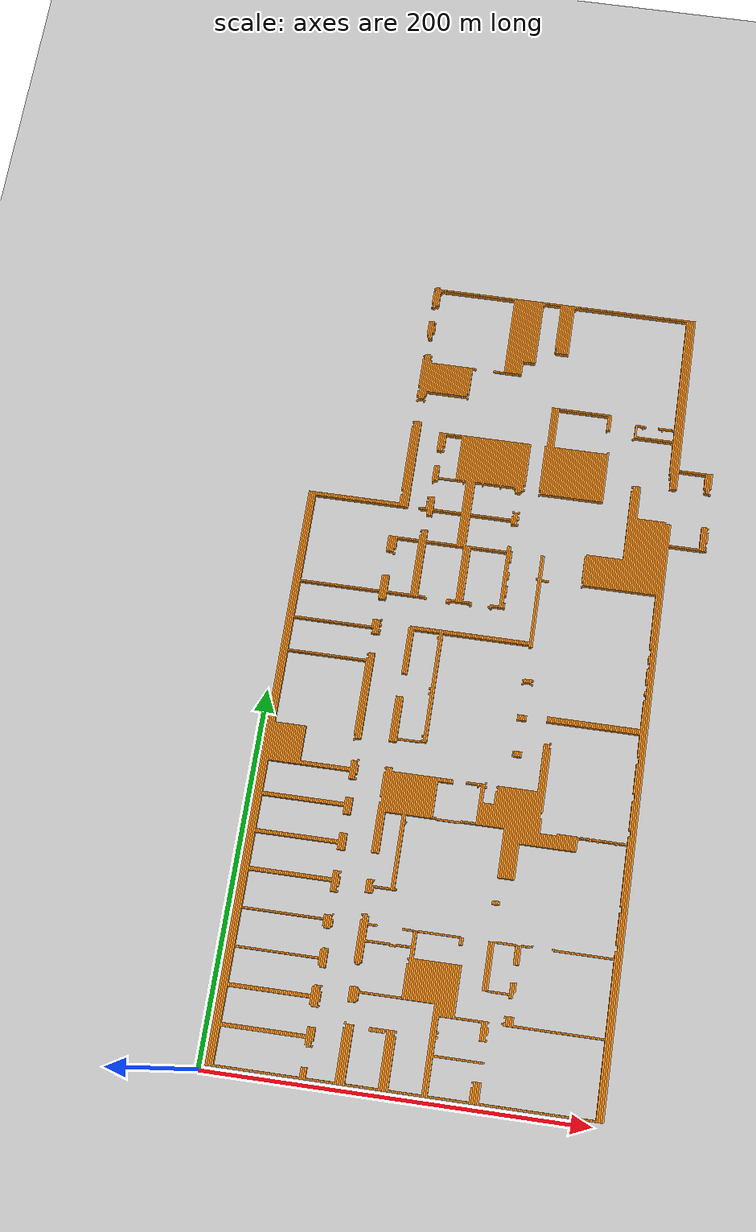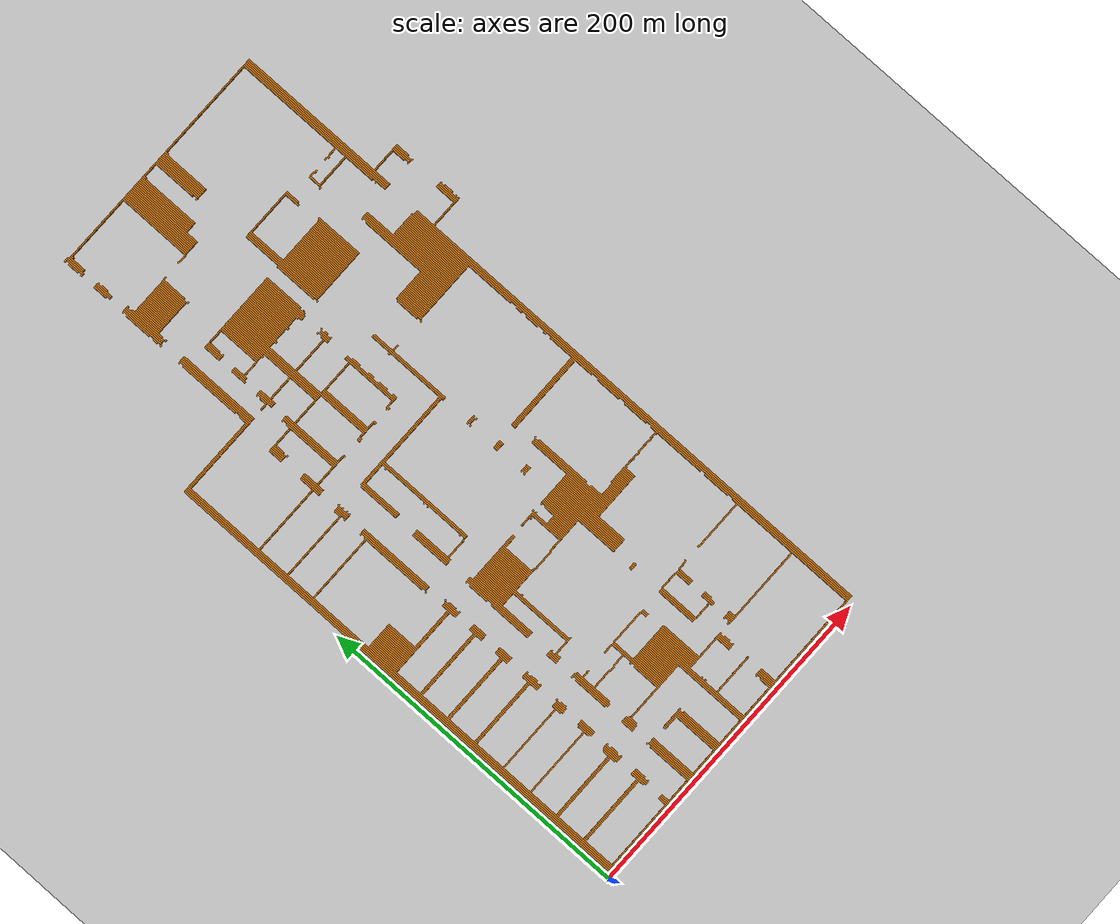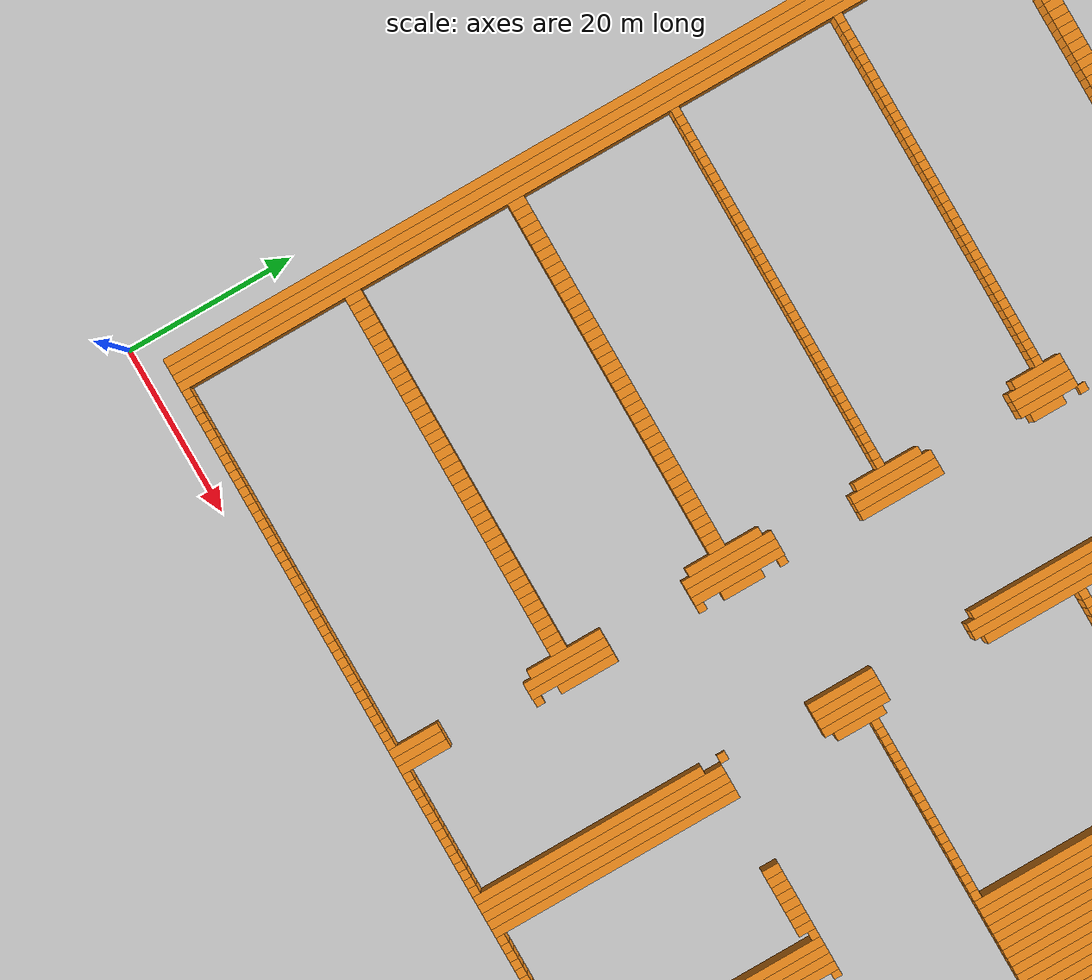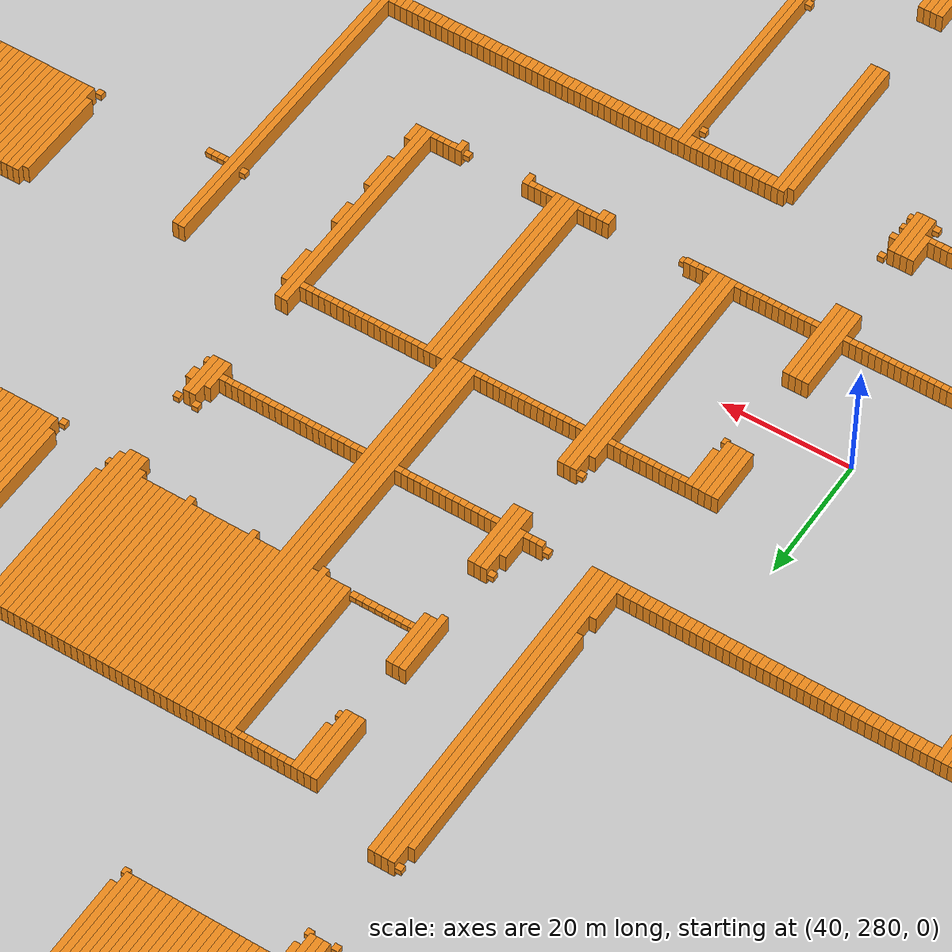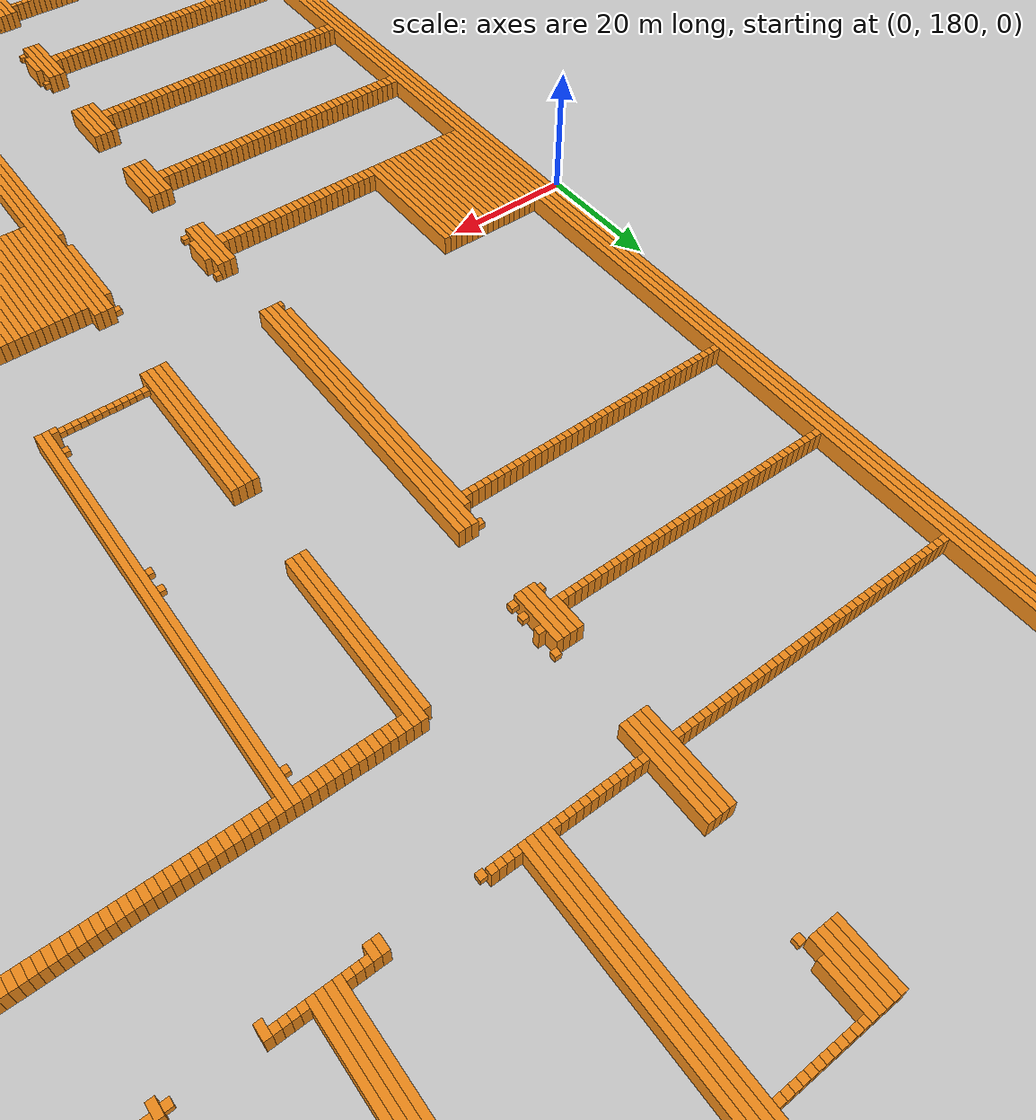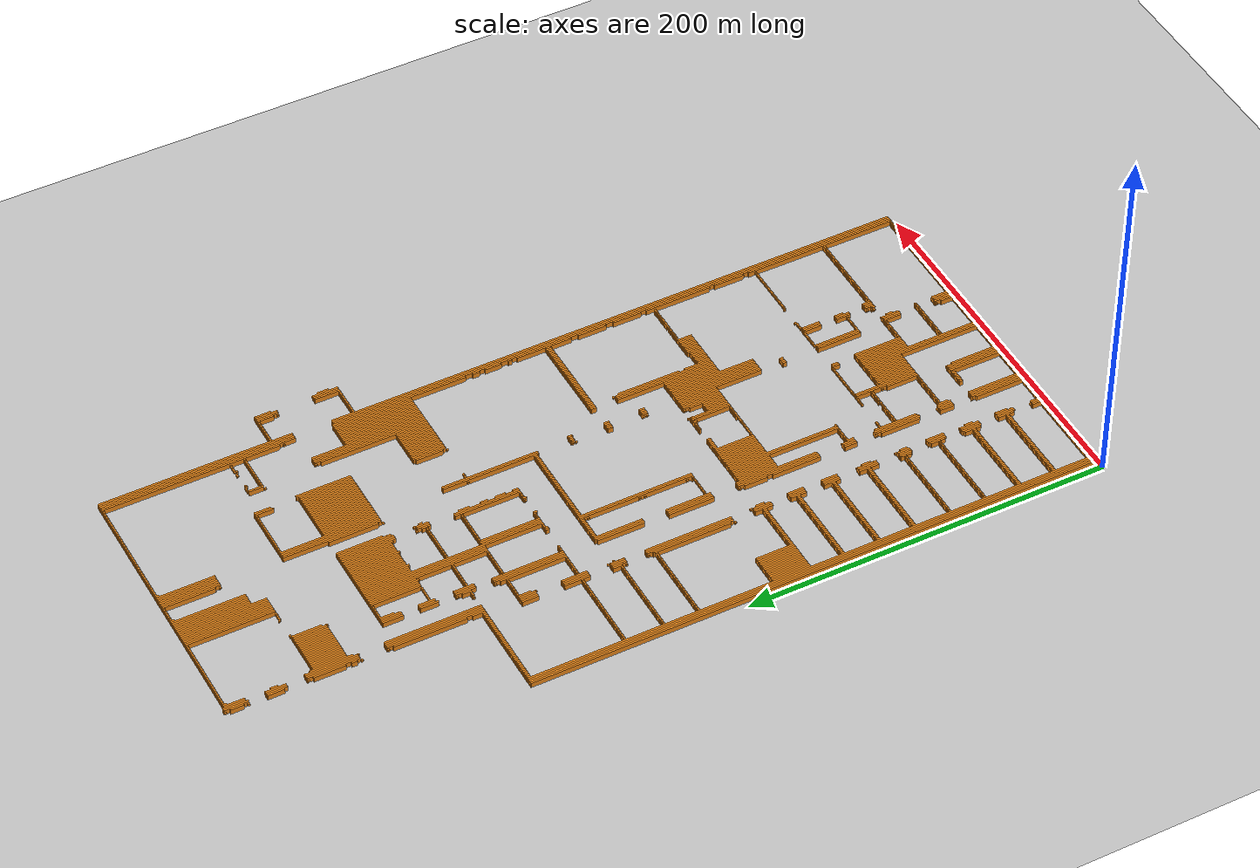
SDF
<sdf version="1.6">
 <world name="default">
  <include><uri>model://ground_plane</uri></include>
  <collision name="collision"><max_contacts>0</max_contacts></collision>
  <light name="sun" type="directional">
   <cast_shadows>0</cast_shadows>
   <pose>0 0 10 0 -0 0</pose>
   <diffuse>0.8 0.8 0.8 1</diffuse>
   <specular>0.2 0.2 0.2 1</specular>
   <attenuation>
    <range>1000</range>
    <constant>0.9</constant>
    <linear>0.01</linear>
    <quadratic>0.001</quadratic>
   </attenuation>
   <direction>-0.5 0.1 -0.9</direction>
  </light>
  <physics name="default_physics" default="0" type="ode"><max_step_size>0.01</max_step_size></physics>
  <gravity>0 0 -9.8</gravity>
  <model name="unit_box_000">
   <pose>3.50   159.50     1.50 0 0 0</pose>
   <static>1</static>
   <link name="link">
    <inertial>
     <mass>5000</mass>
     <inertia><ixx>200</ixx><ixy>0</ixy><ixz>0</ixz><iyy>200</iyy><iyz>0</iyz><izz>200</izz></inertia>
    </inertial>
    <collision name="collision"><geometry><box><size>1 313 3</size></box></geometry></collision>
    <visual name="visual">
     <geometry><box><size>1 313 3</size></box></geometry>
     <material>
      <script><name>Gazebo/Orange</name><uri>file://media/materials/scripts/gazebo.material</uri></script>
     </material>
    </visual>
   </link>
  </model>
  <model name="unit_box_001">
   <pose>4.50   159.50     1.50 0 0 0</pose>
   <static>1</static>
   <link name="link">
    <inertial>
     <mass>5000</mass>
     <inertia><ixx>200</ixx><ixy>0</ixy><ixz>0</ixz><iyy>200</iyy><iyz>0</iyz><izz>200</izz></inertia>
    </inertial>
    <collision name="collision"><geometry><box><size>1 313 3</size></box></geometry></collision>
    <visual name="visual">
     <geometry><box><size>1 313 3</size></box></geometry>
     <material>
      <script><name>Gazebo/Orange</name><uri>file://media/materials/scripts/gazebo.material</uri></script>
     </material>
    </visual>
   </link>
  </model>
  <model name="unit_box_002">
   <pose>5.50   159.50     1.50 0 0 0</pose>
   <static>1</static>
   <link name="link">
    <inertial>
     <mass>5000</mass>
     <inertia><ixx>200</ixx><ixy>0</ixy><ixz>0</ixz><iyy>200</iyy><iyz>0</iyz><izz>200</izz></inertia>
    </inertial>
    <collision name="collision"><geometry><box><size>1 313 3</size></box></geometry></collision>
    <visual name="visual">
     <geometry><box><size>1 313 3</size></box></geometry>
     <material>
      <script><name>Gazebo/Orange</name><uri>file://media/materials/scripts/gazebo.material</uri></script>
     </material>
    </visual>
   </link>
  </model>
  <model name="unit_box_003">
   <pose>6.50   159.50     1.50 0 0 0</pose>
   <static>1</static>
   <link name="link">
    <inertial>
     <mass>5000</mass>
     <inertia><ixx>200</ixx><ixy>0</ixy><ixz>0</ixz><iyy>200</iyy><iyz>0</iyz><izz>200</izz></inertia>
    </inertial>
    <collision name="collision"><geometry><box><size>1 313 3</size></box></geometry></collision>
    <visual name="visual">
     <geometry><box><size>1 313 3</size></box></geometry>
     <material>
      <script><name>Gazebo/Orange</name><uri>file://media/materials/scripts/gazebo.material</uri></script>
     </material>
    </visual>
   </link>
  </model>
  <model name="unit_box_004">
   <pose>7.50     3.50     1.50 0 0 0</pose>
   <static>1</static>
   <link name="link">
    <inertial>
     <mass>5000</mass>
     <inertia><ixx>200</ixx><ixy>0</ixy><ixz>0</ixz><iyy>200</iyy><iyz>0</iyz><izz>200</izz></inertia>
    </inertial>
    <collision name="collision"><geometry><box><size>1 1 3</size></box></geometry></collision>
    <visual name="visual">
     <geometry><box><size>1 1 3</size></box></geometry>
     <material>
      <script><name>Gazebo/Orange</name><uri>file://media/materials/scripts/gazebo.material</uri></script>
     </material>
    </visual>
   </link>
  </model>
  <model name="unit_box_005">
   <pose>7.50    24.00     1.50 0 0 0</pose>
   <static>1</static>
   <link name="link">
    <inertial>
     <mass>5000</mass>
     <inertia><ixx>200</ixx><ixy>0</ixy><ixz>0</ixz><iyy>200</iyy><iyz>0</iyz><izz>200</izz></inertia>
    </inertial>
    <collision name="collision"><geometry><box><size>1 2 3</size></box></geometry></collision>
    <visual name="visual">
     <geometry><box><size>1 2 3</size></box></geometry>
     <material>
      <script><name>Gazebo/Orange</name><uri>file://media/materials/scripts/gazebo.material</uri></script>
     </material>
    </visual>
   </link>
  </model>
  <model name="unit_box_006">
   <pose>7.50    44.00     1.50 0 0 0</pose>
   <static>1</static>
   <link name="link">
    <inertial>
     <mass>5000</mass>
     <inertia><ixx>200</ixx><ixy>0</ixy><ixz>0</ixz><iyy>200</iyy><iyz>0</iyz><izz>200</izz></inertia>
    </inertial>
    <collision name="collision"><geometry><box><size>1 2 3</size></box></geometry></collision>
    <visual name="visual">
     <geometry><box><size>1 2 3</size></box></geometry>
     <material>
      <script><name>Gazebo/Orange</name><uri>file://media/materials/scripts/gazebo.material</uri></script>
     </material>
    </visual>
   </link>
  </model>
  <model name="unit_box_007">
   <pose>7.50    63.50     1.50 0 0 0</pose>
   <static>1</static>
   <link name="link">
    <inertial>
     <mass>5000</mass>
     <inertia><ixx>200</ixx><ixy>0</ixy><ixz>0</ixz><iyy>200</iyy><iyz>0</iyz><izz>200</izz></inertia>
    </inertial>
    <collision name="collision"><geometry><box><size>1 1 3</size></box></geometry></collision>
    <visual name="visual">
     <geometry><box><size>1 1 3</size></box></geometry>
     <material>
      <script><name>Gazebo/Orange</name><uri>file://media/materials/scripts/gazebo.material</uri></script>
     </material>
    </visual>
   </link>
  </model>
  <model name="unit_box_008">
   <pose>7.50    83.50     1.50 0 0 0</pose>
   <static>1</static>
   <link name="link">
    <inertial>
     <mass>5000</mass>
     <inertia><ixx>200</ixx><ixy>0</ixy><ixz>0</ixz><iyy>200</iyy><iyz>0</iyz><izz>200</izz></inertia>
    </inertial>
    <collision name="collision"><geometry><box><size>1 1 3</size></box></geometry></collision>
    <visual name="visual">
     <geometry><box><size>1 1 3</size></box></geometry>
     <material>
      <script><name>Gazebo/Orange</name><uri>file://media/materials/scripts/gazebo.material</uri></script>
     </material>
    </visual>
   </link>
  </model>
  <model name="unit_box_009">
   <pose>7.50   104.00     1.50 0 0 0</pose>
   <static>1</static>
   <link name="link">
    <inertial>
     <mass>5000</mass>
     <inertia><ixx>200</ixx><ixy>0</ixy><ixz>0</ixz><iyy>200</iyy><iyz>0</iyz><izz>200</izz></inertia>
    </inertial>
    <collision name="collision"><geometry><box><size>1 2 3</size></box></geometry></collision>
    <visual name="visual">
     <geometry><box><size>1 2 3</size></box></geometry>
     <material>
      <script><name>Gazebo/Orange</name><uri>file://media/materials/scripts/gazebo.material</uri></script>
     </material>
    </visual>
   </link>
  </model>
  <model name="unit_box_010">
   <pose>7.50   124.00     1.50 0 0 0</pose>
   <static>1</static>
   <link name="link">
    <inertial>
     <mass>5000</mass>
     <inertia><ixx>200</ixx><ixy>0</ixy><ixz>0</ixz><iyy>200</iyy><iyz>0</iyz><izz>200</izz></inertia>
    </inertial>
    <collision name="collision"><geometry><box><size>1 2 3</size></box></geometry></collision>
    <visual name="visual">
     <geometry><box><size>1 2 3</size></box></geometry>
     <material>
      <script><name>Gazebo/Orange</name><uri>file://media/materials/scripts/gazebo.material</uri></script>
     </material>
    </visual>
   </link>
  </model>
  <model name="unit_box_011">
   <pose>7.50   144.00     1.50 0 0 0</pose>
   <static>1</static>
   <link name="link">
    <inertial>
     <mass>5000</mass>
     <inertia><ixx>200</ixx><ixy>0</ixy><ixz>0</ixz><iyy>200</iyy><iyz>0</iyz><izz>200</izz></inertia>
    </inertial>
    <collision name="collision"><geometry><box><size>1 2 3</size></box></geometry></collision>
    <visual name="visual">
     <geometry><box><size>1 2 3</size></box></geometry>
     <material>
      <script><name>Gazebo/Orange</name><uri>file://media/materials/scripts/gazebo.material</uri></script>
     </material>
    </visual>
   </link>
  </model>
  <model name="unit_box_012">
   <pose>7.50   172.50     1.50 0 0 0</pose>
   <static>1</static>
   <link name="link">
    <inertial>
     <mass>5000</mass>
     <inertia><ixx>200</ixx><ixy>0</ixy><ixz>0</ixz><iyy>200</iyy><iyz>0</iyz><izz>200</izz></inertia>
    </inertial>
    <collision name="collision"><geometry><box><size>1 21 3</size></box></geometry></collision>
    <visual name="visual">
     <geometry><box><size>1 21 3</size></box></geometry>
     <material>
      <script><name>Gazebo/Orange</name><uri>file://media/materials/scripts/gazebo.material</uri></script>
     </material>
    </visual>
   </link>
  </model>
  <model name="unit_box_013">
   <pose>7.50   223.50     1.50 0 0 0</pose>
   <static>1</static>
   <link name="link">
    <inertial>
     <mass>5000</mass>
     <inertia><ixx>200</ixx><ixy>0</ixy><ixz>0</ixz><iyy>200</iyy><iyz>0</iyz><izz>200</izz></inertia>
    </inertial>
    <collision name="collision"><geometry><box><size>1 1 3</size></box></geometry></collision>
    <visual name="visual">
     <geometry><box><size>1 1 3</size></box></geometry>
     <material>
      <script><name>Gazebo/Orange</name><uri>file://media/materials/scripts/gazebo.material</uri></script>
     </material>
    </visual>
   </link>
  </model>
  <model name="unit_box_014">
   <pose>7.50   242.50     1.50 0 0 0</pose>
   <static>1</static>
   <link name="link">
    <inertial>
     <mass>5000</mass>
     <inertia><ixx>200</ixx><ixy>0</ixy><ixz>0</ixz><iyy>200</iyy><iyz>0</iyz><izz>200</izz></inertia>
    </inertial>
    <collision name="collision"><geometry><box><size>1 1 3</size></box></geometry></collision>
    <visual name="visual">
     <geometry><box><size>1 1 3</size></box></geometry>
     <material>
      <script><name>Gazebo/Orange</name><uri>file://media/materials/scripts/gazebo.material</uri></script>
     </material>
    </visual>
   </link>
  </model>
  <model name="unit_box_015">
   <pose>7.50   263.50     1.50 0 0 0</pose>
   <static>1</static>
   <link name="link">
    <inertial>
     <mass>5000</mass>
     <inertia><ixx>200</ixx><ixy>0</ixy><ixz>0</ixz><iyy>200</iyy><iyz>0</iyz><izz>200</izz></inertia>
    </inertial>
    <collision name="collision"><geometry><box><size>1 1 3</size></box></geometry></collision>
    <visual name="visual">
     <geometry><box><size>1 1 3</size></box></geometry>
     <material>
      <script><name>Gazebo/Orange</name><uri>file://media/materials/scripts/gazebo.material</uri></script>
     </material>
    </visual>
   </link>
  </model>
  <model name="unit_box_016">
   <pose>7.50   315.00     1.50 0 0 0</pose>
   <static>1</static>
   <link name="link">
    <inertial>
     <mass>5000</mass>
     <inertia><ixx>200</ixx><ixy>0</ixy><ixz>0</ixz><iyy>200</iyy><iyz>0</iyz><izz>200</izz></inertia>
    </inertial>
    <collision name="collision"><geometry><box><size>1 2 3</size></box></geometry></collision>
    <visual name="visual">
     <geometry><box><size>1 2 3</size></box></geometry>
     <material>
      <script><name>Gazebo/Orange</name><uri>file://media/materials/scripts/gazebo.material</uri></script>
     </material>
    </visual>
   </link>
  </model>
  <model name="unit_box_017">
   <pose>8.50     3.50     1.50 0 0 0</pose>
   <static>1</static>
   <link name="link">
    <inertial>
     <mass>5000</mass>
     <inertia><ixx>200</ixx><ixy>0</ixy><ixz>0</ixz><iyy>200</iyy><iyz>0</iyz><izz>200</izz></inertia>
    </inertial>
    <collision name="collision"><geometry><box><size>1 1 3</size></box></geometry></collision>
    <visual name="visual">
     <geometry><box><size>1 1 3</size></box></geometry>
     <material>
      <script><name>Gazebo/Orange</name><uri>file://media/materials/scripts/gazebo.material</uri></script>
     </material>
    </visual>
   </link>
  </model>
  <model name="unit_box_018">
   <pose>8.50    24.00     1.50 0 0 0</pose>
   <static>1</static>
   <link name="link">
    <inertial>
     <mass>5000</mass>
     <inertia><ixx>200</ixx><ixy>0</ixy><ixz>0</ixz><iyy>200</iyy><iyz>0</iyz><izz>200</izz></inertia>
    </inertial>
    <collision name="collision"><geometry><box><size>1 2 3</size></box></geometry></collision>
    <visual name="visual">
     <geometry><box><size>1 2 3</size></box></geometry>
     <material>
      <script><name>Gazebo/Orange</name><uri>file://media/materials/scripts/gazebo.material</uri></script>
     </material>
    </visual>
   </link>
  </model>
  <model name="unit_box_019">
   <pose>8.50    44.00     1.50 0 0 0</pose>
   <static>1</static>
   <link name="link">
    <inertial>
     <mass>5000</mass>
     <inertia><ixx>200</ixx><ixy>0</ixy><ixz>0</ixz><iyy>200</iyy><iyz>0</iyz><izz>200</izz></inertia>
    </inertial>
    <collision name="collision"><geometry><box><size>1 2 3</size></box></geometry></collision>
    <visual name="visual">
     <geometry><box><size>1 2 3</size></box></geometry>
     <material>
      <script><name>Gazebo/Orange</name><uri>file://media/materials/scripts/gazebo.material</uri></script>
     </material>
    </visual>
   </link>
  </model>
  <model name="unit_box_020">
   <pose>8.50    63.50     1.50 0 0 0</pose>
   <static>1</static>
   <link name="link">
    <inertial>
     <mass>5000</mass>
     <inertia><ixx>200</ixx><ixy>0</ixy><ixz>0</ixz><iyy>200</iyy><iyz>0</iyz><izz>200</izz></inertia>
    </inertial>
    <collision name="collision"><geometry><box><size>1 1 3</size></box></geometry></collision>
    <visual name="visual">
     <geometry><box><size>1 1 3</size></box></geometry>
     <material>
      <script><name>Gazebo/Orange</name><uri>file://media/materials/scripts/gazebo.material</uri></script>
     </material>
    </visual>
   </link>
  </model>
  <model name="unit_box_021">
   <pose>8.50    83.50     1.50 0 0 0</pose>
   <static>1</static>
   <link name="link">
    <inertial>
     <mass>5000</mass>
     <inertia><ixx>200</ixx><ixy>0</ixy><ixz>0</ixz><iyy>200</iyy><iyz>0</iyz><izz>200</izz></inertia>
    </inertial>
    <collision name="collision"><geometry><box><size>1 1 3</size></box></geometry></collision>
    <visual name="visual">
     <geometry><box><size>1 1 3</size></box></geometry>
     <material>
      <script><name>Gazebo/Orange</name><uri>file://media/materials/scripts/gazebo.material</uri></script>
     </material>
    </visual>
   </link>
  </model>
  <model name="unit_box_022">
   <pose>8.50   104.00     1.50 0 0 0</pose>
   <static>1</static>
   <link name="link">
    <inertial>
     <mass>5000</mass>
     <inertia><ixx>200</ixx><ixy>0</ixy><ixz>0</ixz><iyy>200</iyy><iyz>0</iyz><izz>200</izz></inertia>
    </inertial>
    <collision name="collision"><geometry><box><size>1 2 3</size></box></geometry></collision>
    <visual name="visual">
     <geometry><box><size>1 2 3</size></box></geometry>
     <material>
      <script><name>Gazebo/Orange</name><uri>file://media/materials/scripts/gazebo.material</uri></script>
     </material>
    </visual>
   </link>
  </model>
  <model name="unit_box_023">
   <pose>8.50   124.00     1.50 0 0 0</pose>
   <static>1</static>
   <link name="link">
    <inertial>
     <mass>5000</mass>
     <inertia><ixx>200</ixx><ixy>0</ixy><ixz>0</ixz><iyy>200</iyy><iyz>0</iyz><izz>200</izz></inertia>
    </inertial>
    <collision name="collision"><geometry><box><size>1 2 3</size></box></geometry></collision>
    <visual name="visual">
     <geometry><box><size>1 2 3</size></box></geometry>
     <material>
      <script><name>Gazebo/Orange</name><uri>file://media/materials/scripts/gazebo.material</uri></script>
     </material>
    </visual>
   </link>
  </model>
  <model name="unit_box_024">
   <pose>8.50   144.00     1.50 0 0 0</pose>
   <static>1</static>
   <link name="link">
    <inertial>
     <mass>5000</mass>
     <inertia><ixx>200</ixx><ixy>0</ixy><ixz>0</ixz><iyy>200</iyy><iyz>0</iyz><izz>200</izz></inertia>
    </inertial>
    <collision name="collision"><geometry><box><size>1 2 3</size></box></geometry></collision>
    <visual name="visual">
     <geometry><box><size>1 2 3</size></box></geometry>
     <material>
      <script><name>Gazebo/Orange</name><uri>file://media/materials/scripts/gazebo.material</uri></script>
     </material>
    </visual>
   </link>
  </model>
  <model name="unit_box_025">
   <pose>8.50   172.50     1.50 0 0 0</pose>
   <static>1</static>
   <link name="link">
    <inertial>
     <mass>5000</mass>
     <inertia><ixx>200</ixx><ixy>0</ixy><ixz>0</ixz><iyy>200</iyy><iyz>0</iyz><izz>200</izz></inertia>
    </inertial>
    <collision name="collision"><geometry><box><size>1 21 3</size></box></geometry></collision>
    <visual name="visual">
     <geometry><box><size>1 21 3</size></box></geometry>
     <material>
      <script><name>Gazebo/Orange</name><uri>file://media/materials/scripts/gazebo.material</uri></script>
     </material>
    </visual>
   </link>
  </model>
  <model name="unit_box_026">
   <pose>8.50   223.50     1.50 0 0 0</pose>
   <static>1</static>
   <link name="link">
    <inertial>
     <mass>5000</mass>
     <inertia><ixx>200</ixx><ixy>0</ixy><ixz>0</ixz><iyy>200</iyy><iyz>0</iyz><izz>200</izz></inertia>
    </inertial>
    <collision name="collision"><geometry><box><size>1 1 3</size></box></geometry></collision>
    <visual name="visual">
     <geometry><box><size>1 1 3</size></box></geometry>
     <material>
      <script><name>Gazebo/Orange</name><uri>file://media/materials/scripts/gazebo.material</uri></script>
     </material>
    </visual>
   </link>
  </model>
  <model name="unit_box_027">
   <pose>8.50   242.50     1.50 0 0 0</pose>
   <static>1</static>
   <link name="link">
    <inertial>
     <mass>5000</mass>
     <inertia><ixx>200</ixx><ixy>0</ixy><ixz>0</ixz><iyy>200</iyy><iyz>0</iyz><izz>200</izz></inertia>
    </inertial>
    <collision name="collision"><geometry><box><size>1 1 3</size></box></geometry></collision>
    <visual name="visual">
     <geometry><box><size>1 1 3</size></box></geometry>
     <material>
      <script><name>Gazebo/Orange</name><uri>file://media/materials/scripts/gazebo.material</uri></script>
     </material>
    </visual>
   </link>
  </model>
  <model name="unit_box_028">
   <pose>8.50   263.50     1.50 0 0 0</pose>
   <static>1</static>
   <link name="link">
    <inertial>
     <mass>5000</mass>
     <inertia><ixx>200</ixx><ixy>0</ixy><ixz>0</ixz><iyy>200</iyy><iyz>0</iyz><izz>200</izz></inertia>
    </inertial>
    <collision name="collision"><geometry><box><size>1 1 3</size></box></geometry></collision>
    <visual name="visual">
     <geometry><box><size>1 1 3</size></box></geometry>
     <material>
      <script><name>Gazebo/Orange</name><uri>file://media/materials/scripts/gazebo.material</uri></script>
     </material>
    </visual>
   </link>
  </model>
  <model name="unit_box_029">
   <pose>8.50   315.00     1.50 0 0 0</pose>
   <static>1</static>
   <link name="link">
    <inertial>
     <mass>5000</mass>
     <inertia><ixx>200</ixx><ixy>0</ixy><ixz>0</ixz><iyy>200</iyy><iyz>0</iyz><izz>200</izz></inertia>
    </inertial>
    <collision name="collision"><geometry><box><size>1 2 3</size></box></geometry></collision>
    <visual name="visual">
     <geometry><box><size>1 2 3</size></box></geometry>
     <material>
      <script><name>Gazebo/Orange</name><uri>file://media/materials/scripts/gazebo.material</uri></script>
     </material>
    </visual>
   </link>
  </model>
  <model name="unit_box_030">
   <pose>9.50     3.50     1.50 0 0 0</pose>
   <static>1</static>
   <link name="link">
    <inertial>
     <mass>5000</mass>
     <inertia><ixx>200</ixx><ixy>0</ixy><ixz>0</ixz><iyy>200</iyy><iyz>0</iyz><izz>200</izz></inertia>
    </inertial>
    <collision name="collision"><geometry><box><size>1 1 3</size></box></geometry></collision>
    <visual name="visual">
     <geometry><box><size>1 1 3</size></box></geometry>
     <material>
      <script><name>Gazebo/Orange</name><uri>file://media/materials/scripts/gazebo.material</uri></script>
     </material>
    </visual>
   </link>
  </model>
  <model name="unit_box_031">
   <pose>9.50    24.00     1.50 0 0 0</pose>
   <static>1</static>
   <link name="link">
    <inertial>
     <mass>5000</mass>
     <inertia><ixx>200</ixx><ixy>0</ixy><ixz>0</ixz><iyy>200</iyy><iyz>0</iyz><izz>200</izz></inertia>
    </inertial>
    <collision name="collision"><geometry><box><size>1 2 3</size></box></geometry></collision>
    <visual name="visual">
     <geometry><box><size>1 2 3</size></box></geometry>
     <material>
      <script><name>Gazebo/Orange</name><uri>file://media/materials/scripts/gazebo.material</uri></script>
     </material>
    </visual>
   </link>
  </model>
  <model name="unit_box_032">
   <pose>9.50    44.00     1.50 0 0 0</pose>
   <static>1</static>
   <link name="link">
    <inertial>
     <mass>5000</mass>
     <inertia><ixx>200</ixx><ixy>0</ixy><ixz>0</ixz><iyy>200</iyy><iyz>0</iyz><izz>200</izz></inertia>
    </inertial>
    <collision name="collision"><geometry><box><size>1 2 3</size></box></geometry></collision>
    <visual name="visual">
     <geometry><box><size>1 2 3</size></box></geometry>
     <material>
      <script><name>Gazebo/Orange</name><uri>file://media/materials/scripts/gazebo.material</uri></script>
     </material>
    </visual>
   </link>
  </model>
  <model name="unit_box_033">
   <pose>9.50    63.50     1.50 0 0 0</pose>
   <static>1</static>
   <link name="link">
    <inertial>
     <mass>5000</mass>
     <inertia><ixx>200</ixx><ixy>0</ixy><ixz>0</ixz><iyy>200</iyy><iyz>0</iyz><izz>200</izz></inertia>
    </inertial>
    <collision name="collision"><geometry><box><size>1 1 3</size></box></geometry></collision>
    <visual name="visual">
     <geometry><box><size>1 1 3</size></box></geometry>
     <material>
      <script><name>Gazebo/Orange</name><uri>file://media/materials/scripts/gazebo.material</uri></script>
     </material>
    </visual>
   </link>
  </model>
  <model name="unit_box_034">
   <pose>9.50    83.50     1.50 0 0 0</pose>
   <static>1</static>
   <link name="link">
    <inertial>
     <mass>5000</mass>
     <inertia><ixx>200</ixx><ixy>0</ixy><ixz>0</ixz><iyy>200</iyy><iyz>0</iyz><izz>200</izz></inertia>
    </inertial>
    <collision name="collision"><geometry><box><size>1 1 3</size></box></geometry></collision>
    <visual name="visual">
     <geometry><box><size>1 1 3</size></box></geometry>
     <material>
      <script><name>Gazebo/Orange</name><uri>file://media/materials/scripts/gazebo.material</uri></script>
     </material>
    </visual>
   </link>
  </model>
  <model name="unit_box_035">
   <pose>9.50   104.00     1.50 0 0 0</pose>
   <static>1</static>
   <link name="link">
    <inertial>
     <mass>5000</mass>
     <inertia><ixx>200</ixx><ixy>0</ixy><ixz>0</ixz><iyy>200</iyy><iyz>0</iyz><izz>200</izz></inertia>
    </inertial>
    <collision name="collision"><geometry><box><size>1 2 3</size></box></geometry></collision>
    <visual name="visual">
     <geometry><box><size>1 2 3</size></box></geometry>
     <material>
      <script><name>Gazebo/Orange</name><uri>file://media/materials/scripts/gazebo.material</uri></script>
     </material>
    </visual>
   </link>
  </model>
  <model name="unit_box_036">
   <pose>9.50   124.00     1.50 0 0 0</pose>
   <static>1</static>
   <link name="link">
    <inertial>
     <mass>5000</mass>
     <inertia><ixx>200</ixx><ixy>0</ixy><ixz>0</ixz><iyy>200</iyy><iyz>0</iyz><izz>200</izz></inertia>
    </inertial>
    <collision name="collision"><geometry><box><size>1 2 3</size></box></geometry></collision>
    <visual name="visual">
     <geometry><box><size>1 2 3</size></box></geometry>
     <material>
      <script><name>Gazebo/Orange</name><uri>file://media/materials/scripts/gazebo.material</uri></script>
     </material>
    </visual>
   </link>
  </model>
  <model name="unit_box_037">
   <pose>9.50   144.00     1.50 0 0 0</pose>
   <static>1</static>
   <link name="link">
    <inertial>
     <mass>5000</mass>
     <inertia><ixx>200</ixx><ixy>0</ixy><ixz>0</ixz><iyy>200</iyy><iyz>0</iyz><izz>200</izz></inertia>
    </inertial>
    <collision name="collision"><geometry><box><size>1 2 3</size></box></geometry></collision>
    <visual name="visual">
     <geometry><box><size>1 2 3</size></box></geometry>
     <material>
      <script><name>Gazebo/Orange</name><uri>file://media/materials/scripts/gazebo.material</uri></script>
     </material>
    </visual>
   </link>
  </model>
  <model name="unit_box_038">
   <pose>9.50   172.50     1.50 0 0 0</pose>
   <static>1</static>
   <link name="link">
    <inertial>
     <mass>5000</mass>
     <inertia><ixx>200</ixx><ixy>0</ixy><ixz>0</ixz><iyy>200</iyy><iyz>0</iyz><izz>200</izz></inertia>
    </inertial>
    <collision name="collision"><geometry><box><size>1 21 3</size></box></geometry></collision>
    <visual name="visual">
     <geometry><box><size>1 21 3</size></box></geometry>
     <material>
      <script><name>Gazebo/Orange</name><uri>file://media/materials/scripts/gazebo.material</uri></script>
     </material>
    </visual>
   </link>
  </model>
  <model name="unit_box_039">
   <pose>9.50   223.50     1.50 0 0 0</pose>
   <static>1</static>
   <link name="link">
    <inertial>
     <mass>5000</mass>
     <inertia><ixx>200</ixx><ixy>0</ixy><ixz>0</ixz><iyy>200</iyy><iyz>0</iyz><izz>200</izz></inertia>
    </inertial>
    <collision name="collision"><geometry><box><size>1 1 3</size></box></geometry></collision>
    <visual name="visual">
     <geometry><box><size>1 1 3</size></box></geometry>
     <material>
      <script><name>Gazebo/Orange</name><uri>file://media/materials/scripts/gazebo.material</uri></script>
     </material>
    </visual>
   </link>
  </model>
  <model name="unit_box_040">
   <pose>9.50   242.50     1.50 0 0 0</pose>
   <static>1</static>
   <link name="link">
    <inertial>
     <mass>5000</mass>
     <inertia><ixx>200</ixx><ixy>0</ixy><ixz>0</ixz><iyy>200</iyy><iyz>0</iyz><izz>200</izz></inertia>
    </inertial>
    <collision name="collision"><geometry><box><size>1 1 3</size></box></geometry></collision>
    <visual name="visual">
     <geometry><box><size>1 1 3</size></box></geometry>
     <material>
      <script><name>Gazebo/Orange</name><uri>file://media/materials/scripts/gazebo.material</uri></script>
     </material>
    </visual>
   </link>
  </model>
  <model name="unit_box_041">
   <pose>9.50   263.50     1.50 0 0 0</pose>
   <static>1</static>
   <link name="link">
    <inertial>
     <mass>5000</mass>
     <inertia><ixx>200</ixx><ixy>0</ixy><ixz>0</ixz><iyy>200</iyy><iyz>0</iyz><izz>200</izz></inertia>
    </inertial>
    <collision name="collision"><geometry><box><size>1 1 3</size></box></geometry></collision>
    <visual name="visual">
     <geometry><box><size>1 1 3</size></box></geometry>
     <material>
      <script><name>Gazebo/Orange</name><uri>file://media/materials/scripts/gazebo.material</uri></script>
     </material>
    </visual>
   </link>
  </model>
  <model name="unit_box_042">
   <pose>9.50   315.00     1.50 0 0 0</pose>
   <static>1</static>
   <link name="link">
    <inertial>
     <mass>5000</mass>
     <inertia><ixx>200</ixx><ixy>0</ixy><ixz>0</ixz><iyy>200</iyy><iyz>0</iyz><izz>200</izz></inertia>
    </inertial>
    <collision name="collision"><geometry><box><size>1 2 3</size></box></geometry></collision>
    <visual name="visual">
     <geometry><box><size>1 2 3</size></box></geometry>
     <material>
      <script><name>Gazebo/Orange</name><uri>file://media/materials/scripts/gazebo.material</uri></script>
     </material>
    </visual>
   </link>
  </model>
  <model name="unit_box_043">
   <pose>10.50     3.50     1.50 0 0 0</pose>
   <static>1</static>
   <link name="link">
    <inertial>
     <mass>5000</mass>
     <inertia><ixx>200</ixx><ixy>0</ixy><ixz>0</ixz><iyy>200</iyy><iyz>0</iyz><izz>200</izz></inertia>
    </inertial>
    <collision name="collision"><geometry><box><size>1 1 3</size></box></geometry></collision>
    <visual name="visual">
     <geometry><box><size>1 1 3</size></box></geometry>
     <material>
      <script><name>Gazebo/Orange</name><uri>file://media/materials/scripts/gazebo.material</uri></script>
     </material>
    </visual>
   </link>
  </model>
  <model name="unit_box_044">
   <pose>10.50    24.00     1.50 0 0 0</pose>
   <static>1</static>
   <link name="link">
    <inertial>
     <mass>5000</mass>
     <inertia><ixx>200</ixx><ixy>0</ixy><ixz>0</ixz><iyy>200</iyy><iyz>0</iyz><izz>200</izz></inertia>
    </inertial>
    <collision name="collision"><geometry><box><size>1 2 3</size></box></geometry></collision>
    <visual name="visual">
     <geometry><box><size>1 2 3</size></box></geometry>
     <material>
      <script><name>Gazebo/Orange</name><uri>file://media/materials/scripts/gazebo.material</uri></script>
     </material>
    </visual>
   </link>
  </model>
  <model name="unit_box_045">
   <pose>10.50    44.00     1.50 0 0 0</pose>
   <static>1</static>
   <link name="link">
    <inertial>
     <mass>5000</mass>
     <inertia><ixx>200</ixx><ixy>0</ixy><ixz>0</ixz><iyy>200</iyy><iyz>0</iyz><izz>200</izz></inertia>
    </inertial>
    <collision name="collision"><geometry><box><size>1 2 3</size></box></geometry></collision>
    <visual name="visual">
     <geometry><box><size>1 2 3</size></box></geometry>
     <material>
      <script><name>Gazebo/Orange</name><uri>file://media/materials/scripts/gazebo.material</uri></script>
     </material>
    </visual>
   </link>
  </model>
  <model name="unit_box_046">
   <pose>10.50    63.50     1.50 0 0 0</pose>
   <static>1</static>
   <link name="link">
    <inertial>
     <mass>5000</mass>
     <inertia><ixx>200</ixx><ixy>0</ixy><ixz>0</ixz><iyy>200</iyy><iyz>0</iyz><izz>200</izz></inertia>
    </inertial>
    <collision name="collision"><geometry><box><size>1 1 3</size></box></geometry></collision>
    <visual name="visual">
     <geometry><box><size>1 1 3</size></box></geometry>
     <material>
      <script><name>Gazebo/Orange</name><uri>file://media/materials/scripts/gazebo.material</uri></script>
     </material>
    </visual>
   </link>
  </model>
  <model name="unit_box_047">
   <pose>10.50    83.50     1.50 0 0 0</pose>
   <static>1</static>
   <link name="link">
    <inertial>
     <mass>5000</mass>
     <inertia><ixx>200</ixx><ixy>0</ixy><ixz>0</ixz><iyy>200</iyy><iyz>0</iyz><izz>200</izz></inertia>
    </inertial>
    <collision name="collision"><geometry><box><size>1 1 3</size></box></geometry></collision>
    <visual name="visual">
     <geometry><box><size>1 1 3</size></box></geometry>
     <material>
      <script><name>Gazebo/Orange</name><uri>file://media/materials/scripts/gazebo.material</uri></script>
     </material>
    </visual>
   </link>
  </model>
  <model name="unit_box_048">
   <pose>10.50   104.00     1.50 0 0 0</pose>
   <static>1</static>
   <link name="link">
    <inertial>
     <mass>5000</mass>
     <inertia><ixx>200</ixx><ixy>0</ixy><ixz>0</ixz><iyy>200</iyy><iyz>0</iyz><izz>200</izz></inertia>
    </inertial>
    <collision name="collision"><geometry><box><size>1 2 3</size></box></geometry></collision>
    <visual name="visual">
     <geometry><box><size>1 2 3</size></box></geometry>
     <material>
      <script><name>Gazebo/Orange</name><uri>file://media/materials/scripts/gazebo.material</uri></script>
     </material>
    </visual>
   </link>
  </model>
  <model name="unit_box_049">
   <pose>10.50   124.00     1.50 0 0 0</pose>
   <static>1</static>
   <link name="link">
    <inertial>
     <mass>5000</mass>
     <inertia><ixx>200</ixx><ixy>0</ixy><ixz>0</ixz><iyy>200</iyy><iyz>0</iyz><izz>200</izz></inertia>
    </inertial>
    <collision name="collision"><geometry><box><size>1 2 3</size></box></geometry></collision>
    <visual name="visual">
     <geometry><box><size>1 2 3</size></box></geometry>
     <material>
      <script><name>Gazebo/Orange</name><uri>file://media/materials/scripts/gazebo.material</uri></script>
     </material>
    </visual>
   </link>
  </model>
  <model name="unit_box_050">
   <pose>10.50   144.00     1.50 0 0 0</pose>
   <static>1</static>
   <link name="link">
    <inertial>
     <mass>5000</mass>
     <inertia><ixx>200</ixx><ixy>0</ixy><ixz>0</ixz><iyy>200</iyy><iyz>0</iyz><izz>200</izz></inertia>
    </inertial>
    <collision name="collision"><geometry><box><size>1 2 3</size></box></geometry></collision>
    <visual name="visual">
     <geometry><box><size>1 2 3</size></box></geometry>
     <material>
      <script><name>Gazebo/Orange</name><uri>file://media/materials/scripts/gazebo.material</uri></script>
     </material>
    </visual>
   </link>
  </model>
  <model name="unit_box_051">
   <pose>10.50   172.50     1.50 0 0 0</pose>
   <static>1</static>
   <link name="link">
    <inertial>
     <mass>5000</mass>
     <inertia><ixx>200</ixx><ixy>0</ixy><ixz>0</ixz><iyy>200</iyy><iyz>0</iyz><izz>200</izz></inertia>
    </inertial>
    <collision name="collision"><geometry><box><size>1 21 3</size></box></geometry></collision>
    <visual name="visual">
     <geometry><box><size>1 21 3</size></box></geometry>
     <material>
      <script><name>Gazebo/Orange</name><uri>file://media/materials/scripts/gazebo.material</uri></script>
     </material>
    </visual>
   </link>
  </model>
  <model name="unit_box_052">
   <pose>10.50   223.50     1.50 0 0 0</pose>
   <static>1</static>
   <link name="link">
    <inertial>
     <mass>5000</mass>
     <inertia><ixx>200</ixx><ixy>0</ixy><ixz>0</ixz><iyy>200</iyy><iyz>0</iyz><izz>200</izz></inertia>
    </inertial>
    <collision name="collision"><geometry><box><size>1 1 3</size></box></geometry></collision>
    <visual name="visual">
     <geometry><box><size>1 1 3</size></box></geometry>
     <material>
      <script><name>Gazebo/Orange</name><uri>file://media/materials/scripts/gazebo.material</uri></script>
     </material>
    </visual>
   </link>
  </model>
  <model name="unit_box_053">
   <pose>10.50   242.50     1.50 0 0 0</pose>
   <static>1</static>
   <link name="link">
    <inertial>
     <mass>5000</mass>
     <inertia><ixx>200</ixx><ixy>0</ixy><ixz>0</ixz><iyy>200</iyy><iyz>0</iyz><izz>200</izz></inertia>
    </inertial>
    <collision name="collision"><geometry><box><size>1 1 3</size></box></geometry></collision>
    <visual name="visual">
     <geometry><box><size>1 1 3</size></box></geometry>
     <material>
      <script><name>Gazebo/Orange</name><uri>file://media/materials/scripts/gazebo.material</uri></script>
     </material>
    </visual>
   </link>
  </model>
  <model name="unit_box_054">
   <pose>10.50   263.50     1.50 0 0 0</pose>
   <static>1</static>
   <link name="link">
    <inertial>
     <mass>5000</mass>
     <inertia><ixx>200</ixx><ixy>0</ixy><ixz>0</ixz><iyy>200</iyy><iyz>0</iyz><izz>200</izz></inertia>
    </inertial>
    <collision name="collision"><geometry><box><size>1 1 3</size></box></geometry></collision>
    <visual name="visual">
     <geometry><box><size>1 1 3</size></box></geometry>
     <material>
      <script><name>Gazebo/Orange</name><uri>file://media/materials/scripts/gazebo.material</uri></script>
     </material>
    </visual>
   </link>
  </model>
  <model name="unit_box_055">
   <pose>10.50   315.00     1.50 0 0 0</pose>
   <static>1</static>
   <link name="link">
    <inertial>
     <mass>5000</mass>
     <inertia><ixx>200</ixx><ixy>0</ixy><ixz>0</ixz><iyy>200</iyy><iyz>0</iyz><izz>200</izz></inertia>
    </inertial>
    <collision name="collision"><geometry><box><size>1 2 3</size></box></geometry></collision>
    <visual name="visual">
     <geometry><box><size>1 2 3</size></box></geometry>
     <material>
      <script><name>Gazebo/Orange</name><uri>file://media/materials/scripts/gazebo.material</uri></script>
     </material>
    </visual>
   </link>
  </model>
  <model name="unit_box_056">
   <pose>11.50     3.50     1.50 0 0 0</pose>
   <static>1</static>
   <link name="link">
    <inertial>
     <mass>5000</mass>
     <inertia><ixx>200</ixx><ixy>0</ixy><ixz>0</ixz><iyy>200</iyy><iyz>0</iyz><izz>200</izz></inertia>
    </inertial>
    <collision name="collision"><geometry><box><size>1 1 3</size></box></geometry></collision>
    <visual name="visual">
     <geometry><box><size>1 1 3</size></box></geometry>
     <material>
      <script><name>Gazebo/Orange</name><uri>file://media/materials/scripts/gazebo.material</uri></script>
     </material>
    </visual>
   </link>
  </model>
  <model name="unit_box_057">
   <pose>11.50    24.00     1.50 0 0 0</pose>
   <static>1</static>
   <link name="link">
    <inertial>
     <mass>5000</mass>
     <inertia><ixx>200</ixx><ixy>0</ixy><ixz>0</ixz><iyy>200</iyy><iyz>0</iyz><izz>200</izz></inertia>
    </inertial>
    <collision name="collision"><geometry><box><size>1 2 3</size></box></geometry></collision>
    <visual name="visual">
     <geometry><box><size>1 2 3</size></box></geometry>
     <material>
      <script><name>Gazebo/Orange</name><uri>file://media/materials/scripts/gazebo.material</uri></script>
     </material>
    </visual>
   </link>
  </model>
  <model name="unit_box_058">
   <pose>11.50    44.00     1.50 0 0 0</pose>
   <static>1</static>
   <link name="link">
    <inertial>
     <mass>5000</mass>
     <inertia><ixx>200</ixx><ixy>0</ixy><ixz>0</ixz><iyy>200</iyy><iyz>0</iyz><izz>200</izz></inertia>
    </inertial>
    <collision name="collision"><geometry><box><size>1 2 3</size></box></geometry></collision>
    <visual name="visual">
     <geometry><box><size>1 2 3</size></box></geometry>
     <material>
      <script><name>Gazebo/Orange</name><uri>file://media/materials/scripts/gazebo.material</uri></script>
     </material>
    </visual>
   </link>
  </model>
  <model name="unit_box_059">
   <pose>11.50    63.50     1.50 0 0 0</pose>
   <static>1</static>
   <link name="link">
    <inertial>
     <mass>5000</mass>
     <inertia><ixx>200</ixx><ixy>0</ixy><ixz>0</ixz><iyy>200</iyy><iyz>0</iyz><izz>200</izz></inertia>
    </inertial>
    <collision name="collision"><geometry><box><size>1 1 3</size></box></geometry></collision>
    <visual name="visual">
     <geometry><box><size>1 1 3</size></box></geometry>
     <material>
      <script><name>Gazebo/Orange</name><uri>file://media/materials/scripts/gazebo.material</uri></script>
     </material>
    </visual>
   </link>
  </model>
  <model name="unit_box_060">
   <pose>11.50    83.50     1.50 0 0 0</pose>
   <static>1</static>
   <link name="link">
    <inertial>
     <mass>5000</mass>
     <inertia><ixx>200</ixx><ixy>0</ixy><ixz>0</ixz><iyy>200</iyy><iyz>0</iyz><izz>200</izz></inertia>
    </inertial>
    <collision name="collision"><geometry><box><size>1 1 3</size></box></geometry></collision>
    <visual name="visual">
     <geometry><box><size>1 1 3</size></box></geometry>
     <material>
      <script><name>Gazebo/Orange</name><uri>file://media/materials/scripts/gazebo.material</uri></script>
     </material>
    </visual>
   </link>
  </model>
  <model name="unit_box_061">
   <pose>11.50   104.00     1.50 0 0 0</pose>
   <static>1</static>
   <link name="link">
    <inertial>
     <mass>5000</mass>
     <inertia><ixx>200</ixx><ixy>0</ixy><ixz>0</ixz><iyy>200</iyy><iyz>0</iyz><izz>200</izz></inertia>
    </inertial>
    <collision name="collision"><geometry><box><size>1 2 3</size></box></geometry></collision>
    <visual name="visual">
     <geometry><box><size>1 2 3</size></box></geometry>
     <material>
      <script><name>Gazebo/Orange</name><uri>file://media/materials/scripts/gazebo.material</uri></script>
     </material>
    </visual>
   </link>
  </model>
  <model name="unit_box_062">
   <pose>11.50   124.00     1.50 0 0 0</pose>
   <static>1</static>
   <link name="link">
    <inertial>
     <mass>5000</mass>
     <inertia><ixx>200</ixx><ixy>0</ixy><ixz>0</ixz><iyy>200</iyy><iyz>0</iyz><izz>200</izz></inertia>
    </inertial>
    <collision name="collision"><geometry><box><size>1 2 3</size></box></geometry></collision>
    <visual name="visual">
     <geometry><box><size>1 2 3</size></box></geometry>
     <material>
      <script><name>Gazebo/Orange</name><uri>file://media/materials/scripts/gazebo.material</uri></script>
     </material>
    </visual>
   </link>
  </model>
  <model name="unit_box_063">
   <pose>11.50   144.00     1.50 0 0 0</pose>
   <static>1</static>
   <link name="link">
    <inertial>
     <mass>5000</mass>
     <inertia><ixx>200</ixx><ixy>0</ixy><ixz>0</ixz><iyy>200</iyy><iyz>0</iyz><izz>200</izz></inertia>
    </inertial>
    <collision name="collision"><geometry><box><size>1 2 3</size></box></geometry></collision>
    <visual name="visual">
     <geometry><box><size>1 2 3</size></box></geometry>
     <material>
      <script><name>Gazebo/Orange</name><uri>file://media/materials/scripts/gazebo.material</uri></script>
     </material>
    </visual>
   </link>
  </model>
  <model name="unit_box_064">
   <pose>11.50   172.50     1.50 0 0 0</pose>
   <static>1</static>
   <link name="link">
    <inertial>
     <mass>5000</mass>
     <inertia><ixx>200</ixx><ixy>0</ixy><ixz>0</ixz><iyy>200</iyy><iyz>0</iyz><izz>200</izz></inertia>
    </inertial>
    <collision name="collision"><geometry><box><size>1 21 3</size></box></geometry></collision>
    <visual name="visual">
     <geometry><box><size>1 21 3</size></box></geometry>
     <material>
      <script><name>Gazebo/Orange</name><uri>file://media/materials/scripts/gazebo.material</uri></script>
     </material>
    </visual>
   </link>
  </model>
  <model name="unit_box_065">
   <pose>11.50   223.50     1.50 0 0 0</pose>
   <static>1</static>
   <link name="link">
    <inertial>
     <mass>5000</mass>
     <inertia><ixx>200</ixx><ixy>0</ixy><ixz>0</ixz><iyy>200</iyy><iyz>0</iyz><izz>200</izz></inertia>
    </inertial>
    <collision name="collision"><geometry><box><size>1 1 3</size></box></geometry></collision>
    <visual name="visual">
     <geometry><box><size>1 1 3</size></box></geometry>
     <material>
      <script><name>Gazebo/Orange</name><uri>file://media/materials/scripts/gazebo.material</uri></script>
     </material>
    </visual>
   </link>
  </model>
  <model name="unit_box_066">
   <pose>11.50   242.50     1.50 0 0 0</pose>
   <static>1</static>
   <link name="link">
    <inertial>
     <mass>5000</mass>
     <inertia><ixx>200</ixx><ixy>0</ixy><ixz>0</ixz><iyy>200</iyy><iyz>0</iyz><izz>200</izz></inertia>
    </inertial>
    <collision name="collision"><geometry><box><size>1 1 3</size></box></geometry></collision>
    <visual name="visual">
     <geometry><box><size>1 1 3</size></box></geometry>
     <material>
      <script><name>Gazebo/Orange</name><uri>file://media/materials/scripts/gazebo.material</uri></script>
     </material>
    </visual>
   </link>
  </model>
  <model name="unit_box_067">
   <pose>11.50   263.50     1.50 0 0 0</pose>
   <static>1</static>
   <link name="link">
    <inertial>
     <mass>5000</mass>
     <inertia><ixx>200</ixx><ixy>0</ixy><ixz>0</ixz><iyy>200</iyy><iyz>0</iyz><izz>200</izz></inertia>
    </inertial>
    <collision name="collision"><geometry><box><size>1 1 3</size></box></geometry></collision>
    <visual name="visual">
     <geometry><box><size>1 1 3</size></box></geometry>
     <material>
      <script><name>Gazebo/Orange</name><uri>file://media/materials/scripts/gazebo.material</uri></script>
     </material>
    </visual>
   </link>
  </model>
  <model name="unit_box_068">
   <pose>11.50   315.00     1.50 0 0 0</pose>
   <static>1</static>
   <link name="link">
    <inertial>
     <mass>5000</mass>
     <inertia><ixx>200</ixx><ixy>0</ixy><ixz>0</ixz><iyy>200</iyy><iyz>0</iyz><izz>200</izz></inertia>
    </inertial>
    <collision name="collision"><geometry><box><size>1 2 3</size></box></geometry></collision>
    <visual name="visual">
     <geometry><box><size>1 2 3</size></box></geometry>
     <material>
      <script><name>Gazebo/Orange</name><uri>file://media/materials/scripts/gazebo.material</uri></script>
     </material>
    </visual>
   </link>
  </model>
  <model name="unit_box_069">
   <pose>12.50     3.50     1.50 0 0 0</pose>
   <static>1</static>
   <link name="link">
    <inertial>
     <mass>5000</mass>
     <inertia><ixx>200</ixx><ixy>0</ixy><ixz>0</ixz><iyy>200</iyy><iyz>0</iyz><izz>200</izz></inertia>
    </inertial>
    <collision name="collision"><geometry><box><size>1 1 3</size></box></geometry></collision>
    <visual name="visual">
     <geometry><box><size>1 1 3</size></box></geometry>
     <material>
      <script><name>Gazebo/Orange</name><uri>file://media/materials/scripts/gazebo.material</uri></script>
     </material>
    </visual>
   </link>
  </model>
  <model name="unit_box_070">
   <pose>12.50    24.00     1.50 0 0 0</pose>
   <static>1</static>
   <link name="link">
    <inertial>
     <mass>5000</mass>
     <inertia><ixx>200</ixx><ixy>0</ixy><ixz>0</ixz><iyy>200</iyy><iyz>0</iyz><izz>200</izz></inertia>
    </inertial>
    <collision name="collision"><geometry><box><size>1 2 3</size></box></geometry></collision>
    <visual name="visual">
     <geometry><box><size>1 2 3</size></box></geometry>
     <material>
      <script><name>Gazebo/Orange</name><uri>file://media/materials/scripts/gazebo.material</uri></script>
     </material>
    </visual>
   </link>
  </model>
  <model name="unit_box_071">
   <pose>12.50    44.00     1.50 0 0 0</pose>
   <static>1</static>
   <link name="link">
    <inertial>
     <mass>5000</mass>
     <inertia><ixx>200</ixx><ixy>0</ixy><ixz>0</ixz><iyy>200</iyy><iyz>0</iyz><izz>200</izz></inertia>
    </inertial>
    <collision name="collision"><geometry><box><size>1 2 3</size></box></geometry></collision>
    <visual name="visual">
     <geometry><box><size>1 2 3</size></box></geometry>
     <material>
      <script><name>Gazebo/Orange</name><uri>file://media/materials/scripts/gazebo.material</uri></script>
     </material>
    </visual>
   </link>
  </model>
  <model name="unit_box_072">
   <pose>12.50    63.50     1.50 0 0 0</pose>
   <static>1</static>
   <link name="link">
    <inertial>
     <mass>5000</mass>
     <inertia><ixx>200</ixx><ixy>0</ixy><ixz>0</ixz><iyy>200</iyy><iyz>0</iyz><izz>200</izz></inertia>
    </inertial>
    <collision name="collision"><geometry><box><size>1 1 3</size></box></geometry></collision>
    <visual name="visual">
     <geometry><box><size>1 1 3</size></box></geometry>
     <material>
      <script><name>Gazebo/Orange</name><uri>file://media/materials/scripts/gazebo.material</uri></script>
     </material>
    </visual>
   </link>
  </model>
  <model name="unit_box_073">
   <pose>12.50    83.50     1.50 0 0 0</pose>
   <static>1</static>
   <link name="link">
    <inertial>
     <mass>5000</mass>
     <inertia><ixx>200</ixx><ixy>0</ixy><ixz>0</ixz><iyy>200</iyy><iyz>0</iyz><izz>200</izz></inertia>
    </inertial>
    <collision name="collision"><geometry><box><size>1 1 3</size></box></geometry></collision>
    <visual name="visual">
     <geometry><box><size>1 1 3</size></box></geometry>
     <material>
      <script><name>Gazebo/Orange</name><uri>file://media/materials/scripts/gazebo.material</uri></script>
     </material>
    </visual>
   </link>
  </model>
  <model name="unit_box_074">
   <pose>12.50   104.00     1.50 0 0 0</pose>
   <static>1</static>
   <link name="link">
    <inertial>
     <mass>5000</mass>
     <inertia><ixx>200</ixx><ixy>0</ixy><ixz>0</ixz><iyy>200</iyy><iyz>0</iyz><izz>200</izz></inertia>
    </inertial>
    <collision name="collision"><geometry><box><size>1 2 3</size></box></geometry></collision>
    <visual name="visual">
     <geometry><box><size>1 2 3</size></box></geometry>
     <material>
      <script><name>Gazebo/Orange</name><uri>file://media/materials/scripts/gazebo.material</uri></script>
     </material>
    </visual>
   </link>
  </model>
  <model name="unit_box_075">
   <pose>12.50   124.00     1.50 0 0 0</pose>
   <static>1</static>
   <link name="link">
    <inertial>
     <mass>5000</mass>
     <inertia><ixx>200</ixx><ixy>0</ixy><ixz>0</ixz><iyy>200</iyy><iyz>0</iyz><izz>200</izz></inertia>
    </inertial>
    <collision name="collision"><geometry><box><size>1 2 3</size></box></geometry></collision>
    <visual name="visual">
     <geometry><box><size>1 2 3</size></box></geometry>
     <material>
      <script><name>Gazebo/Orange</name><uri>file://media/materials/scripts/gazebo.material</uri></script>
     </material>
    </visual>
   </link>
  </model>
  <model name="unit_box_076">
   <pose>12.50   144.00     1.50 0 0 0</pose>
   <static>1</static>
   <link name="link">
    <inertial>
     <mass>5000</mass>
     <inertia><ixx>200</ixx><ixy>0</ixy><ixz>0</ixz><iyy>200</iyy><iyz>0</iyz><izz>200</izz></inertia>
    </inertial>
    <collision name="collision"><geometry><box><size>1 2 3</size></box></geometry></collision>
    <visual name="visual">
     <geometry><box><size>1 2 3</size></box></geometry>
     <material>
      <script><name>Gazebo/Orange</name><uri>file://media/materials/scripts/gazebo.material</uri></script>
     </material>
    </visual>
   </link>
  </model>
  <model name="unit_box_077">
   <pose>12.50   172.50     1.50 0 0 0</pose>
   <static>1</static>
   <link name="link">
    <inertial>
     <mass>5000</mass>
     <inertia><ixx>200</ixx><ixy>0</ixy><ixz>0</ixz><iyy>200</iyy><iyz>0</iyz><izz>200</izz></inertia>
    </inertial>
    <collision name="collision"><geometry><box><size>1 21 3</size></box></geometry></collision>
    <visual name="visual">
     <geometry><box><size>1 21 3</size></box></geometry>
     <material>
      <script><name>Gazebo/Orange</name><uri>file://media/materials/scripts/gazebo.material</uri></script>
     </material>
    </visual>
   </link>
  </model>
  <model name="unit_box_078">
   <pose>12.50   223.50     1.50 0 0 0</pose>
   <static>1</static>
   <link name="link">
    <inertial>
     <mass>5000</mass>
     <inertia><ixx>200</ixx><ixy>0</ixy><ixz>0</ixz><iyy>200</iyy><iyz>0</iyz><izz>200</izz></inertia>
    </inertial>
    <collision name="collision"><geometry><box><size>1 1 3</size></box></geometry></collision>
    <visual name="visual">
     <geometry><box><size>1 1 3</size></box></geometry>
     <material>
      <script><name>Gazebo/Orange</name><uri>file://media/materials/scripts/gazebo.material</uri></script>
     </material>
    </visual>
   </link>
  </model>
  <model name="unit_box_079">
   <pose>12.50   242.50     1.50 0 0 0</pose>
   <static>1</static>
   <link name="link">
    <inertial>
     <mass>5000</mass>
     <inertia><ixx>200</ixx><ixy>0</ixy><ixz>0</ixz><iyy>200</iyy><iyz>0</iyz><izz>200</izz></inertia>
    </inertial>
    <collision name="collision"><geometry><box><size>1 1 3</size></box></geometry></collision>
    <visual name="visual">
     <geometry><box><size>1 1 3</size></box></geometry>
     <material>
      <script><name>Gazebo/Orange</name><uri>file://media/materials/scripts/gazebo.material</uri></script>
     </material>
    </visual>
   </link>
  </model>
  <model name="unit_box_080">
   <pose>12.50   263.50     1.50 0 0 0</pose>
   <static>1</static>
   <link name="link">
    <inertial>
     <mass>5000</mass>
     <inertia><ixx>200</ixx><ixy>0</ixy><ixz>0</ixz><iyy>200</iyy><iyz>0</iyz><izz>200</izz></inertia>
    </inertial>
    <collision name="collision"><geometry><box><size>1 1 3</size></box></geometry></collision>
    <visual name="visual">
     <geometry><box><size>1 1 3</size></box></geometry>
     <material>
      <script><name>Gazebo/Orange</name><uri>file://media/materials/scripts/gazebo.material</uri></script>
     </material>
    </visual>
   </link>
  </model>
  <model name="unit_box_081">
   <pose>12.50   315.00     1.50 0 0 0</pose>
   <static>1</static>
   <link name="link">
    <inertial>
     <mass>5000</mass>
     <inertia><ixx>200</ixx><ixy>0</ixy><ixz>0</ixz><iyy>200</iyy><iyz>0</iyz><izz>200</izz></inertia>
    </inertial>
    <collision name="collision"><geometry><box><size>1 2 3</size></box></geometry></collision>
    <visual name="visual">
     <geometry><box><size>1 2 3</size></box></geometry>
     <material>
      <script><name>Gazebo/Orange</name><uri>file://media/materials/scripts/gazebo.material</uri></script>
     </material>
    </visual>
   </link>
  </model>
  <model name="unit_box_082">
   <pose>13.50     3.50     1.50 0 0 0</pose>
   <static>1</static>
   <link name="link">
    <inertial>
     <mass>5000</mass>
     <inertia><ixx>200</ixx><ixy>0</ixy><ixz>0</ixz><iyy>200</iyy><iyz>0</iyz><izz>200</izz></inertia>
    </inertial>
    <collision name="collision"><geometry><box><size>1 1 3</size></box></geometry></collision>
    <visual name="visual">
     <geometry><box><size>1 1 3</size></box></geometry>
     <material>
      <script><name>Gazebo/Orange</name><uri>file://media/materials/scripts/gazebo.material</uri></script>
     </material>
    </visual>
   </link>
  </model>
  <model name="unit_box_083">
   <pose>13.50    24.00     1.50 0 0 0</pose>
   <static>1</static>
   <link name="link">
    <inertial>
     <mass>5000</mass>
     <inertia><ixx>200</ixx><ixy>0</ixy><ixz>0</ixz><iyy>200</iyy><iyz>0</iyz><izz>200</izz></inertia>
    </inertial>
    <collision name="collision"><geometry><box><size>1 2 3</size></box></geometry></collision>
    <visual name="visual">
     <geometry><box><size>1 2 3</size></box></geometry>
     <material>
      <script><name>Gazebo/Orange</name><uri>file://media/materials/scripts/gazebo.material</uri></script>
     </material>
    </visual>
   </link>
  </model>
  <model name="unit_box_084">
   <pose>13.50    44.00     1.50 0 0 0</pose>
   <static>1</static>
   <link name="link">
    <inertial>
     <mass>5000</mass>
     <inertia><ixx>200</ixx><ixy>0</ixy><ixz>0</ixz><iyy>200</iyy><iyz>0</iyz><izz>200</izz></inertia>
    </inertial>
    <collision name="collision"><geometry><box><size>1 2 3</size></box></geometry></collision>
    <visual name="visual">
     <geometry><box><size>1 2 3</size></box></geometry>
     <material>
      <script><name>Gazebo/Orange</name><uri>file://media/materials/scripts/gazebo.material</uri></script>
     </material>
    </visual>
   </link>
  </model>
  <model name="unit_box_085">
   <pose>13.50    63.50     1.50 0 0 0</pose>
   <static>1</static>
   <link name="link">
    <inertial>
     <mass>5000</mass>
     <inertia><ixx>200</ixx><ixy>0</ixy><ixz>0</ixz><iyy>200</iyy><iyz>0</iyz><izz>200</izz></inertia>
    </inertial>
    <collision name="collision"><geometry><box><size>1 1 3</size></box></geometry></collision>
    <visual name="visual">
     <geometry><box><size>1 1 3</size></box></geometry>
     <material>
      <script><name>Gazebo/Orange</name><uri>file://media/materials/scripts/gazebo.material</uri></script>
     </material>
    </visual>
   </link>
  </model>
  <model name="unit_box_086">
   <pose>13.50    83.50     1.50 0 0 0</pose>
   <static>1</static>
   <link name="link">
    <inertial>
     <mass>5000</mass>
     <inertia><ixx>200</ixx><ixy>0</ixy><ixz>0</ixz><iyy>200</iyy><iyz>0</iyz><izz>200</izz></inertia>
    </inertial>
    <collision name="collision"><geometry><box><size>1 1 3</size></box></geometry></collision>
    <visual name="visual">
     <geometry><box><size>1 1 3</size></box></geometry>
     <material>
      <script><name>Gazebo/Orange</name><uri>file://media/materials/scripts/gazebo.material</uri></script>
     </material>
    </visual>
   </link>
  </model>
  <model name="unit_box_087">
   <pose>13.50   104.00     1.50 0 0 0</pose>
   <static>1</static>
   <link name="link">
    <inertial>
     <mass>5000</mass>
     <inertia><ixx>200</ixx><ixy>0</ixy><ixz>0</ixz><iyy>200</iyy><iyz>0</iyz><izz>200</izz></inertia>
    </inertial>
    <collision name="collision"><geometry><box><size>1 2 3</size></box></geometry></collision>
    <visual name="visual">
     <geometry><box><size>1 2 3</size></box></geometry>
     <material>
      <script><name>Gazebo/Orange</name><uri>file://media/materials/scripts/gazebo.material</uri></script>
     </material>
    </visual>
   </link>
  </model>
  <model name="unit_box_088">
   <pose>13.50   124.00     1.50 0 0 0</pose>
   <static>1</static>
   <link name="link">
    <inertial>
     <mass>5000</mass>
     <inertia><ixx>200</ixx><ixy>0</ixy><ixz>0</ixz><iyy>200</iyy><iyz>0</iyz><izz>200</izz></inertia>
    </inertial>
    <collision name="collision"><geometry><box><size>1 2 3</size></box></geometry></collision>
    <visual name="visual">
     <geometry><box><size>1 2 3</size></box></geometry>
     <material>
      <script><name>Gazebo/Orange</name><uri>file://media/materials/scripts/gazebo.material</uri></script>
     </material>
    </visual>
   </link>
  </model>
  <model name="unit_box_089">
   <pose>13.50   144.00     1.50 0 0 0</pose>
   <static>1</static>
   <link name="link">
    <inertial>
     <mass>5000</mass>
     <inertia><ixx>200</ixx><ixy>0</ixy><ixz>0</ixz><iyy>200</iyy><iyz>0</iyz><izz>200</izz></inertia>
    </inertial>
    <collision name="collision"><geometry><box><size>1 2 3</size></box></geometry></collision>
    <visual name="visual">
     <geometry><box><size>1 2 3</size></box></geometry>
     <material>
      <script><name>Gazebo/Orange</name><uri>file://media/materials/scripts/gazebo.material</uri></script>
     </material>
    </visual>
   </link>
  </model>
  <model name="unit_box_090">
   <pose>13.50   172.50     1.50 0 0 0</pose>
   <static>1</static>
   <link name="link">
    <inertial>
     <mass>5000</mass>
     <inertia><ixx>200</ixx><ixy>0</ixy><ixz>0</ixz><iyy>200</iyy><iyz>0</iyz><izz>200</izz></inertia>
    </inertial>
    <collision name="collision"><geometry><box><size>1 21 3</size></box></geometry></collision>
    <visual name="visual">
     <geometry><box><size>1 21 3</size></box></geometry>
     <material>
      <script><name>Gazebo/Orange</name><uri>file://media/materials/scripts/gazebo.material</uri></script>
     </material>
    </visual>
   </link>
  </model>
  <model name="unit_box_091">
   <pose>13.50   223.50     1.50 0 0 0</pose>
   <static>1</static>
   <link name="link">
    <inertial>
     <mass>5000</mass>
     <inertia><ixx>200</ixx><ixy>0</ixy><ixz>0</ixz><iyy>200</iyy><iyz>0</iyz><izz>200</izz></inertia>
    </inertial>
    <collision name="collision"><geometry><box><size>1 1 3</size></box></geometry></collision>
    <visual name="visual">
     <geometry><box><size>1 1 3</size></box></geometry>
     <material>
      <script><name>Gazebo/Orange</name><uri>file://media/materials/scripts/gazebo.material</uri></script>
     </material>
    </visual>
   </link>
  </model>
  <model name="unit_box_092">
   <pose>13.50   242.50     1.50 0 0 0</pose>
   <static>1</static>
   <link name="link">
    <inertial>
     <mass>5000</mass>
     <inertia><ixx>200</ixx><ixy>0</ixy><ixz>0</ixz><iyy>200</iyy><iyz>0</iyz><izz>200</izz></inertia>
    </inertial>
    <collision name="collision"><geometry><box><size>1 1 3</size></box></geometry></collision>
    <visual name="visual">
     <geometry><box><size>1 1 3</size></box></geometry>
     <material>
      <script><name>Gazebo/Orange</name><uri>file://media/materials/scripts/gazebo.material</uri></script>
     </material>
    </visual>
   </link>
  </model>
  <model name="unit_box_093">
   <pose>13.50   263.50     1.50 0 0 0</pose>
   <static>1</static>
   <link name="link">
    <inertial>
     <mass>5000</mass>
     <inertia><ixx>200</ixx><ixy>0</ixy><ixz>0</ixz><iyy>200</iyy><iyz>0</iyz><izz>200</izz></inertia>
    </inertial>
    <collision name="collision"><geometry><box><size>1 1 3</size></box></geometry></collision>
    <visual name="visual">
     <geometry><box><size>1 1 3</size></box></geometry>
     <material>
      <script><name>Gazebo/Orange</name><uri>file://media/materials/scripts/gazebo.material</uri></script>
     </material>
    </visual>
   </link>
  </model>
  <model name="unit_box_094">
   <pose>13.50   315.00     1.50 0 0 0</pose>
   <static>1</static>
   <link name="link">
    <inertial>
     <mass>5000</mass>
     <inertia><ixx>200</ixx><ixy>0</ixy><ixz>0</ixz><iyy>200</iyy><iyz>0</iyz><izz>200</izz></inertia>
    </inertial>
    <collision name="collision"><geometry><box><size>1 2 3</size></box></geometry></collision>
    <visual name="visual">
     <geometry><box><size>1 2 3</size></box></geometry>
     <material>
      <script><name>Gazebo/Orange</name><uri>file://media/materials/scripts/gazebo.material</uri></script>
     </material>
    </visual>
   </link>
  </model>
  <model name="unit_box_095">
   <pose>14.50     3.50     1.50 0 0 0</pose>
   <static>1</static>
   <link name="link">
    <inertial>
     <mass>5000</mass>
     <inertia><ixx>200</ixx><ixy>0</ixy><ixz>0</ixz><iyy>200</iyy><iyz>0</iyz><izz>200</izz></inertia>
    </inertial>
    <collision name="collision"><geometry><box><size>1 1 3</size></box></geometry></collision>
    <visual name="visual">
     <geometry><box><size>1 1 3</size></box></geometry>
     <material>
      <script><name>Gazebo/Orange</name><uri>file://media/materials/scripts/gazebo.material</uri></script>
     </material>
    </visual>
   </link>
  </model>
  <model name="unit_box_096">
   <pose>14.50    24.00     1.50 0 0 0</pose>
   <static>1</static>
   <link name="link">
    <inertial>
     <mass>5000</mass>
     <inertia><ixx>200</ixx><ixy>0</ixy><ixz>0</ixz><iyy>200</iyy><iyz>0</iyz><izz>200</izz></inertia>
    </inertial>
    <collision name="collision"><geometry><box><size>1 2 3</size></box></geometry></collision>
    <visual name="visual">
     <geometry><box><size>1 2 3</size></box></geometry>
     <material>
      <script><name>Gazebo/Orange</name><uri>file://media/materials/scripts/gazebo.material</uri></script>
     </material>
    </visual>
   </link>
  </model>
  <model name="unit_box_097">
   <pose>14.50    44.00     1.50 0 0 0</pose>
   <static>1</static>
   <link name="link">
    <inertial>
     <mass>5000</mass>
     <inertia><ixx>200</ixx><ixy>0</ixy><ixz>0</ixz><iyy>200</iyy><iyz>0</iyz><izz>200</izz></inertia>
    </inertial>
    <collision name="collision"><geometry><box><size>1 2 3</size></box></geometry></collision>
    <visual name="visual">
     <geometry><box><size>1 2 3</size></box></geometry>
     <material>
      <script><name>Gazebo/Orange</name><uri>file://media/materials/scripts/gazebo.material</uri></script>
     </material>
    </visual>
   </link>
  </model>
  <model name="unit_box_098">
   <pose>14.50    63.50     1.50 0 0 0</pose>
   <static>1</static>
   <link name="link">
    <inertial>
     <mass>5000</mass>
     <inertia><ixx>200</ixx><ixy>0</ixy><ixz>0</ixz><iyy>200</iyy><iyz>0</iyz><izz>200</izz></inertia>
    </inertial>
    <collision name="collision"><geometry><box><size>1 1 3</size></box></geometry></collision>
    <visual name="visual">
     <geometry><box><size>1 1 3</size></box></geometry>
     <material>
      <script><name>Gazebo/Orange</name><uri>file://media/materials/scripts/gazebo.material</uri></script>
     </material>
    </visual>
   </link>
  </model>
  <model name="unit_box_099">
   <pose>14.50    83.50     1.50 0 0 0</pose>
   <static>1</static>
   <link name="link">
    <inertial>
     <mass>5000</mass>
     <inertia><ixx>200</ixx><ixy>0</ixy><ixz>0</ixz><iyy>200</iyy><iyz>0</iyz><izz>200</izz></inertia>
    </inertial>
    <collision name="collision"><geometry><box><size>1 1 3</size></box></geometry></collision>
    <visual name="visual">
     <geometry><box><size>1 1 3</size></box></geometry>
     <material>
      <script><name>Gazebo/Orange</name><uri>file://media/materials/scripts/gazebo.material</uri></script>
     </material>
    </visual>
   </link>
  </model>
  <model name="unit_box_100">
   <pose>14.50   104.00     1.50 0 0 0</pose>
   <static>1</static>
   <link name="link">
    <inertial>
     <mass>5000</mass>
     <inertia><ixx>200</ixx><ixy>0</ixy><ixz>0</ixz><iyy>200</iyy><iyz>0</iyz><izz>200</izz></inertia>
    </inertial>
    <collision name="collision"><geometry><box><size>1 2 3</size></box></geometry></collision>
    <visual name="visual">
     <geometry><box><size>1 2 3</size></box></geometry>
     <material>
      <script><name>Gazebo/Orange</name><uri>file://media/materials/scripts/gazebo.material</uri></script>
     </material>
    </visual>
   </link>
  </model>
  <model name="unit_box_101">
   <pose>14.50   124.00     1.50 0 0 0</pose>
   <static>1</static>
   <link name="link">
    <inertial>
     <mass>5000</mass>
     <inertia><ixx>200</ixx><ixy>0</ixy><ixz>0</ixz><iyy>200</iyy><iyz>0</iyz><izz>200</izz></inertia>
    </inertial>
    <collision name="collision"><geometry><box><size>1 2 3</size></box></geometry></collision>
    <visual name="visual">
     <geometry><box><size>1 2 3</size></box></geometry>
     <material>
      <script><name>Gazebo/Orange</name><uri>file://media/materials/scripts/gazebo.material</uri></script>
     </material>
    </visual>
   </link>
  </model>
  <model name="unit_box_102">
   <pose>14.50   144.00     1.50 0 0 0</pose>
   <static>1</static>
   <link name="link">
    <inertial>
     <mass>5000</mass>
     <inertia><ixx>200</ixx><ixy>0</ixy><ixz>0</ixz><iyy>200</iyy><iyz>0</iyz><izz>200</izz></inertia>
    </inertial>
    <collision name="collision"><geometry><box><size>1 2 3</size></box></geometry></collision>
    <visual name="visual">
     <geometry><box><size>1 2 3</size></box></geometry>
     <material>
      <script><name>Gazebo/Orange</name><uri>file://media/materials/scripts/gazebo.material</uri></script>
     </material>
    </visual>
   </link>
  </model>
  <model name="unit_box_103">
   <pose>14.50   172.50     1.50 0 0 0</pose>
   <static>1</static>
   <link name="link">
    <inertial>
     <mass>5000</mass>
     <inertia><ixx>200</ixx><ixy>0</ixy><ixz>0</ixz><iyy>200</iyy><iyz>0</iyz><izz>200</izz></inertia>
    </inertial>
    <collision name="collision"><geometry><box><size>1 21 3</size></box></geometry></collision>
    <visual name="visual">
     <geometry><box><size>1 21 3</size></box></geometry>
     <material>
      <script><name>Gazebo/Orange</name><uri>file://media/materials/scripts/gazebo.material</uri></script>
     </material>
    </visual>
   </link>
  </model>
  <model name="unit_box_104">
   <pose>14.50   223.50     1.50 0 0 0</pose>
   <static>1</static>
   <link name="link">
    <inertial>
     <mass>5000</mass>
     <inertia><ixx>200</ixx><ixy>0</ixy><ixz>0</ixz><iyy>200</iyy><iyz>0</iyz><izz>200</izz></inertia>
    </inertial>
    <collision name="collision"><geometry><box><size>1 1 3</size></box></geometry></collision>
    <visual name="visual">
     <geometry><box><size>1 1 3</size></box></geometry>
     <material>
      <script><name>Gazebo/Orange</name><uri>file://media/materials/scripts/gazebo.material</uri></script>
     </material>
    </visual>
   </link>
  </model>
  <model name="unit_box_105">
   <pose>14.50   242.50     1.50 0 0 0</pose>
   <static>1</static>
   <link name="link">
    <inertial>
     <mass>5000</mass>
     <inertia><ixx>200</ixx><ixy>0</ixy><ixz>0</ixz><iyy>200</iyy><iyz>0</iyz><izz>200</izz></inertia>
    </inertial>
    <collision name="collision"><geometry><box><size>1 1 3</size></box></geometry></collision>
    <visual name="visual">
     <geometry><box><size>1 1 3</size></box></geometry>
     <material>
      <script><name>Gazebo/Orange</name><uri>file://media/materials/scripts/gazebo.material</uri></script>
     </material>
    </visual>
   </link>
  </model>
  <model name="unit_box_106">
   <pose>14.50   263.50     1.50 0 0 0</pose>
   <static>1</static>
   <link name="link">
    <inertial>
     <mass>5000</mass>
     <inertia><ixx>200</ixx><ixy>0</ixy><ixz>0</ixz><iyy>200</iyy><iyz>0</iyz><izz>200</izz></inertia>
    </inertial>
    <collision name="collision"><geometry><box><size>1 1 3</size></box></geometry></collision>
    <visual name="visual">
     <geometry><box><size>1 1 3</size></box></geometry>
     <material>
      <script><name>Gazebo/Orange</name><uri>file://media/materials/scripts/gazebo.material</uri></script>
     </material>
    </visual>
   </link>
  </model>
  <model name="unit_box_107">
   <pose>14.50   315.00     1.50 0 0 0</pose>
   <static>1</static>
   <link name="link">
    <inertial>
     <mass>5000</mass>
     <inertia><ixx>200</ixx><ixy>0</ixy><ixz>0</ixz><iyy>200</iyy><iyz>0</iyz><izz>200</izz></inertia>
    </inertial>
    <collision name="collision"><geometry><box><size>1 2 3</size></box></geometry></collision>
    <visual name="visual">
     <geometry><box><size>1 2 3</size></box></geometry>
     <material>
      <script><name>Gazebo/Orange</name><uri>file://media/materials/scripts/gazebo.material</uri></script>
     </material>
    </visual>
   </link>
  </model>
  <model name="unit_box_108">
   <pose>15.50     3.50     1.50 0 0 0</pose>
   <static>1</static>
   <link name="link">
    <inertial>
     <mass>5000</mass>
     <inertia><ixx>200</ixx><ixy>0</ixy><ixz>0</ixz><iyy>200</iyy><iyz>0</iyz><izz>200</izz></inertia>
    </inertial>
    <collision name="collision"><geometry><box><size>1 1 3</size></box></geometry></collision>
    <visual name="visual">
     <geometry><box><size>1 1 3</size></box></geometry>
     <material>
      <script><name>Gazebo/Orange</name><uri>file://media/materials/scripts/gazebo.material</uri></script>
     </material>
    </visual>
   </link>
  </model>
  <model name="unit_box_109">
   <pose>15.50    24.00     1.50 0 0 0</pose>
   <static>1</static>
   <link name="link">
    <inertial>
     <mass>5000</mass>
     <inertia><ixx>200</ixx><ixy>0</ixy><ixz>0</ixz><iyy>200</iyy><iyz>0</iyz><izz>200</izz></inertia>
    </inertial>
    <collision name="collision"><geometry><box><size>1 2 3</size></box></geometry></collision>
    <visual name="visual">
     <geometry><box><size>1 2 3</size></box></geometry>
     <material>
      <script><name>Gazebo/Orange</name><uri>file://media/materials/scripts/gazebo.material</uri></script>
     </material>
    </visual>
   </link>
  </model>
  <model name="unit_box_110">
   <pose>15.50    44.00     1.50 0 0 0</pose>
   <static>1</static>
   <link name="link">
    <inertial>
     <mass>5000</mass>
     <inertia><ixx>200</ixx><ixy>0</ixy><ixz>0</ixz><iyy>200</iyy><iyz>0</iyz><izz>200</izz></inertia>
    </inertial>
    <collision name="collision"><geometry><box><size>1 2 3</size></box></geometry></collision>
    <visual name="visual">
     <geometry><box><size>1 2 3</size></box></geometry>
     <material>
      <script><name>Gazebo/Orange</name><uri>file://media/materials/scripts/gazebo.material</uri></script>
     </material>
    </visual>
   </link>
  </model>
  <model name="unit_box_111">
   <pose>15.50    63.50     1.50 0 0 0</pose>
   <static>1</static>
   <link name="link">
    <inertial>
     <mass>5000</mass>
     <inertia><ixx>200</ixx><ixy>0</ixy><ixz>0</ixz><iyy>200</iyy><iyz>0</iyz><izz>200</izz></inertia>
    </inertial>
    <collision name="collision"><geometry><box><size>1 1 3</size></box></geometry></collision>
    <visual name="visual">
     <geometry><box><size>1 1 3</size></box></geometry>
     <material>
      <script><name>Gazebo/Orange</name><uri>file://media/materials/scripts/gazebo.material</uri></script>
     </material>
    </visual>
   </link>
  </model>
  <model name="unit_box_112">
   <pose>15.50    83.50     1.50 0 0 0</pose>
   <static>1</static>
   <link name="link">
    <inertial>
     <mass>5000</mass>
     <inertia><ixx>200</ixx><ixy>0</ixy><ixz>0</ixz><iyy>200</iyy><iyz>0</iyz><izz>200</izz></inertia>
    </inertial>
    <collision name="collision"><geometry><box><size>1 1 3</size></box></geometry></collision>
    <visual name="visual">
     <geometry><box><size>1 1 3</size></box></geometry>
     <material>
      <script><name>Gazebo/Orange</name><uri>file://media/materials/scripts/gazebo.material</uri></script>
     </material>
    </visual>
   </link>
  </model>
  <model name="unit_box_113">
   <pose>15.50   104.00     1.50 0 0 0</pose>
   <static>1</static>
   <link name="link">
    <inertial>
     <mass>5000</mass>
     <inertia><ixx>200</ixx><ixy>0</ixy><ixz>0</ixz><iyy>200</iyy><iyz>0</iyz><izz>200</izz></inertia>
    </inertial>
    <collision name="collision"><geometry><box><size>1 2 3</size></box></geometry></collision>
    <visual name="visual">
     <geometry><box><size>1 2 3</size></box></geometry>
     <material>
      <script><name>Gazebo/Orange</name><uri>file://media/materials/scripts/gazebo.material</uri></script>
     </material>
    </visual>
   </link>
  </model>
  <model name="unit_box_114">
   <pose>15.50   124.00     1.50 0 0 0</pose>
   <static>1</static>
   <link name="link">
    <inertial>
     <mass>5000</mass>
     <inertia><ixx>200</ixx><ixy>0</ixy><ixz>0</ixz><iyy>200</iyy><iyz>0</iyz><izz>200</izz></inertia>
    </inertial>
    <collision name="collision"><geometry><box><size>1 2 3</size></box></geometry></collision>
    <visual name="visual">
     <geometry><box><size>1 2 3</size></box></geometry>
     <material>
      <script><name>Gazebo/Orange</name><uri>file://media/materials/scripts/gazebo.material</uri></script>
     </material>
    </visual>
   </link>
  </model>
  <model name="unit_box_115">
   <pose>15.50   144.00     1.50 0 0 0</pose>
   <static>1</static>
   <link name="link">
    <inertial>
     <mass>5000</mass>
     <inertia><ixx>200</ixx><ixy>0</ixy><ixz>0</ixz><iyy>200</iyy><iyz>0</iyz><izz>200</izz></inertia>
    </inertial>
    <collision name="collision"><geometry><box><size>1 2 3</size></box></geometry></collision>
    <visual name="visual">
     <geometry><box><size>1 2 3</size></box></geometry>
     <material>
      <script><name>Gazebo/Orange</name><uri>file://media/materials/scripts/gazebo.material</uri></script>
     </material>
    </visual>
   </link>
  </model>
  <model name="unit_box_116">
   <pose>15.50   172.50     1.50 0 0 0</pose>
   <static>1</static>
   <link name="link">
    <inertial>
     <mass>5000</mass>
     <inertia><ixx>200</ixx><ixy>0</ixy><ixz>0</ixz><iyy>200</iyy><iyz>0</iyz><izz>200</izz></inertia>
    </inertial>
    <collision name="collision"><geometry><box><size>1 21 3</size></box></geometry></collision>
    <visual name="visual">
     <geometry><box><size>1 21 3</size></box></geometry>
     <material>
      <script><name>Gazebo/Orange</name><uri>file://media/materials/scripts/gazebo.material</uri></script>
     </material>
    </visual>
   </link>
  </model>
  <model name="unit_box_117">
   <pose>15.50   223.50     1.50 0 0 0</pose>
   <static>1</static>
   <link name="link">
    <inertial>
     <mass>5000</mass>
     <inertia><ixx>200</ixx><ixy>0</ixy><ixz>0</ixz><iyy>200</iyy><iyz>0</iyz><izz>200</izz></inertia>
    </inertial>
    <collision name="collision"><geometry><box><size>1 1 3</size></box></geometry></collision>
    <visual name="visual">
     <geometry><box><size>1 1 3</size></box></geometry>
     <material>
      <script><name>Gazebo/Orange</name><uri>file://media/materials/scripts/gazebo.material</uri></script>
     </material>
    </visual>
   </link>
  </model>
  <model name="unit_box_118">
   <pose>15.50   242.50     1.50 0 0 0</pose>
   <static>1</static>
   <link name="link">
    <inertial>
     <mass>5000</mass>
     <inertia><ixx>200</ixx><ixy>0</ixy><ixz>0</ixz><iyy>200</iyy><iyz>0</iyz><izz>200</izz></inertia>
    </inertial>
    <collision name="collision"><geometry><box><size>1 1 3</size></box></geometry></collision>
    <visual name="visual">
     <geometry><box><size>1 1 3</size></box></geometry>
     <material>
      <script><name>Gazebo/Orange</name><uri>file://media/materials/scripts/gazebo.material</uri></script>
     </material>
    </visual>
   </link>
  </model>
  <model name="unit_box_119">
   <pose>15.50   263.50     1.50 0 0 0</pose>
   <static>1</static>
   <link name="link">
    <inertial>
     <mass>5000</mass>
     <inertia><ixx>200</ixx><ixy>0</ixy><ixz>0</ixz><iyy>200</iyy><iyz>0</iyz><izz>200</izz></inertia>
    </inertial>
    <collision name="collision"><geometry><box><size>1 1 3</size></box></geometry></collision>
    <visual name="visual">
     <geometry><box><size>1 1 3</size></box></geometry>
     <material>
      <script><name>Gazebo/Orange</name><uri>file://media/materials/scripts/gazebo.material</uri></script>
     </material>
    </visual>
   </link>
  </model>
  <model name="unit_box_120">
   <pose>15.50   315.00     1.50 0 0 0</pose>
   <static>1</static>
   <link name="link">
    <inertial>
     <mass>5000</mass>
     <inertia><ixx>200</ixx><ixy>0</ixy><ixz>0</ixz><iyy>200</iyy><iyz>0</iyz><izz>200</izz></inertia>
    </inertial>
    <collision name="collision"><geometry><box><size>1 2 3</size></box></geometry></collision>
    <visual name="visual">
     <geometry><box><size>1 2 3</size></box></geometry>
     <material>
      <script><name>Gazebo/Orange</name><uri>file://media/materials/scripts/gazebo.material</uri></script>
     </material>
    </visual>
   </link>
  </model>
  <model name="unit_box_121">
   <pose>16.50     3.50     1.50 0 0 0</pose>
   <static>1</static>
   <link name="link">
    <inertial>
     <mass>5000</mass>
     <inertia><ixx>200</ixx><ixy>0</ixy><ixz>0</ixz><iyy>200</iyy><iyz>0</iyz><izz>200</izz></inertia>
    </inertial>
    <collision name="collision"><geometry><box><size>1 1 3</size></box></geometry></collision>
    <visual name="visual">
     <geometry><box><size>1 1 3</size></box></geometry>
     <material>
      <script><name>Gazebo/Orange</name><uri>file://media/materials/scripts/gazebo.material</uri></script>
     </material>
    </visual>
   </link>
  </model>
  <model name="unit_box_122">
   <pose>16.50    24.00     1.50 0 0 0</pose>
   <static>1</static>
   <link name="link">
    <inertial>
     <mass>5000</mass>
     <inertia><ixx>200</ixx><ixy>0</ixy><ixz>0</ixz><iyy>200</iyy><iyz>0</iyz><izz>200</izz></inertia>
    </inertial>
    <collision name="collision"><geometry><box><size>1 2 3</size></box></geometry></collision>
    <visual name="visual">
     <geometry><box><size>1 2 3</size></box></geometry>
     <material>
      <script><name>Gazebo/Orange</name><uri>file://media/materials/scripts/gazebo.material</uri></script>
     </material>
    </visual>
   </link>
  </model>
  <model name="unit_box_123">
   <pose>16.50    44.00     1.50 0 0 0</pose>
   <static>1</static>
   <link name="link">
    <inertial>
     <mass>5000</mass>
     <inertia><ixx>200</ixx><ixy>0</ixy><ixz>0</ixz><iyy>200</iyy><iyz>0</iyz><izz>200</izz></inertia>
    </inertial>
    <collision name="collision"><geometry><box><size>1 2 3</size></box></geometry></collision>
    <visual name="visual">
     <geometry><box><size>1 2 3</size></box></geometry>
     <material>
      <script><name>Gazebo/Orange</name><uri>file://media/materials/scripts/gazebo.material</uri></script>
     </material>
    </visual>
   </link>
  </model>
  <model name="unit_box_124">
   <pose>16.50    63.50     1.50 0 0 0</pose>
   <static>1</static>
   <link name="link">
    <inertial>
     <mass>5000</mass>
     <inertia><ixx>200</ixx><ixy>0</ixy><ixz>0</ixz><iyy>200</iyy><iyz>0</iyz><izz>200</izz></inertia>
    </inertial>
    <collision name="collision"><geometry><box><size>1 1 3</size></box></geometry></collision>
    <visual name="visual">
     <geometry><box><size>1 1 3</size></box></geometry>
     <material>
      <script><name>Gazebo/Orange</name><uri>file://media/materials/scripts/gazebo.material</uri></script>
     </material>
    </visual>
   </link>
  </model>
  <model name="unit_box_125">
   <pose>16.50    83.50     1.50 0 0 0</pose>
   <static>1</static>
   <link name="link">
    <inertial>
     <mass>5000</mass>
     <inertia><ixx>200</ixx><ixy>0</ixy><ixz>0</ixz><iyy>200</iyy><iyz>0</iyz><izz>200</izz></inertia>
    </inertial>
    <collision name="collision"><geometry><box><size>1 1 3</size></box></geometry></collision>
    <visual name="visual">
     <geometry><box><size>1 1 3</size></box></geometry>
     <material>
      <script><name>Gazebo/Orange</name><uri>file://media/materials/scripts/gazebo.material</uri></script>
     </material>
    </visual>
   </link>
  </model>
  <model name="unit_box_126">
   <pose>16.50   104.00     1.50 0 0 0</pose>
   <static>1</static>
   <link name="link">
    <inertial>
     <mass>5000</mass>
     <inertia><ixx>200</ixx><ixy>0</ixy><ixz>0</ixz><iyy>200</iyy><iyz>0</iyz><izz>200</izz></inertia>
    </inertial>
    <collision name="collision"><geometry><box><size>1 2 3</size></box></geometry></collision>
    <visual name="visual">
     <geometry><box><size>1 2 3</size></box></geometry>
     <material>
      <script><name>Gazebo/Orange</name><uri>file://media/materials/scripts/gazebo.material</uri></script>
     </material>
    </visual>
   </link>
  </model>
  <model name="unit_box_127">
   <pose>16.50   124.00     1.50 0 0 0</pose>
   <static>1</static>
   <link name="link">
    <inertial>
     <mass>5000</mass>
     <inertia><ixx>200</ixx><ixy>0</ixy><ixz>0</ixz><iyy>200</iyy><iyz>0</iyz><izz>200</izz></inertia>
    </inertial>
    <collision name="collision"><geometry><box><size>1 2 3</size></box></geometry></collision>
    <visual name="visual">
     <geometry><box><size>1 2 3</size></box></geometry>
     <material>
      <script><name>Gazebo/Orange</name><uri>file://media/materials/scripts/gazebo.material</uri></script>
     </material>
    </visual>
   </link>
  </model>
  <model name="unit_box_128">
   <pose>16.50   144.00     1.50 0 0 0</pose>
   <static>1</static>
   <link name="link">
    <inertial>
     <mass>5000</mass>
     <inertia><ixx>200</ixx><ixy>0</ixy><ixz>0</ixz><iyy>200</iyy><iyz>0</iyz><izz>200</izz></inertia>
    </inertial>
    <collision name="collision"><geometry><box><size>1 2 3</size></box></geometry></collision>
    <visual name="visual">
     <geometry><box><size>1 2 3</size></box></geometry>
     <material>
      <script><name>Gazebo/Orange</name><uri>file://media/materials/scripts/gazebo.material</uri></script>
     </material>
    </visual>
   </link>
  </model>
  <model name="unit_box_129">
   <pose>16.50   172.50     1.50 0 0 0</pose>
   <static>1</static>
   <link name="link">
    <inertial>
     <mass>5000</mass>
     <inertia><ixx>200</ixx><ixy>0</ixy><ixz>0</ixz><iyy>200</iyy><iyz>0</iyz><izz>200</izz></inertia>
    </inertial>
    <collision name="collision"><geometry><box><size>1 21 3</size></box></geometry></collision>
    <visual name="visual">
     <geometry><box><size>1 21 3</size></box></geometry>
     <material>
      <script><name>Gazebo/Orange</name><uri>file://media/materials/scripts/gazebo.material</uri></script>
     </material>
    </visual>
   </link>
  </model>
  <model name="unit_box_130">
   <pose>16.50   223.50     1.50 0 0 0</pose>
   <static>1</static>
   <link name="link">
    <inertial>
     <mass>5000</mass>
     <inertia><ixx>200</ixx><ixy>0</ixy><ixz>0</ixz><iyy>200</iyy><iyz>0</iyz><izz>200</izz></inertia>
    </inertial>
    <collision name="collision"><geometry><box><size>1 1 3</size></box></geometry></collision>
    <visual name="visual">
     <geometry><box><size>1 1 3</size></box></geometry>
     <material>
      <script><name>Gazebo/Orange</name><uri>file://media/materials/scripts/gazebo.material</uri></script>
     </material>
    </visual>
   </link>
  </model>
  <model name="unit_box_131">
   <pose>16.50   242.50     1.50 0 0 0</pose>
   <static>1</static>
   <link name="link">
    <inertial>
     <mass>5000</mass>
     <inertia><ixx>200</ixx><ixy>0</ixy><ixz>0</ixz><iyy>200</iyy><iyz>0</iyz><izz>200</izz></inertia>
    </inertial>
    <collision name="collision"><geometry><box><size>1 1 3</size></box></geometry></collision>
    <visual name="visual">
     <geometry><box><size>1 1 3</size></box></geometry>
     <material>
      <script><name>Gazebo/Orange</name><uri>file://media/materials/scripts/gazebo.material</uri></script>
     </material>
    </visual>
   </link>
  </model>
  <model name="unit_box_132">
   <pose>16.50   263.50     1.50 0 0 0</pose>
   <static>1</static>
   <link name="link">
    <inertial>
     <mass>5000</mass>
     <inertia><ixx>200</ixx><ixy>0</ixy><ixz>0</ixz><iyy>200</iyy><iyz>0</iyz><izz>200</izz></inertia>
    </inertial>
    <collision name="collision"><geometry><box><size>1 1 3</size></box></geometry></collision>
    <visual name="visual">
     <geometry><box><size>1 1 3</size></box></geometry>
     <material>
      <script><name>Gazebo/Orange</name><uri>file://media/materials/scripts/gazebo.material</uri></script>
     </material>
    </visual>
   </link>
  </model>
  <model name="unit_box_133">
   <pose>16.50   315.00     1.50 0 0 0</pose>
   <static>1</static>
   <link name="link">
    <inertial>
     <mass>5000</mass>
     <inertia><ixx>200</ixx><ixy>0</ixy><ixz>0</ixz><iyy>200</iyy><iyz>0</iyz><izz>200</izz></inertia>
    </inertial>
    <collision name="collision"><geometry><box><size>1 2 3</size></box></geometry></collision>
    <visual name="visual">
     <geometry><box><size>1 2 3</size></box></geometry>
     <material>
      <script><name>Gazebo/Orange</name><uri>file://media/materials/scripts/gazebo.material</uri></script>
     </material>
    </visual>
   </link>
  </model>
  <model name="unit_box_134">
   <pose>17.50     3.50     1.50 0 0 0</pose>
   <static>1</static>
   <link name="link">
    <inertial>
     <mass>5000</mass>
     <inertia><ixx>200</ixx><ixy>0</ixy><ixz>0</ixz><iyy>200</iyy><iyz>0</iyz><izz>200</izz></inertia>
    </inertial>
    <collision name="collision"><geometry><box><size>1 1 3</size></box></geometry></collision>
    <visual name="visual">
     <geometry><box><size>1 1 3</size></box></geometry>
     <material>
      <script><name>Gazebo/Orange</name><uri>file://media/materials/scripts/gazebo.material</uri></script>
     </material>
    </visual>
   </link>
  </model>
  <model name="unit_box_135">
   <pose>17.50    24.00     1.50 0 0 0</pose>
   <static>1</static>
   <link name="link">
    <inertial>
     <mass>5000</mass>
     <inertia><ixx>200</ixx><ixy>0</ixy><ixz>0</ixz><iyy>200</iyy><iyz>0</iyz><izz>200</izz></inertia>
    </inertial>
    <collision name="collision"><geometry><box><size>1 2 3</size></box></geometry></collision>
    <visual name="visual">
     <geometry><box><size>1 2 3</size></box></geometry>
     <material>
      <script><name>Gazebo/Orange</name><uri>file://media/materials/scripts/gazebo.material</uri></script>
     </material>
    </visual>
   </link>
  </model>
  <model name="unit_box_136">
   <pose>17.50    44.00     1.50 0 0 0</pose>
   <static>1</static>
   <link name="link">
    <inertial>
     <mass>5000</mass>
     <inertia><ixx>200</ixx><ixy>0</ixy><ixz>0</ixz><iyy>200</iyy><iyz>0</iyz><izz>200</izz></inertia>
    </inertial>
    <collision name="collision"><geometry><box><size>1 2 3</size></box></geometry></collision>
    <visual name="visual">
     <geometry><box><size>1 2 3</size></box></geometry>
     <material>
      <script><name>Gazebo/Orange</name><uri>file://media/materials/scripts/gazebo.material</uri></script>
     </material>
    </visual>
   </link>
  </model>
  <model name="unit_box_137">
   <pose>17.50    63.50     1.50 0 0 0</pose>
   <static>1</static>
   <link name="link">
    <inertial>
     <mass>5000</mass>
     <inertia><ixx>200</ixx><ixy>0</ixy><ixz>0</ixz><iyy>200</iyy><iyz>0</iyz><izz>200</izz></inertia>
    </inertial>
    <collision name="collision"><geometry><box><size>1 1 3</size></box></geometry></collision>
    <visual name="visual">
     <geometry><box><size>1 1 3</size></box></geometry>
     <material>
      <script><name>Gazebo/Orange</name><uri>file://media/materials/scripts/gazebo.material</uri></script>
     </material>
    </visual>
   </link>
  </model>
  <model name="unit_box_138">
   <pose>17.50    83.50     1.50 0 0 0</pose>
   <static>1</static>
   <link name="link">
    <inertial>
     <mass>5000</mass>
     <inertia><ixx>200</ixx><ixy>0</ixy><ixz>0</ixz><iyy>200</iyy><iyz>0</iyz><izz>200</izz></inertia>
    </inertial>
    <collision name="collision"><geometry><box><size>1 1 3</size></box></geometry></collision>
    <visual name="visual">
     <geometry><box><size>1 1 3</size></box></geometry>
     <material>
      <script><name>Gazebo/Orange</name><uri>file://media/materials/scripts/gazebo.material</uri></script>
     </material>
    </visual>
   </link>
  </model>
  <model name="unit_box_139">
   <pose>17.50   104.00     1.50 0 0 0</pose>
   <static>1</static>
   <link name="link">
    <inertial>
     <mass>5000</mass>
     <inertia><ixx>200</ixx><ixy>0</ixy><ixz>0</ixz><iyy>200</iyy><iyz>0</iyz><izz>200</izz></inertia>
    </inertial>
    <collision name="collision"><geometry><box><size>1 2 3</size></box></geometry></collision>
    <visual name="visual">
     <geometry><box><size>1 2 3</size></box></geometry>
     <material>
      <script><name>Gazebo/Orange</name><uri>file://media/materials/scripts/gazebo.material</uri></script>
     </material>
    </visual>
   </link>
  </model>
  <model name="unit_box_140">
   <pose>17.50   124.00     1.50 0 0 0</pose>
   <static>1</static>
   <link name="link">
    <inertial>
     <mass>5000</mass>
     <inertia><ixx>200</ixx><ixy>0</ixy><ixz>0</ixz><iyy>200</iyy><iyz>0</iyz><izz>200</izz></inertia>
    </inertial>
    <collision name="collision"><geometry><box><size>1 2 3</size></box></geometry></collision>
    <visual name="visual">
     <geometry><box><size>1 2 3</size></box></geometry>
     <material>
      <script><name>Gazebo/Orange</name><uri>file://media/materials/scripts/gazebo.material</uri></script>
     </material>
    </visual>
   </link>
  </model>
  <model name="unit_box_141">
   <pose>17.50   144.00     1.50 0 0 0</pose>
   <static>1</static>
   <link name="link">
    <inertial>
     <mass>5000</mass>
     <inertia><ixx>200</ixx><ixy>0</ixy><ixz>0</ixz><iyy>200</iyy><iyz>0</iyz><izz>200</izz></inertia>
    </inertial>
    <collision name="collision"><geometry><box><size>1 2 3</size></box></geometry></collision>
    <visual name="visual">
     <geometry><box><size>1 2 3</size></box></geometry>
     <material>
      <script><name>Gazebo/Orange</name><uri>file://media/materials/scripts/gazebo.material</uri></script>
     </material>
    </visual>
   </link>
  </model>
  <model name="unit_box_142">
   <pose>17.50   172.50     1.50 0 0 0</pose>
   <static>1</static>
   <link name="link">
    <inertial>
     <mass>5000</mass>
     <inertia><ixx>200</ixx><ixy>0</ixy><ixz>0</ixz><iyy>200</iyy><iyz>0</iyz><izz>200</izz></inertia>
    </inertial>
    <collision name="collision"><geometry><box><size>1 21 3</size></box></geometry></collision>
    <visual name="visual">
     <geometry><box><size>1 21 3</size></box></geometry>
     <material>
      <script><name>Gazebo/Orange</name><uri>file://media/materials/scripts/gazebo.material</uri></script>
     </material>
    </visual>
   </link>
  </model>
  <model name="unit_box_143">
   <pose>17.50   223.50     1.50 0 0 0</pose>
   <static>1</static>
   <link name="link">
    <inertial>
     <mass>5000</mass>
     <inertia><ixx>200</ixx><ixy>0</ixy><ixz>0</ixz><iyy>200</iyy><iyz>0</iyz><izz>200</izz></inertia>
    </inertial>
    <collision name="collision"><geometry><box><size>1 1 3</size></box></geometry></collision>
    <visual name="visual">
     <geometry><box><size>1 1 3</size></box></geometry>
     <material>
      <script><name>Gazebo/Orange</name><uri>file://media/materials/scripts/gazebo.material</uri></script>
     </material>
    </visual>
   </link>
  </model>
  <model name="unit_box_144">
   <pose>17.50   242.50     1.50 0 0 0</pose>
   <static>1</static>
   <link name="link">
    <inertial>
     <mass>5000</mass>
     <inertia><ixx>200</ixx><ixy>0</ixy><ixz>0</ixz><iyy>200</iyy><iyz>0</iyz><izz>200</izz></inertia>
    </inertial>
    <collision name="collision"><geometry><box><size>1 1 3</size></box></geometry></collision>
    <visual name="visual">
     <geometry><box><size>1 1 3</size></box></geometry>
     <material>
      <script><name>Gazebo/Orange</name><uri>file://media/materials/scripts/gazebo.material</uri></script>
     </material>
    </visual>
   </link>
  </model>
  <model name="unit_box_145">
   <pose>17.50   263.50     1.50 0 0 0</pose>
   <static>1</static>
   <link name="link">
    <inertial>
     <mass>5000</mass>
     <inertia><ixx>200</ixx><ixy>0</ixy><ixz>0</ixz><iyy>200</iyy><iyz>0</iyz><izz>200</izz></inertia>
    </inertial>
    <collision name="collision"><geometry><box><size>1 1 3</size></box></geometry></collision>
    <visual name="visual">
     <geometry><box><size>1 1 3</size></box></geometry>
     <material>
      <script><name>Gazebo/Orange</name><uri>file://media/materials/scripts/gazebo.material</uri></script>
     </material>
    </visual>
   </link>
  </model>
  <model name="unit_box_146">
   <pose>17.50   315.00     1.50 0 0 0</pose>
   <static>1</static>
   <link name="link">
    <inertial>
     <mass>5000</mass>
     <inertia><ixx>200</ixx><ixy>0</ixy><ixz>0</ixz><iyy>200</iyy><iyz>0</iyz><izz>200</izz></inertia>
    </inertial>
    <collision name="collision"><geometry><box><size>1 2 3</size></box></geometry></collision>
    <visual name="visual">
     <geometry><box><size>1 2 3</size></box></geometry>
     <material>
      <script><name>Gazebo/Orange</name><uri>file://media/materials/scripts/gazebo.material</uri></script>
     </material>
    </visual>
   </link>
  </model>
  <model name="unit_box_147">
   <pose>18.50     3.50     1.50 0 0 0</pose>
   <static>1</static>
   <link name="link">
    <inertial>
     <mass>5000</mass>
     <inertia><ixx>200</ixx><ixy>0</ixy><ixz>0</ixz><iyy>200</iyy><iyz>0</iyz><izz>200</izz></inertia>
    </inertial>
    <collision name="collision"><geometry><box><size>1 1 3</size></box></geometry></collision>
    <visual name="visual">
     <geometry><box><size>1 1 3</size></box></geometry>
     <material>
      <script><name>Gazebo/Orange</name><uri>file://media/materials/scripts/gazebo.material</uri></script>
     </material>
    </visual>
   </link>
  </model>
  <model name="unit_box_148">
   <pose>18.50    24.00     1.50 0 0 0</pose>
   <static>1</static>
   <link name="link">
    <inertial>
     <mass>5000</mass>
     <inertia><ixx>200</ixx><ixy>0</ixy><ixz>0</ixz><iyy>200</iyy><iyz>0</iyz><izz>200</izz></inertia>
    </inertial>
    <collision name="collision"><geometry><box><size>1 2 3</size></box></geometry></collision>
    <visual name="visual">
     <geometry><box><size>1 2 3</size></box></geometry>
     <material>
      <script><name>Gazebo/Orange</name><uri>file://media/materials/scripts/gazebo.material</uri></script>
     </material>
    </visual>
   </link>
  </model>
  <model name="unit_box_149">
   <pose>18.50    44.00     1.50 0 0 0</pose>
   <static>1</static>
   <link name="link">
    <inertial>
     <mass>5000</mass>
     <inertia><ixx>200</ixx><ixy>0</ixy><ixz>0</ixz><iyy>200</iyy><iyz>0</iyz><izz>200</izz></inertia>
    </inertial>
    <collision name="collision"><geometry><box><size>1 2 3</size></box></geometry></collision>
    <visual name="visual">
     <geometry><box><size>1 2 3</size></box></geometry>
     <material>
      <script><name>Gazebo/Orange</name><uri>file://media/materials/scripts/gazebo.material</uri></script>
     </material>
    </visual>
   </link>
  </model>
  <model name="unit_box_150">
   <pose>18.50    63.50     1.50 0 0 0</pose>
   <static>1</static>
   <link name="link">
    <inertial>
     <mass>5000</mass>
     <inertia><ixx>200</ixx><ixy>0</ixy><ixz>0</ixz><iyy>200</iyy><iyz>0</iyz><izz>200</izz></inertia>
    </inertial>
    <collision name="collision"><geometry><box><size>1 1 3</size></box></geometry></collision>
    <visual name="visual">
     <geometry><box><size>1 1 3</size></box></geometry>
     <material>
      <script><name>Gazebo/Orange</name><uri>file://media/materials/scripts/gazebo.material</uri></script>
     </material>
    </visual>
   </link>
  </model>
  <model name="unit_box_151">
   <pose>18.50    83.50     1.50 0 0 0</pose>
   <static>1</static>
   <link name="link">
    <inertial>
     <mass>5000</mass>
     <inertia><ixx>200</ixx><ixy>0</ixy><ixz>0</ixz><iyy>200</iyy><iyz>0</iyz><izz>200</izz></inertia>
    </inertial>
    <collision name="collision"><geometry><box><size>1 1 3</size></box></geometry></collision>
    <visual name="visual">
     <geometry><box><size>1 1 3</size></box></geometry>
     <material>
      <script><name>Gazebo/Orange</name><uri>file://media/materials/scripts/gazebo.material</uri></script>
     </material>
    </visual>
   </link>
  </model>
  <model name="unit_box_152">
   <pose>18.50   104.00     1.50 0 0 0</pose>
   <static>1</static>
   <link name="link">
    <inertial>
     <mass>5000</mass>
     <inertia><ixx>200</ixx><ixy>0</ixy><ixz>0</ixz><iyy>200</iyy><iyz>0</iyz><izz>200</izz></inertia>
    </inertial>
    <collision name="collision"><geometry><box><size>1 2 3</size></box></geometry></collision>
    <visual name="visual">
     <geometry><box><size>1 2 3</size></box></geometry>
     <material>
      <script><name>Gazebo/Orange</name><uri>file://media/materials/scripts/gazebo.material</uri></script>
     </material>
    </visual>
   </link>
  </model>
  <model name="unit_box_153">
   <pose>18.50   124.00     1.50 0 0 0</pose>
   <static>1</static>
   <link name="link">
    <inertial>
     <mass>5000</mass>
     <inertia><ixx>200</ixx><ixy>0</ixy><ixz>0</ixz><iyy>200</iyy><iyz>0</iyz><izz>200</izz></inertia>
    </inertial>
    <collision name="collision"><geometry><box><size>1 2 3</size></box></geometry></collision>
    <visual name="visual">
     <geometry><box><size>1 2 3</size></box></geometry>
     <material>
      <script><name>Gazebo/Orange</name><uri>file://media/materials/scripts/gazebo.material</uri></script>
     </material>
    </visual>
   </link>
  </model>
  <model name="unit_box_154">
   <pose>18.50   144.00     1.50 0 0 0</pose>
   <static>1</static>
   <link name="link">
    <inertial>
     <mass>5000</mass>
     <inertia><ixx>200</ixx><ixy>0</ixy><ixz>0</ixz><iyy>200</iyy><iyz>0</iyz><izz>200</izz></inertia>
    </inertial>
    <collision name="collision"><geometry><box><size>1 2 3</size></box></geometry></collision>
    <visual name="visual">
     <geometry><box><size>1 2 3</size></box></geometry>
     <material>
      <script><name>Gazebo/Orange</name><uri>file://media/materials/scripts/gazebo.material</uri></script>
     </material>
    </visual>
   </link>
  </model>
  <model name="unit_box_155">
   <pose>18.50   172.50     1.50 0 0 0</pose>
   <static>1</static>
   <link name="link">
    <inertial>
     <mass>5000</mass>
     <inertia><ixx>200</ixx><ixy>0</ixy><ixz>0</ixz><iyy>200</iyy><iyz>0</iyz><izz>200</izz></inertia>
    </inertial>
    <collision name="collision"><geometry><box><size>1 21 3</size></box></geometry></collision>
    <visual name="visual">
     <geometry><box><size>1 21 3</size></box></geometry>
     <material>
      <script><name>Gazebo/Orange</name><uri>file://media/materials/scripts/gazebo.material</uri></script>
     </material>
    </visual>
   </link>
  </model>
  <model name="unit_box_156">
   <pose>18.50   223.50     1.50 0 0 0</pose>
   <static>1</static>
   <link name="link">
    <inertial>
     <mass>5000</mass>
     <inertia><ixx>200</ixx><ixy>0</ixy><ixz>0</ixz><iyy>200</iyy><iyz>0</iyz><izz>200</izz></inertia>
    </inertial>
    <collision name="collision"><geometry><box><size>1 1 3</size></box></geometry></collision>
    <visual name="visual">
     <geometry><box><size>1 1 3</size></box></geometry>
     <material>
      <script><name>Gazebo/Orange</name><uri>file://media/materials/scripts/gazebo.material</uri></script>
     </material>
    </visual>
   </link>
  </model>
  <model name="unit_box_157">
   <pose>18.50   242.50     1.50 0 0 0</pose>
   <static>1</static>
   <link name="link">
    <inertial>
     <mass>5000</mass>
     <inertia><ixx>200</ixx><ixy>0</ixy><ixz>0</ixz><iyy>200</iyy><iyz>0</iyz><izz>200</izz></inertia>
    </inertial>
    <collision name="collision"><geometry><box><size>1 1 3</size></box></geometry></collision>
    <visual name="visual">
     <geometry><box><size>1 1 3</size></box></geometry>
     <material>
      <script><name>Gazebo/Orange</name><uri>file://media/materials/scripts/gazebo.material</uri></script>
     </material>
    </visual>
   </link>
  </model>
  <model name="unit_box_158">
   <pose>18.50   263.50     1.50 0 0 0</pose>
   <static>1</static>
   <link name="link">
    <inertial>
     <mass>5000</mass>
     <inertia><ixx>200</ixx><ixy>0</ixy><ixz>0</ixz><iyy>200</iyy><iyz>0</iyz><izz>200</izz></inertia>
    </inertial>
    <collision name="collision"><geometry><box><size>1 1 3</size></box></geometry></collision>
    <visual name="visual">
     <geometry><box><size>1 1 3</size></box></geometry>
     <material>
      <script><name>Gazebo/Orange</name><uri>file://media/materials/scripts/gazebo.material</uri></script>
     </material>
    </visual>
   </link>
  </model>
  <model name="unit_box_159">
   <pose>18.50   315.00     1.50 0 0 0</pose>
   <static>1</static>
   <link name="link">
    <inertial>
     <mass>5000</mass>
     <inertia><ixx>200</ixx><ixy>0</ixy><ixz>0</ixz><iyy>200</iyy><iyz>0</iyz><izz>200</izz></inertia>
    </inertial>
    <collision name="collision"><geometry><box><size>1 2 3</size></box></geometry></collision>
    <visual name="visual">
     <geometry><box><size>1 2 3</size></box></geometry>
     <material>
      <script><name>Gazebo/Orange</name><uri>file://media/materials/scripts/gazebo.material</uri></script>
     </material>
    </visual>
   </link>
  </model>
  <model name="unit_box_160">
   <pose>19.50     3.50     1.50 0 0 0</pose>
   <static>1</static>
   <link name="link">
    <inertial>
     <mass>5000</mass>
     <inertia><ixx>200</ixx><ixy>0</ixy><ixz>0</ixz><iyy>200</iyy><iyz>0</iyz><izz>200</izz></inertia>
    </inertial>
    <collision name="collision"><geometry><box><size>1 1 3</size></box></geometry></collision>
    <visual name="visual">
     <geometry><box><size>1 1 3</size></box></geometry>
     <material>
      <script><name>Gazebo/Orange</name><uri>file://media/materials/scripts/gazebo.material</uri></script>
     </material>
    </visual>
   </link>
  </model>
  <model name="unit_box_161">
   <pose>19.50    24.00     1.50 0 0 0</pose>
   <static>1</static>
   <link name="link">
    <inertial>
     <mass>5000</mass>
     <inertia><ixx>200</ixx><ixy>0</ixy><ixz>0</ixz><iyy>200</iyy><iyz>0</iyz><izz>200</izz></inertia>
    </inertial>
    <collision name="collision"><geometry><box><size>1 2 3</size></box></geometry></collision>
    <visual name="visual">
     <geometry><box><size>1 2 3</size></box></geometry>
     <material>
      <script><name>Gazebo/Orange</name><uri>file://media/materials/scripts/gazebo.material</uri></script>
     </material>
    </visual>
   </link>
  </model>
  <model name="unit_box_162">
   <pose>19.50    44.00     1.50 0 0 0</pose>
   <static>1</static>
   <link name="link">
    <inertial>
     <mass>5000</mass>
     <inertia><ixx>200</ixx><ixy>0</ixy><ixz>0</ixz><iyy>200</iyy><iyz>0</iyz><izz>200</izz></inertia>
    </inertial>
    <collision name="collision"><geometry><box><size>1 2 3</size></box></geometry></collision>
    <visual name="visual">
     <geometry><box><size>1 2 3</size></box></geometry>
     <material>
      <script><name>Gazebo/Orange</name><uri>file://media/materials/scripts/gazebo.material</uri></script>
     </material>
    </visual>
   </link>
  </model>
  <model name="unit_box_163">
   <pose>19.50    63.50     1.50 0 0 0</pose>
   <static>1</static>
   <link name="link">
    <inertial>
     <mass>5000</mass>
     <inertia><ixx>200</ixx><ixy>0</ixy><ixz>0</ixz><iyy>200</iyy><iyz>0</iyz><izz>200</izz></inertia>
    </inertial>
    <collision name="collision"><geometry><box><size>1 1 3</size></box></geometry></collision>
    <visual name="visual">
     <geometry><box><size>1 1 3</size></box></geometry>
     <material>
      <script><name>Gazebo/Orange</name><uri>file://media/materials/scripts/gazebo.material</uri></script>
     </material>
    </visual>
   </link>
  </model>
  <model name="unit_box_164">
   <pose>19.50    83.50     1.50 0 0 0</pose>
   <static>1</static>
   <link name="link">
    <inertial>
     <mass>5000</mass>
     <inertia><ixx>200</ixx><ixy>0</ixy><ixz>0</ixz><iyy>200</iyy><iyz>0</iyz><izz>200</izz></inertia>
    </inertial>
    <collision name="collision"><geometry><box><size>1 1 3</size></box></geometry></collision>
    <visual name="visual">
     <geometry><box><size>1 1 3</size></box></geometry>
     <material>
      <script><name>Gazebo/Orange</name><uri>file://media/materials/scripts/gazebo.material</uri></script>
     </material>
    </visual>
   </link>
  </model>
  <model name="unit_box_165">
   <pose>19.50   104.00     1.50 0 0 0</pose>
   <static>1</static>
   <link name="link">
    <inertial>
     <mass>5000</mass>
     <inertia><ixx>200</ixx><ixy>0</ixy><ixz>0</ixz><iyy>200</iyy><iyz>0</iyz><izz>200</izz></inertia>
    </inertial>
    <collision name="collision"><geometry><box><size>1 2 3</size></box></geometry></collision>
    <visual name="visual">
     <geometry><box><size>1 2 3</size></box></geometry>
     <material>
      <script><name>Gazebo/Orange</name><uri>file://media/materials/scripts/gazebo.material</uri></script>
     </material>
    </visual>
   </link>
  </model>
  <model name="unit_box_166">
   <pose>19.50   124.00     1.50 0 0 0</pose>
   <static>1</static>
   <link name="link">
    <inertial>
     <mass>5000</mass>
     <inertia><ixx>200</ixx><ixy>0</ixy><ixz>0</ixz><iyy>200</iyy><iyz>0</iyz><izz>200</izz></inertia>
    </inertial>
    <collision name="collision"><geometry><box><size>1 2 3</size></box></geometry></collision>
    <visual name="visual">
     <geometry><box><size>1 2 3</size></box></geometry>
     <material>
      <script><name>Gazebo/Orange</name><uri>file://media/materials/scripts/gazebo.material</uri></script>
     </material>
    </visual>
   </link>
  </model>
  <model name="unit_box_167">
   <pose>19.50   144.00     1.50 0 0 0</pose>
   <static>1</static>
   <link name="link">
    <inertial>
     <mass>5000</mass>
     <inertia><ixx>200</ixx><ixy>0</ixy><ixz>0</ixz><iyy>200</iyy><iyz>0</iyz><izz>200</izz></inertia>
    </inertial>
    <collision name="collision"><geometry><box><size>1 2 3</size></box></geometry></collision>
    <visual name="visual">
     <geometry><box><size>1 2 3</size></box></geometry>
     <material>
      <script><name>Gazebo/Orange</name><uri>file://media/materials/scripts/gazebo.material</uri></script>
     </material>
    </visual>
   </link>
  </model>
  <model name="unit_box_168">
   <pose>19.50   172.50     1.50 0 0 0</pose>
   <static>1</static>
   <link name="link">
    <inertial>
     <mass>5000</mass>
     <inertia><ixx>200</ixx><ixy>0</ixy><ixz>0</ixz><iyy>200</iyy><iyz>0</iyz><izz>200</izz></inertia>
    </inertial>
    <collision name="collision"><geometry><box><size>1 21 3</size></box></geometry></collision>
    <visual name="visual">
     <geometry><box><size>1 21 3</size></box></geometry>
     <material>
      <script><name>Gazebo/Orange</name><uri>file://media/materials/scripts/gazebo.material</uri></script>
     </material>
    </visual>
   </link>
  </model>
  <model name="unit_box_169">
   <pose>19.50   223.50     1.50 0 0 0</pose>
   <static>1</static>
   <link name="link">
    <inertial>
     <mass>5000</mass>
     <inertia><ixx>200</ixx><ixy>0</ixy><ixz>0</ixz><iyy>200</iyy><iyz>0</iyz><izz>200</izz></inertia>
    </inertial>
    <collision name="collision"><geometry><box><size>1 1 3</size></box></geometry></collision>
    <visual name="visual">
     <geometry><box><size>1 1 3</size></box></geometry>
     <material>
      <script><name>Gazebo/Orange</name><uri>file://media/materials/scripts/gazebo.material</uri></script>
     </material>
    </visual>
   </link>
  </model>
  <model name="unit_box_170">
   <pose>19.50   242.50     1.50 0 0 0</pose>
   <static>1</static>
   <link name="link">
    <inertial>
     <mass>5000</mass>
     <inertia><ixx>200</ixx><ixy>0</ixy><ixz>0</ixz><iyy>200</iyy><iyz>0</iyz><izz>200</izz></inertia>
    </inertial>
    <collision name="collision"><geometry><box><size>1 1 3</size></box></geometry></collision>
    <visual name="visual">
     <geometry><box><size>1 1 3</size></box></geometry>
     <material>
      <script><name>Gazebo/Orange</name><uri>file://media/materials/scripts/gazebo.material</uri></script>
     </material>
    </visual>
   </link>
  </model>
  <model name="unit_box_171">
   <pose>19.50   263.50     1.50 0 0 0</pose>
   <static>1</static>
   <link name="link">
    <inertial>
     <mass>5000</mass>
     <inertia><ixx>200</ixx><ixy>0</ixy><ixz>0</ixz><iyy>200</iyy><iyz>0</iyz><izz>200</izz></inertia>
    </inertial>
    <collision name="collision"><geometry><box><size>1 1 3</size></box></geometry></collision>
    <visual name="visual">
     <geometry><box><size>1 1 3</size></box></geometry>
     <material>
      <script><name>Gazebo/Orange</name><uri>file://media/materials/scripts/gazebo.material</uri></script>
     </material>
    </visual>
   </link>
  </model>
  <model name="unit_box_172">
   <pose>19.50   315.00     1.50 0 0 0</pose>
   <static>1</static>
   <link name="link">
    <inertial>
     <mass>5000</mass>
     <inertia><ixx>200</ixx><ixy>0</ixy><ixz>0</ixz><iyy>200</iyy><iyz>0</iyz><izz>200</izz></inertia>
    </inertial>
    <collision name="collision"><geometry><box><size>1 2 3</size></box></geometry></collision>
    <visual name="visual">
     <geometry><box><size>1 2 3</size></box></geometry>
     <material>
      <script><name>Gazebo/Orange</name><uri>file://media/materials/scripts/gazebo.material</uri></script>
     </material>
    </visual>
   </link>
  </model>
  <model name="unit_box_173">
   <pose>20.50     3.50     1.50 0 0 0</pose>
   <static>1</static>
   <link name="link">
    <inertial>
     <mass>5000</mass>
     <inertia><ixx>200</ixx><ixy>0</ixy><ixz>0</ixz><iyy>200</iyy><iyz>0</iyz><izz>200</izz></inertia>
    </inertial>
    <collision name="collision"><geometry><box><size>1 1 3</size></box></geometry></collision>
    <visual name="visual">
     <geometry><box><size>1 1 3</size></box></geometry>
     <material>
      <script><name>Gazebo/Orange</name><uri>file://media/materials/scripts/gazebo.material</uri></script>
     </material>
    </visual>
   </link>
  </model>
  <model name="unit_box_174">
   <pose>20.50    24.00     1.50 0 0 0</pose>
   <static>1</static>
   <link name="link">
    <inertial>
     <mass>5000</mass>
     <inertia><ixx>200</ixx><ixy>0</ixy><ixz>0</ixz><iyy>200</iyy><iyz>0</iyz><izz>200</izz></inertia>
    </inertial>
    <collision name="collision"><geometry><box><size>1 2 3</size></box></geometry></collision>
    <visual name="visual">
     <geometry><box><size>1 2 3</size></box></geometry>
     <material>
      <script><name>Gazebo/Orange</name><uri>file://media/materials/scripts/gazebo.material</uri></script>
     </material>
    </visual>
   </link>
  </model>
  <model name="unit_box_175">
   <pose>20.50    44.00     1.50 0 0 0</pose>
   <static>1</static>
   <link name="link">
    <inertial>
     <mass>5000</mass>
     <inertia><ixx>200</ixx><ixy>0</ixy><ixz>0</ixz><iyy>200</iyy><iyz>0</iyz><izz>200</izz></inertia>
    </inertial>
    <collision name="collision"><geometry><box><size>1 2 3</size></box></geometry></collision>
    <visual name="visual">
     <geometry><box><size>1 2 3</size></box></geometry>
     <material>
      <script><name>Gazebo/Orange</name><uri>file://media/materials/scripts/gazebo.material</uri></script>
     </material>
    </visual>
   </link>
  </model>
  <model name="unit_box_176">
   <pose>20.50    63.50     1.50 0 0 0</pose>
   <static>1</static>
   <link name="link">
    <inertial>
     <mass>5000</mass>
     <inertia><ixx>200</ixx><ixy>0</ixy><ixz>0</ixz><iyy>200</iyy><iyz>0</iyz><izz>200</izz></inertia>
    </inertial>
    <collision name="collision"><geometry><box><size>1 1 3</size></box></geometry></collision>
    <visual name="visual">
     <geometry><box><size>1 1 3</size></box></geometry>
     <material>
      <script><name>Gazebo/Orange</name><uri>file://media/materials/scripts/gazebo.material</uri></script>
     </material>
    </visual>
   </link>
  </model>
  <model name="unit_box_177">
   <pose>20.50    83.50     1.50 0 0 0</pose>
   <static>1</static>
   <link name="link">
    <inertial>
     <mass>5000</mass>
     <inertia><ixx>200</ixx><ixy>0</ixy><ixz>0</ixz><iyy>200</iyy><iyz>0</iyz><izz>200</izz></inertia>
    </inertial>
    <collision name="collision"><geometry><box><size>1 1 3</size></box></geometry></collision>
    <visual name="visual">
     <geometry><box><size>1 1 3</size></box></geometry>
     <material>
      <script><name>Gazebo/Orange</name><uri>file://media/materials/scripts/gazebo.material</uri></script>
     </material>
    </visual>
   </link>
  </model>
  <model name="unit_box_178">
   <pose>20.50   104.00     1.50 0 0 0</pose>
   <static>1</static>
   <link name="link">
    <inertial>
     <mass>5000</mass>
     <inertia><ixx>200</ixx><ixy>0</ixy><ixz>0</ixz><iyy>200</iyy><iyz>0</iyz><izz>200</izz></inertia>
    </inertial>
    <collision name="collision"><geometry><box><size>1 2 3</size></box></geometry></collision>
    <visual name="visual">
     <geometry><box><size>1 2 3</size></box></geometry>
     <material>
      <script><name>Gazebo/Orange</name><uri>file://media/materials/scripts/gazebo.material</uri></script>
     </material>
    </visual>
   </link>
  </model>
  <model name="unit_box_179">
   <pose>20.50   124.00     1.50 0 0 0</pose>
   <static>1</static>
   <link name="link">
    <inertial>
     <mass>5000</mass>
     <inertia><ixx>200</ixx><ixy>0</ixy><ixz>0</ixz><iyy>200</iyy><iyz>0</iyz><izz>200</izz></inertia>
    </inertial>
    <collision name="collision"><geometry><box><size>1 2 3</size></box></geometry></collision>
    <visual name="visual">
     <geometry><box><size>1 2 3</size></box></geometry>
     <material>
      <script><name>Gazebo/Orange</name><uri>file://media/materials/scripts/gazebo.material</uri></script>
     </material>
    </visual>
   </link>
  </model>
  <model name="unit_box_180">
   <pose>20.50   144.00     1.50 0 0 0</pose>
   <static>1</static>
   <link name="link">
    <inertial>
     <mass>5000</mass>
     <inertia><ixx>200</ixx><ixy>0</ixy><ixz>0</ixz><iyy>200</iyy><iyz>0</iyz><izz>200</izz></inertia>
    </inertial>
    <collision name="collision"><geometry><box><size>1 2 3</size></box></geometry></collision>
    <visual name="visual">
     <geometry><box><size>1 2 3</size></box></geometry>
     <material>
      <script><name>Gazebo/Orange</name><uri>file://media/materials/scripts/gazebo.material</uri></script>
     </material>
    </visual>
   </link>
  </model>
  <model name="unit_box_181">
   <pose>20.50   172.50     1.50 0 0 0</pose>
   <static>1</static>
   <link name="link">
    <inertial>
     <mass>5000</mass>
     <inertia><ixx>200</ixx><ixy>0</ixy><ixz>0</ixz><iyy>200</iyy><iyz>0</iyz><izz>200</izz></inertia>
    </inertial>
    <collision name="collision"><geometry><box><size>1 21 3</size></box></geometry></collision>
    <visual name="visual">
     <geometry><box><size>1 21 3</size></box></geometry>
     <material>
      <script><name>Gazebo/Orange</name><uri>file://media/materials/scripts/gazebo.material</uri></script>
     </material>
    </visual>
   </link>
  </model>
  <model name="unit_box_182">
   <pose>20.50   223.50     1.50 0 0 0</pose>
   <static>1</static>
   <link name="link">
    <inertial>
     <mass>5000</mass>
     <inertia><ixx>200</ixx><ixy>0</ixy><ixz>0</ixz><iyy>200</iyy><iyz>0</iyz><izz>200</izz></inertia>
    </inertial>
    <collision name="collision"><geometry><box><size>1 1 3</size></box></geometry></collision>
    <visual name="visual">
     <geometry><box><size>1 1 3</size></box></geometry>
     <material>
      <script><name>Gazebo/Orange</name><uri>file://media/materials/scripts/gazebo.material</uri></script>
     </material>
    </visual>
   </link>
  </model>
  <model name="unit_box_183">
   <pose>20.50   242.50     1.50 0 0 0</pose>
   <static>1</static>
   <link name="link">
    <inertial>
     <mass>5000</mass>
     <inertia><ixx>200</ixx><ixy>0</ixy><ixz>0</ixz><iyy>200</iyy><iyz>0</iyz><izz>200</izz></inertia>
    </inertial>
    <collision name="collision"><geometry><box><size>1 1 3</size></box></geometry></collision>
    <visual name="visual">
     <geometry><box><size>1 1 3</size></box></geometry>
     <material>
      <script><name>Gazebo/Orange</name><uri>file://media/materials/scripts/gazebo.material</uri></script>
     </material>
    </visual>
   </link>
  </model>
  <model name="unit_box_184">
   <pose>20.50   263.50     1.50 0 0 0</pose>
   <static>1</static>
   <link name="link">
    <inertial>
     <mass>5000</mass>
     <inertia><ixx>200</ixx><ixy>0</ixy><ixz>0</ixz><iyy>200</iyy><iyz>0</iyz><izz>200</izz></inertia>
    </inertial>
    <collision name="collision"><geometry><box><size>1 1 3</size></box></geometry></collision>
    <visual name="visual">
     <geometry><box><size>1 1 3</size></box></geometry>
     <material>
      <script><name>Gazebo/Orange</name><uri>file://media/materials/scripts/gazebo.material</uri></script>
     </material>
    </visual>
   </link>
  </model>
  <model name="unit_box_185">
   <pose>20.50   315.00     1.50 0 0 0</pose>
   <static>1</static>
   <link name="link">
    <inertial>
     <mass>5000</mass>
     <inertia><ixx>200</ixx><ixy>0</ixy><ixz>0</ixz><iyy>200</iyy><iyz>0</iyz><izz>200</izz></inertia>
    </inertial>
    <collision name="collision"><geometry><box><size>1 2 3</size></box></geometry></collision>
    <visual name="visual">
     <geometry><box><size>1 2 3</size></box></geometry>
     <material>
      <script><name>Gazebo/Orange</name><uri>file://media/materials/scripts/gazebo.material</uri></script>
     </material>
    </visual>
   </link>
  </model>
  <model name="unit_box_186">
   <pose>21.50     3.50     1.50 0 0 0</pose>
   <static>1</static>
   <link name="link">
    <inertial>
     <mass>5000</mass>
     <inertia><ixx>200</ixx><ixy>0</ixy><ixz>0</ixz><iyy>200</iyy><iyz>0</iyz><izz>200</izz></inertia>
    </inertial>
    <collision name="collision"><geometry><box><size>1 1 3</size></box></geometry></collision>
    <visual name="visual">
     <geometry><box><size>1 1 3</size></box></geometry>
     <material>
      <script><name>Gazebo/Orange</name><uri>file://media/materials/scripts/gazebo.material</uri></script>
     </material>
    </visual>
   </link>
  </model>
  <model name="unit_box_187">
   <pose>21.50    24.00     1.50 0 0 0</pose>
   <static>1</static>
   <link name="link">
    <inertial>
     <mass>5000</mass>
     <inertia><ixx>200</ixx><ixy>0</ixy><ixz>0</ixz><iyy>200</iyy><iyz>0</iyz><izz>200</izz></inertia>
    </inertial>
    <collision name="collision"><geometry><box><size>1 2 3</size></box></geometry></collision>
    <visual name="visual">
     <geometry><box><size>1 2 3</size></box></geometry>
     <material>
      <script><name>Gazebo/Orange</name><uri>file://media/materials/scripts/gazebo.material</uri></script>
     </material>
    </visual>
   </link>
  </model>
  <model name="unit_box_188">
   <pose>21.50    44.00     1.50 0 0 0</pose>
   <static>1</static>
   <link name="link">
    <inertial>
     <mass>5000</mass>
     <inertia><ixx>200</ixx><ixy>0</ixy><ixz>0</ixz><iyy>200</iyy><iyz>0</iyz><izz>200</izz></inertia>
    </inertial>
    <collision name="collision"><geometry><box><size>1 2 3</size></box></geometry></collision>
    <visual name="visual">
     <geometry><box><size>1 2 3</size></box></geometry>
     <material>
      <script><name>Gazebo/Orange</name><uri>file://media/materials/scripts/gazebo.material</uri></script>
     </material>
    </visual>
   </link>
  </model>
  <model name="unit_box_189">
   <pose>21.50    63.50     1.50 0 0 0</pose>
   <static>1</static>
   <link name="link">
    <inertial>
     <mass>5000</mass>
     <inertia><ixx>200</ixx><ixy>0</ixy><ixz>0</ixz><iyy>200</iyy><iyz>0</iyz><izz>200</izz></inertia>
    </inertial>
    <collision name="collision"><geometry><box><size>1 1 3</size></box></geometry></collision>
    <visual name="visual">
     <geometry><box><size>1 1 3</size></box></geometry>
     <material>
      <script><name>Gazebo/Orange</name><uri>file://media/materials/scripts/gazebo.material</uri></script>
     </material>
    </visual>
   </link>
  </model>
  <model name="unit_box_190">
   <pose>21.50    83.50     1.50 0 0 0</pose>
   <static>1</static>
   <link name="link">
    <inertial>
     <mass>5000</mass>
     <inertia><ixx>200</ixx><ixy>0</ixy><ixz>0</ixz><iyy>200</iyy><iyz>0</iyz><izz>200</izz></inertia>
    </inertial>
    <collision name="collision"><geometry><box><size>1 1 3</size></box></geometry></collision>
    <visual name="visual">
     <geometry><box><size>1 1 3</size></box></geometry>
     <material>
      <script><name>Gazebo/Orange</name><uri>file://media/materials/scripts/gazebo.material</uri></script>
     </material>
    </visual>
   </link>
  </model>
  <model name="unit_box_191">
   <pose>21.50   104.00     1.50 0 0 0</pose>
   <static>1</static>
   <link name="link">
    <inertial>
     <mass>5000</mass>
     <inertia><ixx>200</ixx><ixy>0</ixy><ixz>0</ixz><iyy>200</iyy><iyz>0</iyz><izz>200</izz></inertia>
    </inertial>
    <collision name="collision"><geometry><box><size>1 2 3</size></box></geometry></collision>
    <visual name="visual">
     <geometry><box><size>1 2 3</size></box></geometry>
     <material>
      <script><name>Gazebo/Orange</name><uri>file://media/materials/scripts/gazebo.material</uri></script>
     </material>
    </visual>
   </link>
  </model>
  <model name="unit_box_192">
   <pose>21.50   124.00     1.50 0 0 0</pose>
   <static>1</static>
   <link name="link">
    <inertial>
     <mass>5000</mass>
     <inertia><ixx>200</ixx><ixy>0</ixy><ixz>0</ixz><iyy>200</iyy><iyz>0</iyz><izz>200</izz></inertia>
    </inertial>
    <collision name="collision"><geometry><box><size>1 2 3</size></box></geometry></collision>
    <visual name="visual">
     <geometry><box><size>1 2 3</size></box></geometry>
     <material>
      <script><name>Gazebo/Orange</name><uri>file://media/materials/scripts/gazebo.material</uri></script>
     </material>
    </visual>
   </link>
  </model>
  <model name="unit_box_193">
   <pose>21.50   144.00     1.50 0 0 0</pose>
   <static>1</static>
   <link name="link">
    <inertial>
     <mass>5000</mass>
     <inertia><ixx>200</ixx><ixy>0</ixy><ixz>0</ixz><iyy>200</iyy><iyz>0</iyz><izz>200</izz></inertia>
    </inertial>
    <collision name="collision"><geometry><box><size>1 2 3</size></box></geometry></collision>
    <visual name="visual">
     <geometry><box><size>1 2 3</size></box></geometry>
     <material>
      <script><name>Gazebo/Orange</name><uri>file://media/materials/scripts/gazebo.material</uri></script>
     </material>
    </visual>
   </link>
  </model>
  <model name="unit_box_194">
   <pose>21.50   172.50     1.50 0 0 0</pose>
   <static>1</static>
   <link name="link">
    <inertial>
     <mass>5000</mass>
     <inertia><ixx>200</ixx><ixy>0</ixy><ixz>0</ixz><iyy>200</iyy><iyz>0</iyz><izz>200</izz></inertia>
    </inertial>
    <collision name="collision"><geometry><box><size>1 21 3</size></box></geometry></collision>
    <visual name="visual">
     <geometry><box><size>1 21 3</size></box></geometry>
     <material>
      <script><name>Gazebo/Orange</name><uri>file://media/materials/scripts/gazebo.material</uri></script>
     </material>
    </visual>
   </link>
  </model>
  <model name="unit_box_195">
   <pose>21.50   223.50     1.50 0 0 0</pose>
   <static>1</static>
   <link name="link">
    <inertial>
     <mass>5000</mass>
     <inertia><ixx>200</ixx><ixy>0</ixy><ixz>0</ixz><iyy>200</iyy><iyz>0</iyz><izz>200</izz></inertia>
    </inertial>
    <collision name="collision"><geometry><box><size>1 1 3</size></box></geometry></collision>
    <visual name="visual">
     <geometry><box><size>1 1 3</size></box></geometry>
     <material>
      <script><name>Gazebo/Orange</name><uri>file://media/materials/scripts/gazebo.material</uri></script>
     </material>
    </visual>
   </link>
  </model>
  <model name="unit_box_196">
   <pose>21.50   242.50     1.50 0 0 0</pose>
   <static>1</static>
   <link name="link">
    <inertial>
     <mass>5000</mass>
     <inertia><ixx>200</ixx><ixy>0</ixy><ixz>0</ixz><iyy>200</iyy><iyz>0</iyz><izz>200</izz></inertia>
    </inertial>
    <collision name="collision"><geometry><box><size>1 1 3</size></box></geometry></collision>
    <visual name="visual">
     <geometry><box><size>1 1 3</size></box></geometry>
     <material>
      <script><name>Gazebo/Orange</name><uri>file://media/materials/scripts/gazebo.material</uri></script>
     </material>
    </visual>
   </link>
  </model>
  <model name="unit_box_197">
   <pose>21.50   263.50     1.50 0 0 0</pose>
   <static>1</static>
   <link name="link">
    <inertial>
     <mass>5000</mass>
     <inertia><ixx>200</ixx><ixy>0</ixy><ixz>0</ixz><iyy>200</iyy><iyz>0</iyz><izz>200</izz></inertia>
    </inertial>
    <collision name="collision"><geometry><box><size>1 1 3</size></box></geometry></collision>
    <visual name="visual">
     <geometry><box><size>1 1 3</size></box></geometry>
     <material>
      <script><name>Gazebo/Orange</name><uri>file://media/materials/scripts/gazebo.material</uri></script>
     </material>
    </visual>
   </link>
  </model>
  <model name="unit_box_198">
   <pose>21.50   315.00     1.50 0 0 0</pose>
   <static>1</static>
   <link name="link">
    <inertial>
     <mass>5000</mass>
     <inertia><ixx>200</ixx><ixy>0</ixy><ixz>0</ixz><iyy>200</iyy><iyz>0</iyz><izz>200</izz></inertia>
    </inertial>
    <collision name="collision"><geometry><box><size>1 2 3</size></box></geometry></collision>
    <visual name="visual">
     <geometry><box><size>1 2 3</size></box></geometry>
     <material>
      <script><name>Gazebo/Orange</name><uri>file://media/materials/scripts/gazebo.material</uri></script>
     </material>
    </visual>
   </link>
  </model>
  <model name="unit_box_199">
   <pose>22.50     3.50     1.50 0 0 0</pose>
   <static>1</static>
   <link name="link">
    <inertial>
     <mass>5000</mass>
     <inertia><ixx>200</ixx><ixy>0</ixy><ixz>0</ixz><iyy>200</iyy><iyz>0</iyz><izz>200</izz></inertia>
    </inertial>
    <collision name="collision"><geometry><box><size>1 1 3</size></box></geometry></collision>
    <visual name="visual">
     <geometry><box><size>1 1 3</size></box></geometry>
     <material>
      <script><name>Gazebo/Orange</name><uri>file://media/materials/scripts/gazebo.material</uri></script>
     </material>
    </visual>
   </link>
  </model>
  <model name="unit_box_200">
   <pose>22.50    24.00     1.50 0 0 0</pose>
   <static>1</static>
   <link name="link">
    <inertial>
     <mass>5000</mass>
     <inertia><ixx>200</ixx><ixy>0</ixy><ixz>0</ixz><iyy>200</iyy><iyz>0</iyz><izz>200</izz></inertia>
    </inertial>
    <collision name="collision"><geometry><box><size>1 2 3</size></box></geometry></collision>
    <visual name="visual">
     <geometry><box><size>1 2 3</size></box></geometry>
     <material>
      <script><name>Gazebo/Orange</name><uri>file://media/materials/scripts/gazebo.material</uri></script>
     </material>
    </visual>
   </link>
  </model>
  <model name="unit_box_201">
   <pose>22.50    44.00     1.50 0 0 0</pose>
   <static>1</static>
   <link name="link">
    <inertial>
     <mass>5000</mass>
     <inertia><ixx>200</ixx><ixy>0</ixy><ixz>0</ixz><iyy>200</iyy><iyz>0</iyz><izz>200</izz></inertia>
    </inertial>
    <collision name="collision"><geometry><box><size>1 2 3</size></box></geometry></collision>
    <visual name="visual">
     <geometry><box><size>1 2 3</size></box></geometry>
     <material>
      <script><name>Gazebo/Orange</name><uri>file://media/materials/scripts/gazebo.material</uri></script>
     </material>
    </visual>
   </link>
  </model>
  <model name="unit_box_202">
   <pose>22.50    63.50     1.50 0 0 0</pose>
   <static>1</static>
   <link name="link">
    <inertial>
     <mass>5000</mass>
     <inertia><ixx>200</ixx><ixy>0</ixy><ixz>0</ixz><iyy>200</iyy><iyz>0</iyz><izz>200</izz></inertia>
    </inertial>
    <collision name="collision"><geometry><box><size>1 1 3</size></box></geometry></collision>
    <visual name="visual">
     <geometry><box><size>1 1 3</size></box></geometry>
     <material>
      <script><name>Gazebo/Orange</name><uri>file://media/materials/scripts/gazebo.material</uri></script>
     </material>
    </visual>
   </link>
  </model>
  <model name="unit_box_203">
   <pose>22.50    83.50     1.50 0 0 0</pose>
   <static>1</static>
   <link name="link">
    <inertial>
     <mass>5000</mass>
     <inertia><ixx>200</ixx><ixy>0</ixy><ixz>0</ixz><iyy>200</iyy><iyz>0</iyz><izz>200</izz></inertia>
    </inertial>
    <collision name="collision"><geometry><box><size>1 1 3</size></box></geometry></collision>
    <visual name="visual">
     <geometry><box><size>1 1 3</size></box></geometry>
     <material>
      <script><name>Gazebo/Orange</name><uri>file://media/materials/scripts/gazebo.material</uri></script>
     </material>
    </visual>
   </link>
  </model>
  <model name="unit_box_204">
   <pose>22.50   104.00     1.50 0 0 0</pose>
   <static>1</static>
   <link name="link">
    <inertial>
     <mass>5000</mass>
     <inertia><ixx>200</ixx><ixy>0</ixy><ixz>0</ixz><iyy>200</iyy><iyz>0</iyz><izz>200</izz></inertia>
    </inertial>
    <collision name="collision"><geometry><box><size>1 2 3</size></box></geometry></collision>
    <visual name="visual">
     <geometry><box><size>1 2 3</size></box></geometry>
     <material>
      <script><name>Gazebo/Orange</name><uri>file://media/materials/scripts/gazebo.material</uri></script>
     </material>
    </visual>
   </link>
  </model>
  <model name="unit_box_205">
   <pose>22.50   124.00     1.50 0 0 0</pose>
   <static>1</static>
   <link name="link">
    <inertial>
     <mass>5000</mass>
     <inertia><ixx>200</ixx><ixy>0</ixy><ixz>0</ixz><iyy>200</iyy><iyz>0</iyz><izz>200</izz></inertia>
    </inertial>
    <collision name="collision"><geometry><box><size>1 2 3</size></box></geometry></collision>
    <visual name="visual">
     <geometry><box><size>1 2 3</size></box></geometry>
     <material>
      <script><name>Gazebo/Orange</name><uri>file://media/materials/scripts/gazebo.material</uri></script>
     </material>
    </visual>
   </link>
  </model>
  <model name="unit_box_206">
   <pose>22.50   144.00     1.50 0 0 0</pose>
   <static>1</static>
   <link name="link">
    <inertial>
     <mass>5000</mass>
     <inertia><ixx>200</ixx><ixy>0</ixy><ixz>0</ixz><iyy>200</iyy><iyz>0</iyz><izz>200</izz></inertia>
    </inertial>
    <collision name="collision"><geometry><box><size>1 2 3</size></box></geometry></collision>
    <visual name="visual">
     <geometry><box><size>1 2 3</size></box></geometry>
     <material>
      <script><name>Gazebo/Orange</name><uri>file://media/materials/scripts/gazebo.material</uri></script>
     </material>
    </visual>
   </link>
  </model>
  <model name="unit_box_207">
   <pose>22.50   172.50     1.50 0 0 0</pose>
   <static>1</static>
   <link name="link">
    <inertial>
     <mass>5000</mass>
     <inertia><ixx>200</ixx><ixy>0</ixy><ixz>0</ixz><iyy>200</iyy><iyz>0</iyz><izz>200</izz></inertia>
    </inertial>
    <collision name="collision"><geometry><box><size>1 21 3</size></box></geometry></collision>
    <visual name="visual">
     <geometry><box><size>1 21 3</size></box></geometry>
     <material>
      <script><name>Gazebo/Orange</name><uri>file://media/materials/scripts/gazebo.material</uri></script>
     </material>
    </visual>
   </link>
  </model>
  <model name="unit_box_208">
   <pose>22.50   223.50     1.50 0 0 0</pose>
   <static>1</static>
   <link name="link">
    <inertial>
     <mass>5000</mass>
     <inertia><ixx>200</ixx><ixy>0</ixy><ixz>0</ixz><iyy>200</iyy><iyz>0</iyz><izz>200</izz></inertia>
    </inertial>
    <collision name="collision"><geometry><box><size>1 1 3</size></box></geometry></collision>
    <visual name="visual">
     <geometry><box><size>1 1 3</size></box></geometry>
     <material>
      <script><name>Gazebo/Orange</name><uri>file://media/materials/scripts/gazebo.material</uri></script>
     </material>
    </visual>
   </link>
  </model>
  <model name="unit_box_209">
   <pose>22.50   242.50     1.50 0 0 0</pose>
   <static>1</static>
   <link name="link">
    <inertial>
     <mass>5000</mass>
     <inertia><ixx>200</ixx><ixy>0</ixy><ixz>0</ixz><iyy>200</iyy><iyz>0</iyz><izz>200</izz></inertia>
    </inertial>
    <collision name="collision"><geometry><box><size>1 1 3</size></box></geometry></collision>
    <visual name="visual">
     <geometry><box><size>1 1 3</size></box></geometry>
     <material>
      <script><name>Gazebo/Orange</name><uri>file://media/materials/scripts/gazebo.material</uri></script>
     </material>
    </visual>
   </link>
  </model>
  <model name="unit_box_210">
   <pose>22.50   263.50     1.50 0 0 0</pose>
   <static>1</static>
   <link name="link">
    <inertial>
     <mass>5000</mass>
     <inertia><ixx>200</ixx><ixy>0</ixy><ixz>0</ixz><iyy>200</iyy><iyz>0</iyz><izz>200</izz></inertia>
    </inertial>
    <collision name="collision"><geometry><box><size>1 1 3</size></box></geometry></collision>
    <visual name="visual">
     <geometry><box><size>1 1 3</size></box></geometry>
     <material>
      <script><name>Gazebo/Orange</name><uri>file://media/materials/scripts/gazebo.material</uri></script>
     </material>
    </visual>
   </link>
  </model>
  <model name="unit_box_211">
   <pose>22.50   315.00     1.50 0 0 0</pose>
   <static>1</static>
   <link name="link">
    <inertial>
     <mass>5000</mass>
     <inertia><ixx>200</ixx><ixy>0</ixy><ixz>0</ixz><iyy>200</iyy><iyz>0</iyz><izz>200</izz></inertia>
    </inertial>
    <collision name="collision"><geometry><box><size>1 2 3</size></box></geometry></collision>
    <visual name="visual">
     <geometry><box><size>1 2 3</size></box></geometry>
     <material>
      <script><name>Gazebo/Orange</name><uri>file://media/materials/scripts/gazebo.material</uri></script>
     </material>
    </visual>
   </link>
  </model>
  <model name="unit_box_212">
   <pose>23.50     3.50     1.50 0 0 0</pose>
   <static>1</static>
   <link name="link">
    <inertial>
     <mass>5000</mass>
     <inertia><ixx>200</ixx><ixy>0</ixy><ixz>0</ixz><iyy>200</iyy><iyz>0</iyz><izz>200</izz></inertia>
    </inertial>
    <collision name="collision"><geometry><box><size>1 1 3</size></box></geometry></collision>
    <visual name="visual">
     <geometry><box><size>1 1 3</size></box></geometry>
     <material>
      <script><name>Gazebo/Orange</name><uri>file://media/materials/scripts/gazebo.material</uri></script>
     </material>
    </visual>
   </link>
  </model>
  <model name="unit_box_213">
   <pose>23.50    24.00     1.50 0 0 0</pose>
   <static>1</static>
   <link name="link">
    <inertial>
     <mass>5000</mass>
     <inertia><ixx>200</ixx><ixy>0</ixy><ixz>0</ixz><iyy>200</iyy><iyz>0</iyz><izz>200</izz></inertia>
    </inertial>
    <collision name="collision"><geometry><box><size>1 2 3</size></box></geometry></collision>
    <visual name="visual">
     <geometry><box><size>1 2 3</size></box></geometry>
     <material>
      <script><name>Gazebo/Orange</name><uri>file://media/materials/scripts/gazebo.material</uri></script>
     </material>
    </visual>
   </link>
  </model>
  <model name="unit_box_214">
   <pose>23.50    44.00     1.50 0 0 0</pose>
   <static>1</static>
   <link name="link">
    <inertial>
     <mass>5000</mass>
     <inertia><ixx>200</ixx><ixy>0</ixy><ixz>0</ixz><iyy>200</iyy><iyz>0</iyz><izz>200</izz></inertia>
    </inertial>
    <collision name="collision"><geometry><box><size>1 2 3</size></box></geometry></collision>
    <visual name="visual">
     <geometry><box><size>1 2 3</size></box></geometry>
     <material>
      <script><name>Gazebo/Orange</name><uri>file://media/materials/scripts/gazebo.material</uri></script>
     </material>
    </visual>
   </link>
  </model>
  <model name="unit_box_215">
   <pose>23.50    63.50     1.50 0 0 0</pose>
   <static>1</static>
   <link name="link">
    <inertial>
     <mass>5000</mass>
     <inertia><ixx>200</ixx><ixy>0</ixy><ixz>0</ixz><iyy>200</iyy><iyz>0</iyz><izz>200</izz></inertia>
    </inertial>
    <collision name="collision"><geometry><box><size>1 1 3</size></box></geometry></collision>
    <visual name="visual">
     <geometry><box><size>1 1 3</size></box></geometry>
     <material>
      <script><name>Gazebo/Orange</name><uri>file://media/materials/scripts/gazebo.material</uri></script>
     </material>
    </visual>
   </link>
  </model>
  <model name="unit_box_216">
   <pose>23.50    83.50     1.50 0 0 0</pose>
   <static>1</static>
   <link name="link">
    <inertial>
     <mass>5000</mass>
     <inertia><ixx>200</ixx><ixy>0</ixy><ixz>0</ixz><iyy>200</iyy><iyz>0</iyz><izz>200</izz></inertia>
    </inertial>
    <collision name="collision"><geometry><box><size>1 1 3</size></box></geometry></collision>
    <visual name="visual">
     <geometry><box><size>1 1 3</size></box></geometry>
     <material>
      <script><name>Gazebo/Orange</name><uri>file://media/materials/scripts/gazebo.material</uri></script>
     </material>
    </visual>
   </link>
  </model>
  <model name="unit_box_217">
   <pose>23.50   104.00     1.50 0 0 0</pose>
   <static>1</static>
   <link name="link">
    <inertial>
     <mass>5000</mass>
     <inertia><ixx>200</ixx><ixy>0</ixy><ixz>0</ixz><iyy>200</iyy><iyz>0</iyz><izz>200</izz></inertia>
    </inertial>
    <collision name="collision"><geometry><box><size>1 2 3</size></box></geometry></collision>
    <visual name="visual">
     <geometry><box><size>1 2 3</size></box></geometry>
     <material>
      <script><name>Gazebo/Orange</name><uri>file://media/materials/scripts/gazebo.material</uri></script>
     </material>
    </visual>
   </link>
  </model>
  <model name="unit_box_218">
   <pose>23.50   124.00     1.50 0 0 0</pose>
   <static>1</static>
   <link name="link">
    <inertial>
     <mass>5000</mass>
     <inertia><ixx>200</ixx><ixy>0</ixy><ixz>0</ixz><iyy>200</iyy><iyz>0</iyz><izz>200</izz></inertia>
    </inertial>
    <collision name="collision"><geometry><box><size>1 2 3</size></box></geometry></collision>
    <visual name="visual">
     <geometry><box><size>1 2 3</size></box></geometry>
     <material>
      <script><name>Gazebo/Orange</name><uri>file://media/materials/scripts/gazebo.material</uri></script>
     </material>
    </visual>
   </link>
  </model>
  <model name="unit_box_219">
   <pose>23.50   144.00     1.50 0 0 0</pose>
   <static>1</static>
   <link name="link">
    <inertial>
     <mass>5000</mass>
     <inertia><ixx>200</ixx><ixy>0</ixy><ixz>0</ixz><iyy>200</iyy><iyz>0</iyz><izz>200</izz></inertia>
    </inertial>
    <collision name="collision"><geometry><box><size>1 2 3</size></box></geometry></collision>
    <visual name="visual">
     <geometry><box><size>1 2 3</size></box></geometry>
     <material>
      <script><name>Gazebo/Orange</name><uri>file://media/materials/scripts/gazebo.material</uri></script>
     </material>
    </visual>
   </link>
  </model>
  <model name="unit_box_220">
   <pose>23.50   172.50     1.50 0 0 0</pose>
   <static>1</static>
   <link name="link">
    <inertial>
     <mass>5000</mass>
     <inertia><ixx>200</ixx><ixy>0</ixy><ixz>0</ixz><iyy>200</iyy><iyz>0</iyz><izz>200</izz></inertia>
    </inertial>
    <collision name="collision"><geometry><box><size>1 21 3</size></box></geometry></collision>
    <visual name="visual">
     <geometry><box><size>1 21 3</size></box></geometry>
     <material>
      <script><name>Gazebo/Orange</name><uri>file://media/materials/scripts/gazebo.material</uri></script>
     </material>
    </visual>
   </link>
  </model>
  <model name="unit_box_221">
   <pose>23.50   223.50     1.50 0 0 0</pose>
   <static>1</static>
   <link name="link">
    <inertial>
     <mass>5000</mass>
     <inertia><ixx>200</ixx><ixy>0</ixy><ixz>0</ixz><iyy>200</iyy><iyz>0</iyz><izz>200</izz></inertia>
    </inertial>
    <collision name="collision"><geometry><box><size>1 1 3</size></box></geometry></collision>
    <visual name="visual">
     <geometry><box><size>1 1 3</size></box></geometry>
     <material>
      <script><name>Gazebo/Orange</name><uri>file://media/materials/scripts/gazebo.material</uri></script>
     </material>
    </visual>
   </link>
  </model>
  <model name="unit_box_222">
   <pose>23.50   242.50     1.50 0 0 0</pose>
   <static>1</static>
   <link name="link">
    <inertial>
     <mass>5000</mass>
     <inertia><ixx>200</ixx><ixy>0</ixy><ixz>0</ixz><iyy>200</iyy><iyz>0</iyz><izz>200</izz></inertia>
    </inertial>
    <collision name="collision"><geometry><box><size>1 1 3</size></box></geometry></collision>
    <visual name="visual">
     <geometry><box><size>1 1 3</size></box></geometry>
     <material>
      <script><name>Gazebo/Orange</name><uri>file://media/materials/scripts/gazebo.material</uri></script>
     </material>
    </visual>
   </link>
  </model>
  <model name="unit_box_223">
   <pose>23.50   263.50     1.50 0 0 0</pose>
   <static>1</static>
   <link name="link">
    <inertial>
     <mass>5000</mass>
     <inertia><ixx>200</ixx><ixy>0</ixy><ixz>0</ixz><iyy>200</iyy><iyz>0</iyz><izz>200</izz></inertia>
    </inertial>
    <collision name="collision"><geometry><box><size>1 1 3</size></box></geometry></collision>
    <visual name="visual">
     <geometry><box><size>1 1 3</size></box></geometry>
     <material>
      <script><name>Gazebo/Orange</name><uri>file://media/materials/scripts/gazebo.material</uri></script>
     </material>
    </visual>
   </link>
  </model>
  <model name="unit_box_224">
   <pose>23.50   315.00     1.50 0 0 0</pose>
   <static>1</static>
   <link name="link">
    <inertial>
     <mass>5000</mass>
     <inertia><ixx>200</ixx><ixy>0</ixy><ixz>0</ixz><iyy>200</iyy><iyz>0</iyz><izz>200</izz></inertia>
    </inertial>
    <collision name="collision"><geometry><box><size>1 2 3</size></box></geometry></collision>
    <visual name="visual">
     <geometry><box><size>1 2 3</size></box></geometry>
     <material>
      <script><name>Gazebo/Orange</name><uri>file://media/materials/scripts/gazebo.material</uri></script>
     </material>
    </visual>
   </link>
  </model>
  <model name="unit_box_225">
   <pose>24.50     3.50     1.50 0 0 0</pose>
   <static>1</static>
   <link name="link">
    <inertial>
     <mass>5000</mass>
     <inertia><ixx>200</ixx><ixy>0</ixy><ixz>0</ixz><iyy>200</iyy><iyz>0</iyz><izz>200</izz></inertia>
    </inertial>
    <collision name="collision"><geometry><box><size>1 1 3</size></box></geometry></collision>
    <visual name="visual">
     <geometry><box><size>1 1 3</size></box></geometry>
     <material>
      <script><name>Gazebo/Orange</name><uri>file://media/materials/scripts/gazebo.material</uri></script>
     </material>
    </visual>
   </link>
  </model>
  <model name="unit_box_226">
   <pose>24.50    24.00     1.50 0 0 0</pose>
   <static>1</static>
   <link name="link">
    <inertial>
     <mass>5000</mass>
     <inertia><ixx>200</ixx><ixy>0</ixy><ixz>0</ixz><iyy>200</iyy><iyz>0</iyz><izz>200</izz></inertia>
    </inertial>
    <collision name="collision"><geometry><box><size>1 2 3</size></box></geometry></collision>
    <visual name="visual">
     <geometry><box><size>1 2 3</size></box></geometry>
     <material>
      <script><name>Gazebo/Orange</name><uri>file://media/materials/scripts/gazebo.material</uri></script>
     </material>
    </visual>
   </link>
  </model>
  <model name="unit_box_227">
   <pose>24.50    44.00     1.50 0 0 0</pose>
   <static>1</static>
   <link name="link">
    <inertial>
     <mass>5000</mass>
     <inertia><ixx>200</ixx><ixy>0</ixy><ixz>0</ixz><iyy>200</iyy><iyz>0</iyz><izz>200</izz></inertia>
    </inertial>
    <collision name="collision"><geometry><box><size>1 2 3</size></box></geometry></collision>
    <visual name="visual">
     <geometry><box><size>1 2 3</size></box></geometry>
     <material>
      <script><name>Gazebo/Orange</name><uri>file://media/materials/scripts/gazebo.material</uri></script>
     </material>
    </visual>
   </link>
  </model>
  <model name="unit_box_228">
   <pose>24.50    63.50     1.50 0 0 0</pose>
   <static>1</static>
   <link name="link">
    <inertial>
     <mass>5000</mass>
     <inertia><ixx>200</ixx><ixy>0</ixy><ixz>0</ixz><iyy>200</iyy><iyz>0</iyz><izz>200</izz></inertia>
    </inertial>
    <collision name="collision"><geometry><box><size>1 1 3</size></box></geometry></collision>
    <visual name="visual">
     <geometry><box><size>1 1 3</size></box></geometry>
     <material>
      <script><name>Gazebo/Orange</name><uri>file://media/materials/scripts/gazebo.material</uri></script>
     </material>
    </visual>
   </link>
  </model>
  <model name="unit_box_229">
   <pose>24.50    83.50     1.50 0 0 0</pose>
   <static>1</static>
   <link name="link">
    <inertial>
     <mass>5000</mass>
     <inertia><ixx>200</ixx><ixy>0</ixy><ixz>0</ixz><iyy>200</iyy><iyz>0</iyz><izz>200</izz></inertia>
    </inertial>
    <collision name="collision"><geometry><box><size>1 1 3</size></box></geometry></collision>
    <visual name="visual">
     <geometry><box><size>1 1 3</size></box></geometry>
     <material>
      <script><name>Gazebo/Orange</name><uri>file://media/materials/scripts/gazebo.material</uri></script>
     </material>
    </visual>
   </link>
  </model>
  <model name="unit_box_230">
   <pose>24.50   104.00     1.50 0 0 0</pose>
   <static>1</static>
   <link name="link">
    <inertial>
     <mass>5000</mass>
     <inertia><ixx>200</ixx><ixy>0</ixy><ixz>0</ixz><iyy>200</iyy><iyz>0</iyz><izz>200</izz></inertia>
    </inertial>
    <collision name="collision"><geometry><box><size>1 2 3</size></box></geometry></collision>
    <visual name="visual">
     <geometry><box><size>1 2 3</size></box></geometry>
     <material>
      <script><name>Gazebo/Orange</name><uri>file://media/materials/scripts/gazebo.material</uri></script>
     </material>
    </visual>
   </link>
  </model>
  <model name="unit_box_231">
   <pose>24.50   124.00     1.50 0 0 0</pose>
   <static>1</static>
   <link name="link">
    <inertial>
     <mass>5000</mass>
     <inertia><ixx>200</ixx><ixy>0</ixy><ixz>0</ixz><iyy>200</iyy><iyz>0</iyz><izz>200</izz></inertia>
    </inertial>
    <collision name="collision"><geometry><box><size>1 2 3</size></box></geometry></collision>
    <visual name="visual">
     <geometry><box><size>1 2 3</size></box></geometry>
     <material>
      <script><name>Gazebo/Orange</name><uri>file://media/materials/scripts/gazebo.material</uri></script>
     </material>
    </visual>
   </link>
  </model>
  <model name="unit_box_232">
   <pose>24.50   144.00     1.50 0 0 0</pose>
   <static>1</static>
   <link name="link">
    <inertial>
     <mass>5000</mass>
     <inertia><ixx>200</ixx><ixy>0</ixy><ixz>0</ixz><iyy>200</iyy><iyz>0</iyz><izz>200</izz></inertia>
    </inertial>
    <collision name="collision"><geometry><box><size>1 2 3</size></box></geometry></collision>
    <visual name="visual">
     <geometry><box><size>1 2 3</size></box></geometry>
     <material>
      <script><name>Gazebo/Orange</name><uri>file://media/materials/scripts/gazebo.material</uri></script>
     </material>
    </visual>
   </link>
  </model>
  <model name="unit_box_233">
   <pose>24.50   163.00     1.50 0 0 0</pose>
   <static>1</static>
   <link name="link">
    <inertial>
     <mass>5000</mass>
     <inertia><ixx>200</ixx><ixy>0</ixy><ixz>0</ixz><iyy>200</iyy><iyz>0</iyz><izz>200</izz></inertia>
    </inertial>
    <collision name="collision"><geometry><box><size>1 2 3</size></box></geometry></collision>
    <visual name="visual">
     <geometry><box><size>1 2 3</size></box></geometry>
     <material>
      <script><name>Gazebo/Orange</name><uri>file://media/materials/scripts/gazebo.material</uri></script>
     </material>
    </visual>
   </link>
  </model>
  <model name="unit_box_234">
   <pose>24.50   223.50     1.50 0 0 0</pose>
   <static>1</static>
   <link name="link">
    <inertial>
     <mass>5000</mass>
     <inertia><ixx>200</ixx><ixy>0</ixy><ixz>0</ixz><iyy>200</iyy><iyz>0</iyz><izz>200</izz></inertia>
    </inertial>
    <collision name="collision"><geometry><box><size>1 1 3</size></box></geometry></collision>
    <visual name="visual">
     <geometry><box><size>1 1 3</size></box></geometry>
     <material>
      <script><name>Gazebo/Orange</name><uri>file://media/materials/scripts/gazebo.material</uri></script>
     </material>
    </visual>
   </link>
  </model>
  <model name="unit_box_235">
   <pose>24.50   242.50     1.50 0 0 0</pose>
   <static>1</static>
   <link name="link">
    <inertial>
     <mass>5000</mass>
     <inertia><ixx>200</ixx><ixy>0</ixy><ixz>0</ixz><iyy>200</iyy><iyz>0</iyz><izz>200</izz></inertia>
    </inertial>
    <collision name="collision"><geometry><box><size>1 1 3</size></box></geometry></collision>
    <visual name="visual">
     <geometry><box><size>1 1 3</size></box></geometry>
     <material>
      <script><name>Gazebo/Orange</name><uri>file://media/materials/scripts/gazebo.material</uri></script>
     </material>
    </visual>
   </link>
  </model>
  <model name="unit_box_236">
   <pose>24.50   263.50     1.50 0 0 0</pose>
   <static>1</static>
   <link name="link">
    <inertial>
     <mass>5000</mass>
     <inertia><ixx>200</ixx><ixy>0</ixy><ixz>0</ixz><iyy>200</iyy><iyz>0</iyz><izz>200</izz></inertia>
    </inertial>
    <collision name="collision"><geometry><box><size>1 1 3</size></box></geometry></collision>
    <visual name="visual">
     <geometry><box><size>1 1 3</size></box></geometry>
     <material>
      <script><name>Gazebo/Orange</name><uri>file://media/materials/scripts/gazebo.material</uri></script>
     </material>
    </visual>
   </link>
  </model>
  <model name="unit_box_237">
   <pose>24.50   315.00     1.50 0 0 0</pose>
   <static>1</static>
   <link name="link">
    <inertial>
     <mass>5000</mass>
     <inertia><ixx>200</ixx><ixy>0</ixy><ixz>0</ixz><iyy>200</iyy><iyz>0</iyz><izz>200</izz></inertia>
    </inertial>
    <collision name="collision"><geometry><box><size>1 2 3</size></box></geometry></collision>
    <visual name="visual">
     <geometry><box><size>1 2 3</size></box></geometry>
     <material>
      <script><name>Gazebo/Orange</name><uri>file://media/materials/scripts/gazebo.material</uri></script>
     </material>
    </visual>
   </link>
  </model>
  <model name="unit_box_238">
   <pose>25.50     3.50     1.50 0 0 0</pose>
   <static>1</static>
   <link name="link">
    <inertial>
     <mass>5000</mass>
     <inertia><ixx>200</ixx><ixy>0</ixy><ixz>0</ixz><iyy>200</iyy><iyz>0</iyz><izz>200</izz></inertia>
    </inertial>
    <collision name="collision"><geometry><box><size>1 1 3</size></box></geometry></collision>
    <visual name="visual">
     <geometry><box><size>1 1 3</size></box></geometry>
     <material>
      <script><name>Gazebo/Orange</name><uri>file://media/materials/scripts/gazebo.material</uri></script>
     </material>
    </visual>
   </link>
  </model>
  <model name="unit_box_239">
   <pose>25.50    24.00     1.50 0 0 0</pose>
   <static>1</static>
   <link name="link">
    <inertial>
     <mass>5000</mass>
     <inertia><ixx>200</ixx><ixy>0</ixy><ixz>0</ixz><iyy>200</iyy><iyz>0</iyz><izz>200</izz></inertia>
    </inertial>
    <collision name="collision"><geometry><box><size>1 2 3</size></box></geometry></collision>
    <visual name="visual">
     <geometry><box><size>1 2 3</size></box></geometry>
     <material>
      <script><name>Gazebo/Orange</name><uri>file://media/materials/scripts/gazebo.material</uri></script>
     </material>
    </visual>
   </link>
  </model>
  <model name="unit_box_240">
   <pose>25.50    44.00     1.50 0 0 0</pose>
   <static>1</static>
   <link name="link">
    <inertial>
     <mass>5000</mass>
     <inertia><ixx>200</ixx><ixy>0</ixy><ixz>0</ixz><iyy>200</iyy><iyz>0</iyz><izz>200</izz></inertia>
    </inertial>
    <collision name="collision"><geometry><box><size>1 2 3</size></box></geometry></collision>
    <visual name="visual">
     <geometry><box><size>1 2 3</size></box></geometry>
     <material>
      <script><name>Gazebo/Orange</name><uri>file://media/materials/scripts/gazebo.material</uri></script>
     </material>
    </visual>
   </link>
  </model>
  <model name="unit_box_241">
   <pose>25.50    63.50     1.50 0 0 0</pose>
   <static>1</static>
   <link name="link">
    <inertial>
     <mass>5000</mass>
     <inertia><ixx>200</ixx><ixy>0</ixy><ixz>0</ixz><iyy>200</iyy><iyz>0</iyz><izz>200</izz></inertia>
    </inertial>
    <collision name="collision"><geometry><box><size>1 1 3</size></box></geometry></collision>
    <visual name="visual">
     <geometry><box><size>1 1 3</size></box></geometry>
     <material>
      <script><name>Gazebo/Orange</name><uri>file://media/materials/scripts/gazebo.material</uri></script>
     </material>
    </visual>
   </link>
  </model>
  <model name="unit_box_242">
   <pose>25.50    83.50     1.50 0 0 0</pose>
   <static>1</static>
   <link name="link">
    <inertial>
     <mass>5000</mass>
     <inertia><ixx>200</ixx><ixy>0</ixy><ixz>0</ixz><iyy>200</iyy><iyz>0</iyz><izz>200</izz></inertia>
    </inertial>
    <collision name="collision"><geometry><box><size>1 1 3</size></box></geometry></collision>
    <visual name="visual">
     <geometry><box><size>1 1 3</size></box></geometry>
     <material>
      <script><name>Gazebo/Orange</name><uri>file://media/materials/scripts/gazebo.material</uri></script>
     </material>
    </visual>
   </link>
  </model>
  <model name="unit_box_243">
   <pose>25.50   104.00     1.50 0 0 0</pose>
   <static>1</static>
   <link name="link">
    <inertial>
     <mass>5000</mass>
     <inertia><ixx>200</ixx><ixy>0</ixy><ixz>0</ixz><iyy>200</iyy><iyz>0</iyz><izz>200</izz></inertia>
    </inertial>
    <collision name="collision"><geometry><box><size>1 2 3</size></box></geometry></collision>
    <visual name="visual">
     <geometry><box><size>1 2 3</size></box></geometry>
     <material>
      <script><name>Gazebo/Orange</name><uri>file://media/materials/scripts/gazebo.material</uri></script>
     </material>
    </visual>
   </link>
  </model>
  <model name="unit_box_244">
   <pose>25.50   124.00     1.50 0 0 0</pose>
   <static>1</static>
   <link name="link">
    <inertial>
     <mass>5000</mass>
     <inertia><ixx>200</ixx><ixy>0</ixy><ixz>0</ixz><iyy>200</iyy><iyz>0</iyz><izz>200</izz></inertia>
    </inertial>
    <collision name="collision"><geometry><box><size>1 2 3</size></box></geometry></collision>
    <visual name="visual">
     <geometry><box><size>1 2 3</size></box></geometry>
     <material>
      <script><name>Gazebo/Orange</name><uri>file://media/materials/scripts/gazebo.material</uri></script>
     </material>
    </visual>
   </link>
  </model>
  <model name="unit_box_245">
   <pose>25.50   144.00     1.50 0 0 0</pose>
   <static>1</static>
   <link name="link">
    <inertial>
     <mass>5000</mass>
     <inertia><ixx>200</ixx><ixy>0</ixy><ixz>0</ixz><iyy>200</iyy><iyz>0</iyz><izz>200</izz></inertia>
    </inertial>
    <collision name="collision"><geometry><box><size>1 2 3</size></box></geometry></collision>
    <visual name="visual">
     <geometry><box><size>1 2 3</size></box></geometry>
     <material>
      <script><name>Gazebo/Orange</name><uri>file://media/materials/scripts/gazebo.material</uri></script>
     </material>
    </visual>
   </link>
  </model>
  <model name="unit_box_246">
   <pose>25.50   163.00     1.50 0 0 0</pose>
   <static>1</static>
   <link name="link">
    <inertial>
     <mass>5000</mass>
     <inertia><ixx>200</ixx><ixy>0</ixy><ixz>0</ixz><iyy>200</iyy><iyz>0</iyz><izz>200</izz></inertia>
    </inertial>
    <collision name="collision"><geometry><box><size>1 2 3</size></box></geometry></collision>
    <visual name="visual">
     <geometry><box><size>1 2 3</size></box></geometry>
     <material>
      <script><name>Gazebo/Orange</name><uri>file://media/materials/scripts/gazebo.material</uri></script>
     </material>
    </visual>
   </link>
  </model>
  <model name="unit_box_247">
   <pose>25.50   223.50     1.50 0 0 0</pose>
   <static>1</static>
   <link name="link">
    <inertial>
     <mass>5000</mass>
     <inertia><ixx>200</ixx><ixy>0</ixy><ixz>0</ixz><iyy>200</iyy><iyz>0</iyz><izz>200</izz></inertia>
    </inertial>
    <collision name="collision"><geometry><box><size>1 1 3</size></box></geometry></collision>
    <visual name="visual">
     <geometry><box><size>1 1 3</size></box></geometry>
     <material>
      <script><name>Gazebo/Orange</name><uri>file://media/materials/scripts/gazebo.material</uri></script>
     </material>
    </visual>
   </link>
  </model>
  <model name="unit_box_248">
   <pose>25.50   242.50     1.50 0 0 0</pose>
   <static>1</static>
   <link name="link">
    <inertial>
     <mass>5000</mass>
     <inertia><ixx>200</ixx><ixy>0</ixy><ixz>0</ixz><iyy>200</iyy><iyz>0</iyz><izz>200</izz></inertia>
    </inertial>
    <collision name="collision"><geometry><box><size>1 1 3</size></box></geometry></collision>
    <visual name="visual">
     <geometry><box><size>1 1 3</size></box></geometry>
     <material>
      <script><name>Gazebo/Orange</name><uri>file://media/materials/scripts/gazebo.material</uri></script>
     </material>
    </visual>
   </link>
  </model>
  <model name="unit_box_249">
   <pose>25.50   263.50     1.50 0 0 0</pose>
   <static>1</static>
   <link name="link">
    <inertial>
     <mass>5000</mass>
     <inertia><ixx>200</ixx><ixy>0</ixy><ixz>0</ixz><iyy>200</iyy><iyz>0</iyz><izz>200</izz></inertia>
    </inertial>
    <collision name="collision"><geometry><box><size>1 1 3</size></box></geometry></collision>
    <visual name="visual">
     <geometry><box><size>1 1 3</size></box></geometry>
     <material>
      <script><name>Gazebo/Orange</name><uri>file://media/materials/scripts/gazebo.material</uri></script>
     </material>
    </visual>
   </link>
  </model>
  <model name="unit_box_250">
   <pose>25.50   315.00     1.50 0 0 0</pose>
   <static>1</static>
   <link name="link">
    <inertial>
     <mass>5000</mass>
     <inertia><ixx>200</ixx><ixy>0</ixy><ixz>0</ixz><iyy>200</iyy><iyz>0</iyz><izz>200</izz></inertia>
    </inertial>
    <collision name="collision"><geometry><box><size>1 2 3</size></box></geometry></collision>
    <visual name="visual">
     <geometry><box><size>1 2 3</size></box></geometry>
     <material>
      <script><name>Gazebo/Orange</name><uri>file://media/materials/scripts/gazebo.material</uri></script>
     </material>
    </visual>
   </link>
  </model>
  <model name="unit_box_251">
   <pose>26.50     3.50     1.50 0 0 0</pose>
   <static>1</static>
   <link name="link">
    <inertial>
     <mass>5000</mass>
     <inertia><ixx>200</ixx><ixy>0</ixy><ixz>0</ixz><iyy>200</iyy><iyz>0</iyz><izz>200</izz></inertia>
    </inertial>
    <collision name="collision"><geometry><box><size>1 1 3</size></box></geometry></collision>
    <visual name="visual">
     <geometry><box><size>1 1 3</size></box></geometry>
     <material>
      <script><name>Gazebo/Orange</name><uri>file://media/materials/scripts/gazebo.material</uri></script>
     </material>
    </visual>
   </link>
  </model>
  <model name="unit_box_252">
   <pose>26.50    24.00     1.50 0 0 0</pose>
   <static>1</static>
   <link name="link">
    <inertial>
     <mass>5000</mass>
     <inertia><ixx>200</ixx><ixy>0</ixy><ixz>0</ixz><iyy>200</iyy><iyz>0</iyz><izz>200</izz></inertia>
    </inertial>
    <collision name="collision"><geometry><box><size>1 2 3</size></box></geometry></collision>
    <visual name="visual">
     <geometry><box><size>1 2 3</size></box></geometry>
     <material>
      <script><name>Gazebo/Orange</name><uri>file://media/materials/scripts/gazebo.material</uri></script>
     </material>
    </visual>
   </link>
  </model>
  <model name="unit_box_253">
   <pose>26.50    44.00     1.50 0 0 0</pose>
   <static>1</static>
   <link name="link">
    <inertial>
     <mass>5000</mass>
     <inertia><ixx>200</ixx><ixy>0</ixy><ixz>0</ixz><iyy>200</iyy><iyz>0</iyz><izz>200</izz></inertia>
    </inertial>
    <collision name="collision"><geometry><box><size>1 2 3</size></box></geometry></collision>
    <visual name="visual">
     <geometry><box><size>1 2 3</size></box></geometry>
     <material>
      <script><name>Gazebo/Orange</name><uri>file://media/materials/scripts/gazebo.material</uri></script>
     </material>
    </visual>
   </link>
  </model>
  <model name="unit_box_254">
   <pose>26.50    63.50     1.50 0 0 0</pose>
   <static>1</static>
   <link name="link">
    <inertial>
     <mass>5000</mass>
     <inertia><ixx>200</ixx><ixy>0</ixy><ixz>0</ixz><iyy>200</iyy><iyz>0</iyz><izz>200</izz></inertia>
    </inertial>
    <collision name="collision"><geometry><box><size>1 1 3</size></box></geometry></collision>
    <visual name="visual">
     <geometry><box><size>1 1 3</size></box></geometry>
     <material>
      <script><name>Gazebo/Orange</name><uri>file://media/materials/scripts/gazebo.material</uri></script>
     </material>
    </visual>
   </link>
  </model>
  <model name="unit_box_255">
   <pose>26.50    83.50     1.50 0 0 0</pose>
   <static>1</static>
   <link name="link">
    <inertial>
     <mass>5000</mass>
     <inertia><ixx>200</ixx><ixy>0</ixy><ixz>0</ixz><iyy>200</iyy><iyz>0</iyz><izz>200</izz></inertia>
    </inertial>
    <collision name="collision"><geometry><box><size>1 1 3</size></box></geometry></collision>
    <visual name="visual">
     <geometry><box><size>1 1 3</size></box></geometry>
     <material>
      <script><name>Gazebo/Orange</name><uri>file://media/materials/scripts/gazebo.material</uri></script>
     </material>
    </visual>
   </link>
  </model>
  <model name="unit_box_256">
   <pose>26.50   104.00     1.50 0 0 0</pose>
   <static>1</static>
   <link name="link">
    <inertial>
     <mass>5000</mass>
     <inertia><ixx>200</ixx><ixy>0</ixy><ixz>0</ixz><iyy>200</iyy><iyz>0</iyz><izz>200</izz></inertia>
    </inertial>
    <collision name="collision"><geometry><box><size>1 2 3</size></box></geometry></collision>
    <visual name="visual">
     <geometry><box><size>1 2 3</size></box></geometry>
     <material>
      <script><name>Gazebo/Orange</name><uri>file://media/materials/scripts/gazebo.material</uri></script>
     </material>
    </visual>
   </link>
  </model>
  <model name="unit_box_257">
   <pose>26.50   124.00     1.50 0 0 0</pose>
   <static>1</static>
   <link name="link">
    <inertial>
     <mass>5000</mass>
     <inertia><ixx>200</ixx><ixy>0</ixy><ixz>0</ixz><iyy>200</iyy><iyz>0</iyz><izz>200</izz></inertia>
    </inertial>
    <collision name="collision"><geometry><box><size>1 2 3</size></box></geometry></collision>
    <visual name="visual">
     <geometry><box><size>1 2 3</size></box></geometry>
     <material>
      <script><name>Gazebo/Orange</name><uri>file://media/materials/scripts/gazebo.material</uri></script>
     </material>
    </visual>
   </link>
  </model>
  <model name="unit_box_258">
   <pose>26.50   144.00     1.50 0 0 0</pose>
   <static>1</static>
   <link name="link">
    <inertial>
     <mass>5000</mass>
     <inertia><ixx>200</ixx><ixy>0</ixy><ixz>0</ixz><iyy>200</iyy><iyz>0</iyz><izz>200</izz></inertia>
    </inertial>
    <collision name="collision"><geometry><box><size>1 2 3</size></box></geometry></collision>
    <visual name="visual">
     <geometry><box><size>1 2 3</size></box></geometry>
     <material>
      <script><name>Gazebo/Orange</name><uri>file://media/materials/scripts/gazebo.material</uri></script>
     </material>
    </visual>
   </link>
  </model>
  <model name="unit_box_259">
   <pose>26.50   163.00     1.50 0 0 0</pose>
   <static>1</static>
   <link name="link">
    <inertial>
     <mass>5000</mass>
     <inertia><ixx>200</ixx><ixy>0</ixy><ixz>0</ixz><iyy>200</iyy><iyz>0</iyz><izz>200</izz></inertia>
    </inertial>
    <collision name="collision"><geometry><box><size>1 2 3</size></box></geometry></collision>
    <visual name="visual">
     <geometry><box><size>1 2 3</size></box></geometry>
     <material>
      <script><name>Gazebo/Orange</name><uri>file://media/materials/scripts/gazebo.material</uri></script>
     </material>
    </visual>
   </link>
  </model>
  <model name="unit_box_260">
   <pose>26.50   223.50     1.50 0 0 0</pose>
   <static>1</static>
   <link name="link">
    <inertial>
     <mass>5000</mass>
     <inertia><ixx>200</ixx><ixy>0</ixy><ixz>0</ixz><iyy>200</iyy><iyz>0</iyz><izz>200</izz></inertia>
    </inertial>
    <collision name="collision"><geometry><box><size>1 1 3</size></box></geometry></collision>
    <visual name="visual">
     <geometry><box><size>1 1 3</size></box></geometry>
     <material>
      <script><name>Gazebo/Orange</name><uri>file://media/materials/scripts/gazebo.material</uri></script>
     </material>
    </visual>
   </link>
  </model>
  <model name="unit_box_261">
   <pose>26.50   242.50     1.50 0 0 0</pose>
   <static>1</static>
   <link name="link">
    <inertial>
     <mass>5000</mass>
     <inertia><ixx>200</ixx><ixy>0</ixy><ixz>0</ixz><iyy>200</iyy><iyz>0</iyz><izz>200</izz></inertia>
    </inertial>
    <collision name="collision"><geometry><box><size>1 1 3</size></box></geometry></collision>
    <visual name="visual">
     <geometry><box><size>1 1 3</size></box></geometry>
     <material>
      <script><name>Gazebo/Orange</name><uri>file://media/materials/scripts/gazebo.material</uri></script>
     </material>
    </visual>
   </link>
  </model>
  <model name="unit_box_262">
   <pose>26.50   263.50     1.50 0 0 0</pose>
   <static>1</static>
   <link name="link">
    <inertial>
     <mass>5000</mass>
     <inertia><ixx>200</ixx><ixy>0</ixy><ixz>0</ixz><iyy>200</iyy><iyz>0</iyz><izz>200</izz></inertia>
    </inertial>
    <collision name="collision"><geometry><box><size>1 1 3</size></box></geometry></collision>
    <visual name="visual">
     <geometry><box><size>1 1 3</size></box></geometry>
     <material>
      <script><name>Gazebo/Orange</name><uri>file://media/materials/scripts/gazebo.material</uri></script>
     </material>
    </visual>
   </link>
  </model>
  <model name="unit_box_263">
   <pose>26.50   315.00     1.50 0 0 0</pose>
   <static>1</static>
   <link name="link">
    <inertial>
     <mass>5000</mass>
     <inertia><ixx>200</ixx><ixy>0</ixy><ixz>0</ixz><iyy>200</iyy><iyz>0</iyz><izz>200</izz></inertia>
    </inertial>
    <collision name="collision"><geometry><box><size>1 2 3</size></box></geometry></collision>
    <visual name="visual">
     <geometry><box><size>1 2 3</size></box></geometry>
     <material>
      <script><name>Gazebo/Orange</name><uri>file://media/materials/scripts/gazebo.material</uri></script>
     </material>
    </visual>
   </link>
  </model>
  <model name="unit_box_264">
   <pose>27.50     3.50     1.50 0 0 0</pose>
   <static>1</static>
   <link name="link">
    <inertial>
     <mass>5000</mass>
     <inertia><ixx>200</ixx><ixy>0</ixy><ixz>0</ixz><iyy>200</iyy><iyz>0</iyz><izz>200</izz></inertia>
    </inertial>
    <collision name="collision"><geometry><box><size>1 1 3</size></box></geometry></collision>
    <visual name="visual">
     <geometry><box><size>1 1 3</size></box></geometry>
     <material>
      <script><name>Gazebo/Orange</name><uri>file://media/materials/scripts/gazebo.material</uri></script>
     </material>
    </visual>
   </link>
  </model>
  <model name="unit_box_265">
   <pose>27.50    24.00     1.50 0 0 0</pose>
   <static>1</static>
   <link name="link">
    <inertial>
     <mass>5000</mass>
     <inertia><ixx>200</ixx><ixy>0</ixy><ixz>0</ixz><iyy>200</iyy><iyz>0</iyz><izz>200</izz></inertia>
    </inertial>
    <collision name="collision"><geometry><box><size>1 2 3</size></box></geometry></collision>
    <visual name="visual">
     <geometry><box><size>1 2 3</size></box></geometry>
     <material>
      <script><name>Gazebo/Orange</name><uri>file://media/materials/scripts/gazebo.material</uri></script>
     </material>
    </visual>
   </link>
  </model>
  <model name="unit_box_266">
   <pose>27.50    44.00     1.50 0 0 0</pose>
   <static>1</static>
   <link name="link">
    <inertial>
     <mass>5000</mass>
     <inertia><ixx>200</ixx><ixy>0</ixy><ixz>0</ixz><iyy>200</iyy><iyz>0</iyz><izz>200</izz></inertia>
    </inertial>
    <collision name="collision"><geometry><box><size>1 2 3</size></box></geometry></collision>
    <visual name="visual">
     <geometry><box><size>1 2 3</size></box></geometry>
     <material>
      <script><name>Gazebo/Orange</name><uri>file://media/materials/scripts/gazebo.material</uri></script>
     </material>
    </visual>
   </link>
  </model>
  <model name="unit_box_267">
   <pose>27.50    63.50     1.50 0 0 0</pose>
   <static>1</static>
   <link name="link">
    <inertial>
     <mass>5000</mass>
     <inertia><ixx>200</ixx><ixy>0</ixy><ixz>0</ixz><iyy>200</iyy><iyz>0</iyz><izz>200</izz></inertia>
    </inertial>
    <collision name="collision"><geometry><box><size>1 1 3</size></box></geometry></collision>
    <visual name="visual">
     <geometry><box><size>1 1 3</size></box></geometry>
     <material>
      <script><name>Gazebo/Orange</name><uri>file://media/materials/scripts/gazebo.material</uri></script>
     </material>
    </visual>
   </link>
  </model>
  <model name="unit_box_268">
   <pose>27.50    83.50     1.50 0 0 0</pose>
   <static>1</static>
   <link name="link">
    <inertial>
     <mass>5000</mass>
     <inertia><ixx>200</ixx><ixy>0</ixy><ixz>0</ixz><iyy>200</iyy><iyz>0</iyz><izz>200</izz></inertia>
    </inertial>
    <collision name="collision"><geometry><box><size>1 1 3</size></box></geometry></collision>
    <visual name="visual">
     <geometry><box><size>1 1 3</size></box></geometry>
     <material>
      <script><name>Gazebo/Orange</name><uri>file://media/materials/scripts/gazebo.material</uri></script>
     </material>
    </visual>
   </link>
  </model>
  <model name="unit_box_269">
   <pose>27.50   104.00     1.50 0 0 0</pose>
   <static>1</static>
   <link name="link">
    <inertial>
     <mass>5000</mass>
     <inertia><ixx>200</ixx><ixy>0</ixy><ixz>0</ixz><iyy>200</iyy><iyz>0</iyz><izz>200</izz></inertia>
    </inertial>
    <collision name="collision"><geometry><box><size>1 2 3</size></box></geometry></collision>
    <visual name="visual">
     <geometry><box><size>1 2 3</size></box></geometry>
     <material>
      <script><name>Gazebo/Orange</name><uri>file://media/materials/scripts/gazebo.material</uri></script>
     </material>
    </visual>
   </link>
  </model>
  <model name="unit_box_270">
   <pose>27.50   124.00     1.50 0 0 0</pose>
   <static>1</static>
   <link name="link">
    <inertial>
     <mass>5000</mass>
     <inertia><ixx>200</ixx><ixy>0</ixy><ixz>0</ixz><iyy>200</iyy><iyz>0</iyz><izz>200</izz></inertia>
    </inertial>
    <collision name="collision"><geometry><box><size>1 2 3</size></box></geometry></collision>
    <visual name="visual">
     <geometry><box><size>1 2 3</size></box></geometry>
     <material>
      <script><name>Gazebo/Orange</name><uri>file://media/materials/scripts/gazebo.material</uri></script>
     </material>
    </visual>
   </link>
  </model>
  <model name="unit_box_271">
   <pose>27.50   144.00     1.50 0 0 0</pose>
   <static>1</static>
   <link name="link">
    <inertial>
     <mass>5000</mass>
     <inertia><ixx>200</ixx><ixy>0</ixy><ixz>0</ixz><iyy>200</iyy><iyz>0</iyz><izz>200</izz></inertia>
    </inertial>
    <collision name="collision"><geometry><box><size>1 2 3</size></box></geometry></collision>
    <visual name="visual">
     <geometry><box><size>1 2 3</size></box></geometry>
     <material>
      <script><name>Gazebo/Orange</name><uri>file://media/materials/scripts/gazebo.material</uri></script>
     </material>
    </visual>
   </link>
  </model>
  <model name="unit_box_272">
   <pose>27.50   163.00     1.50 0 0 0</pose>
   <static>1</static>
   <link name="link">
    <inertial>
     <mass>5000</mass>
     <inertia><ixx>200</ixx><ixy>0</ixy><ixz>0</ixz><iyy>200</iyy><iyz>0</iyz><izz>200</izz></inertia>
    </inertial>
    <collision name="collision"><geometry><box><size>1 2 3</size></box></geometry></collision>
    <visual name="visual">
     <geometry><box><size>1 2 3</size></box></geometry>
     <material>
      <script><name>Gazebo/Orange</name><uri>file://media/materials/scripts/gazebo.material</uri></script>
     </material>
    </visual>
   </link>
  </model>
  <model name="unit_box_273">
   <pose>27.50   223.50     1.50 0 0 0</pose>
   <static>1</static>
   <link name="link">
    <inertial>
     <mass>5000</mass>
     <inertia><ixx>200</ixx><ixy>0</ixy><ixz>0</ixz><iyy>200</iyy><iyz>0</iyz><izz>200</izz></inertia>
    </inertial>
    <collision name="collision"><geometry><box><size>1 1 3</size></box></geometry></collision>
    <visual name="visual">
     <geometry><box><size>1 1 3</size></box></geometry>
     <material>
      <script><name>Gazebo/Orange</name><uri>file://media/materials/scripts/gazebo.material</uri></script>
     </material>
    </visual>
   </link>
  </model>
  <model name="unit_box_274">
   <pose>27.50   242.50     1.50 0 0 0</pose>
   <static>1</static>
   <link name="link">
    <inertial>
     <mass>5000</mass>
     <inertia><ixx>200</ixx><ixy>0</ixy><ixz>0</ixz><iyy>200</iyy><iyz>0</iyz><izz>200</izz></inertia>
    </inertial>
    <collision name="collision"><geometry><box><size>1 1 3</size></box></geometry></collision>
    <visual name="visual">
     <geometry><box><size>1 1 3</size></box></geometry>
     <material>
      <script><name>Gazebo/Orange</name><uri>file://media/materials/scripts/gazebo.material</uri></script>
     </material>
    </visual>
   </link>
  </model>
  <model name="unit_box_275">
   <pose>27.50   263.50     1.50 0 0 0</pose>
   <static>1</static>
   <link name="link">
    <inertial>
     <mass>5000</mass>
     <inertia><ixx>200</ixx><ixy>0</ixy><ixz>0</ixz><iyy>200</iyy><iyz>0</iyz><izz>200</izz></inertia>
    </inertial>
    <collision name="collision"><geometry><box><size>1 1 3</size></box></geometry></collision>
    <visual name="visual">
     <geometry><box><size>1 1 3</size></box></geometry>
     <material>
      <script><name>Gazebo/Orange</name><uri>file://media/materials/scripts/gazebo.material</uri></script>
     </material>
    </visual>
   </link>
  </model>
  <model name="unit_box_276">
   <pose>27.50   315.00     1.50 0 0 0</pose>
   <static>1</static>
   <link name="link">
    <inertial>
     <mass>5000</mass>
     <inertia><ixx>200</ixx><ixy>0</ixy><ixz>0</ixz><iyy>200</iyy><iyz>0</iyz><izz>200</izz></inertia>
    </inertial>
    <collision name="collision"><geometry><box><size>1 2 3</size></box></geometry></collision>
    <visual name="visual">
     <geometry><box><size>1 2 3</size></box></geometry>
     <material>
      <script><name>Gazebo/Orange</name><uri>file://media/materials/scripts/gazebo.material</uri></script>
     </material>
    </visual>
   </link>
  </model>
  <model name="unit_box_277">
   <pose>28.50     3.50     1.50 0 0 0</pose>
   <static>1</static>
   <link name="link">
    <inertial>
     <mass>5000</mass>
     <inertia><ixx>200</ixx><ixy>0</ixy><ixz>0</ixz><iyy>200</iyy><iyz>0</iyz><izz>200</izz></inertia>
    </inertial>
    <collision name="collision"><geometry><box><size>1 1 3</size></box></geometry></collision>
    <visual name="visual">
     <geometry><box><size>1 1 3</size></box></geometry>
     <material>
      <script><name>Gazebo/Orange</name><uri>file://media/materials/scripts/gazebo.material</uri></script>
     </material>
    </visual>
   </link>
  </model>
  <model name="unit_box_278">
   <pose>28.50    24.00     1.50 0 0 0</pose>
   <static>1</static>
   <link name="link">
    <inertial>
     <mass>5000</mass>
     <inertia><ixx>200</ixx><ixy>0</ixy><ixz>0</ixz><iyy>200</iyy><iyz>0</iyz><izz>200</izz></inertia>
    </inertial>
    <collision name="collision"><geometry><box><size>1 2 3</size></box></geometry></collision>
    <visual name="visual">
     <geometry><box><size>1 2 3</size></box></geometry>
     <material>
      <script><name>Gazebo/Orange</name><uri>file://media/materials/scripts/gazebo.material</uri></script>
     </material>
    </visual>
   </link>
  </model>
  <model name="unit_box_279">
   <pose>28.50    44.00     1.50 0 0 0</pose>
   <static>1</static>
   <link name="link">
    <inertial>
     <mass>5000</mass>
     <inertia><ixx>200</ixx><ixy>0</ixy><ixz>0</ixz><iyy>200</iyy><iyz>0</iyz><izz>200</izz></inertia>
    </inertial>
    <collision name="collision"><geometry><box><size>1 2 3</size></box></geometry></collision>
    <visual name="visual">
     <geometry><box><size>1 2 3</size></box></geometry>
     <material>
      <script><name>Gazebo/Orange</name><uri>file://media/materials/scripts/gazebo.material</uri></script>
     </material>
    </visual>
   </link>
  </model>
  <model name="unit_box_280">
   <pose>28.50    63.50     1.50 0 0 0</pose>
   <static>1</static>
   <link name="link">
    <inertial>
     <mass>5000</mass>
     <inertia><ixx>200</ixx><ixy>0</ixy><ixz>0</ixz><iyy>200</iyy><iyz>0</iyz><izz>200</izz></inertia>
    </inertial>
    <collision name="collision"><geometry><box><size>1 1 3</size></box></geometry></collision>
    <visual name="visual">
     <geometry><box><size>1 1 3</size></box></geometry>
     <material>
      <script><name>Gazebo/Orange</name><uri>file://media/materials/scripts/gazebo.material</uri></script>
     </material>
    </visual>
   </link>
  </model>
  <model name="unit_box_281">
   <pose>28.50    83.50     1.50 0 0 0</pose>
   <static>1</static>
   <link name="link">
    <inertial>
     <mass>5000</mass>
     <inertia><ixx>200</ixx><ixy>0</ixy><ixz>0</ixz><iyy>200</iyy><iyz>0</iyz><izz>200</izz></inertia>
    </inertial>
    <collision name="collision"><geometry><box><size>1 1 3</size></box></geometry></collision>
    <visual name="visual">
     <geometry><box><size>1 1 3</size></box></geometry>
     <material>
      <script><name>Gazebo/Orange</name><uri>file://media/materials/scripts/gazebo.material</uri></script>
     </material>
    </visual>
   </link>
  </model>
  <model name="unit_box_282">
   <pose>28.50   104.00     1.50 0 0 0</pose>
   <static>1</static>
   <link name="link">
    <inertial>
     <mass>5000</mass>
     <inertia><ixx>200</ixx><ixy>0</ixy><ixz>0</ixz><iyy>200</iyy><iyz>0</iyz><izz>200</izz></inertia>
    </inertial>
    <collision name="collision"><geometry><box><size>1 2 3</size></box></geometry></collision>
    <visual name="visual">
     <geometry><box><size>1 2 3</size></box></geometry>
     <material>
      <script><name>Gazebo/Orange</name><uri>file://media/materials/scripts/gazebo.material</uri></script>
     </material>
    </visual>
   </link>
  </model>
  <model name="unit_box_283">
   <pose>28.50   124.00     1.50 0 0 0</pose>
   <static>1</static>
   <link name="link">
    <inertial>
     <mass>5000</mass>
     <inertia><ixx>200</ixx><ixy>0</ixy><ixz>0</ixz><iyy>200</iyy><iyz>0</iyz><izz>200</izz></inertia>
    </inertial>
    <collision name="collision"><geometry><box><size>1 2 3</size></box></geometry></collision>
    <visual name="visual">
     <geometry><box><size>1 2 3</size></box></geometry>
     <material>
      <script><name>Gazebo/Orange</name><uri>file://media/materials/scripts/gazebo.material</uri></script>
     </material>
    </visual>
   </link>
  </model>
  <model name="unit_box_284">
   <pose>28.50   144.00     1.50 0 0 0</pose>
   <static>1</static>
   <link name="link">
    <inertial>
     <mass>5000</mass>
     <inertia><ixx>200</ixx><ixy>0</ixy><ixz>0</ixz><iyy>200</iyy><iyz>0</iyz><izz>200</izz></inertia>
    </inertial>
    <collision name="collision"><geometry><box><size>1 2 3</size></box></geometry></collision>
    <visual name="visual">
     <geometry><box><size>1 2 3</size></box></geometry>
     <material>
      <script><name>Gazebo/Orange</name><uri>file://media/materials/scripts/gazebo.material</uri></script>
     </material>
    </visual>
   </link>
  </model>
  <model name="unit_box_285">
   <pose>28.50   163.00     1.50 0 0 0</pose>
   <static>1</static>
   <link name="link">
    <inertial>
     <mass>5000</mass>
     <inertia><ixx>200</ixx><ixy>0</ixy><ixz>0</ixz><iyy>200</iyy><iyz>0</iyz><izz>200</izz></inertia>
    </inertial>
    <collision name="collision"><geometry><box><size>1 2 3</size></box></geometry></collision>
    <visual name="visual">
     <geometry><box><size>1 2 3</size></box></geometry>
     <material>
      <script><name>Gazebo/Orange</name><uri>file://media/materials/scripts/gazebo.material</uri></script>
     </material>
    </visual>
   </link>
  </model>
  <model name="unit_box_286">
   <pose>28.50   223.50     1.50 0 0 0</pose>
   <static>1</static>
   <link name="link">
    <inertial>
     <mass>5000</mass>
     <inertia><ixx>200</ixx><ixy>0</ixy><ixz>0</ixz><iyy>200</iyy><iyz>0</iyz><izz>200</izz></inertia>
    </inertial>
    <collision name="collision"><geometry><box><size>1 1 3</size></box></geometry></collision>
    <visual name="visual">
     <geometry><box><size>1 1 3</size></box></geometry>
     <material>
      <script><name>Gazebo/Orange</name><uri>file://media/materials/scripts/gazebo.material</uri></script>
     </material>
    </visual>
   </link>
  </model>
  <model name="unit_box_287">
   <pose>28.50   242.50     1.50 0 0 0</pose>
   <static>1</static>
   <link name="link">
    <inertial>
     <mass>5000</mass>
     <inertia><ixx>200</ixx><ixy>0</ixy><ixz>0</ixz><iyy>200</iyy><iyz>0</iyz><izz>200</izz></inertia>
    </inertial>
    <collision name="collision"><geometry><box><size>1 1 3</size></box></geometry></collision>
    <visual name="visual">
     <geometry><box><size>1 1 3</size></box></geometry>
     <material>
      <script><name>Gazebo/Orange</name><uri>file://media/materials/scripts/gazebo.material</uri></script>
     </material>
    </visual>
   </link>
  </model>
  <model name="unit_box_288">
   <pose>28.50   263.50     1.50 0 0 0</pose>
   <static>1</static>
   <link name="link">
    <inertial>
     <mass>5000</mass>
     <inertia><ixx>200</ixx><ixy>0</ixy><ixz>0</ixz><iyy>200</iyy><iyz>0</iyz><izz>200</izz></inertia>
    </inertial>
    <collision name="collision"><geometry><box><size>1 1 3</size></box></geometry></collision>
    <visual name="visual">
     <geometry><box><size>1 1 3</size></box></geometry>
     <material>
      <script><name>Gazebo/Orange</name><uri>file://media/materials/scripts/gazebo.material</uri></script>
     </material>
    </visual>
   </link>
  </model>
  <model name="unit_box_289">
   <pose>28.50   315.00     1.50 0 0 0</pose>
   <static>1</static>
   <link name="link">
    <inertial>
     <mass>5000</mass>
     <inertia><ixx>200</ixx><ixy>0</ixy><ixz>0</ixz><iyy>200</iyy><iyz>0</iyz><izz>200</izz></inertia>
    </inertial>
    <collision name="collision"><geometry><box><size>1 2 3</size></box></geometry></collision>
    <visual name="visual">
     <geometry><box><size>1 2 3</size></box></geometry>
     <material>
      <script><name>Gazebo/Orange</name><uri>file://media/materials/scripts/gazebo.material</uri></script>
     </material>
    </visual>
   </link>
  </model>
  <model name="unit_box_290">
   <pose>29.50     3.50     1.50 0 0 0</pose>
   <static>1</static>
   <link name="link">
    <inertial>
     <mass>5000</mass>
     <inertia><ixx>200</ixx><ixy>0</ixy><ixz>0</ixz><iyy>200</iyy><iyz>0</iyz><izz>200</izz></inertia>
    </inertial>
    <collision name="collision"><geometry><box><size>1 1 3</size></box></geometry></collision>
    <visual name="visual">
     <geometry><box><size>1 1 3</size></box></geometry>
     <material>
      <script><name>Gazebo/Orange</name><uri>file://media/materials/scripts/gazebo.material</uri></script>
     </material>
    </visual>
   </link>
  </model>
  <model name="unit_box_291">
   <pose>29.50    24.00     1.50 0 0 0</pose>
   <static>1</static>
   <link name="link">
    <inertial>
     <mass>5000</mass>
     <inertia><ixx>200</ixx><ixy>0</ixy><ixz>0</ixz><iyy>200</iyy><iyz>0</iyz><izz>200</izz></inertia>
    </inertial>
    <collision name="collision"><geometry><box><size>1 2 3</size></box></geometry></collision>
    <visual name="visual">
     <geometry><box><size>1 2 3</size></box></geometry>
     <material>
      <script><name>Gazebo/Orange</name><uri>file://media/materials/scripts/gazebo.material</uri></script>
     </material>
    </visual>
   </link>
  </model>
  <model name="unit_box_292">
   <pose>29.50    44.00     1.50 0 0 0</pose>
   <static>1</static>
   <link name="link">
    <inertial>
     <mass>5000</mass>
     <inertia><ixx>200</ixx><ixy>0</ixy><ixz>0</ixz><iyy>200</iyy><iyz>0</iyz><izz>200</izz></inertia>
    </inertial>
    <collision name="collision"><geometry><box><size>1 2 3</size></box></geometry></collision>
    <visual name="visual">
     <geometry><box><size>1 2 3</size></box></geometry>
     <material>
      <script><name>Gazebo/Orange</name><uri>file://media/materials/scripts/gazebo.material</uri></script>
     </material>
    </visual>
   </link>
  </model>
  <model name="unit_box_293">
   <pose>29.50    63.50     1.50 0 0 0</pose>
   <static>1</static>
   <link name="link">
    <inertial>
     <mass>5000</mass>
     <inertia><ixx>200</ixx><ixy>0</ixy><ixz>0</ixz><iyy>200</iyy><iyz>0</iyz><izz>200</izz></inertia>
    </inertial>
    <collision name="collision"><geometry><box><size>1 1 3</size></box></geometry></collision>
    <visual name="visual">
     <geometry><box><size>1 1 3</size></box></geometry>
     <material>
      <script><name>Gazebo/Orange</name><uri>file://media/materials/scripts/gazebo.material</uri></script>
     </material>
    </visual>
   </link>
  </model>
  <model name="unit_box_294">
   <pose>29.50    83.50     1.50 0 0 0</pose>
   <static>1</static>
   <link name="link">
    <inertial>
     <mass>5000</mass>
     <inertia><ixx>200</ixx><ixy>0</ixy><ixz>0</ixz><iyy>200</iyy><iyz>0</iyz><izz>200</izz></inertia>
    </inertial>
    <collision name="collision"><geometry><box><size>1 1 3</size></box></geometry></collision>
    <visual name="visual">
     <geometry><box><size>1 1 3</size></box></geometry>
     <material>
      <script><name>Gazebo/Orange</name><uri>file://media/materials/scripts/gazebo.material</uri></script>
     </material>
    </visual>
   </link>
  </model>
  <model name="unit_box_295">
   <pose>29.50   104.00     1.50 0 0 0</pose>
   <static>1</static>
   <link name="link">
    <inertial>
     <mass>5000</mass>
     <inertia><ixx>200</ixx><ixy>0</ixy><ixz>0</ixz><iyy>200</iyy><iyz>0</iyz><izz>200</izz></inertia>
    </inertial>
    <collision name="collision"><geometry><box><size>1 2 3</size></box></geometry></collision>
    <visual name="visual">
     <geometry><box><size>1 2 3</size></box></geometry>
     <material>
      <script><name>Gazebo/Orange</name><uri>file://media/materials/scripts/gazebo.material</uri></script>
     </material>
    </visual>
   </link>
  </model>
  <model name="unit_box_296">
   <pose>29.50   124.00     1.50 0 0 0</pose>
   <static>1</static>
   <link name="link">
    <inertial>
     <mass>5000</mass>
     <inertia><ixx>200</ixx><ixy>0</ixy><ixz>0</ixz><iyy>200</iyy><iyz>0</iyz><izz>200</izz></inertia>
    </inertial>
    <collision name="collision"><geometry><box><size>1 2 3</size></box></geometry></collision>
    <visual name="visual">
     <geometry><box><size>1 2 3</size></box></geometry>
     <material>
      <script><name>Gazebo/Orange</name><uri>file://media/materials/scripts/gazebo.material</uri></script>
     </material>
    </visual>
   </link>
  </model>
  <model name="unit_box_297">
   <pose>29.50   144.00     1.50 0 0 0</pose>
   <static>1</static>
   <link name="link">
    <inertial>
     <mass>5000</mass>
     <inertia><ixx>200</ixx><ixy>0</ixy><ixz>0</ixz><iyy>200</iyy><iyz>0</iyz><izz>200</izz></inertia>
    </inertial>
    <collision name="collision"><geometry><box><size>1 2 3</size></box></geometry></collision>
    <visual name="visual">
     <geometry><box><size>1 2 3</size></box></geometry>
     <material>
      <script><name>Gazebo/Orange</name><uri>file://media/materials/scripts/gazebo.material</uri></script>
     </material>
    </visual>
   </link>
  </model>
  <model name="unit_box_298">
   <pose>29.50   163.00     1.50 0 0 0</pose>
   <static>1</static>
   <link name="link">
    <inertial>
     <mass>5000</mass>
     <inertia><ixx>200</ixx><ixy>0</ixy><ixz>0</ixz><iyy>200</iyy><iyz>0</iyz><izz>200</izz></inertia>
    </inertial>
    <collision name="collision"><geometry><box><size>1 2 3</size></box></geometry></collision>
    <visual name="visual">
     <geometry><box><size>1 2 3</size></box></geometry>
     <material>
      <script><name>Gazebo/Orange</name><uri>file://media/materials/scripts/gazebo.material</uri></script>
     </material>
    </visual>
   </link>
  </model>
  <model name="unit_box_299">
   <pose>29.50   223.50     1.50 0 0 0</pose>
   <static>1</static>
   <link name="link">
    <inertial>
     <mass>5000</mass>
     <inertia><ixx>200</ixx><ixy>0</ixy><ixz>0</ixz><iyy>200</iyy><iyz>0</iyz><izz>200</izz></inertia>
    </inertial>
    <collision name="collision"><geometry><box><size>1 1 3</size></box></geometry></collision>
    <visual name="visual">
     <geometry><box><size>1 1 3</size></box></geometry>
     <material>
      <script><name>Gazebo/Orange</name><uri>file://media/materials/scripts/gazebo.material</uri></script>
     </material>
    </visual>
   </link>
  </model>
  <model name="unit_box_300">
   <pose>29.50   242.50     1.50 0 0 0</pose>
   <static>1</static>
   <link name="link">
    <inertial>
     <mass>5000</mass>
     <inertia><ixx>200</ixx><ixy>0</ixy><ixz>0</ixz><iyy>200</iyy><iyz>0</iyz><izz>200</izz></inertia>
    </inertial>
    <collision name="collision"><geometry><box><size>1 1 3</size></box></geometry></collision>
    <visual name="visual">
     <geometry><box><size>1 1 3</size></box></geometry>
     <material>
      <script><name>Gazebo/Orange</name><uri>file://media/materials/scripts/gazebo.material</uri></script>
     </material>
    </visual>
   </link>
  </model>
  <model name="unit_box_301">
   <pose>29.50   263.50     1.50 0 0 0</pose>
   <static>1</static>
   <link name="link">
    <inertial>
     <mass>5000</mass>
     <inertia><ixx>200</ixx><ixy>0</ixy><ixz>0</ixz><iyy>200</iyy><iyz>0</iyz><izz>200</izz></inertia>
    </inertial>
    <collision name="collision"><geometry><box><size>1 1 3</size></box></geometry></collision>
    <visual name="visual">
     <geometry><box><size>1 1 3</size></box></geometry>
     <material>
      <script><name>Gazebo/Orange</name><uri>file://media/materials/scripts/gazebo.material</uri></script>
     </material>
    </visual>
   </link>
  </model>
  <model name="unit_box_302">
   <pose>29.50   315.00     1.50 0 0 0</pose>
   <static>1</static>
   <link name="link">
    <inertial>
     <mass>5000</mass>
     <inertia><ixx>200</ixx><ixy>0</ixy><ixz>0</ixz><iyy>200</iyy><iyz>0</iyz><izz>200</izz></inertia>
    </inertial>
    <collision name="collision"><geometry><box><size>1 2 3</size></box></geometry></collision>
    <visual name="visual">
     <geometry><box><size>1 2 3</size></box></geometry>
     <material>
      <script><name>Gazebo/Orange</name><uri>file://media/materials/scripts/gazebo.material</uri></script>
     </material>
    </visual>
   </link>
  </model>
  <model name="unit_box_303">
   <pose>30.50     3.50     1.50 0 0 0</pose>
   <static>1</static>
   <link name="link">
    <inertial>
     <mass>5000</mass>
     <inertia><ixx>200</ixx><ixy>0</ixy><ixz>0</ixz><iyy>200</iyy><iyz>0</iyz><izz>200</izz></inertia>
    </inertial>
    <collision name="collision"><geometry><box><size>1 1 3</size></box></geometry></collision>
    <visual name="visual">
     <geometry><box><size>1 1 3</size></box></geometry>
     <material>
      <script><name>Gazebo/Orange</name><uri>file://media/materials/scripts/gazebo.material</uri></script>
     </material>
    </visual>
   </link>
  </model>
  <model name="unit_box_304">
   <pose>30.50    24.00     1.50 0 0 0</pose>
   <static>1</static>
   <link name="link">
    <inertial>
     <mass>5000</mass>
     <inertia><ixx>200</ixx><ixy>0</ixy><ixz>0</ixz><iyy>200</iyy><iyz>0</iyz><izz>200</izz></inertia>
    </inertial>
    <collision name="collision"><geometry><box><size>1 2 3</size></box></geometry></collision>
    <visual name="visual">
     <geometry><box><size>1 2 3</size></box></geometry>
     <material>
      <script><name>Gazebo/Orange</name><uri>file://media/materials/scripts/gazebo.material</uri></script>
     </material>
    </visual>
   </link>
  </model>
  <model name="unit_box_305">
   <pose>30.50    44.00     1.50 0 0 0</pose>
   <static>1</static>
   <link name="link">
    <inertial>
     <mass>5000</mass>
     <inertia><ixx>200</ixx><ixy>0</ixy><ixz>0</ixz><iyy>200</iyy><iyz>0</iyz><izz>200</izz></inertia>
    </inertial>
    <collision name="collision"><geometry><box><size>1 2 3</size></box></geometry></collision>
    <visual name="visual">
     <geometry><box><size>1 2 3</size></box></geometry>
     <material>
      <script><name>Gazebo/Orange</name><uri>file://media/materials/scripts/gazebo.material</uri></script>
     </material>
    </visual>
   </link>
  </model>
  <model name="unit_box_306">
   <pose>30.50    63.50     1.50 0 0 0</pose>
   <static>1</static>
   <link name="link">
    <inertial>
     <mass>5000</mass>
     <inertia><ixx>200</ixx><ixy>0</ixy><ixz>0</ixz><iyy>200</iyy><iyz>0</iyz><izz>200</izz></inertia>
    </inertial>
    <collision name="collision"><geometry><box><size>1 1 3</size></box></geometry></collision>
    <visual name="visual">
     <geometry><box><size>1 1 3</size></box></geometry>
     <material>
      <script><name>Gazebo/Orange</name><uri>file://media/materials/scripts/gazebo.material</uri></script>
     </material>
    </visual>
   </link>
  </model>
  <model name="unit_box_307">
   <pose>30.50    83.50     1.50 0 0 0</pose>
   <static>1</static>
   <link name="link">
    <inertial>
     <mass>5000</mass>
     <inertia><ixx>200</ixx><ixy>0</ixy><ixz>0</ixz><iyy>200</iyy><iyz>0</iyz><izz>200</izz></inertia>
    </inertial>
    <collision name="collision"><geometry><box><size>1 1 3</size></box></geometry></collision>
    <visual name="visual">
     <geometry><box><size>1 1 3</size></box></geometry>
     <material>
      <script><name>Gazebo/Orange</name><uri>file://media/materials/scripts/gazebo.material</uri></script>
     </material>
    </visual>
   </link>
  </model>
  <model name="unit_box_308">
   <pose>30.50   104.00     1.50 0 0 0</pose>
   <static>1</static>
   <link name="link">
    <inertial>
     <mass>5000</mass>
     <inertia><ixx>200</ixx><ixy>0</ixy><ixz>0</ixz><iyy>200</iyy><iyz>0</iyz><izz>200</izz></inertia>
    </inertial>
    <collision name="collision"><geometry><box><size>1 2 3</size></box></geometry></collision>
    <visual name="visual">
     <geometry><box><size>1 2 3</size></box></geometry>
     <material>
      <script><name>Gazebo/Orange</name><uri>file://media/materials/scripts/gazebo.material</uri></script>
     </material>
    </visual>
   </link>
  </model>
  <model name="unit_box_309">
   <pose>30.50   124.00     1.50 0 0 0</pose>
   <static>1</static>
   <link name="link">
    <inertial>
     <mass>5000</mass>
     <inertia><ixx>200</ixx><ixy>0</ixy><ixz>0</ixz><iyy>200</iyy><iyz>0</iyz><izz>200</izz></inertia>
    </inertial>
    <collision name="collision"><geometry><box><size>1 2 3</size></box></geometry></collision>
    <visual name="visual">
     <geometry><box><size>1 2 3</size></box></geometry>
     <material>
      <script><name>Gazebo/Orange</name><uri>file://media/materials/scripts/gazebo.material</uri></script>
     </material>
    </visual>
   </link>
  </model>
  <model name="unit_box_310">
   <pose>30.50   144.00     1.50 0 0 0</pose>
   <static>1</static>
   <link name="link">
    <inertial>
     <mass>5000</mass>
     <inertia><ixx>200</ixx><ixy>0</ixy><ixz>0</ixz><iyy>200</iyy><iyz>0</iyz><izz>200</izz></inertia>
    </inertial>
    <collision name="collision"><geometry><box><size>1 2 3</size></box></geometry></collision>
    <visual name="visual">
     <geometry><box><size>1 2 3</size></box></geometry>
     <material>
      <script><name>Gazebo/Orange</name><uri>file://media/materials/scripts/gazebo.material</uri></script>
     </material>
    </visual>
   </link>
  </model>
  <model name="unit_box_311">
   <pose>30.50   163.00     1.50 0 0 0</pose>
   <static>1</static>
   <link name="link">
    <inertial>
     <mass>5000</mass>
     <inertia><ixx>200</ixx><ixy>0</ixy><ixz>0</ixz><iyy>200</iyy><iyz>0</iyz><izz>200</izz></inertia>
    </inertial>
    <collision name="collision"><geometry><box><size>1 2 3</size></box></geometry></collision>
    <visual name="visual">
     <geometry><box><size>1 2 3</size></box></geometry>
     <material>
      <script><name>Gazebo/Orange</name><uri>file://media/materials/scripts/gazebo.material</uri></script>
     </material>
    </visual>
   </link>
  </model>
  <model name="unit_box_312">
   <pose>30.50   223.50     1.50 0 0 0</pose>
   <static>1</static>
   <link name="link">
    <inertial>
     <mass>5000</mass>
     <inertia><ixx>200</ixx><ixy>0</ixy><ixz>0</ixz><iyy>200</iyy><iyz>0</iyz><izz>200</izz></inertia>
    </inertial>
    <collision name="collision"><geometry><box><size>1 1 3</size></box></geometry></collision>
    <visual name="visual">
     <geometry><box><size>1 1 3</size></box></geometry>
     <material>
      <script><name>Gazebo/Orange</name><uri>file://media/materials/scripts/gazebo.material</uri></script>
     </material>
    </visual>
   </link>
  </model>
  <model name="unit_box_313">
   <pose>30.50   242.50     1.50 0 0 0</pose>
   <static>1</static>
   <link name="link">
    <inertial>
     <mass>5000</mass>
     <inertia><ixx>200</ixx><ixy>0</ixy><ixz>0</ixz><iyy>200</iyy><iyz>0</iyz><izz>200</izz></inertia>
    </inertial>
    <collision name="collision"><geometry><box><size>1 1 3</size></box></geometry></collision>
    <visual name="visual">
     <geometry><box><size>1 1 3</size></box></geometry>
     <material>
      <script><name>Gazebo/Orange</name><uri>file://media/materials/scripts/gazebo.material</uri></script>
     </material>
    </visual>
   </link>
  </model>
  <model name="unit_box_314">
   <pose>30.50   263.50     1.50 0 0 0</pose>
   <static>1</static>
   <link name="link">
    <inertial>
     <mass>5000</mass>
     <inertia><ixx>200</ixx><ixy>0</ixy><ixz>0</ixz><iyy>200</iyy><iyz>0</iyz><izz>200</izz></inertia>
    </inertial>
    <collision name="collision"><geometry><box><size>1 1 3</size></box></geometry></collision>
    <visual name="visual">
     <geometry><box><size>1 1 3</size></box></geometry>
     <material>
      <script><name>Gazebo/Orange</name><uri>file://media/materials/scripts/gazebo.material</uri></script>
     </material>
    </visual>
   </link>
  </model>
  <model name="unit_box_315">
   <pose>30.50   315.00     1.50 0 0 0</pose>
   <static>1</static>
   <link name="link">
    <inertial>
     <mass>5000</mass>
     <inertia><ixx>200</ixx><ixy>0</ixy><ixz>0</ixz><iyy>200</iyy><iyz>0</iyz><izz>200</izz></inertia>
    </inertial>
    <collision name="collision"><geometry><box><size>1 2 3</size></box></geometry></collision>
    <visual name="visual">
     <geometry><box><size>1 2 3</size></box></geometry>
     <material>
      <script><name>Gazebo/Orange</name><uri>file://media/materials/scripts/gazebo.material</uri></script>
     </material>
    </visual>
   </link>
  </model>
  <model name="unit_box_316">
   <pose>31.50     3.50     1.50 0 0 0</pose>
   <static>1</static>
   <link name="link">
    <inertial>
     <mass>5000</mass>
     <inertia><ixx>200</ixx><ixy>0</ixy><ixz>0</ixz><iyy>200</iyy><iyz>0</iyz><izz>200</izz></inertia>
    </inertial>
    <collision name="collision"><geometry><box><size>1 1 3</size></box></geometry></collision>
    <visual name="visual">
     <geometry><box><size>1 1 3</size></box></geometry>
     <material>
      <script><name>Gazebo/Orange</name><uri>file://media/materials/scripts/gazebo.material</uri></script>
     </material>
    </visual>
   </link>
  </model>
  <model name="unit_box_317">
   <pose>31.50    24.00     1.50 0 0 0</pose>
   <static>1</static>
   <link name="link">
    <inertial>
     <mass>5000</mass>
     <inertia><ixx>200</ixx><ixy>0</ixy><ixz>0</ixz><iyy>200</iyy><iyz>0</iyz><izz>200</izz></inertia>
    </inertial>
    <collision name="collision"><geometry><box><size>1 2 3</size></box></geometry></collision>
    <visual name="visual">
     <geometry><box><size>1 2 3</size></box></geometry>
     <material>
      <script><name>Gazebo/Orange</name><uri>file://media/materials/scripts/gazebo.material</uri></script>
     </material>
    </visual>
   </link>
  </model>
  <model name="unit_box_318">
   <pose>31.50    44.00     1.50 0 0 0</pose>
   <static>1</static>
   <link name="link">
    <inertial>
     <mass>5000</mass>
     <inertia><ixx>200</ixx><ixy>0</ixy><ixz>0</ixz><iyy>200</iyy><iyz>0</iyz><izz>200</izz></inertia>
    </inertial>
    <collision name="collision"><geometry><box><size>1 2 3</size></box></geometry></collision>
    <visual name="visual">
     <geometry><box><size>1 2 3</size></box></geometry>
     <material>
      <script><name>Gazebo/Orange</name><uri>file://media/materials/scripts/gazebo.material</uri></script>
     </material>
    </visual>
   </link>
  </model>
  <model name="unit_box_319">
   <pose>31.50    63.50     1.50 0 0 0</pose>
   <static>1</static>
   <link name="link">
    <inertial>
     <mass>5000</mass>
     <inertia><ixx>200</ixx><ixy>0</ixy><ixz>0</ixz><iyy>200</iyy><iyz>0</iyz><izz>200</izz></inertia>
    </inertial>
    <collision name="collision"><geometry><box><size>1 1 3</size></box></geometry></collision>
    <visual name="visual">
     <geometry><box><size>1 1 3</size></box></geometry>
     <material>
      <script><name>Gazebo/Orange</name><uri>file://media/materials/scripts/gazebo.material</uri></script>
     </material>
    </visual>
   </link>
  </model>
  <model name="unit_box_320">
   <pose>31.50    83.50     1.50 0 0 0</pose>
   <static>1</static>
   <link name="link">
    <inertial>
     <mass>5000</mass>
     <inertia><ixx>200</ixx><ixy>0</ixy><ixz>0</ixz><iyy>200</iyy><iyz>0</iyz><izz>200</izz></inertia>
    </inertial>
    <collision name="collision"><geometry><box><size>1 1 3</size></box></geometry></collision>
    <visual name="visual">
     <geometry><box><size>1 1 3</size></box></geometry>
     <material>
      <script><name>Gazebo/Orange</name><uri>file://media/materials/scripts/gazebo.material</uri></script>
     </material>
    </visual>
   </link>
  </model>
  <model name="unit_box_321">
   <pose>31.50   104.00     1.50 0 0 0</pose>
   <static>1</static>
   <link name="link">
    <inertial>
     <mass>5000</mass>
     <inertia><ixx>200</ixx><ixy>0</ixy><ixz>0</ixz><iyy>200</iyy><iyz>0</iyz><izz>200</izz></inertia>
    </inertial>
    <collision name="collision"><geometry><box><size>1 2 3</size></box></geometry></collision>
    <visual name="visual">
     <geometry><box><size>1 2 3</size></box></geometry>
     <material>
      <script><name>Gazebo/Orange</name><uri>file://media/materials/scripts/gazebo.material</uri></script>
     </material>
    </visual>
   </link>
  </model>
  <model name="unit_box_322">
   <pose>31.50   124.00     1.50 0 0 0</pose>
   <static>1</static>
   <link name="link">
    <inertial>
     <mass>5000</mass>
     <inertia><ixx>200</ixx><ixy>0</ixy><ixz>0</ixz><iyy>200</iyy><iyz>0</iyz><izz>200</izz></inertia>
    </inertial>
    <collision name="collision"><geometry><box><size>1 2 3</size></box></geometry></collision>
    <visual name="visual">
     <geometry><box><size>1 2 3</size></box></geometry>
     <material>
      <script><name>Gazebo/Orange</name><uri>file://media/materials/scripts/gazebo.material</uri></script>
     </material>
    </visual>
   </link>
  </model>
  <model name="unit_box_323">
   <pose>31.50   144.00     1.50 0 0 0</pose>
   <static>1</static>
   <link name="link">
    <inertial>
     <mass>5000</mass>
     <inertia><ixx>200</ixx><ixy>0</ixy><ixz>0</ixz><iyy>200</iyy><iyz>0</iyz><izz>200</izz></inertia>
    </inertial>
    <collision name="collision"><geometry><box><size>1 2 3</size></box></geometry></collision>
    <visual name="visual">
     <geometry><box><size>1 2 3</size></box></geometry>
     <material>
      <script><name>Gazebo/Orange</name><uri>file://media/materials/scripts/gazebo.material</uri></script>
     </material>
    </visual>
   </link>
  </model>
  <model name="unit_box_324">
   <pose>31.50   163.00     1.50 0 0 0</pose>
   <static>1</static>
   <link name="link">
    <inertial>
     <mass>5000</mass>
     <inertia><ixx>200</ixx><ixy>0</ixy><ixz>0</ixz><iyy>200</iyy><iyz>0</iyz><izz>200</izz></inertia>
    </inertial>
    <collision name="collision"><geometry><box><size>1 2 3</size></box></geometry></collision>
    <visual name="visual">
     <geometry><box><size>1 2 3</size></box></geometry>
     <material>
      <script><name>Gazebo/Orange</name><uri>file://media/materials/scripts/gazebo.material</uri></script>
     </material>
    </visual>
   </link>
  </model>
  <model name="unit_box_325">
   <pose>31.50   223.50     1.50 0 0 0</pose>
   <static>1</static>
   <link name="link">
    <inertial>
     <mass>5000</mass>
     <inertia><ixx>200</ixx><ixy>0</ixy><ixz>0</ixz><iyy>200</iyy><iyz>0</iyz><izz>200</izz></inertia>
    </inertial>
    <collision name="collision"><geometry><box><size>1 1 3</size></box></geometry></collision>
    <visual name="visual">
     <geometry><box><size>1 1 3</size></box></geometry>
     <material>
      <script><name>Gazebo/Orange</name><uri>file://media/materials/scripts/gazebo.material</uri></script>
     </material>
    </visual>
   </link>
  </model>
  <model name="unit_box_326">
   <pose>31.50   242.50     1.50 0 0 0</pose>
   <static>1</static>
   <link name="link">
    <inertial>
     <mass>5000</mass>
     <inertia><ixx>200</ixx><ixy>0</ixy><ixz>0</ixz><iyy>200</iyy><iyz>0</iyz><izz>200</izz></inertia>
    </inertial>
    <collision name="collision"><geometry><box><size>1 1 3</size></box></geometry></collision>
    <visual name="visual">
     <geometry><box><size>1 1 3</size></box></geometry>
     <material>
      <script><name>Gazebo/Orange</name><uri>file://media/materials/scripts/gazebo.material</uri></script>
     </material>
    </visual>
   </link>
  </model>
  <model name="unit_box_327">
   <pose>31.50   263.50     1.50 0 0 0</pose>
   <static>1</static>
   <link name="link">
    <inertial>
     <mass>5000</mass>
     <inertia><ixx>200</ixx><ixy>0</ixy><ixz>0</ixz><iyy>200</iyy><iyz>0</iyz><izz>200</izz></inertia>
    </inertial>
    <collision name="collision"><geometry><box><size>1 1 3</size></box></geometry></collision>
    <visual name="visual">
     <geometry><box><size>1 1 3</size></box></geometry>
     <material>
      <script><name>Gazebo/Orange</name><uri>file://media/materials/scripts/gazebo.material</uri></script>
     </material>
    </visual>
   </link>
  </model>
  <model name="unit_box_328">
   <pose>31.50   315.00     1.50 0 0 0</pose>
   <static>1</static>
   <link name="link">
    <inertial>
     <mass>5000</mass>
     <inertia><ixx>200</ixx><ixy>0</ixy><ixz>0</ixz><iyy>200</iyy><iyz>0</iyz><izz>200</izz></inertia>
    </inertial>
    <collision name="collision"><geometry><box><size>1 2 3</size></box></geometry></collision>
    <visual name="visual">
     <geometry><box><size>1 2 3</size></box></geometry>
     <material>
      <script><name>Gazebo/Orange</name><uri>file://media/materials/scripts/gazebo.material</uri></script>
     </material>
    </visual>
   </link>
  </model>
  <model name="unit_box_329">
   <pose>32.50     3.50     1.50 0 0 0</pose>
   <static>1</static>
   <link name="link">
    <inertial>
     <mass>5000</mass>
     <inertia><ixx>200</ixx><ixy>0</ixy><ixz>0</ixz><iyy>200</iyy><iyz>0</iyz><izz>200</izz></inertia>
    </inertial>
    <collision name="collision"><geometry><box><size>1 1 3</size></box></geometry></collision>
    <visual name="visual">
     <geometry><box><size>1 1 3</size></box></geometry>
     <material>
      <script><name>Gazebo/Orange</name><uri>file://media/materials/scripts/gazebo.material</uri></script>
     </material>
    </visual>
   </link>
  </model>
  <model name="unit_box_330">
   <pose>32.50    24.00     1.50 0 0 0</pose>
   <static>1</static>
   <link name="link">
    <inertial>
     <mass>5000</mass>
     <inertia><ixx>200</ixx><ixy>0</ixy><ixz>0</ixz><iyy>200</iyy><iyz>0</iyz><izz>200</izz></inertia>
    </inertial>
    <collision name="collision"><geometry><box><size>1 2 3</size></box></geometry></collision>
    <visual name="visual">
     <geometry><box><size>1 2 3</size></box></geometry>
     <material>
      <script><name>Gazebo/Orange</name><uri>file://media/materials/scripts/gazebo.material</uri></script>
     </material>
    </visual>
   </link>
  </model>
  <model name="unit_box_331">
   <pose>32.50    44.00     1.50 0 0 0</pose>
   <static>1</static>
   <link name="link">
    <inertial>
     <mass>5000</mass>
     <inertia><ixx>200</ixx><ixy>0</ixy><ixz>0</ixz><iyy>200</iyy><iyz>0</iyz><izz>200</izz></inertia>
    </inertial>
    <collision name="collision"><geometry><box><size>1 2 3</size></box></geometry></collision>
    <visual name="visual">
     <geometry><box><size>1 2 3</size></box></geometry>
     <material>
      <script><name>Gazebo/Orange</name><uri>file://media/materials/scripts/gazebo.material</uri></script>
     </material>
    </visual>
   </link>
  </model>
  <model name="unit_box_332">
   <pose>32.50    63.50     1.50 0 0 0</pose>
   <static>1</static>
   <link name="link">
    <inertial>
     <mass>5000</mass>
     <inertia><ixx>200</ixx><ixy>0</ixy><ixz>0</ixz><iyy>200</iyy><iyz>0</iyz><izz>200</izz></inertia>
    </inertial>
    <collision name="collision"><geometry><box><size>1 1 3</size></box></geometry></collision>
    <visual name="visual">
     <geometry><box><size>1 1 3</size></box></geometry>
     <material>
      <script><name>Gazebo/Orange</name><uri>file://media/materials/scripts/gazebo.material</uri></script>
     </material>
    </visual>
   </link>
  </model>
  <model name="unit_box_333">
   <pose>32.50    83.50     1.50 0 0 0</pose>
   <static>1</static>
   <link name="link">
    <inertial>
     <mass>5000</mass>
     <inertia><ixx>200</ixx><ixy>0</ixy><ixz>0</ixz><iyy>200</iyy><iyz>0</iyz><izz>200</izz></inertia>
    </inertial>
    <collision name="collision"><geometry><box><size>1 1 3</size></box></geometry></collision>
    <visual name="visual">
     <geometry><box><size>1 1 3</size></box></geometry>
     <material>
      <script><name>Gazebo/Orange</name><uri>file://media/materials/scripts/gazebo.material</uri></script>
     </material>
    </visual>
   </link>
  </model>
  <model name="unit_box_334">
   <pose>32.50   104.00     1.50 0 0 0</pose>
   <static>1</static>
   <link name="link">
    <inertial>
     <mass>5000</mass>
     <inertia><ixx>200</ixx><ixy>0</ixy><ixz>0</ixz><iyy>200</iyy><iyz>0</iyz><izz>200</izz></inertia>
    </inertial>
    <collision name="collision"><geometry><box><size>1 2 3</size></box></geometry></collision>
    <visual name="visual">
     <geometry><box><size>1 2 3</size></box></geometry>
     <material>
      <script><name>Gazebo/Orange</name><uri>file://media/materials/scripts/gazebo.material</uri></script>
     </material>
    </visual>
   </link>
  </model>
  <model name="unit_box_335">
   <pose>32.50   124.00     1.50 0 0 0</pose>
   <static>1</static>
   <link name="link">
    <inertial>
     <mass>5000</mass>
     <inertia><ixx>200</ixx><ixy>0</ixy><ixz>0</ixz><iyy>200</iyy><iyz>0</iyz><izz>200</izz></inertia>
    </inertial>
    <collision name="collision"><geometry><box><size>1 2 3</size></box></geometry></collision>
    <visual name="visual">
     <geometry><box><size>1 2 3</size></box></geometry>
     <material>
      <script><name>Gazebo/Orange</name><uri>file://media/materials/scripts/gazebo.material</uri></script>
     </material>
    </visual>
   </link>
  </model>
  <model name="unit_box_336">
   <pose>32.50   144.00     1.50 0 0 0</pose>
   <static>1</static>
   <link name="link">
    <inertial>
     <mass>5000</mass>
     <inertia><ixx>200</ixx><ixy>0</ixy><ixz>0</ixz><iyy>200</iyy><iyz>0</iyz><izz>200</izz></inertia>
    </inertial>
    <collision name="collision"><geometry><box><size>1 2 3</size></box></geometry></collision>
    <visual name="visual">
     <geometry><box><size>1 2 3</size></box></geometry>
     <material>
      <script><name>Gazebo/Orange</name><uri>file://media/materials/scripts/gazebo.material</uri></script>
     </material>
    </visual>
   </link>
  </model>
  <model name="unit_box_337">
   <pose>32.50   163.00     1.50 0 0 0</pose>
   <static>1</static>
   <link name="link">
    <inertial>
     <mass>5000</mass>
     <inertia><ixx>200</ixx><ixy>0</ixy><ixz>0</ixz><iyy>200</iyy><iyz>0</iyz><izz>200</izz></inertia>
    </inertial>
    <collision name="collision"><geometry><box><size>1 2 3</size></box></geometry></collision>
    <visual name="visual">
     <geometry><box><size>1 2 3</size></box></geometry>
     <material>
      <script><name>Gazebo/Orange</name><uri>file://media/materials/scripts/gazebo.material</uri></script>
     </material>
    </visual>
   </link>
  </model>
  <model name="unit_box_338">
   <pose>32.50   223.50     1.50 0 0 0</pose>
   <static>1</static>
   <link name="link">
    <inertial>
     <mass>5000</mass>
     <inertia><ixx>200</ixx><ixy>0</ixy><ixz>0</ixz><iyy>200</iyy><iyz>0</iyz><izz>200</izz></inertia>
    </inertial>
    <collision name="collision"><geometry><box><size>1 1 3</size></box></geometry></collision>
    <visual name="visual">
     <geometry><box><size>1 1 3</size></box></geometry>
     <material>
      <script><name>Gazebo/Orange</name><uri>file://media/materials/scripts/gazebo.material</uri></script>
     </material>
    </visual>
   </link>
  </model>
  <model name="unit_box_339">
   <pose>32.50   242.50     1.50 0 0 0</pose>
   <static>1</static>
   <link name="link">
    <inertial>
     <mass>5000</mass>
     <inertia><ixx>200</ixx><ixy>0</ixy><ixz>0</ixz><iyy>200</iyy><iyz>0</iyz><izz>200</izz></inertia>
    </inertial>
    <collision name="collision"><geometry><box><size>1 1 3</size></box></geometry></collision>
    <visual name="visual">
     <geometry><box><size>1 1 3</size></box></geometry>
     <material>
      <script><name>Gazebo/Orange</name><uri>file://media/materials/scripts/gazebo.material</uri></script>
     </material>
    </visual>
   </link>
  </model>
  <model name="unit_box_340">
   <pose>32.50   263.50     1.50 0 0 0</pose>
   <static>1</static>
   <link name="link">
    <inertial>
     <mass>5000</mass>
     <inertia><ixx>200</ixx><ixy>0</ixy><ixz>0</ixz><iyy>200</iyy><iyz>0</iyz><izz>200</izz></inertia>
    </inertial>
    <collision name="collision"><geometry><box><size>1 1 3</size></box></geometry></collision>
    <visual name="visual">
     <geometry><box><size>1 1 3</size></box></geometry>
     <material>
      <script><name>Gazebo/Orange</name><uri>file://media/materials/scripts/gazebo.material</uri></script>
     </material>
    </visual>
   </link>
  </model>
  <model name="unit_box_341">
   <pose>32.50   315.00     1.50 0 0 0</pose>
   <static>1</static>
   <link name="link">
    <inertial>
     <mass>5000</mass>
     <inertia><ixx>200</ixx><ixy>0</ixy><ixz>0</ixz><iyy>200</iyy><iyz>0</iyz><izz>200</izz></inertia>
    </inertial>
    <collision name="collision"><geometry><box><size>1 2 3</size></box></geometry></collision>
    <visual name="visual">
     <geometry><box><size>1 2 3</size></box></geometry>
     <material>
      <script><name>Gazebo/Orange</name><uri>file://media/materials/scripts/gazebo.material</uri></script>
     </material>
    </visual>
   </link>
  </model>
  <model name="unit_box_342">
   <pose>33.50     3.50     1.50 0 0 0</pose>
   <static>1</static>
   <link name="link">
    <inertial>
     <mass>5000</mass>
     <inertia><ixx>200</ixx><ixy>0</ixy><ixz>0</ixz><iyy>200</iyy><iyz>0</iyz><izz>200</izz></inertia>
    </inertial>
    <collision name="collision"><geometry><box><size>1 1 3</size></box></geometry></collision>
    <visual name="visual">
     <geometry><box><size>1 1 3</size></box></geometry>
     <material>
      <script><name>Gazebo/Orange</name><uri>file://media/materials/scripts/gazebo.material</uri></script>
     </material>
    </visual>
   </link>
  </model>
  <model name="unit_box_343">
   <pose>33.50    24.00     1.50 0 0 0</pose>
   <static>1</static>
   <link name="link">
    <inertial>
     <mass>5000</mass>
     <inertia><ixx>200</ixx><ixy>0</ixy><ixz>0</ixz><iyy>200</iyy><iyz>0</iyz><izz>200</izz></inertia>
    </inertial>
    <collision name="collision"><geometry><box><size>1 2 3</size></box></geometry></collision>
    <visual name="visual">
     <geometry><box><size>1 2 3</size></box></geometry>
     <material>
      <script><name>Gazebo/Orange</name><uri>file://media/materials/scripts/gazebo.material</uri></script>
     </material>
    </visual>
   </link>
  </model>
  <model name="unit_box_344">
   <pose>33.50    44.00     1.50 0 0 0</pose>
   <static>1</static>
   <link name="link">
    <inertial>
     <mass>5000</mass>
     <inertia><ixx>200</ixx><ixy>0</ixy><ixz>0</ixz><iyy>200</iyy><iyz>0</iyz><izz>200</izz></inertia>
    </inertial>
    <collision name="collision"><geometry><box><size>1 2 3</size></box></geometry></collision>
    <visual name="visual">
     <geometry><box><size>1 2 3</size></box></geometry>
     <material>
      <script><name>Gazebo/Orange</name><uri>file://media/materials/scripts/gazebo.material</uri></script>
     </material>
    </visual>
   </link>
  </model>
  <model name="unit_box_345">
   <pose>33.50    63.50     1.50 0 0 0</pose>
   <static>1</static>
   <link name="link">
    <inertial>
     <mass>5000</mass>
     <inertia><ixx>200</ixx><ixy>0</ixy><ixz>0</ixz><iyy>200</iyy><iyz>0</iyz><izz>200</izz></inertia>
    </inertial>
    <collision name="collision"><geometry><box><size>1 1 3</size></box></geometry></collision>
    <visual name="visual">
     <geometry><box><size>1 1 3</size></box></geometry>
     <material>
      <script><name>Gazebo/Orange</name><uri>file://media/materials/scripts/gazebo.material</uri></script>
     </material>
    </visual>
   </link>
  </model>
  <model name="unit_box_346">
   <pose>33.50    83.50     1.50 0 0 0</pose>
   <static>1</static>
   <link name="link">
    <inertial>
     <mass>5000</mass>
     <inertia><ixx>200</ixx><ixy>0</ixy><ixz>0</ixz><iyy>200</iyy><iyz>0</iyz><izz>200</izz></inertia>
    </inertial>
    <collision name="collision"><geometry><box><size>1 1 3</size></box></geometry></collision>
    <visual name="visual">
     <geometry><box><size>1 1 3</size></box></geometry>
     <material>
      <script><name>Gazebo/Orange</name><uri>file://media/materials/scripts/gazebo.material</uri></script>
     </material>
    </visual>
   </link>
  </model>
  <model name="unit_box_347">
   <pose>33.50   104.00     1.50 0 0 0</pose>
   <static>1</static>
   <link name="link">
    <inertial>
     <mass>5000</mass>
     <inertia><ixx>200</ixx><ixy>0</ixy><ixz>0</ixz><iyy>200</iyy><iyz>0</iyz><izz>200</izz></inertia>
    </inertial>
    <collision name="collision"><geometry><box><size>1 2 3</size></box></geometry></collision>
    <visual name="visual">
     <geometry><box><size>1 2 3</size></box></geometry>
     <material>
      <script><name>Gazebo/Orange</name><uri>file://media/materials/scripts/gazebo.material</uri></script>
     </material>
    </visual>
   </link>
  </model>
  <model name="unit_box_348">
   <pose>33.50   124.00     1.50 0 0 0</pose>
   <static>1</static>
   <link name="link">
    <inertial>
     <mass>5000</mass>
     <inertia><ixx>200</ixx><ixy>0</ixy><ixz>0</ixz><iyy>200</iyy><iyz>0</iyz><izz>200</izz></inertia>
    </inertial>
    <collision name="collision"><geometry><box><size>1 2 3</size></box></geometry></collision>
    <visual name="visual">
     <geometry><box><size>1 2 3</size></box></geometry>
     <material>
      <script><name>Gazebo/Orange</name><uri>file://media/materials/scripts/gazebo.material</uri></script>
     </material>
    </visual>
   </link>
  </model>
  <model name="unit_box_349">
   <pose>33.50   144.00     1.50 0 0 0</pose>
   <static>1</static>
   <link name="link">
    <inertial>
     <mass>5000</mass>
     <inertia><ixx>200</ixx><ixy>0</ixy><ixz>0</ixz><iyy>200</iyy><iyz>0</iyz><izz>200</izz></inertia>
    </inertial>
    <collision name="collision"><geometry><box><size>1 2 3</size></box></geometry></collision>
    <visual name="visual">
     <geometry><box><size>1 2 3</size></box></geometry>
     <material>
      <script><name>Gazebo/Orange</name><uri>file://media/materials/scripts/gazebo.material</uri></script>
     </material>
    </visual>
   </link>
  </model>
  <model name="unit_box_350">
   <pose>33.50   163.00     1.50 0 0 0</pose>
   <static>1</static>
   <link name="link">
    <inertial>
     <mass>5000</mass>
     <inertia><ixx>200</ixx><ixy>0</ixy><ixz>0</ixz><iyy>200</iyy><iyz>0</iyz><izz>200</izz></inertia>
    </inertial>
    <collision name="collision"><geometry><box><size>1 2 3</size></box></geometry></collision>
    <visual name="visual">
     <geometry><box><size>1 2 3</size></box></geometry>
     <material>
      <script><name>Gazebo/Orange</name><uri>file://media/materials/scripts/gazebo.material</uri></script>
     </material>
    </visual>
   </link>
  </model>
  <model name="unit_box_351">
   <pose>33.50   223.50     1.50 0 0 0</pose>
   <static>1</static>
   <link name="link">
    <inertial>
     <mass>5000</mass>
     <inertia><ixx>200</ixx><ixy>0</ixy><ixz>0</ixz><iyy>200</iyy><iyz>0</iyz><izz>200</izz></inertia>
    </inertial>
    <collision name="collision"><geometry><box><size>1 1 3</size></box></geometry></collision>
    <visual name="visual">
     <geometry><box><size>1 1 3</size></box></geometry>
     <material>
      <script><name>Gazebo/Orange</name><uri>file://media/materials/scripts/gazebo.material</uri></script>
     </material>
    </visual>
   </link>
  </model>
  <model name="unit_box_352">
   <pose>33.50   242.50     1.50 0 0 0</pose>
   <static>1</static>
   <link name="link">
    <inertial>
     <mass>5000</mass>
     <inertia><ixx>200</ixx><ixy>0</ixy><ixz>0</ixz><iyy>200</iyy><iyz>0</iyz><izz>200</izz></inertia>
    </inertial>
    <collision name="collision"><geometry><box><size>1 1 3</size></box></geometry></collision>
    <visual name="visual">
     <geometry><box><size>1 1 3</size></box></geometry>
     <material>
      <script><name>Gazebo/Orange</name><uri>file://media/materials/scripts/gazebo.material</uri></script>
     </material>
    </visual>
   </link>
  </model>
  <model name="unit_box_353">
   <pose>33.50   263.50     1.50 0 0 0</pose>
   <static>1</static>
   <link name="link">
    <inertial>
     <mass>5000</mass>
     <inertia><ixx>200</ixx><ixy>0</ixy><ixz>0</ixz><iyy>200</iyy><iyz>0</iyz><izz>200</izz></inertia>
    </inertial>
    <collision name="collision"><geometry><box><size>1 1 3</size></box></geometry></collision>
    <visual name="visual">
     <geometry><box><size>1 1 3</size></box></geometry>
     <material>
      <script><name>Gazebo/Orange</name><uri>file://media/materials/scripts/gazebo.material</uri></script>
     </material>
    </visual>
   </link>
  </model>
  <model name="unit_box_354">
   <pose>33.50   315.00     1.50 0 0 0</pose>
   <static>1</static>
   <link name="link">
    <inertial>
     <mass>5000</mass>
     <inertia><ixx>200</ixx><ixy>0</ixy><ixz>0</ixz><iyy>200</iyy><iyz>0</iyz><izz>200</izz></inertia>
    </inertial>
    <collision name="collision"><geometry><box><size>1 2 3</size></box></geometry></collision>
    <visual name="visual">
     <geometry><box><size>1 2 3</size></box></geometry>
     <material>
      <script><name>Gazebo/Orange</name><uri>file://media/materials/scripts/gazebo.material</uri></script>
     </material>
    </visual>
   </link>
  </model>
  <model name="unit_box_355">
   <pose>34.50     3.50     1.50 0 0 0</pose>
   <static>1</static>
   <link name="link">
    <inertial>
     <mass>5000</mass>
     <inertia><ixx>200</ixx><ixy>0</ixy><ixz>0</ixz><iyy>200</iyy><iyz>0</iyz><izz>200</izz></inertia>
    </inertial>
    <collision name="collision"><geometry><box><size>1 1 3</size></box></geometry></collision>
    <visual name="visual">
     <geometry><box><size>1 1 3</size></box></geometry>
     <material>
      <script><name>Gazebo/Orange</name><uri>file://media/materials/scripts/gazebo.material</uri></script>
     </material>
    </visual>
   </link>
  </model>
  <model name="unit_box_356">
   <pose>34.50    24.00     1.50 0 0 0</pose>
   <static>1</static>
   <link name="link">
    <inertial>
     <mass>5000</mass>
     <inertia><ixx>200</ixx><ixy>0</ixy><ixz>0</ixz><iyy>200</iyy><iyz>0</iyz><izz>200</izz></inertia>
    </inertial>
    <collision name="collision"><geometry><box><size>1 2 3</size></box></geometry></collision>
    <visual name="visual">
     <geometry><box><size>1 2 3</size></box></geometry>
     <material>
      <script><name>Gazebo/Orange</name><uri>file://media/materials/scripts/gazebo.material</uri></script>
     </material>
    </visual>
   </link>
  </model>
  <model name="unit_box_357">
   <pose>34.50    44.00     1.50 0 0 0</pose>
   <static>1</static>
   <link name="link">
    <inertial>
     <mass>5000</mass>
     <inertia><ixx>200</ixx><ixy>0</ixy><ixz>0</ixz><iyy>200</iyy><iyz>0</iyz><izz>200</izz></inertia>
    </inertial>
    <collision name="collision"><geometry><box><size>1 2 3</size></box></geometry></collision>
    <visual name="visual">
     <geometry><box><size>1 2 3</size></box></geometry>
     <material>
      <script><name>Gazebo/Orange</name><uri>file://media/materials/scripts/gazebo.material</uri></script>
     </material>
    </visual>
   </link>
  </model>
  <model name="unit_box_358">
   <pose>34.50    63.50     1.50 0 0 0</pose>
   <static>1</static>
   <link name="link">
    <inertial>
     <mass>5000</mass>
     <inertia><ixx>200</ixx><ixy>0</ixy><ixz>0</ixz><iyy>200</iyy><iyz>0</iyz><izz>200</izz></inertia>
    </inertial>
    <collision name="collision"><geometry><box><size>1 1 3</size></box></geometry></collision>
    <visual name="visual">
     <geometry><box><size>1 1 3</size></box></geometry>
     <material>
      <script><name>Gazebo/Orange</name><uri>file://media/materials/scripts/gazebo.material</uri></script>
     </material>
    </visual>
   </link>
  </model>
  <model name="unit_box_359">
   <pose>34.50    83.50     1.50 0 0 0</pose>
   <static>1</static>
   <link name="link">
    <inertial>
     <mass>5000</mass>
     <inertia><ixx>200</ixx><ixy>0</ixy><ixz>0</ixz><iyy>200</iyy><iyz>0</iyz><izz>200</izz></inertia>
    </inertial>
    <collision name="collision"><geometry><box><size>1 1 3</size></box></geometry></collision>
    <visual name="visual">
     <geometry><box><size>1 1 3</size></box></geometry>
     <material>
      <script><name>Gazebo/Orange</name><uri>file://media/materials/scripts/gazebo.material</uri></script>
     </material>
    </visual>
   </link>
  </model>
  <model name="unit_box_360">
   <pose>34.50   104.00     1.50 0 0 0</pose>
   <static>1</static>
   <link name="link">
    <inertial>
     <mass>5000</mass>
     <inertia><ixx>200</ixx><ixy>0</ixy><ixz>0</ixz><iyy>200</iyy><iyz>0</iyz><izz>200</izz></inertia>
    </inertial>
    <collision name="collision"><geometry><box><size>1 2 3</size></box></geometry></collision>
    <visual name="visual">
     <geometry><box><size>1 2 3</size></box></geometry>
     <material>
      <script><name>Gazebo/Orange</name><uri>file://media/materials/scripts/gazebo.material</uri></script>
     </material>
    </visual>
   </link>
  </model>
  <model name="unit_box_361">
   <pose>34.50   124.00     1.50 0 0 0</pose>
   <static>1</static>
   <link name="link">
    <inertial>
     <mass>5000</mass>
     <inertia><ixx>200</ixx><ixy>0</ixy><ixz>0</ixz><iyy>200</iyy><iyz>0</iyz><izz>200</izz></inertia>
    </inertial>
    <collision name="collision"><geometry><box><size>1 2 3</size></box></geometry></collision>
    <visual name="visual">
     <geometry><box><size>1 2 3</size></box></geometry>
     <material>
      <script><name>Gazebo/Orange</name><uri>file://media/materials/scripts/gazebo.material</uri></script>
     </material>
    </visual>
   </link>
  </model>
  <model name="unit_box_362">
   <pose>34.50   144.00     1.50 0 0 0</pose>
   <static>1</static>
   <link name="link">
    <inertial>
     <mass>5000</mass>
     <inertia><ixx>200</ixx><ixy>0</ixy><ixz>0</ixz><iyy>200</iyy><iyz>0</iyz><izz>200</izz></inertia>
    </inertial>
    <collision name="collision"><geometry><box><size>1 2 3</size></box></geometry></collision>
    <visual name="visual">
     <geometry><box><size>1 2 3</size></box></geometry>
     <material>
      <script><name>Gazebo/Orange</name><uri>file://media/materials/scripts/gazebo.material</uri></script>
     </material>
    </visual>
   </link>
  </model>
  <model name="unit_box_363">
   <pose>34.50   163.00     1.50 0 0 0</pose>
   <static>1</static>
   <link name="link">
    <inertial>
     <mass>5000</mass>
     <inertia><ixx>200</ixx><ixy>0</ixy><ixz>0</ixz><iyy>200</iyy><iyz>0</iyz><izz>200</izz></inertia>
    </inertial>
    <collision name="collision"><geometry><box><size>1 2 3</size></box></geometry></collision>
    <visual name="visual">
     <geometry><box><size>1 2 3</size></box></geometry>
     <material>
      <script><name>Gazebo/Orange</name><uri>file://media/materials/scripts/gazebo.material</uri></script>
     </material>
    </visual>
   </link>
  </model>
  <model name="unit_box_364">
   <pose>34.50   223.50     1.50 0 0 0</pose>
   <static>1</static>
   <link name="link">
    <inertial>
     <mass>5000</mass>
     <inertia><ixx>200</ixx><ixy>0</ixy><ixz>0</ixz><iyy>200</iyy><iyz>0</iyz><izz>200</izz></inertia>
    </inertial>
    <collision name="collision"><geometry><box><size>1 1 3</size></box></geometry></collision>
    <visual name="visual">
     <geometry><box><size>1 1 3</size></box></geometry>
     <material>
      <script><name>Gazebo/Orange</name><uri>file://media/materials/scripts/gazebo.material</uri></script>
     </material>
    </visual>
   </link>
  </model>
  <model name="unit_box_365">
   <pose>34.50   242.50     1.50 0 0 0</pose>
   <static>1</static>
   <link name="link">
    <inertial>
     <mass>5000</mass>
     <inertia><ixx>200</ixx><ixy>0</ixy><ixz>0</ixz><iyy>200</iyy><iyz>0</iyz><izz>200</izz></inertia>
    </inertial>
    <collision name="collision"><geometry><box><size>1 1 3</size></box></geometry></collision>
    <visual name="visual">
     <geometry><box><size>1 1 3</size></box></geometry>
     <material>
      <script><name>Gazebo/Orange</name><uri>file://media/materials/scripts/gazebo.material</uri></script>
     </material>
    </visual>
   </link>
  </model>
  <model name="unit_box_366">
   <pose>34.50   263.50     1.50 0 0 0</pose>
   <static>1</static>
   <link name="link">
    <inertial>
     <mass>5000</mass>
     <inertia><ixx>200</ixx><ixy>0</ixy><ixz>0</ixz><iyy>200</iyy><iyz>0</iyz><izz>200</izz></inertia>
    </inertial>
    <collision name="collision"><geometry><box><size>1 1 3</size></box></geometry></collision>
    <visual name="visual">
     <geometry><box><size>1 1 3</size></box></geometry>
     <material>
      <script><name>Gazebo/Orange</name><uri>file://media/materials/scripts/gazebo.material</uri></script>
     </material>
    </visual>
   </link>
  </model>
  <model name="unit_box_367">
   <pose>34.50   315.00     1.50 0 0 0</pose>
   <static>1</static>
   <link name="link">
    <inertial>
     <mass>5000</mass>
     <inertia><ixx>200</ixx><ixy>0</ixy><ixz>0</ixz><iyy>200</iyy><iyz>0</iyz><izz>200</izz></inertia>
    </inertial>
    <collision name="collision"><geometry><box><size>1 2 3</size></box></geometry></collision>
    <visual name="visual">
     <geometry><box><size>1 2 3</size></box></geometry>
     <material>
      <script><name>Gazebo/Orange</name><uri>file://media/materials/scripts/gazebo.material</uri></script>
     </material>
    </visual>
   </link>
  </model>
  <model name="unit_box_368">
   <pose>35.50     3.50     1.50 0 0 0</pose>
   <static>1</static>
   <link name="link">
    <inertial>
     <mass>5000</mass>
     <inertia><ixx>200</ixx><ixy>0</ixy><ixz>0</ixz><iyy>200</iyy><iyz>0</iyz><izz>200</izz></inertia>
    </inertial>
    <collision name="collision"><geometry><box><size>1 1 3</size></box></geometry></collision>
    <visual name="visual">
     <geometry><box><size>1 1 3</size></box></geometry>
     <material>
      <script><name>Gazebo/Orange</name><uri>file://media/materials/scripts/gazebo.material</uri></script>
     </material>
    </visual>
   </link>
  </model>
  <model name="unit_box_369">
   <pose>35.50    24.00     1.50 0 0 0</pose>
   <static>1</static>
   <link name="link">
    <inertial>
     <mass>5000</mass>
     <inertia><ixx>200</ixx><ixy>0</ixy><ixz>0</ixz><iyy>200</iyy><iyz>0</iyz><izz>200</izz></inertia>
    </inertial>
    <collision name="collision"><geometry><box><size>1 2 3</size></box></geometry></collision>
    <visual name="visual">
     <geometry><box><size>1 2 3</size></box></geometry>
     <material>
      <script><name>Gazebo/Orange</name><uri>file://media/materials/scripts/gazebo.material</uri></script>
     </material>
    </visual>
   </link>
  </model>
  <model name="unit_box_370">
   <pose>35.50    44.00     1.50 0 0 0</pose>
   <static>1</static>
   <link name="link">
    <inertial>
     <mass>5000</mass>
     <inertia><ixx>200</ixx><ixy>0</ixy><ixz>0</ixz><iyy>200</iyy><iyz>0</iyz><izz>200</izz></inertia>
    </inertial>
    <collision name="collision"><geometry><box><size>1 2 3</size></box></geometry></collision>
    <visual name="visual">
     <geometry><box><size>1 2 3</size></box></geometry>
     <material>
      <script><name>Gazebo/Orange</name><uri>file://media/materials/scripts/gazebo.material</uri></script>
     </material>
    </visual>
   </link>
  </model>
  <model name="unit_box_371">
   <pose>35.50    63.50     1.50 0 0 0</pose>
   <static>1</static>
   <link name="link">
    <inertial>
     <mass>5000</mass>
     <inertia><ixx>200</ixx><ixy>0</ixy><ixz>0</ixz><iyy>200</iyy><iyz>0</iyz><izz>200</izz></inertia>
    </inertial>
    <collision name="collision"><geometry><box><size>1 1 3</size></box></geometry></collision>
    <visual name="visual">
     <geometry><box><size>1 1 3</size></box></geometry>
     <material>
      <script><name>Gazebo/Orange</name><uri>file://media/materials/scripts/gazebo.material</uri></script>
     </material>
    </visual>
   </link>
  </model>
  <model name="unit_box_372">
   <pose>35.50    83.50     1.50 0 0 0</pose>
   <static>1</static>
   <link name="link">
    <inertial>
     <mass>5000</mass>
     <inertia><ixx>200</ixx><ixy>0</ixy><ixz>0</ixz><iyy>200</iyy><iyz>0</iyz><izz>200</izz></inertia>
    </inertial>
    <collision name="collision"><geometry><box><size>1 1 3</size></box></geometry></collision>
    <visual name="visual">
     <geometry><box><size>1 1 3</size></box></geometry>
     <material>
      <script><name>Gazebo/Orange</name><uri>file://media/materials/scripts/gazebo.material</uri></script>
     </material>
    </visual>
   </link>
  </model>
  <model name="unit_box_373">
   <pose>35.50   104.00     1.50 0 0 0</pose>
   <static>1</static>
   <link name="link">
    <inertial>
     <mass>5000</mass>
     <inertia><ixx>200</ixx><ixy>0</ixy><ixz>0</ixz><iyy>200</iyy><iyz>0</iyz><izz>200</izz></inertia>
    </inertial>
    <collision name="collision"><geometry><box><size>1 2 3</size></box></geometry></collision>
    <visual name="visual">
     <geometry><box><size>1 2 3</size></box></geometry>
     <material>
      <script><name>Gazebo/Orange</name><uri>file://media/materials/scripts/gazebo.material</uri></script>
     </material>
    </visual>
   </link>
  </model>
  <model name="unit_box_374">
   <pose>35.50   124.00     1.50 0 0 0</pose>
   <static>1</static>
   <link name="link">
    <inertial>
     <mass>5000</mass>
     <inertia><ixx>200</ixx><ixy>0</ixy><ixz>0</ixz><iyy>200</iyy><iyz>0</iyz><izz>200</izz></inertia>
    </inertial>
    <collision name="collision"><geometry><box><size>1 2 3</size></box></geometry></collision>
    <visual name="visual">
     <geometry><box><size>1 2 3</size></box></geometry>
     <material>
      <script><name>Gazebo/Orange</name><uri>file://media/materials/scripts/gazebo.material</uri></script>
     </material>
    </visual>
   </link>
  </model>
  <model name="unit_box_375">
   <pose>35.50   144.00     1.50 0 0 0</pose>
   <static>1</static>
   <link name="link">
    <inertial>
     <mass>5000</mass>
     <inertia><ixx>200</ixx><ixy>0</ixy><ixz>0</ixz><iyy>200</iyy><iyz>0</iyz><izz>200</izz></inertia>
    </inertial>
    <collision name="collision"><geometry><box><size>1 2 3</size></box></geometry></collision>
    <visual name="visual">
     <geometry><box><size>1 2 3</size></box></geometry>
     <material>
      <script><name>Gazebo/Orange</name><uri>file://media/materials/scripts/gazebo.material</uri></script>
     </material>
    </visual>
   </link>
  </model>
  <model name="unit_box_376">
   <pose>35.50   163.00     1.50 0 0 0</pose>
   <static>1</static>
   <link name="link">
    <inertial>
     <mass>5000</mass>
     <inertia><ixx>200</ixx><ixy>0</ixy><ixz>0</ixz><iyy>200</iyy><iyz>0</iyz><izz>200</izz></inertia>
    </inertial>
    <collision name="collision"><geometry><box><size>1 2 3</size></box></geometry></collision>
    <visual name="visual">
     <geometry><box><size>1 2 3</size></box></geometry>
     <material>
      <script><name>Gazebo/Orange</name><uri>file://media/materials/scripts/gazebo.material</uri></script>
     </material>
    </visual>
   </link>
  </model>
  <model name="unit_box_377">
   <pose>35.50   223.50     1.50 0 0 0</pose>
   <static>1</static>
   <link name="link">
    <inertial>
     <mass>5000</mass>
     <inertia><ixx>200</ixx><ixy>0</ixy><ixz>0</ixz><iyy>200</iyy><iyz>0</iyz><izz>200</izz></inertia>
    </inertial>
    <collision name="collision"><geometry><box><size>1 1 3</size></box></geometry></collision>
    <visual name="visual">
     <geometry><box><size>1 1 3</size></box></geometry>
     <material>
      <script><name>Gazebo/Orange</name><uri>file://media/materials/scripts/gazebo.material</uri></script>
     </material>
    </visual>
   </link>
  </model>
  <model name="unit_box_378">
   <pose>35.50   242.50     1.50 0 0 0</pose>
   <static>1</static>
   <link name="link">
    <inertial>
     <mass>5000</mass>
     <inertia><ixx>200</ixx><ixy>0</ixy><ixz>0</ixz><iyy>200</iyy><iyz>0</iyz><izz>200</izz></inertia>
    </inertial>
    <collision name="collision"><geometry><box><size>1 1 3</size></box></geometry></collision>
    <visual name="visual">
     <geometry><box><size>1 1 3</size></box></geometry>
     <material>
      <script><name>Gazebo/Orange</name><uri>file://media/materials/scripts/gazebo.material</uri></script>
     </material>
    </visual>
   </link>
  </model>
  <model name="unit_box_379">
   <pose>35.50   263.50     1.50 0 0 0</pose>
   <static>1</static>
   <link name="link">
    <inertial>
     <mass>5000</mass>
     <inertia><ixx>200</ixx><ixy>0</ixy><ixz>0</ixz><iyy>200</iyy><iyz>0</iyz><izz>200</izz></inertia>
    </inertial>
    <collision name="collision"><geometry><box><size>1 1 3</size></box></geometry></collision>
    <visual name="visual">
     <geometry><box><size>1 1 3</size></box></geometry>
     <material>
      <script><name>Gazebo/Orange</name><uri>file://media/materials/scripts/gazebo.material</uri></script>
     </material>
    </visual>
   </link>
  </model>
  <model name="unit_box_380">
   <pose>35.50   315.00     1.50 0 0 0</pose>
   <static>1</static>
   <link name="link">
    <inertial>
     <mass>5000</mass>
     <inertia><ixx>200</ixx><ixy>0</ixy><ixz>0</ixz><iyy>200</iyy><iyz>0</iyz><izz>200</izz></inertia>
    </inertial>
    <collision name="collision"><geometry><box><size>1 2 3</size></box></geometry></collision>
    <visual name="visual">
     <geometry><box><size>1 2 3</size></box></geometry>
     <material>
      <script><name>Gazebo/Orange</name><uri>file://media/materials/scripts/gazebo.material</uri></script>
     </material>
    </visual>
   </link>
  </model>
  <model name="unit_box_381">
   <pose>36.50     3.50     1.50 0 0 0</pose>
   <static>1</static>
   <link name="link">
    <inertial>
     <mass>5000</mass>
     <inertia><ixx>200</ixx><ixy>0</ixy><ixz>0</ixz><iyy>200</iyy><iyz>0</iyz><izz>200</izz></inertia>
    </inertial>
    <collision name="collision"><geometry><box><size>1 1 3</size></box></geometry></collision>
    <visual name="visual">
     <geometry><box><size>1 1 3</size></box></geometry>
     <material>
      <script><name>Gazebo/Orange</name><uri>file://media/materials/scripts/gazebo.material</uri></script>
     </material>
    </visual>
   </link>
  </model>
  <model name="unit_box_382">
   <pose>36.50    24.00     1.50 0 0 0</pose>
   <static>1</static>
   <link name="link">
    <inertial>
     <mass>5000</mass>
     <inertia><ixx>200</ixx><ixy>0</ixy><ixz>0</ixz><iyy>200</iyy><iyz>0</iyz><izz>200</izz></inertia>
    </inertial>
    <collision name="collision"><geometry><box><size>1 2 3</size></box></geometry></collision>
    <visual name="visual">
     <geometry><box><size>1 2 3</size></box></geometry>
     <material>
      <script><name>Gazebo/Orange</name><uri>file://media/materials/scripts/gazebo.material</uri></script>
     </material>
    </visual>
   </link>
  </model>
  <model name="unit_box_383">
   <pose>36.50    44.00     1.50 0 0 0</pose>
   <static>1</static>
   <link name="link">
    <inertial>
     <mass>5000</mass>
     <inertia><ixx>200</ixx><ixy>0</ixy><ixz>0</ixz><iyy>200</iyy><iyz>0</iyz><izz>200</izz></inertia>
    </inertial>
    <collision name="collision"><geometry><box><size>1 2 3</size></box></geometry></collision>
    <visual name="visual">
     <geometry><box><size>1 2 3</size></box></geometry>
     <material>
      <script><name>Gazebo/Orange</name><uri>file://media/materials/scripts/gazebo.material</uri></script>
     </material>
    </visual>
   </link>
  </model>
  <model name="unit_box_384">
   <pose>36.50    63.50     1.50 0 0 0</pose>
   <static>1</static>
   <link name="link">
    <inertial>
     <mass>5000</mass>
     <inertia><ixx>200</ixx><ixy>0</ixy><ixz>0</ixz><iyy>200</iyy><iyz>0</iyz><izz>200</izz></inertia>
    </inertial>
    <collision name="collision"><geometry><box><size>1 1 3</size></box></geometry></collision>
    <visual name="visual">
     <geometry><box><size>1 1 3</size></box></geometry>
     <material>
      <script><name>Gazebo/Orange</name><uri>file://media/materials/scripts/gazebo.material</uri></script>
     </material>
    </visual>
   </link>
  </model>
  <model name="unit_box_385">
   <pose>36.50    83.50     1.50 0 0 0</pose>
   <static>1</static>
   <link name="link">
    <inertial>
     <mass>5000</mass>
     <inertia><ixx>200</ixx><ixy>0</ixy><ixz>0</ixz><iyy>200</iyy><iyz>0</iyz><izz>200</izz></inertia>
    </inertial>
    <collision name="collision"><geometry><box><size>1 1 3</size></box></geometry></collision>
    <visual name="visual">
     <geometry><box><size>1 1 3</size></box></geometry>
     <material>
      <script><name>Gazebo/Orange</name><uri>file://media/materials/scripts/gazebo.material</uri></script>
     </material>
    </visual>
   </link>
  </model>
  <model name="unit_box_386">
   <pose>36.50   104.00     1.50 0 0 0</pose>
   <static>1</static>
   <link name="link">
    <inertial>
     <mass>5000</mass>
     <inertia><ixx>200</ixx><ixy>0</ixy><ixz>0</ixz><iyy>200</iyy><iyz>0</iyz><izz>200</izz></inertia>
    </inertial>
    <collision name="collision"><geometry><box><size>1 2 3</size></box></geometry></collision>
    <visual name="visual">
     <geometry><box><size>1 2 3</size></box></geometry>
     <material>
      <script><name>Gazebo/Orange</name><uri>file://media/materials/scripts/gazebo.material</uri></script>
     </material>
    </visual>
   </link>
  </model>
  <model name="unit_box_387">
   <pose>36.50   124.00     1.50 0 0 0</pose>
   <static>1</static>
   <link name="link">
    <inertial>
     <mass>5000</mass>
     <inertia><ixx>200</ixx><ixy>0</ixy><ixz>0</ixz><iyy>200</iyy><iyz>0</iyz><izz>200</izz></inertia>
    </inertial>
    <collision name="collision"><geometry><box><size>1 2 3</size></box></geometry></collision>
    <visual name="visual">
     <geometry><box><size>1 2 3</size></box></geometry>
     <material>
      <script><name>Gazebo/Orange</name><uri>file://media/materials/scripts/gazebo.material</uri></script>
     </material>
    </visual>
   </link>
  </model>
  <model name="unit_box_388">
   <pose>36.50   144.00     1.50 0 0 0</pose>
   <static>1</static>
   <link name="link">
    <inertial>
     <mass>5000</mass>
     <inertia><ixx>200</ixx><ixy>0</ixy><ixz>0</ixz><iyy>200</iyy><iyz>0</iyz><izz>200</izz></inertia>
    </inertial>
    <collision name="collision"><geometry><box><size>1 2 3</size></box></geometry></collision>
    <visual name="visual">
     <geometry><box><size>1 2 3</size></box></geometry>
     <material>
      <script><name>Gazebo/Orange</name><uri>file://media/materials/scripts/gazebo.material</uri></script>
     </material>
    </visual>
   </link>
  </model>
  <model name="unit_box_389">
   <pose>36.50   163.00     1.50 0 0 0</pose>
   <static>1</static>
   <link name="link">
    <inertial>
     <mass>5000</mass>
     <inertia><ixx>200</ixx><ixy>0</ixy><ixz>0</ixz><iyy>200</iyy><iyz>0</iyz><izz>200</izz></inertia>
    </inertial>
    <collision name="collision"><geometry><box><size>1 2 3</size></box></geometry></collision>
    <visual name="visual">
     <geometry><box><size>1 2 3</size></box></geometry>
     <material>
      <script><name>Gazebo/Orange</name><uri>file://media/materials/scripts/gazebo.material</uri></script>
     </material>
    </visual>
   </link>
  </model>
  <model name="unit_box_390">
   <pose>36.50   223.50     1.50 0 0 0</pose>
   <static>1</static>
   <link name="link">
    <inertial>
     <mass>5000</mass>
     <inertia><ixx>200</ixx><ixy>0</ixy><ixz>0</ixz><iyy>200</iyy><iyz>0</iyz><izz>200</izz></inertia>
    </inertial>
    <collision name="collision"><geometry><box><size>1 1 3</size></box></geometry></collision>
    <visual name="visual">
     <geometry><box><size>1 1 3</size></box></geometry>
     <material>
      <script><name>Gazebo/Orange</name><uri>file://media/materials/scripts/gazebo.material</uri></script>
     </material>
    </visual>
   </link>
  </model>
  <model name="unit_box_391">
   <pose>36.50   242.50     1.50 0 0 0</pose>
   <static>1</static>
   <link name="link">
    <inertial>
     <mass>5000</mass>
     <inertia><ixx>200</ixx><ixy>0</ixy><ixz>0</ixz><iyy>200</iyy><iyz>0</iyz><izz>200</izz></inertia>
    </inertial>
    <collision name="collision"><geometry><box><size>1 1 3</size></box></geometry></collision>
    <visual name="visual">
     <geometry><box><size>1 1 3</size></box></geometry>
     <material>
      <script><name>Gazebo/Orange</name><uri>file://media/materials/scripts/gazebo.material</uri></script>
     </material>
    </visual>
   </link>
  </model>
  <model name="unit_box_392">
   <pose>36.50   263.50     1.50 0 0 0</pose>
   <static>1</static>
   <link name="link">
    <inertial>
     <mass>5000</mass>
     <inertia><ixx>200</ixx><ixy>0</ixy><ixz>0</ixz><iyy>200</iyy><iyz>0</iyz><izz>200</izz></inertia>
    </inertial>
    <collision name="collision"><geometry><box><size>1 1 3</size></box></geometry></collision>
    <visual name="visual">
     <geometry><box><size>1 1 3</size></box></geometry>
     <material>
      <script><name>Gazebo/Orange</name><uri>file://media/materials/scripts/gazebo.material</uri></script>
     </material>
    </visual>
   </link>
  </model>
  <model name="unit_box_393">
   <pose>36.50   315.00     1.50 0 0 0</pose>
   <static>1</static>
   <link name="link">
    <inertial>
     <mass>5000</mass>
     <inertia><ixx>200</ixx><ixy>0</ixy><ixz>0</ixz><iyy>200</iyy><iyz>0</iyz><izz>200</izz></inertia>
    </inertial>
    <collision name="collision"><geometry><box><size>1 2 3</size></box></geometry></collision>
    <visual name="visual">
     <geometry><box><size>1 2 3</size></box></geometry>
     <material>
      <script><name>Gazebo/Orange</name><uri>file://media/materials/scripts/gazebo.material</uri></script>
     </material>
    </visual>
   </link>
  </model>
  <model name="unit_box_394">
   <pose>37.50     3.50     1.50 0 0 0</pose>
   <static>1</static>
   <link name="link">
    <inertial>
     <mass>5000</mass>
     <inertia><ixx>200</ixx><ixy>0</ixy><ixz>0</ixz><iyy>200</iyy><iyz>0</iyz><izz>200</izz></inertia>
    </inertial>
    <collision name="collision"><geometry><box><size>1 1 3</size></box></geometry></collision>
    <visual name="visual">
     <geometry><box><size>1 1 3</size></box></geometry>
     <material>
      <script><name>Gazebo/Orange</name><uri>file://media/materials/scripts/gazebo.material</uri></script>
     </material>
    </visual>
   </link>
  </model>
  <model name="unit_box_395">
   <pose>37.50    24.00     1.50 0 0 0</pose>
   <static>1</static>
   <link name="link">
    <inertial>
     <mass>5000</mass>
     <inertia><ixx>200</ixx><ixy>0</ixy><ixz>0</ixz><iyy>200</iyy><iyz>0</iyz><izz>200</izz></inertia>
    </inertial>
    <collision name="collision"><geometry><box><size>1 2 3</size></box></geometry></collision>
    <visual name="visual">
     <geometry><box><size>1 2 3</size></box></geometry>
     <material>
      <script><name>Gazebo/Orange</name><uri>file://media/materials/scripts/gazebo.material</uri></script>
     </material>
    </visual>
   </link>
  </model>
  <model name="unit_box_396">
   <pose>37.50    44.00     1.50 0 0 0</pose>
   <static>1</static>
   <link name="link">
    <inertial>
     <mass>5000</mass>
     <inertia><ixx>200</ixx><ixy>0</ixy><ixz>0</ixz><iyy>200</iyy><iyz>0</iyz><izz>200</izz></inertia>
    </inertial>
    <collision name="collision"><geometry><box><size>1 2 3</size></box></geometry></collision>
    <visual name="visual">
     <geometry><box><size>1 2 3</size></box></geometry>
     <material>
      <script><name>Gazebo/Orange</name><uri>file://media/materials/scripts/gazebo.material</uri></script>
     </material>
    </visual>
   </link>
  </model>
  <model name="unit_box_397">
   <pose>37.50    63.50     1.50 0 0 0</pose>
   <static>1</static>
   <link name="link">
    <inertial>
     <mass>5000</mass>
     <inertia><ixx>200</ixx><ixy>0</ixy><ixz>0</ixz><iyy>200</iyy><iyz>0</iyz><izz>200</izz></inertia>
    </inertial>
    <collision name="collision"><geometry><box><size>1 1 3</size></box></geometry></collision>
    <visual name="visual">
     <geometry><box><size>1 1 3</size></box></geometry>
     <material>
      <script><name>Gazebo/Orange</name><uri>file://media/materials/scripts/gazebo.material</uri></script>
     </material>
    </visual>
   </link>
  </model>
  <model name="unit_box_398">
   <pose>37.50    83.50     1.50 0 0 0</pose>
   <static>1</static>
   <link name="link">
    <inertial>
     <mass>5000</mass>
     <inertia><ixx>200</ixx><ixy>0</ixy><ixz>0</ixz><iyy>200</iyy><iyz>0</iyz><izz>200</izz></inertia>
    </inertial>
    <collision name="collision"><geometry><box><size>1 1 3</size></box></geometry></collision>
    <visual name="visual">
     <geometry><box><size>1 1 3</size></box></geometry>
     <material>
      <script><name>Gazebo/Orange</name><uri>file://media/materials/scripts/gazebo.material</uri></script>
     </material>
    </visual>
   </link>
  </model>
  <model name="unit_box_399">
   <pose>37.50   104.00     1.50 0 0 0</pose>
   <static>1</static>
   <link name="link">
    <inertial>
     <mass>5000</mass>
     <inertia><ixx>200</ixx><ixy>0</ixy><ixz>0</ixz><iyy>200</iyy><iyz>0</iyz><izz>200</izz></inertia>
    </inertial>
    <collision name="collision"><geometry><box><size>1 2 3</size></box></geometry></collision>
    <visual name="visual">
     <geometry><box><size>1 2 3</size></box></geometry>
     <material>
      <script><name>Gazebo/Orange</name><uri>file://media/materials/scripts/gazebo.material</uri></script>
     </material>
    </visual>
   </link>
  </model>
  <model name="unit_box_400">
   <pose>37.50   124.00     1.50 0 0 0</pose>
   <static>1</static>
   <link name="link">
    <inertial>
     <mass>5000</mass>
     <inertia><ixx>200</ixx><ixy>0</ixy><ixz>0</ixz><iyy>200</iyy><iyz>0</iyz><izz>200</izz></inertia>
    </inertial>
    <collision name="collision"><geometry><box><size>1 2 3</size></box></geometry></collision>
    <visual name="visual">
     <geometry><box><size>1 2 3</size></box></geometry>
     <material>
      <script><name>Gazebo/Orange</name><uri>file://media/materials/scripts/gazebo.material</uri></script>
     </material>
    </visual>
   </link>
  </model>
  <model name="unit_box_401">
   <pose>37.50   144.00     1.50 0 0 0</pose>
   <static>1</static>
   <link name="link">
    <inertial>
     <mass>5000</mass>
     <inertia><ixx>200</ixx><ixy>0</ixy><ixz>0</ixz><iyy>200</iyy><iyz>0</iyz><izz>200</izz></inertia>
    </inertial>
    <collision name="collision"><geometry><box><size>1 2 3</size></box></geometry></collision>
    <visual name="visual">
     <geometry><box><size>1 2 3</size></box></geometry>
     <material>
      <script><name>Gazebo/Orange</name><uri>file://media/materials/scripts/gazebo.material</uri></script>
     </material>
    </visual>
   </link>
  </model>
  <model name="unit_box_402">
   <pose>37.50   163.00     1.50 0 0 0</pose>
   <static>1</static>
   <link name="link">
    <inertial>
     <mass>5000</mass>
     <inertia><ixx>200</ixx><ixy>0</ixy><ixz>0</ixz><iyy>200</iyy><iyz>0</iyz><izz>200</izz></inertia>
    </inertial>
    <collision name="collision"><geometry><box><size>1 2 3</size></box></geometry></collision>
    <visual name="visual">
     <geometry><box><size>1 2 3</size></box></geometry>
     <material>
      <script><name>Gazebo/Orange</name><uri>file://media/materials/scripts/gazebo.material</uri></script>
     </material>
    </visual>
   </link>
  </model>
  <model name="unit_box_403">
   <pose>37.50   223.50     1.50 0 0 0</pose>
   <static>1</static>
   <link name="link">
    <inertial>
     <mass>5000</mass>
     <inertia><ixx>200</ixx><ixy>0</ixy><ixz>0</ixz><iyy>200</iyy><iyz>0</iyz><izz>200</izz></inertia>
    </inertial>
    <collision name="collision"><geometry><box><size>1 1 3</size></box></geometry></collision>
    <visual name="visual">
     <geometry><box><size>1 1 3</size></box></geometry>
     <material>
      <script><name>Gazebo/Orange</name><uri>file://media/materials/scripts/gazebo.material</uri></script>
     </material>
    </visual>
   </link>
  </model>
  <model name="unit_box_404">
   <pose>37.50   242.50     1.50 0 0 0</pose>
   <static>1</static>
   <link name="link">
    <inertial>
     <mass>5000</mass>
     <inertia><ixx>200</ixx><ixy>0</ixy><ixz>0</ixz><iyy>200</iyy><iyz>0</iyz><izz>200</izz></inertia>
    </inertial>
    <collision name="collision"><geometry><box><size>1 1 3</size></box></geometry></collision>
    <visual name="visual">
     <geometry><box><size>1 1 3</size></box></geometry>
     <material>
      <script><name>Gazebo/Orange</name><uri>file://media/materials/scripts/gazebo.material</uri></script>
     </material>
    </visual>
   </link>
  </model>
  <model name="unit_box_405">
   <pose>37.50   263.50     1.50 0 0 0</pose>
   <static>1</static>
   <link name="link">
    <inertial>
     <mass>5000</mass>
     <inertia><ixx>200</ixx><ixy>0</ixy><ixz>0</ixz><iyy>200</iyy><iyz>0</iyz><izz>200</izz></inertia>
    </inertial>
    <collision name="collision"><geometry><box><size>1 1 3</size></box></geometry></collision>
    <visual name="visual">
     <geometry><box><size>1 1 3</size></box></geometry>
     <material>
      <script><name>Gazebo/Orange</name><uri>file://media/materials/scripts/gazebo.material</uri></script>
     </material>
    </visual>
   </link>
  </model>
  <model name="unit_box_406">
   <pose>37.50   315.00     1.50 0 0 0</pose>
   <static>1</static>
   <link name="link">
    <inertial>
     <mass>5000</mass>
     <inertia><ixx>200</ixx><ixy>0</ixy><ixz>0</ixz><iyy>200</iyy><iyz>0</iyz><izz>200</izz></inertia>
    </inertial>
    <collision name="collision"><geometry><box><size>1 2 3</size></box></geometry></collision>
    <visual name="visual">
     <geometry><box><size>1 2 3</size></box></geometry>
     <material>
      <script><name>Gazebo/Orange</name><uri>file://media/materials/scripts/gazebo.material</uri></script>
     </material>
    </visual>
   </link>
  </model>
  <model name="unit_box_407">
   <pose>38.50     3.50     1.50 0 0 0</pose>
   <static>1</static>
   <link name="link">
    <inertial>
     <mass>5000</mass>
     <inertia><ixx>200</ixx><ixy>0</ixy><ixz>0</ixz><iyy>200</iyy><iyz>0</iyz><izz>200</izz></inertia>
    </inertial>
    <collision name="collision"><geometry><box><size>1 1 3</size></box></geometry></collision>
    <visual name="visual">
     <geometry><box><size>1 1 3</size></box></geometry>
     <material>
      <script><name>Gazebo/Orange</name><uri>file://media/materials/scripts/gazebo.material</uri></script>
     </material>
    </visual>
   </link>
  </model>
  <model name="unit_box_408">
   <pose>38.50    24.00     1.50 0 0 0</pose>
   <static>1</static>
   <link name="link">
    <inertial>
     <mass>5000</mass>
     <inertia><ixx>200</ixx><ixy>0</ixy><ixz>0</ixz><iyy>200</iyy><iyz>0</iyz><izz>200</izz></inertia>
    </inertial>
    <collision name="collision"><geometry><box><size>1 2 3</size></box></geometry></collision>
    <visual name="visual">
     <geometry><box><size>1 2 3</size></box></geometry>
     <material>
      <script><name>Gazebo/Orange</name><uri>file://media/materials/scripts/gazebo.material</uri></script>
     </material>
    </visual>
   </link>
  </model>
  <model name="unit_box_409">
   <pose>38.50    44.00     1.50 0 0 0</pose>
   <static>1</static>
   <link name="link">
    <inertial>
     <mass>5000</mass>
     <inertia><ixx>200</ixx><ixy>0</ixy><ixz>0</ixz><iyy>200</iyy><iyz>0</iyz><izz>200</izz></inertia>
    </inertial>
    <collision name="collision"><geometry><box><size>1 2 3</size></box></geometry></collision>
    <visual name="visual">
     <geometry><box><size>1 2 3</size></box></geometry>
     <material>
      <script><name>Gazebo/Orange</name><uri>file://media/materials/scripts/gazebo.material</uri></script>
     </material>
    </visual>
   </link>
  </model>
  <model name="unit_box_410">
   <pose>38.50    63.50     1.50 0 0 0</pose>
   <static>1</static>
   <link name="link">
    <inertial>
     <mass>5000</mass>
     <inertia><ixx>200</ixx><ixy>0</ixy><ixz>0</ixz><iyy>200</iyy><iyz>0</iyz><izz>200</izz></inertia>
    </inertial>
    <collision name="collision"><geometry><box><size>1 1 3</size></box></geometry></collision>
    <visual name="visual">
     <geometry><box><size>1 1 3</size></box></geometry>
     <material>
      <script><name>Gazebo/Orange</name><uri>file://media/materials/scripts/gazebo.material</uri></script>
     </material>
    </visual>
   </link>
  </model>
  <model name="unit_box_411">
   <pose>38.50    83.50     1.50 0 0 0</pose>
   <static>1</static>
   <link name="link">
    <inertial>
     <mass>5000</mass>
     <inertia><ixx>200</ixx><ixy>0</ixy><ixz>0</ixz><iyy>200</iyy><iyz>0</iyz><izz>200</izz></inertia>
    </inertial>
    <collision name="collision"><geometry><box><size>1 1 3</size></box></geometry></collision>
    <visual name="visual">
     <geometry><box><size>1 1 3</size></box></geometry>
     <material>
      <script><name>Gazebo/Orange</name><uri>file://media/materials/scripts/gazebo.material</uri></script>
     </material>
    </visual>
   </link>
  </model>
  <model name="unit_box_412">
   <pose>38.50   104.00     1.50 0 0 0</pose>
   <static>1</static>
   <link name="link">
    <inertial>
     <mass>5000</mass>
     <inertia><ixx>200</ixx><ixy>0</ixy><ixz>0</ixz><iyy>200</iyy><iyz>0</iyz><izz>200</izz></inertia>
    </inertial>
    <collision name="collision"><geometry><box><size>1 2 3</size></box></geometry></collision>
    <visual name="visual">
     <geometry><box><size>1 2 3</size></box></geometry>
     <material>
      <script><name>Gazebo/Orange</name><uri>file://media/materials/scripts/gazebo.material</uri></script>
     </material>
    </visual>
   </link>
  </model>
  <model name="unit_box_413">
   <pose>38.50   124.00     1.50 0 0 0</pose>
   <static>1</static>
   <link name="link">
    <inertial>
     <mass>5000</mass>
     <inertia><ixx>200</ixx><ixy>0</ixy><ixz>0</ixz><iyy>200</iyy><iyz>0</iyz><izz>200</izz></inertia>
    </inertial>
    <collision name="collision"><geometry><box><size>1 2 3</size></box></geometry></collision>
    <visual name="visual">
     <geometry><box><size>1 2 3</size></box></geometry>
     <material>
      <script><name>Gazebo/Orange</name><uri>file://media/materials/scripts/gazebo.material</uri></script>
     </material>
    </visual>
   </link>
  </model>
  <model name="unit_box_414">
   <pose>38.50   144.00     1.50 0 0 0</pose>
   <static>1</static>
   <link name="link">
    <inertial>
     <mass>5000</mass>
     <inertia><ixx>200</ixx><ixy>0</ixy><ixz>0</ixz><iyy>200</iyy><iyz>0</iyz><izz>200</izz></inertia>
    </inertial>
    <collision name="collision"><geometry><box><size>1 2 3</size></box></geometry></collision>
    <visual name="visual">
     <geometry><box><size>1 2 3</size></box></geometry>
     <material>
      <script><name>Gazebo/Orange</name><uri>file://media/materials/scripts/gazebo.material</uri></script>
     </material>
    </visual>
   </link>
  </model>
  <model name="unit_box_415">
   <pose>38.50   163.00     1.50 0 0 0</pose>
   <static>1</static>
   <link name="link">
    <inertial>
     <mass>5000</mass>
     <inertia><ixx>200</ixx><ixy>0</ixy><ixz>0</ixz><iyy>200</iyy><iyz>0</iyz><izz>200</izz></inertia>
    </inertial>
    <collision name="collision"><geometry><box><size>1 2 3</size></box></geometry></collision>
    <visual name="visual">
     <geometry><box><size>1 2 3</size></box></geometry>
     <material>
      <script><name>Gazebo/Orange</name><uri>file://media/materials/scripts/gazebo.material</uri></script>
     </material>
    </visual>
   </link>
  </model>
  <model name="unit_box_416">
   <pose>38.50   223.50     1.50 0 0 0</pose>
   <static>1</static>
   <link name="link">
    <inertial>
     <mass>5000</mass>
     <inertia><ixx>200</ixx><ixy>0</ixy><ixz>0</ixz><iyy>200</iyy><iyz>0</iyz><izz>200</izz></inertia>
    </inertial>
    <collision name="collision"><geometry><box><size>1 1 3</size></box></geometry></collision>
    <visual name="visual">
     <geometry><box><size>1 1 3</size></box></geometry>
     <material>
      <script><name>Gazebo/Orange</name><uri>file://media/materials/scripts/gazebo.material</uri></script>
     </material>
    </visual>
   </link>
  </model>
  <model name="unit_box_417">
   <pose>38.50   242.50     1.50 0 0 0</pose>
   <static>1</static>
   <link name="link">
    <inertial>
     <mass>5000</mass>
     <inertia><ixx>200</ixx><ixy>0</ixy><ixz>0</ixz><iyy>200</iyy><iyz>0</iyz><izz>200</izz></inertia>
    </inertial>
    <collision name="collision"><geometry><box><size>1 1 3</size></box></geometry></collision>
    <visual name="visual">
     <geometry><box><size>1 1 3</size></box></geometry>
     <material>
      <script><name>Gazebo/Orange</name><uri>file://media/materials/scripts/gazebo.material</uri></script>
     </material>
    </visual>
   </link>
  </model>
  <model name="unit_box_418">
   <pose>38.50   263.50     1.50 0 0 0</pose>
   <static>1</static>
   <link name="link">
    <inertial>
     <mass>5000</mass>
     <inertia><ixx>200</ixx><ixy>0</ixy><ixz>0</ixz><iyy>200</iyy><iyz>0</iyz><izz>200</izz></inertia>
    </inertial>
    <collision name="collision"><geometry><box><size>1 1 3</size></box></geometry></collision>
    <visual name="visual">
     <geometry><box><size>1 1 3</size></box></geometry>
     <material>
      <script><name>Gazebo/Orange</name><uri>file://media/materials/scripts/gazebo.material</uri></script>
     </material>
    </visual>
   </link>
  </model>
  <model name="unit_box_419">
   <pose>38.50   315.00     1.50 0 0 0</pose>
   <static>1</static>
   <link name="link">
    <inertial>
     <mass>5000</mass>
     <inertia><ixx>200</ixx><ixy>0</ixy><ixz>0</ixz><iyy>200</iyy><iyz>0</iyz><izz>200</izz></inertia>
    </inertial>
    <collision name="collision"><geometry><box><size>1 2 3</size></box></geometry></collision>
    <visual name="visual">
     <geometry><box><size>1 2 3</size></box></geometry>
     <material>
      <script><name>Gazebo/Orange</name><uri>file://media/materials/scripts/gazebo.material</uri></script>
     </material>
    </visual>
   </link>
  </model>
  <model name="unit_box_420">
   <pose>39.50     3.50     1.50 0 0 0</pose>
   <static>1</static>
   <link name="link">
    <inertial>
     <mass>5000</mass>
     <inertia><ixx>200</ixx><ixy>0</ixy><ixz>0</ixz><iyy>200</iyy><iyz>0</iyz><izz>200</izz></inertia>
    </inertial>
    <collision name="collision"><geometry><box><size>1 1 3</size></box></geometry></collision>
    <visual name="visual">
     <geometry><box><size>1 1 3</size></box></geometry>
     <material>
      <script><name>Gazebo/Orange</name><uri>file://media/materials/scripts/gazebo.material</uri></script>
     </material>
    </visual>
   </link>
  </model>
  <model name="unit_box_421">
   <pose>39.50    24.00     1.50 0 0 0</pose>
   <static>1</static>
   <link name="link">
    <inertial>
     <mass>5000</mass>
     <inertia><ixx>200</ixx><ixy>0</ixy><ixz>0</ixz><iyy>200</iyy><iyz>0</iyz><izz>200</izz></inertia>
    </inertial>
    <collision name="collision"><geometry><box><size>1 2 3</size></box></geometry></collision>
    <visual name="visual">
     <geometry><box><size>1 2 3</size></box></geometry>
     <material>
      <script><name>Gazebo/Orange</name><uri>file://media/materials/scripts/gazebo.material</uri></script>
     </material>
    </visual>
   </link>
  </model>
  <model name="unit_box_422">
   <pose>39.50    44.00     1.50 0 0 0</pose>
   <static>1</static>
   <link name="link">
    <inertial>
     <mass>5000</mass>
     <inertia><ixx>200</ixx><ixy>0</ixy><ixz>0</ixz><iyy>200</iyy><iyz>0</iyz><izz>200</izz></inertia>
    </inertial>
    <collision name="collision"><geometry><box><size>1 2 3</size></box></geometry></collision>
    <visual name="visual">
     <geometry><box><size>1 2 3</size></box></geometry>
     <material>
      <script><name>Gazebo/Orange</name><uri>file://media/materials/scripts/gazebo.material</uri></script>
     </material>
    </visual>
   </link>
  </model>
  <model name="unit_box_423">
   <pose>39.50    63.50     1.50 0 0 0</pose>
   <static>1</static>
   <link name="link">
    <inertial>
     <mass>5000</mass>
     <inertia><ixx>200</ixx><ixy>0</ixy><ixz>0</ixz><iyy>200</iyy><iyz>0</iyz><izz>200</izz></inertia>
    </inertial>
    <collision name="collision"><geometry><box><size>1 1 3</size></box></geometry></collision>
    <visual name="visual">
     <geometry><box><size>1 1 3</size></box></geometry>
     <material>
      <script><name>Gazebo/Orange</name><uri>file://media/materials/scripts/gazebo.material</uri></script>
     </material>
    </visual>
   </link>
  </model>
  <model name="unit_box_424">
   <pose>39.50    83.50     1.50 0 0 0</pose>
   <static>1</static>
   <link name="link">
    <inertial>
     <mass>5000</mass>
     <inertia><ixx>200</ixx><ixy>0</ixy><ixz>0</ixz><iyy>200</iyy><iyz>0</iyz><izz>200</izz></inertia>
    </inertial>
    <collision name="collision"><geometry><box><size>1 1 3</size></box></geometry></collision>
    <visual name="visual">
     <geometry><box><size>1 1 3</size></box></geometry>
     <material>
      <script><name>Gazebo/Orange</name><uri>file://media/materials/scripts/gazebo.material</uri></script>
     </material>
    </visual>
   </link>
  </model>
  <model name="unit_box_425">
   <pose>39.50   104.00     1.50 0 0 0</pose>
   <static>1</static>
   <link name="link">
    <inertial>
     <mass>5000</mass>
     <inertia><ixx>200</ixx><ixy>0</ixy><ixz>0</ixz><iyy>200</iyy><iyz>0</iyz><izz>200</izz></inertia>
    </inertial>
    <collision name="collision"><geometry><box><size>1 2 3</size></box></geometry></collision>
    <visual name="visual">
     <geometry><box><size>1 2 3</size></box></geometry>
     <material>
      <script><name>Gazebo/Orange</name><uri>file://media/materials/scripts/gazebo.material</uri></script>
     </material>
    </visual>
   </link>
  </model>
  <model name="unit_box_426">
   <pose>39.50   124.00     1.50 0 0 0</pose>
   <static>1</static>
   <link name="link">
    <inertial>
     <mass>5000</mass>
     <inertia><ixx>200</ixx><ixy>0</ixy><ixz>0</ixz><iyy>200</iyy><iyz>0</iyz><izz>200</izz></inertia>
    </inertial>
    <collision name="collision"><geometry><box><size>1 2 3</size></box></geometry></collision>
    <visual name="visual">
     <geometry><box><size>1 2 3</size></box></geometry>
     <material>
      <script><name>Gazebo/Orange</name><uri>file://media/materials/scripts/gazebo.material</uri></script>
     </material>
    </visual>
   </link>
  </model>
  <model name="unit_box_427">
   <pose>39.50   144.00     1.50 0 0 0</pose>
   <static>1</static>
   <link name="link">
    <inertial>
     <mass>5000</mass>
     <inertia><ixx>200</ixx><ixy>0</ixy><ixz>0</ixz><iyy>200</iyy><iyz>0</iyz><izz>200</izz></inertia>
    </inertial>
    <collision name="collision"><geometry><box><size>1 2 3</size></box></geometry></collision>
    <visual name="visual">
     <geometry><box><size>1 2 3</size></box></geometry>
     <material>
      <script><name>Gazebo/Orange</name><uri>file://media/materials/scripts/gazebo.material</uri></script>
     </material>
    </visual>
   </link>
  </model>
  <model name="unit_box_428">
   <pose>39.50   163.00     1.50 0 0 0</pose>
   <static>1</static>
   <link name="link">
    <inertial>
     <mass>5000</mass>
     <inertia><ixx>200</ixx><ixy>0</ixy><ixz>0</ixz><iyy>200</iyy><iyz>0</iyz><izz>200</izz></inertia>
    </inertial>
    <collision name="collision"><geometry><box><size>1 2 3</size></box></geometry></collision>
    <visual name="visual">
     <geometry><box><size>1 2 3</size></box></geometry>
     <material>
      <script><name>Gazebo/Orange</name><uri>file://media/materials/scripts/gazebo.material</uri></script>
     </material>
    </visual>
   </link>
  </model>
  <model name="unit_box_429">
   <pose>39.50   223.50     1.50 0 0 0</pose>
   <static>1</static>
   <link name="link">
    <inertial>
     <mass>5000</mass>
     <inertia><ixx>200</ixx><ixy>0</ixy><ixz>0</ixz><iyy>200</iyy><iyz>0</iyz><izz>200</izz></inertia>
    </inertial>
    <collision name="collision"><geometry><box><size>1 1 3</size></box></geometry></collision>
    <visual name="visual">
     <geometry><box><size>1 1 3</size></box></geometry>
     <material>
      <script><name>Gazebo/Orange</name><uri>file://media/materials/scripts/gazebo.material</uri></script>
     </material>
    </visual>
   </link>
  </model>
  <model name="unit_box_430">
   <pose>39.50   242.50     1.50 0 0 0</pose>
   <static>1</static>
   <link name="link">
    <inertial>
     <mass>5000</mass>
     <inertia><ixx>200</ixx><ixy>0</ixy><ixz>0</ixz><iyy>200</iyy><iyz>0</iyz><izz>200</izz></inertia>
    </inertial>
    <collision name="collision"><geometry><box><size>1 1 3</size></box></geometry></collision>
    <visual name="visual">
     <geometry><box><size>1 1 3</size></box></geometry>
     <material>
      <script><name>Gazebo/Orange</name><uri>file://media/materials/scripts/gazebo.material</uri></script>
     </material>
    </visual>
   </link>
  </model>
  <model name="unit_box_431">
   <pose>39.50   263.50     1.50 0 0 0</pose>
   <static>1</static>
   <link name="link">
    <inertial>
     <mass>5000</mass>
     <inertia><ixx>200</ixx><ixy>0</ixy><ixz>0</ixz><iyy>200</iyy><iyz>0</iyz><izz>200</izz></inertia>
    </inertial>
    <collision name="collision"><geometry><box><size>1 1 3</size></box></geometry></collision>
    <visual name="visual">
     <geometry><box><size>1 1 3</size></box></geometry>
     <material>
      <script><name>Gazebo/Orange</name><uri>file://media/materials/scripts/gazebo.material</uri></script>
     </material>
    </visual>
   </link>
  </model>
  <model name="unit_box_432">
   <pose>39.50   315.00     1.50 0 0 0</pose>
   <static>1</static>
   <link name="link">
    <inertial>
     <mass>5000</mass>
     <inertia><ixx>200</ixx><ixy>0</ixy><ixz>0</ixz><iyy>200</iyy><iyz>0</iyz><izz>200</izz></inertia>
    </inertial>
    <collision name="collision"><geometry><box><size>1 2 3</size></box></geometry></collision>
    <visual name="visual">
     <geometry><box><size>1 2 3</size></box></geometry>
     <material>
      <script><name>Gazebo/Orange</name><uri>file://media/materials/scripts/gazebo.material</uri></script>
     </material>
    </visual>
   </link>
  </model>
  <model name="unit_box_433">
   <pose>40.50     3.50     1.50 0 0 0</pose>
   <static>1</static>
   <link name="link">
    <inertial>
     <mass>5000</mass>
     <inertia><ixx>200</ixx><ixy>0</ixy><ixz>0</ixz><iyy>200</iyy><iyz>0</iyz><izz>200</izz></inertia>
    </inertial>
    <collision name="collision"><geometry><box><size>1 1 3</size></box></geometry></collision>
    <visual name="visual">
     <geometry><box><size>1 1 3</size></box></geometry>
     <material>
      <script><name>Gazebo/Orange</name><uri>file://media/materials/scripts/gazebo.material</uri></script>
     </material>
    </visual>
   </link>
  </model>
  <model name="unit_box_434">
   <pose>40.50    24.00     1.50 0 0 0</pose>
   <static>1</static>
   <link name="link">
    <inertial>
     <mass>5000</mass>
     <inertia><ixx>200</ixx><ixy>0</ixy><ixz>0</ixz><iyy>200</iyy><iyz>0</iyz><izz>200</izz></inertia>
    </inertial>
    <collision name="collision"><geometry><box><size>1 2 3</size></box></geometry></collision>
    <visual name="visual">
     <geometry><box><size>1 2 3</size></box></geometry>
     <material>
      <script><name>Gazebo/Orange</name><uri>file://media/materials/scripts/gazebo.material</uri></script>
     </material>
    </visual>
   </link>
  </model>
  <model name="unit_box_435">
   <pose>40.50    44.00     1.50 0 0 0</pose>
   <static>1</static>
   <link name="link">
    <inertial>
     <mass>5000</mass>
     <inertia><ixx>200</ixx><ixy>0</ixy><ixz>0</ixz><iyy>200</iyy><iyz>0</iyz><izz>200</izz></inertia>
    </inertial>
    <collision name="collision"><geometry><box><size>1 2 3</size></box></geometry></collision>
    <visual name="visual">
     <geometry><box><size>1 2 3</size></box></geometry>
     <material>
      <script><name>Gazebo/Orange</name><uri>file://media/materials/scripts/gazebo.material</uri></script>
     </material>
    </visual>
   </link>
  </model>
  <model name="unit_box_436">
   <pose>40.50    63.50     1.50 0 0 0</pose>
   <static>1</static>
   <link name="link">
    <inertial>
     <mass>5000</mass>
     <inertia><ixx>200</ixx><ixy>0</ixy><ixz>0</ixz><iyy>200</iyy><iyz>0</iyz><izz>200</izz></inertia>
    </inertial>
    <collision name="collision"><geometry><box><size>1 1 3</size></box></geometry></collision>
    <visual name="visual">
     <geometry><box><size>1 1 3</size></box></geometry>
     <material>
      <script><name>Gazebo/Orange</name><uri>file://media/materials/scripts/gazebo.material</uri></script>
     </material>
    </visual>
   </link>
  </model>
  <model name="unit_box_437">
   <pose>40.50    83.50     1.50 0 0 0</pose>
   <static>1</static>
   <link name="link">
    <inertial>
     <mass>5000</mass>
     <inertia><ixx>200</ixx><ixy>0</ixy><ixz>0</ixz><iyy>200</iyy><iyz>0</iyz><izz>200</izz></inertia>
    </inertial>
    <collision name="collision"><geometry><box><size>1 1 3</size></box></geometry></collision>
    <visual name="visual">
     <geometry><box><size>1 1 3</size></box></geometry>
     <material>
      <script><name>Gazebo/Orange</name><uri>file://media/materials/scripts/gazebo.material</uri></script>
     </material>
    </visual>
   </link>
  </model>
  <model name="unit_box_438">
   <pose>40.50   104.00     1.50 0 0 0</pose>
   <static>1</static>
   <link name="link">
    <inertial>
     <mass>5000</mass>
     <inertia><ixx>200</ixx><ixy>0</ixy><ixz>0</ixz><iyy>200</iyy><iyz>0</iyz><izz>200</izz></inertia>
    </inertial>
    <collision name="collision"><geometry><box><size>1 2 3</size></box></geometry></collision>
    <visual name="visual">
     <geometry><box><size>1 2 3</size></box></geometry>
     <material>
      <script><name>Gazebo/Orange</name><uri>file://media/materials/scripts/gazebo.material</uri></script>
     </material>
    </visual>
   </link>
  </model>
  <model name="unit_box_439">
   <pose>40.50   124.00     1.50 0 0 0</pose>
   <static>1</static>
   <link name="link">
    <inertial>
     <mass>5000</mass>
     <inertia><ixx>200</ixx><ixy>0</ixy><ixz>0</ixz><iyy>200</iyy><iyz>0</iyz><izz>200</izz></inertia>
    </inertial>
    <collision name="collision"><geometry><box><size>1 2 3</size></box></geometry></collision>
    <visual name="visual">
     <geometry><box><size>1 2 3</size></box></geometry>
     <material>
      <script><name>Gazebo/Orange</name><uri>file://media/materials/scripts/gazebo.material</uri></script>
     </material>
    </visual>
   </link>
  </model>
  <model name="unit_box_440">
   <pose>40.50   144.00     1.50 0 0 0</pose>
   <static>1</static>
   <link name="link">
    <inertial>
     <mass>5000</mass>
     <inertia><ixx>200</ixx><ixy>0</ixy><ixz>0</ixz><iyy>200</iyy><iyz>0</iyz><izz>200</izz></inertia>
    </inertial>
    <collision name="collision"><geometry><box><size>1 2 3</size></box></geometry></collision>
    <visual name="visual">
     <geometry><box><size>1 2 3</size></box></geometry>
     <material>
      <script><name>Gazebo/Orange</name><uri>file://media/materials/scripts/gazebo.material</uri></script>
     </material>
    </visual>
   </link>
  </model>
  <model name="unit_box_441">
   <pose>40.50   163.00     1.50 0 0 0</pose>
   <static>1</static>
   <link name="link">
    <inertial>
     <mass>5000</mass>
     <inertia><ixx>200</ixx><ixy>0</ixy><ixz>0</ixz><iyy>200</iyy><iyz>0</iyz><izz>200</izz></inertia>
    </inertial>
    <collision name="collision"><geometry><box><size>1 2 3</size></box></geometry></collision>
    <visual name="visual">
     <geometry><box><size>1 2 3</size></box></geometry>
     <material>
      <script><name>Gazebo/Orange</name><uri>file://media/materials/scripts/gazebo.material</uri></script>
     </material>
    </visual>
   </link>
  </model>
  <model name="unit_box_442">
   <pose>40.50   223.50     1.50 0 0 0</pose>
   <static>1</static>
   <link name="link">
    <inertial>
     <mass>5000</mass>
     <inertia><ixx>200</ixx><ixy>0</ixy><ixz>0</ixz><iyy>200</iyy><iyz>0</iyz><izz>200</izz></inertia>
    </inertial>
    <collision name="collision"><geometry><box><size>1 1 3</size></box></geometry></collision>
    <visual name="visual">
     <geometry><box><size>1 1 3</size></box></geometry>
     <material>
      <script><name>Gazebo/Orange</name><uri>file://media/materials/scripts/gazebo.material</uri></script>
     </material>
    </visual>
   </link>
  </model>
  <model name="unit_box_443">
   <pose>40.50   242.50     1.50 0 0 0</pose>
   <static>1</static>
   <link name="link">
    <inertial>
     <mass>5000</mass>
     <inertia><ixx>200</ixx><ixy>0</ixy><ixz>0</ixz><iyy>200</iyy><iyz>0</iyz><izz>200</izz></inertia>
    </inertial>
    <collision name="collision"><geometry><box><size>1 1 3</size></box></geometry></collision>
    <visual name="visual">
     <geometry><box><size>1 1 3</size></box></geometry>
     <material>
      <script><name>Gazebo/Orange</name><uri>file://media/materials/scripts/gazebo.material</uri></script>
     </material>
    </visual>
   </link>
  </model>
  <model name="unit_box_444">
   <pose>40.50   263.50     1.50 0 0 0</pose>
   <static>1</static>
   <link name="link">
    <inertial>
     <mass>5000</mass>
     <inertia><ixx>200</ixx><ixy>0</ixy><ixz>0</ixz><iyy>200</iyy><iyz>0</iyz><izz>200</izz></inertia>
    </inertial>
    <collision name="collision"><geometry><box><size>1 1 3</size></box></geometry></collision>
    <visual name="visual">
     <geometry><box><size>1 1 3</size></box></geometry>
     <material>
      <script><name>Gazebo/Orange</name><uri>file://media/materials/scripts/gazebo.material</uri></script>
     </material>
    </visual>
   </link>
  </model>
  <model name="unit_box_445">
   <pose>40.50   315.00     1.50 0 0 0</pose>
   <static>1</static>
   <link name="link">
    <inertial>
     <mass>5000</mass>
     <inertia><ixx>200</ixx><ixy>0</ixy><ixz>0</ixz><iyy>200</iyy><iyz>0</iyz><izz>200</izz></inertia>
    </inertial>
    <collision name="collision"><geometry><box><size>1 2 3</size></box></geometry></collision>
    <visual name="visual">
     <geometry><box><size>1 2 3</size></box></geometry>
     <material>
      <script><name>Gazebo/Orange</name><uri>file://media/materials/scripts/gazebo.material</uri></script>
     </material>
    </visual>
   </link>
  </model>
  <model name="unit_box_446">
   <pose>41.50     3.50     1.50 0 0 0</pose>
   <static>1</static>
   <link name="link">
    <inertial>
     <mass>5000</mass>
     <inertia><ixx>200</ixx><ixy>0</ixy><ixz>0</ixz><iyy>200</iyy><iyz>0</iyz><izz>200</izz></inertia>
    </inertial>
    <collision name="collision"><geometry><box><size>1 1 3</size></box></geometry></collision>
    <visual name="visual">
     <geometry><box><size>1 1 3</size></box></geometry>
     <material>
      <script><name>Gazebo/Orange</name><uri>file://media/materials/scripts/gazebo.material</uri></script>
     </material>
    </visual>
   </link>
  </model>
  <model name="unit_box_447">
   <pose>41.50    24.00     1.50 0 0 0</pose>
   <static>1</static>
   <link name="link">
    <inertial>
     <mass>5000</mass>
     <inertia><ixx>200</ixx><ixy>0</ixy><ixz>0</ixz><iyy>200</iyy><iyz>0</iyz><izz>200</izz></inertia>
    </inertial>
    <collision name="collision"><geometry><box><size>1 2 3</size></box></geometry></collision>
    <visual name="visual">
     <geometry><box><size>1 2 3</size></box></geometry>
     <material>
      <script><name>Gazebo/Orange</name><uri>file://media/materials/scripts/gazebo.material</uri></script>
     </material>
    </visual>
   </link>
  </model>
  <model name="unit_box_448">
   <pose>41.50    44.00     1.50 0 0 0</pose>
   <static>1</static>
   <link name="link">
    <inertial>
     <mass>5000</mass>
     <inertia><ixx>200</ixx><ixy>0</ixy><ixz>0</ixz><iyy>200</iyy><iyz>0</iyz><izz>200</izz></inertia>
    </inertial>
    <collision name="collision"><geometry><box><size>1 2 3</size></box></geometry></collision>
    <visual name="visual">
     <geometry><box><size>1 2 3</size></box></geometry>
     <material>
      <script><name>Gazebo/Orange</name><uri>file://media/materials/scripts/gazebo.material</uri></script>
     </material>
    </visual>
   </link>
  </model>
  <model name="unit_box_449">
   <pose>41.50    63.50     1.50 0 0 0</pose>
   <static>1</static>
   <link name="link">
    <inertial>
     <mass>5000</mass>
     <inertia><ixx>200</ixx><ixy>0</ixy><ixz>0</ixz><iyy>200</iyy><iyz>0</iyz><izz>200</izz></inertia>
    </inertial>
    <collision name="collision"><geometry><box><size>1 1 3</size></box></geometry></collision>
    <visual name="visual">
     <geometry><box><size>1 1 3</size></box></geometry>
     <material>
      <script><name>Gazebo/Orange</name><uri>file://media/materials/scripts/gazebo.material</uri></script>
     </material>
    </visual>
   </link>
  </model>
  <model name="unit_box_450">
   <pose>41.50    83.50     1.50 0 0 0</pose>
   <static>1</static>
   <link name="link">
    <inertial>
     <mass>5000</mass>
     <inertia><ixx>200</ixx><ixy>0</ixy><ixz>0</ixz><iyy>200</iyy><iyz>0</iyz><izz>200</izz></inertia>
    </inertial>
    <collision name="collision"><geometry><box><size>1 1 3</size></box></geometry></collision>
    <visual name="visual">
     <geometry><box><size>1 1 3</size></box></geometry>
     <material>
      <script><name>Gazebo/Orange</name><uri>file://media/materials/scripts/gazebo.material</uri></script>
     </material>
    </visual>
   </link>
  </model>
  <model name="unit_box_451">
   <pose>41.50   104.00     1.50 0 0 0</pose>
   <static>1</static>
   <link name="link">
    <inertial>
     <mass>5000</mass>
     <inertia><ixx>200</ixx><ixy>0</ixy><ixz>0</ixz><iyy>200</iyy><iyz>0</iyz><izz>200</izz></inertia>
    </inertial>
    <collision name="collision"><geometry><box><size>1 2 3</size></box></geometry></collision>
    <visual name="visual">
     <geometry><box><size>1 2 3</size></box></geometry>
     <material>
      <script><name>Gazebo/Orange</name><uri>file://media/materials/scripts/gazebo.material</uri></script>
     </material>
    </visual>
   </link>
  </model>
  <model name="unit_box_452">
   <pose>41.50   124.00     1.50 0 0 0</pose>
   <static>1</static>
   <link name="link">
    <inertial>
     <mass>5000</mass>
     <inertia><ixx>200</ixx><ixy>0</ixy><ixz>0</ixz><iyy>200</iyy><iyz>0</iyz><izz>200</izz></inertia>
    </inertial>
    <collision name="collision"><geometry><box><size>1 2 3</size></box></geometry></collision>
    <visual name="visual">
     <geometry><box><size>1 2 3</size></box></geometry>
     <material>
      <script><name>Gazebo/Orange</name><uri>file://media/materials/scripts/gazebo.material</uri></script>
     </material>
    </visual>
   </link>
  </model>
  <model name="unit_box_453">
   <pose>41.50   144.00     1.50 0 0 0</pose>
   <static>1</static>
   <link name="link">
    <inertial>
     <mass>5000</mass>
     <inertia><ixx>200</ixx><ixy>0</ixy><ixz>0</ixz><iyy>200</iyy><iyz>0</iyz><izz>200</izz></inertia>
    </inertial>
    <collision name="collision"><geometry><box><size>1 2 3</size></box></geometry></collision>
    <visual name="visual">
     <geometry><box><size>1 2 3</size></box></geometry>
     <material>
      <script><name>Gazebo/Orange</name><uri>file://media/materials/scripts/gazebo.material</uri></script>
     </material>
    </visual>
   </link>
  </model>
  <model name="unit_box_454">
   <pose>41.50   163.00     1.50 0 0 0</pose>
   <static>1</static>
   <link name="link">
    <inertial>
     <mass>5000</mass>
     <inertia><ixx>200</ixx><ixy>0</ixy><ixz>0</ixz><iyy>200</iyy><iyz>0</iyz><izz>200</izz></inertia>
    </inertial>
    <collision name="collision"><geometry><box><size>1 2 3</size></box></geometry></collision>
    <visual name="visual">
     <geometry><box><size>1 2 3</size></box></geometry>
     <material>
      <script><name>Gazebo/Orange</name><uri>file://media/materials/scripts/gazebo.material</uri></script>
     </material>
    </visual>
   </link>
  </model>
  <model name="unit_box_455">
   <pose>41.50   223.50     1.50 0 0 0</pose>
   <static>1</static>
   <link name="link">
    <inertial>
     <mass>5000</mass>
     <inertia><ixx>200</ixx><ixy>0</ixy><ixz>0</ixz><iyy>200</iyy><iyz>0</iyz><izz>200</izz></inertia>
    </inertial>
    <collision name="collision"><geometry><box><size>1 1 3</size></box></geometry></collision>
    <visual name="visual">
     <geometry><box><size>1 1 3</size></box></geometry>
     <material>
      <script><name>Gazebo/Orange</name><uri>file://media/materials/scripts/gazebo.material</uri></script>
     </material>
    </visual>
   </link>
  </model>
  <model name="unit_box_456">
   <pose>41.50   242.50     1.50 0 0 0</pose>
   <static>1</static>
   <link name="link">
    <inertial>
     <mass>5000</mass>
     <inertia><ixx>200</ixx><ixy>0</ixy><ixz>0</ixz><iyy>200</iyy><iyz>0</iyz><izz>200</izz></inertia>
    </inertial>
    <collision name="collision"><geometry><box><size>1 1 3</size></box></geometry></collision>
    <visual name="visual">
     <geometry><box><size>1 1 3</size></box></geometry>
     <material>
      <script><name>Gazebo/Orange</name><uri>file://media/materials/scripts/gazebo.material</uri></script>
     </material>
    </visual>
   </link>
  </model>
  <model name="unit_box_457">
   <pose>41.50   263.50     1.50 0 0 0</pose>
   <static>1</static>
   <link name="link">
    <inertial>
     <mass>5000</mass>
     <inertia><ixx>200</ixx><ixy>0</ixy><ixz>0</ixz><iyy>200</iyy><iyz>0</iyz><izz>200</izz></inertia>
    </inertial>
    <collision name="collision"><geometry><box><size>1 1 3</size></box></geometry></collision>
    <visual name="visual">
     <geometry><box><size>1 1 3</size></box></geometry>
     <material>
      <script><name>Gazebo/Orange</name><uri>file://media/materials/scripts/gazebo.material</uri></script>
     </material>
    </visual>
   </link>
  </model>
  <model name="unit_box_458">
   <pose>41.50   315.00     1.50 0 0 0</pose>
   <static>1</static>
   <link name="link">
    <inertial>
     <mass>5000</mass>
     <inertia><ixx>200</ixx><ixy>0</ixy><ixz>0</ixz><iyy>200</iyy><iyz>0</iyz><izz>200</izz></inertia>
    </inertial>
    <collision name="collision"><geometry><box><size>1 2 3</size></box></geometry></collision>
    <visual name="visual">
     <geometry><box><size>1 2 3</size></box></geometry>
     <material>
      <script><name>Gazebo/Orange</name><uri>file://media/materials/scripts/gazebo.material</uri></script>
     </material>
    </visual>
   </link>
  </model>
  <model name="unit_box_459">
   <pose>42.50     3.50     1.50 0 0 0</pose>
   <static>1</static>
   <link name="link">
    <inertial>
     <mass>5000</mass>
     <inertia><ixx>200</ixx><ixy>0</ixy><ixz>0</ixz><iyy>200</iyy><iyz>0</iyz><izz>200</izz></inertia>
    </inertial>
    <collision name="collision"><geometry><box><size>1 1 3</size></box></geometry></collision>
    <visual name="visual">
     <geometry><box><size>1 1 3</size></box></geometry>
     <material>
      <script><name>Gazebo/Orange</name><uri>file://media/materials/scripts/gazebo.material</uri></script>
     </material>
    </visual>
   </link>
  </model>
  <model name="unit_box_460">
   <pose>42.50    24.00     1.50 0 0 0</pose>
   <static>1</static>
   <link name="link">
    <inertial>
     <mass>5000</mass>
     <inertia><ixx>200</ixx><ixy>0</ixy><ixz>0</ixz><iyy>200</iyy><iyz>0</iyz><izz>200</izz></inertia>
    </inertial>
    <collision name="collision"><geometry><box><size>1 2 3</size></box></geometry></collision>
    <visual name="visual">
     <geometry><box><size>1 2 3</size></box></geometry>
     <material>
      <script><name>Gazebo/Orange</name><uri>file://media/materials/scripts/gazebo.material</uri></script>
     </material>
    </visual>
   </link>
  </model>
  <model name="unit_box_461">
   <pose>42.50    44.00     1.50 0 0 0</pose>
   <static>1</static>
   <link name="link">
    <inertial>
     <mass>5000</mass>
     <inertia><ixx>200</ixx><ixy>0</ixy><ixz>0</ixz><iyy>200</iyy><iyz>0</iyz><izz>200</izz></inertia>
    </inertial>
    <collision name="collision"><geometry><box><size>1 2 3</size></box></geometry></collision>
    <visual name="visual">
     <geometry><box><size>1 2 3</size></box></geometry>
     <material>
      <script><name>Gazebo/Orange</name><uri>file://media/materials/scripts/gazebo.material</uri></script>
     </material>
    </visual>
   </link>
  </model>
  <model name="unit_box_462">
   <pose>42.50    63.50     1.50 0 0 0</pose>
   <static>1</static>
   <link name="link">
    <inertial>
     <mass>5000</mass>
     <inertia><ixx>200</ixx><ixy>0</ixy><ixz>0</ixz><iyy>200</iyy><iyz>0</iyz><izz>200</izz></inertia>
    </inertial>
    <collision name="collision"><geometry><box><size>1 1 3</size></box></geometry></collision>
    <visual name="visual">
     <geometry><box><size>1 1 3</size></box></geometry>
     <material>
      <script><name>Gazebo/Orange</name><uri>file://media/materials/scripts/gazebo.material</uri></script>
     </material>
    </visual>
   </link>
  </model>
  <model name="unit_box_463">
   <pose>42.50    83.50     1.50 0 0 0</pose>
   <static>1</static>
   <link name="link">
    <inertial>
     <mass>5000</mass>
     <inertia><ixx>200</ixx><ixy>0</ixy><ixz>0</ixz><iyy>200</iyy><iyz>0</iyz><izz>200</izz></inertia>
    </inertial>
    <collision name="collision"><geometry><box><size>1 1 3</size></box></geometry></collision>
    <visual name="visual">
     <geometry><box><size>1 1 3</size></box></geometry>
     <material>
      <script><name>Gazebo/Orange</name><uri>file://media/materials/scripts/gazebo.material</uri></script>
     </material>
    </visual>
   </link>
  </model>
  <model name="unit_box_464">
   <pose>42.50   104.00     1.50 0 0 0</pose>
   <static>1</static>
   <link name="link">
    <inertial>
     <mass>5000</mass>
     <inertia><ixx>200</ixx><ixy>0</ixy><ixz>0</ixz><iyy>200</iyy><iyz>0</iyz><izz>200</izz></inertia>
    </inertial>
    <collision name="collision"><geometry><box><size>1 2 3</size></box></geometry></collision>
    <visual name="visual">
     <geometry><box><size>1 2 3</size></box></geometry>
     <material>
      <script><name>Gazebo/Orange</name><uri>file://media/materials/scripts/gazebo.material</uri></script>
     </material>
    </visual>
   </link>
  </model>
  <model name="unit_box_465">
   <pose>42.50   124.00     1.50 0 0 0</pose>
   <static>1</static>
   <link name="link">
    <inertial>
     <mass>5000</mass>
     <inertia><ixx>200</ixx><ixy>0</ixy><ixz>0</ixz><iyy>200</iyy><iyz>0</iyz><izz>200</izz></inertia>
    </inertial>
    <collision name="collision"><geometry><box><size>1 2 3</size></box></geometry></collision>
    <visual name="visual">
     <geometry><box><size>1 2 3</size></box></geometry>
     <material>
      <script><name>Gazebo/Orange</name><uri>file://media/materials/scripts/gazebo.material</uri></script>
     </material>
    </visual>
   </link>
  </model>
  <model name="unit_box_466">
   <pose>42.50   144.00     1.50 0 0 0</pose>
   <static>1</static>
   <link name="link">
    <inertial>
     <mass>5000</mass>
     <inertia><ixx>200</ixx><ixy>0</ixy><ixz>0</ixz><iyy>200</iyy><iyz>0</iyz><izz>200</izz></inertia>
    </inertial>
    <collision name="collision"><geometry><box><size>1 2 3</size></box></geometry></collision>
    <visual name="visual">
     <geometry><box><size>1 2 3</size></box></geometry>
     <material>
      <script><name>Gazebo/Orange</name><uri>file://media/materials/scripts/gazebo.material</uri></script>
     </material>
    </visual>
   </link>
  </model>
  <model name="unit_box_467">
   <pose>42.50   163.00     1.50 0 0 0</pose>
   <static>1</static>
   <link name="link">
    <inertial>
     <mass>5000</mass>
     <inertia><ixx>200</ixx><ixy>0</ixy><ixz>0</ixz><iyy>200</iyy><iyz>0</iyz><izz>200</izz></inertia>
    </inertial>
    <collision name="collision"><geometry><box><size>1 2 3</size></box></geometry></collision>
    <visual name="visual">
     <geometry><box><size>1 2 3</size></box></geometry>
     <material>
      <script><name>Gazebo/Orange</name><uri>file://media/materials/scripts/gazebo.material</uri></script>
     </material>
    </visual>
   </link>
  </model>
  <model name="unit_box_468">
   <pose>42.50   223.50     1.50 0 0 0</pose>
   <static>1</static>
   <link name="link">
    <inertial>
     <mass>5000</mass>
     <inertia><ixx>200</ixx><ixy>0</ixy><ixz>0</ixz><iyy>200</iyy><iyz>0</iyz><izz>200</izz></inertia>
    </inertial>
    <collision name="collision"><geometry><box><size>1 1 3</size></box></geometry></collision>
    <visual name="visual">
     <geometry><box><size>1 1 3</size></box></geometry>
     <material>
      <script><name>Gazebo/Orange</name><uri>file://media/materials/scripts/gazebo.material</uri></script>
     </material>
    </visual>
   </link>
  </model>
  <model name="unit_box_469">
   <pose>42.50   242.50     1.50 0 0 0</pose>
   <static>1</static>
   <link name="link">
    <inertial>
     <mass>5000</mass>
     <inertia><ixx>200</ixx><ixy>0</ixy><ixz>0</ixz><iyy>200</iyy><iyz>0</iyz><izz>200</izz></inertia>
    </inertial>
    <collision name="collision"><geometry><box><size>1 1 3</size></box></geometry></collision>
    <visual name="visual">
     <geometry><box><size>1 1 3</size></box></geometry>
     <material>
      <script><name>Gazebo/Orange</name><uri>file://media/materials/scripts/gazebo.material</uri></script>
     </material>
    </visual>
   </link>
  </model>
  <model name="unit_box_470">
   <pose>42.50   263.50     1.50 0 0 0</pose>
   <static>1</static>
   <link name="link">
    <inertial>
     <mass>5000</mass>
     <inertia><ixx>200</ixx><ixy>0</ixy><ixz>0</ixz><iyy>200</iyy><iyz>0</iyz><izz>200</izz></inertia>
    </inertial>
    <collision name="collision"><geometry><box><size>1 1 3</size></box></geometry></collision>
    <visual name="visual">
     <geometry><box><size>1 1 3</size></box></geometry>
     <material>
      <script><name>Gazebo/Orange</name><uri>file://media/materials/scripts/gazebo.material</uri></script>
     </material>
    </visual>
   </link>
  </model>
  <model name="unit_box_471">
   <pose>42.50   315.00     1.50 0 0 0</pose>
   <static>1</static>
   <link name="link">
    <inertial>
     <mass>5000</mass>
     <inertia><ixx>200</ixx><ixy>0</ixy><ixz>0</ixz><iyy>200</iyy><iyz>0</iyz><izz>200</izz></inertia>
    </inertial>
    <collision name="collision"><geometry><box><size>1 2 3</size></box></geometry></collision>
    <visual name="visual">
     <geometry><box><size>1 2 3</size></box></geometry>
     <material>
      <script><name>Gazebo/Orange</name><uri>file://media/materials/scripts/gazebo.material</uri></script>
     </material>
    </visual>
   </link>
  </model>
  <model name="unit_box_472">
   <pose>43.50     3.50     1.50 0 0 0</pose>
   <static>1</static>
   <link name="link">
    <inertial>
     <mass>5000</mass>
     <inertia><ixx>200</ixx><ixy>0</ixy><ixz>0</ixz><iyy>200</iyy><iyz>0</iyz><izz>200</izz></inertia>
    </inertial>
    <collision name="collision"><geometry><box><size>1 1 3</size></box></geometry></collision>
    <visual name="visual">
     <geometry><box><size>1 1 3</size></box></geometry>
     <material>
      <script><name>Gazebo/Orange</name><uri>file://media/materials/scripts/gazebo.material</uri></script>
     </material>
    </visual>
   </link>
  </model>
  <model name="unit_box_473">
   <pose>43.50    24.00     1.50 0 0 0</pose>
   <static>1</static>
   <link name="link">
    <inertial>
     <mass>5000</mass>
     <inertia><ixx>200</ixx><ixy>0</ixy><ixz>0</ixz><iyy>200</iyy><iyz>0</iyz><izz>200</izz></inertia>
    </inertial>
    <collision name="collision"><geometry><box><size>1 2 3</size></box></geometry></collision>
    <visual name="visual">
     <geometry><box><size>1 2 3</size></box></geometry>
     <material>
      <script><name>Gazebo/Orange</name><uri>file://media/materials/scripts/gazebo.material</uri></script>
     </material>
    </visual>
   </link>
  </model>
  <model name="unit_box_474">
   <pose>43.50    44.00     1.50 0 0 0</pose>
   <static>1</static>
   <link name="link">
    <inertial>
     <mass>5000</mass>
     <inertia><ixx>200</ixx><ixy>0</ixy><ixz>0</ixz><iyy>200</iyy><iyz>0</iyz><izz>200</izz></inertia>
    </inertial>
    <collision name="collision"><geometry><box><size>1 2 3</size></box></geometry></collision>
    <visual name="visual">
     <geometry><box><size>1 2 3</size></box></geometry>
     <material>
      <script><name>Gazebo/Orange</name><uri>file://media/materials/scripts/gazebo.material</uri></script>
     </material>
    </visual>
   </link>
  </model>
  <model name="unit_box_475">
   <pose>43.50    63.50     1.50 0 0 0</pose>
   <static>1</static>
   <link name="link">
    <inertial>
     <mass>5000</mass>
     <inertia><ixx>200</ixx><ixy>0</ixy><ixz>0</ixz><iyy>200</iyy><iyz>0</iyz><izz>200</izz></inertia>
    </inertial>
    <collision name="collision"><geometry><box><size>1 1 3</size></box></geometry></collision>
    <visual name="visual">
     <geometry><box><size>1 1 3</size></box></geometry>
     <material>
      <script><name>Gazebo/Orange</name><uri>file://media/materials/scripts/gazebo.material</uri></script>
     </material>
    </visual>
   </link>
  </model>
  <model name="unit_box_476">
   <pose>43.50    83.50     1.50 0 0 0</pose>
   <static>1</static>
   <link name="link">
    <inertial>
     <mass>5000</mass>
     <inertia><ixx>200</ixx><ixy>0</ixy><ixz>0</ixz><iyy>200</iyy><iyz>0</iyz><izz>200</izz></inertia>
    </inertial>
    <collision name="collision"><geometry><box><size>1 1 3</size></box></geometry></collision>
    <visual name="visual">
     <geometry><box><size>1 1 3</size></box></geometry>
     <material>
      <script><name>Gazebo/Orange</name><uri>file://media/materials/scripts/gazebo.material</uri></script>
     </material>
    </visual>
   </link>
  </model>
  <model name="unit_box_477">
   <pose>43.50   104.00     1.50 0 0 0</pose>
   <static>1</static>
   <link name="link">
    <inertial>
     <mass>5000</mass>
     <inertia><ixx>200</ixx><ixy>0</ixy><ixz>0</ixz><iyy>200</iyy><iyz>0</iyz><izz>200</izz></inertia>
    </inertial>
    <collision name="collision"><geometry><box><size>1 2 3</size></box></geometry></collision>
    <visual name="visual">
     <geometry><box><size>1 2 3</size></box></geometry>
     <material>
      <script><name>Gazebo/Orange</name><uri>file://media/materials/scripts/gazebo.material</uri></script>
     </material>
    </visual>
   </link>
  </model>
  <model name="unit_box_478">
   <pose>43.50   124.00     1.50 0 0 0</pose>
   <static>1</static>
   <link name="link">
    <inertial>
     <mass>5000</mass>
     <inertia><ixx>200</ixx><ixy>0</ixy><ixz>0</ixz><iyy>200</iyy><iyz>0</iyz><izz>200</izz></inertia>
    </inertial>
    <collision name="collision"><geometry><box><size>1 2 3</size></box></geometry></collision>
    <visual name="visual">
     <geometry><box><size>1 2 3</size></box></geometry>
     <material>
      <script><name>Gazebo/Orange</name><uri>file://media/materials/scripts/gazebo.material</uri></script>
     </material>
    </visual>
   </link>
  </model>
  <model name="unit_box_479">
   <pose>43.50   144.00     1.50 0 0 0</pose>
   <static>1</static>
   <link name="link">
    <inertial>
     <mass>5000</mass>
     <inertia><ixx>200</ixx><ixy>0</ixy><ixz>0</ixz><iyy>200</iyy><iyz>0</iyz><izz>200</izz></inertia>
    </inertial>
    <collision name="collision"><geometry><box><size>1 2 3</size></box></geometry></collision>
    <visual name="visual">
     <geometry><box><size>1 2 3</size></box></geometry>
     <material>
      <script><name>Gazebo/Orange</name><uri>file://media/materials/scripts/gazebo.material</uri></script>
     </material>
    </visual>
   </link>
  </model>
  <model name="unit_box_480">
   <pose>43.50   163.00     1.50 0 0 0</pose>
   <static>1</static>
   <link name="link">
    <inertial>
     <mass>5000</mass>
     <inertia><ixx>200</ixx><ixy>0</ixy><ixz>0</ixz><iyy>200</iyy><iyz>0</iyz><izz>200</izz></inertia>
    </inertial>
    <collision name="collision"><geometry><box><size>1 2 3</size></box></geometry></collision>
    <visual name="visual">
     <geometry><box><size>1 2 3</size></box></geometry>
     <material>
      <script><name>Gazebo/Orange</name><uri>file://media/materials/scripts/gazebo.material</uri></script>
     </material>
    </visual>
   </link>
  </model>
  <model name="unit_box_481">
   <pose>43.50   223.50     1.50 0 0 0</pose>
   <static>1</static>
   <link name="link">
    <inertial>
     <mass>5000</mass>
     <inertia><ixx>200</ixx><ixy>0</ixy><ixz>0</ixz><iyy>200</iyy><iyz>0</iyz><izz>200</izz></inertia>
    </inertial>
    <collision name="collision"><geometry><box><size>1 1 3</size></box></geometry></collision>
    <visual name="visual">
     <geometry><box><size>1 1 3</size></box></geometry>
     <material>
      <script><name>Gazebo/Orange</name><uri>file://media/materials/scripts/gazebo.material</uri></script>
     </material>
    </visual>
   </link>
  </model>
  <model name="unit_box_482">
   <pose>43.50   242.50     1.50 0 0 0</pose>
   <static>1</static>
   <link name="link">
    <inertial>
     <mass>5000</mass>
     <inertia><ixx>200</ixx><ixy>0</ixy><ixz>0</ixz><iyy>200</iyy><iyz>0</iyz><izz>200</izz></inertia>
    </inertial>
    <collision name="collision"><geometry><box><size>1 1 3</size></box></geometry></collision>
    <visual name="visual">
     <geometry><box><size>1 1 3</size></box></geometry>
     <material>
      <script><name>Gazebo/Orange</name><uri>file://media/materials/scripts/gazebo.material</uri></script>
     </material>
    </visual>
   </link>
  </model>
  <model name="unit_box_483">
   <pose>43.50   263.50     1.50 0 0 0</pose>
   <static>1</static>
   <link name="link">
    <inertial>
     <mass>5000</mass>
     <inertia><ixx>200</ixx><ixy>0</ixy><ixz>0</ixz><iyy>200</iyy><iyz>0</iyz><izz>200</izz></inertia>
    </inertial>
    <collision name="collision"><geometry><box><size>1 1 3</size></box></geometry></collision>
    <visual name="visual">
     <geometry><box><size>1 1 3</size></box></geometry>
     <material>
      <script><name>Gazebo/Orange</name><uri>file://media/materials/scripts/gazebo.material</uri></script>
     </material>
    </visual>
   </link>
  </model>
  <model name="unit_box_484">
   <pose>43.50   315.00     1.50 0 0 0</pose>
   <static>1</static>
   <link name="link">
    <inertial>
     <mass>5000</mass>
     <inertia><ixx>200</ixx><ixy>0</ixy><ixz>0</ixz><iyy>200</iyy><iyz>0</iyz><izz>200</izz></inertia>
    </inertial>
    <collision name="collision"><geometry><box><size>1 2 3</size></box></geometry></collision>
    <visual name="visual">
     <geometry><box><size>1 2 3</size></box></geometry>
     <material>
      <script><name>Gazebo/Orange</name><uri>file://media/materials/scripts/gazebo.material</uri></script>
     </material>
    </visual>
   </link>
  </model>
  <model name="unit_box_485">
   <pose>44.50     3.50     1.50 0 0 0</pose>
   <static>1</static>
   <link name="link">
    <inertial>
     <mass>5000</mass>
     <inertia><ixx>200</ixx><ixy>0</ixy><ixz>0</ixz><iyy>200</iyy><iyz>0</iyz><izz>200</izz></inertia>
    </inertial>
    <collision name="collision"><geometry><box><size>1 1 3</size></box></geometry></collision>
    <visual name="visual">
     <geometry><box><size>1 1 3</size></box></geometry>
     <material>
      <script><name>Gazebo/Orange</name><uri>file://media/materials/scripts/gazebo.material</uri></script>
     </material>
    </visual>
   </link>
  </model>
  <model name="unit_box_486">
   <pose>44.50    24.00     1.50 0 0 0</pose>
   <static>1</static>
   <link name="link">
    <inertial>
     <mass>5000</mass>
     <inertia><ixx>200</ixx><ixy>0</ixy><ixz>0</ixz><iyy>200</iyy><iyz>0</iyz><izz>200</izz></inertia>
    </inertial>
    <collision name="collision"><geometry><box><size>1 2 3</size></box></geometry></collision>
    <visual name="visual">
     <geometry><box><size>1 2 3</size></box></geometry>
     <material>
      <script><name>Gazebo/Orange</name><uri>file://media/materials/scripts/gazebo.material</uri></script>
     </material>
    </visual>
   </link>
  </model>
  <model name="unit_box_487">
   <pose>44.50    44.00     1.50 0 0 0</pose>
   <static>1</static>
   <link name="link">
    <inertial>
     <mass>5000</mass>
     <inertia><ixx>200</ixx><ixy>0</ixy><ixz>0</ixz><iyy>200</iyy><iyz>0</iyz><izz>200</izz></inertia>
    </inertial>
    <collision name="collision"><geometry><box><size>1 2 3</size></box></geometry></collision>
    <visual name="visual">
     <geometry><box><size>1 2 3</size></box></geometry>
     <material>
      <script><name>Gazebo/Orange</name><uri>file://media/materials/scripts/gazebo.material</uri></script>
     </material>
    </visual>
   </link>
  </model>
  <model name="unit_box_488">
   <pose>44.50    63.50     1.50 0 0 0</pose>
   <static>1</static>
   <link name="link">
    <inertial>
     <mass>5000</mass>
     <inertia><ixx>200</ixx><ixy>0</ixy><ixz>0</ixz><iyy>200</iyy><iyz>0</iyz><izz>200</izz></inertia>
    </inertial>
    <collision name="collision"><geometry><box><size>1 1 3</size></box></geometry></collision>
    <visual name="visual">
     <geometry><box><size>1 1 3</size></box></geometry>
     <material>
      <script><name>Gazebo/Orange</name><uri>file://media/materials/scripts/gazebo.material</uri></script>
     </material>
    </visual>
   </link>
  </model>
  <model name="unit_box_489">
   <pose>44.50    83.50     1.50 0 0 0</pose>
   <static>1</static>
   <link name="link">
    <inertial>
     <mass>5000</mass>
     <inertia><ixx>200</ixx><ixy>0</ixy><ixz>0</ixz><iyy>200</iyy><iyz>0</iyz><izz>200</izz></inertia>
    </inertial>
    <collision name="collision"><geometry><box><size>1 1 3</size></box></geometry></collision>
    <visual name="visual">
     <geometry><box><size>1 1 3</size></box></geometry>
     <material>
      <script><name>Gazebo/Orange</name><uri>file://media/materials/scripts/gazebo.material</uri></script>
     </material>
    </visual>
   </link>
  </model>
  <model name="unit_box_490">
   <pose>44.50   104.00     1.50 0 0 0</pose>
   <static>1</static>
   <link name="link">
    <inertial>
     <mass>5000</mass>
     <inertia><ixx>200</ixx><ixy>0</ixy><ixz>0</ixz><iyy>200</iyy><iyz>0</iyz><izz>200</izz></inertia>
    </inertial>
    <collision name="collision"><geometry><box><size>1 2 3</size></box></geometry></collision>
    <visual name="visual">
     <geometry><box><size>1 2 3</size></box></geometry>
     <material>
      <script><name>Gazebo/Orange</name><uri>file://media/materials/scripts/gazebo.material</uri></script>
     </material>
    </visual>
   </link>
  </model>
  <model name="unit_box_491">
   <pose>44.50   124.00     1.50 0 0 0</pose>
   <static>1</static>
   <link name="link">
    <inertial>
     <mass>5000</mass>
     <inertia><ixx>200</ixx><ixy>0</ixy><ixz>0</ixz><iyy>200</iyy><iyz>0</iyz><izz>200</izz></inertia>
    </inertial>
    <collision name="collision"><geometry><box><size>1 2 3</size></box></geometry></collision>
    <visual name="visual">
     <geometry><box><size>1 2 3</size></box></geometry>
     <material>
      <script><name>Gazebo/Orange</name><uri>file://media/materials/scripts/gazebo.material</uri></script>
     </material>
    </visual>
   </link>
  </model>
  <model name="unit_box_492">
   <pose>44.50   144.00     1.50 0 0 0</pose>
   <static>1</static>
   <link name="link">
    <inertial>
     <mass>5000</mass>
     <inertia><ixx>200</ixx><ixy>0</ixy><ixz>0</ixz><iyy>200</iyy><iyz>0</iyz><izz>200</izz></inertia>
    </inertial>
    <collision name="collision"><geometry><box><size>1 2 3</size></box></geometry></collision>
    <visual name="visual">
     <geometry><box><size>1 2 3</size></box></geometry>
     <material>
      <script><name>Gazebo/Orange</name><uri>file://media/materials/scripts/gazebo.material</uri></script>
     </material>
    </visual>
   </link>
  </model>
  <model name="unit_box_493">
   <pose>44.50   163.00     1.50 0 0 0</pose>
   <static>1</static>
   <link name="link">
    <inertial>
     <mass>5000</mass>
     <inertia><ixx>200</ixx><ixy>0</ixy><ixz>0</ixz><iyy>200</iyy><iyz>0</iyz><izz>200</izz></inertia>
    </inertial>
    <collision name="collision"><geometry><box><size>1 2 3</size></box></geometry></collision>
    <visual name="visual">
     <geometry><box><size>1 2 3</size></box></geometry>
     <material>
      <script><name>Gazebo/Orange</name><uri>file://media/materials/scripts/gazebo.material</uri></script>
     </material>
    </visual>
   </link>
  </model>
  <model name="unit_box_494">
   <pose>44.50   223.50     1.50 0 0 0</pose>
   <static>1</static>
   <link name="link">
    <inertial>
     <mass>5000</mass>
     <inertia><ixx>200</ixx><ixy>0</ixy><ixz>0</ixz><iyy>200</iyy><iyz>0</iyz><izz>200</izz></inertia>
    </inertial>
    <collision name="collision"><geometry><box><size>1 1 3</size></box></geometry></collision>
    <visual name="visual">
     <geometry><box><size>1 1 3</size></box></geometry>
     <material>
      <script><name>Gazebo/Orange</name><uri>file://media/materials/scripts/gazebo.material</uri></script>
     </material>
    </visual>
   </link>
  </model>
  <model name="unit_box_495">
   <pose>44.50   242.50     1.50 0 0 0</pose>
   <static>1</static>
   <link name="link">
    <inertial>
     <mass>5000</mass>
     <inertia><ixx>200</ixx><ixy>0</ixy><ixz>0</ixz><iyy>200</iyy><iyz>0</iyz><izz>200</izz></inertia>
    </inertial>
    <collision name="collision"><geometry><box><size>1 1 3</size></box></geometry></collision>
    <visual name="visual">
     <geometry><box><size>1 1 3</size></box></geometry>
     <material>
      <script><name>Gazebo/Orange</name><uri>file://media/materials/scripts/gazebo.material</uri></script>
     </material>
    </visual>
   </link>
  </model>
  <model name="unit_box_496">
   <pose>44.50   263.50     1.50 0 0 0</pose>
   <static>1</static>
   <link name="link">
    <inertial>
     <mass>5000</mass>
     <inertia><ixx>200</ixx><ixy>0</ixy><ixz>0</ixz><iyy>200</iyy><iyz>0</iyz><izz>200</izz></inertia>
    </inertial>
    <collision name="collision"><geometry><box><size>1 1 3</size></box></geometry></collision>
    <visual name="visual">
     <geometry><box><size>1 1 3</size></box></geometry>
     <material>
      <script><name>Gazebo/Orange</name><uri>file://media/materials/scripts/gazebo.material</uri></script>
     </material>
    </visual>
   </link>
  </model>
  <model name="unit_box_497">
   <pose>44.50   315.00     1.50 0 0 0</pose>
   <static>1</static>
   <link name="link">
    <inertial>
     <mass>5000</mass>
     <inertia><ixx>200</ixx><ixy>0</ixy><ixz>0</ixz><iyy>200</iyy><iyz>0</iyz><izz>200</izz></inertia>
    </inertial>
    <collision name="collision"><geometry><box><size>1 2 3</size></box></geometry></collision>
    <visual name="visual">
     <geometry><box><size>1 2 3</size></box></geometry>
     <material>
      <script><name>Gazebo/Orange</name><uri>file://media/materials/scripts/gazebo.material</uri></script>
     </material>
    </visual>
   </link>
  </model>
  <model name="unit_box_498">
   <pose>45.50     3.50     1.50 0 0 0</pose>
   <static>1</static>
   <link name="link">
    <inertial>
     <mass>5000</mass>
     <inertia><ixx>200</ixx><ixy>0</ixy><ixz>0</ixz><iyy>200</iyy><iyz>0</iyz><izz>200</izz></inertia>
    </inertial>
    <collision name="collision"><geometry><box><size>1 1 3</size></box></geometry></collision>
    <visual name="visual">
     <geometry><box><size>1 1 3</size></box></geometry>
     <material>
      <script><name>Gazebo/Orange</name><uri>file://media/materials/scripts/gazebo.material</uri></script>
     </material>
    </visual>
   </link>
  </model>
  <model name="unit_box_499">
   <pose>45.50    24.00     1.50 0 0 0</pose>
   <static>1</static>
   <link name="link">
    <inertial>
     <mass>5000</mass>
     <inertia><ixx>200</ixx><ixy>0</ixy><ixz>0</ixz><iyy>200</iyy><iyz>0</iyz><izz>200</izz></inertia>
    </inertial>
    <collision name="collision"><geometry><box><size>1 2 3</size></box></geometry></collision>
    <visual name="visual">
     <geometry><box><size>1 2 3</size></box></geometry>
     <material>
      <script><name>Gazebo/Orange</name><uri>file://media/materials/scripts/gazebo.material</uri></script>
     </material>
    </visual>
   </link>
  </model>
  <model name="unit_box_500">
   <pose>45.50    44.00     1.50 0 0 0</pose>
   <static>1</static>
   <link name="link">
    <inertial>
     <mass>5000</mass>
     <inertia><ixx>200</ixx><ixy>0</ixy><ixz>0</ixz><iyy>200</iyy><iyz>0</iyz><izz>200</izz></inertia>
    </inertial>
    <collision name="collision"><geometry><box><size>1 2 3</size></box></geometry></collision>
    <visual name="visual">
     <geometry><box><size>1 2 3</size></box></geometry>
     <material>
      <script><name>Gazebo/Orange</name><uri>file://media/materials/scripts/gazebo.material</uri></script>
     </material>
    </visual>
   </link>
  </model>
  <model name="unit_box_501">
   <pose>45.50    63.50     1.50 0 0 0</pose>
   <static>1</static>
   <link name="link">
    <inertial>
     <mass>5000</mass>
     <inertia><ixx>200</ixx><ixy>0</ixy><ixz>0</ixz><iyy>200</iyy><iyz>0</iyz><izz>200</izz></inertia>
    </inertial>
    <collision name="collision"><geometry><box><size>1 1 3</size></box></geometry></collision>
    <visual name="visual">
     <geometry><box><size>1 1 3</size></box></geometry>
     <material>
      <script><name>Gazebo/Orange</name><uri>file://media/materials/scripts/gazebo.material</uri></script>
     </material>
    </visual>
   </link>
  </model>
  <model name="unit_box_502">
   <pose>45.50    83.50     1.50 0 0 0</pose>
   <static>1</static>
   <link name="link">
    <inertial>
     <mass>5000</mass>
     <inertia><ixx>200</ixx><ixy>0</ixy><ixz>0</ixz><iyy>200</iyy><iyz>0</iyz><izz>200</izz></inertia>
    </inertial>
    <collision name="collision"><geometry><box><size>1 1 3</size></box></geometry></collision>
    <visual name="visual">
     <geometry><box><size>1 1 3</size></box></geometry>
     <material>
      <script><name>Gazebo/Orange</name><uri>file://media/materials/scripts/gazebo.material</uri></script>
     </material>
    </visual>
   </link>
  </model>
  <model name="unit_box_503">
   <pose>45.50   104.00     1.50 0 0 0</pose>
   <static>1</static>
   <link name="link">
    <inertial>
     <mass>5000</mass>
     <inertia><ixx>200</ixx><ixy>0</ixy><ixz>0</ixz><iyy>200</iyy><iyz>0</iyz><izz>200</izz></inertia>
    </inertial>
    <collision name="collision"><geometry><box><size>1 2 3</size></box></geometry></collision>
    <visual name="visual">
     <geometry><box><size>1 2 3</size></box></geometry>
     <material>
      <script><name>Gazebo/Orange</name><uri>file://media/materials/scripts/gazebo.material</uri></script>
     </material>
    </visual>
   </link>
  </model>
  <model name="unit_box_504">
   <pose>45.50   124.00     1.50 0 0 0</pose>
   <static>1</static>
   <link name="link">
    <inertial>
     <mass>5000</mass>
     <inertia><ixx>200</ixx><ixy>0</ixy><ixz>0</ixz><iyy>200</iyy><iyz>0</iyz><izz>200</izz></inertia>
    </inertial>
    <collision name="collision"><geometry><box><size>1 2 3</size></box></geometry></collision>
    <visual name="visual">
     <geometry><box><size>1 2 3</size></box></geometry>
     <material>
      <script><name>Gazebo/Orange</name><uri>file://media/materials/scripts/gazebo.material</uri></script>
     </material>
    </visual>
   </link>
  </model>
  <model name="unit_box_505">
   <pose>45.50   144.00     1.50 0 0 0</pose>
   <static>1</static>
   <link name="link">
    <inertial>
     <mass>5000</mass>
     <inertia><ixx>200</ixx><ixy>0</ixy><ixz>0</ixz><iyy>200</iyy><iyz>0</iyz><izz>200</izz></inertia>
    </inertial>
    <collision name="collision"><geometry><box><size>1 2 3</size></box></geometry></collision>
    <visual name="visual">
     <geometry><box><size>1 2 3</size></box></geometry>
     <material>
      <script><name>Gazebo/Orange</name><uri>file://media/materials/scripts/gazebo.material</uri></script>
     </material>
    </visual>
   </link>
  </model>
  <model name="unit_box_506">
   <pose>45.50   163.00     1.50 0 0 0</pose>
   <static>1</static>
   <link name="link">
    <inertial>
     <mass>5000</mass>
     <inertia><ixx>200</ixx><ixy>0</ixy><ixz>0</ixz><iyy>200</iyy><iyz>0</iyz><izz>200</izz></inertia>
    </inertial>
    <collision name="collision"><geometry><box><size>1 2 3</size></box></geometry></collision>
    <visual name="visual">
     <geometry><box><size>1 2 3</size></box></geometry>
     <material>
      <script><name>Gazebo/Orange</name><uri>file://media/materials/scripts/gazebo.material</uri></script>
     </material>
    </visual>
   </link>
  </model>
  <model name="unit_box_507">
   <pose>45.50   223.50     1.50 0 0 0</pose>
   <static>1</static>
   <link name="link">
    <inertial>
     <mass>5000</mass>
     <inertia><ixx>200</ixx><ixy>0</ixy><ixz>0</ixz><iyy>200</iyy><iyz>0</iyz><izz>200</izz></inertia>
    </inertial>
    <collision name="collision"><geometry><box><size>1 1 3</size></box></geometry></collision>
    <visual name="visual">
     <geometry><box><size>1 1 3</size></box></geometry>
     <material>
      <script><name>Gazebo/Orange</name><uri>file://media/materials/scripts/gazebo.material</uri></script>
     </material>
    </visual>
   </link>
  </model>
  <model name="unit_box_508">
   <pose>45.50   242.50     1.50 0 0 0</pose>
   <static>1</static>
   <link name="link">
    <inertial>
     <mass>5000</mass>
     <inertia><ixx>200</ixx><ixy>0</ixy><ixz>0</ixz><iyy>200</iyy><iyz>0</iyz><izz>200</izz></inertia>
    </inertial>
    <collision name="collision"><geometry><box><size>1 1 3</size></box></geometry></collision>
    <visual name="visual">
     <geometry><box><size>1 1 3</size></box></geometry>
     <material>
      <script><name>Gazebo/Orange</name><uri>file://media/materials/scripts/gazebo.material</uri></script>
     </material>
    </visual>
   </link>
  </model>
  <model name="unit_box_509">
   <pose>45.50   263.50     1.50 0 0 0</pose>
   <static>1</static>
   <link name="link">
    <inertial>
     <mass>5000</mass>
     <inertia><ixx>200</ixx><ixy>0</ixy><ixz>0</ixz><iyy>200</iyy><iyz>0</iyz><izz>200</izz></inertia>
    </inertial>
    <collision name="collision"><geometry><box><size>1 1 3</size></box></geometry></collision>
    <visual name="visual">
     <geometry><box><size>1 1 3</size></box></geometry>
     <material>
      <script><name>Gazebo/Orange</name><uri>file://media/materials/scripts/gazebo.material</uri></script>
     </material>
    </visual>
   </link>
  </model>
  <model name="unit_box_510">
   <pose>45.50   315.00     1.50 0 0 0</pose>
   <static>1</static>
   <link name="link">
    <inertial>
     <mass>5000</mass>
     <inertia><ixx>200</ixx><ixy>0</ixy><ixz>0</ixz><iyy>200</iyy><iyz>0</iyz><izz>200</izz></inertia>
    </inertial>
    <collision name="collision"><geometry><box><size>1 2 3</size></box></geometry></collision>
    <visual name="visual">
     <geometry><box><size>1 2 3</size></box></geometry>
     <material>
      <script><name>Gazebo/Orange</name><uri>file://media/materials/scripts/gazebo.material</uri></script>
     </material>
    </visual>
   </link>
  </model>
  <model name="unit_box_511">
   <pose>46.50     3.50     1.50 0 0 0</pose>
   <static>1</static>
   <link name="link">
    <inertial>
     <mass>5000</mass>
     <inertia><ixx>200</ixx><ixy>0</ixy><ixz>0</ixz><iyy>200</iyy><iyz>0</iyz><izz>200</izz></inertia>
    </inertial>
    <collision name="collision"><geometry><box><size>1 1 3</size></box></geometry></collision>
    <visual name="visual">
     <geometry><box><size>1 1 3</size></box></geometry>
     <material>
      <script><name>Gazebo/Orange</name><uri>file://media/materials/scripts/gazebo.material</uri></script>
     </material>
    </visual>
   </link>
  </model>
  <model name="unit_box_512">
   <pose>46.50    24.00     1.50 0 0 0</pose>
   <static>1</static>
   <link name="link">
    <inertial>
     <mass>5000</mass>
     <inertia><ixx>200</ixx><ixy>0</ixy><ixz>0</ixz><iyy>200</iyy><iyz>0</iyz><izz>200</izz></inertia>
    </inertial>
    <collision name="collision"><geometry><box><size>1 2 3</size></box></geometry></collision>
    <visual name="visual">
     <geometry><box><size>1 2 3</size></box></geometry>
     <material>
      <script><name>Gazebo/Orange</name><uri>file://media/materials/scripts/gazebo.material</uri></script>
     </material>
    </visual>
   </link>
  </model>
  <model name="unit_box_513">
   <pose>46.50    44.00     1.50 0 0 0</pose>
   <static>1</static>
   <link name="link">
    <inertial>
     <mass>5000</mass>
     <inertia><ixx>200</ixx><ixy>0</ixy><ixz>0</ixz><iyy>200</iyy><iyz>0</iyz><izz>200</izz></inertia>
    </inertial>
    <collision name="collision"><geometry><box><size>1 2 3</size></box></geometry></collision>
    <visual name="visual">
     <geometry><box><size>1 2 3</size></box></geometry>
     <material>
      <script><name>Gazebo/Orange</name><uri>file://media/materials/scripts/gazebo.material</uri></script>
     </material>
    </visual>
   </link>
  </model>
  <model name="unit_box_514">
   <pose>46.50    63.50     1.50 0 0 0</pose>
   <static>1</static>
   <link name="link">
    <inertial>
     <mass>5000</mass>
     <inertia><ixx>200</ixx><ixy>0</ixy><ixz>0</ixz><iyy>200</iyy><iyz>0</iyz><izz>200</izz></inertia>
    </inertial>
    <collision name="collision"><geometry><box><size>1 1 3</size></box></geometry></collision>
    <visual name="visual">
     <geometry><box><size>1 1 3</size></box></geometry>
     <material>
      <script><name>Gazebo/Orange</name><uri>file://media/materials/scripts/gazebo.material</uri></script>
     </material>
    </visual>
   </link>
  </model>
  <model name="unit_box_515">
   <pose>46.50    83.50     1.50 0 0 0</pose>
   <static>1</static>
   <link name="link">
    <inertial>
     <mass>5000</mass>
     <inertia><ixx>200</ixx><ixy>0</ixy><ixz>0</ixz><iyy>200</iyy><iyz>0</iyz><izz>200</izz></inertia>
    </inertial>
    <collision name="collision"><geometry><box><size>1 1 3</size></box></geometry></collision>
    <visual name="visual">
     <geometry><box><size>1 1 3</size></box></geometry>
     <material>
      <script><name>Gazebo/Orange</name><uri>file://media/materials/scripts/gazebo.material</uri></script>
     </material>
    </visual>
   </link>
  </model>
  <model name="unit_box_516">
   <pose>46.50   104.00     1.50 0 0 0</pose>
   <static>1</static>
   <link name="link">
    <inertial>
     <mass>5000</mass>
     <inertia><ixx>200</ixx><ixy>0</ixy><ixz>0</ixz><iyy>200</iyy><iyz>0</iyz><izz>200</izz></inertia>
    </inertial>
    <collision name="collision"><geometry><box><size>1 2 3</size></box></geometry></collision>
    <visual name="visual">
     <geometry><box><size>1 2 3</size></box></geometry>
     <material>
      <script><name>Gazebo/Orange</name><uri>file://media/materials/scripts/gazebo.material</uri></script>
     </material>
    </visual>
   </link>
  </model>
  <model name="unit_box_517">
   <pose>46.50   124.00     1.50 0 0 0</pose>
   <static>1</static>
   <link name="link">
    <inertial>
     <mass>5000</mass>
     <inertia><ixx>200</ixx><ixy>0</ixy><ixz>0</ixz><iyy>200</iyy><iyz>0</iyz><izz>200</izz></inertia>
    </inertial>
    <collision name="collision"><geometry><box><size>1 2 3</size></box></geometry></collision>
    <visual name="visual">
     <geometry><box><size>1 2 3</size></box></geometry>
     <material>
      <script><name>Gazebo/Orange</name><uri>file://media/materials/scripts/gazebo.material</uri></script>
     </material>
    </visual>
   </link>
  </model>
  <model name="unit_box_518">
   <pose>46.50   144.00     1.50 0 0 0</pose>
   <static>1</static>
   <link name="link">
    <inertial>
     <mass>5000</mass>
     <inertia><ixx>200</ixx><ixy>0</ixy><ixz>0</ixz><iyy>200</iyy><iyz>0</iyz><izz>200</izz></inertia>
    </inertial>
    <collision name="collision"><geometry><box><size>1 2 3</size></box></geometry></collision>
    <visual name="visual">
     <geometry><box><size>1 2 3</size></box></geometry>
     <material>
      <script><name>Gazebo/Orange</name><uri>file://media/materials/scripts/gazebo.material</uri></script>
     </material>
    </visual>
   </link>
  </model>
  <model name="unit_box_519">
   <pose>46.50   163.00     1.50 0 0 0</pose>
   <static>1</static>
   <link name="link">
    <inertial>
     <mass>5000</mass>
     <inertia><ixx>200</ixx><ixy>0</ixy><ixz>0</ixz><iyy>200</iyy><iyz>0</iyz><izz>200</izz></inertia>
    </inertial>
    <collision name="collision"><geometry><box><size>1 2 3</size></box></geometry></collision>
    <visual name="visual">
     <geometry><box><size>1 2 3</size></box></geometry>
     <material>
      <script><name>Gazebo/Orange</name><uri>file://media/materials/scripts/gazebo.material</uri></script>
     </material>
    </visual>
   </link>
  </model>
  <model name="unit_box_520">
   <pose>46.50   223.50     1.50 0 0 0</pose>
   <static>1</static>
   <link name="link">
    <inertial>
     <mass>5000</mass>
     <inertia><ixx>200</ixx><ixy>0</ixy><ixz>0</ixz><iyy>200</iyy><iyz>0</iyz><izz>200</izz></inertia>
    </inertial>
    <collision name="collision"><geometry><box><size>1 1 3</size></box></geometry></collision>
    <visual name="visual">
     <geometry><box><size>1 1 3</size></box></geometry>
     <material>
      <script><name>Gazebo/Orange</name><uri>file://media/materials/scripts/gazebo.material</uri></script>
     </material>
    </visual>
   </link>
  </model>
  <model name="unit_box_521">
   <pose>46.50   242.50     1.50 0 0 0</pose>
   <static>1</static>
   <link name="link">
    <inertial>
     <mass>5000</mass>
     <inertia><ixx>200</ixx><ixy>0</ixy><ixz>0</ixz><iyy>200</iyy><iyz>0</iyz><izz>200</izz></inertia>
    </inertial>
    <collision name="collision"><geometry><box><size>1 1 3</size></box></geometry></collision>
    <visual name="visual">
     <geometry><box><size>1 1 3</size></box></geometry>
     <material>
      <script><name>Gazebo/Orange</name><uri>file://media/materials/scripts/gazebo.material</uri></script>
     </material>
    </visual>
   </link>
  </model>
  <model name="unit_box_522">
   <pose>46.50   263.50     1.50 0 0 0</pose>
   <static>1</static>
   <link name="link">
    <inertial>
     <mass>5000</mass>
     <inertia><ixx>200</ixx><ixy>0</ixy><ixz>0</ixz><iyy>200</iyy><iyz>0</iyz><izz>200</izz></inertia>
    </inertial>
    <collision name="collision"><geometry><box><size>1 1 3</size></box></geometry></collision>
    <visual name="visual">
     <geometry><box><size>1 1 3</size></box></geometry>
     <material>
      <script><name>Gazebo/Orange</name><uri>file://media/materials/scripts/gazebo.material</uri></script>
     </material>
    </visual>
   </link>
  </model>
  <model name="unit_box_523">
   <pose>46.50   315.00     1.50 0 0 0</pose>
   <static>1</static>
   <link name="link">
    <inertial>
     <mass>5000</mass>
     <inertia><ixx>200</ixx><ixy>0</ixy><ixz>0</ixz><iyy>200</iyy><iyz>0</iyz><izz>200</izz></inertia>
    </inertial>
    <collision name="collision"><geometry><box><size>1 2 3</size></box></geometry></collision>
    <visual name="visual">
     <geometry><box><size>1 2 3</size></box></geometry>
     <material>
      <script><name>Gazebo/Orange</name><uri>file://media/materials/scripts/gazebo.material</uri></script>
     </material>
    </visual>
   </link>
  </model>
  <model name="unit_box_524">
   <pose>47.50     3.50     1.50 0 0 0</pose>
   <static>1</static>
   <link name="link">
    <inertial>
     <mass>5000</mass>
     <inertia><ixx>200</ixx><ixy>0</ixy><ixz>0</ixz><iyy>200</iyy><iyz>0</iyz><izz>200</izz></inertia>
    </inertial>
    <collision name="collision"><geometry><box><size>1 1 3</size></box></geometry></collision>
    <visual name="visual">
     <geometry><box><size>1 1 3</size></box></geometry>
     <material>
      <script><name>Gazebo/Orange</name><uri>file://media/materials/scripts/gazebo.material</uri></script>
     </material>
    </visual>
   </link>
  </model>
  <model name="unit_box_525">
   <pose>47.50    24.00     1.50 0 0 0</pose>
   <static>1</static>
   <link name="link">
    <inertial>
     <mass>5000</mass>
     <inertia><ixx>200</ixx><ixy>0</ixy><ixz>0</ixz><iyy>200</iyy><iyz>0</iyz><izz>200</izz></inertia>
    </inertial>
    <collision name="collision"><geometry><box><size>1 2 3</size></box></geometry></collision>
    <visual name="visual">
     <geometry><box><size>1 2 3</size></box></geometry>
     <material>
      <script><name>Gazebo/Orange</name><uri>file://media/materials/scripts/gazebo.material</uri></script>
     </material>
    </visual>
   </link>
  </model>
  <model name="unit_box_526">
   <pose>47.50    44.00     1.50 0 0 0</pose>
   <static>1</static>
   <link name="link">
    <inertial>
     <mass>5000</mass>
     <inertia><ixx>200</ixx><ixy>0</ixy><ixz>0</ixz><iyy>200</iyy><iyz>0</iyz><izz>200</izz></inertia>
    </inertial>
    <collision name="collision"><geometry><box><size>1 2 3</size></box></geometry></collision>
    <visual name="visual">
     <geometry><box><size>1 2 3</size></box></geometry>
     <material>
      <script><name>Gazebo/Orange</name><uri>file://media/materials/scripts/gazebo.material</uri></script>
     </material>
    </visual>
   </link>
  </model>
  <model name="unit_box_527">
   <pose>47.50    63.50     1.50 0 0 0</pose>
   <static>1</static>
   <link name="link">
    <inertial>
     <mass>5000</mass>
     <inertia><ixx>200</ixx><ixy>0</ixy><ixz>0</ixz><iyy>200</iyy><iyz>0</iyz><izz>200</izz></inertia>
    </inertial>
    <collision name="collision"><geometry><box><size>1 1 3</size></box></geometry></collision>
    <visual name="visual">
     <geometry><box><size>1 1 3</size></box></geometry>
     <material>
      <script><name>Gazebo/Orange</name><uri>file://media/materials/scripts/gazebo.material</uri></script>
     </material>
    </visual>
   </link>
  </model>
  <model name="unit_box_528">
   <pose>47.50    83.50     1.50 0 0 0</pose>
   <static>1</static>
   <link name="link">
    <inertial>
     <mass>5000</mass>
     <inertia><ixx>200</ixx><ixy>0</ixy><ixz>0</ixz><iyy>200</iyy><iyz>0</iyz><izz>200</izz></inertia>
    </inertial>
    <collision name="collision"><geometry><box><size>1 1 3</size></box></geometry></collision>
    <visual name="visual">
     <geometry><box><size>1 1 3</size></box></geometry>
     <material>
      <script><name>Gazebo/Orange</name><uri>file://media/materials/scripts/gazebo.material</uri></script>
     </material>
    </visual>
   </link>
  </model>
  <model name="unit_box_529">
   <pose>47.50   104.00     1.50 0 0 0</pose>
   <static>1</static>
   <link name="link">
    <inertial>
     <mass>5000</mass>
     <inertia><ixx>200</ixx><ixy>0</ixy><ixz>0</ixz><iyy>200</iyy><iyz>0</iyz><izz>200</izz></inertia>
    </inertial>
    <collision name="collision"><geometry><box><size>1 2 3</size></box></geometry></collision>
    <visual name="visual">
     <geometry><box><size>1 2 3</size></box></geometry>
     <material>
      <script><name>Gazebo/Orange</name><uri>file://media/materials/scripts/gazebo.material</uri></script>
     </material>
    </visual>
   </link>
  </model>
  <model name="unit_box_530">
   <pose>47.50   124.00     1.50 0 0 0</pose>
   <static>1</static>
   <link name="link">
    <inertial>
     <mass>5000</mass>
     <inertia><ixx>200</ixx><ixy>0</ixy><ixz>0</ixz><iyy>200</iyy><iyz>0</iyz><izz>200</izz></inertia>
    </inertial>
    <collision name="collision"><geometry><box><size>1 2 3</size></box></geometry></collision>
    <visual name="visual">
     <geometry><box><size>1 2 3</size></box></geometry>
     <material>
      <script><name>Gazebo/Orange</name><uri>file://media/materials/scripts/gazebo.material</uri></script>
     </material>
    </visual>
   </link>
  </model>
  <model name="unit_box_531">
   <pose>47.50   144.00     1.50 0 0 0</pose>
   <static>1</static>
   <link name="link">
    <inertial>
     <mass>5000</mass>
     <inertia><ixx>200</ixx><ixy>0</ixy><ixz>0</ixz><iyy>200</iyy><iyz>0</iyz><izz>200</izz></inertia>
    </inertial>
    <collision name="collision"><geometry><box><size>1 2 3</size></box></geometry></collision>
    <visual name="visual">
     <geometry><box><size>1 2 3</size></box></geometry>
     <material>
      <script><name>Gazebo/Orange</name><uri>file://media/materials/scripts/gazebo.material</uri></script>
     </material>
    </visual>
   </link>
  </model>
  <model name="unit_box_532">
   <pose>47.50   163.00     1.50 0 0 0</pose>
   <static>1</static>
   <link name="link">
    <inertial>
     <mass>5000</mass>
     <inertia><ixx>200</ixx><ixy>0</ixy><ixz>0</ixz><iyy>200</iyy><iyz>0</iyz><izz>200</izz></inertia>
    </inertial>
    <collision name="collision"><geometry><box><size>1 2 3</size></box></geometry></collision>
    <visual name="visual">
     <geometry><box><size>1 2 3</size></box></geometry>
     <material>
      <script><name>Gazebo/Orange</name><uri>file://media/materials/scripts/gazebo.material</uri></script>
     </material>
    </visual>
   </link>
  </model>
  <model name="unit_box_533">
   <pose>47.50   223.50     1.50 0 0 0</pose>
   <static>1</static>
   <link name="link">
    <inertial>
     <mass>5000</mass>
     <inertia><ixx>200</ixx><ixy>0</ixy><ixz>0</ixz><iyy>200</iyy><iyz>0</iyz><izz>200</izz></inertia>
    </inertial>
    <collision name="collision"><geometry><box><size>1 1 3</size></box></geometry></collision>
    <visual name="visual">
     <geometry><box><size>1 1 3</size></box></geometry>
     <material>
      <script><name>Gazebo/Orange</name><uri>file://media/materials/scripts/gazebo.material</uri></script>
     </material>
    </visual>
   </link>
  </model>
  <model name="unit_box_534">
   <pose>47.50   242.50     1.50 0 0 0</pose>
   <static>1</static>
   <link name="link">
    <inertial>
     <mass>5000</mass>
     <inertia><ixx>200</ixx><ixy>0</ixy><ixz>0</ixz><iyy>200</iyy><iyz>0</iyz><izz>200</izz></inertia>
    </inertial>
    <collision name="collision"><geometry><box><size>1 1 3</size></box></geometry></collision>
    <visual name="visual">
     <geometry><box><size>1 1 3</size></box></geometry>
     <material>
      <script><name>Gazebo/Orange</name><uri>file://media/materials/scripts/gazebo.material</uri></script>
     </material>
    </visual>
   </link>
  </model>
  <model name="unit_box_535">
   <pose>47.50   263.50     1.50 0 0 0</pose>
   <static>1</static>
   <link name="link">
    <inertial>
     <mass>5000</mass>
     <inertia><ixx>200</ixx><ixy>0</ixy><ixz>0</ixz><iyy>200</iyy><iyz>0</iyz><izz>200</izz></inertia>
    </inertial>
    <collision name="collision"><geometry><box><size>1 1 3</size></box></geometry></collision>
    <visual name="visual">
     <geometry><box><size>1 1 3</size></box></geometry>
     <material>
      <script><name>Gazebo/Orange</name><uri>file://media/materials/scripts/gazebo.material</uri></script>
     </material>
    </visual>
   </link>
  </model>
  <model name="unit_box_536">
   <pose>47.50   315.00     1.50 0 0 0</pose>
   <static>1</static>
   <link name="link">
    <inertial>
     <mass>5000</mass>
     <inertia><ixx>200</ixx><ixy>0</ixy><ixz>0</ixz><iyy>200</iyy><iyz>0</iyz><izz>200</izz></inertia>
    </inertial>
    <collision name="collision"><geometry><box><size>1 2 3</size></box></geometry></collision>
    <visual name="visual">
     <geometry><box><size>1 2 3</size></box></geometry>
     <material>
      <script><name>Gazebo/Orange</name><uri>file://media/materials/scripts/gazebo.material</uri></script>
     </material>
    </visual>
   </link>
  </model>
  <model name="unit_box_537">
   <pose>48.50     3.50     1.50 0 0 0</pose>
   <static>1</static>
   <link name="link">
    <inertial>
     <mass>5000</mass>
     <inertia><ixx>200</ixx><ixy>0</ixy><ixz>0</ixz><iyy>200</iyy><iyz>0</iyz><izz>200</izz></inertia>
    </inertial>
    <collision name="collision"><geometry><box><size>1 1 3</size></box></geometry></collision>
    <visual name="visual">
     <geometry><box><size>1 1 3</size></box></geometry>
     <material>
      <script><name>Gazebo/Orange</name><uri>file://media/materials/scripts/gazebo.material</uri></script>
     </material>
    </visual>
   </link>
  </model>
  <model name="unit_box_538">
   <pose>48.50    24.00     1.50 0 0 0</pose>
   <static>1</static>
   <link name="link">
    <inertial>
     <mass>5000</mass>
     <inertia><ixx>200</ixx><ixy>0</ixy><ixz>0</ixz><iyy>200</iyy><iyz>0</iyz><izz>200</izz></inertia>
    </inertial>
    <collision name="collision"><geometry><box><size>1 2 3</size></box></geometry></collision>
    <visual name="visual">
     <geometry><box><size>1 2 3</size></box></geometry>
     <material>
      <script><name>Gazebo/Orange</name><uri>file://media/materials/scripts/gazebo.material</uri></script>
     </material>
    </visual>
   </link>
  </model>
  <model name="unit_box_539">
   <pose>48.50    44.00     1.50 0 0 0</pose>
   <static>1</static>
   <link name="link">
    <inertial>
     <mass>5000</mass>
     <inertia><ixx>200</ixx><ixy>0</ixy><ixz>0</ixz><iyy>200</iyy><iyz>0</iyz><izz>200</izz></inertia>
    </inertial>
    <collision name="collision"><geometry><box><size>1 2 3</size></box></geometry></collision>
    <visual name="visual">
     <geometry><box><size>1 2 3</size></box></geometry>
     <material>
      <script><name>Gazebo/Orange</name><uri>file://media/materials/scripts/gazebo.material</uri></script>
     </material>
    </visual>
   </link>
  </model>
  <model name="unit_box_540">
   <pose>48.50    63.50     1.50 0 0 0</pose>
   <static>1</static>
   <link name="link">
    <inertial>
     <mass>5000</mass>
     <inertia><ixx>200</ixx><ixy>0</ixy><ixz>0</ixz><iyy>200</iyy><iyz>0</iyz><izz>200</izz></inertia>
    </inertial>
    <collision name="collision"><geometry><box><size>1 1 3</size></box></geometry></collision>
    <visual name="visual">
     <geometry><box><size>1 1 3</size></box></geometry>
     <material>
      <script><name>Gazebo/Orange</name><uri>file://media/materials/scripts/gazebo.material</uri></script>
     </material>
    </visual>
   </link>
  </model>
  <model name="unit_box_541">
   <pose>48.50    83.50     1.50 0 0 0</pose>
   <static>1</static>
   <link name="link">
    <inertial>
     <mass>5000</mass>
     <inertia><ixx>200</ixx><ixy>0</ixy><ixz>0</ixz><iyy>200</iyy><iyz>0</iyz><izz>200</izz></inertia>
    </inertial>
    <collision name="collision"><geometry><box><size>1 1 3</size></box></geometry></collision>
    <visual name="visual">
     <geometry><box><size>1 1 3</size></box></geometry>
     <material>
      <script><name>Gazebo/Orange</name><uri>file://media/materials/scripts/gazebo.material</uri></script>
     </material>
    </visual>
   </link>
  </model>
  <model name="unit_box_542">
   <pose>48.50   104.00     1.50 0 0 0</pose>
   <static>1</static>
   <link name="link">
    <inertial>
     <mass>5000</mass>
     <inertia><ixx>200</ixx><ixy>0</ixy><ixz>0</ixz><iyy>200</iyy><iyz>0</iyz><izz>200</izz></inertia>
    </inertial>
    <collision name="collision"><geometry><box><size>1 2 3</size></box></geometry></collision>
    <visual name="visual">
     <geometry><box><size>1 2 3</size></box></geometry>
     <material>
      <script><name>Gazebo/Orange</name><uri>file://media/materials/scripts/gazebo.material</uri></script>
     </material>
    </visual>
   </link>
  </model>
  <model name="unit_box_543">
   <pose>48.50   124.00     1.50 0 0 0</pose>
   <static>1</static>
   <link name="link">
    <inertial>
     <mass>5000</mass>
     <inertia><ixx>200</ixx><ixy>0</ixy><ixz>0</ixz><iyy>200</iyy><iyz>0</iyz><izz>200</izz></inertia>
    </inertial>
    <collision name="collision"><geometry><box><size>1 2 3</size></box></geometry></collision>
    <visual name="visual">
     <geometry><box><size>1 2 3</size></box></geometry>
     <material>
      <script><name>Gazebo/Orange</name><uri>file://media/materials/scripts/gazebo.material</uri></script>
     </material>
    </visual>
   </link>
  </model>
  <model name="unit_box_544">
   <pose>48.50   144.00     1.50 0 0 0</pose>
   <static>1</static>
   <link name="link">
    <inertial>
     <mass>5000</mass>
     <inertia><ixx>200</ixx><ixy>0</ixy><ixz>0</ixz><iyy>200</iyy><iyz>0</iyz><izz>200</izz></inertia>
    </inertial>
    <collision name="collision"><geometry><box><size>1 2 3</size></box></geometry></collision>
    <visual name="visual">
     <geometry><box><size>1 2 3</size></box></geometry>
     <material>
      <script><name>Gazebo/Orange</name><uri>file://media/materials/scripts/gazebo.material</uri></script>
     </material>
    </visual>
   </link>
  </model>
  <model name="unit_box_545">
   <pose>48.50   163.00     1.50 0 0 0</pose>
   <static>1</static>
   <link name="link">
    <inertial>
     <mass>5000</mass>
     <inertia><ixx>200</ixx><ixy>0</ixy><ixz>0</ixz><iyy>200</iyy><iyz>0</iyz><izz>200</izz></inertia>
    </inertial>
    <collision name="collision"><geometry><box><size>1 2 3</size></box></geometry></collision>
    <visual name="visual">
     <geometry><box><size>1 2 3</size></box></geometry>
     <material>
      <script><name>Gazebo/Orange</name><uri>file://media/materials/scripts/gazebo.material</uri></script>
     </material>
    </visual>
   </link>
  </model>
  <model name="unit_box_546">
   <pose>48.50   223.50     1.50 0 0 0</pose>
   <static>1</static>
   <link name="link">
    <inertial>
     <mass>5000</mass>
     <inertia><ixx>200</ixx><ixy>0</ixy><ixz>0</ixz><iyy>200</iyy><iyz>0</iyz><izz>200</izz></inertia>
    </inertial>
    <collision name="collision"><geometry><box><size>1 1 3</size></box></geometry></collision>
    <visual name="visual">
     <geometry><box><size>1 1 3</size></box></geometry>
     <material>
      <script><name>Gazebo/Orange</name><uri>file://media/materials/scripts/gazebo.material</uri></script>
     </material>
    </visual>
   </link>
  </model>
  <model name="unit_box_547">
   <pose>48.50   242.50     1.50 0 0 0</pose>
   <static>1</static>
   <link name="link">
    <inertial>
     <mass>5000</mass>
     <inertia><ixx>200</ixx><ixy>0</ixy><ixz>0</ixz><iyy>200</iyy><iyz>0</iyz><izz>200</izz></inertia>
    </inertial>
    <collision name="collision"><geometry><box><size>1 1 3</size></box></geometry></collision>
    <visual name="visual">
     <geometry><box><size>1 1 3</size></box></geometry>
     <material>
      <script><name>Gazebo/Orange</name><uri>file://media/materials/scripts/gazebo.material</uri></script>
     </material>
    </visual>
   </link>
  </model>
  <model name="unit_box_548">
   <pose>48.50   263.50     1.50 0 0 0</pose>
   <static>1</static>
   <link name="link">
    <inertial>
     <mass>5000</mass>
     <inertia><ixx>200</ixx><ixy>0</ixy><ixz>0</ixz><iyy>200</iyy><iyz>0</iyz><izz>200</izz></inertia>
    </inertial>
    <collision name="collision"><geometry><box><size>1 1 3</size></box></geometry></collision>
    <visual name="visual">
     <geometry><box><size>1 1 3</size></box></geometry>
     <material>
      <script><name>Gazebo/Orange</name><uri>file://media/materials/scripts/gazebo.material</uri></script>
     </material>
    </visual>
   </link>
  </model>
  <model name="unit_box_549">
   <pose>48.50   315.00     1.50 0 0 0</pose>
   <static>1</static>
   <link name="link">
    <inertial>
     <mass>5000</mass>
     <inertia><ixx>200</ixx><ixy>0</ixy><ixz>0</ixz><iyy>200</iyy><iyz>0</iyz><izz>200</izz></inertia>
    </inertial>
    <collision name="collision"><geometry><box><size>1 2 3</size></box></geometry></collision>
    <visual name="visual">
     <geometry><box><size>1 2 3</size></box></geometry>
     <material>
      <script><name>Gazebo/Orange</name><uri>file://media/materials/scripts/gazebo.material</uri></script>
     </material>
    </visual>
   </link>
  </model>
  <model name="unit_box_550">
   <pose>49.50     3.50     1.50 0 0 0</pose>
   <static>1</static>
   <link name="link">
    <inertial>
     <mass>5000</mass>
     <inertia><ixx>200</ixx><ixy>0</ixy><ixz>0</ixz><iyy>200</iyy><iyz>0</iyz><izz>200</izz></inertia>
    </inertial>
    <collision name="collision"><geometry><box><size>1 1 3</size></box></geometry></collision>
    <visual name="visual">
     <geometry><box><size>1 1 3</size></box></geometry>
     <material>
      <script><name>Gazebo/Orange</name><uri>file://media/materials/scripts/gazebo.material</uri></script>
     </material>
    </visual>
   </link>
  </model>
  <model name="unit_box_551">
   <pose>49.50    24.00     1.50 0 0 0</pose>
   <static>1</static>
   <link name="link">
    <inertial>
     <mass>5000</mass>
     <inertia><ixx>200</ixx><ixy>0</ixy><ixz>0</ixz><iyy>200</iyy><iyz>0</iyz><izz>200</izz></inertia>
    </inertial>
    <collision name="collision"><geometry><box><size>1 2 3</size></box></geometry></collision>
    <visual name="visual">
     <geometry><box><size>1 2 3</size></box></geometry>
     <material>
      <script><name>Gazebo/Orange</name><uri>file://media/materials/scripts/gazebo.material</uri></script>
     </material>
    </visual>
   </link>
  </model>
  <model name="unit_box_552">
   <pose>49.50    44.00     1.50 0 0 0</pose>
   <static>1</static>
   <link name="link">
    <inertial>
     <mass>5000</mass>
     <inertia><ixx>200</ixx><ixy>0</ixy><ixz>0</ixz><iyy>200</iyy><iyz>0</iyz><izz>200</izz></inertia>
    </inertial>
    <collision name="collision"><geometry><box><size>1 2 3</size></box></geometry></collision>
    <visual name="visual">
     <geometry><box><size>1 2 3</size></box></geometry>
     <material>
      <script><name>Gazebo/Orange</name><uri>file://media/materials/scripts/gazebo.material</uri></script>
     </material>
    </visual>
   </link>
  </model>
  <model name="unit_box_553">
   <pose>49.50    63.50     1.50 0 0 0</pose>
   <static>1</static>
   <link name="link">
    <inertial>
     <mass>5000</mass>
     <inertia><ixx>200</ixx><ixy>0</ixy><ixz>0</ixz><iyy>200</iyy><iyz>0</iyz><izz>200</izz></inertia>
    </inertial>
    <collision name="collision"><geometry><box><size>1 1 3</size></box></geometry></collision>
    <visual name="visual">
     <geometry><box><size>1 1 3</size></box></geometry>
     <material>
      <script><name>Gazebo/Orange</name><uri>file://media/materials/scripts/gazebo.material</uri></script>
     </material>
    </visual>
   </link>
  </model>
  <model name="unit_box_554">
   <pose>49.50    83.50     1.50 0 0 0</pose>
   <static>1</static>
   <link name="link">
    <inertial>
     <mass>5000</mass>
     <inertia><ixx>200</ixx><ixy>0</ixy><ixz>0</ixz><iyy>200</iyy><iyz>0</iyz><izz>200</izz></inertia>
    </inertial>
    <collision name="collision"><geometry><box><size>1 1 3</size></box></geometry></collision>
    <visual name="visual">
     <geometry><box><size>1 1 3</size></box></geometry>
     <material>
      <script><name>Gazebo/Orange</name><uri>file://media/materials/scripts/gazebo.material</uri></script>
     </material>
    </visual>
   </link>
  </model>
  <model name="unit_box_555">
   <pose>49.50   104.00     1.50 0 0 0</pose>
   <static>1</static>
   <link name="link">
    <inertial>
     <mass>5000</mass>
     <inertia><ixx>200</ixx><ixy>0</ixy><ixz>0</ixz><iyy>200</iyy><iyz>0</iyz><izz>200</izz></inertia>
    </inertial>
    <collision name="collision"><geometry><box><size>1 2 3</size></box></geometry></collision>
    <visual name="visual">
     <geometry><box><size>1 2 3</size></box></geometry>
     <material>
      <script><name>Gazebo/Orange</name><uri>file://media/materials/scripts/gazebo.material</uri></script>
     </material>
    </visual>
   </link>
  </model>
  <model name="unit_box_556">
   <pose>49.50   124.00     1.50 0 0 0</pose>
   <static>1</static>
   <link name="link">
    <inertial>
     <mass>5000</mass>
     <inertia><ixx>200</ixx><ixy>0</ixy><ixz>0</ixz><iyy>200</iyy><iyz>0</iyz><izz>200</izz></inertia>
    </inertial>
    <collision name="collision"><geometry><box><size>1 2 3</size></box></geometry></collision>
    <visual name="visual">
     <geometry><box><size>1 2 3</size></box></geometry>
     <material>
      <script><name>Gazebo/Orange</name><uri>file://media/materials/scripts/gazebo.material</uri></script>
     </material>
    </visual>
   </link>
  </model>
  <model name="unit_box_557">
   <pose>49.50   144.00     1.50 0 0 0</pose>
   <static>1</static>
   <link name="link">
    <inertial>
     <mass>5000</mass>
     <inertia><ixx>200</ixx><ixy>0</ixy><ixz>0</ixz><iyy>200</iyy><iyz>0</iyz><izz>200</izz></inertia>
    </inertial>
    <collision name="collision"><geometry><box><size>1 2 3</size></box></geometry></collision>
    <visual name="visual">
     <geometry><box><size>1 2 3</size></box></geometry>
     <material>
      <script><name>Gazebo/Orange</name><uri>file://media/materials/scripts/gazebo.material</uri></script>
     </material>
    </visual>
   </link>
  </model>
  <model name="unit_box_558">
   <pose>49.50   163.00     1.50 0 0 0</pose>
   <static>1</static>
   <link name="link">
    <inertial>
     <mass>5000</mass>
     <inertia><ixx>200</ixx><ixy>0</ixy><ixz>0</ixz><iyy>200</iyy><iyz>0</iyz><izz>200</izz></inertia>
    </inertial>
    <collision name="collision"><geometry><box><size>1 2 3</size></box></geometry></collision>
    <visual name="visual">
     <geometry><box><size>1 2 3</size></box></geometry>
     <material>
      <script><name>Gazebo/Orange</name><uri>file://media/materials/scripts/gazebo.material</uri></script>
     </material>
    </visual>
   </link>
  </model>
  <model name="unit_box_559">
   <pose>49.50   223.50     1.50 0 0 0</pose>
   <static>1</static>
   <link name="link">
    <inertial>
     <mass>5000</mass>
     <inertia><ixx>200</ixx><ixy>0</ixy><ixz>0</ixz><iyy>200</iyy><iyz>0</iyz><izz>200</izz></inertia>
    </inertial>
    <collision name="collision"><geometry><box><size>1 1 3</size></box></geometry></collision>
    <visual name="visual">
     <geometry><box><size>1 1 3</size></box></geometry>
     <material>
      <script><name>Gazebo/Orange</name><uri>file://media/materials/scripts/gazebo.material</uri></script>
     </material>
    </visual>
   </link>
  </model>
  <model name="unit_box_560">
   <pose>49.50   242.50     1.50 0 0 0</pose>
   <static>1</static>
   <link name="link">
    <inertial>
     <mass>5000</mass>
     <inertia><ixx>200</ixx><ixy>0</ixy><ixz>0</ixz><iyy>200</iyy><iyz>0</iyz><izz>200</izz></inertia>
    </inertial>
    <collision name="collision"><geometry><box><size>1 1 3</size></box></geometry></collision>
    <visual name="visual">
     <geometry><box><size>1 1 3</size></box></geometry>
     <material>
      <script><name>Gazebo/Orange</name><uri>file://media/materials/scripts/gazebo.material</uri></script>
     </material>
    </visual>
   </link>
  </model>
  <model name="unit_box_561">
   <pose>49.50   263.50     1.50 0 0 0</pose>
   <static>1</static>
   <link name="link">
    <inertial>
     <mass>5000</mass>
     <inertia><ixx>200</ixx><ixy>0</ixy><ixz>0</ixz><iyy>200</iyy><iyz>0</iyz><izz>200</izz></inertia>
    </inertial>
    <collision name="collision"><geometry><box><size>1 1 3</size></box></geometry></collision>
    <visual name="visual">
     <geometry><box><size>1 1 3</size></box></geometry>
     <material>
      <script><name>Gazebo/Orange</name><uri>file://media/materials/scripts/gazebo.material</uri></script>
     </material>
    </visual>
   </link>
  </model>
  <model name="unit_box_562">
   <pose>49.50   315.00     1.50 0 0 0</pose>
   <static>1</static>
   <link name="link">
    <inertial>
     <mass>5000</mass>
     <inertia><ixx>200</ixx><ixy>0</ixy><ixz>0</ixz><iyy>200</iyy><iyz>0</iyz><izz>200</izz></inertia>
    </inertial>
    <collision name="collision"><geometry><box><size>1 2 3</size></box></geometry></collision>
    <visual name="visual">
     <geometry><box><size>1 2 3</size></box></geometry>
     <material>
      <script><name>Gazebo/Orange</name><uri>file://media/materials/scripts/gazebo.material</uri></script>
     </material>
    </visual>
   </link>
  </model>
  <model name="unit_box_563">
   <pose>50.50     3.50     1.50 0 0 0</pose>
   <static>1</static>
   <link name="link">
    <inertial>
     <mass>5000</mass>
     <inertia><ixx>200</ixx><ixy>0</ixy><ixz>0</ixz><iyy>200</iyy><iyz>0</iyz><izz>200</izz></inertia>
    </inertial>
    <collision name="collision"><geometry><box><size>1 1 3</size></box></geometry></collision>
    <visual name="visual">
     <geometry><box><size>1 1 3</size></box></geometry>
     <material>
      <script><name>Gazebo/Orange</name><uri>file://media/materials/scripts/gazebo.material</uri></script>
     </material>
    </visual>
   </link>
  </model>
  <model name="unit_box_564">
   <pose>50.50    24.00     1.50 0 0 0</pose>
   <static>1</static>
   <link name="link">
    <inertial>
     <mass>5000</mass>
     <inertia><ixx>200</ixx><ixy>0</ixy><ixz>0</ixz><iyy>200</iyy><iyz>0</iyz><izz>200</izz></inertia>
    </inertial>
    <collision name="collision"><geometry><box><size>1 2 3</size></box></geometry></collision>
    <visual name="visual">
     <geometry><box><size>1 2 3</size></box></geometry>
     <material>
      <script><name>Gazebo/Orange</name><uri>file://media/materials/scripts/gazebo.material</uri></script>
     </material>
    </visual>
   </link>
  </model>
  <model name="unit_box_565">
   <pose>50.50    44.50     1.50 0 0 0</pose>
   <static>1</static>
   <link name="link">
    <inertial>
     <mass>5000</mass>
     <inertia><ixx>200</ixx><ixy>0</ixy><ixz>0</ixz><iyy>200</iyy><iyz>0</iyz><izz>200</izz></inertia>
    </inertial>
    <collision name="collision"><geometry><box><size>1 9 3</size></box></geometry></collision>
    <visual name="visual">
     <geometry><box><size>1 9 3</size></box></geometry>
     <material>
      <script><name>Gazebo/Orange</name><uri>file://media/materials/scripts/gazebo.material</uri></script>
     </material>
    </visual>
   </link>
  </model>
  <model name="unit_box_566">
   <pose>50.50    63.50     1.50 0 0 0</pose>
   <static>1</static>
   <link name="link">
    <inertial>
     <mass>5000</mass>
     <inertia><ixx>200</ixx><ixy>0</ixy><ixz>0</ixz><iyy>200</iyy><iyz>0</iyz><izz>200</izz></inertia>
    </inertial>
    <collision name="collision"><geometry><box><size>1 1 3</size></box></geometry></collision>
    <visual name="visual">
     <geometry><box><size>1 1 3</size></box></geometry>
     <material>
      <script><name>Gazebo/Orange</name><uri>file://media/materials/scripts/gazebo.material</uri></script>
     </material>
    </visual>
   </link>
  </model>
  <model name="unit_box_567">
   <pose>50.50    83.00     1.50 0 0 0</pose>
   <static>1</static>
   <link name="link">
    <inertial>
     <mass>5000</mass>
     <inertia><ixx>200</ixx><ixy>0</ixy><ixz>0</ixz><iyy>200</iyy><iyz>0</iyz><izz>200</izz></inertia>
    </inertial>
    <collision name="collision"><geometry><box><size>1 6 3</size></box></geometry></collision>
    <visual name="visual">
     <geometry><box><size>1 6 3</size></box></geometry>
     <material>
      <script><name>Gazebo/Orange</name><uri>file://media/materials/scripts/gazebo.material</uri></script>
     </material>
    </visual>
   </link>
  </model>
  <model name="unit_box_568">
   <pose>50.50   104.00     1.50 0 0 0</pose>
   <static>1</static>
   <link name="link">
    <inertial>
     <mass>5000</mass>
     <inertia><ixx>200</ixx><ixy>0</ixy><ixz>0</ixz><iyy>200</iyy><iyz>0</iyz><izz>200</izz></inertia>
    </inertial>
    <collision name="collision"><geometry><box><size>1 2 3</size></box></geometry></collision>
    <visual name="visual">
     <geometry><box><size>1 2 3</size></box></geometry>
     <material>
      <script><name>Gazebo/Orange</name><uri>file://media/materials/scripts/gazebo.material</uri></script>
     </material>
    </visual>
   </link>
  </model>
  <model name="unit_box_569">
   <pose>50.50   124.00     1.50 0 0 0</pose>
   <static>1</static>
   <link name="link">
    <inertial>
     <mass>5000</mass>
     <inertia><ixx>200</ixx><ixy>0</ixy><ixz>0</ixz><iyy>200</iyy><iyz>0</iyz><izz>200</izz></inertia>
    </inertial>
    <collision name="collision"><geometry><box><size>1 2 3</size></box></geometry></collision>
    <visual name="visual">
     <geometry><box><size>1 2 3</size></box></geometry>
     <material>
      <script><name>Gazebo/Orange</name><uri>file://media/materials/scripts/gazebo.material</uri></script>
     </material>
    </visual>
   </link>
  </model>
  <model name="unit_box_570">
   <pose>50.50   144.00     1.50 0 0 0</pose>
   <static>1</static>
   <link name="link">
    <inertial>
     <mass>5000</mass>
     <inertia><ixx>200</ixx><ixy>0</ixy><ixz>0</ixz><iyy>200</iyy><iyz>0</iyz><izz>200</izz></inertia>
    </inertial>
    <collision name="collision"><geometry><box><size>1 2 3</size></box></geometry></collision>
    <visual name="visual">
     <geometry><box><size>1 2 3</size></box></geometry>
     <material>
      <script><name>Gazebo/Orange</name><uri>file://media/materials/scripts/gazebo.material</uri></script>
     </material>
    </visual>
   </link>
  </model>
  <model name="unit_box_571">
   <pose>50.50   163.00     1.50 0 0 0</pose>
   <static>1</static>
   <link name="link">
    <inertial>
     <mass>5000</mass>
     <inertia><ixx>200</ixx><ixy>0</ixy><ixz>0</ixz><iyy>200</iyy><iyz>0</iyz><izz>200</izz></inertia>
    </inertial>
    <collision name="collision"><geometry><box><size>1 2 3</size></box></geometry></collision>
    <visual name="visual">
     <geometry><box><size>1 2 3</size></box></geometry>
     <material>
      <script><name>Gazebo/Orange</name><uri>file://media/materials/scripts/gazebo.material</uri></script>
     </material>
    </visual>
   </link>
  </model>
  <model name="unit_box_572">
   <pose>50.50   179.50     1.50 0 0 0</pose>
   <static>1</static>
   <link name="link">
    <inertial>
     <mass>5000</mass>
     <inertia><ixx>200</ixx><ixy>0</ixy><ixz>0</ixz><iyy>200</iyy><iyz>0</iyz><izz>200</izz></inertia>
    </inertial>
    <collision name="collision"><geometry><box><size>1 1 1</size></box></geometry></collision>
    <visual name="visual">
     <geometry><box><size>1 1 1</size></box></geometry>
     <material>
      <script><name>Gazebo/Orange</name><uri>file://media/materials/scripts/gazebo.material</uri></script>
     </material>
    </visual>
   </link>
  </model>
  <model name="unit_box_573">
   <pose>50.50   203.50     1.50 0 0 0</pose>
   <static>1</static>
   <link name="link">
    <inertial>
     <mass>5000</mass>
     <inertia><ixx>200</ixx><ixy>0</ixy><ixz>0</ixz><iyy>200</iyy><iyz>0</iyz><izz>200</izz></inertia>
    </inertial>
    <collision name="collision"><geometry><box><size>1 43 3</size></box></geometry></collision>
    <visual name="visual">
     <geometry><box><size>1 43 3</size></box></geometry>
     <material>
      <script><name>Gazebo/Orange</name><uri>file://media/materials/scripts/gazebo.material</uri></script>
     </material>
    </visual>
   </link>
  </model>
  <model name="unit_box_574">
   <pose>50.50   227.50     1.50 0 0 0</pose>
   <static>1</static>
   <link name="link">
    <inertial>
     <mass>5000</mass>
     <inertia><ixx>200</ixx><ixy>0</ixy><ixz>0</ixz><iyy>200</iyy><iyz>0</iyz><izz>200</izz></inertia>
    </inertial>
    <collision name="collision"><geometry><box><size>1 1 1</size></box></geometry></collision>
    <visual name="visual">
     <geometry><box><size>1 1 1</size></box></geometry>
     <material>
      <script><name>Gazebo/Orange</name><uri>file://media/materials/scripts/gazebo.material</uri></script>
     </material>
    </visual>
   </link>
  </model>
  <model name="unit_box_575">
   <pose>50.50   239.50     1.50 0 0 0</pose>
   <static>1</static>
   <link name="link">
    <inertial>
     <mass>5000</mass>
     <inertia><ixx>200</ixx><ixy>0</ixy><ixz>0</ixz><iyy>200</iyy><iyz>0</iyz><izz>200</izz></inertia>
    </inertial>
    <collision name="collision"><geometry><box><size>1 1 1</size></box></geometry></collision>
    <visual name="visual">
     <geometry><box><size>1 1 1</size></box></geometry>
     <material>
      <script><name>Gazebo/Orange</name><uri>file://media/materials/scripts/gazebo.material</uri></script>
     </material>
    </visual>
   </link>
  </model>
  <model name="unit_box_576">
   <pose>50.50   244.50     1.50 0 0 0</pose>
   <static>1</static>
   <link name="link">
    <inertial>
     <mass>5000</mass>
     <inertia><ixx>200</ixx><ixy>0</ixy><ixz>0</ixz><iyy>200</iyy><iyz>0</iyz><izz>200</izz></inertia>
    </inertial>
    <collision name="collision"><geometry><box><size>1 5 3</size></box></geometry></collision>
    <visual name="visual">
     <geometry><box><size>1 5 3</size></box></geometry>
     <material>
      <script><name>Gazebo/Orange</name><uri>file://media/materials/scripts/gazebo.material</uri></script>
     </material>
    </visual>
   </link>
  </model>
  <model name="unit_box_577">
   <pose>50.50   263.50     1.50 0 0 0</pose>
   <static>1</static>
   <link name="link">
    <inertial>
     <mass>5000</mass>
     <inertia><ixx>200</ixx><ixy>0</ixy><ixz>0</ixz><iyy>200</iyy><iyz>0</iyz><izz>200</izz></inertia>
    </inertial>
    <collision name="collision"><geometry><box><size>1 1 3</size></box></geometry></collision>
    <visual name="visual">
     <geometry><box><size>1 1 3</size></box></geometry>
     <material>
      <script><name>Gazebo/Orange</name><uri>file://media/materials/scripts/gazebo.material</uri></script>
     </material>
    </visual>
   </link>
  </model>
  <model name="unit_box_578">
   <pose>50.50   315.00     1.50 0 0 0</pose>
   <static>1</static>
   <link name="link">
    <inertial>
     <mass>5000</mass>
     <inertia><ixx>200</ixx><ixy>0</ixy><ixz>0</ixz><iyy>200</iyy><iyz>0</iyz><izz>200</izz></inertia>
    </inertial>
    <collision name="collision"><geometry><box><size>1 2 3</size></box></geometry></collision>
    <visual name="visual">
     <geometry><box><size>1 2 3</size></box></geometry>
     <material>
      <script><name>Gazebo/Orange</name><uri>file://media/materials/scripts/gazebo.material</uri></script>
     </material>
    </visual>
   </link>
  </model>
  <model name="unit_box_579">
   <pose>51.50     6.00     1.50 0 0 0</pose>
   <static>1</static>
   <link name="link">
    <inertial>
     <mass>5000</mass>
     <inertia><ixx>200</ixx><ixy>0</ixy><ixz>0</ixz><iyy>200</iyy><iyz>0</iyz><izz>200</izz></inertia>
    </inertial>
    <collision name="collision"><geometry><box><size>1 6 3</size></box></geometry></collision>
    <visual name="visual">
     <geometry><box><size>1 6 3</size></box></geometry>
     <material>
      <script><name>Gazebo/Orange</name><uri>file://media/materials/scripts/gazebo.material</uri></script>
     </material>
    </visual>
   </link>
  </model>
  <model name="unit_box_580">
   <pose>51.50    24.50     1.50 0 0 0</pose>
   <static>1</static>
   <link name="link">
    <inertial>
     <mass>5000</mass>
     <inertia><ixx>200</ixx><ixy>0</ixy><ixz>0</ixz><iyy>200</iyy><iyz>0</iyz><izz>200</izz></inertia>
    </inertial>
    <collision name="collision"><geometry><box><size>1 9 3</size></box></geometry></collision>
    <visual name="visual">
     <geometry><box><size>1 9 3</size></box></geometry>
     <material>
      <script><name>Gazebo/Orange</name><uri>file://media/materials/scripts/gazebo.material</uri></script>
     </material>
    </visual>
   </link>
  </model>
  <model name="unit_box_581">
   <pose>51.50    44.50     1.50 0 0 0</pose>
   <static>1</static>
   <link name="link">
    <inertial>
     <mass>5000</mass>
     <inertia><ixx>200</ixx><ixy>0</ixy><ixz>0</ixz><iyy>200</iyy><iyz>0</iyz><izz>200</izz></inertia>
    </inertial>
    <collision name="collision"><geometry><box><size>1 11 3</size></box></geometry></collision>
    <visual name="visual">
     <geometry><box><size>1 11 3</size></box></geometry>
     <material>
      <script><name>Gazebo/Orange</name><uri>file://media/materials/scripts/gazebo.material</uri></script>
     </material>
    </visual>
   </link>
  </model>
  <model name="unit_box_582">
   <pose>51.50    64.00     1.50 0 0 0</pose>
   <static>1</static>
   <link name="link">
    <inertial>
     <mass>5000</mass>
     <inertia><ixx>200</ixx><ixy>0</ixy><ixz>0</ixz><iyy>200</iyy><iyz>0</iyz><izz>200</izz></inertia>
    </inertial>
    <collision name="collision"><geometry><box><size>1 8 3</size></box></geometry></collision>
    <visual name="visual">
     <geometry><box><size>1 8 3</size></box></geometry>
     <material>
      <script><name>Gazebo/Orange</name><uri>file://media/materials/scripts/gazebo.material</uri></script>
     </material>
    </visual>
   </link>
  </model>
  <model name="unit_box_583">
   <pose>51.50    82.50     1.50 0 0 0</pose>
   <static>1</static>
   <link name="link">
    <inertial>
     <mass>5000</mass>
     <inertia><ixx>200</ixx><ixy>0</ixy><ixz>0</ixz><iyy>200</iyy><iyz>0</iyz><izz>200</izz></inertia>
    </inertial>
    <collision name="collision"><geometry><box><size>1 7 3</size></box></geometry></collision>
    <visual name="visual">
     <geometry><box><size>1 7 3</size></box></geometry>
     <material>
      <script><name>Gazebo/Orange</name><uri>file://media/materials/scripts/gazebo.material</uri></script>
     </material>
    </visual>
   </link>
  </model>
  <model name="unit_box_584">
   <pose>51.50   103.50     1.50 0 0 0</pose>
   <static>1</static>
   <link name="link">
    <inertial>
     <mass>5000</mass>
     <inertia><ixx>200</ixx><ixy>0</ixy><ixz>0</ixz><iyy>200</iyy><iyz>0</iyz><izz>200</izz></inertia>
    </inertial>
    <collision name="collision"><geometry><box><size>1 11 3</size></box></geometry></collision>
    <visual name="visual">
     <geometry><box><size>1 11 3</size></box></geometry>
     <material>
      <script><name>Gazebo/Orange</name><uri>file://media/materials/scripts/gazebo.material</uri></script>
     </material>
    </visual>
   </link>
  </model>
  <model name="unit_box_585">
   <pose>51.50   124.50     1.50 0 0 0</pose>
   <static>1</static>
   <link name="link">
    <inertial>
     <mass>5000</mass>
     <inertia><ixx>200</ixx><ixy>0</ixy><ixz>0</ixz><iyy>200</iyy><iyz>0</iyz><izz>200</izz></inertia>
    </inertial>
    <collision name="collision"><geometry><box><size>1 9 3</size></box></geometry></collision>
    <visual name="visual">
     <geometry><box><size>1 9 3</size></box></geometry>
     <material>
      <script><name>Gazebo/Orange</name><uri>file://media/materials/scripts/gazebo.material</uri></script>
     </material>
    </visual>
   </link>
  </model>
  <model name="unit_box_586">
   <pose>51.50   143.50     1.50 0 0 0</pose>
   <static>1</static>
   <link name="link">
    <inertial>
     <mass>5000</mass>
     <inertia><ixx>200</ixx><ixy>0</ixy><ixz>0</ixz><iyy>200</iyy><iyz>0</iyz><izz>200</izz></inertia>
    </inertial>
    <collision name="collision"><geometry><box><size>1 9 3</size></box></geometry></collision>
    <visual name="visual">
     <geometry><box><size>1 9 3</size></box></geometry>
     <material>
      <script><name>Gazebo/Orange</name><uri>file://media/materials/scripts/gazebo.material</uri></script>
     </material>
    </visual>
   </link>
  </model>
  <model name="unit_box_587">
   <pose>51.50   163.00     1.50 0 0 0</pose>
   <static>1</static>
   <link name="link">
    <inertial>
     <mass>5000</mass>
     <inertia><ixx>200</ixx><ixy>0</ixy><ixz>0</ixz><iyy>200</iyy><iyz>0</iyz><izz>200</izz></inertia>
    </inertial>
    <collision name="collision"><geometry><box><size>1 10 3</size></box></geometry></collision>
    <visual name="visual">
     <geometry><box><size>1 10 3</size></box></geometry>
     <material>
      <script><name>Gazebo/Orange</name><uri>file://media/materials/scripts/gazebo.material</uri></script>
     </material>
    </visual>
   </link>
  </model>
  <model name="unit_box_588">
   <pose>51.50   204.00     1.50 0 0 0</pose>
   <static>1</static>
   <link name="link">
    <inertial>
     <mass>5000</mass>
     <inertia><ixx>200</ixx><ixy>0</ixy><ixz>0</ixz><iyy>200</iyy><iyz>0</iyz><izz>200</izz></inertia>
    </inertial>
    <collision name="collision"><geometry><box><size>1 48 3</size></box></geometry></collision>
    <visual name="visual">
     <geometry><box><size>1 48 3</size></box></geometry>
     <material>
      <script><name>Gazebo/Orange</name><uri>file://media/materials/scripts/gazebo.material</uri></script>
     </material>
    </visual>
   </link>
  </model>
  <model name="unit_box_589">
   <pose>51.50   243.00     1.50 0 0 0</pose>
   <static>1</static>
   <link name="link">
    <inertial>
     <mass>5000</mass>
     <inertia><ixx>200</ixx><ixy>0</ixy><ixz>0</ixz><iyy>200</iyy><iyz>0</iyz><izz>200</izz></inertia>
    </inertial>
    <collision name="collision"><geometry><box><size>1 8 3</size></box></geometry></collision>
    <visual name="visual">
     <geometry><box><size>1 8 3</size></box></geometry>
     <material>
      <script><name>Gazebo/Orange</name><uri>file://media/materials/scripts/gazebo.material</uri></script>
     </material>
    </visual>
   </link>
  </model>
  <model name="unit_box_590">
   <pose>51.50   266.00     1.50 0 0 0</pose>
   <static>1</static>
   <link name="link">
    <inertial>
     <mass>5000</mass>
     <inertia><ixx>200</ixx><ixy>0</ixy><ixz>0</ixz><iyy>200</iyy><iyz>0</iyz><izz>200</izz></inertia>
    </inertial>
    <collision name="collision"><geometry><box><size>1 14 3</size></box></geometry></collision>
    <visual name="visual">
     <geometry><box><size>1 14 3</size></box></geometry>
     <material>
      <script><name>Gazebo/Orange</name><uri>file://media/materials/scripts/gazebo.material</uri></script>
     </material>
    </visual>
   </link>
  </model>
  <model name="unit_box_591">
   <pose>51.50   291.50     1.50 0 0 0</pose>
   <static>1</static>
   <link name="link">
    <inertial>
     <mass>5000</mass>
     <inertia><ixx>200</ixx><ixy>0</ixy><ixz>0</ixz><iyy>200</iyy><iyz>0</iyz><izz>200</izz></inertia>
    </inertial>
    <collision name="collision"><geometry><box><size>1 9 3</size></box></geometry></collision>
    <visual name="visual">
     <geometry><box><size>1 9 3</size></box></geometry>
     <material>
      <script><name>Gazebo/Orange</name><uri>file://media/materials/scripts/gazebo.material</uri></script>
     </material>
    </visual>
   </link>
  </model>
  <model name="unit_box_592">
   <pose>51.50   315.00     1.50 0 0 0</pose>
   <static>1</static>
   <link name="link">
    <inertial>
     <mass>5000</mass>
     <inertia><ixx>200</ixx><ixy>0</ixy><ixz>0</ixz><iyy>200</iyy><iyz>0</iyz><izz>200</izz></inertia>
    </inertial>
    <collision name="collision"><geometry><box><size>1 2 3</size></box></geometry></collision>
    <visual name="visual">
     <geometry><box><size>1 2 3</size></box></geometry>
     <material>
      <script><name>Gazebo/Orange</name><uri>file://media/materials/scripts/gazebo.material</uri></script>
     </material>
    </visual>
   </link>
  </model>
  <model name="unit_box_593">
   <pose>52.50     6.00     1.50 0 0 0</pose>
   <static>1</static>
   <link name="link">
    <inertial>
     <mass>5000</mass>
     <inertia><ixx>200</ixx><ixy>0</ixy><ixz>0</ixz><iyy>200</iyy><iyz>0</iyz><izz>200</izz></inertia>
    </inertial>
    <collision name="collision"><geometry><box><size>1 6 3</size></box></geometry></collision>
    <visual name="visual">
     <geometry><box><size>1 6 3</size></box></geometry>
     <material>
      <script><name>Gazebo/Orange</name><uri>file://media/materials/scripts/gazebo.material</uri></script>
     </material>
    </visual>
   </link>
  </model>
  <model name="unit_box_594">
   <pose>52.50    24.00     1.50 0 0 0</pose>
   <static>1</static>
   <link name="link">
    <inertial>
     <mass>5000</mass>
     <inertia><ixx>200</ixx><ixy>0</ixy><ixz>0</ixz><iyy>200</iyy><iyz>0</iyz><izz>200</izz></inertia>
    </inertial>
    <collision name="collision"><geometry><box><size>1 10 3</size></box></geometry></collision>
    <visual name="visual">
     <geometry><box><size>1 10 3</size></box></geometry>
     <material>
      <script><name>Gazebo/Orange</name><uri>file://media/materials/scripts/gazebo.material</uri></script>
     </material>
    </visual>
   </link>
  </model>
  <model name="unit_box_595">
   <pose>52.50    44.50     1.50 0 0 0</pose>
   <static>1</static>
   <link name="link">
    <inertial>
     <mass>5000</mass>
     <inertia><ixx>200</ixx><ixy>0</ixy><ixz>0</ixz><iyy>200</iyy><iyz>0</iyz><izz>200</izz></inertia>
    </inertial>
    <collision name="collision"><geometry><box><size>1 11 3</size></box></geometry></collision>
    <visual name="visual">
     <geometry><box><size>1 11 3</size></box></geometry>
     <material>
      <script><name>Gazebo/Orange</name><uri>file://media/materials/scripts/gazebo.material</uri></script>
     </material>
    </visual>
   </link>
  </model>
  <model name="unit_box_596">
   <pose>52.50    64.00     1.50 0 0 0</pose>
   <static>1</static>
   <link name="link">
    <inertial>
     <mass>5000</mass>
     <inertia><ixx>200</ixx><ixy>0</ixy><ixz>0</ixz><iyy>200</iyy><iyz>0</iyz><izz>200</izz></inertia>
    </inertial>
    <collision name="collision"><geometry><box><size>1 10 3</size></box></geometry></collision>
    <visual name="visual">
     <geometry><box><size>1 10 3</size></box></geometry>
     <material>
      <script><name>Gazebo/Orange</name><uri>file://media/materials/scripts/gazebo.material</uri></script>
     </material>
    </visual>
   </link>
  </model>
  <model name="unit_box_597">
   <pose>52.50    82.50     1.50 0 0 0</pose>
   <static>1</static>
   <link name="link">
    <inertial>
     <mass>5000</mass>
     <inertia><ixx>200</ixx><ixy>0</ixy><ixz>0</ixz><iyy>200</iyy><iyz>0</iyz><izz>200</izz></inertia>
    </inertial>
    <collision name="collision"><geometry><box><size>1 7 3</size></box></geometry></collision>
    <visual name="visual">
     <geometry><box><size>1 7 3</size></box></geometry>
     <material>
      <script><name>Gazebo/Orange</name><uri>file://media/materials/scripts/gazebo.material</uri></script>
     </material>
    </visual>
   </link>
  </model>
  <model name="unit_box_598">
   <pose>52.50   103.50     1.50 0 0 0</pose>
   <static>1</static>
   <link name="link">
    <inertial>
     <mass>5000</mass>
     <inertia><ixx>200</ixx><ixy>0</ixy><ixz>0</ixz><iyy>200</iyy><iyz>0</iyz><izz>200</izz></inertia>
    </inertial>
    <collision name="collision"><geometry><box><size>1 11 3</size></box></geometry></collision>
    <visual name="visual">
     <geometry><box><size>1 11 3</size></box></geometry>
     <material>
      <script><name>Gazebo/Orange</name><uri>file://media/materials/scripts/gazebo.material</uri></script>
     </material>
    </visual>
   </link>
  </model>
  <model name="unit_box_599">
   <pose>52.50   124.50     1.50 0 0 0</pose>
   <static>1</static>
   <link name="link">
    <inertial>
     <mass>5000</mass>
     <inertia><ixx>200</ixx><ixy>0</ixy><ixz>0</ixz><iyy>200</iyy><iyz>0</iyz><izz>200</izz></inertia>
    </inertial>
    <collision name="collision"><geometry><box><size>1 9 3</size></box></geometry></collision>
    <visual name="visual">
     <geometry><box><size>1 9 3</size></box></geometry>
     <material>
      <script><name>Gazebo/Orange</name><uri>file://media/materials/scripts/gazebo.material</uri></script>
     </material>
    </visual>
   </link>
  </model>
  <model name="unit_box_600">
   <pose>52.50   143.50     1.50 0 0 0</pose>
   <static>1</static>
   <link name="link">
    <inertial>
     <mass>5000</mass>
     <inertia><ixx>200</ixx><ixy>0</ixy><ixz>0</ixz><iyy>200</iyy><iyz>0</iyz><izz>200</izz></inertia>
    </inertial>
    <collision name="collision"><geometry><box><size>1 9 3</size></box></geometry></collision>
    <visual name="visual">
     <geometry><box><size>1 9 3</size></box></geometry>
     <material>
      <script><name>Gazebo/Orange</name><uri>file://media/materials/scripts/gazebo.material</uri></script>
     </material>
    </visual>
   </link>
  </model>
  <model name="unit_box_601">
   <pose>52.50   163.00     1.50 0 0 0</pose>
   <static>1</static>
   <link name="link">
    <inertial>
     <mass>5000</mass>
     <inertia><ixx>200</ixx><ixy>0</ixy><ixz>0</ixz><iyy>200</iyy><iyz>0</iyz><izz>200</izz></inertia>
    </inertial>
    <collision name="collision"><geometry><box><size>1 10 3</size></box></geometry></collision>
    <visual name="visual">
     <geometry><box><size>1 10 3</size></box></geometry>
     <material>
      <script><name>Gazebo/Orange</name><uri>file://media/materials/scripts/gazebo.material</uri></script>
     </material>
    </visual>
   </link>
  </model>
  <model name="unit_box_602">
   <pose>52.50   204.00     1.50 0 0 0</pose>
   <static>1</static>
   <link name="link">
    <inertial>
     <mass>5000</mass>
     <inertia><ixx>200</ixx><ixy>0</ixy><ixz>0</ixz><iyy>200</iyy><iyz>0</iyz><izz>200</izz></inertia>
    </inertial>
    <collision name="collision"><geometry><box><size>1 48 3</size></box></geometry></collision>
    <visual name="visual">
     <geometry><box><size>1 48 3</size></box></geometry>
     <material>
      <script><name>Gazebo/Orange</name><uri>file://media/materials/scripts/gazebo.material</uri></script>
     </material>
    </visual>
   </link>
  </model>
  <model name="unit_box_603">
   <pose>52.50   243.00     1.50 0 0 0</pose>
   <static>1</static>
   <link name="link">
    <inertial>
     <mass>5000</mass>
     <inertia><ixx>200</ixx><ixy>0</ixy><ixz>0</ixz><iyy>200</iyy><iyz>0</iyz><izz>200</izz></inertia>
    </inertial>
    <collision name="collision"><geometry><box><size>1 8 3</size></box></geometry></collision>
    <visual name="visual">
     <geometry><box><size>1 8 3</size></box></geometry>
     <material>
      <script><name>Gazebo/Orange</name><uri>file://media/materials/scripts/gazebo.material</uri></script>
     </material>
    </visual>
   </link>
  </model>
  <model name="unit_box_604">
   <pose>52.50   266.00     1.50 0 0 0</pose>
   <static>1</static>
   <link name="link">
    <inertial>
     <mass>5000</mass>
     <inertia><ixx>200</ixx><ixy>0</ixy><ixz>0</ixz><iyy>200</iyy><iyz>0</iyz><izz>200</izz></inertia>
    </inertial>
    <collision name="collision"><geometry><box><size>1 14 3</size></box></geometry></collision>
    <visual name="visual">
     <geometry><box><size>1 14 3</size></box></geometry>
     <material>
      <script><name>Gazebo/Orange</name><uri>file://media/materials/scripts/gazebo.material</uri></script>
     </material>
    </visual>
   </link>
  </model>
  <model name="unit_box_605">
   <pose>52.50   291.50     1.50 0 0 0</pose>
   <static>1</static>
   <link name="link">
    <inertial>
     <mass>5000</mass>
     <inertia><ixx>200</ixx><ixy>0</ixy><ixz>0</ixz><iyy>200</iyy><iyz>0</iyz><izz>200</izz></inertia>
    </inertial>
    <collision name="collision"><geometry><box><size>1 9 3</size></box></geometry></collision>
    <visual name="visual">
     <geometry><box><size>1 9 3</size></box></geometry>
     <material>
      <script><name>Gazebo/Orange</name><uri>file://media/materials/scripts/gazebo.material</uri></script>
     </material>
    </visual>
   </link>
  </model>
  <model name="unit_box_606">
   <pose>52.50   315.00     1.50 0 0 0</pose>
   <static>1</static>
   <link name="link">
    <inertial>
     <mass>5000</mass>
     <inertia><ixx>200</ixx><ixy>0</ixy><ixz>0</ixz><iyy>200</iyy><iyz>0</iyz><izz>200</izz></inertia>
    </inertial>
    <collision name="collision"><geometry><box><size>1 2 3</size></box></geometry></collision>
    <visual name="visual">
     <geometry><box><size>1 2 3</size></box></geometry>
     <material>
      <script><name>Gazebo/Orange</name><uri>file://media/materials/scripts/gazebo.material</uri></script>
     </material>
    </visual>
   </link>
  </model>
  <model name="unit_box_607">
   <pose>53.50     6.00     1.50 0 0 0</pose>
   <static>1</static>
   <link name="link">
    <inertial>
     <mass>5000</mass>
     <inertia><ixx>200</ixx><ixy>0</ixy><ixz>0</ixz><iyy>200</iyy><iyz>0</iyz><izz>200</izz></inertia>
    </inertial>
    <collision name="collision"><geometry><box><size>1 6 3</size></box></geometry></collision>
    <visual name="visual">
     <geometry><box><size>1 6 3</size></box></geometry>
     <material>
      <script><name>Gazebo/Orange</name><uri>file://media/materials/scripts/gazebo.material</uri></script>
     </material>
    </visual>
   </link>
  </model>
  <model name="unit_box_608">
   <pose>53.50    24.00     1.50 0 0 0</pose>
   <static>1</static>
   <link name="link">
    <inertial>
     <mass>5000</mass>
     <inertia><ixx>200</ixx><ixy>0</ixy><ixz>0</ixz><iyy>200</iyy><iyz>0</iyz><izz>200</izz></inertia>
    </inertial>
    <collision name="collision"><geometry><box><size>1 10 3</size></box></geometry></collision>
    <visual name="visual">
     <geometry><box><size>1 10 3</size></box></geometry>
     <material>
      <script><name>Gazebo/Orange</name><uri>file://media/materials/scripts/gazebo.material</uri></script>
     </material>
    </visual>
   </link>
  </model>
  <model name="unit_box_609">
   <pose>53.50    44.50     1.50 0 0 0</pose>
   <static>1</static>
   <link name="link">
    <inertial>
     <mass>5000</mass>
     <inertia><ixx>200</ixx><ixy>0</ixy><ixz>0</ixz><iyy>200</iyy><iyz>0</iyz><izz>200</izz></inertia>
    </inertial>
    <collision name="collision"><geometry><box><size>1 11 3</size></box></geometry></collision>
    <visual name="visual">
     <geometry><box><size>1 11 3</size></box></geometry>
     <material>
      <script><name>Gazebo/Orange</name><uri>file://media/materials/scripts/gazebo.material</uri></script>
     </material>
    </visual>
   </link>
  </model>
  <model name="unit_box_610">
   <pose>53.50    64.00     1.50 0 0 0</pose>
   <static>1</static>
   <link name="link">
    <inertial>
     <mass>5000</mass>
     <inertia><ixx>200</ixx><ixy>0</ixy><ixz>0</ixz><iyy>200</iyy><iyz>0</iyz><izz>200</izz></inertia>
    </inertial>
    <collision name="collision"><geometry><box><size>1 10 3</size></box></geometry></collision>
    <visual name="visual">
     <geometry><box><size>1 10 3</size></box></geometry>
     <material>
      <script><name>Gazebo/Orange</name><uri>file://media/materials/scripts/gazebo.material</uri></script>
     </material>
    </visual>
   </link>
  </model>
  <model name="unit_box_611">
   <pose>53.50    82.50     1.50 0 0 0</pose>
   <static>1</static>
   <link name="link">
    <inertial>
     <mass>5000</mass>
     <inertia><ixx>200</ixx><ixy>0</ixy><ixz>0</ixz><iyy>200</iyy><iyz>0</iyz><izz>200</izz></inertia>
    </inertial>
    <collision name="collision"><geometry><box><size>1 7 3</size></box></geometry></collision>
    <visual name="visual">
     <geometry><box><size>1 7 3</size></box></geometry>
     <material>
      <script><name>Gazebo/Orange</name><uri>file://media/materials/scripts/gazebo.material</uri></script>
     </material>
    </visual>
   </link>
  </model>
  <model name="unit_box_612">
   <pose>53.50   103.50     1.50 0 0 0</pose>
   <static>1</static>
   <link name="link">
    <inertial>
     <mass>5000</mass>
     <inertia><ixx>200</ixx><ixy>0</ixy><ixz>0</ixz><iyy>200</iyy><iyz>0</iyz><izz>200</izz></inertia>
    </inertial>
    <collision name="collision"><geometry><box><size>1 11 3</size></box></geometry></collision>
    <visual name="visual">
     <geometry><box><size>1 11 3</size></box></geometry>
     <material>
      <script><name>Gazebo/Orange</name><uri>file://media/materials/scripts/gazebo.material</uri></script>
     </material>
    </visual>
   </link>
  </model>
  <model name="unit_box_613">
   <pose>53.50   124.50     1.50 0 0 0</pose>
   <static>1</static>
   <link name="link">
    <inertial>
     <mass>5000</mass>
     <inertia><ixx>200</ixx><ixy>0</ixy><ixz>0</ixz><iyy>200</iyy><iyz>0</iyz><izz>200</izz></inertia>
    </inertial>
    <collision name="collision"><geometry><box><size>1 9 3</size></box></geometry></collision>
    <visual name="visual">
     <geometry><box><size>1 9 3</size></box></geometry>
     <material>
      <script><name>Gazebo/Orange</name><uri>file://media/materials/scripts/gazebo.material</uri></script>
     </material>
    </visual>
   </link>
  </model>
  <model name="unit_box_614">
   <pose>53.50   143.50     1.50 0 0 0</pose>
   <static>1</static>
   <link name="link">
    <inertial>
     <mass>5000</mass>
     <inertia><ixx>200</ixx><ixy>0</ixy><ixz>0</ixz><iyy>200</iyy><iyz>0</iyz><izz>200</izz></inertia>
    </inertial>
    <collision name="collision"><geometry><box><size>1 9 3</size></box></geometry></collision>
    <visual name="visual">
     <geometry><box><size>1 9 3</size></box></geometry>
     <material>
      <script><name>Gazebo/Orange</name><uri>file://media/materials/scripts/gazebo.material</uri></script>
     </material>
    </visual>
   </link>
  </model>
  <model name="unit_box_615">
   <pose>53.50   163.00     1.50 0 0 0</pose>
   <static>1</static>
   <link name="link">
    <inertial>
     <mass>5000</mass>
     <inertia><ixx>200</ixx><ixy>0</ixy><ixz>0</ixz><iyy>200</iyy><iyz>0</iyz><izz>200</izz></inertia>
    </inertial>
    <collision name="collision"><geometry><box><size>1 10 3</size></box></geometry></collision>
    <visual name="visual">
     <geometry><box><size>1 10 3</size></box></geometry>
     <material>
      <script><name>Gazebo/Orange</name><uri>file://media/materials/scripts/gazebo.material</uri></script>
     </material>
    </visual>
   </link>
  </model>
  <model name="unit_box_616">
   <pose>53.50   204.00     1.50 0 0 0</pose>
   <static>1</static>
   <link name="link">
    <inertial>
     <mass>5000</mass>
     <inertia><ixx>200</ixx><ixy>0</ixy><ixz>0</ixz><iyy>200</iyy><iyz>0</iyz><izz>200</izz></inertia>
    </inertial>
    <collision name="collision"><geometry><box><size>1 48 3</size></box></geometry></collision>
    <visual name="visual">
     <geometry><box><size>1 48 3</size></box></geometry>
     <material>
      <script><name>Gazebo/Orange</name><uri>file://media/materials/scripts/gazebo.material</uri></script>
     </material>
    </visual>
   </link>
  </model>
  <model name="unit_box_617">
   <pose>53.50   243.00     1.50 0 0 0</pose>
   <static>1</static>
   <link name="link">
    <inertial>
     <mass>5000</mass>
     <inertia><ixx>200</ixx><ixy>0</ixy><ixz>0</ixz><iyy>200</iyy><iyz>0</iyz><izz>200</izz></inertia>
    </inertial>
    <collision name="collision"><geometry><box><size>1 8 3</size></box></geometry></collision>
    <visual name="visual">
     <geometry><box><size>1 8 3</size></box></geometry>
     <material>
      <script><name>Gazebo/Orange</name><uri>file://media/materials/scripts/gazebo.material</uri></script>
     </material>
    </visual>
   </link>
  </model>
  <model name="unit_box_618">
   <pose>53.50   266.00     1.50 0 0 0</pose>
   <static>1</static>
   <link name="link">
    <inertial>
     <mass>5000</mass>
     <inertia><ixx>200</ixx><ixy>0</ixy><ixz>0</ixz><iyy>200</iyy><iyz>0</iyz><izz>200</izz></inertia>
    </inertial>
    <collision name="collision"><geometry><box><size>1 14 3</size></box></geometry></collision>
    <visual name="visual">
     <geometry><box><size>1 14 3</size></box></geometry>
     <material>
      <script><name>Gazebo/Orange</name><uri>file://media/materials/scripts/gazebo.material</uri></script>
     </material>
    </visual>
   </link>
  </model>
  <model name="unit_box_619">
   <pose>53.50   291.50     1.50 0 0 0</pose>
   <static>1</static>
   <link name="link">
    <inertial>
     <mass>5000</mass>
     <inertia><ixx>200</ixx><ixy>0</ixy><ixz>0</ixz><iyy>200</iyy><iyz>0</iyz><izz>200</izz></inertia>
    </inertial>
    <collision name="collision"><geometry><box><size>1 9 3</size></box></geometry></collision>
    <visual name="visual">
     <geometry><box><size>1 9 3</size></box></geometry>
     <material>
      <script><name>Gazebo/Orange</name><uri>file://media/materials/scripts/gazebo.material</uri></script>
     </material>
    </visual>
   </link>
  </model>
  <model name="unit_box_620">
   <pose>53.50   315.00     1.50 0 0 0</pose>
   <static>1</static>
   <link name="link">
    <inertial>
     <mass>5000</mass>
     <inertia><ixx>200</ixx><ixy>0</ixy><ixz>0</ixz><iyy>200</iyy><iyz>0</iyz><izz>200</izz></inertia>
    </inertial>
    <collision name="collision"><geometry><box><size>1 2 3</size></box></geometry></collision>
    <visual name="visual">
     <geometry><box><size>1 2 3</size></box></geometry>
     <material>
      <script><name>Gazebo/Orange</name><uri>file://media/materials/scripts/gazebo.material</uri></script>
     </material>
    </visual>
   </link>
  </model>
  <model name="unit_box_621">
   <pose>54.50     3.50     1.50 0 0 0</pose>
   <static>1</static>
   <link name="link">
    <inertial>
     <mass>5000</mass>
     <inertia><ixx>200</ixx><ixy>0</ixy><ixz>0</ixz><iyy>200</iyy><iyz>0</iyz><izz>200</izz></inertia>
    </inertial>
    <collision name="collision"><geometry><box><size>1 1 3</size></box></geometry></collision>
    <visual name="visual">
     <geometry><box><size>1 1 3</size></box></geometry>
     <material>
      <script><name>Gazebo/Orange</name><uri>file://media/materials/scripts/gazebo.material</uri></script>
     </material>
    </visual>
   </link>
  </model>
  <model name="unit_box_622">
   <pose>54.50    19.50     1.50 0 0 0</pose>
   <static>1</static>
   <link name="link">
    <inertial>
     <mass>5000</mass>
     <inertia><ixx>200</ixx><ixy>0</ixy><ixz>0</ixz><iyy>200</iyy><iyz>0</iyz><izz>200</izz></inertia>
    </inertial>
    <collision name="collision"><geometry><box><size>1 1 1</size></box></geometry></collision>
    <visual name="visual">
     <geometry><box><size>1 1 1</size></box></geometry>
     <material>
      <script><name>Gazebo/Orange</name><uri>file://media/materials/scripts/gazebo.material</uri></script>
     </material>
    </visual>
   </link>
  </model>
  <model name="unit_box_623">
   <pose>54.50    25.50     1.50 0 0 0</pose>
   <static>1</static>
   <link name="link">
    <inertial>
     <mass>5000</mass>
     <inertia><ixx>200</ixx><ixy>0</ixy><ixz>0</ixz><iyy>200</iyy><iyz>0</iyz><izz>200</izz></inertia>
    </inertial>
    <collision name="collision"><geometry><box><size>1 7 3</size></box></geometry></collision>
    <visual name="visual">
     <geometry><box><size>1 7 3</size></box></geometry>
     <material>
      <script><name>Gazebo/Orange</name><uri>file://media/materials/scripts/gazebo.material</uri></script>
     </material>
    </visual>
   </link>
  </model>
  <model name="unit_box_624">
   <pose>54.50    39.50     1.50 0 0 0</pose>
   <static>1</static>
   <link name="link">
    <inertial>
     <mass>5000</mass>
     <inertia><ixx>200</ixx><ixy>0</ixy><ixz>0</ixz><iyy>200</iyy><iyz>0</iyz><izz>200</izz></inertia>
    </inertial>
    <collision name="collision"><geometry><box><size>1 1 1</size></box></geometry></collision>
    <visual name="visual">
     <geometry><box><size>1 1 1</size></box></geometry>
     <material>
      <script><name>Gazebo/Orange</name><uri>file://media/materials/scripts/gazebo.material</uri></script>
     </material>
    </visual>
   </link>
  </model>
  <model name="unit_box_625">
   <pose>54.50    44.50     1.50 0 0 0</pose>
   <static>1</static>
   <link name="link">
    <inertial>
     <mass>5000</mass>
     <inertia><ixx>200</ixx><ixy>0</ixy><ixz>0</ixz><iyy>200</iyy><iyz>0</iyz><izz>200</izz></inertia>
    </inertial>
    <collision name="collision"><geometry><box><size>1 5 3</size></box></geometry></collision>
    <visual name="visual">
     <geometry><box><size>1 5 3</size></box></geometry>
     <material>
      <script><name>Gazebo/Orange</name><uri>file://media/materials/scripts/gazebo.material</uri></script>
     </material>
    </visual>
   </link>
  </model>
  <model name="unit_box_626">
   <pose>54.50    49.50     1.50 0 0 0</pose>
   <static>1</static>
   <link name="link">
    <inertial>
     <mass>5000</mass>
     <inertia><ixx>200</ixx><ixy>0</ixy><ixz>0</ixz><iyy>200</iyy><iyz>0</iyz><izz>200</izz></inertia>
    </inertial>
    <collision name="collision"><geometry><box><size>1 1 1</size></box></geometry></collision>
    <visual name="visual">
     <geometry><box><size>1 1 1</size></box></geometry>
     <material>
      <script><name>Gazebo/Orange</name><uri>file://media/materials/scripts/gazebo.material</uri></script>
     </material>
    </visual>
   </link>
  </model>
  <model name="unit_box_627">
   <pose>54.50    64.00     1.50 0 0 0</pose>
   <static>1</static>
   <link name="link">
    <inertial>
     <mass>5000</mass>
     <inertia><ixx>200</ixx><ixy>0</ixy><ixz>0</ixz><iyy>200</iyy><iyz>0</iyz><izz>200</izz></inertia>
    </inertial>
    <collision name="collision"><geometry><box><size>1 10 3</size></box></geometry></collision>
    <visual name="visual">
     <geometry><box><size>1 10 3</size></box></geometry>
     <material>
      <script><name>Gazebo/Orange</name><uri>file://media/materials/scripts/gazebo.material</uri></script>
     </material>
    </visual>
   </link>
  </model>
  <model name="unit_box_628">
   <pose>54.50    82.00     1.50 0 0 0</pose>
   <static>1</static>
   <link name="link">
    <inertial>
     <mass>5000</mass>
     <inertia><ixx>200</ixx><ixy>0</ixy><ixz>0</ixz><iyy>200</iyy><iyz>0</iyz><izz>200</izz></inertia>
    </inertial>
    <collision name="collision"><geometry><box><size>1 4 3</size></box></geometry></collision>
    <visual name="visual">
     <geometry><box><size>1 4 3</size></box></geometry>
     <material>
      <script><name>Gazebo/Orange</name><uri>file://media/materials/scripts/gazebo.material</uri></script>
     </material>
    </visual>
   </link>
  </model>
  <model name="unit_box_629">
   <pose>54.50    86.50     1.50 0 0 0</pose>
   <static>1</static>
   <link name="link">
    <inertial>
     <mass>5000</mass>
     <inertia><ixx>200</ixx><ixy>0</ixy><ixz>0</ixz><iyy>200</iyy><iyz>0</iyz><izz>200</izz></inertia>
    </inertial>
    <collision name="collision"><geometry><box><size>1 1 1</size></box></geometry></collision>
    <visual name="visual">
     <geometry><box><size>1 1 1</size></box></geometry>
     <material>
      <script><name>Gazebo/Orange</name><uri>file://media/materials/scripts/gazebo.material</uri></script>
     </material>
    </visual>
   </link>
  </model>
  <model name="unit_box_630">
   <pose>54.50    98.50     1.50 0 0 0</pose>
   <static>1</static>
   <link name="link">
    <inertial>
     <mass>5000</mass>
     <inertia><ixx>200</ixx><ixy>0</ixy><ixz>0</ixz><iyy>200</iyy><iyz>0</iyz><izz>200</izz></inertia>
    </inertial>
    <collision name="collision"><geometry><box><size>1 1 1</size></box></geometry></collision>
    <visual name="visual">
     <geometry><box><size>1 1 1</size></box></geometry>
     <material>
      <script><name>Gazebo/Orange</name><uri>file://media/materials/scripts/gazebo.material</uri></script>
     </material>
    </visual>
   </link>
  </model>
  <model name="unit_box_631">
   <pose>54.50   103.50     1.50 0 0 0</pose>
   <static>1</static>
   <link name="link">
    <inertial>
     <mass>5000</mass>
     <inertia><ixx>200</ixx><ixy>0</ixy><ixz>0</ixz><iyy>200</iyy><iyz>0</iyz><izz>200</izz></inertia>
    </inertial>
    <collision name="collision"><geometry><box><size>1 5 3</size></box></geometry></collision>
    <visual name="visual">
     <geometry><box><size>1 5 3</size></box></geometry>
     <material>
      <script><name>Gazebo/Orange</name><uri>file://media/materials/scripts/gazebo.material</uri></script>
     </material>
    </visual>
   </link>
  </model>
  <model name="unit_box_632">
   <pose>54.50   108.50     1.50 0 0 0</pose>
   <static>1</static>
   <link name="link">
    <inertial>
     <mass>5000</mass>
     <inertia><ixx>200</ixx><ixy>0</ixy><ixz>0</ixz><iyy>200</iyy><iyz>0</iyz><izz>200</izz></inertia>
    </inertial>
    <collision name="collision"><geometry><box><size>1 1 1</size></box></geometry></collision>
    <visual name="visual">
     <geometry><box><size>1 1 1</size></box></geometry>
     <material>
      <script><name>Gazebo/Orange</name><uri>file://media/materials/scripts/gazebo.material</uri></script>
     </material>
    </visual>
   </link>
  </model>
  <model name="unit_box_633">
   <pose>54.50   124.50     1.50 0 0 0</pose>
   <static>1</static>
   <link name="link">
    <inertial>
     <mass>5000</mass>
     <inertia><ixx>200</ixx><ixy>0</ixy><ixz>0</ixz><iyy>200</iyy><iyz>0</iyz><izz>200</izz></inertia>
    </inertial>
    <collision name="collision"><geometry><box><size>1 9 3</size></box></geometry></collision>
    <visual name="visual">
     <geometry><box><size>1 9 3</size></box></geometry>
     <material>
      <script><name>Gazebo/Orange</name><uri>file://media/materials/scripts/gazebo.material</uri></script>
     </material>
    </visual>
   </link>
  </model>
  <model name="unit_box_634">
   <pose>54.50   143.50     1.50 0 0 0</pose>
   <static>1</static>
   <link name="link">
    <inertial>
     <mass>5000</mass>
     <inertia><ixx>200</ixx><ixy>0</ixy><ixz>0</ixz><iyy>200</iyy><iyz>0</iyz><izz>200</izz></inertia>
    </inertial>
    <collision name="collision"><geometry><box><size>1 9 3</size></box></geometry></collision>
    <visual name="visual">
     <geometry><box><size>1 9 3</size></box></geometry>
     <material>
      <script><name>Gazebo/Orange</name><uri>file://media/materials/scripts/gazebo.material</uri></script>
     </material>
    </visual>
   </link>
  </model>
  <model name="unit_box_635">
   <pose>54.50   158.50     1.50 0 0 0</pose>
   <static>1</static>
   <link name="link">
    <inertial>
     <mass>5000</mass>
     <inertia><ixx>200</ixx><ixy>0</ixy><ixz>0</ixz><iyy>200</iyy><iyz>0</iyz><izz>200</izz></inertia>
    </inertial>
    <collision name="collision"><geometry><box><size>1 1 1</size></box></geometry></collision>
    <visual name="visual">
     <geometry><box><size>1 1 1</size></box></geometry>
     <material>
      <script><name>Gazebo/Orange</name><uri>file://media/materials/scripts/gazebo.material</uri></script>
     </material>
    </visual>
   </link>
  </model>
  <model name="unit_box_636">
   <pose>54.50   163.50     1.50 0 0 0</pose>
   <static>1</static>
   <link name="link">
    <inertial>
     <mass>5000</mass>
     <inertia><ixx>200</ixx><ixy>0</ixy><ixz>0</ixz><iyy>200</iyy><iyz>0</iyz><izz>200</izz></inertia>
    </inertial>
    <collision name="collision"><geometry><box><size>1 5 3</size></box></geometry></collision>
    <visual name="visual">
     <geometry><box><size>1 5 3</size></box></geometry>
     <material>
      <script><name>Gazebo/Orange</name><uri>file://media/materials/scripts/gazebo.material</uri></script>
     </material>
    </visual>
   </link>
  </model>
  <model name="unit_box_637">
   <pose>54.50   168.50     1.50 0 0 0</pose>
   <static>1</static>
   <link name="link">
    <inertial>
     <mass>5000</mass>
     <inertia><ixx>200</ixx><ixy>0</ixy><ixz>0</ixz><iyy>200</iyy><iyz>0</iyz><izz>200</izz></inertia>
    </inertial>
    <collision name="collision"><geometry><box><size>1 1 1</size></box></geometry></collision>
    <visual name="visual">
     <geometry><box><size>1 1 1</size></box></geometry>
     <material>
      <script><name>Gazebo/Orange</name><uri>file://media/materials/scripts/gazebo.material</uri></script>
     </material>
    </visual>
   </link>
  </model>
  <model name="unit_box_638">
   <pose>54.50   239.50     1.50 0 0 0</pose>
   <static>1</static>
   <link name="link">
    <inertial>
     <mass>5000</mass>
     <inertia><ixx>200</ixx><ixy>0</ixy><ixz>0</ixz><iyy>200</iyy><iyz>0</iyz><izz>200</izz></inertia>
    </inertial>
    <collision name="collision"><geometry><box><size>1 1 1</size></box></geometry></collision>
    <visual name="visual">
     <geometry><box><size>1 1 1</size></box></geometry>
     <material>
      <script><name>Gazebo/Orange</name><uri>file://media/materials/scripts/gazebo.material</uri></script>
     </material>
    </visual>
   </link>
  </model>
  <model name="unit_box_639">
   <pose>54.50   241.50     1.50 0 0 0</pose>
   <static>1</static>
   <link name="link">
    <inertial>
     <mass>5000</mass>
     <inertia><ixx>200</ixx><ixy>0</ixy><ixz>0</ixz><iyy>200</iyy><iyz>0</iyz><izz>200</izz></inertia>
    </inertial>
    <collision name="collision"><geometry><box><size>1 1 1</size></box></geometry></collision>
    <visual name="visual">
     <geometry><box><size>1 1 1</size></box></geometry>
     <material>
      <script><name>Gazebo/Orange</name><uri>file://media/materials/scripts/gazebo.material</uri></script>
     </material>
    </visual>
   </link>
  </model>
  <model name="unit_box_640">
   <pose>54.50   244.50     1.50 0 0 0</pose>
   <static>1</static>
   <link name="link">
    <inertial>
     <mass>5000</mass>
     <inertia><ixx>200</ixx><ixy>0</ixy><ixz>0</ixz><iyy>200</iyy><iyz>0</iyz><izz>200</izz></inertia>
    </inertial>
    <collision name="collision"><geometry><box><size>1 1 3</size></box></geometry></collision>
    <visual name="visual">
     <geometry><box><size>1 1 3</size></box></geometry>
     <material>
      <script><name>Gazebo/Orange</name><uri>file://media/materials/scripts/gazebo.material</uri></script>
     </material>
    </visual>
   </link>
  </model>
  <model name="unit_box_641">
   <pose>54.50   247.50     1.50 0 0 0</pose>
   <static>1</static>
   <link name="link">
    <inertial>
     <mass>5000</mass>
     <inertia><ixx>200</ixx><ixy>0</ixy><ixz>0</ixz><iyy>200</iyy><iyz>0</iyz><izz>200</izz></inertia>
    </inertial>
    <collision name="collision"><geometry><box><size>1 1 1</size></box></geometry></collision>
    <visual name="visual">
     <geometry><box><size>1 1 1</size></box></geometry>
     <material>
      <script><name>Gazebo/Orange</name><uri>file://media/materials/scripts/gazebo.material</uri></script>
     </material>
    </visual>
   </link>
  </model>
  <model name="unit_box_642">
   <pose>54.50   266.00     1.50 0 0 0</pose>
   <static>1</static>
   <link name="link">
    <inertial>
     <mass>5000</mass>
     <inertia><ixx>200</ixx><ixy>0</ixy><ixz>0</ixz><iyy>200</iyy><iyz>0</iyz><izz>200</izz></inertia>
    </inertial>
    <collision name="collision"><geometry><box><size>1 14 3</size></box></geometry></collision>
    <visual name="visual">
     <geometry><box><size>1 14 3</size></box></geometry>
     <material>
      <script><name>Gazebo/Orange</name><uri>file://media/materials/scripts/gazebo.material</uri></script>
     </material>
    </visual>
   </link>
  </model>
  <model name="unit_box_643">
   <pose>54.50   291.50     1.50 0 0 0</pose>
   <static>1</static>
   <link name="link">
    <inertial>
     <mass>5000</mass>
     <inertia><ixx>200</ixx><ixy>0</ixy><ixz>0</ixz><iyy>200</iyy><iyz>0</iyz><izz>200</izz></inertia>
    </inertial>
    <collision name="collision"><geometry><box><size>1 9 3</size></box></geometry></collision>
    <visual name="visual">
     <geometry><box><size>1 9 3</size></box></geometry>
     <material>
      <script><name>Gazebo/Orange</name><uri>file://media/materials/scripts/gazebo.material</uri></script>
     </material>
    </visual>
   </link>
  </model>
  <model name="unit_box_644">
   <pose>54.50   317.50     1.50 0 0 0</pose>
   <static>1</static>
   <link name="link">
    <inertial>
     <mass>5000</mass>
     <inertia><ixx>200</ixx><ixy>0</ixy><ixz>0</ixz><iyy>200</iyy><iyz>0</iyz><izz>200</izz></inertia>
    </inertial>
    <collision name="collision"><geometry><box><size>1 7 3</size></box></geometry></collision>
    <visual name="visual">
     <geometry><box><size>1 7 3</size></box></geometry>
     <material>
      <script><name>Gazebo/Orange</name><uri>file://media/materials/scripts/gazebo.material</uri></script>
     </material>
    </visual>
   </link>
  </model>
  <model name="unit_box_645">
   <pose>54.50   343.50     1.50 0 0 0</pose>
   <static>1</static>
   <link name="link">
    <inertial>
     <mass>5000</mass>
     <inertia><ixx>200</ixx><ixy>0</ixy><ixz>0</ixz><iyy>200</iyy><iyz>0</iyz><izz>200</izz></inertia>
    </inertial>
    <collision name="collision"><geometry><box><size>1 39 3</size></box></geometry></collision>
    <visual name="visual">
     <geometry><box><size>1 39 3</size></box></geometry>
     <material>
      <script><name>Gazebo/Orange</name><uri>file://media/materials/scripts/gazebo.material</uri></script>
     </material>
    </visual>
   </link>
  </model>
  <model name="unit_box_646">
   <pose>54.50   365.50     1.50 0 0 0</pose>
   <static>1</static>
   <link name="link">
    <inertial>
     <mass>5000</mass>
     <inertia><ixx>200</ixx><ixy>0</ixy><ixz>0</ixz><iyy>200</iyy><iyz>0</iyz><izz>200</izz></inertia>
    </inertial>
    <collision name="collision"><geometry><box><size>1 1 1</size></box></geometry></collision>
    <visual name="visual">
     <geometry><box><size>1 1 1</size></box></geometry>
     <material>
      <script><name>Gazebo/Orange</name><uri>file://media/materials/scripts/gazebo.material</uri></script>
     </material>
    </visual>
   </link>
  </model>
  <model name="unit_box_647">
   <pose>54.50   379.50     1.50 0 0 0</pose>
   <static>1</static>
   <link name="link">
    <inertial>
     <mass>5000</mass>
     <inertia><ixx>200</ixx><ixy>0</ixy><ixz>0</ixz><iyy>200</iyy><iyz>0</iyz><izz>200</izz></inertia>
    </inertial>
    <collision name="collision"><geometry><box><size>1 1 1</size></box></geometry></collision>
    <visual name="visual">
     <geometry><box><size>1 1 1</size></box></geometry>
     <material>
      <script><name>Gazebo/Orange</name><uri>file://media/materials/scripts/gazebo.material</uri></script>
     </material>
    </visual>
   </link>
  </model>
  <model name="unit_box_648">
   <pose>54.50   383.50     1.50 0 0 0</pose>
   <static>1</static>
   <link name="link">
    <inertial>
     <mass>5000</mass>
     <inertia><ixx>200</ixx><ixy>0</ixy><ixz>0</ixz><iyy>200</iyy><iyz>0</iyz><izz>200</izz></inertia>
    </inertial>
    <collision name="collision"><geometry><box><size>1 3 3</size></box></geometry></collision>
    <visual name="visual">
     <geometry><box><size>1 3 3</size></box></geometry>
     <material>
      <script><name>Gazebo/Orange</name><uri>file://media/materials/scripts/gazebo.material</uri></script>
     </material>
    </visual>
   </link>
  </model>
  <model name="unit_box_649">
   <pose>54.50   396.50     1.50 0 0 0</pose>
   <static>1</static>
   <link name="link">
    <inertial>
     <mass>5000</mass>
     <inertia><ixx>200</ixx><ixy>0</ixy><ixz>0</ixz><iyy>200</iyy><iyz>0</iyz><izz>200</izz></inertia>
    </inertial>
    <collision name="collision"><geometry><box><size>1 17 3</size></box></geometry></collision>
    <visual name="visual">
     <geometry><box><size>1 17 3</size></box></geometry>
     <material>
      <script><name>Gazebo/Orange</name><uri>file://media/materials/scripts/gazebo.material</uri></script>
     </material>
    </visual>
   </link>
  </model>
  <model name="unit_box_650">
   <pose>54.50   407.50     1.50 0 0 0</pose>
   <static>1</static>
   <link name="link">
    <inertial>
     <mass>5000</mass>
     <inertia><ixx>200</ixx><ixy>0</ixy><ixz>0</ixz><iyy>200</iyy><iyz>0</iyz><izz>200</izz></inertia>
    </inertial>
    <collision name="collision"><geometry><box><size>1 1 1</size></box></geometry></collision>
    <visual name="visual">
     <geometry><box><size>1 1 1</size></box></geometry>
     <material>
      <script><name>Gazebo/Orange</name><uri>file://media/materials/scripts/gazebo.material</uri></script>
     </material>
    </visual>
   </link>
  </model>
  <model name="unit_box_651">
   <pose>54.50   424.50     1.50 0 0 0</pose>
   <static>1</static>
   <link name="link">
    <inertial>
     <mass>5000</mass>
     <inertia><ixx>200</ixx><ixy>0</ixy><ixz>0</ixz><iyy>200</iyy><iyz>0</iyz><izz>200</izz></inertia>
    </inertial>
    <collision name="collision"><geometry><box><size>1 9 3</size></box></geometry></collision>
    <visual name="visual">
     <geometry><box><size>1 9 3</size></box></geometry>
     <material>
      <script><name>Gazebo/Orange</name><uri>file://media/materials/scripts/gazebo.material</uri></script>
     </material>
    </visual>
   </link>
  </model>
  <model name="unit_box_652">
   <pose>54.50   438.50     1.50 0 0 0</pose>
   <static>1</static>
   <link name="link">
    <inertial>
     <mass>5000</mass>
     <inertia><ixx>200</ixx><ixy>0</ixy><ixz>0</ixz><iyy>200</iyy><iyz>0</iyz><izz>200</izz></inertia>
    </inertial>
    <collision name="collision"><geometry><box><size>1 1 1</size></box></geometry></collision>
    <visual name="visual">
     <geometry><box><size>1 1 1</size></box></geometry>
     <material>
      <script><name>Gazebo/Orange</name><uri>file://media/materials/scripts/gazebo.material</uri></script>
     </material>
    </visual>
   </link>
  </model>
  <model name="unit_box_653">
   <pose>54.50   444.50     1.50 0 0 0</pose>
   <static>1</static>
   <link name="link">
    <inertial>
     <mass>5000</mass>
     <inertia><ixx>200</ixx><ixy>0</ixy><ixz>0</ixz><iyy>200</iyy><iyz>0</iyz><izz>200</izz></inertia>
    </inertial>
    <collision name="collision"><geometry><box><size>1 7 3</size></box></geometry></collision>
    <visual name="visual">
     <geometry><box><size>1 7 3</size></box></geometry>
     <material>
      <script><name>Gazebo/Orange</name><uri>file://media/materials/scripts/gazebo.material</uri></script>
     </material>
    </visual>
   </link>
  </model>
  <model name="unit_box_654">
   <pose>54.50   450.50     1.50 0 0 0</pose>
   <static>1</static>
   <link name="link">
    <inertial>
     <mass>5000</mass>
     <inertia><ixx>200</ixx><ixy>0</ixy><ixz>0</ixz><iyy>200</iyy><iyz>0</iyz><izz>200</izz></inertia>
    </inertial>
    <collision name="collision"><geometry><box><size>1 1 1</size></box></geometry></collision>
    <visual name="visual">
     <geometry><box><size>1 1 1</size></box></geometry>
     <material>
      <script><name>Gazebo/Orange</name><uri>file://media/materials/scripts/gazebo.material</uri></script>
     </material>
    </visual>
   </link>
  </model>
  <model name="unit_box_655">
   <pose>55.50     3.50     1.50 0 0 0</pose>
   <static>1</static>
   <link name="link">
    <inertial>
     <mass>5000</mass>
     <inertia><ixx>200</ixx><ixy>0</ixy><ixz>0</ixz><iyy>200</iyy><iyz>0</iyz><izz>200</izz></inertia>
    </inertial>
    <collision name="collision"><geometry><box><size>1 1 3</size></box></geometry></collision>
    <visual name="visual">
     <geometry><box><size>1 1 3</size></box></geometry>
     <material>
      <script><name>Gazebo/Orange</name><uri>file://media/materials/scripts/gazebo.material</uri></script>
     </material>
    </visual>
   </link>
  </model>
  <model name="unit_box_656">
   <pose>55.50   263.50     1.50 0 0 0</pose>
   <static>1</static>
   <link name="link">
    <inertial>
     <mass>5000</mass>
     <inertia><ixx>200</ixx><ixy>0</ixy><ixz>0</ixz><iyy>200</iyy><iyz>0</iyz><izz>200</izz></inertia>
    </inertial>
    <collision name="collision"><geometry><box><size>1 1 3</size></box></geometry></collision>
    <visual name="visual">
     <geometry><box><size>1 1 3</size></box></geometry>
     <material>
      <script><name>Gazebo/Orange</name><uri>file://media/materials/scripts/gazebo.material</uri></script>
     </material>
    </visual>
   </link>
  </model>
  <model name="unit_box_657">
   <pose>55.50   286.50     1.50 0 0 0</pose>
   <static>1</static>
   <link name="link">
    <inertial>
     <mass>5000</mass>
     <inertia><ixx>200</ixx><ixy>0</ixy><ixz>0</ixz><iyy>200</iyy><iyz>0</iyz><izz>200</izz></inertia>
    </inertial>
    <collision name="collision"><geometry><box><size>1 1 1</size></box></geometry></collision>
    <visual name="visual">
     <geometry><box><size>1 1 1</size></box></geometry>
     <material>
      <script><name>Gazebo/Orange</name><uri>file://media/materials/scripts/gazebo.material</uri></script>
     </material>
    </visual>
   </link>
  </model>
  <model name="unit_box_658">
   <pose>55.50   292.50     1.50 0 0 0</pose>
   <static>1</static>
   <link name="link">
    <inertial>
     <mass>5000</mass>
     <inertia><ixx>200</ixx><ixy>0</ixy><ixz>0</ixz><iyy>200</iyy><iyz>0</iyz><izz>200</izz></inertia>
    </inertial>
    <collision name="collision"><geometry><box><size>1 7 3</size></box></geometry></collision>
    <visual name="visual">
     <geometry><box><size>1 7 3</size></box></geometry>
     <material>
      <script><name>Gazebo/Orange</name><uri>file://media/materials/scripts/gazebo.material</uri></script>
     </material>
    </visual>
   </link>
  </model>
  <model name="unit_box_659">
   <pose>55.50   340.00     1.50 0 0 0</pose>
   <static>1</static>
   <link name="link">
    <inertial>
     <mass>5000</mass>
     <inertia><ixx>200</ixx><ixy>0</ixy><ixz>0</ixz><iyy>200</iyy><iyz>0</iyz><izz>200</izz></inertia>
    </inertial>
    <collision name="collision"><geometry><box><size>1 52 3</size></box></geometry></collision>
    <visual name="visual">
     <geometry><box><size>1 52 3</size></box></geometry>
     <material>
      <script><name>Gazebo/Orange</name><uri>file://media/materials/scripts/gazebo.material</uri></script>
     </material>
    </visual>
   </link>
  </model>
  <model name="unit_box_660">
   <pose>55.50   394.00     1.50 0 0 0</pose>
   <static>1</static>
   <link name="link">
    <inertial>
     <mass>5000</mass>
     <inertia><ixx>200</ixx><ixy>0</ixy><ixz>0</ixz><iyy>200</iyy><iyz>0</iyz><izz>200</izz></inertia>
    </inertial>
    <collision name="collision"><geometry><box><size>1 28 3</size></box></geometry></collision>
    <visual name="visual">
     <geometry><box><size>1 28 3</size></box></geometry>
     <material>
      <script><name>Gazebo/Orange</name><uri>file://media/materials/scripts/gazebo.material</uri></script>
     </material>
    </visual>
   </link>
  </model>
  <model name="unit_box_661">
   <pose>55.50   423.50     1.50 0 0 0</pose>
   <static>1</static>
   <link name="link">
    <inertial>
     <mass>5000</mass>
     <inertia><ixx>200</ixx><ixy>0</ixy><ixz>0</ixz><iyy>200</iyy><iyz>0</iyz><izz>200</izz></inertia>
    </inertial>
    <collision name="collision"><geometry><box><size>1 11 3</size></box></geometry></collision>
    <visual name="visual">
     <geometry><box><size>1 11 3</size></box></geometry>
     <material>
      <script><name>Gazebo/Orange</name><uri>file://media/materials/scripts/gazebo.material</uri></script>
     </material>
    </visual>
   </link>
  </model>
  <model name="unit_box_662">
   <pose>55.50   444.50     1.50 0 0 0</pose>
   <static>1</static>
   <link name="link">
    <inertial>
     <mass>5000</mass>
     <inertia><ixx>200</ixx><ixy>0</ixy><ixz>0</ixz><iyy>200</iyy><iyz>0</iyz><izz>200</izz></inertia>
    </inertial>
    <collision name="collision"><geometry><box><size>1 13 3</size></box></geometry></collision>
    <visual name="visual">
     <geometry><box><size>1 13 3</size></box></geometry>
     <material>
      <script><name>Gazebo/Orange</name><uri>file://media/materials/scripts/gazebo.material</uri></script>
     </material>
    </visual>
   </link>
  </model>
  <model name="unit_box_663">
   <pose>56.50     3.50     1.50 0 0 0</pose>
   <static>1</static>
   <link name="link">
    <inertial>
     <mass>5000</mass>
     <inertia><ixx>200</ixx><ixy>0</ixy><ixz>0</ixz><iyy>200</iyy><iyz>0</iyz><izz>200</izz></inertia>
    </inertial>
    <collision name="collision"><geometry><box><size>1 1 3</size></box></geometry></collision>
    <visual name="visual">
     <geometry><box><size>1 1 3</size></box></geometry>
     <material>
      <script><name>Gazebo/Orange</name><uri>file://media/materials/scripts/gazebo.material</uri></script>
     </material>
    </visual>
   </link>
  </model>
  <model name="unit_box_664">
   <pose>56.50   263.50     1.50 0 0 0</pose>
   <static>1</static>
   <link name="link">
    <inertial>
     <mass>5000</mass>
     <inertia><ixx>200</ixx><ixy>0</ixy><ixz>0</ixz><iyy>200</iyy><iyz>0</iyz><izz>200</izz></inertia>
    </inertial>
    <collision name="collision"><geometry><box><size>1 1 3</size></box></geometry></collision>
    <visual name="visual">
     <geometry><box><size>1 1 3</size></box></geometry>
     <material>
      <script><name>Gazebo/Orange</name><uri>file://media/materials/scripts/gazebo.material</uri></script>
     </material>
    </visual>
   </link>
  </model>
  <model name="unit_box_665">
   <pose>56.50   295.50     1.50 0 0 0</pose>
   <static>1</static>
   <link name="link">
    <inertial>
     <mass>5000</mass>
     <inertia><ixx>200</ixx><ixy>0</ixy><ixz>0</ixz><iyy>200</iyy><iyz>0</iyz><izz>200</izz></inertia>
    </inertial>
    <collision name="collision"><geometry><box><size>1 1 3</size></box></geometry></collision>
    <visual name="visual">
     <geometry><box><size>1 1 3</size></box></geometry>
     <material>
      <script><name>Gazebo/Orange</name><uri>file://media/materials/scripts/gazebo.material</uri></script>
     </material>
    </visual>
   </link>
  </model>
  <model name="unit_box_666">
   <pose>56.50   340.00     1.50 0 0 0</pose>
   <static>1</static>
   <link name="link">
    <inertial>
     <mass>5000</mass>
     <inertia><ixx>200</ixx><ixy>0</ixy><ixz>0</ixz><iyy>200</iyy><iyz>0</iyz><izz>200</izz></inertia>
    </inertial>
    <collision name="collision"><geometry><box><size>1 52 3</size></box></geometry></collision>
    <visual name="visual">
     <geometry><box><size>1 52 3</size></box></geometry>
     <material>
      <script><name>Gazebo/Orange</name><uri>file://media/materials/scripts/gazebo.material</uri></script>
     </material>
    </visual>
   </link>
  </model>
  <model name="unit_box_667">
   <pose>56.50   394.00     1.50 0 0 0</pose>
   <static>1</static>
   <link name="link">
    <inertial>
     <mass>5000</mass>
     <inertia><ixx>200</ixx><ixy>0</ixy><ixz>0</ixz><iyy>200</iyy><iyz>0</iyz><izz>200</izz></inertia>
    </inertial>
    <collision name="collision"><geometry><box><size>1 28 3</size></box></geometry></collision>
    <visual name="visual">
     <geometry><box><size>1 28 3</size></box></geometry>
     <material>
      <script><name>Gazebo/Orange</name><uri>file://media/materials/scripts/gazebo.material</uri></script>
     </material>
    </visual>
   </link>
  </model>
  <model name="unit_box_668">
   <pose>56.50   423.50     1.50 0 0 0</pose>
   <static>1</static>
   <link name="link">
    <inertial>
     <mass>5000</mass>
     <inertia><ixx>200</ixx><ixy>0</ixy><ixz>0</ixz><iyy>200</iyy><iyz>0</iyz><izz>200</izz></inertia>
    </inertial>
    <collision name="collision"><geometry><box><size>1 11 3</size></box></geometry></collision>
    <visual name="visual">
     <geometry><box><size>1 11 3</size></box></geometry>
     <material>
      <script><name>Gazebo/Orange</name><uri>file://media/materials/scripts/gazebo.material</uri></script>
     </material>
    </visual>
   </link>
  </model>
  <model name="unit_box_669">
   <pose>56.50   445.00     1.50 0 0 0</pose>
   <static>1</static>
   <link name="link">
    <inertial>
     <mass>5000</mass>
     <inertia><ixx>200</ixx><ixy>0</ixy><ixz>0</ixz><iyy>200</iyy><iyz>0</iyz><izz>200</izz></inertia>
    </inertial>
    <collision name="collision"><geometry><box><size>1 12 3</size></box></geometry></collision>
    <visual name="visual">
     <geometry><box><size>1 12 3</size></box></geometry>
     <material>
      <script><name>Gazebo/Orange</name><uri>file://media/materials/scripts/gazebo.material</uri></script>
     </material>
    </visual>
   </link>
  </model>
  <model name="unit_box_670">
   <pose>57.50     3.50     1.50 0 0 0</pose>
   <static>1</static>
   <link name="link">
    <inertial>
     <mass>5000</mass>
     <inertia><ixx>200</ixx><ixy>0</ixy><ixz>0</ixz><iyy>200</iyy><iyz>0</iyz><izz>200</izz></inertia>
    </inertial>
    <collision name="collision"><geometry><box><size>1 1 3</size></box></geometry></collision>
    <visual name="visual">
     <geometry><box><size>1 1 3</size></box></geometry>
     <material>
      <script><name>Gazebo/Orange</name><uri>file://media/materials/scripts/gazebo.material</uri></script>
     </material>
    </visual>
   </link>
  </model>
  <model name="unit_box_671">
   <pose>57.50   263.50     1.50 0 0 0</pose>
   <static>1</static>
   <link name="link">
    <inertial>
     <mass>5000</mass>
     <inertia><ixx>200</ixx><ixy>0</ixy><ixz>0</ixz><iyy>200</iyy><iyz>0</iyz><izz>200</izz></inertia>
    </inertial>
    <collision name="collision"><geometry><box><size>1 1 3</size></box></geometry></collision>
    <visual name="visual">
     <geometry><box><size>1 1 3</size></box></geometry>
     <material>
      <script><name>Gazebo/Orange</name><uri>file://media/materials/scripts/gazebo.material</uri></script>
     </material>
    </visual>
   </link>
  </model>
  <model name="unit_box_672">
   <pose>57.50   295.50     1.50 0 0 0</pose>
   <static>1</static>
   <link name="link">
    <inertial>
     <mass>5000</mass>
     <inertia><ixx>200</ixx><ixy>0</ixy><ixz>0</ixz><iyy>200</iyy><iyz>0</iyz><izz>200</izz></inertia>
    </inertial>
    <collision name="collision"><geometry><box><size>1 1 3</size></box></geometry></collision>
    <visual name="visual">
     <geometry><box><size>1 1 3</size></box></geometry>
     <material>
      <script><name>Gazebo/Orange</name><uri>file://media/materials/scripts/gazebo.material</uri></script>
     </material>
    </visual>
   </link>
  </model>
  <model name="unit_box_673">
   <pose>57.50   340.00     1.50 0 0 0</pose>
   <static>1</static>
   <link name="link">
    <inertial>
     <mass>5000</mass>
     <inertia><ixx>200</ixx><ixy>0</ixy><ixz>0</ixz><iyy>200</iyy><iyz>0</iyz><izz>200</izz></inertia>
    </inertial>
    <collision name="collision"><geometry><box><size>1 52 3</size></box></geometry></collision>
    <visual name="visual">
     <geometry><box><size>1 52 3</size></box></geometry>
     <material>
      <script><name>Gazebo/Orange</name><uri>file://media/materials/scripts/gazebo.material</uri></script>
     </material>
    </visual>
   </link>
  </model>
  <model name="unit_box_674">
   <pose>57.50   394.00     1.50 0 0 0</pose>
   <static>1</static>
   <link name="link">
    <inertial>
     <mass>5000</mass>
     <inertia><ixx>200</ixx><ixy>0</ixy><ixz>0</ixz><iyy>200</iyy><iyz>0</iyz><izz>200</izz></inertia>
    </inertial>
    <collision name="collision"><geometry><box><size>1 28 3</size></box></geometry></collision>
    <visual name="visual">
     <geometry><box><size>1 28 3</size></box></geometry>
     <material>
      <script><name>Gazebo/Orange</name><uri>file://media/materials/scripts/gazebo.material</uri></script>
     </material>
    </visual>
   </link>
  </model>
  <model name="unit_box_675">
   <pose>57.50   424.00     1.50 0 0 0</pose>
   <static>1</static>
   <link name="link">
    <inertial>
     <mass>5000</mass>
     <inertia><ixx>200</ixx><ixy>0</ixy><ixz>0</ixz><iyy>200</iyy><iyz>0</iyz><izz>200</izz></inertia>
    </inertial>
    <collision name="collision"><geometry><box><size>1 4 3</size></box></geometry></collision>
    <visual name="visual">
     <geometry><box><size>1 4 3</size></box></geometry>
     <material>
      <script><name>Gazebo/Orange</name><uri>file://media/materials/scripts/gazebo.material</uri></script>
     </material>
    </visual>
   </link>
  </model>
  <model name="unit_box_676">
   <pose>57.50   428.50     1.50 0 0 0</pose>
   <static>1</static>
   <link name="link">
    <inertial>
     <mass>5000</mass>
     <inertia><ixx>200</ixx><ixy>0</ixy><ixz>0</ixz><iyy>200</iyy><iyz>0</iyz><izz>200</izz></inertia>
    </inertial>
    <collision name="collision"><geometry><box><size>1 1 1</size></box></geometry></collision>
    <visual name="visual">
     <geometry><box><size>1 1 1</size></box></geometry>
     <material>
      <script><name>Gazebo/Orange</name><uri>file://media/materials/scripts/gazebo.material</uri></script>
     </material>
    </visual>
   </link>
  </model>
  <model name="unit_box_677">
   <pose>57.50   444.50     1.50 0 0 0</pose>
   <static>1</static>
   <link name="link">
    <inertial>
     <mass>5000</mass>
     <inertia><ixx>200</ixx><ixy>0</ixy><ixz>0</ixz><iyy>200</iyy><iyz>0</iyz><izz>200</izz></inertia>
    </inertial>
    <collision name="collision"><geometry><box><size>1 11 3</size></box></geometry></collision>
    <visual name="visual">
     <geometry><box><size>1 11 3</size></box></geometry>
     <material>
      <script><name>Gazebo/Orange</name><uri>file://media/materials/scripts/gazebo.material</uri></script>
     </material>
    </visual>
   </link>
  </model>
  <model name="unit_box_678">
   <pose>58.50     3.50     1.50 0 0 0</pose>
   <static>1</static>
   <link name="link">
    <inertial>
     <mass>5000</mass>
     <inertia><ixx>200</ixx><ixy>0</ixy><ixz>0</ixz><iyy>200</iyy><iyz>0</iyz><izz>200</izz></inertia>
    </inertial>
    <collision name="collision"><geometry><box><size>1 1 3</size></box></geometry></collision>
    <visual name="visual">
     <geometry><box><size>1 1 3</size></box></geometry>
     <material>
      <script><name>Gazebo/Orange</name><uri>file://media/materials/scripts/gazebo.material</uri></script>
     </material>
    </visual>
   </link>
  </model>
  <model name="unit_box_679">
   <pose>58.50   263.50     1.50 0 0 0</pose>
   <static>1</static>
   <link name="link">
    <inertial>
     <mass>5000</mass>
     <inertia><ixx>200</ixx><ixy>0</ixy><ixz>0</ixz><iyy>200</iyy><iyz>0</iyz><izz>200</izz></inertia>
    </inertial>
    <collision name="collision"><geometry><box><size>1 1 3</size></box></geometry></collision>
    <visual name="visual">
     <geometry><box><size>1 1 3</size></box></geometry>
     <material>
      <script><name>Gazebo/Orange</name><uri>file://media/materials/scripts/gazebo.material</uri></script>
     </material>
    </visual>
   </link>
  </model>
  <model name="unit_box_680">
   <pose>58.50   295.50     1.50 0 0 0</pose>
   <static>1</static>
   <link name="link">
    <inertial>
     <mass>5000</mass>
     <inertia><ixx>200</ixx><ixy>0</ixy><ixz>0</ixz><iyy>200</iyy><iyz>0</iyz><izz>200</izz></inertia>
    </inertial>
    <collision name="collision"><geometry><box><size>1 1 3</size></box></geometry></collision>
    <visual name="visual">
     <geometry><box><size>1 1 3</size></box></geometry>
     <material>
      <script><name>Gazebo/Orange</name><uri>file://media/materials/scripts/gazebo.material</uri></script>
     </material>
    </visual>
   </link>
  </model>
  <model name="unit_box_681">
   <pose>58.50   340.00     1.50 0 0 0</pose>
   <static>1</static>
   <link name="link">
    <inertial>
     <mass>5000</mass>
     <inertia><ixx>200</ixx><ixy>0</ixy><ixz>0</ixz><iyy>200</iyy><iyz>0</iyz><izz>200</izz></inertia>
    </inertial>
    <collision name="collision"><geometry><box><size>1 52 3</size></box></geometry></collision>
    <visual name="visual">
     <geometry><box><size>1 52 3</size></box></geometry>
     <material>
      <script><name>Gazebo/Orange</name><uri>file://media/materials/scripts/gazebo.material</uri></script>
     </material>
    </visual>
   </link>
  </model>
  <model name="unit_box_682">
   <pose>58.50   379.50     1.50 0 0 0</pose>
   <static>1</static>
   <link name="link">
    <inertial>
     <mass>5000</mass>
     <inertia><ixx>200</ixx><ixy>0</ixy><ixz>0</ixz><iyy>200</iyy><iyz>0</iyz><izz>200</izz></inertia>
    </inertial>
    <collision name="collision"><geometry><box><size>1 1 1</size></box></geometry></collision>
    <visual name="visual">
     <geometry><box><size>1 1 1</size></box></geometry>
     <material>
      <script><name>Gazebo/Orange</name><uri>file://media/materials/scripts/gazebo.material</uri></script>
     </material>
    </visual>
   </link>
  </model>
  <model name="unit_box_683">
   <pose>58.50   393.50     1.50 0 0 0</pose>
   <static>1</static>
   <link name="link">
    <inertial>
     <mass>5000</mass>
     <inertia><ixx>200</ixx><ixy>0</ixy><ixz>0</ixz><iyy>200</iyy><iyz>0</iyz><izz>200</izz></inertia>
    </inertial>
    <collision name="collision"><geometry><box><size>1 23 3</size></box></geometry></collision>
    <visual name="visual">
     <geometry><box><size>1 23 3</size></box></geometry>
     <material>
      <script><name>Gazebo/Orange</name><uri>file://media/materials/scripts/gazebo.material</uri></script>
     </material>
    </visual>
   </link>
  </model>
  <model name="unit_box_684">
   <pose>58.50   407.50     1.50 0 0 0</pose>
   <static>1</static>
   <link name="link">
    <inertial>
     <mass>5000</mass>
     <inertia><ixx>200</ixx><ixy>0</ixy><ixz>0</ixz><iyy>200</iyy><iyz>0</iyz><izz>200</izz></inertia>
    </inertial>
    <collision name="collision"><geometry><box><size>1 1 1</size></box></geometry></collision>
    <visual name="visual">
     <geometry><box><size>1 1 1</size></box></geometry>
     <material>
      <script><name>Gazebo/Orange</name><uri>file://media/materials/scripts/gazebo.material</uri></script>
     </material>
    </visual>
   </link>
  </model>
  <model name="unit_box_685">
   <pose>58.50   449.00     1.50 0 0 0</pose>
   <static>1</static>
   <link name="link">
    <inertial>
     <mass>5000</mass>
     <inertia><ixx>200</ixx><ixy>0</ixy><ixz>0</ixz><iyy>200</iyy><iyz>0</iyz><izz>200</izz></inertia>
    </inertial>
    <collision name="collision"><geometry><box><size>1 2 3</size></box></geometry></collision>
    <visual name="visual">
     <geometry><box><size>1 2 3</size></box></geometry>
     <material>
      <script><name>Gazebo/Orange</name><uri>file://media/materials/scripts/gazebo.material</uri></script>
     </material>
    </visual>
   </link>
  </model>
  <model name="unit_box_686">
   <pose>59.50     3.50     1.50 0 0 0</pose>
   <static>1</static>
   <link name="link">
    <inertial>
     <mass>5000</mass>
     <inertia><ixx>200</ixx><ixy>0</ixy><ixz>0</ixz><iyy>200</iyy><iyz>0</iyz><izz>200</izz></inertia>
    </inertial>
    <collision name="collision"><geometry><box><size>1 1 3</size></box></geometry></collision>
    <visual name="visual">
     <geometry><box><size>1 1 3</size></box></geometry>
     <material>
      <script><name>Gazebo/Orange</name><uri>file://media/materials/scripts/gazebo.material</uri></script>
     </material>
    </visual>
   </link>
  </model>
  <model name="unit_box_687">
   <pose>59.50   263.50     1.50 0 0 0</pose>
   <static>1</static>
   <link name="link">
    <inertial>
     <mass>5000</mass>
     <inertia><ixx>200</ixx><ixy>0</ixy><ixz>0</ixz><iyy>200</iyy><iyz>0</iyz><izz>200</izz></inertia>
    </inertial>
    <collision name="collision"><geometry><box><size>1 1 3</size></box></geometry></collision>
    <visual name="visual">
     <geometry><box><size>1 1 3</size></box></geometry>
     <material>
      <script><name>Gazebo/Orange</name><uri>file://media/materials/scripts/gazebo.material</uri></script>
     </material>
    </visual>
   </link>
  </model>
  <model name="unit_box_688">
   <pose>59.50   295.50     1.50 0 0 0</pose>
   <static>1</static>
   <link name="link">
    <inertial>
     <mass>5000</mass>
     <inertia><ixx>200</ixx><ixy>0</ixy><ixz>0</ixz><iyy>200</iyy><iyz>0</iyz><izz>200</izz></inertia>
    </inertial>
    <collision name="collision"><geometry><box><size>1 1 3</size></box></geometry></collision>
    <visual name="visual">
     <geometry><box><size>1 1 3</size></box></geometry>
     <material>
      <script><name>Gazebo/Orange</name><uri>file://media/materials/scripts/gazebo.material</uri></script>
     </material>
    </visual>
   </link>
  </model>
  <model name="unit_box_689">
   <pose>59.50   394.00     1.50 0 0 0</pose>
   <static>1</static>
   <link name="link">
    <inertial>
     <mass>5000</mass>
     <inertia><ixx>200</ixx><ixy>0</ixy><ixz>0</ixz><iyy>200</iyy><iyz>0</iyz><izz>200</izz></inertia>
    </inertial>
    <collision name="collision"><geometry><box><size>1 18 3</size></box></geometry></collision>
    <visual name="visual">
     <geometry><box><size>1 18 3</size></box></geometry>
     <material>
      <script><name>Gazebo/Orange</name><uri>file://media/materials/scripts/gazebo.material</uri></script>
     </material>
    </visual>
   </link>
  </model>
  <model name="unit_box_690">
   <pose>59.50   449.50     1.50 0 0 0</pose>
   <static>1</static>
   <link name="link">
    <inertial>
     <mass>5000</mass>
     <inertia><ixx>200</ixx><ixy>0</ixy><ixz>0</ixz><iyy>200</iyy><iyz>0</iyz><izz>200</izz></inertia>
    </inertial>
    <collision name="collision"><geometry><box><size>1 1 3</size></box></geometry></collision>
    <visual name="visual">
     <geometry><box><size>1 1 3</size></box></geometry>
     <material>
      <script><name>Gazebo/Orange</name><uri>file://media/materials/scripts/gazebo.material</uri></script>
     </material>
    </visual>
   </link>
  </model>
  <model name="unit_box_691">
   <pose>60.50     3.50     1.50 0 0 0</pose>
   <static>1</static>
   <link name="link">
    <inertial>
     <mass>5000</mass>
     <inertia><ixx>200</ixx><ixy>0</ixy><ixz>0</ixz><iyy>200</iyy><iyz>0</iyz><izz>200</izz></inertia>
    </inertial>
    <collision name="collision"><geometry><box><size>1 1 3</size></box></geometry></collision>
    <visual name="visual">
     <geometry><box><size>1 1 3</size></box></geometry>
     <material>
      <script><name>Gazebo/Orange</name><uri>file://media/materials/scripts/gazebo.material</uri></script>
     </material>
    </visual>
   </link>
  </model>
  <model name="unit_box_692">
   <pose>60.50   263.50     1.50 0 0 0</pose>
   <static>1</static>
   <link name="link">
    <inertial>
     <mass>5000</mass>
     <inertia><ixx>200</ixx><ixy>0</ixy><ixz>0</ixz><iyy>200</iyy><iyz>0</iyz><izz>200</izz></inertia>
    </inertial>
    <collision name="collision"><geometry><box><size>1 1 3</size></box></geometry></collision>
    <visual name="visual">
     <geometry><box><size>1 1 3</size></box></geometry>
     <material>
      <script><name>Gazebo/Orange</name><uri>file://media/materials/scripts/gazebo.material</uri></script>
     </material>
    </visual>
   </link>
  </model>
  <model name="unit_box_693">
   <pose>60.50   295.50     1.50 0 0 0</pose>
   <static>1</static>
   <link name="link">
    <inertial>
     <mass>5000</mass>
     <inertia><ixx>200</ixx><ixy>0</ixy><ixz>0</ixz><iyy>200</iyy><iyz>0</iyz><izz>200</izz></inertia>
    </inertial>
    <collision name="collision"><geometry><box><size>1 1 3</size></box></geometry></collision>
    <visual name="visual">
     <geometry><box><size>1 1 3</size></box></geometry>
     <material>
      <script><name>Gazebo/Orange</name><uri>file://media/materials/scripts/gazebo.material</uri></script>
     </material>
    </visual>
   </link>
  </model>
  <model name="unit_box_694">
   <pose>60.50   394.00     1.50 0 0 0</pose>
   <static>1</static>
   <link name="link">
    <inertial>
     <mass>5000</mass>
     <inertia><ixx>200</ixx><ixy>0</ixy><ixz>0</ixz><iyy>200</iyy><iyz>0</iyz><izz>200</izz></inertia>
    </inertial>
    <collision name="collision"><geometry><box><size>1 18 3</size></box></geometry></collision>
    <visual name="visual">
     <geometry><box><size>1 18 3</size></box></geometry>
     <material>
      <script><name>Gazebo/Orange</name><uri>file://media/materials/scripts/gazebo.material</uri></script>
     </material>
    </visual>
   </link>
  </model>
  <model name="unit_box_695">
   <pose>60.50   449.50     1.50 0 0 0</pose>
   <static>1</static>
   <link name="link">
    <inertial>
     <mass>5000</mass>
     <inertia><ixx>200</ixx><ixy>0</ixy><ixz>0</ixz><iyy>200</iyy><iyz>0</iyz><izz>200</izz></inertia>
    </inertial>
    <collision name="collision"><geometry><box><size>1 1 3</size></box></geometry></collision>
    <visual name="visual">
     <geometry><box><size>1 1 3</size></box></geometry>
     <material>
      <script><name>Gazebo/Orange</name><uri>file://media/materials/scripts/gazebo.material</uri></script>
     </material>
    </visual>
   </link>
  </model>
  <model name="unit_box_696">
   <pose>61.50     3.50     1.50 0 0 0</pose>
   <static>1</static>
   <link name="link">
    <inertial>
     <mass>5000</mass>
     <inertia><ixx>200</ixx><ixy>0</ixy><ixz>0</ixz><iyy>200</iyy><iyz>0</iyz><izz>200</izz></inertia>
    </inertial>
    <collision name="collision"><geometry><box><size>1 1 3</size></box></geometry></collision>
    <visual name="visual">
     <geometry><box><size>1 1 3</size></box></geometry>
     <material>
      <script><name>Gazebo/Orange</name><uri>file://media/materials/scripts/gazebo.material</uri></script>
     </material>
    </visual>
   </link>
  </model>
  <model name="unit_box_697">
   <pose>61.50   263.50     1.50 0 0 0</pose>
   <static>1</static>
   <link name="link">
    <inertial>
     <mass>5000</mass>
     <inertia><ixx>200</ixx><ixy>0</ixy><ixz>0</ixz><iyy>200</iyy><iyz>0</iyz><izz>200</izz></inertia>
    </inertial>
    <collision name="collision"><geometry><box><size>1 1 3</size></box></geometry></collision>
    <visual name="visual">
     <geometry><box><size>1 1 3</size></box></geometry>
     <material>
      <script><name>Gazebo/Orange</name><uri>file://media/materials/scripts/gazebo.material</uri></script>
     </material>
    </visual>
   </link>
  </model>
  <model name="unit_box_698">
   <pose>61.50   295.50     1.50 0 0 0</pose>
   <static>1</static>
   <link name="link">
    <inertial>
     <mass>5000</mass>
     <inertia><ixx>200</ixx><ixy>0</ixy><ixz>0</ixz><iyy>200</iyy><iyz>0</iyz><izz>200</izz></inertia>
    </inertial>
    <collision name="collision"><geometry><box><size>1 1 3</size></box></geometry></collision>
    <visual name="visual">
     <geometry><box><size>1 1 3</size></box></geometry>
     <material>
      <script><name>Gazebo/Orange</name><uri>file://media/materials/scripts/gazebo.material</uri></script>
     </material>
    </visual>
   </link>
  </model>
  <model name="unit_box_699">
   <pose>61.50   394.00     1.50 0 0 0</pose>
   <static>1</static>
   <link name="link">
    <inertial>
     <mass>5000</mass>
     <inertia><ixx>200</ixx><ixy>0</ixy><ixz>0</ixz><iyy>200</iyy><iyz>0</iyz><izz>200</izz></inertia>
    </inertial>
    <collision name="collision"><geometry><box><size>1 18 3</size></box></geometry></collision>
    <visual name="visual">
     <geometry><box><size>1 18 3</size></box></geometry>
     <material>
      <script><name>Gazebo/Orange</name><uri>file://media/materials/scripts/gazebo.material</uri></script>
     </material>
    </visual>
   </link>
  </model>
  <model name="unit_box_700">
   <pose>61.50   449.50     1.50 0 0 0</pose>
   <static>1</static>
   <link name="link">
    <inertial>
     <mass>5000</mass>
     <inertia><ixx>200</ixx><ixy>0</ixy><ixz>0</ixz><iyy>200</iyy><iyz>0</iyz><izz>200</izz></inertia>
    </inertial>
    <collision name="collision"><geometry><box><size>1 1 3</size></box></geometry></collision>
    <visual name="visual">
     <geometry><box><size>1 1 3</size></box></geometry>
     <material>
      <script><name>Gazebo/Orange</name><uri>file://media/materials/scripts/gazebo.material</uri></script>
     </material>
    </visual>
   </link>
  </model>
  <model name="unit_box_701">
   <pose>62.50     3.50     1.50 0 0 0</pose>
   <static>1</static>
   <link name="link">
    <inertial>
     <mass>5000</mass>
     <inertia><ixx>200</ixx><ixy>0</ixy><ixz>0</ixz><iyy>200</iyy><iyz>0</iyz><izz>200</izz></inertia>
    </inertial>
    <collision name="collision"><geometry><box><size>1 1 3</size></box></geometry></collision>
    <visual name="visual">
     <geometry><box><size>1 1 3</size></box></geometry>
     <material>
      <script><name>Gazebo/Orange</name><uri>file://media/materials/scripts/gazebo.material</uri></script>
     </material>
    </visual>
   </link>
  </model>
  <model name="unit_box_702">
   <pose>62.50   263.50     1.50 0 0 0</pose>
   <static>1</static>
   <link name="link">
    <inertial>
     <mass>5000</mass>
     <inertia><ixx>200</ixx><ixy>0</ixy><ixz>0</ixz><iyy>200</iyy><iyz>0</iyz><izz>200</izz></inertia>
    </inertial>
    <collision name="collision"><geometry><box><size>1 1 3</size></box></geometry></collision>
    <visual name="visual">
     <geometry><box><size>1 1 3</size></box></geometry>
     <material>
      <script><name>Gazebo/Orange</name><uri>file://media/materials/scripts/gazebo.material</uri></script>
     </material>
    </visual>
   </link>
  </model>
  <model name="unit_box_703">
   <pose>62.50   295.50     1.50 0 0 0</pose>
   <static>1</static>
   <link name="link">
    <inertial>
     <mass>5000</mass>
     <inertia><ixx>200</ixx><ixy>0</ixy><ixz>0</ixz><iyy>200</iyy><iyz>0</iyz><izz>200</izz></inertia>
    </inertial>
    <collision name="collision"><geometry><box><size>1 1 3</size></box></geometry></collision>
    <visual name="visual">
     <geometry><box><size>1 1 3</size></box></geometry>
     <material>
      <script><name>Gazebo/Orange</name><uri>file://media/materials/scripts/gazebo.material</uri></script>
     </material>
    </visual>
   </link>
  </model>
  <model name="unit_box_704">
   <pose>62.50   394.00     1.50 0 0 0</pose>
   <static>1</static>
   <link name="link">
    <inertial>
     <mass>5000</mass>
     <inertia><ixx>200</ixx><ixy>0</ixy><ixz>0</ixz><iyy>200</iyy><iyz>0</iyz><izz>200</izz></inertia>
    </inertial>
    <collision name="collision"><geometry><box><size>1 18 3</size></box></geometry></collision>
    <visual name="visual">
     <geometry><box><size>1 18 3</size></box></geometry>
     <material>
      <script><name>Gazebo/Orange</name><uri>file://media/materials/scripts/gazebo.material</uri></script>
     </material>
    </visual>
   </link>
  </model>
  <model name="unit_box_705">
   <pose>62.50   449.50     1.50 0 0 0</pose>
   <static>1</static>
   <link name="link">
    <inertial>
     <mass>5000</mass>
     <inertia><ixx>200</ixx><ixy>0</ixy><ixz>0</ixz><iyy>200</iyy><iyz>0</iyz><izz>200</izz></inertia>
    </inertial>
    <collision name="collision"><geometry><box><size>1 1 3</size></box></geometry></collision>
    <visual name="visual">
     <geometry><box><size>1 1 3</size></box></geometry>
     <material>
      <script><name>Gazebo/Orange</name><uri>file://media/materials/scripts/gazebo.material</uri></script>
     </material>
    </visual>
   </link>
  </model>
  <model name="unit_box_706">
   <pose>63.50     3.50     1.50 0 0 0</pose>
   <static>1</static>
   <link name="link">
    <inertial>
     <mass>5000</mass>
     <inertia><ixx>200</ixx><ixy>0</ixy><ixz>0</ixz><iyy>200</iyy><iyz>0</iyz><izz>200</izz></inertia>
    </inertial>
    <collision name="collision"><geometry><box><size>1 1 3</size></box></geometry></collision>
    <visual name="visual">
     <geometry><box><size>1 1 3</size></box></geometry>
     <material>
      <script><name>Gazebo/Orange</name><uri>file://media/materials/scripts/gazebo.material</uri></script>
     </material>
    </visual>
   </link>
  </model>
  <model name="unit_box_707">
   <pose>63.50   263.50     1.50 0 0 0</pose>
   <static>1</static>
   <link name="link">
    <inertial>
     <mass>5000</mass>
     <inertia><ixx>200</ixx><ixy>0</ixy><ixz>0</ixz><iyy>200</iyy><iyz>0</iyz><izz>200</izz></inertia>
    </inertial>
    <collision name="collision"><geometry><box><size>1 1 3</size></box></geometry></collision>
    <visual name="visual">
     <geometry><box><size>1 1 3</size></box></geometry>
     <material>
      <script><name>Gazebo/Orange</name><uri>file://media/materials/scripts/gazebo.material</uri></script>
     </material>
    </visual>
   </link>
  </model>
  <model name="unit_box_708">
   <pose>63.50   295.50     1.50 0 0 0</pose>
   <static>1</static>
   <link name="link">
    <inertial>
     <mass>5000</mass>
     <inertia><ixx>200</ixx><ixy>0</ixy><ixz>0</ixz><iyy>200</iyy><iyz>0</iyz><izz>200</izz></inertia>
    </inertial>
    <collision name="collision"><geometry><box><size>1 1 3</size></box></geometry></collision>
    <visual name="visual">
     <geometry><box><size>1 1 3</size></box></geometry>
     <material>
      <script><name>Gazebo/Orange</name><uri>file://media/materials/scripts/gazebo.material</uri></script>
     </material>
    </visual>
   </link>
  </model>
  <model name="unit_box_709">
   <pose>63.50   394.00     1.50 0 0 0</pose>
   <static>1</static>
   <link name="link">
    <inertial>
     <mass>5000</mass>
     <inertia><ixx>200</ixx><ixy>0</ixy><ixz>0</ixz><iyy>200</iyy><iyz>0</iyz><izz>200</izz></inertia>
    </inertial>
    <collision name="collision"><geometry><box><size>1 18 3</size></box></geometry></collision>
    <visual name="visual">
     <geometry><box><size>1 18 3</size></box></geometry>
     <material>
      <script><name>Gazebo/Orange</name><uri>file://media/materials/scripts/gazebo.material</uri></script>
     </material>
    </visual>
   </link>
  </model>
  <model name="unit_box_710">
   <pose>63.50   449.50     1.50 0 0 0</pose>
   <static>1</static>
   <link name="link">
    <inertial>
     <mass>5000</mass>
     <inertia><ixx>200</ixx><ixy>0</ixy><ixz>0</ixz><iyy>200</iyy><iyz>0</iyz><izz>200</izz></inertia>
    </inertial>
    <collision name="collision"><geometry><box><size>1 1 3</size></box></geometry></collision>
    <visual name="visual">
     <geometry><box><size>1 1 3</size></box></geometry>
     <material>
      <script><name>Gazebo/Orange</name><uri>file://media/materials/scripts/gazebo.material</uri></script>
     </material>
    </visual>
   </link>
  </model>
  <model name="unit_box_711">
   <pose>64.50     3.50     1.50 0 0 0</pose>
   <static>1</static>
   <link name="link">
    <inertial>
     <mass>5000</mass>
     <inertia><ixx>200</ixx><ixy>0</ixy><ixz>0</ixz><iyy>200</iyy><iyz>0</iyz><izz>200</izz></inertia>
    </inertial>
    <collision name="collision"><geometry><box><size>1 1 3</size></box></geometry></collision>
    <visual name="visual">
     <geometry><box><size>1 1 3</size></box></geometry>
     <material>
      <script><name>Gazebo/Orange</name><uri>file://media/materials/scripts/gazebo.material</uri></script>
     </material>
    </visual>
   </link>
  </model>
  <model name="unit_box_712">
   <pose>64.50   263.50     1.50 0 0 0</pose>
   <static>1</static>
   <link name="link">
    <inertial>
     <mass>5000</mass>
     <inertia><ixx>200</ixx><ixy>0</ixy><ixz>0</ixz><iyy>200</iyy><iyz>0</iyz><izz>200</izz></inertia>
    </inertial>
    <collision name="collision"><geometry><box><size>1 1 3</size></box></geometry></collision>
    <visual name="visual">
     <geometry><box><size>1 1 3</size></box></geometry>
     <material>
      <script><name>Gazebo/Orange</name><uri>file://media/materials/scripts/gazebo.material</uri></script>
     </material>
    </visual>
   </link>
  </model>
  <model name="unit_box_713">
   <pose>64.50   295.50     1.50 0 0 0</pose>
   <static>1</static>
   <link name="link">
    <inertial>
     <mass>5000</mass>
     <inertia><ixx>200</ixx><ixy>0</ixy><ixz>0</ixz><iyy>200</iyy><iyz>0</iyz><izz>200</izz></inertia>
    </inertial>
    <collision name="collision"><geometry><box><size>1 1 3</size></box></geometry></collision>
    <visual name="visual">
     <geometry><box><size>1 1 3</size></box></geometry>
     <material>
      <script><name>Gazebo/Orange</name><uri>file://media/materials/scripts/gazebo.material</uri></script>
     </material>
    </visual>
   </link>
  </model>
  <model name="unit_box_714">
   <pose>64.50   394.00     1.50 0 0 0</pose>
   <static>1</static>
   <link name="link">
    <inertial>
     <mass>5000</mass>
     <inertia><ixx>200</ixx><ixy>0</ixy><ixz>0</ixz><iyy>200</iyy><iyz>0</iyz><izz>200</izz></inertia>
    </inertial>
    <collision name="collision"><geometry><box><size>1 18 3</size></box></geometry></collision>
    <visual name="visual">
     <geometry><box><size>1 18 3</size></box></geometry>
     <material>
      <script><name>Gazebo/Orange</name><uri>file://media/materials/scripts/gazebo.material</uri></script>
     </material>
    </visual>
   </link>
  </model>
  <model name="unit_box_715">
   <pose>64.50   449.50     1.50 0 0 0</pose>
   <static>1</static>
   <link name="link">
    <inertial>
     <mass>5000</mass>
     <inertia><ixx>200</ixx><ixy>0</ixy><ixz>0</ixz><iyy>200</iyy><iyz>0</iyz><izz>200</izz></inertia>
    </inertial>
    <collision name="collision"><geometry><box><size>1 1 3</size></box></geometry></collision>
    <visual name="visual">
     <geometry><box><size>1 1 3</size></box></geometry>
     <material>
      <script><name>Gazebo/Orange</name><uri>file://media/materials/scripts/gazebo.material</uri></script>
     </material>
    </visual>
   </link>
  </model>
  <model name="unit_box_716">
   <pose>65.50     3.50     1.50 0 0 0</pose>
   <static>1</static>
   <link name="link">
    <inertial>
     <mass>5000</mass>
     <inertia><ixx>200</ixx><ixy>0</ixy><ixz>0</ixz><iyy>200</iyy><iyz>0</iyz><izz>200</izz></inertia>
    </inertial>
    <collision name="collision"><geometry><box><size>1 1 3</size></box></geometry></collision>
    <visual name="visual">
     <geometry><box><size>1 1 3</size></box></geometry>
     <material>
      <script><name>Gazebo/Orange</name><uri>file://media/materials/scripts/gazebo.material</uri></script>
     </material>
    </visual>
   </link>
  </model>
  <model name="unit_box_717">
   <pose>65.50   263.50     1.50 0 0 0</pose>
   <static>1</static>
   <link name="link">
    <inertial>
     <mass>5000</mass>
     <inertia><ixx>200</ixx><ixy>0</ixy><ixz>0</ixz><iyy>200</iyy><iyz>0</iyz><izz>200</izz></inertia>
    </inertial>
    <collision name="collision"><geometry><box><size>1 1 3</size></box></geometry></collision>
    <visual name="visual">
     <geometry><box><size>1 1 3</size></box></geometry>
     <material>
      <script><name>Gazebo/Orange</name><uri>file://media/materials/scripts/gazebo.material</uri></script>
     </material>
    </visual>
   </link>
  </model>
  <model name="unit_box_718">
   <pose>65.50   295.50     1.50 0 0 0</pose>
   <static>1</static>
   <link name="link">
    <inertial>
     <mass>5000</mass>
     <inertia><ixx>200</ixx><ixy>0</ixy><ixz>0</ixz><iyy>200</iyy><iyz>0</iyz><izz>200</izz></inertia>
    </inertial>
    <collision name="collision"><geometry><box><size>1 1 3</size></box></geometry></collision>
    <visual name="visual">
     <geometry><box><size>1 1 3</size></box></geometry>
     <material>
      <script><name>Gazebo/Orange</name><uri>file://media/materials/scripts/gazebo.material</uri></script>
     </material>
    </visual>
   </link>
  </model>
  <model name="unit_box_719">
   <pose>65.50   314.50     1.50 0 0 0</pose>
   <static>1</static>
   <link name="link">
    <inertial>
     <mass>5000</mass>
     <inertia><ixx>200</ixx><ixy>0</ixy><ixz>0</ixz><iyy>200</iyy><iyz>0</iyz><izz>200</izz></inertia>
    </inertial>
    <collision name="collision"><geometry><box><size>1 1 1</size></box></geometry></collision>
    <visual name="visual">
     <geometry><box><size>1 1 1</size></box></geometry>
     <material>
      <script><name>Gazebo/Orange</name><uri>file://media/materials/scripts/gazebo.material</uri></script>
     </material>
    </visual>
   </link>
  </model>
  <model name="unit_box_720">
   <pose>65.50   394.00     1.50 0 0 0</pose>
   <static>1</static>
   <link name="link">
    <inertial>
     <mass>5000</mass>
     <inertia><ixx>200</ixx><ixy>0</ixy><ixz>0</ixz><iyy>200</iyy><iyz>0</iyz><izz>200</izz></inertia>
    </inertial>
    <collision name="collision"><geometry><box><size>1 18 3</size></box></geometry></collision>
    <visual name="visual">
     <geometry><box><size>1 18 3</size></box></geometry>
     <material>
      <script><name>Gazebo/Orange</name><uri>file://media/materials/scripts/gazebo.material</uri></script>
     </material>
    </visual>
   </link>
  </model>
  <model name="unit_box_721">
   <pose>65.50   449.50     1.50 0 0 0</pose>
   <static>1</static>
   <link name="link">
    <inertial>
     <mass>5000</mass>
     <inertia><ixx>200</ixx><ixy>0</ixy><ixz>0</ixz><iyy>200</iyy><iyz>0</iyz><izz>200</izz></inertia>
    </inertial>
    <collision name="collision"><geometry><box><size>1 1 3</size></box></geometry></collision>
    <visual name="visual">
     <geometry><box><size>1 1 3</size></box></geometry>
     <material>
      <script><name>Gazebo/Orange</name><uri>file://media/materials/scripts/gazebo.material</uri></script>
     </material>
    </visual>
   </link>
  </model>
  <model name="unit_box_722">
   <pose>66.50     3.50     1.50 0 0 0</pose>
   <static>1</static>
   <link name="link">
    <inertial>
     <mass>5000</mass>
     <inertia><ixx>200</ixx><ixy>0</ixy><ixz>0</ixz><iyy>200</iyy><iyz>0</iyz><izz>200</izz></inertia>
    </inertial>
    <collision name="collision"><geometry><box><size>1 1 3</size></box></geometry></collision>
    <visual name="visual">
     <geometry><box><size>1 1 3</size></box></geometry>
     <material>
      <script><name>Gazebo/Orange</name><uri>file://media/materials/scripts/gazebo.material</uri></script>
     </material>
    </visual>
   </link>
  </model>
  <model name="unit_box_723">
   <pose>66.50   263.50     1.50 0 0 0</pose>
   <static>1</static>
   <link name="link">
    <inertial>
     <mass>5000</mass>
     <inertia><ixx>200</ixx><ixy>0</ixy><ixz>0</ixz><iyy>200</iyy><iyz>0</iyz><izz>200</izz></inertia>
    </inertial>
    <collision name="collision"><geometry><box><size>1 1 3</size></box></geometry></collision>
    <visual name="visual">
     <geometry><box><size>1 1 3</size></box></geometry>
     <material>
      <script><name>Gazebo/Orange</name><uri>file://media/materials/scripts/gazebo.material</uri></script>
     </material>
    </visual>
   </link>
  </model>
  <model name="unit_box_724">
   <pose>66.50   295.50     1.50 0 0 0</pose>
   <static>1</static>
   <link name="link">
    <inertial>
     <mass>5000</mass>
     <inertia><ixx>200</ixx><ixy>0</ixy><ixz>0</ixz><iyy>200</iyy><iyz>0</iyz><izz>200</izz></inertia>
    </inertial>
    <collision name="collision"><geometry><box><size>1 1 3</size></box></geometry></collision>
    <visual name="visual">
     <geometry><box><size>1 1 3</size></box></geometry>
     <material>
      <script><name>Gazebo/Orange</name><uri>file://media/materials/scripts/gazebo.material</uri></script>
     </material>
    </visual>
   </link>
  </model>
  <model name="unit_box_725">
   <pose>66.50   314.50     1.50 0 0 0</pose>
   <static>1</static>
   <link name="link">
    <inertial>
     <mass>5000</mass>
     <inertia><ixx>200</ixx><ixy>0</ixy><ixz>0</ixz><iyy>200</iyy><iyz>0</iyz><izz>200</izz></inertia>
    </inertial>
    <collision name="collision"><geometry><box><size>1 1 3</size></box></geometry></collision>
    <visual name="visual">
     <geometry><box><size>1 1 3</size></box></geometry>
     <material>
      <script><name>Gazebo/Orange</name><uri>file://media/materials/scripts/gazebo.material</uri></script>
     </material>
    </visual>
   </link>
  </model>
  <model name="unit_box_726">
   <pose>66.50   394.00     1.50 0 0 0</pose>
   <static>1</static>
   <link name="link">
    <inertial>
     <mass>5000</mass>
     <inertia><ixx>200</ixx><ixy>0</ixy><ixz>0</ixz><iyy>200</iyy><iyz>0</iyz><izz>200</izz></inertia>
    </inertial>
    <collision name="collision"><geometry><box><size>1 18 3</size></box></geometry></collision>
    <visual name="visual">
     <geometry><box><size>1 18 3</size></box></geometry>
     <material>
      <script><name>Gazebo/Orange</name><uri>file://media/materials/scripts/gazebo.material</uri></script>
     </material>
    </visual>
   </link>
  </model>
  <model name="unit_box_727">
   <pose>66.50   449.50     1.50 0 0 0</pose>
   <static>1</static>
   <link name="link">
    <inertial>
     <mass>5000</mass>
     <inertia><ixx>200</ixx><ixy>0</ixy><ixz>0</ixz><iyy>200</iyy><iyz>0</iyz><izz>200</izz></inertia>
    </inertial>
    <collision name="collision"><geometry><box><size>1 1 3</size></box></geometry></collision>
    <visual name="visual">
     <geometry><box><size>1 1 3</size></box></geometry>
     <material>
      <script><name>Gazebo/Orange</name><uri>file://media/materials/scripts/gazebo.material</uri></script>
     </material>
    </visual>
   </link>
  </model>
  <model name="unit_box_728">
   <pose>67.50     3.50     1.50 0 0 0</pose>
   <static>1</static>
   <link name="link">
    <inertial>
     <mass>5000</mass>
     <inertia><ixx>200</ixx><ixy>0</ixy><ixz>0</ixz><iyy>200</iyy><iyz>0</iyz><izz>200</izz></inertia>
    </inertial>
    <collision name="collision"><geometry><box><size>1 1 3</size></box></geometry></collision>
    <visual name="visual">
     <geometry><box><size>1 1 3</size></box></geometry>
     <material>
      <script><name>Gazebo/Orange</name><uri>file://media/materials/scripts/gazebo.material</uri></script>
     </material>
    </visual>
   </link>
  </model>
  <model name="unit_box_729">
   <pose>67.50   263.50     1.50 0 0 0</pose>
   <static>1</static>
   <link name="link">
    <inertial>
     <mass>5000</mass>
     <inertia><ixx>200</ixx><ixy>0</ixy><ixz>0</ixz><iyy>200</iyy><iyz>0</iyz><izz>200</izz></inertia>
    </inertial>
    <collision name="collision"><geometry><box><size>1 1 3</size></box></geometry></collision>
    <visual name="visual">
     <geometry><box><size>1 1 3</size></box></geometry>
     <material>
      <script><name>Gazebo/Orange</name><uri>file://media/materials/scripts/gazebo.material</uri></script>
     </material>
    </visual>
   </link>
  </model>
  <model name="unit_box_730">
   <pose>67.50   295.50     1.50 0 0 0</pose>
   <static>1</static>
   <link name="link">
    <inertial>
     <mass>5000</mass>
     <inertia><ixx>200</ixx><ixy>0</ixy><ixz>0</ixz><iyy>200</iyy><iyz>0</iyz><izz>200</izz></inertia>
    </inertial>
    <collision name="collision"><geometry><box><size>1 1 3</size></box></geometry></collision>
    <visual name="visual">
     <geometry><box><size>1 1 3</size></box></geometry>
     <material>
      <script><name>Gazebo/Orange</name><uri>file://media/materials/scripts/gazebo.material</uri></script>
     </material>
    </visual>
   </link>
  </model>
  <model name="unit_box_731">
   <pose>67.50   314.50     1.50 0 0 0</pose>
   <static>1</static>
   <link name="link">
    <inertial>
     <mass>5000</mass>
     <inertia><ixx>200</ixx><ixy>0</ixy><ixz>0</ixz><iyy>200</iyy><iyz>0</iyz><izz>200</izz></inertia>
    </inertial>
    <collision name="collision"><geometry><box><size>1 1 3</size></box></geometry></collision>
    <visual name="visual">
     <geometry><box><size>1 1 3</size></box></geometry>
     <material>
      <script><name>Gazebo/Orange</name><uri>file://media/materials/scripts/gazebo.material</uri></script>
     </material>
    </visual>
   </link>
  </model>
  <model name="unit_box_732">
   <pose>67.50   394.00     1.50 0 0 0</pose>
   <static>1</static>
   <link name="link">
    <inertial>
     <mass>5000</mass>
     <inertia><ixx>200</ixx><ixy>0</ixy><ixz>0</ixz><iyy>200</iyy><iyz>0</iyz><izz>200</izz></inertia>
    </inertial>
    <collision name="collision"><geometry><box><size>1 18 3</size></box></geometry></collision>
    <visual name="visual">
     <geometry><box><size>1 18 3</size></box></geometry>
     <material>
      <script><name>Gazebo/Orange</name><uri>file://media/materials/scripts/gazebo.material</uri></script>
     </material>
    </visual>
   </link>
  </model>
  <model name="unit_box_733">
   <pose>67.50   449.50     1.50 0 0 0</pose>
   <static>1</static>
   <link name="link">
    <inertial>
     <mass>5000</mass>
     <inertia><ixx>200</ixx><ixy>0</ixy><ixz>0</ixz><iyy>200</iyy><iyz>0</iyz><izz>200</izz></inertia>
    </inertial>
    <collision name="collision"><geometry><box><size>1 1 3</size></box></geometry></collision>
    <visual name="visual">
     <geometry><box><size>1 1 3</size></box></geometry>
     <material>
      <script><name>Gazebo/Orange</name><uri>file://media/materials/scripts/gazebo.material</uri></script>
     </material>
    </visual>
   </link>
  </model>
  <model name="unit_box_734">
   <pose>68.50     3.50     1.50 0 0 0</pose>
   <static>1</static>
   <link name="link">
    <inertial>
     <mass>5000</mass>
     <inertia><ixx>200</ixx><ixy>0</ixy><ixz>0</ixz><iyy>200</iyy><iyz>0</iyz><izz>200</izz></inertia>
    </inertial>
    <collision name="collision"><geometry><box><size>1 1 3</size></box></geometry></collision>
    <visual name="visual">
     <geometry><box><size>1 1 3</size></box></geometry>
     <material>
      <script><name>Gazebo/Orange</name><uri>file://media/materials/scripts/gazebo.material</uri></script>
     </material>
    </visual>
   </link>
  </model>
  <model name="unit_box_735">
   <pose>68.50   281.00     1.50 0 0 0</pose>
   <static>1</static>
   <link name="link">
    <inertial>
     <mass>5000</mass>
     <inertia><ixx>200</ixx><ixy>0</ixy><ixz>0</ixz><iyy>200</iyy><iyz>0</iyz><izz>200</izz></inertia>
    </inertial>
    <collision name="collision"><geometry><box><size>1 36 3</size></box></geometry></collision>
    <visual name="visual">
     <geometry><box><size>1 36 3</size></box></geometry>
     <material>
      <script><name>Gazebo/Orange</name><uri>file://media/materials/scripts/gazebo.material</uri></script>
     </material>
    </visual>
   </link>
  </model>
  <model name="unit_box_736">
   <pose>68.50   301.50     1.50 0 0 0</pose>
   <static>1</static>
   <link name="link">
    <inertial>
     <mass>5000</mass>
     <inertia><ixx>200</ixx><ixy>0</ixy><ixz>0</ixz><iyy>200</iyy><iyz>0</iyz><izz>200</izz></inertia>
    </inertial>
    <collision name="collision"><geometry><box><size>1 1 1</size></box></geometry></collision>
    <visual name="visual">
     <geometry><box><size>1 1 1</size></box></geometry>
     <material>
      <script><name>Gazebo/Orange</name><uri>file://media/materials/scripts/gazebo.material</uri></script>
     </material>
    </visual>
   </link>
  </model>
  <model name="unit_box_737">
   <pose>68.50   314.50     1.50 0 0 0</pose>
   <static>1</static>
   <link name="link">
    <inertial>
     <mass>5000</mass>
     <inertia><ixx>200</ixx><ixy>0</ixy><ixz>0</ixz><iyy>200</iyy><iyz>0</iyz><izz>200</izz></inertia>
    </inertial>
    <collision name="collision"><geometry><box><size>1 1 3</size></box></geometry></collision>
    <visual name="visual">
     <geometry><box><size>1 1 3</size></box></geometry>
     <material>
      <script><name>Gazebo/Orange</name><uri>file://media/materials/scripts/gazebo.material</uri></script>
     </material>
    </visual>
   </link>
  </model>
  <model name="unit_box_738">
   <pose>68.50   394.00     1.50 0 0 0</pose>
   <static>1</static>
   <link name="link">
    <inertial>
     <mass>5000</mass>
     <inertia><ixx>200</ixx><ixy>0</ixy><ixz>0</ixz><iyy>200</iyy><iyz>0</iyz><izz>200</izz></inertia>
    </inertial>
    <collision name="collision"><geometry><box><size>1 18 3</size></box></geometry></collision>
    <visual name="visual">
     <geometry><box><size>1 18 3</size></box></geometry>
     <material>
      <script><name>Gazebo/Orange</name><uri>file://media/materials/scripts/gazebo.material</uri></script>
     </material>
    </visual>
   </link>
  </model>
  <model name="unit_box_739">
   <pose>68.50   449.50     1.50 0 0 0</pose>
   <static>1</static>
   <link name="link">
    <inertial>
     <mass>5000</mass>
     <inertia><ixx>200</ixx><ixy>0</ixy><ixz>0</ixz><iyy>200</iyy><iyz>0</iyz><izz>200</izz></inertia>
    </inertial>
    <collision name="collision"><geometry><box><size>1 1 3</size></box></geometry></collision>
    <visual name="visual">
     <geometry><box><size>1 1 3</size></box></geometry>
     <material>
      <script><name>Gazebo/Orange</name><uri>file://media/materials/scripts/gazebo.material</uri></script>
     </material>
    </visual>
   </link>
  </model>
  <model name="unit_box_740">
   <pose>69.50    17.00     1.50 0 0 0</pose>
   <static>1</static>
   <link name="link">
    <inertial>
     <mass>5000</mass>
     <inertia><ixx>200</ixx><ixy>0</ixy><ixz>0</ixz><iyy>200</iyy><iyz>0</iyz><izz>200</izz></inertia>
    </inertial>
    <collision name="collision"><geometry><box><size>1 28 3</size></box></geometry></collision>
    <visual name="visual">
     <geometry><box><size>1 28 3</size></box></geometry>
     <material>
      <script><name>Gazebo/Orange</name><uri>file://media/materials/scripts/gazebo.material</uri></script>
     </material>
    </visual>
   </link>
  </model>
  <model name="unit_box_741">
   <pose>69.50    33.50     1.50 0 0 0</pose>
   <static>1</static>
   <link name="link">
    <inertial>
     <mass>5000</mass>
     <inertia><ixx>200</ixx><ixy>0</ixy><ixz>0</ixz><iyy>200</iyy><iyz>0</iyz><izz>200</izz></inertia>
    </inertial>
    <collision name="collision"><geometry><box><size>1 1 1</size></box></geometry></collision>
    <visual name="visual">
     <geometry><box><size>1 1 1</size></box></geometry>
     <material>
      <script><name>Gazebo/Orange</name><uri>file://media/materials/scripts/gazebo.material</uri></script>
     </material>
    </visual>
   </link>
  </model>
  <model name="unit_box_742">
   <pose>69.50    48.00     1.50 0 0 0</pose>
   <static>1</static>
   <link name="link">
    <inertial>
     <mass>5000</mass>
     <inertia><ixx>200</ixx><ixy>0</ixy><ixz>0</ixz><iyy>200</iyy><iyz>0</iyz><izz>200</izz></inertia>
    </inertial>
    <collision name="collision"><geometry><box><size>1 8 3</size></box></geometry></collision>
    <visual name="visual">
     <geometry><box><size>1 8 3</size></box></geometry>
     <material>
      <script><name>Gazebo/Orange</name><uri>file://media/materials/scripts/gazebo.material</uri></script>
     </material>
    </visual>
   </link>
  </model>
  <model name="unit_box_743">
   <pose>69.50    75.00     1.50 0 0 0</pose>
   <static>1</static>
   <link name="link">
    <inertial>
     <mass>5000</mass>
     <inertia><ixx>200</ixx><ixy>0</ixy><ixz>0</ixz><iyy>200</iyy><iyz>0</iyz><izz>200</izz></inertia>
    </inertial>
    <collision name="collision"><geometry><box><size>1 22 3</size></box></geometry></collision>
    <visual name="visual">
     <geometry><box><size>1 22 3</size></box></geometry>
     <material>
      <script><name>Gazebo/Orange</name><uri>file://media/materials/scripts/gazebo.material</uri></script>
     </material>
    </visual>
   </link>
  </model>
  <model name="unit_box_744">
   <pose>69.50    88.50     1.50 0 0 0</pose>
   <static>1</static>
   <link name="link">
    <inertial>
     <mass>5000</mass>
     <inertia><ixx>200</ixx><ixy>0</ixy><ixz>0</ixz><iyy>200</iyy><iyz>0</iyz><izz>200</izz></inertia>
    </inertial>
    <collision name="collision"><geometry><box><size>1 1 1</size></box></geometry></collision>
    <visual name="visual">
     <geometry><box><size>1 1 1</size></box></geometry>
     <material>
      <script><name>Gazebo/Orange</name><uri>file://media/materials/scripts/gazebo.material</uri></script>
     </material>
    </visual>
   </link>
  </model>
  <model name="unit_box_745">
   <pose>69.50   103.50     1.50 0 0 0</pose>
   <static>1</static>
   <link name="link">
    <inertial>
     <mass>5000</mass>
     <inertia><ixx>200</ixx><ixy>0</ixy><ixz>0</ixz><iyy>200</iyy><iyz>0</iyz><izz>200</izz></inertia>
    </inertial>
    <collision name="collision"><geometry><box><size>1 7 3</size></box></geometry></collision>
    <visual name="visual">
     <geometry><box><size>1 7 3</size></box></geometry>
     <material>
      <script><name>Gazebo/Orange</name><uri>file://media/materials/scripts/gazebo.material</uri></script>
     </material>
    </visual>
   </link>
  </model>
  <model name="unit_box_746">
   <pose>69.50   134.50     1.50 0 0 0</pose>
   <static>1</static>
   <link name="link">
    <inertial>
     <mass>5000</mass>
     <inertia><ixx>200</ixx><ixy>0</ixy><ixz>0</ixz><iyy>200</iyy><iyz>0</iyz><izz>200</izz></inertia>
    </inertial>
    <collision name="collision"><geometry><box><size>1 27 3</size></box></geometry></collision>
    <visual name="visual">
     <geometry><box><size>1 27 3</size></box></geometry>
     <material>
      <script><name>Gazebo/Orange</name><uri>file://media/materials/scripts/gazebo.material</uri></script>
     </material>
    </visual>
   </link>
  </model>
  <model name="unit_box_747">
   <pose>69.50   157.50     1.50 0 0 0</pose>
   <static>1</static>
   <link name="link">
    <inertial>
     <mass>5000</mass>
     <inertia><ixx>200</ixx><ixy>0</ixy><ixz>0</ixz><iyy>200</iyy><iyz>0</iyz><izz>200</izz></inertia>
    </inertial>
    <collision name="collision"><geometry><box><size>1 13 3</size></box></geometry></collision>
    <visual name="visual">
     <geometry><box><size>1 13 3</size></box></geometry>
     <material>
      <script><name>Gazebo/Orange</name><uri>file://media/materials/scripts/gazebo.material</uri></script>
     </material>
    </visual>
   </link>
  </model>
  <model name="unit_box_748">
   <pose>69.50   166.50     1.50 0 0 0</pose>
   <static>1</static>
   <link name="link">
    <inertial>
     <mass>5000</mass>
     <inertia><ixx>200</ixx><ixy>0</ixy><ixz>0</ixz><iyy>200</iyy><iyz>0</iyz><izz>200</izz></inertia>
    </inertial>
    <collision name="collision"><geometry><box><size>1 1 1</size></box></geometry></collision>
    <visual name="visual">
     <geometry><box><size>1 1 1</size></box></geometry>
     <material>
      <script><name>Gazebo/Orange</name><uri>file://media/materials/scripts/gazebo.material</uri></script>
     </material>
    </visual>
   </link>
  </model>
  <model name="unit_box_749">
   <pose>69.50   193.50     1.50 0 0 0</pose>
   <static>1</static>
   <link name="link">
    <inertial>
     <mass>5000</mass>
     <inertia><ixx>200</ixx><ixy>0</ixy><ixz>0</ixz><iyy>200</iyy><iyz>0</iyz><izz>200</izz></inertia>
    </inertial>
    <collision name="collision"><geometry><box><size>1 25 3</size></box></geometry></collision>
    <visual name="visual">
     <geometry><box><size>1 25 3</size></box></geometry>
     <material>
      <script><name>Gazebo/Orange</name><uri>file://media/materials/scripts/gazebo.material</uri></script>
     </material>
    </visual>
   </link>
  </model>
  <model name="unit_box_750">
   <pose>69.50   282.50     1.50 0 0 0</pose>
   <static>1</static>
   <link name="link">
    <inertial>
     <mass>5000</mass>
     <inertia><ixx>200</ixx><ixy>0</ixy><ixz>0</ixz><iyy>200</iyy><iyz>0</iyz><izz>200</izz></inertia>
    </inertial>
    <collision name="collision"><geometry><box><size>1 39 3</size></box></geometry></collision>
    <visual name="visual">
     <geometry><box><size>1 39 3</size></box></geometry>
     <material>
      <script><name>Gazebo/Orange</name><uri>file://media/materials/scripts/gazebo.material</uri></script>
     </material>
    </visual>
   </link>
  </model>
  <model name="unit_box_751">
   <pose>69.50   316.50     1.50 0 0 0</pose>
   <static>1</static>
   <link name="link">
    <inertial>
     <mass>5000</mass>
     <inertia><ixx>200</ixx><ixy>0</ixy><ixz>0</ixz><iyy>200</iyy><iyz>0</iyz><izz>200</izz></inertia>
    </inertial>
    <collision name="collision"><geometry><box><size>1 5 3</size></box></geometry></collision>
    <visual name="visual">
     <geometry><box><size>1 5 3</size></box></geometry>
     <material>
      <script><name>Gazebo/Orange</name><uri>file://media/materials/scripts/gazebo.material</uri></script>
     </material>
    </visual>
   </link>
  </model>
  <model name="unit_box_752">
   <pose>69.50   321.50     1.50 0 0 0</pose>
   <static>1</static>
   <link name="link">
    <inertial>
     <mass>5000</mass>
     <inertia><ixx>200</ixx><ixy>0</ixy><ixz>0</ixz><iyy>200</iyy><iyz>0</iyz><izz>200</izz></inertia>
    </inertial>
    <collision name="collision"><geometry><box><size>1 1 1</size></box></geometry></collision>
    <visual name="visual">
     <geometry><box><size>1 1 1</size></box></geometry>
     <material>
      <script><name>Gazebo/Orange</name><uri>file://media/materials/scripts/gazebo.material</uri></script>
     </material>
    </visual>
   </link>
  </model>
  <model name="unit_box_753">
   <pose>69.50   394.00     1.50 0 0 0</pose>
   <static>1</static>
   <link name="link">
    <inertial>
     <mass>5000</mass>
     <inertia><ixx>200</ixx><ixy>0</ixy><ixz>0</ixz><iyy>200</iyy><iyz>0</iyz><izz>200</izz></inertia>
    </inertial>
    <collision name="collision"><geometry><box><size>1 18 3</size></box></geometry></collision>
    <visual name="visual">
     <geometry><box><size>1 18 3</size></box></geometry>
     <material>
      <script><name>Gazebo/Orange</name><uri>file://media/materials/scripts/gazebo.material</uri></script>
     </material>
    </visual>
   </link>
  </model>
  <model name="unit_box_754">
   <pose>69.50   449.50     1.50 0 0 0</pose>
   <static>1</static>
   <link name="link">
    <inertial>
     <mass>5000</mass>
     <inertia><ixx>200</ixx><ixy>0</ixy><ixz>0</ixz><iyy>200</iyy><iyz>0</iyz><izz>200</izz></inertia>
    </inertial>
    <collision name="collision"><geometry><box><size>1 1 3</size></box></geometry></collision>
    <visual name="visual">
     <geometry><box><size>1 1 3</size></box></geometry>
     <material>
      <script><name>Gazebo/Orange</name><uri>file://media/materials/scripts/gazebo.material</uri></script>
     </material>
    </visual>
   </link>
  </model>
  <model name="unit_box_755">
   <pose>70.50    18.00     1.50 0 0 0</pose>
   <static>1</static>
   <link name="link">
    <inertial>
     <mass>5000</mass>
     <inertia><ixx>200</ixx><ixy>0</ixy><ixz>0</ixz><iyy>200</iyy><iyz>0</iyz><izz>200</izz></inertia>
    </inertial>
    <collision name="collision"><geometry><box><size>1 30 3</size></box></geometry></collision>
    <visual name="visual">
     <geometry><box><size>1 30 3</size></box></geometry>
     <material>
      <script><name>Gazebo/Orange</name><uri>file://media/materials/scripts/gazebo.material</uri></script>
     </material>
    </visual>
   </link>
  </model>
  <model name="unit_box_756">
   <pose>70.50    48.00     1.50 0 0 0</pose>
   <static>1</static>
   <link name="link">
    <inertial>
     <mass>5000</mass>
     <inertia><ixx>200</ixx><ixy>0</ixy><ixz>0</ixz><iyy>200</iyy><iyz>0</iyz><izz>200</izz></inertia>
    </inertial>
    <collision name="collision"><geometry><box><size>1 8 3</size></box></geometry></collision>
    <visual name="visual">
     <geometry><box><size>1 8 3</size></box></geometry>
     <material>
      <script><name>Gazebo/Orange</name><uri>file://media/materials/scripts/gazebo.material</uri></script>
     </material>
    </visual>
   </link>
  </model>
  <model name="unit_box_757">
   <pose>70.50    76.00     1.50 0 0 0</pose>
   <static>1</static>
   <link name="link">
    <inertial>
     <mass>5000</mass>
     <inertia><ixx>200</ixx><ixy>0</ixy><ixz>0</ixz><iyy>200</iyy><iyz>0</iyz><izz>200</izz></inertia>
    </inertial>
    <collision name="collision"><geometry><box><size>1 26 3</size></box></geometry></collision>
    <visual name="visual">
     <geometry><box><size>1 26 3</size></box></geometry>
     <material>
      <script><name>Gazebo/Orange</name><uri>file://media/materials/scripts/gazebo.material</uri></script>
     </material>
    </visual>
   </link>
  </model>
  <model name="unit_box_758">
   <pose>70.50   103.50     1.50 0 0 0</pose>
   <static>1</static>
   <link name="link">
    <inertial>
     <mass>5000</mass>
     <inertia><ixx>200</ixx><ixy>0</ixy><ixz>0</ixz><iyy>200</iyy><iyz>0</iyz><izz>200</izz></inertia>
    </inertial>
    <collision name="collision"><geometry><box><size>1 7 3</size></box></geometry></collision>
    <visual name="visual">
     <geometry><box><size>1 7 3</size></box></geometry>
     <material>
      <script><name>Gazebo/Orange</name><uri>file://media/materials/scripts/gazebo.material</uri></script>
     </material>
    </visual>
   </link>
  </model>
  <model name="unit_box_759">
   <pose>70.50   144.00     1.50 0 0 0</pose>
   <static>1</static>
   <link name="link">
    <inertial>
     <mass>5000</mass>
     <inertia><ixx>200</ixx><ixy>0</ixy><ixz>0</ixz><iyy>200</iyy><iyz>0</iyz><izz>200</izz></inertia>
    </inertial>
    <collision name="collision"><geometry><box><size>1 46 3</size></box></geometry></collision>
    <visual name="visual">
     <geometry><box><size>1 46 3</size></box></geometry>
     <material>
      <script><name>Gazebo/Orange</name><uri>file://media/materials/scripts/gazebo.material</uri></script>
     </material>
    </visual>
   </link>
  </model>
  <model name="unit_box_760">
   <pose>70.50   193.50     1.50 0 0 0</pose>
   <static>1</static>
   <link name="link">
    <inertial>
     <mass>5000</mass>
     <inertia><ixx>200</ixx><ixy>0</ixy><ixz>0</ixz><iyy>200</iyy><iyz>0</iyz><izz>200</izz></inertia>
    </inertial>
    <collision name="collision"><geometry><box><size>1 25 3</size></box></geometry></collision>
    <visual name="visual">
     <geometry><box><size>1 25 3</size></box></geometry>
     <material>
      <script><name>Gazebo/Orange</name><uri>file://media/materials/scripts/gazebo.material</uri></script>
     </material>
    </visual>
   </link>
  </model>
  <model name="unit_box_761">
   <pose>70.50   232.00     1.50 0 0 0</pose>
   <static>1</static>
   <link name="link">
    <inertial>
     <mass>5000</mass>
     <inertia><ixx>200</ixx><ixy>0</ixy><ixz>0</ixz><iyy>200</iyy><iyz>0</iyz><izz>200</izz></inertia>
    </inertial>
    <collision name="collision"><geometry><box><size>1 26 3</size></box></geometry></collision>
    <visual name="visual">
     <geometry><box><size>1 26 3</size></box></geometry>
     <material>
      <script><name>Gazebo/Orange</name><uri>file://media/materials/scripts/gazebo.material</uri></script>
     </material>
    </visual>
   </link>
  </model>
  <model name="unit_box_762">
   <pose>70.50   282.50     1.50 0 0 0</pose>
   <static>1</static>
   <link name="link">
    <inertial>
     <mass>5000</mass>
     <inertia><ixx>200</ixx><ixy>0</ixy><ixz>0</ixz><iyy>200</iyy><iyz>0</iyz><izz>200</izz></inertia>
    </inertial>
    <collision name="collision"><geometry><box><size>1 39 3</size></box></geometry></collision>
    <visual name="visual">
     <geometry><box><size>1 39 3</size></box></geometry>
     <material>
      <script><name>Gazebo/Orange</name><uri>file://media/materials/scripts/gazebo.material</uri></script>
     </material>
    </visual>
   </link>
  </model>
  <model name="unit_box_763">
   <pose>70.50   316.50     1.50 0 0 0</pose>
   <static>1</static>
   <link name="link">
    <inertial>
     <mass>5000</mass>
     <inertia><ixx>200</ixx><ixy>0</ixy><ixz>0</ixz><iyy>200</iyy><iyz>0</iyz><izz>200</izz></inertia>
    </inertial>
    <collision name="collision"><geometry><box><size>1 11 3</size></box></geometry></collision>
    <visual name="visual">
     <geometry><box><size>1 11 3</size></box></geometry>
     <material>
      <script><name>Gazebo/Orange</name><uri>file://media/materials/scripts/gazebo.material</uri></script>
     </material>
    </visual>
   </link>
  </model>
  <model name="unit_box_764">
   <pose>70.50   336.00     1.50 0 0 0</pose>
   <static>1</static>
   <link name="link">
    <inertial>
     <mass>5000</mass>
     <inertia><ixx>200</ixx><ixy>0</ixy><ixz>0</ixz><iyy>200</iyy><iyz>0</iyz><izz>200</izz></inertia>
    </inertial>
    <collision name="collision"><geometry><box><size>1 10 3</size></box></geometry></collision>
    <visual name="visual">
     <geometry><box><size>1 10 3</size></box></geometry>
     <material>
      <script><name>Gazebo/Orange</name><uri>file://media/materials/scripts/gazebo.material</uri></script>
     </material>
    </visual>
   </link>
  </model>
  <model name="unit_box_765">
   <pose>70.50   355.50     1.50 0 0 0</pose>
   <static>1</static>
   <link name="link">
    <inertial>
     <mass>5000</mass>
     <inertia><ixx>200</ixx><ixy>0</ixy><ixz>0</ixz><iyy>200</iyy><iyz>0</iyz><izz>200</izz></inertia>
    </inertial>
    <collision name="collision"><geometry><box><size>1 11 3</size></box></geometry></collision>
    <visual name="visual">
     <geometry><box><size>1 11 3</size></box></geometry>
     <material>
      <script><name>Gazebo/Orange</name><uri>file://media/materials/scripts/gazebo.material</uri></script>
     </material>
    </visual>
   </link>
  </model>
  <model name="unit_box_766">
   <pose>70.50   394.00     1.50 0 0 0</pose>
   <static>1</static>
   <link name="link">
    <inertial>
     <mass>5000</mass>
     <inertia><ixx>200</ixx><ixy>0</ixy><ixz>0</ixz><iyy>200</iyy><iyz>0</iyz><izz>200</izz></inertia>
    </inertial>
    <collision name="collision"><geometry><box><size>1 18 3</size></box></geometry></collision>
    <visual name="visual">
     <geometry><box><size>1 18 3</size></box></geometry>
     <material>
      <script><name>Gazebo/Orange</name><uri>file://media/materials/scripts/gazebo.material</uri></script>
     </material>
    </visual>
   </link>
  </model>
  <model name="unit_box_767">
   <pose>70.50   449.50     1.50 0 0 0</pose>
   <static>1</static>
   <link name="link">
    <inertial>
     <mass>5000</mass>
     <inertia><ixx>200</ixx><ixy>0</ixy><ixz>0</ixz><iyy>200</iyy><iyz>0</iyz><izz>200</izz></inertia>
    </inertial>
    <collision name="collision"><geometry><box><size>1 1 3</size></box></geometry></collision>
    <visual name="visual">
     <geometry><box><size>1 1 3</size></box></geometry>
     <material>
      <script><name>Gazebo/Orange</name><uri>file://media/materials/scripts/gazebo.material</uri></script>
     </material>
    </visual>
   </link>
  </model>
  <model name="unit_box_768">
   <pose>71.50    18.00     1.50 0 0 0</pose>
   <static>1</static>
   <link name="link">
    <inertial>
     <mass>5000</mass>
     <inertia><ixx>200</ixx><ixy>0</ixy><ixz>0</ixz><iyy>200</iyy><iyz>0</iyz><izz>200</izz></inertia>
    </inertial>
    <collision name="collision"><geometry><box><size>1 30 3</size></box></geometry></collision>
    <visual name="visual">
     <geometry><box><size>1 30 3</size></box></geometry>
     <material>
      <script><name>Gazebo/Orange</name><uri>file://media/materials/scripts/gazebo.material</uri></script>
     </material>
    </visual>
   </link>
  </model>
  <model name="unit_box_769">
   <pose>71.50    48.00     1.50 0 0 0</pose>
   <static>1</static>
   <link name="link">
    <inertial>
     <mass>5000</mass>
     <inertia><ixx>200</ixx><ixy>0</ixy><ixz>0</ixz><iyy>200</iyy><iyz>0</iyz><izz>200</izz></inertia>
    </inertial>
    <collision name="collision"><geometry><box><size>1 8 3</size></box></geometry></collision>
    <visual name="visual">
     <geometry><box><size>1 8 3</size></box></geometry>
     <material>
      <script><name>Gazebo/Orange</name><uri>file://media/materials/scripts/gazebo.material</uri></script>
     </material>
    </visual>
   </link>
  </model>
  <model name="unit_box_770">
   <pose>71.50    76.00     1.50 0 0 0</pose>
   <static>1</static>
   <link name="link">
    <inertial>
     <mass>5000</mass>
     <inertia><ixx>200</ixx><ixy>0</ixy><ixz>0</ixz><iyy>200</iyy><iyz>0</iyz><izz>200</izz></inertia>
    </inertial>
    <collision name="collision"><geometry><box><size>1 26 3</size></box></geometry></collision>
    <visual name="visual">
     <geometry><box><size>1 26 3</size></box></geometry>
     <material>
      <script><name>Gazebo/Orange</name><uri>file://media/materials/scripts/gazebo.material</uri></script>
     </material>
    </visual>
   </link>
  </model>
  <model name="unit_box_771">
   <pose>71.50   103.50     1.50 0 0 0</pose>
   <static>1</static>
   <link name="link">
    <inertial>
     <mass>5000</mass>
     <inertia><ixx>200</ixx><ixy>0</ixy><ixz>0</ixz><iyy>200</iyy><iyz>0</iyz><izz>200</izz></inertia>
    </inertial>
    <collision name="collision"><geometry><box><size>1 7 3</size></box></geometry></collision>
    <visual name="visual">
     <geometry><box><size>1 7 3</size></box></geometry>
     <material>
      <script><name>Gazebo/Orange</name><uri>file://media/materials/scripts/gazebo.material</uri></script>
     </material>
    </visual>
   </link>
  </model>
  <model name="unit_box_772">
   <pose>71.50   144.00     1.50 0 0 0</pose>
   <static>1</static>
   <link name="link">
    <inertial>
     <mass>5000</mass>
     <inertia><ixx>200</ixx><ixy>0</ixy><ixz>0</ixz><iyy>200</iyy><iyz>0</iyz><izz>200</izz></inertia>
    </inertial>
    <collision name="collision"><geometry><box><size>1 46 3</size></box></geometry></collision>
    <visual name="visual">
     <geometry><box><size>1 46 3</size></box></geometry>
     <material>
      <script><name>Gazebo/Orange</name><uri>file://media/materials/scripts/gazebo.material</uri></script>
     </material>
    </visual>
   </link>
  </model>
  <model name="unit_box_773">
   <pose>71.50   193.50     1.50 0 0 0</pose>
   <static>1</static>
   <link name="link">
    <inertial>
     <mass>5000</mass>
     <inertia><ixx>200</ixx><ixy>0</ixy><ixz>0</ixz><iyy>200</iyy><iyz>0</iyz><izz>200</izz></inertia>
    </inertial>
    <collision name="collision"><geometry><box><size>1 25 3</size></box></geometry></collision>
    <visual name="visual">
     <geometry><box><size>1 25 3</size></box></geometry>
     <material>
      <script><name>Gazebo/Orange</name><uri>file://media/materials/scripts/gazebo.material</uri></script>
     </material>
    </visual>
   </link>
  </model>
  <model name="unit_box_774">
   <pose>71.50   232.50     1.50 0 0 0</pose>
   <static>1</static>
   <link name="link">
    <inertial>
     <mass>5000</mass>
     <inertia><ixx>200</ixx><ixy>0</ixy><ixz>0</ixz><iyy>200</iyy><iyz>0</iyz><izz>200</izz></inertia>
    </inertial>
    <collision name="collision"><geometry><box><size>1 27 3</size></box></geometry></collision>
    <visual name="visual">
     <geometry><box><size>1 27 3</size></box></geometry>
     <material>
      <script><name>Gazebo/Orange</name><uri>file://media/materials/scripts/gazebo.material</uri></script>
     </material>
    </visual>
   </link>
  </model>
  <model name="unit_box_775">
   <pose>71.50   282.50     1.50 0 0 0</pose>
   <static>1</static>
   <link name="link">
    <inertial>
     <mass>5000</mass>
     <inertia><ixx>200</ixx><ixy>0</ixy><ixz>0</ixz><iyy>200</iyy><iyz>0</iyz><izz>200</izz></inertia>
    </inertial>
    <collision name="collision"><geometry><box><size>1 39 3</size></box></geometry></collision>
    <visual name="visual">
     <geometry><box><size>1 39 3</size></box></geometry>
     <material>
      <script><name>Gazebo/Orange</name><uri>file://media/materials/scripts/gazebo.material</uri></script>
     </material>
    </visual>
   </link>
  </model>
  <model name="unit_box_776">
   <pose>71.50   316.50     1.50 0 0 0</pose>
   <static>1</static>
   <link name="link">
    <inertial>
     <mass>5000</mass>
     <inertia><ixx>200</ixx><ixy>0</ixy><ixz>0</ixz><iyy>200</iyy><iyz>0</iyz><izz>200</izz></inertia>
    </inertial>
    <collision name="collision"><geometry><box><size>1 11 3</size></box></geometry></collision>
    <visual name="visual">
     <geometry><box><size>1 11 3</size></box></geometry>
     <material>
      <script><name>Gazebo/Orange</name><uri>file://media/materials/scripts/gazebo.material</uri></script>
     </material>
    </visual>
   </link>
  </model>
  <model name="unit_box_777">
   <pose>71.50   336.50     1.50 0 0 0</pose>
   <static>1</static>
   <link name="link">
    <inertial>
     <mass>5000</mass>
     <inertia><ixx>200</ixx><ixy>0</ixy><ixz>0</ixz><iyy>200</iyy><iyz>0</iyz><izz>200</izz></inertia>
    </inertial>
    <collision name="collision"><geometry><box><size>1 9 3</size></box></geometry></collision>
    <visual name="visual">
     <geometry><box><size>1 9 3</size></box></geometry>
     <material>
      <script><name>Gazebo/Orange</name><uri>file://media/materials/scripts/gazebo.material</uri></script>
     </material>
    </visual>
   </link>
  </model>
  <model name="unit_box_778">
   <pose>71.50   355.50     1.50 0 0 0</pose>
   <static>1</static>
   <link name="link">
    <inertial>
     <mass>5000</mass>
     <inertia><ixx>200</ixx><ixy>0</ixy><ixz>0</ixz><iyy>200</iyy><iyz>0</iyz><izz>200</izz></inertia>
    </inertial>
    <collision name="collision"><geometry><box><size>1 11 3</size></box></geometry></collision>
    <visual name="visual">
     <geometry><box><size>1 11 3</size></box></geometry>
     <material>
      <script><name>Gazebo/Orange</name><uri>file://media/materials/scripts/gazebo.material</uri></script>
     </material>
    </visual>
   </link>
  </model>
  <model name="unit_box_779">
   <pose>71.50   394.00     1.50 0 0 0</pose>
   <static>1</static>
   <link name="link">
    <inertial>
     <mass>5000</mass>
     <inertia><ixx>200</ixx><ixy>0</ixy><ixz>0</ixz><iyy>200</iyy><iyz>0</iyz><izz>200</izz></inertia>
    </inertial>
    <collision name="collision"><geometry><box><size>1 18 3</size></box></geometry></collision>
    <visual name="visual">
     <geometry><box><size>1 18 3</size></box></geometry>
     <material>
      <script><name>Gazebo/Orange</name><uri>file://media/materials/scripts/gazebo.material</uri></script>
     </material>
    </visual>
   </link>
  </model>
  <model name="unit_box_780">
   <pose>71.50   449.50     1.50 0 0 0</pose>
   <static>1</static>
   <link name="link">
    <inertial>
     <mass>5000</mass>
     <inertia><ixx>200</ixx><ixy>0</ixy><ixz>0</ixz><iyy>200</iyy><iyz>0</iyz><izz>200</izz></inertia>
    </inertial>
    <collision name="collision"><geometry><box><size>1 1 3</size></box></geometry></collision>
    <visual name="visual">
     <geometry><box><size>1 1 3</size></box></geometry>
     <material>
      <script><name>Gazebo/Orange</name><uri>file://media/materials/scripts/gazebo.material</uri></script>
     </material>
    </visual>
   </link>
  </model>
  <model name="unit_box_781">
   <pose>72.50    18.00     1.50 0 0 0</pose>
   <static>1</static>
   <link name="link">
    <inertial>
     <mass>5000</mass>
     <inertia><ixx>200</ixx><ixy>0</ixy><ixz>0</ixz><iyy>200</iyy><iyz>0</iyz><izz>200</izz></inertia>
    </inertial>
    <collision name="collision"><geometry><box><size>1 30 3</size></box></geometry></collision>
    <visual name="visual">
     <geometry><box><size>1 30 3</size></box></geometry>
     <material>
      <script><name>Gazebo/Orange</name><uri>file://media/materials/scripts/gazebo.material</uri></script>
     </material>
    </visual>
   </link>
  </model>
  <model name="unit_box_782">
   <pose>72.50    48.00     1.50 0 0 0</pose>
   <static>1</static>
   <link name="link">
    <inertial>
     <mass>5000</mass>
     <inertia><ixx>200</ixx><ixy>0</ixy><ixz>0</ixz><iyy>200</iyy><iyz>0</iyz><izz>200</izz></inertia>
    </inertial>
    <collision name="collision"><geometry><box><size>1 8 3</size></box></geometry></collision>
    <visual name="visual">
     <geometry><box><size>1 8 3</size></box></geometry>
     <material>
      <script><name>Gazebo/Orange</name><uri>file://media/materials/scripts/gazebo.material</uri></script>
     </material>
    </visual>
   </link>
  </model>
  <model name="unit_box_783">
   <pose>72.50    76.00     1.50 0 0 0</pose>
   <static>1</static>
   <link name="link">
    <inertial>
     <mass>5000</mass>
     <inertia><ixx>200</ixx><ixy>0</ixy><ixz>0</ixz><iyy>200</iyy><iyz>0</iyz><izz>200</izz></inertia>
    </inertial>
    <collision name="collision"><geometry><box><size>1 24 3</size></box></geometry></collision>
    <visual name="visual">
     <geometry><box><size>1 24 3</size></box></geometry>
     <material>
      <script><name>Gazebo/Orange</name><uri>file://media/materials/scripts/gazebo.material</uri></script>
     </material>
    </visual>
   </link>
  </model>
  <model name="unit_box_784">
   <pose>72.50   102.00     1.50 0 0 0</pose>
   <static>1</static>
   <link name="link">
    <inertial>
     <mass>5000</mass>
     <inertia><ixx>200</ixx><ixy>0</ixy><ixz>0</ixz><iyy>200</iyy><iyz>0</iyz><izz>200</izz></inertia>
    </inertial>
    <collision name="collision"><geometry><box><size>1 4 3</size></box></geometry></collision>
    <visual name="visual">
     <geometry><box><size>1 4 3</size></box></geometry>
     <material>
      <script><name>Gazebo/Orange</name><uri>file://media/materials/scripts/gazebo.material</uri></script>
     </material>
    </visual>
   </link>
  </model>
  <model name="unit_box_785">
   <pose>72.50   106.50     1.50 0 0 0</pose>
   <static>1</static>
   <link name="link">
    <inertial>
     <mass>5000</mass>
     <inertia><ixx>200</ixx><ixy>0</ixy><ixz>0</ixz><iyy>200</iyy><iyz>0</iyz><izz>200</izz></inertia>
    </inertial>
    <collision name="collision"><geometry><box><size>1 1 1</size></box></geometry></collision>
    <visual name="visual">
     <geometry><box><size>1 1 1</size></box></geometry>
     <material>
      <script><name>Gazebo/Orange</name><uri>file://media/materials/scripts/gazebo.material</uri></script>
     </material>
    </visual>
   </link>
  </model>
  <model name="unit_box_786">
   <pose>72.50   144.00     1.50 0 0 0</pose>
   <static>1</static>
   <link name="link">
    <inertial>
     <mass>5000</mass>
     <inertia><ixx>200</ixx><ixy>0</ixy><ixz>0</ixz><iyy>200</iyy><iyz>0</iyz><izz>200</izz></inertia>
    </inertial>
    <collision name="collision"><geometry><box><size>1 46 3</size></box></geometry></collision>
    <visual name="visual">
     <geometry><box><size>1 46 3</size></box></geometry>
     <material>
      <script><name>Gazebo/Orange</name><uri>file://media/materials/scripts/gazebo.material</uri></script>
     </material>
    </visual>
   </link>
  </model>
  <model name="unit_box_787">
   <pose>72.50   193.50     1.50 0 0 0</pose>
   <static>1</static>
   <link name="link">
    <inertial>
     <mass>5000</mass>
     <inertia><ixx>200</ixx><ixy>0</ixy><ixz>0</ixz><iyy>200</iyy><iyz>0</iyz><izz>200</izz></inertia>
    </inertial>
    <collision name="collision"><geometry><box><size>1 25 3</size></box></geometry></collision>
    <visual name="visual">
     <geometry><box><size>1 25 3</size></box></geometry>
     <material>
      <script><name>Gazebo/Orange</name><uri>file://media/materials/scripts/gazebo.material</uri></script>
     </material>
    </visual>
   </link>
  </model>
  <model name="unit_box_788">
   <pose>72.50   232.50     1.50 0 0 0</pose>
   <static>1</static>
   <link name="link">
    <inertial>
     <mass>5000</mass>
     <inertia><ixx>200</ixx><ixy>0</ixy><ixz>0</ixz><iyy>200</iyy><iyz>0</iyz><izz>200</izz></inertia>
    </inertial>
    <collision name="collision"><geometry><box><size>1 27 3</size></box></geometry></collision>
    <visual name="visual">
     <geometry><box><size>1 27 3</size></box></geometry>
     <material>
      <script><name>Gazebo/Orange</name><uri>file://media/materials/scripts/gazebo.material</uri></script>
     </material>
    </visual>
   </link>
  </model>
  <model name="unit_box_789">
   <pose>72.50   263.50     1.50 0 0 0</pose>
   <static>1</static>
   <link name="link">
    <inertial>
     <mass>5000</mass>
     <inertia><ixx>200</ixx><ixy>0</ixy><ixz>0</ixz><iyy>200</iyy><iyz>0</iyz><izz>200</izz></inertia>
    </inertial>
    <collision name="collision"><geometry><box><size>1 1 3</size></box></geometry></collision>
    <visual name="visual">
     <geometry><box><size>1 1 3</size></box></geometry>
     <material>
      <script><name>Gazebo/Orange</name><uri>file://media/materials/scripts/gazebo.material</uri></script>
     </material>
    </visual>
   </link>
  </model>
  <model name="unit_box_790">
   <pose>72.50   295.50     1.50 0 0 0</pose>
   <static>1</static>
   <link name="link">
    <inertial>
     <mass>5000</mass>
     <inertia><ixx>200</ixx><ixy>0</ixy><ixz>0</ixz><iyy>200</iyy><iyz>0</iyz><izz>200</izz></inertia>
    </inertial>
    <collision name="collision"><geometry><box><size>1 1 3</size></box></geometry></collision>
    <visual name="visual">
     <geometry><box><size>1 1 3</size></box></geometry>
     <material>
      <script><name>Gazebo/Orange</name><uri>file://media/materials/scripts/gazebo.material</uri></script>
     </material>
    </visual>
   </link>
  </model>
  <model name="unit_box_791">
   <pose>72.50   316.50     1.50 0 0 0</pose>
   <static>1</static>
   <link name="link">
    <inertial>
     <mass>5000</mass>
     <inertia><ixx>200</ixx><ixy>0</ixy><ixz>0</ixz><iyy>200</iyy><iyz>0</iyz><izz>200</izz></inertia>
    </inertial>
    <collision name="collision"><geometry><box><size>1 11 3</size></box></geometry></collision>
    <visual name="visual">
     <geometry><box><size>1 11 3</size></box></geometry>
     <material>
      <script><name>Gazebo/Orange</name><uri>file://media/materials/scripts/gazebo.material</uri></script>
     </material>
    </visual>
   </link>
  </model>
  <model name="unit_box_792">
   <pose>72.50   336.50     1.50 0 0 0</pose>
   <static>1</static>
   <link name="link">
    <inertial>
     <mass>5000</mass>
     <inertia><ixx>200</ixx><ixy>0</ixy><ixz>0</ixz><iyy>200</iyy><iyz>0</iyz><izz>200</izz></inertia>
    </inertial>
    <collision name="collision"><geometry><box><size>1 9 3</size></box></geometry></collision>
    <visual name="visual">
     <geometry><box><size>1 9 3</size></box></geometry>
     <material>
      <script><name>Gazebo/Orange</name><uri>file://media/materials/scripts/gazebo.material</uri></script>
     </material>
    </visual>
   </link>
  </model>
  <model name="unit_box_793">
   <pose>72.50   355.50     1.50 0 0 0</pose>
   <static>1</static>
   <link name="link">
    <inertial>
     <mass>5000</mass>
     <inertia><ixx>200</ixx><ixy>0</ixy><ixz>0</ixz><iyy>200</iyy><iyz>0</iyz><izz>200</izz></inertia>
    </inertial>
    <collision name="collision"><geometry><box><size>1 11 3</size></box></geometry></collision>
    <visual name="visual">
     <geometry><box><size>1 11 3</size></box></geometry>
     <material>
      <script><name>Gazebo/Orange</name><uri>file://media/materials/scripts/gazebo.material</uri></script>
     </material>
    </visual>
   </link>
  </model>
  <model name="unit_box_794">
   <pose>72.50   394.00     1.50 0 0 0</pose>
   <static>1</static>
   <link name="link">
    <inertial>
     <mass>5000</mass>
     <inertia><ixx>200</ixx><ixy>0</ixy><ixz>0</ixz><iyy>200</iyy><iyz>0</iyz><izz>200</izz></inertia>
    </inertial>
    <collision name="collision"><geometry><box><size>1 18 3</size></box></geometry></collision>
    <visual name="visual">
     <geometry><box><size>1 18 3</size></box></geometry>
     <material>
      <script><name>Gazebo/Orange</name><uri>file://media/materials/scripts/gazebo.material</uri></script>
     </material>
    </visual>
   </link>
  </model>
  <model name="unit_box_795">
   <pose>72.50   449.50     1.50 0 0 0</pose>
   <static>1</static>
   <link name="link">
    <inertial>
     <mass>5000</mass>
     <inertia><ixx>200</ixx><ixy>0</ixy><ixz>0</ixz><iyy>200</iyy><iyz>0</iyz><izz>200</izz></inertia>
    </inertial>
    <collision name="collision"><geometry><box><size>1 1 3</size></box></geometry></collision>
    <visual name="visual">
     <geometry><box><size>1 1 3</size></box></geometry>
     <material>
      <script><name>Gazebo/Orange</name><uri>file://media/materials/scripts/gazebo.material</uri></script>
     </material>
    </visual>
   </link>
  </model>
  <model name="unit_box_796">
   <pose>73.50    18.00     1.50 0 0 0</pose>
   <static>1</static>
   <link name="link">
    <inertial>
     <mass>5000</mass>
     <inertia><ixx>200</ixx><ixy>0</ixy><ixz>0</ixz><iyy>200</iyy><iyz>0</iyz><izz>200</izz></inertia>
    </inertial>
    <collision name="collision"><geometry><box><size>1 30 3</size></box></geometry></collision>
    <visual name="visual">
     <geometry><box><size>1 30 3</size></box></geometry>
     <material>
      <script><name>Gazebo/Orange</name><uri>file://media/materials/scripts/gazebo.material</uri></script>
     </material>
    </visual>
   </link>
  </model>
  <model name="unit_box_797">
   <pose>73.50    48.00     1.50 0 0 0</pose>
   <static>1</static>
   <link name="link">
    <inertial>
     <mass>5000</mass>
     <inertia><ixx>200</ixx><ixy>0</ixy><ixz>0</ixz><iyy>200</iyy><iyz>0</iyz><izz>200</izz></inertia>
    </inertial>
    <collision name="collision"><geometry><box><size>1 6 3</size></box></geometry></collision>
    <visual name="visual">
     <geometry><box><size>1 6 3</size></box></geometry>
     <material>
      <script><name>Gazebo/Orange</name><uri>file://media/materials/scripts/gazebo.material</uri></script>
     </material>
    </visual>
   </link>
  </model>
  <model name="unit_box_798">
   <pose>73.50    75.50     1.50 0 0 0</pose>
   <static>1</static>
   <link name="link">
    <inertial>
     <mass>5000</mass>
     <inertia><ixx>200</ixx><ixy>0</ixy><ixz>0</ixz><iyy>200</iyy><iyz>0</iyz><izz>200</izz></inertia>
    </inertial>
    <collision name="collision"><geometry><box><size>1 1 3</size></box></geometry></collision>
    <visual name="visual">
     <geometry><box><size>1 1 3</size></box></geometry>
     <material>
      <script><name>Gazebo/Orange</name><uri>file://media/materials/scripts/gazebo.material</uri></script>
     </material>
    </visual>
   </link>
  </model>
  <model name="unit_box_799">
   <pose>73.50    84.00     1.50 0 0 0</pose>
   <static>1</static>
   <link name="link">
    <inertial>
     <mass>5000</mass>
     <inertia><ixx>200</ixx><ixy>0</ixy><ixz>0</ixz><iyy>200</iyy><iyz>0</iyz><izz>200</izz></inertia>
    </inertial>
    <collision name="collision"><geometry><box><size>1 1 1</size></box></geometry></collision>
    <visual name="visual">
     <geometry><box><size>1 1 1</size></box></geometry>
     <material>
      <script><name>Gazebo/Orange</name><uri>file://media/materials/scripts/gazebo.material</uri></script>
     </material>
    </visual>
   </link>
  </model>
  <model name="unit_box_800">
   <pose>73.50   103.50     1.50 0 0 0</pose>
   <static>1</static>
   <link name="link">
    <inertial>
     <mass>5000</mass>
     <inertia><ixx>200</ixx><ixy>0</ixy><ixz>0</ixz><iyy>200</iyy><iyz>0</iyz><izz>200</izz></inertia>
    </inertial>
    <collision name="collision"><geometry><box><size>1 1 3</size></box></geometry></collision>
    <visual name="visual">
     <geometry><box><size>1 1 3</size></box></geometry>
     <material>
      <script><name>Gazebo/Orange</name><uri>file://media/materials/scripts/gazebo.material</uri></script>
     </material>
    </visual>
   </link>
  </model>
  <model name="unit_box_801">
   <pose>73.50   154.00     1.50 0 0 0</pose>
   <static>1</static>
   <link name="link">
    <inertial>
     <mass>5000</mass>
     <inertia><ixx>200</ixx><ixy>0</ixy><ixz>0</ixz><iyy>200</iyy><iyz>0</iyz><izz>200</izz></inertia>
    </inertial>
    <collision name="collision"><geometry><box><size>1 22 3</size></box></geometry></collision>
    <visual name="visual">
     <geometry><box><size>1 22 3</size></box></geometry>
     <material>
      <script><name>Gazebo/Orange</name><uri>file://media/materials/scripts/gazebo.material</uri></script>
     </material>
    </visual>
   </link>
  </model>
  <model name="unit_box_802">
   <pose>73.50   183.00     1.50 0 0 0</pose>
   <static>1</static>
   <link name="link">
    <inertial>
     <mass>5000</mass>
     <inertia><ixx>200</ixx><ixy>0</ixy><ixz>0</ixz><iyy>200</iyy><iyz>0</iyz><izz>200</izz></inertia>
    </inertial>
    <collision name="collision"><geometry><box><size>1 1 1</size></box></geometry></collision>
    <visual name="visual">
     <geometry><box><size>1 1 1</size></box></geometry>
     <material>
      <script><name>Gazebo/Orange</name><uri>file://media/materials/scripts/gazebo.material</uri></script>
     </material>
    </visual>
   </link>
  </model>
  <model name="unit_box_803">
   <pose>73.50   245.00     1.50 0 0 0</pose>
   <static>1</static>
   <link name="link">
    <inertial>
     <mass>5000</mass>
     <inertia><ixx>200</ixx><ixy>0</ixy><ixz>0</ixz><iyy>200</iyy><iyz>0</iyz><izz>200</izz></inertia>
    </inertial>
    <collision name="collision"><geometry><box><size>1 2 3</size></box></geometry></collision>
    <visual name="visual">
     <geometry><box><size>1 2 3</size></box></geometry>
     <material>
      <script><name>Gazebo/Orange</name><uri>file://media/materials/scripts/gazebo.material</uri></script>
     </material>
    </visual>
   </link>
  </model>
  <model name="unit_box_804">
   <pose>73.50   263.50     1.50 0 0 0</pose>
   <static>1</static>
   <link name="link">
    <inertial>
     <mass>5000</mass>
     <inertia><ixx>200</ixx><ixy>0</ixy><ixz>0</ixz><iyy>200</iyy><iyz>0</iyz><izz>200</izz></inertia>
    </inertial>
    <collision name="collision"><geometry><box><size>1 1 3</size></box></geometry></collision>
    <visual name="visual">
     <geometry><box><size>1 1 3</size></box></geometry>
     <material>
      <script><name>Gazebo/Orange</name><uri>file://media/materials/scripts/gazebo.material</uri></script>
     </material>
    </visual>
   </link>
  </model>
  <model name="unit_box_805">
   <pose>73.50   295.50     1.50 0 0 0</pose>
   <static>1</static>
   <link name="link">
    <inertial>
     <mass>5000</mass>
     <inertia><ixx>200</ixx><ixy>0</ixy><ixz>0</ixz><iyy>200</iyy><iyz>0</iyz><izz>200</izz></inertia>
    </inertial>
    <collision name="collision"><geometry><box><size>1 1 3</size></box></geometry></collision>
    <visual name="visual">
     <geometry><box><size>1 1 3</size></box></geometry>
     <material>
      <script><name>Gazebo/Orange</name><uri>file://media/materials/scripts/gazebo.material</uri></script>
     </material>
    </visual>
   </link>
  </model>
  <model name="unit_box_806">
   <pose>73.50   314.50     1.50 0 0 0</pose>
   <static>1</static>
   <link name="link">
    <inertial>
     <mass>5000</mass>
     <inertia><ixx>200</ixx><ixy>0</ixy><ixz>0</ixz><iyy>200</iyy><iyz>0</iyz><izz>200</izz></inertia>
    </inertial>
    <collision name="collision"><geometry><box><size>1 1 3</size></box></geometry></collision>
    <visual name="visual">
     <geometry><box><size>1 1 3</size></box></geometry>
     <material>
      <script><name>Gazebo/Orange</name><uri>file://media/materials/scripts/gazebo.material</uri></script>
     </material>
    </visual>
   </link>
  </model>
  <model name="unit_box_807">
   <pose>73.50   334.00     1.50 0 0 0</pose>
   <static>1</static>
   <link name="link">
    <inertial>
     <mass>5000</mass>
     <inertia><ixx>200</ixx><ixy>0</ixy><ixz>0</ixz><iyy>200</iyy><iyz>0</iyz><izz>200</izz></inertia>
    </inertial>
    <collision name="collision"><geometry><box><size>1 1 1</size></box></geometry></collision>
    <visual name="visual">
     <geometry><box><size>1 1 1</size></box></geometry>
     <material>
      <script><name>Gazebo/Orange</name><uri>file://media/materials/scripts/gazebo.material</uri></script>
     </material>
    </visual>
   </link>
  </model>
  <model name="unit_box_808">
   <pose>73.50   350.50     1.50 0 0 0</pose>
   <static>1</static>
   <link name="link">
    <inertial>
     <mass>5000</mass>
     <inertia><ixx>200</ixx><ixy>0</ixy><ixz>0</ixz><iyy>200</iyy><iyz>0</iyz><izz>200</izz></inertia>
    </inertial>
    <collision name="collision"><geometry><box><size>1 1 1</size></box></geometry></collision>
    <visual name="visual">
     <geometry><box><size>1 1 1</size></box></geometry>
     <material>
      <script><name>Gazebo/Orange</name><uri>file://media/materials/scripts/gazebo.material</uri></script>
     </material>
    </visual>
   </link>
  </model>
  <model name="unit_box_809">
   <pose>73.50   357.00     1.50 0 0 0</pose>
   <static>1</static>
   <link name="link">
    <inertial>
     <mass>5000</mass>
     <inertia><ixx>200</ixx><ixy>0</ixy><ixz>0</ixz><iyy>200</iyy><iyz>0</iyz><izz>200</izz></inertia>
    </inertial>
    <collision name="collision"><geometry><box><size>1 8 3</size></box></geometry></collision>
    <visual name="visual">
     <geometry><box><size>1 8 3</size></box></geometry>
     <material>
      <script><name>Gazebo/Orange</name><uri>file://media/materials/scripts/gazebo.material</uri></script>
     </material>
    </visual>
   </link>
  </model>
  <model name="unit_box_810">
   <pose>73.50   394.00     1.50 0 0 0</pose>
   <static>1</static>
   <link name="link">
    <inertial>
     <mass>5000</mass>
     <inertia><ixx>200</ixx><ixy>0</ixy><ixz>0</ixz><iyy>200</iyy><iyz>0</iyz><izz>200</izz></inertia>
    </inertial>
    <collision name="collision"><geometry><box><size>1 18 3</size></box></geometry></collision>
    <visual name="visual">
     <geometry><box><size>1 18 3</size></box></geometry>
     <material>
      <script><name>Gazebo/Orange</name><uri>file://media/materials/scripts/gazebo.material</uri></script>
     </material>
    </visual>
   </link>
  </model>
  <model name="unit_box_811">
   <pose>73.50   449.50     1.50 0 0 0</pose>
   <static>1</static>
   <link name="link">
    <inertial>
     <mass>5000</mass>
     <inertia><ixx>200</ixx><ixy>0</ixy><ixz>0</ixz><iyy>200</iyy><iyz>0</iyz><izz>200</izz></inertia>
    </inertial>
    <collision name="collision"><geometry><box><size>1 1 3</size></box></geometry></collision>
    <visual name="visual">
     <geometry><box><size>1 1 3</size></box></geometry>
     <material>
      <script><name>Gazebo/Orange</name><uri>file://media/materials/scripts/gazebo.material</uri></script>
     </material>
    </visual>
   </link>
  </model>
  <model name="unit_box_812">
   <pose>74.50     3.50     1.50 0 0 0</pose>
   <static>1</static>
   <link name="link">
    <inertial>
     <mass>5000</mass>
     <inertia><ixx>200</ixx><ixy>0</ixy><ixz>0</ixz><iyy>200</iyy><iyz>0</iyz><izz>200</izz></inertia>
    </inertial>
    <collision name="collision"><geometry><box><size>1 1 3</size></box></geometry></collision>
    <visual name="visual">
     <geometry><box><size>1 1 3</size></box></geometry>
     <material>
      <script><name>Gazebo/Orange</name><uri>file://media/materials/scripts/gazebo.material</uri></script>
     </material>
    </visual>
   </link>
  </model>
  <model name="unit_box_813">
   <pose>74.50    49.50     1.50 0 0 0</pose>
   <static>1</static>
   <link name="link">
    <inertial>
     <mass>5000</mass>
     <inertia><ixx>200</ixx><ixy>0</ixy><ixz>0</ixz><iyy>200</iyy><iyz>0</iyz><izz>200</izz></inertia>
    </inertial>
    <collision name="collision"><geometry><box><size>1 1 3</size></box></geometry></collision>
    <visual name="visual">
     <geometry><box><size>1 1 3</size></box></geometry>
     <material>
      <script><name>Gazebo/Orange</name><uri>file://media/materials/scripts/gazebo.material</uri></script>
     </material>
    </visual>
   </link>
  </model>
  <model name="unit_box_814">
   <pose>74.50    75.50     1.50 0 0 0</pose>
   <static>1</static>
   <link name="link">
    <inertial>
     <mass>5000</mass>
     <inertia><ixx>200</ixx><ixy>0</ixy><ixz>0</ixz><iyy>200</iyy><iyz>0</iyz><izz>200</izz></inertia>
    </inertial>
    <collision name="collision"><geometry><box><size>1 1 3</size></box></geometry></collision>
    <visual name="visual">
     <geometry><box><size>1 1 3</size></box></geometry>
     <material>
      <script><name>Gazebo/Orange</name><uri>file://media/materials/scripts/gazebo.material</uri></script>
     </material>
    </visual>
   </link>
  </model>
  <model name="unit_box_815">
   <pose>74.50    84.00     1.50 0 0 0</pose>
   <static>1</static>
   <link name="link">
    <inertial>
     <mass>5000</mass>
     <inertia><ixx>200</ixx><ixy>0</ixy><ixz>0</ixz><iyy>200</iyy><iyz>0</iyz><izz>200</izz></inertia>
    </inertial>
    <collision name="collision"><geometry><box><size>1 1 1</size></box></geometry></collision>
    <visual name="visual">
     <geometry><box><size>1 1 1</size></box></geometry>
     <material>
      <script><name>Gazebo/Orange</name><uri>file://media/materials/scripts/gazebo.material</uri></script>
     </material>
    </visual>
   </link>
  </model>
  <model name="unit_box_816">
   <pose>74.50   103.50     1.50 0 0 0</pose>
   <static>1</static>
   <link name="link">
    <inertial>
     <mass>5000</mass>
     <inertia><ixx>200</ixx><ixy>0</ixy><ixz>0</ixz><iyy>200</iyy><iyz>0</iyz><izz>200</izz></inertia>
    </inertial>
    <collision name="collision"><geometry><box><size>1 1 3</size></box></geometry></collision>
    <visual name="visual">
     <geometry><box><size>1 1 3</size></box></geometry>
     <material>
      <script><name>Gazebo/Orange</name><uri>file://media/materials/scripts/gazebo.material</uri></script>
     </material>
    </visual>
   </link>
  </model>
  <model name="unit_box_817">
   <pose>74.50   154.00     1.50 0 0 0</pose>
   <static>1</static>
   <link name="link">
    <inertial>
     <mass>5000</mass>
     <inertia><ixx>200</ixx><ixy>0</ixy><ixz>0</ixz><iyy>200</iyy><iyz>0</iyz><izz>200</izz></inertia>
    </inertial>
    <collision name="collision"><geometry><box><size>1 22 3</size></box></geometry></collision>
    <visual name="visual">
     <geometry><box><size>1 22 3</size></box></geometry>
     <material>
      <script><name>Gazebo/Orange</name><uri>file://media/materials/scripts/gazebo.material</uri></script>
     </material>
    </visual>
   </link>
  </model>
  <model name="unit_box_818">
   <pose>74.50   183.00     1.50 0 0 0</pose>
   <static>1</static>
   <link name="link">
    <inertial>
     <mass>5000</mass>
     <inertia><ixx>200</ixx><ixy>0</ixy><ixz>0</ixz><iyy>200</iyy><iyz>0</iyz><izz>200</izz></inertia>
    </inertial>
    <collision name="collision"><geometry><box><size>1 1 1</size></box></geometry></collision>
    <visual name="visual">
     <geometry><box><size>1 1 1</size></box></geometry>
     <material>
      <script><name>Gazebo/Orange</name><uri>file://media/materials/scripts/gazebo.material</uri></script>
     </material>
    </visual>
   </link>
  </model>
  <model name="unit_box_819">
   <pose>74.50   245.00     1.50 0 0 0</pose>
   <static>1</static>
   <link name="link">
    <inertial>
     <mass>5000</mass>
     <inertia><ixx>200</ixx><ixy>0</ixy><ixz>0</ixz><iyy>200</iyy><iyz>0</iyz><izz>200</izz></inertia>
    </inertial>
    <collision name="collision"><geometry><box><size>1 2 3</size></box></geometry></collision>
    <visual name="visual">
     <geometry><box><size>1 2 3</size></box></geometry>
     <material>
      <script><name>Gazebo/Orange</name><uri>file://media/materials/scripts/gazebo.material</uri></script>
     </material>
    </visual>
   </link>
  </model>
  <model name="unit_box_820">
   <pose>74.50   263.50     1.50 0 0 0</pose>
   <static>1</static>
   <link name="link">
    <inertial>
     <mass>5000</mass>
     <inertia><ixx>200</ixx><ixy>0</ixy><ixz>0</ixz><iyy>200</iyy><iyz>0</iyz><izz>200</izz></inertia>
    </inertial>
    <collision name="collision"><geometry><box><size>1 1 3</size></box></geometry></collision>
    <visual name="visual">
     <geometry><box><size>1 1 3</size></box></geometry>
     <material>
      <script><name>Gazebo/Orange</name><uri>file://media/materials/scripts/gazebo.material</uri></script>
     </material>
    </visual>
   </link>
  </model>
  <model name="unit_box_821">
   <pose>74.50   295.50     1.50 0 0 0</pose>
   <static>1</static>
   <link name="link">
    <inertial>
     <mass>5000</mass>
     <inertia><ixx>200</ixx><ixy>0</ixy><ixz>0</ixz><iyy>200</iyy><iyz>0</iyz><izz>200</izz></inertia>
    </inertial>
    <collision name="collision"><geometry><box><size>1 1 3</size></box></geometry></collision>
    <visual name="visual">
     <geometry><box><size>1 1 3</size></box></geometry>
     <material>
      <script><name>Gazebo/Orange</name><uri>file://media/materials/scripts/gazebo.material</uri></script>
     </material>
    </visual>
   </link>
  </model>
  <model name="unit_box_822">
   <pose>74.50   314.50     1.50 0 0 0</pose>
   <static>1</static>
   <link name="link">
    <inertial>
     <mass>5000</mass>
     <inertia><ixx>200</ixx><ixy>0</ixy><ixz>0</ixz><iyy>200</iyy><iyz>0</iyz><izz>200</izz></inertia>
    </inertial>
    <collision name="collision"><geometry><box><size>1 1 3</size></box></geometry></collision>
    <visual name="visual">
     <geometry><box><size>1 1 3</size></box></geometry>
     <material>
      <script><name>Gazebo/Orange</name><uri>file://media/materials/scripts/gazebo.material</uri></script>
     </material>
    </visual>
   </link>
  </model>
  <model name="unit_box_823">
   <pose>74.50   334.00     1.50 0 0 0</pose>
   <static>1</static>
   <link name="link">
    <inertial>
     <mass>5000</mass>
     <inertia><ixx>200</ixx><ixy>0</ixy><ixz>0</ixz><iyy>200</iyy><iyz>0</iyz><izz>200</izz></inertia>
    </inertial>
    <collision name="collision"><geometry><box><size>1 1 1</size></box></geometry></collision>
    <visual name="visual">
     <geometry><box><size>1 1 1</size></box></geometry>
     <material>
      <script><name>Gazebo/Orange</name><uri>file://media/materials/scripts/gazebo.material</uri></script>
     </material>
    </visual>
   </link>
  </model>
  <model name="unit_box_824">
   <pose>74.50   360.50     1.50 0 0 0</pose>
   <static>1</static>
   <link name="link">
    <inertial>
     <mass>5000</mass>
     <inertia><ixx>200</ixx><ixy>0</ixy><ixz>0</ixz><iyy>200</iyy><iyz>0</iyz><izz>200</izz></inertia>
    </inertial>
    <collision name="collision"><geometry><box><size>1 1 3</size></box></geometry></collision>
    <visual name="visual">
     <geometry><box><size>1 1 3</size></box></geometry>
     <material>
      <script><name>Gazebo/Orange</name><uri>file://media/materials/scripts/gazebo.material</uri></script>
     </material>
    </visual>
   </link>
  </model>
  <model name="unit_box_825">
   <pose>74.50   394.00     1.50 0 0 0</pose>
   <static>1</static>
   <link name="link">
    <inertial>
     <mass>5000</mass>
     <inertia><ixx>200</ixx><ixy>0</ixy><ixz>0</ixz><iyy>200</iyy><iyz>0</iyz><izz>200</izz></inertia>
    </inertial>
    <collision name="collision"><geometry><box><size>1 18 3</size></box></geometry></collision>
    <visual name="visual">
     <geometry><box><size>1 18 3</size></box></geometry>
     <material>
      <script><name>Gazebo/Orange</name><uri>file://media/materials/scripts/gazebo.material</uri></script>
     </material>
    </visual>
   </link>
  </model>
  <model name="unit_box_826">
   <pose>74.50   449.50     1.50 0 0 0</pose>
   <static>1</static>
   <link name="link">
    <inertial>
     <mass>5000</mass>
     <inertia><ixx>200</ixx><ixy>0</ixy><ixz>0</ixz><iyy>200</iyy><iyz>0</iyz><izz>200</izz></inertia>
    </inertial>
    <collision name="collision"><geometry><box><size>1 1 3</size></box></geometry></collision>
    <visual name="visual">
     <geometry><box><size>1 1 3</size></box></geometry>
     <material>
      <script><name>Gazebo/Orange</name><uri>file://media/materials/scripts/gazebo.material</uri></script>
     </material>
    </visual>
   </link>
  </model>
  <model name="unit_box_827">
   <pose>75.50     3.50     1.50 0 0 0</pose>
   <static>1</static>
   <link name="link">
    <inertial>
     <mass>5000</mass>
     <inertia><ixx>200</ixx><ixy>0</ixy><ixz>0</ixz><iyy>200</iyy><iyz>0</iyz><izz>200</izz></inertia>
    </inertial>
    <collision name="collision"><geometry><box><size>1 1 3</size></box></geometry></collision>
    <visual name="visual">
     <geometry><box><size>1 1 3</size></box></geometry>
     <material>
      <script><name>Gazebo/Orange</name><uri>file://media/materials/scripts/gazebo.material</uri></script>
     </material>
    </visual>
   </link>
  </model>
  <model name="unit_box_828">
   <pose>75.50    49.50     1.50 0 0 0</pose>
   <static>1</static>
   <link name="link">
    <inertial>
     <mass>5000</mass>
     <inertia><ixx>200</ixx><ixy>0</ixy><ixz>0</ixz><iyy>200</iyy><iyz>0</iyz><izz>200</izz></inertia>
    </inertial>
    <collision name="collision"><geometry><box><size>1 1 3</size></box></geometry></collision>
    <visual name="visual">
     <geometry><box><size>1 1 3</size></box></geometry>
     <material>
      <script><name>Gazebo/Orange</name><uri>file://media/materials/scripts/gazebo.material</uri></script>
     </material>
    </visual>
   </link>
  </model>
  <model name="unit_box_829">
   <pose>75.50    75.50     1.50 0 0 0</pose>
   <static>1</static>
   <link name="link">
    <inertial>
     <mass>5000</mass>
     <inertia><ixx>200</ixx><ixy>0</ixy><ixz>0</ixz><iyy>200</iyy><iyz>0</iyz><izz>200</izz></inertia>
    </inertial>
    <collision name="collision"><geometry><box><size>1 1 3</size></box></geometry></collision>
    <visual name="visual">
     <geometry><box><size>1 1 3</size></box></geometry>
     <material>
      <script><name>Gazebo/Orange</name><uri>file://media/materials/scripts/gazebo.material</uri></script>
     </material>
    </visual>
   </link>
  </model>
  <model name="unit_box_830">
   <pose>75.50    84.00     1.50 0 0 0</pose>
   <static>1</static>
   <link name="link">
    <inertial>
     <mass>5000</mass>
     <inertia><ixx>200</ixx><ixy>0</ixy><ixz>0</ixz><iyy>200</iyy><iyz>0</iyz><izz>200</izz></inertia>
    </inertial>
    <collision name="collision"><geometry><box><size>1 1 1</size></box></geometry></collision>
    <visual name="visual">
     <geometry><box><size>1 1 1</size></box></geometry>
     <material>
      <script><name>Gazebo/Orange</name><uri>file://media/materials/scripts/gazebo.material</uri></script>
     </material>
    </visual>
   </link>
  </model>
  <model name="unit_box_831">
   <pose>75.50   103.50     1.50 0 0 0</pose>
   <static>1</static>
   <link name="link">
    <inertial>
     <mass>5000</mass>
     <inertia><ixx>200</ixx><ixy>0</ixy><ixz>0</ixz><iyy>200</iyy><iyz>0</iyz><izz>200</izz></inertia>
    </inertial>
    <collision name="collision"><geometry><box><size>1 1 3</size></box></geometry></collision>
    <visual name="visual">
     <geometry><box><size>1 1 3</size></box></geometry>
     <material>
      <script><name>Gazebo/Orange</name><uri>file://media/materials/scripts/gazebo.material</uri></script>
     </material>
    </visual>
   </link>
  </model>
  <model name="unit_box_832">
   <pose>75.50   154.00     1.50 0 0 0</pose>
   <static>1</static>
   <link name="link">
    <inertial>
     <mass>5000</mass>
     <inertia><ixx>200</ixx><ixy>0</ixy><ixz>0</ixz><iyy>200</iyy><iyz>0</iyz><izz>200</izz></inertia>
    </inertial>
    <collision name="collision"><geometry><box><size>1 22 3</size></box></geometry></collision>
    <visual name="visual">
     <geometry><box><size>1 22 3</size></box></geometry>
     <material>
      <script><name>Gazebo/Orange</name><uri>file://media/materials/scripts/gazebo.material</uri></script>
     </material>
    </visual>
   </link>
  </model>
  <model name="unit_box_833">
   <pose>75.50   183.00     1.50 0 0 0</pose>
   <static>1</static>
   <link name="link">
    <inertial>
     <mass>5000</mass>
     <inertia><ixx>200</ixx><ixy>0</ixy><ixz>0</ixz><iyy>200</iyy><iyz>0</iyz><izz>200</izz></inertia>
    </inertial>
    <collision name="collision"><geometry><box><size>1 1 1</size></box></geometry></collision>
    <visual name="visual">
     <geometry><box><size>1 1 1</size></box></geometry>
     <material>
      <script><name>Gazebo/Orange</name><uri>file://media/materials/scripts/gazebo.material</uri></script>
     </material>
    </visual>
   </link>
  </model>
  <model name="unit_box_834">
   <pose>75.50   245.00     1.50 0 0 0</pose>
   <static>1</static>
   <link name="link">
    <inertial>
     <mass>5000</mass>
     <inertia><ixx>200</ixx><ixy>0</ixy><ixz>0</ixz><iyy>200</iyy><iyz>0</iyz><izz>200</izz></inertia>
    </inertial>
    <collision name="collision"><geometry><box><size>1 2 3</size></box></geometry></collision>
    <visual name="visual">
     <geometry><box><size>1 2 3</size></box></geometry>
     <material>
      <script><name>Gazebo/Orange</name><uri>file://media/materials/scripts/gazebo.material</uri></script>
     </material>
    </visual>
   </link>
  </model>
  <model name="unit_box_835">
   <pose>75.50   263.50     1.50 0 0 0</pose>
   <static>1</static>
   <link name="link">
    <inertial>
     <mass>5000</mass>
     <inertia><ixx>200</ixx><ixy>0</ixy><ixz>0</ixz><iyy>200</iyy><iyz>0</iyz><izz>200</izz></inertia>
    </inertial>
    <collision name="collision"><geometry><box><size>1 1 3</size></box></geometry></collision>
    <visual name="visual">
     <geometry><box><size>1 1 3</size></box></geometry>
     <material>
      <script><name>Gazebo/Orange</name><uri>file://media/materials/scripts/gazebo.material</uri></script>
     </material>
    </visual>
   </link>
  </model>
  <model name="unit_box_836">
   <pose>75.50   295.50     1.50 0 0 0</pose>
   <static>1</static>
   <link name="link">
    <inertial>
     <mass>5000</mass>
     <inertia><ixx>200</ixx><ixy>0</ixy><ixz>0</ixz><iyy>200</iyy><iyz>0</iyz><izz>200</izz></inertia>
    </inertial>
    <collision name="collision"><geometry><box><size>1 1 3</size></box></geometry></collision>
    <visual name="visual">
     <geometry><box><size>1 1 3</size></box></geometry>
     <material>
      <script><name>Gazebo/Orange</name><uri>file://media/materials/scripts/gazebo.material</uri></script>
     </material>
    </visual>
   </link>
  </model>
  <model name="unit_box_837">
   <pose>75.50   314.50     1.50 0 0 0</pose>
   <static>1</static>
   <link name="link">
    <inertial>
     <mass>5000</mass>
     <inertia><ixx>200</ixx><ixy>0</ixy><ixz>0</ixz><iyy>200</iyy><iyz>0</iyz><izz>200</izz></inertia>
    </inertial>
    <collision name="collision"><geometry><box><size>1 1 3</size></box></geometry></collision>
    <visual name="visual">
     <geometry><box><size>1 1 3</size></box></geometry>
     <material>
      <script><name>Gazebo/Orange</name><uri>file://media/materials/scripts/gazebo.material</uri></script>
     </material>
    </visual>
   </link>
  </model>
  <model name="unit_box_838">
   <pose>75.50   334.00     1.50 0 0 0</pose>
   <static>1</static>
   <link name="link">
    <inertial>
     <mass>5000</mass>
     <inertia><ixx>200</ixx><ixy>0</ixy><ixz>0</ixz><iyy>200</iyy><iyz>0</iyz><izz>200</izz></inertia>
    </inertial>
    <collision name="collision"><geometry><box><size>1 1 1</size></box></geometry></collision>
    <visual name="visual">
     <geometry><box><size>1 1 1</size></box></geometry>
     <material>
      <script><name>Gazebo/Orange</name><uri>file://media/materials/scripts/gazebo.material</uri></script>
     </material>
    </visual>
   </link>
  </model>
  <model name="unit_box_839">
   <pose>75.50   360.50     1.50 0 0 0</pose>
   <static>1</static>
   <link name="link">
    <inertial>
     <mass>5000</mass>
     <inertia><ixx>200</ixx><ixy>0</ixy><ixz>0</ixz><iyy>200</iyy><iyz>0</iyz><izz>200</izz></inertia>
    </inertial>
    <collision name="collision"><geometry><box><size>1 1 3</size></box></geometry></collision>
    <visual name="visual">
     <geometry><box><size>1 1 3</size></box></geometry>
     <material>
      <script><name>Gazebo/Orange</name><uri>file://media/materials/scripts/gazebo.material</uri></script>
     </material>
    </visual>
   </link>
  </model>
  <model name="unit_box_840">
   <pose>75.50   394.00     1.50 0 0 0</pose>
   <static>1</static>
   <link name="link">
    <inertial>
     <mass>5000</mass>
     <inertia><ixx>200</ixx><ixy>0</ixy><ixz>0</ixz><iyy>200</iyy><iyz>0</iyz><izz>200</izz></inertia>
    </inertial>
    <collision name="collision"><geometry><box><size>1 18 3</size></box></geometry></collision>
    <visual name="visual">
     <geometry><box><size>1 18 3</size></box></geometry>
     <material>
      <script><name>Gazebo/Orange</name><uri>file://media/materials/scripts/gazebo.material</uri></script>
     </material>
    </visual>
   </link>
  </model>
  <model name="unit_box_841">
   <pose>75.50   449.50     1.50 0 0 0</pose>
   <static>1</static>
   <link name="link">
    <inertial>
     <mass>5000</mass>
     <inertia><ixx>200</ixx><ixy>0</ixy><ixz>0</ixz><iyy>200</iyy><iyz>0</iyz><izz>200</izz></inertia>
    </inertial>
    <collision name="collision"><geometry><box><size>1 1 3</size></box></geometry></collision>
    <visual name="visual">
     <geometry><box><size>1 1 3</size></box></geometry>
     <material>
      <script><name>Gazebo/Orange</name><uri>file://media/materials/scripts/gazebo.material</uri></script>
     </material>
    </visual>
   </link>
  </model>
  <model name="unit_box_842">
   <pose>76.50     3.50     1.50 0 0 0</pose>
   <static>1</static>
   <link name="link">
    <inertial>
     <mass>5000</mass>
     <inertia><ixx>200</ixx><ixy>0</ixy><ixz>0</ixz><iyy>200</iyy><iyz>0</iyz><izz>200</izz></inertia>
    </inertial>
    <collision name="collision"><geometry><box><size>1 1 3</size></box></geometry></collision>
    <visual name="visual">
     <geometry><box><size>1 1 3</size></box></geometry>
     <material>
      <script><name>Gazebo/Orange</name><uri>file://media/materials/scripts/gazebo.material</uri></script>
     </material>
    </visual>
   </link>
  </model>
  <model name="unit_box_843">
   <pose>76.50    49.50     1.50 0 0 0</pose>
   <static>1</static>
   <link name="link">
    <inertial>
     <mass>5000</mass>
     <inertia><ixx>200</ixx><ixy>0</ixy><ixz>0</ixz><iyy>200</iyy><iyz>0</iyz><izz>200</izz></inertia>
    </inertial>
    <collision name="collision"><geometry><box><size>1 1 3</size></box></geometry></collision>
    <visual name="visual">
     <geometry><box><size>1 1 3</size></box></geometry>
     <material>
      <script><name>Gazebo/Orange</name><uri>file://media/materials/scripts/gazebo.material</uri></script>
     </material>
    </visual>
   </link>
  </model>
  <model name="unit_box_844">
   <pose>76.50    75.50     1.50 0 0 0</pose>
   <static>1</static>
   <link name="link">
    <inertial>
     <mass>5000</mass>
     <inertia><ixx>200</ixx><ixy>0</ixy><ixz>0</ixz><iyy>200</iyy><iyz>0</iyz><izz>200</izz></inertia>
    </inertial>
    <collision name="collision"><geometry><box><size>1 1 3</size></box></geometry></collision>
    <visual name="visual">
     <geometry><box><size>1 1 3</size></box></geometry>
     <material>
      <script><name>Gazebo/Orange</name><uri>file://media/materials/scripts/gazebo.material</uri></script>
     </material>
    </visual>
   </link>
  </model>
  <model name="unit_box_845">
   <pose>76.50    84.00     1.50 0 0 0</pose>
   <static>1</static>
   <link name="link">
    <inertial>
     <mass>5000</mass>
     <inertia><ixx>200</ixx><ixy>0</ixy><ixz>0</ixz><iyy>200</iyy><iyz>0</iyz><izz>200</izz></inertia>
    </inertial>
    <collision name="collision"><geometry><box><size>1 1 1</size></box></geometry></collision>
    <visual name="visual">
     <geometry><box><size>1 1 1</size></box></geometry>
     <material>
      <script><name>Gazebo/Orange</name><uri>file://media/materials/scripts/gazebo.material</uri></script>
     </material>
    </visual>
   </link>
  </model>
  <model name="unit_box_846">
   <pose>76.50   103.50     1.50 0 0 0</pose>
   <static>1</static>
   <link name="link">
    <inertial>
     <mass>5000</mass>
     <inertia><ixx>200</ixx><ixy>0</ixy><ixz>0</ixz><iyy>200</iyy><iyz>0</iyz><izz>200</izz></inertia>
    </inertial>
    <collision name="collision"><geometry><box><size>1 1 3</size></box></geometry></collision>
    <visual name="visual">
     <geometry><box><size>1 1 3</size></box></geometry>
     <material>
      <script><name>Gazebo/Orange</name><uri>file://media/materials/scripts/gazebo.material</uri></script>
     </material>
    </visual>
   </link>
  </model>
  <model name="unit_box_847">
   <pose>76.50   154.00     1.50 0 0 0</pose>
   <static>1</static>
   <link name="link">
    <inertial>
     <mass>5000</mass>
     <inertia><ixx>200</ixx><ixy>0</ixy><ixz>0</ixz><iyy>200</iyy><iyz>0</iyz><izz>200</izz></inertia>
    </inertial>
    <collision name="collision"><geometry><box><size>1 22 3</size></box></geometry></collision>
    <visual name="visual">
     <geometry><box><size>1 22 3</size></box></geometry>
     <material>
      <script><name>Gazebo/Orange</name><uri>file://media/materials/scripts/gazebo.material</uri></script>
     </material>
    </visual>
   </link>
  </model>
  <model name="unit_box_848">
   <pose>76.50   183.00     1.50 0 0 0</pose>
   <static>1</static>
   <link name="link">
    <inertial>
     <mass>5000</mass>
     <inertia><ixx>200</ixx><ixy>0</ixy><ixz>0</ixz><iyy>200</iyy><iyz>0</iyz><izz>200</izz></inertia>
    </inertial>
    <collision name="collision"><geometry><box><size>1 1 1</size></box></geometry></collision>
    <visual name="visual">
     <geometry><box><size>1 1 1</size></box></geometry>
     <material>
      <script><name>Gazebo/Orange</name><uri>file://media/materials/scripts/gazebo.material</uri></script>
     </material>
    </visual>
   </link>
  </model>
  <model name="unit_box_849">
   <pose>76.50   245.00     1.50 0 0 0</pose>
   <static>1</static>
   <link name="link">
    <inertial>
     <mass>5000</mass>
     <inertia><ixx>200</ixx><ixy>0</ixy><ixz>0</ixz><iyy>200</iyy><iyz>0</iyz><izz>200</izz></inertia>
    </inertial>
    <collision name="collision"><geometry><box><size>1 2 3</size></box></geometry></collision>
    <visual name="visual">
     <geometry><box><size>1 2 3</size></box></geometry>
     <material>
      <script><name>Gazebo/Orange</name><uri>file://media/materials/scripts/gazebo.material</uri></script>
     </material>
    </visual>
   </link>
  </model>
  <model name="unit_box_850">
   <pose>76.50   263.00     1.50 0 0 0</pose>
   <static>1</static>
   <link name="link">
    <inertial>
     <mass>5000</mass>
     <inertia><ixx>200</ixx><ixy>0</ixy><ixz>0</ixz><iyy>200</iyy><iyz>0</iyz><izz>200</izz></inertia>
    </inertial>
    <collision name="collision"><geometry><box><size>1 1 1</size></box></geometry></collision>
    <visual name="visual">
     <geometry><box><size>1 1 1</size></box></geometry>
     <material>
      <script><name>Gazebo/Orange</name><uri>file://media/materials/scripts/gazebo.material</uri></script>
     </material>
    </visual>
   </link>
  </model>
  <model name="unit_box_851">
   <pose>76.50   295.50     1.50 0 0 0</pose>
   <static>1</static>
   <link name="link">
    <inertial>
     <mass>5000</mass>
     <inertia><ixx>200</ixx><ixy>0</ixy><ixz>0</ixz><iyy>200</iyy><iyz>0</iyz><izz>200</izz></inertia>
    </inertial>
    <collision name="collision"><geometry><box><size>1 1 3</size></box></geometry></collision>
    <visual name="visual">
     <geometry><box><size>1 1 3</size></box></geometry>
     <material>
      <script><name>Gazebo/Orange</name><uri>file://media/materials/scripts/gazebo.material</uri></script>
     </material>
    </visual>
   </link>
  </model>
  <model name="unit_box_852">
   <pose>76.50   314.50     1.50 0 0 0</pose>
   <static>1</static>
   <link name="link">
    <inertial>
     <mass>5000</mass>
     <inertia><ixx>200</ixx><ixy>0</ixy><ixz>0</ixz><iyy>200</iyy><iyz>0</iyz><izz>200</izz></inertia>
    </inertial>
    <collision name="collision"><geometry><box><size>1 1 3</size></box></geometry></collision>
    <visual name="visual">
     <geometry><box><size>1 1 3</size></box></geometry>
     <material>
      <script><name>Gazebo/Orange</name><uri>file://media/materials/scripts/gazebo.material</uri></script>
     </material>
    </visual>
   </link>
  </model>
  <model name="unit_box_853">
   <pose>76.50   334.00     1.50 0 0 0</pose>
   <static>1</static>
   <link name="link">
    <inertial>
     <mass>5000</mass>
     <inertia><ixx>200</ixx><ixy>0</ixy><ixz>0</ixz><iyy>200</iyy><iyz>0</iyz><izz>200</izz></inertia>
    </inertial>
    <collision name="collision"><geometry><box><size>1 1 1</size></box></geometry></collision>
    <visual name="visual">
     <geometry><box><size>1 1 1</size></box></geometry>
     <material>
      <script><name>Gazebo/Orange</name><uri>file://media/materials/scripts/gazebo.material</uri></script>
     </material>
    </visual>
   </link>
  </model>
  <model name="unit_box_854">
   <pose>76.50   360.50     1.50 0 0 0</pose>
   <static>1</static>
   <link name="link">
    <inertial>
     <mass>5000</mass>
     <inertia><ixx>200</ixx><ixy>0</ixy><ixz>0</ixz><iyy>200</iyy><iyz>0</iyz><izz>200</izz></inertia>
    </inertial>
    <collision name="collision"><geometry><box><size>1 1 3</size></box></geometry></collision>
    <visual name="visual">
     <geometry><box><size>1 1 3</size></box></geometry>
     <material>
      <script><name>Gazebo/Orange</name><uri>file://media/materials/scripts/gazebo.material</uri></script>
     </material>
    </visual>
   </link>
  </model>
  <model name="unit_box_855">
   <pose>76.50   394.00     1.50 0 0 0</pose>
   <static>1</static>
   <link name="link">
    <inertial>
     <mass>5000</mass>
     <inertia><ixx>200</ixx><ixy>0</ixy><ixz>0</ixz><iyy>200</iyy><iyz>0</iyz><izz>200</izz></inertia>
    </inertial>
    <collision name="collision"><geometry><box><size>1 18 3</size></box></geometry></collision>
    <visual name="visual">
     <geometry><box><size>1 18 3</size></box></geometry>
     <material>
      <script><name>Gazebo/Orange</name><uri>file://media/materials/scripts/gazebo.material</uri></script>
     </material>
    </visual>
   </link>
  </model>
  <model name="unit_box_856">
   <pose>76.50   449.50     1.50 0 0 0</pose>
   <static>1</static>
   <link name="link">
    <inertial>
     <mass>5000</mass>
     <inertia><ixx>200</ixx><ixy>0</ixy><ixz>0</ixz><iyy>200</iyy><iyz>0</iyz><izz>200</izz></inertia>
    </inertial>
    <collision name="collision"><geometry><box><size>1 1 3</size></box></geometry></collision>
    <visual name="visual">
     <geometry><box><size>1 1 3</size></box></geometry>
     <material>
      <script><name>Gazebo/Orange</name><uri>file://media/materials/scripts/gazebo.material</uri></script>
     </material>
    </visual>
   </link>
  </model>
  <model name="unit_box_857">
   <pose>77.50     3.50     1.50 0 0 0</pose>
   <static>1</static>
   <link name="link">
    <inertial>
     <mass>5000</mass>
     <inertia><ixx>200</ixx><ixy>0</ixy><ixz>0</ixz><iyy>200</iyy><iyz>0</iyz><izz>200</izz></inertia>
    </inertial>
    <collision name="collision"><geometry><box><size>1 1 3</size></box></geometry></collision>
    <visual name="visual">
     <geometry><box><size>1 1 3</size></box></geometry>
     <material>
      <script><name>Gazebo/Orange</name><uri>file://media/materials/scripts/gazebo.material</uri></script>
     </material>
    </visual>
   </link>
  </model>
  <model name="unit_box_858">
   <pose>77.50    49.50     1.50 0 0 0</pose>
   <static>1</static>
   <link name="link">
    <inertial>
     <mass>5000</mass>
     <inertia><ixx>200</ixx><ixy>0</ixy><ixz>0</ixz><iyy>200</iyy><iyz>0</iyz><izz>200</izz></inertia>
    </inertial>
    <collision name="collision"><geometry><box><size>1 1 3</size></box></geometry></collision>
    <visual name="visual">
     <geometry><box><size>1 1 3</size></box></geometry>
     <material>
      <script><name>Gazebo/Orange</name><uri>file://media/materials/scripts/gazebo.material</uri></script>
     </material>
    </visual>
   </link>
  </model>
  <model name="unit_box_859">
   <pose>77.50    75.50     1.50 0 0 0</pose>
   <static>1</static>
   <link name="link">
    <inertial>
     <mass>5000</mass>
     <inertia><ixx>200</ixx><ixy>0</ixy><ixz>0</ixz><iyy>200</iyy><iyz>0</iyz><izz>200</izz></inertia>
    </inertial>
    <collision name="collision"><geometry><box><size>1 1 3</size></box></geometry></collision>
    <visual name="visual">
     <geometry><box><size>1 1 3</size></box></geometry>
     <material>
      <script><name>Gazebo/Orange</name><uri>file://media/materials/scripts/gazebo.material</uri></script>
     </material>
    </visual>
   </link>
  </model>
  <model name="unit_box_860">
   <pose>77.50    84.00     1.50 0 0 0</pose>
   <static>1</static>
   <link name="link">
    <inertial>
     <mass>5000</mass>
     <inertia><ixx>200</ixx><ixy>0</ixy><ixz>0</ixz><iyy>200</iyy><iyz>0</iyz><izz>200</izz></inertia>
    </inertial>
    <collision name="collision"><geometry><box><size>1 1 1</size></box></geometry></collision>
    <visual name="visual">
     <geometry><box><size>1 1 1</size></box></geometry>
     <material>
      <script><name>Gazebo/Orange</name><uri>file://media/materials/scripts/gazebo.material</uri></script>
     </material>
    </visual>
   </link>
  </model>
  <model name="unit_box_861">
   <pose>77.50   103.50     1.50 0 0 0</pose>
   <static>1</static>
   <link name="link">
    <inertial>
     <mass>5000</mass>
     <inertia><ixx>200</ixx><ixy>0</ixy><ixz>0</ixz><iyy>200</iyy><iyz>0</iyz><izz>200</izz></inertia>
    </inertial>
    <collision name="collision"><geometry><box><size>1 1 3</size></box></geometry></collision>
    <visual name="visual">
     <geometry><box><size>1 1 3</size></box></geometry>
     <material>
      <script><name>Gazebo/Orange</name><uri>file://media/materials/scripts/gazebo.material</uri></script>
     </material>
    </visual>
   </link>
  </model>
  <model name="unit_box_862">
   <pose>77.50   154.00     1.50 0 0 0</pose>
   <static>1</static>
   <link name="link">
    <inertial>
     <mass>5000</mass>
     <inertia><ixx>200</ixx><ixy>0</ixy><ixz>0</ixz><iyy>200</iyy><iyz>0</iyz><izz>200</izz></inertia>
    </inertial>
    <collision name="collision"><geometry><box><size>1 22 3</size></box></geometry></collision>
    <visual name="visual">
     <geometry><box><size>1 22 3</size></box></geometry>
     <material>
      <script><name>Gazebo/Orange</name><uri>file://media/materials/scripts/gazebo.material</uri></script>
     </material>
    </visual>
   </link>
  </model>
  <model name="unit_box_863">
   <pose>77.50   183.00     1.50 0 0 0</pose>
   <static>1</static>
   <link name="link">
    <inertial>
     <mass>5000</mass>
     <inertia><ixx>200</ixx><ixy>0</ixy><ixz>0</ixz><iyy>200</iyy><iyz>0</iyz><izz>200</izz></inertia>
    </inertial>
    <collision name="collision"><geometry><box><size>1 1 1</size></box></geometry></collision>
    <visual name="visual">
     <geometry><box><size>1 1 1</size></box></geometry>
     <material>
      <script><name>Gazebo/Orange</name><uri>file://media/materials/scripts/gazebo.material</uri></script>
     </material>
    </visual>
   </link>
  </model>
  <model name="unit_box_864">
   <pose>77.50   245.00     1.50 0 0 0</pose>
   <static>1</static>
   <link name="link">
    <inertial>
     <mass>5000</mass>
     <inertia><ixx>200</ixx><ixy>0</ixy><ixz>0</ixz><iyy>200</iyy><iyz>0</iyz><izz>200</izz></inertia>
    </inertial>
    <collision name="collision"><geometry><box><size>1 2 3</size></box></geometry></collision>
    <visual name="visual">
     <geometry><box><size>1 2 3</size></box></geometry>
     <material>
      <script><name>Gazebo/Orange</name><uri>file://media/materials/scripts/gazebo.material</uri></script>
     </material>
    </visual>
   </link>
  </model>
  <model name="unit_box_865">
   <pose>77.50   295.50     1.50 0 0 0</pose>
   <static>1</static>
   <link name="link">
    <inertial>
     <mass>5000</mass>
     <inertia><ixx>200</ixx><ixy>0</ixy><ixz>0</ixz><iyy>200</iyy><iyz>0</iyz><izz>200</izz></inertia>
    </inertial>
    <collision name="collision"><geometry><box><size>1 1 3</size></box></geometry></collision>
    <visual name="visual">
     <geometry><box><size>1 1 3</size></box></geometry>
     <material>
      <script><name>Gazebo/Orange</name><uri>file://media/materials/scripts/gazebo.material</uri></script>
     </material>
    </visual>
   </link>
  </model>
  <model name="unit_box_866">
   <pose>77.50   314.50     1.50 0 0 0</pose>
   <static>1</static>
   <link name="link">
    <inertial>
     <mass>5000</mass>
     <inertia><ixx>200</ixx><ixy>0</ixy><ixz>0</ixz><iyy>200</iyy><iyz>0</iyz><izz>200</izz></inertia>
    </inertial>
    <collision name="collision"><geometry><box><size>1 1 3</size></box></geometry></collision>
    <visual name="visual">
     <geometry><box><size>1 1 3</size></box></geometry>
     <material>
      <script><name>Gazebo/Orange</name><uri>file://media/materials/scripts/gazebo.material</uri></script>
     </material>
    </visual>
   </link>
  </model>
  <model name="unit_box_867">
   <pose>77.50   334.00     1.50 0 0 0</pose>
   <static>1</static>
   <link name="link">
    <inertial>
     <mass>5000</mass>
     <inertia><ixx>200</ixx><ixy>0</ixy><ixz>0</ixz><iyy>200</iyy><iyz>0</iyz><izz>200</izz></inertia>
    </inertial>
    <collision name="collision"><geometry><box><size>1 1 1</size></box></geometry></collision>
    <visual name="visual">
     <geometry><box><size>1 1 1</size></box></geometry>
     <material>
      <script><name>Gazebo/Orange</name><uri>file://media/materials/scripts/gazebo.material</uri></script>
     </material>
    </visual>
   </link>
  </model>
  <model name="unit_box_868">
   <pose>77.50   360.50     1.50 0 0 0</pose>
   <static>1</static>
   <link name="link">
    <inertial>
     <mass>5000</mass>
     <inertia><ixx>200</ixx><ixy>0</ixy><ixz>0</ixz><iyy>200</iyy><iyz>0</iyz><izz>200</izz></inertia>
    </inertial>
    <collision name="collision"><geometry><box><size>1 1 3</size></box></geometry></collision>
    <visual name="visual">
     <geometry><box><size>1 1 3</size></box></geometry>
     <material>
      <script><name>Gazebo/Orange</name><uri>file://media/materials/scripts/gazebo.material</uri></script>
     </material>
    </visual>
   </link>
  </model>
  <model name="unit_box_869">
   <pose>77.50   394.00     1.50 0 0 0</pose>
   <static>1</static>
   <link name="link">
    <inertial>
     <mass>5000</mass>
     <inertia><ixx>200</ixx><ixy>0</ixy><ixz>0</ixz><iyy>200</iyy><iyz>0</iyz><izz>200</izz></inertia>
    </inertial>
    <collision name="collision"><geometry><box><size>1 18 3</size></box></geometry></collision>
    <visual name="visual">
     <geometry><box><size>1 18 3</size></box></geometry>
     <material>
      <script><name>Gazebo/Orange</name><uri>file://media/materials/scripts/gazebo.material</uri></script>
     </material>
    </visual>
   </link>
  </model>
  <model name="unit_box_870">
   <pose>77.50   449.50     1.50 0 0 0</pose>
   <static>1</static>
   <link name="link">
    <inertial>
     <mass>5000</mass>
     <inertia><ixx>200</ixx><ixy>0</ixy><ixz>0</ixz><iyy>200</iyy><iyz>0</iyz><izz>200</izz></inertia>
    </inertial>
    <collision name="collision"><geometry><box><size>1 1 3</size></box></geometry></collision>
    <visual name="visual">
     <geometry><box><size>1 1 3</size></box></geometry>
     <material>
      <script><name>Gazebo/Orange</name><uri>file://media/materials/scripts/gazebo.material</uri></script>
     </material>
    </visual>
   </link>
  </model>
  <model name="unit_box_871">
   <pose>78.50     3.50     1.50 0 0 0</pose>
   <static>1</static>
   <link name="link">
    <inertial>
     <mass>5000</mass>
     <inertia><ixx>200</ixx><ixy>0</ixy><ixz>0</ixz><iyy>200</iyy><iyz>0</iyz><izz>200</izz></inertia>
    </inertial>
    <collision name="collision"><geometry><box><size>1 1 3</size></box></geometry></collision>
    <visual name="visual">
     <geometry><box><size>1 1 3</size></box></geometry>
     <material>
      <script><name>Gazebo/Orange</name><uri>file://media/materials/scripts/gazebo.material</uri></script>
     </material>
    </visual>
   </link>
  </model>
  <model name="unit_box_872">
   <pose>78.50    49.50     1.50 0 0 0</pose>
   <static>1</static>
   <link name="link">
    <inertial>
     <mass>5000</mass>
     <inertia><ixx>200</ixx><ixy>0</ixy><ixz>0</ixz><iyy>200</iyy><iyz>0</iyz><izz>200</izz></inertia>
    </inertial>
    <collision name="collision"><geometry><box><size>1 1 3</size></box></geometry></collision>
    <visual name="visual">
     <geometry><box><size>1 1 3</size></box></geometry>
     <material>
      <script><name>Gazebo/Orange</name><uri>file://media/materials/scripts/gazebo.material</uri></script>
     </material>
    </visual>
   </link>
  </model>
  <model name="unit_box_873">
   <pose>78.50    75.50     1.50 0 0 0</pose>
   <static>1</static>
   <link name="link">
    <inertial>
     <mass>5000</mass>
     <inertia><ixx>200</ixx><ixy>0</ixy><ixz>0</ixz><iyy>200</iyy><iyz>0</iyz><izz>200</izz></inertia>
    </inertial>
    <collision name="collision"><geometry><box><size>1 1 3</size></box></geometry></collision>
    <visual name="visual">
     <geometry><box><size>1 1 3</size></box></geometry>
     <material>
      <script><name>Gazebo/Orange</name><uri>file://media/materials/scripts/gazebo.material</uri></script>
     </material>
    </visual>
   </link>
  </model>
  <model name="unit_box_874">
   <pose>78.50   103.50     1.50 0 0 0</pose>
   <static>1</static>
   <link name="link">
    <inertial>
     <mass>5000</mass>
     <inertia><ixx>200</ixx><ixy>0</ixy><ixz>0</ixz><iyy>200</iyy><iyz>0</iyz><izz>200</izz></inertia>
    </inertial>
    <collision name="collision"><geometry><box><size>1 1 3</size></box></geometry></collision>
    <visual name="visual">
     <geometry><box><size>1 1 3</size></box></geometry>
     <material>
      <script><name>Gazebo/Orange</name><uri>file://media/materials/scripts/gazebo.material</uri></script>
     </material>
    </visual>
   </link>
  </model>
  <model name="unit_box_875">
   <pose>78.50   154.00     1.50 0 0 0</pose>
   <static>1</static>
   <link name="link">
    <inertial>
     <mass>5000</mass>
     <inertia><ixx>200</ixx><ixy>0</ixy><ixz>0</ixz><iyy>200</iyy><iyz>0</iyz><izz>200</izz></inertia>
    </inertial>
    <collision name="collision"><geometry><box><size>1 22 3</size></box></geometry></collision>
    <visual name="visual">
     <geometry><box><size>1 22 3</size></box></geometry>
     <material>
      <script><name>Gazebo/Orange</name><uri>file://media/materials/scripts/gazebo.material</uri></script>
     </material>
    </visual>
   </link>
  </model>
  <model name="unit_box_876">
   <pose>78.50   183.00     1.50 0 0 0</pose>
   <static>1</static>
   <link name="link">
    <inertial>
     <mass>5000</mass>
     <inertia><ixx>200</ixx><ixy>0</ixy><ixz>0</ixz><iyy>200</iyy><iyz>0</iyz><izz>200</izz></inertia>
    </inertial>
    <collision name="collision"><geometry><box><size>1 1 1</size></box></geometry></collision>
    <visual name="visual">
     <geometry><box><size>1 1 1</size></box></geometry>
     <material>
      <script><name>Gazebo/Orange</name><uri>file://media/materials/scripts/gazebo.material</uri></script>
     </material>
    </visual>
   </link>
  </model>
  <model name="unit_box_877">
   <pose>78.50   245.00     1.50 0 0 0</pose>
   <static>1</static>
   <link name="link">
    <inertial>
     <mass>5000</mass>
     <inertia><ixx>200</ixx><ixy>0</ixy><ixz>0</ixz><iyy>200</iyy><iyz>0</iyz><izz>200</izz></inertia>
    </inertial>
    <collision name="collision"><geometry><box><size>1 2 3</size></box></geometry></collision>
    <visual name="visual">
     <geometry><box><size>1 2 3</size></box></geometry>
     <material>
      <script><name>Gazebo/Orange</name><uri>file://media/materials/scripts/gazebo.material</uri></script>
     </material>
    </visual>
   </link>
  </model>
  <model name="unit_box_878">
   <pose>78.50   295.50     1.50 0 0 0</pose>
   <static>1</static>
   <link name="link">
    <inertial>
     <mass>5000</mass>
     <inertia><ixx>200</ixx><ixy>0</ixy><ixz>0</ixz><iyy>200</iyy><iyz>0</iyz><izz>200</izz></inertia>
    </inertial>
    <collision name="collision"><geometry><box><size>1 1 3</size></box></geometry></collision>
    <visual name="visual">
     <geometry><box><size>1 1 3</size></box></geometry>
     <material>
      <script><name>Gazebo/Orange</name><uri>file://media/materials/scripts/gazebo.material</uri></script>
     </material>
    </visual>
   </link>
  </model>
  <model name="unit_box_879">
   <pose>78.50   314.50     1.50 0 0 0</pose>
   <static>1</static>
   <link name="link">
    <inertial>
     <mass>5000</mass>
     <inertia><ixx>200</ixx><ixy>0</ixy><ixz>0</ixz><iyy>200</iyy><iyz>0</iyz><izz>200</izz></inertia>
    </inertial>
    <collision name="collision"><geometry><box><size>1 1 3</size></box></geometry></collision>
    <visual name="visual">
     <geometry><box><size>1 1 3</size></box></geometry>
     <material>
      <script><name>Gazebo/Orange</name><uri>file://media/materials/scripts/gazebo.material</uri></script>
     </material>
    </visual>
   </link>
  </model>
  <model name="unit_box_880">
   <pose>78.50   334.00     1.50 0 0 0</pose>
   <static>1</static>
   <link name="link">
    <inertial>
     <mass>5000</mass>
     <inertia><ixx>200</ixx><ixy>0</ixy><ixz>0</ixz><iyy>200</iyy><iyz>0</iyz><izz>200</izz></inertia>
    </inertial>
    <collision name="collision"><geometry><box><size>1 1 1</size></box></geometry></collision>
    <visual name="visual">
     <geometry><box><size>1 1 1</size></box></geometry>
     <material>
      <script><name>Gazebo/Orange</name><uri>file://media/materials/scripts/gazebo.material</uri></script>
     </material>
    </visual>
   </link>
  </model>
  <model name="unit_box_881">
   <pose>78.50   360.50     1.50 0 0 0</pose>
   <static>1</static>
   <link name="link">
    <inertial>
     <mass>5000</mass>
     <inertia><ixx>200</ixx><ixy>0</ixy><ixz>0</ixz><iyy>200</iyy><iyz>0</iyz><izz>200</izz></inertia>
    </inertial>
    <collision name="collision"><geometry><box><size>1 1 3</size></box></geometry></collision>
    <visual name="visual">
     <geometry><box><size>1 1 3</size></box></geometry>
     <material>
      <script><name>Gazebo/Orange</name><uri>file://media/materials/scripts/gazebo.material</uri></script>
     </material>
    </visual>
   </link>
  </model>
  <model name="unit_box_882">
   <pose>78.50   394.00     1.50 0 0 0</pose>
   <static>1</static>
   <link name="link">
    <inertial>
     <mass>5000</mass>
     <inertia><ixx>200</ixx><ixy>0</ixy><ixz>0</ixz><iyy>200</iyy><iyz>0</iyz><izz>200</izz></inertia>
    </inertial>
    <collision name="collision"><geometry><box><size>1 18 3</size></box></geometry></collision>
    <visual name="visual">
     <geometry><box><size>1 18 3</size></box></geometry>
     <material>
      <script><name>Gazebo/Orange</name><uri>file://media/materials/scripts/gazebo.material</uri></script>
     </material>
    </visual>
   </link>
  </model>
  <model name="unit_box_883">
   <pose>78.50   449.50     1.50 0 0 0</pose>
   <static>1</static>
   <link name="link">
    <inertial>
     <mass>5000</mass>
     <inertia><ixx>200</ixx><ixy>0</ixy><ixz>0</ixz><iyy>200</iyy><iyz>0</iyz><izz>200</izz></inertia>
    </inertial>
    <collision name="collision"><geometry><box><size>1 1 3</size></box></geometry></collision>
    <visual name="visual">
     <geometry><box><size>1 1 3</size></box></geometry>
     <material>
      <script><name>Gazebo/Orange</name><uri>file://media/materials/scripts/gazebo.material</uri></script>
     </material>
    </visual>
   </link>
  </model>
  <model name="unit_box_884">
   <pose>79.50     3.50     1.50 0 0 0</pose>
   <static>1</static>
   <link name="link">
    <inertial>
     <mass>5000</mass>
     <inertia><ixx>200</ixx><ixy>0</ixy><ixz>0</ixz><iyy>200</iyy><iyz>0</iyz><izz>200</izz></inertia>
    </inertial>
    <collision name="collision"><geometry><box><size>1 1 3</size></box></geometry></collision>
    <visual name="visual">
     <geometry><box><size>1 1 3</size></box></geometry>
     <material>
      <script><name>Gazebo/Orange</name><uri>file://media/materials/scripts/gazebo.material</uri></script>
     </material>
    </visual>
   </link>
  </model>
  <model name="unit_box_885">
   <pose>79.50    49.50     1.50 0 0 0</pose>
   <static>1</static>
   <link name="link">
    <inertial>
     <mass>5000</mass>
     <inertia><ixx>200</ixx><ixy>0</ixy><ixz>0</ixz><iyy>200</iyy><iyz>0</iyz><izz>200</izz></inertia>
    </inertial>
    <collision name="collision"><geometry><box><size>1 1 3</size></box></geometry></collision>
    <visual name="visual">
     <geometry><box><size>1 1 3</size></box></geometry>
     <material>
      <script><name>Gazebo/Orange</name><uri>file://media/materials/scripts/gazebo.material</uri></script>
     </material>
    </visual>
   </link>
  </model>
  <model name="unit_box_886">
   <pose>79.50    75.50     1.50 0 0 0</pose>
   <static>1</static>
   <link name="link">
    <inertial>
     <mass>5000</mass>
     <inertia><ixx>200</ixx><ixy>0</ixy><ixz>0</ixz><iyy>200</iyy><iyz>0</iyz><izz>200</izz></inertia>
    </inertial>
    <collision name="collision"><geometry><box><size>1 1 3</size></box></geometry></collision>
    <visual name="visual">
     <geometry><box><size>1 1 3</size></box></geometry>
     <material>
      <script><name>Gazebo/Orange</name><uri>file://media/materials/scripts/gazebo.material</uri></script>
     </material>
    </visual>
   </link>
  </model>
  <model name="unit_box_887">
   <pose>79.50   103.50     1.50 0 0 0</pose>
   <static>1</static>
   <link name="link">
    <inertial>
     <mass>5000</mass>
     <inertia><ixx>200</ixx><ixy>0</ixy><ixz>0</ixz><iyy>200</iyy><iyz>0</iyz><izz>200</izz></inertia>
    </inertial>
    <collision name="collision"><geometry><box><size>1 1 3</size></box></geometry></collision>
    <visual name="visual">
     <geometry><box><size>1 1 3</size></box></geometry>
     <material>
      <script><name>Gazebo/Orange</name><uri>file://media/materials/scripts/gazebo.material</uri></script>
     </material>
    </visual>
   </link>
  </model>
  <model name="unit_box_888">
   <pose>79.50   154.00     1.50 0 0 0</pose>
   <static>1</static>
   <link name="link">
    <inertial>
     <mass>5000</mass>
     <inertia><ixx>200</ixx><ixy>0</ixy><ixz>0</ixz><iyy>200</iyy><iyz>0</iyz><izz>200</izz></inertia>
    </inertial>
    <collision name="collision"><geometry><box><size>1 22 3</size></box></geometry></collision>
    <visual name="visual">
     <geometry><box><size>1 22 3</size></box></geometry>
     <material>
      <script><name>Gazebo/Orange</name><uri>file://media/materials/scripts/gazebo.material</uri></script>
     </material>
    </visual>
   </link>
  </model>
  <model name="unit_box_889">
   <pose>79.50   183.00     1.50 0 0 0</pose>
   <static>1</static>
   <link name="link">
    <inertial>
     <mass>5000</mass>
     <inertia><ixx>200</ixx><ixy>0</ixy><ixz>0</ixz><iyy>200</iyy><iyz>0</iyz><izz>200</izz></inertia>
    </inertial>
    <collision name="collision"><geometry><box><size>1 1 1</size></box></geometry></collision>
    <visual name="visual">
     <geometry><box><size>1 1 1</size></box></geometry>
     <material>
      <script><name>Gazebo/Orange</name><uri>file://media/materials/scripts/gazebo.material</uri></script>
     </material>
    </visual>
   </link>
  </model>
  <model name="unit_box_890">
   <pose>79.50   245.00     1.50 0 0 0</pose>
   <static>1</static>
   <link name="link">
    <inertial>
     <mass>5000</mass>
     <inertia><ixx>200</ixx><ixy>0</ixy><ixz>0</ixz><iyy>200</iyy><iyz>0</iyz><izz>200</izz></inertia>
    </inertial>
    <collision name="collision"><geometry><box><size>1 2 3</size></box></geometry></collision>
    <visual name="visual">
     <geometry><box><size>1 2 3</size></box></geometry>
     <material>
      <script><name>Gazebo/Orange</name><uri>file://media/materials/scripts/gazebo.material</uri></script>
     </material>
    </visual>
   </link>
  </model>
  <model name="unit_box_891">
   <pose>79.50   295.50     1.50 0 0 0</pose>
   <static>1</static>
   <link name="link">
    <inertial>
     <mass>5000</mass>
     <inertia><ixx>200</ixx><ixy>0</ixy><ixz>0</ixz><iyy>200</iyy><iyz>0</iyz><izz>200</izz></inertia>
    </inertial>
    <collision name="collision"><geometry><box><size>1 1 3</size></box></geometry></collision>
    <visual name="visual">
     <geometry><box><size>1 1 3</size></box></geometry>
     <material>
      <script><name>Gazebo/Orange</name><uri>file://media/materials/scripts/gazebo.material</uri></script>
     </material>
    </visual>
   </link>
  </model>
  <model name="unit_box_892">
   <pose>79.50   314.50     1.50 0 0 0</pose>
   <static>1</static>
   <link name="link">
    <inertial>
     <mass>5000</mass>
     <inertia><ixx>200</ixx><ixy>0</ixy><ixz>0</ixz><iyy>200</iyy><iyz>0</iyz><izz>200</izz></inertia>
    </inertial>
    <collision name="collision"><geometry><box><size>1 1 3</size></box></geometry></collision>
    <visual name="visual">
     <geometry><box><size>1 1 3</size></box></geometry>
     <material>
      <script><name>Gazebo/Orange</name><uri>file://media/materials/scripts/gazebo.material</uri></script>
     </material>
    </visual>
   </link>
  </model>
  <model name="unit_box_893">
   <pose>79.50   334.00     1.50 0 0 0</pose>
   <static>1</static>
   <link name="link">
    <inertial>
     <mass>5000</mass>
     <inertia><ixx>200</ixx><ixy>0</ixy><ixz>0</ixz><iyy>200</iyy><iyz>0</iyz><izz>200</izz></inertia>
    </inertial>
    <collision name="collision"><geometry><box><size>1 1 1</size></box></geometry></collision>
    <visual name="visual">
     <geometry><box><size>1 1 1</size></box></geometry>
     <material>
      <script><name>Gazebo/Orange</name><uri>file://media/materials/scripts/gazebo.material</uri></script>
     </material>
    </visual>
   </link>
  </model>
  <model name="unit_box_894">
   <pose>79.50   360.50     1.50 0 0 0</pose>
   <static>1</static>
   <link name="link">
    <inertial>
     <mass>5000</mass>
     <inertia><ixx>200</ixx><ixy>0</ixy><ixz>0</ixz><iyy>200</iyy><iyz>0</iyz><izz>200</izz></inertia>
    </inertial>
    <collision name="collision"><geometry><box><size>1 1 3</size></box></geometry></collision>
    <visual name="visual">
     <geometry><box><size>1 1 3</size></box></geometry>
     <material>
      <script><name>Gazebo/Orange</name><uri>file://media/materials/scripts/gazebo.material</uri></script>
     </material>
    </visual>
   </link>
  </model>
  <model name="unit_box_895">
   <pose>79.50   394.00     1.50 0 0 0</pose>
   <static>1</static>
   <link name="link">
    <inertial>
     <mass>5000</mass>
     <inertia><ixx>200</ixx><ixy>0</ixy><ixz>0</ixz><iyy>200</iyy><iyz>0</iyz><izz>200</izz></inertia>
    </inertial>
    <collision name="collision"><geometry><box><size>1 18 3</size></box></geometry></collision>
    <visual name="visual">
     <geometry><box><size>1 18 3</size></box></geometry>
     <material>
      <script><name>Gazebo/Orange</name><uri>file://media/materials/scripts/gazebo.material</uri></script>
     </material>
    </visual>
   </link>
  </model>
  <model name="unit_box_896">
   <pose>79.50   449.50     1.50 0 0 0</pose>
   <static>1</static>
   <link name="link">
    <inertial>
     <mass>5000</mass>
     <inertia><ixx>200</ixx><ixy>0</ixy><ixz>0</ixz><iyy>200</iyy><iyz>0</iyz><izz>200</izz></inertia>
    </inertial>
    <collision name="collision"><geometry><box><size>1 1 3</size></box></geometry></collision>
    <visual name="visual">
     <geometry><box><size>1 1 3</size></box></geometry>
     <material>
      <script><name>Gazebo/Orange</name><uri>file://media/materials/scripts/gazebo.material</uri></script>
     </material>
    </visual>
   </link>
  </model>
  <model name="unit_box_897">
   <pose>80.50     3.50     1.50 0 0 0</pose>
   <static>1</static>
   <link name="link">
    <inertial>
     <mass>5000</mass>
     <inertia><ixx>200</ixx><ixy>0</ixy><ixz>0</ixz><iyy>200</iyy><iyz>0</iyz><izz>200</izz></inertia>
    </inertial>
    <collision name="collision"><geometry><box><size>1 1 3</size></box></geometry></collision>
    <visual name="visual">
     <geometry><box><size>1 1 3</size></box></geometry>
     <material>
      <script><name>Gazebo/Orange</name><uri>file://media/materials/scripts/gazebo.material</uri></script>
     </material>
    </visual>
   </link>
  </model>
  <model name="unit_box_898">
   <pose>80.50    49.50     1.50 0 0 0</pose>
   <static>1</static>
   <link name="link">
    <inertial>
     <mass>5000</mass>
     <inertia><ixx>200</ixx><ixy>0</ixy><ixz>0</ixz><iyy>200</iyy><iyz>0</iyz><izz>200</izz></inertia>
    </inertial>
    <collision name="collision"><geometry><box><size>1 1 3</size></box></geometry></collision>
    <visual name="visual">
     <geometry><box><size>1 1 3</size></box></geometry>
     <material>
      <script><name>Gazebo/Orange</name><uri>file://media/materials/scripts/gazebo.material</uri></script>
     </material>
    </visual>
   </link>
  </model>
  <model name="unit_box_899">
   <pose>80.50    75.50     1.50 0 0 0</pose>
   <static>1</static>
   <link name="link">
    <inertial>
     <mass>5000</mass>
     <inertia><ixx>200</ixx><ixy>0</ixy><ixz>0</ixz><iyy>200</iyy><iyz>0</iyz><izz>200</izz></inertia>
    </inertial>
    <collision name="collision"><geometry><box><size>1 1 3</size></box></geometry></collision>
    <visual name="visual">
     <geometry><box><size>1 1 3</size></box></geometry>
     <material>
      <script><name>Gazebo/Orange</name><uri>file://media/materials/scripts/gazebo.material</uri></script>
     </material>
    </visual>
   </link>
  </model>
  <model name="unit_box_900">
   <pose>80.50   103.50     1.50 0 0 0</pose>
   <static>1</static>
   <link name="link">
    <inertial>
     <mass>5000</mass>
     <inertia><ixx>200</ixx><ixy>0</ixy><ixz>0</ixz><iyy>200</iyy><iyz>0</iyz><izz>200</izz></inertia>
    </inertial>
    <collision name="collision"><geometry><box><size>1 1 3</size></box></geometry></collision>
    <visual name="visual">
     <geometry><box><size>1 1 3</size></box></geometry>
     <material>
      <script><name>Gazebo/Orange</name><uri>file://media/materials/scripts/gazebo.material</uri></script>
     </material>
    </visual>
   </link>
  </model>
  <model name="unit_box_901">
   <pose>80.50   154.00     1.50 0 0 0</pose>
   <static>1</static>
   <link name="link">
    <inertial>
     <mass>5000</mass>
     <inertia><ixx>200</ixx><ixy>0</ixy><ixz>0</ixz><iyy>200</iyy><iyz>0</iyz><izz>200</izz></inertia>
    </inertial>
    <collision name="collision"><geometry><box><size>1 22 3</size></box></geometry></collision>
    <visual name="visual">
     <geometry><box><size>1 22 3</size></box></geometry>
     <material>
      <script><name>Gazebo/Orange</name><uri>file://media/materials/scripts/gazebo.material</uri></script>
     </material>
    </visual>
   </link>
  </model>
  <model name="unit_box_902">
   <pose>80.50   183.00     1.50 0 0 0</pose>
   <static>1</static>
   <link name="link">
    <inertial>
     <mass>5000</mass>
     <inertia><ixx>200</ixx><ixy>0</ixy><ixz>0</ixz><iyy>200</iyy><iyz>0</iyz><izz>200</izz></inertia>
    </inertial>
    <collision name="collision"><geometry><box><size>1 1 1</size></box></geometry></collision>
    <visual name="visual">
     <geometry><box><size>1 1 1</size></box></geometry>
     <material>
      <script><name>Gazebo/Orange</name><uri>file://media/materials/scripts/gazebo.material</uri></script>
     </material>
    </visual>
   </link>
  </model>
  <model name="unit_box_903">
   <pose>80.50   245.00     1.50 0 0 0</pose>
   <static>1</static>
   <link name="link">
    <inertial>
     <mass>5000</mass>
     <inertia><ixx>200</ixx><ixy>0</ixy><ixz>0</ixz><iyy>200</iyy><iyz>0</iyz><izz>200</izz></inertia>
    </inertial>
    <collision name="collision"><geometry><box><size>1 2 3</size></box></geometry></collision>
    <visual name="visual">
     <geometry><box><size>1 2 3</size></box></geometry>
     <material>
      <script><name>Gazebo/Orange</name><uri>file://media/materials/scripts/gazebo.material</uri></script>
     </material>
    </visual>
   </link>
  </model>
  <model name="unit_box_904">
   <pose>80.50   295.50     1.50 0 0 0</pose>
   <static>1</static>
   <link name="link">
    <inertial>
     <mass>5000</mass>
     <inertia><ixx>200</ixx><ixy>0</ixy><ixz>0</ixz><iyy>200</iyy><iyz>0</iyz><izz>200</izz></inertia>
    </inertial>
    <collision name="collision"><geometry><box><size>1 1 3</size></box></geometry></collision>
    <visual name="visual">
     <geometry><box><size>1 1 3</size></box></geometry>
     <material>
      <script><name>Gazebo/Orange</name><uri>file://media/materials/scripts/gazebo.material</uri></script>
     </material>
    </visual>
   </link>
  </model>
  <model name="unit_box_905">
   <pose>80.50   314.50     1.50 0 0 0</pose>
   <static>1</static>
   <link name="link">
    <inertial>
     <mass>5000</mass>
     <inertia><ixx>200</ixx><ixy>0</ixy><ixz>0</ixz><iyy>200</iyy><iyz>0</iyz><izz>200</izz></inertia>
    </inertial>
    <collision name="collision"><geometry><box><size>1 1 3</size></box></geometry></collision>
    <visual name="visual">
     <geometry><box><size>1 1 3</size></box></geometry>
     <material>
      <script><name>Gazebo/Orange</name><uri>file://media/materials/scripts/gazebo.material</uri></script>
     </material>
    </visual>
   </link>
  </model>
  <model name="unit_box_906">
   <pose>80.50   334.00     1.50 0 0 0</pose>
   <static>1</static>
   <link name="link">
    <inertial>
     <mass>5000</mass>
     <inertia><ixx>200</ixx><ixy>0</ixy><ixz>0</ixz><iyy>200</iyy><iyz>0</iyz><izz>200</izz></inertia>
    </inertial>
    <collision name="collision"><geometry><box><size>1 1 1</size></box></geometry></collision>
    <visual name="visual">
     <geometry><box><size>1 1 1</size></box></geometry>
     <material>
      <script><name>Gazebo/Orange</name><uri>file://media/materials/scripts/gazebo.material</uri></script>
     </material>
    </visual>
   </link>
  </model>
  <model name="unit_box_907">
   <pose>80.50   360.50     1.50 0 0 0</pose>
   <static>1</static>
   <link name="link">
    <inertial>
     <mass>5000</mass>
     <inertia><ixx>200</ixx><ixy>0</ixy><ixz>0</ixz><iyy>200</iyy><iyz>0</iyz><izz>200</izz></inertia>
    </inertial>
    <collision name="collision"><geometry><box><size>1 1 3</size></box></geometry></collision>
    <visual name="visual">
     <geometry><box><size>1 1 3</size></box></geometry>
     <material>
      <script><name>Gazebo/Orange</name><uri>file://media/materials/scripts/gazebo.material</uri></script>
     </material>
    </visual>
   </link>
  </model>
  <model name="unit_box_908">
   <pose>80.50   394.00     1.50 0 0 0</pose>
   <static>1</static>
   <link name="link">
    <inertial>
     <mass>5000</mass>
     <inertia><ixx>200</ixx><ixy>0</ixy><ixz>0</ixz><iyy>200</iyy><iyz>0</iyz><izz>200</izz></inertia>
    </inertial>
    <collision name="collision"><geometry><box><size>1 18 3</size></box></geometry></collision>
    <visual name="visual">
     <geometry><box><size>1 18 3</size></box></geometry>
     <material>
      <script><name>Gazebo/Orange</name><uri>file://media/materials/scripts/gazebo.material</uri></script>
     </material>
    </visual>
   </link>
  </model>
  <model name="unit_box_909">
   <pose>80.50   449.50     1.50 0 0 0</pose>
   <static>1</static>
   <link name="link">
    <inertial>
     <mass>5000</mass>
     <inertia><ixx>200</ixx><ixy>0</ixy><ixz>0</ixz><iyy>200</iyy><iyz>0</iyz><izz>200</izz></inertia>
    </inertial>
    <collision name="collision"><geometry><box><size>1 1 3</size></box></geometry></collision>
    <visual name="visual">
     <geometry><box><size>1 1 3</size></box></geometry>
     <material>
      <script><name>Gazebo/Orange</name><uri>file://media/materials/scripts/gazebo.material</uri></script>
     </material>
    </visual>
   </link>
  </model>
  <model name="unit_box_910">
   <pose>81.50     3.50     1.50 0 0 0</pose>
   <static>1</static>
   <link name="link">
    <inertial>
     <mass>5000</mass>
     <inertia><ixx>200</ixx><ixy>0</ixy><ixz>0</ixz><iyy>200</iyy><iyz>0</iyz><izz>200</izz></inertia>
    </inertial>
    <collision name="collision"><geometry><box><size>1 1 3</size></box></geometry></collision>
    <visual name="visual">
     <geometry><box><size>1 1 3</size></box></geometry>
     <material>
      <script><name>Gazebo/Orange</name><uri>file://media/materials/scripts/gazebo.material</uri></script>
     </material>
    </visual>
   </link>
  </model>
  <model name="unit_box_911">
   <pose>81.50    49.50     1.50 0 0 0</pose>
   <static>1</static>
   <link name="link">
    <inertial>
     <mass>5000</mass>
     <inertia><ixx>200</ixx><ixy>0</ixy><ixz>0</ixz><iyy>200</iyy><iyz>0</iyz><izz>200</izz></inertia>
    </inertial>
    <collision name="collision"><geometry><box><size>1 1 3</size></box></geometry></collision>
    <visual name="visual">
     <geometry><box><size>1 1 3</size></box></geometry>
     <material>
      <script><name>Gazebo/Orange</name><uri>file://media/materials/scripts/gazebo.material</uri></script>
     </material>
    </visual>
   </link>
  </model>
  <model name="unit_box_912">
   <pose>81.50    75.50     1.50 0 0 0</pose>
   <static>1</static>
   <link name="link">
    <inertial>
     <mass>5000</mass>
     <inertia><ixx>200</ixx><ixy>0</ixy><ixz>0</ixz><iyy>200</iyy><iyz>0</iyz><izz>200</izz></inertia>
    </inertial>
    <collision name="collision"><geometry><box><size>1 1 3</size></box></geometry></collision>
    <visual name="visual">
     <geometry><box><size>1 1 3</size></box></geometry>
     <material>
      <script><name>Gazebo/Orange</name><uri>file://media/materials/scripts/gazebo.material</uri></script>
     </material>
    </visual>
   </link>
  </model>
  <model name="unit_box_913">
   <pose>81.50   103.50     1.50 0 0 0</pose>
   <static>1</static>
   <link name="link">
    <inertial>
     <mass>5000</mass>
     <inertia><ixx>200</ixx><ixy>0</ixy><ixz>0</ixz><iyy>200</iyy><iyz>0</iyz><izz>200</izz></inertia>
    </inertial>
    <collision name="collision"><geometry><box><size>1 1 3</size></box></geometry></collision>
    <visual name="visual">
     <geometry><box><size>1 1 3</size></box></geometry>
     <material>
      <script><name>Gazebo/Orange</name><uri>file://media/materials/scripts/gazebo.material</uri></script>
     </material>
    </visual>
   </link>
  </model>
  <model name="unit_box_914">
   <pose>81.50   154.00     1.50 0 0 0</pose>
   <static>1</static>
   <link name="link">
    <inertial>
     <mass>5000</mass>
     <inertia><ixx>200</ixx><ixy>0</ixy><ixz>0</ixz><iyy>200</iyy><iyz>0</iyz><izz>200</izz></inertia>
    </inertial>
    <collision name="collision"><geometry><box><size>1 22 3</size></box></geometry></collision>
    <visual name="visual">
     <geometry><box><size>1 22 3</size></box></geometry>
     <material>
      <script><name>Gazebo/Orange</name><uri>file://media/materials/scripts/gazebo.material</uri></script>
     </material>
    </visual>
   </link>
  </model>
  <model name="unit_box_915">
   <pose>81.50   183.00     1.50 0 0 0</pose>
   <static>1</static>
   <link name="link">
    <inertial>
     <mass>5000</mass>
     <inertia><ixx>200</ixx><ixy>0</ixy><ixz>0</ixz><iyy>200</iyy><iyz>0</iyz><izz>200</izz></inertia>
    </inertial>
    <collision name="collision"><geometry><box><size>1 1 1</size></box></geometry></collision>
    <visual name="visual">
     <geometry><box><size>1 1 1</size></box></geometry>
     <material>
      <script><name>Gazebo/Orange</name><uri>file://media/materials/scripts/gazebo.material</uri></script>
     </material>
    </visual>
   </link>
  </model>
  <model name="unit_box_916">
   <pose>81.50   245.00     1.50 0 0 0</pose>
   <static>1</static>
   <link name="link">
    <inertial>
     <mass>5000</mass>
     <inertia><ixx>200</ixx><ixy>0</ixy><ixz>0</ixz><iyy>200</iyy><iyz>0</iyz><izz>200</izz></inertia>
    </inertial>
    <collision name="collision"><geometry><box><size>1 2 3</size></box></geometry></collision>
    <visual name="visual">
     <geometry><box><size>1 2 3</size></box></geometry>
     <material>
      <script><name>Gazebo/Orange</name><uri>file://media/materials/scripts/gazebo.material</uri></script>
     </material>
    </visual>
   </link>
  </model>
  <model name="unit_box_917">
   <pose>81.50   295.50     1.50 0 0 0</pose>
   <static>1</static>
   <link name="link">
    <inertial>
     <mass>5000</mass>
     <inertia><ixx>200</ixx><ixy>0</ixy><ixz>0</ixz><iyy>200</iyy><iyz>0</iyz><izz>200</izz></inertia>
    </inertial>
    <collision name="collision"><geometry><box><size>1 1 3</size></box></geometry></collision>
    <visual name="visual">
     <geometry><box><size>1 1 3</size></box></geometry>
     <material>
      <script><name>Gazebo/Orange</name><uri>file://media/materials/scripts/gazebo.material</uri></script>
     </material>
    </visual>
   </link>
  </model>
  <model name="unit_box_918">
   <pose>81.50   314.50     1.50 0 0 0</pose>
   <static>1</static>
   <link name="link">
    <inertial>
     <mass>5000</mass>
     <inertia><ixx>200</ixx><ixy>0</ixy><ixz>0</ixz><iyy>200</iyy><iyz>0</iyz><izz>200</izz></inertia>
    </inertial>
    <collision name="collision"><geometry><box><size>1 1 3</size></box></geometry></collision>
    <visual name="visual">
     <geometry><box><size>1 1 3</size></box></geometry>
     <material>
      <script><name>Gazebo/Orange</name><uri>file://media/materials/scripts/gazebo.material</uri></script>
     </material>
    </visual>
   </link>
  </model>
  <model name="unit_box_919">
   <pose>81.50   334.00     1.50 0 0 0</pose>
   <static>1</static>
   <link name="link">
    <inertial>
     <mass>5000</mass>
     <inertia><ixx>200</ixx><ixy>0</ixy><ixz>0</ixz><iyy>200</iyy><iyz>0</iyz><izz>200</izz></inertia>
    </inertial>
    <collision name="collision"><geometry><box><size>1 1 1</size></box></geometry></collision>
    <visual name="visual">
     <geometry><box><size>1 1 1</size></box></geometry>
     <material>
      <script><name>Gazebo/Orange</name><uri>file://media/materials/scripts/gazebo.material</uri></script>
     </material>
    </visual>
   </link>
  </model>
  <model name="unit_box_920">
   <pose>81.50   360.50     1.50 0 0 0</pose>
   <static>1</static>
   <link name="link">
    <inertial>
     <mass>5000</mass>
     <inertia><ixx>200</ixx><ixy>0</ixy><ixz>0</ixz><iyy>200</iyy><iyz>0</iyz><izz>200</izz></inertia>
    </inertial>
    <collision name="collision"><geometry><box><size>1 1 3</size></box></geometry></collision>
    <visual name="visual">
     <geometry><box><size>1 1 3</size></box></geometry>
     <material>
      <script><name>Gazebo/Orange</name><uri>file://media/materials/scripts/gazebo.material</uri></script>
     </material>
    </visual>
   </link>
  </model>
  <model name="unit_box_921">
   <pose>81.50   394.00     1.50 0 0 0</pose>
   <static>1</static>
   <link name="link">
    <inertial>
     <mass>5000</mass>
     <inertia><ixx>200</ixx><ixy>0</ixy><ixz>0</ixz><iyy>200</iyy><iyz>0</iyz><izz>200</izz></inertia>
    </inertial>
    <collision name="collision"><geometry><box><size>1 18 3</size></box></geometry></collision>
    <visual name="visual">
     <geometry><box><size>1 18 3</size></box></geometry>
     <material>
      <script><name>Gazebo/Orange</name><uri>file://media/materials/scripts/gazebo.material</uri></script>
     </material>
    </visual>
   </link>
  </model>
  <model name="unit_box_922">
   <pose>81.50   449.50     1.50 0 0 0</pose>
   <static>1</static>
   <link name="link">
    <inertial>
     <mass>5000</mass>
     <inertia><ixx>200</ixx><ixy>0</ixy><ixz>0</ixz><iyy>200</iyy><iyz>0</iyz><izz>200</izz></inertia>
    </inertial>
    <collision name="collision"><geometry><box><size>1 1 3</size></box></geometry></collision>
    <visual name="visual">
     <geometry><box><size>1 1 3</size></box></geometry>
     <material>
      <script><name>Gazebo/Orange</name><uri>file://media/materials/scripts/gazebo.material</uri></script>
     </material>
    </visual>
   </link>
  </model>
  <model name="unit_box_923">
   <pose>82.50     3.50     1.50 0 0 0</pose>
   <static>1</static>
   <link name="link">
    <inertial>
     <mass>5000</mass>
     <inertia><ixx>200</ixx><ixy>0</ixy><ixz>0</ixz><iyy>200</iyy><iyz>0</iyz><izz>200</izz></inertia>
    </inertial>
    <collision name="collision"><geometry><box><size>1 1 3</size></box></geometry></collision>
    <visual name="visual">
     <geometry><box><size>1 1 3</size></box></geometry>
     <material>
      <script><name>Gazebo/Orange</name><uri>file://media/materials/scripts/gazebo.material</uri></script>
     </material>
    </visual>
   </link>
  </model>
  <model name="unit_box_924">
   <pose>82.50    32.00     1.50 0 0 0</pose>
   <static>1</static>
   <link name="link">
    <inertial>
     <mass>5000</mass>
     <inertia><ixx>200</ixx><ixy>0</ixy><ixz>0</ixz><iyy>200</iyy><iyz>0</iyz><izz>200</izz></inertia>
    </inertial>
    <collision name="collision"><geometry><box><size>1 2 3</size></box></geometry></collision>
    <visual name="visual">
     <geometry><box><size>1 2 3</size></box></geometry>
     <material>
      <script><name>Gazebo/Orange</name><uri>file://media/materials/scripts/gazebo.material</uri></script>
     </material>
    </visual>
   </link>
  </model>
  <model name="unit_box_925">
   <pose>82.50    49.50     1.50 0 0 0</pose>
   <static>1</static>
   <link name="link">
    <inertial>
     <mass>5000</mass>
     <inertia><ixx>200</ixx><ixy>0</ixy><ixz>0</ixz><iyy>200</iyy><iyz>0</iyz><izz>200</izz></inertia>
    </inertial>
    <collision name="collision"><geometry><box><size>1 1 3</size></box></geometry></collision>
    <visual name="visual">
     <geometry><box><size>1 1 3</size></box></geometry>
     <material>
      <script><name>Gazebo/Orange</name><uri>file://media/materials/scripts/gazebo.material</uri></script>
     </material>
    </visual>
   </link>
  </model>
  <model name="unit_box_926">
   <pose>82.50    75.50     1.50 0 0 0</pose>
   <static>1</static>
   <link name="link">
    <inertial>
     <mass>5000</mass>
     <inertia><ixx>200</ixx><ixy>0</ixy><ixz>0</ixz><iyy>200</iyy><iyz>0</iyz><izz>200</izz></inertia>
    </inertial>
    <collision name="collision"><geometry><box><size>1 1 3</size></box></geometry></collision>
    <visual name="visual">
     <geometry><box><size>1 1 3</size></box></geometry>
     <material>
      <script><name>Gazebo/Orange</name><uri>file://media/materials/scripts/gazebo.material</uri></script>
     </material>
    </visual>
   </link>
  </model>
  <model name="unit_box_927">
   <pose>82.50   134.00     1.50 0 0 0</pose>
   <static>1</static>
   <link name="link">
    <inertial>
     <mass>5000</mass>
     <inertia><ixx>200</ixx><ixy>0</ixy><ixz>0</ixz><iyy>200</iyy><iyz>0</iyz><izz>200</izz></inertia>
    </inertial>
    <collision name="collision"><geometry><box><size>1 62 3</size></box></geometry></collision>
    <visual name="visual">
     <geometry><box><size>1 62 3</size></box></geometry>
     <material>
      <script><name>Gazebo/Orange</name><uri>file://media/materials/scripts/gazebo.material</uri></script>
     </material>
    </visual>
   </link>
  </model>
  <model name="unit_box_928">
   <pose>82.50   183.00     1.50 0 0 0</pose>
   <static>1</static>
   <link name="link">
    <inertial>
     <mass>5000</mass>
     <inertia><ixx>200</ixx><ixy>0</ixy><ixz>0</ixz><iyy>200</iyy><iyz>0</iyz><izz>200</izz></inertia>
    </inertial>
    <collision name="collision"><geometry><box><size>1 1 1</size></box></geometry></collision>
    <visual name="visual">
     <geometry><box><size>1 1 1</size></box></geometry>
     <material>
      <script><name>Gazebo/Orange</name><uri>file://media/materials/scripts/gazebo.material</uri></script>
     </material>
    </visual>
   </link>
  </model>
  <model name="unit_box_929">
   <pose>82.50   245.00     1.50 0 0 0</pose>
   <static>1</static>
   <link name="link">
    <inertial>
     <mass>5000</mass>
     <inertia><ixx>200</ixx><ixy>0</ixy><ixz>0</ixz><iyy>200</iyy><iyz>0</iyz><izz>200</izz></inertia>
    </inertial>
    <collision name="collision"><geometry><box><size>1 2 3</size></box></geometry></collision>
    <visual name="visual">
     <geometry><box><size>1 2 3</size></box></geometry>
     <material>
      <script><name>Gazebo/Orange</name><uri>file://media/materials/scripts/gazebo.material</uri></script>
     </material>
    </visual>
   </link>
  </model>
  <model name="unit_box_930">
   <pose>82.50   295.50     1.50 0 0 0</pose>
   <static>1</static>
   <link name="link">
    <inertial>
     <mass>5000</mass>
     <inertia><ixx>200</ixx><ixy>0</ixy><ixz>0</ixz><iyy>200</iyy><iyz>0</iyz><izz>200</izz></inertia>
    </inertial>
    <collision name="collision"><geometry><box><size>1 1 3</size></box></geometry></collision>
    <visual name="visual">
     <geometry><box><size>1 1 3</size></box></geometry>
     <material>
      <script><name>Gazebo/Orange</name><uri>file://media/materials/scripts/gazebo.material</uri></script>
     </material>
    </visual>
   </link>
  </model>
  <model name="unit_box_931">
   <pose>82.50   314.50     1.50 0 0 0</pose>
   <static>1</static>
   <link name="link">
    <inertial>
     <mass>5000</mass>
     <inertia><ixx>200</ixx><ixy>0</ixy><ixz>0</ixz><iyy>200</iyy><iyz>0</iyz><izz>200</izz></inertia>
    </inertial>
    <collision name="collision"><geometry><box><size>1 1 3</size></box></geometry></collision>
    <visual name="visual">
     <geometry><box><size>1 1 3</size></box></geometry>
     <material>
      <script><name>Gazebo/Orange</name><uri>file://media/materials/scripts/gazebo.material</uri></script>
     </material>
    </visual>
   </link>
  </model>
  <model name="unit_box_932">
   <pose>82.50   334.00     1.50 0 0 0</pose>
   <static>1</static>
   <link name="link">
    <inertial>
     <mass>5000</mass>
     <inertia><ixx>200</ixx><ixy>0</ixy><ixz>0</ixz><iyy>200</iyy><iyz>0</iyz><izz>200</izz></inertia>
    </inertial>
    <collision name="collision"><geometry><box><size>1 1 1</size></box></geometry></collision>
    <visual name="visual">
     <geometry><box><size>1 1 1</size></box></geometry>
     <material>
      <script><name>Gazebo/Orange</name><uri>file://media/materials/scripts/gazebo.material</uri></script>
     </material>
    </visual>
   </link>
  </model>
  <model name="unit_box_933">
   <pose>82.50   360.50     1.50 0 0 0</pose>
   <static>1</static>
   <link name="link">
    <inertial>
     <mass>5000</mass>
     <inertia><ixx>200</ixx><ixy>0</ixy><ixz>0</ixz><iyy>200</iyy><iyz>0</iyz><izz>200</izz></inertia>
    </inertial>
    <collision name="collision"><geometry><box><size>1 1 3</size></box></geometry></collision>
    <visual name="visual">
     <geometry><box><size>1 1 3</size></box></geometry>
     <material>
      <script><name>Gazebo/Orange</name><uri>file://media/materials/scripts/gazebo.material</uri></script>
     </material>
    </visual>
   </link>
  </model>
  <model name="unit_box_934">
   <pose>82.50   384.50     1.50 0 0 0</pose>
   <static>1</static>
   <link name="link">
    <inertial>
     <mass>5000</mass>
     <inertia><ixx>200</ixx><ixy>0</ixy><ixz>0</ixz><iyy>200</iyy><iyz>0</iyz><izz>200</izz></inertia>
    </inertial>
    <collision name="collision"><geometry><box><size>1 1 1</size></box></geometry></collision>
    <visual name="visual">
     <geometry><box><size>1 1 1</size></box></geometry>
     <material>
      <script><name>Gazebo/Orange</name><uri>file://media/materials/scripts/gazebo.material</uri></script>
     </material>
    </visual>
   </link>
  </model>
  <model name="unit_box_935">
   <pose>82.50   395.00     1.50 0 0 0</pose>
   <static>1</static>
   <link name="link">
    <inertial>
     <mass>5000</mass>
     <inertia><ixx>200</ixx><ixy>0</ixy><ixz>0</ixz><iyy>200</iyy><iyz>0</iyz><izz>200</izz></inertia>
    </inertial>
    <collision name="collision"><geometry><box><size>1 16 3</size></box></geometry></collision>
    <visual name="visual">
     <geometry><box><size>1 16 3</size></box></geometry>
     <material>
      <script><name>Gazebo/Orange</name><uri>file://media/materials/scripts/gazebo.material</uri></script>
     </material>
    </visual>
   </link>
  </model>
  <model name="unit_box_936">
   <pose>82.50   449.50     1.50 0 0 0</pose>
   <static>1</static>
   <link name="link">
    <inertial>
     <mass>5000</mass>
     <inertia><ixx>200</ixx><ixy>0</ixy><ixz>0</ixz><iyy>200</iyy><iyz>0</iyz><izz>200</izz></inertia>
    </inertial>
    <collision name="collision"><geometry><box><size>1 1 3</size></box></geometry></collision>
    <visual name="visual">
     <geometry><box><size>1 1 3</size></box></geometry>
     <material>
      <script><name>Gazebo/Orange</name><uri>file://media/materials/scripts/gazebo.material</uri></script>
     </material>
    </visual>
   </link>
  </model>
  <model name="unit_box_937">
   <pose>83.50     3.50     1.50 0 0 0</pose>
   <static>1</static>
   <link name="link">
    <inertial>
     <mass>5000</mass>
     <inertia><ixx>200</ixx><ixy>0</ixy><ixz>0</ixz><iyy>200</iyy><iyz>0</iyz><izz>200</izz></inertia>
    </inertial>
    <collision name="collision"><geometry><box><size>1 1 3</size></box></geometry></collision>
    <visual name="visual">
     <geometry><box><size>1 1 3</size></box></geometry>
     <material>
      <script><name>Gazebo/Orange</name><uri>file://media/materials/scripts/gazebo.material</uri></script>
     </material>
    </visual>
   </link>
  </model>
  <model name="unit_box_938">
   <pose>83.50    32.00     1.50 0 0 0</pose>
   <static>1</static>
   <link name="link">
    <inertial>
     <mass>5000</mass>
     <inertia><ixx>200</ixx><ixy>0</ixy><ixz>0</ixz><iyy>200</iyy><iyz>0</iyz><izz>200</izz></inertia>
    </inertial>
    <collision name="collision"><geometry><box><size>1 2 3</size></box></geometry></collision>
    <visual name="visual">
     <geometry><box><size>1 2 3</size></box></geometry>
     <material>
      <script><name>Gazebo/Orange</name><uri>file://media/materials/scripts/gazebo.material</uri></script>
     </material>
    </visual>
   </link>
  </model>
  <model name="unit_box_939">
   <pose>83.50    49.50     1.50 0 0 0</pose>
   <static>1</static>
   <link name="link">
    <inertial>
     <mass>5000</mass>
     <inertia><ixx>200</ixx><ixy>0</ixy><ixz>0</ixz><iyy>200</iyy><iyz>0</iyz><izz>200</izz></inertia>
    </inertial>
    <collision name="collision"><geometry><box><size>1 1 3</size></box></geometry></collision>
    <visual name="visual">
     <geometry><box><size>1 1 3</size></box></geometry>
     <material>
      <script><name>Gazebo/Orange</name><uri>file://media/materials/scripts/gazebo.material</uri></script>
     </material>
    </visual>
   </link>
  </model>
  <model name="unit_box_940">
   <pose>83.50    75.50     1.50 0 0 0</pose>
   <static>1</static>
   <link name="link">
    <inertial>
     <mass>5000</mass>
     <inertia><ixx>200</ixx><ixy>0</ixy><ixz>0</ixz><iyy>200</iyy><iyz>0</iyz><izz>200</izz></inertia>
    </inertial>
    <collision name="collision"><geometry><box><size>1 1 3</size></box></geometry></collision>
    <visual name="visual">
     <geometry><box><size>1 1 3</size></box></geometry>
     <material>
      <script><name>Gazebo/Orange</name><uri>file://media/materials/scripts/gazebo.material</uri></script>
     </material>
    </visual>
   </link>
  </model>
  <model name="unit_box_941">
   <pose>83.50   134.00     1.50 0 0 0</pose>
   <static>1</static>
   <link name="link">
    <inertial>
     <mass>5000</mass>
     <inertia><ixx>200</ixx><ixy>0</ixy><ixz>0</ixz><iyy>200</iyy><iyz>0</iyz><izz>200</izz></inertia>
    </inertial>
    <collision name="collision"><geometry><box><size>1 62 3</size></box></geometry></collision>
    <visual name="visual">
     <geometry><box><size>1 62 3</size></box></geometry>
     <material>
      <script><name>Gazebo/Orange</name><uri>file://media/materials/scripts/gazebo.material</uri></script>
     </material>
    </visual>
   </link>
  </model>
  <model name="unit_box_942">
   <pose>83.50   183.00     1.50 0 0 0</pose>
   <static>1</static>
   <link name="link">
    <inertial>
     <mass>5000</mass>
     <inertia><ixx>200</ixx><ixy>0</ixy><ixz>0</ixz><iyy>200</iyy><iyz>0</iyz><izz>200</izz></inertia>
    </inertial>
    <collision name="collision"><geometry><box><size>1 1 1</size></box></geometry></collision>
    <visual name="visual">
     <geometry><box><size>1 1 1</size></box></geometry>
     <material>
      <script><name>Gazebo/Orange</name><uri>file://media/materials/scripts/gazebo.material</uri></script>
     </material>
    </visual>
   </link>
  </model>
  <model name="unit_box_943">
   <pose>83.50   245.00     1.50 0 0 0</pose>
   <static>1</static>
   <link name="link">
    <inertial>
     <mass>5000</mass>
     <inertia><ixx>200</ixx><ixy>0</ixy><ixz>0</ixz><iyy>200</iyy><iyz>0</iyz><izz>200</izz></inertia>
    </inertial>
    <collision name="collision"><geometry><box><size>1 2 3</size></box></geometry></collision>
    <visual name="visual">
     <geometry><box><size>1 2 3</size></box></geometry>
     <material>
      <script><name>Gazebo/Orange</name><uri>file://media/materials/scripts/gazebo.material</uri></script>
     </material>
    </visual>
   </link>
  </model>
  <model name="unit_box_944">
   <pose>83.50   295.50     1.50 0 0 0</pose>
   <static>1</static>
   <link name="link">
    <inertial>
     <mass>5000</mass>
     <inertia><ixx>200</ixx><ixy>0</ixy><ixz>0</ixz><iyy>200</iyy><iyz>0</iyz><izz>200</izz></inertia>
    </inertial>
    <collision name="collision"><geometry><box><size>1 1 3</size></box></geometry></collision>
    <visual name="visual">
     <geometry><box><size>1 1 3</size></box></geometry>
     <material>
      <script><name>Gazebo/Orange</name><uri>file://media/materials/scripts/gazebo.material</uri></script>
     </material>
    </visual>
   </link>
  </model>
  <model name="unit_box_945">
   <pose>83.50   314.50     1.50 0 0 0</pose>
   <static>1</static>
   <link name="link">
    <inertial>
     <mass>5000</mass>
     <inertia><ixx>200</ixx><ixy>0</ixy><ixz>0</ixz><iyy>200</iyy><iyz>0</iyz><izz>200</izz></inertia>
    </inertial>
    <collision name="collision"><geometry><box><size>1 1 3</size></box></geometry></collision>
    <visual name="visual">
     <geometry><box><size>1 1 3</size></box></geometry>
     <material>
      <script><name>Gazebo/Orange</name><uri>file://media/materials/scripts/gazebo.material</uri></script>
     </material>
    </visual>
   </link>
  </model>
  <model name="unit_box_946">
   <pose>83.50   347.50     1.50 0 0 0</pose>
   <static>1</static>
   <link name="link">
    <inertial>
     <mass>5000</mass>
     <inertia><ixx>200</ixx><ixy>0</ixy><ixz>0</ixz><iyy>200</iyy><iyz>0</iyz><izz>200</izz></inertia>
    </inertial>
    <collision name="collision"><geometry><box><size>1 27 3</size></box></geometry></collision>
    <visual name="visual">
     <geometry><box><size>1 27 3</size></box></geometry>
     <material>
      <script><name>Gazebo/Orange</name><uri>file://media/materials/scripts/gazebo.material</uri></script>
     </material>
    </visual>
   </link>
  </model>
  <model name="unit_box_947">
   <pose>83.50   403.00     1.50 0 0 0</pose>
   <static>1</static>
   <link name="link">
    <inertial>
     <mass>5000</mass>
     <inertia><ixx>200</ixx><ixy>0</ixy><ixz>0</ixz><iyy>200</iyy><iyz>0</iyz><izz>200</izz></inertia>
    </inertial>
    <collision name="collision"><geometry><box><size>1 1 1</size></box></geometry></collision>
    <visual name="visual">
     <geometry><box><size>1 1 1</size></box></geometry>
     <material>
      <script><name>Gazebo/Orange</name><uri>file://media/materials/scripts/gazebo.material</uri></script>
     </material>
    </visual>
   </link>
  </model>
  <model name="unit_box_948">
   <pose>83.50   449.50     1.50 0 0 0</pose>
   <static>1</static>
   <link name="link">
    <inertial>
     <mass>5000</mass>
     <inertia><ixx>200</ixx><ixy>0</ixy><ixz>0</ixz><iyy>200</iyy><iyz>0</iyz><izz>200</izz></inertia>
    </inertial>
    <collision name="collision"><geometry><box><size>1 1 3</size></box></geometry></collision>
    <visual name="visual">
     <geometry><box><size>1 1 3</size></box></geometry>
     <material>
      <script><name>Gazebo/Orange</name><uri>file://media/materials/scripts/gazebo.material</uri></script>
     </material>
    </visual>
   </link>
  </model>
  <model name="unit_box_949">
   <pose>84.50     3.50     1.50 0 0 0</pose>
   <static>1</static>
   <link name="link">
    <inertial>
     <mass>5000</mass>
     <inertia><ixx>200</ixx><ixy>0</ixy><ixz>0</ixz><iyy>200</iyy><iyz>0</iyz><izz>200</izz></inertia>
    </inertial>
    <collision name="collision"><geometry><box><size>1 1 3</size></box></geometry></collision>
    <visual name="visual">
     <geometry><box><size>1 1 3</size></box></geometry>
     <material>
      <script><name>Gazebo/Orange</name><uri>file://media/materials/scripts/gazebo.material</uri></script>
     </material>
    </visual>
   </link>
  </model>
  <model name="unit_box_950">
   <pose>84.50    32.00     1.50 0 0 0</pose>
   <static>1</static>
   <link name="link">
    <inertial>
     <mass>5000</mass>
     <inertia><ixx>200</ixx><ixy>0</ixy><ixz>0</ixz><iyy>200</iyy><iyz>0</iyz><izz>200</izz></inertia>
    </inertial>
    <collision name="collision"><geometry><box><size>1 2 3</size></box></geometry></collision>
    <visual name="visual">
     <geometry><box><size>1 2 3</size></box></geometry>
     <material>
      <script><name>Gazebo/Orange</name><uri>file://media/materials/scripts/gazebo.material</uri></script>
     </material>
    </visual>
   </link>
  </model>
  <model name="unit_box_951">
   <pose>84.50    49.50     1.50 0 0 0</pose>
   <static>1</static>
   <link name="link">
    <inertial>
     <mass>5000</mass>
     <inertia><ixx>200</ixx><ixy>0</ixy><ixz>0</ixz><iyy>200</iyy><iyz>0</iyz><izz>200</izz></inertia>
    </inertial>
    <collision name="collision"><geometry><box><size>1 1 3</size></box></geometry></collision>
    <visual name="visual">
     <geometry><box><size>1 1 3</size></box></geometry>
     <material>
      <script><name>Gazebo/Orange</name><uri>file://media/materials/scripts/gazebo.material</uri></script>
     </material>
    </visual>
   </link>
  </model>
  <model name="unit_box_952">
   <pose>84.50    75.50     1.50 0 0 0</pose>
   <static>1</static>
   <link name="link">
    <inertial>
     <mass>5000</mass>
     <inertia><ixx>200</ixx><ixy>0</ixy><ixz>0</ixz><iyy>200</iyy><iyz>0</iyz><izz>200</izz></inertia>
    </inertial>
    <collision name="collision"><geometry><box><size>1 1 3</size></box></geometry></collision>
    <visual name="visual">
     <geometry><box><size>1 1 3</size></box></geometry>
     <material>
      <script><name>Gazebo/Orange</name><uri>file://media/materials/scripts/gazebo.material</uri></script>
     </material>
    </visual>
   </link>
  </model>
  <model name="unit_box_953">
   <pose>84.50   103.50     1.50 0 0 0</pose>
   <static>1</static>
   <link name="link">
    <inertial>
     <mass>5000</mass>
     <inertia><ixx>200</ixx><ixy>0</ixy><ixz>0</ixz><iyy>200</iyy><iyz>0</iyz><izz>200</izz></inertia>
    </inertial>
    <collision name="collision"><geometry><box><size>1 1 3</size></box></geometry></collision>
    <visual name="visual">
     <geometry><box><size>1 1 3</size></box></geometry>
     <material>
      <script><name>Gazebo/Orange</name><uri>file://media/materials/scripts/gazebo.material</uri></script>
     </material>
    </visual>
   </link>
  </model>
  <model name="unit_box_954">
   <pose>84.50   139.00     1.50 0 0 0</pose>
   <static>1</static>
   <link name="link">
    <inertial>
     <mass>5000</mass>
     <inertia><ixx>200</ixx><ixy>0</ixy><ixz>0</ixz><iyy>200</iyy><iyz>0</iyz><izz>200</izz></inertia>
    </inertial>
    <collision name="collision"><geometry><box><size>1 1 1</size></box></geometry></collision>
    <visual name="visual">
     <geometry><box><size>1 1 1</size></box></geometry>
     <material>
      <script><name>Gazebo/Orange</name><uri>file://media/materials/scripts/gazebo.material</uri></script>
     </material>
    </visual>
   </link>
  </model>
  <model name="unit_box_955">
   <pose>84.50   154.00     1.50 0 0 0</pose>
   <static>1</static>
   <link name="link">
    <inertial>
     <mass>5000</mass>
     <inertia><ixx>200</ixx><ixy>0</ixy><ixz>0</ixz><iyy>200</iyy><iyz>0</iyz><izz>200</izz></inertia>
    </inertial>
    <collision name="collision"><geometry><box><size>1 22 3</size></box></geometry></collision>
    <visual name="visual">
     <geometry><box><size>1 22 3</size></box></geometry>
     <material>
      <script><name>Gazebo/Orange</name><uri>file://media/materials/scripts/gazebo.material</uri></script>
     </material>
    </visual>
   </link>
  </model>
  <model name="unit_box_956">
   <pose>84.50   183.00     1.50 0 0 0</pose>
   <static>1</static>
   <link name="link">
    <inertial>
     <mass>5000</mass>
     <inertia><ixx>200</ixx><ixy>0</ixy><ixz>0</ixz><iyy>200</iyy><iyz>0</iyz><izz>200</izz></inertia>
    </inertial>
    <collision name="collision"><geometry><box><size>1 1 1</size></box></geometry></collision>
    <visual name="visual">
     <geometry><box><size>1 1 1</size></box></geometry>
     <material>
      <script><name>Gazebo/Orange</name><uri>file://media/materials/scripts/gazebo.material</uri></script>
     </material>
    </visual>
   </link>
  </model>
  <model name="unit_box_957">
   <pose>84.50   245.00     1.50 0 0 0</pose>
   <static>1</static>
   <link name="link">
    <inertial>
     <mass>5000</mass>
     <inertia><ixx>200</ixx><ixy>0</ixy><ixz>0</ixz><iyy>200</iyy><iyz>0</iyz><izz>200</izz></inertia>
    </inertial>
    <collision name="collision"><geometry><box><size>1 2 3</size></box></geometry></collision>
    <visual name="visual">
     <geometry><box><size>1 2 3</size></box></geometry>
     <material>
      <script><name>Gazebo/Orange</name><uri>file://media/materials/scripts/gazebo.material</uri></script>
     </material>
    </visual>
   </link>
  </model>
  <model name="unit_box_958">
   <pose>84.50   295.50     1.50 0 0 0</pose>
   <static>1</static>
   <link name="link">
    <inertial>
     <mass>5000</mass>
     <inertia><ixx>200</ixx><ixy>0</ixy><ixz>0</ixz><iyy>200</iyy><iyz>0</iyz><izz>200</izz></inertia>
    </inertial>
    <collision name="collision"><geometry><box><size>1 1 3</size></box></geometry></collision>
    <visual name="visual">
     <geometry><box><size>1 1 3</size></box></geometry>
     <material>
      <script><name>Gazebo/Orange</name><uri>file://media/materials/scripts/gazebo.material</uri></script>
     </material>
    </visual>
   </link>
  </model>
  <model name="unit_box_959">
   <pose>84.50   314.50     1.50 0 0 0</pose>
   <static>1</static>
   <link name="link">
    <inertial>
     <mass>5000</mass>
     <inertia><ixx>200</ixx><ixy>0</ixy><ixz>0</ixz><iyy>200</iyy><iyz>0</iyz><izz>200</izz></inertia>
    </inertial>
    <collision name="collision"><geometry><box><size>1 1 3</size></box></geometry></collision>
    <visual name="visual">
     <geometry><box><size>1 1 3</size></box></geometry>
     <material>
      <script><name>Gazebo/Orange</name><uri>file://media/materials/scripts/gazebo.material</uri></script>
     </material>
    </visual>
   </link>
  </model>
  <model name="unit_box_960">
   <pose>84.50   347.50     1.50 0 0 0</pose>
   <static>1</static>
   <link name="link">
    <inertial>
     <mass>5000</mass>
     <inertia><ixx>200</ixx><ixy>0</ixy><ixz>0</ixz><iyy>200</iyy><iyz>0</iyz><izz>200</izz></inertia>
    </inertial>
    <collision name="collision"><geometry><box><size>1 27 3</size></box></geometry></collision>
    <visual name="visual">
     <geometry><box><size>1 27 3</size></box></geometry>
     <material>
      <script><name>Gazebo/Orange</name><uri>file://media/materials/scripts/gazebo.material</uri></script>
     </material>
    </visual>
   </link>
  </model>
  <model name="unit_box_961">
   <pose>84.50   403.00     1.50 0 0 0</pose>
   <static>1</static>
   <link name="link">
    <inertial>
     <mass>5000</mass>
     <inertia><ixx>200</ixx><ixy>0</ixy><ixz>0</ixz><iyy>200</iyy><iyz>0</iyz><izz>200</izz></inertia>
    </inertial>
    <collision name="collision"><geometry><box><size>1 1 1</size></box></geometry></collision>
    <visual name="visual">
     <geometry><box><size>1 1 1</size></box></geometry>
     <material>
      <script><name>Gazebo/Orange</name><uri>file://media/materials/scripts/gazebo.material</uri></script>
     </material>
    </visual>
   </link>
  </model>
  <model name="unit_box_962">
   <pose>84.50   449.50     1.50 0 0 0</pose>
   <static>1</static>
   <link name="link">
    <inertial>
     <mass>5000</mass>
     <inertia><ixx>200</ixx><ixy>0</ixy><ixz>0</ixz><iyy>200</iyy><iyz>0</iyz><izz>200</izz></inertia>
    </inertial>
    <collision name="collision"><geometry><box><size>1 1 3</size></box></geometry></collision>
    <visual name="visual">
     <geometry><box><size>1 1 3</size></box></geometry>
     <material>
      <script><name>Gazebo/Orange</name><uri>file://media/materials/scripts/gazebo.material</uri></script>
     </material>
    </visual>
   </link>
  </model>
  <model name="unit_box_963">
   <pose>85.50     3.50     1.50 0 0 0</pose>
   <static>1</static>
   <link name="link">
    <inertial>
     <mass>5000</mass>
     <inertia><ixx>200</ixx><ixy>0</ixy><ixz>0</ixz><iyy>200</iyy><iyz>0</iyz><izz>200</izz></inertia>
    </inertial>
    <collision name="collision"><geometry><box><size>1 1 3</size></box></geometry></collision>
    <visual name="visual">
     <geometry><box><size>1 1 3</size></box></geometry>
     <material>
      <script><name>Gazebo/Orange</name><uri>file://media/materials/scripts/gazebo.material</uri></script>
     </material>
    </visual>
   </link>
  </model>
  <model name="unit_box_964">
   <pose>85.50    32.00     1.50 0 0 0</pose>
   <static>1</static>
   <link name="link">
    <inertial>
     <mass>5000</mass>
     <inertia><ixx>200</ixx><ixy>0</ixy><ixz>0</ixz><iyy>200</iyy><iyz>0</iyz><izz>200</izz></inertia>
    </inertial>
    <collision name="collision"><geometry><box><size>1 2 3</size></box></geometry></collision>
    <visual name="visual">
     <geometry><box><size>1 2 3</size></box></geometry>
     <material>
      <script><name>Gazebo/Orange</name><uri>file://media/materials/scripts/gazebo.material</uri></script>
     </material>
    </visual>
   </link>
  </model>
  <model name="unit_box_965">
   <pose>85.50    49.50     1.50 0 0 0</pose>
   <static>1</static>
   <link name="link">
    <inertial>
     <mass>5000</mass>
     <inertia><ixx>200</ixx><ixy>0</ixy><ixz>0</ixz><iyy>200</iyy><iyz>0</iyz><izz>200</izz></inertia>
    </inertial>
    <collision name="collision"><geometry><box><size>1 1 3</size></box></geometry></collision>
    <visual name="visual">
     <geometry><box><size>1 1 3</size></box></geometry>
     <material>
      <script><name>Gazebo/Orange</name><uri>file://media/materials/scripts/gazebo.material</uri></script>
     </material>
    </visual>
   </link>
  </model>
  <model name="unit_box_966">
   <pose>85.50    75.50     1.50 0 0 0</pose>
   <static>1</static>
   <link name="link">
    <inertial>
     <mass>5000</mass>
     <inertia><ixx>200</ixx><ixy>0</ixy><ixz>0</ixz><iyy>200</iyy><iyz>0</iyz><izz>200</izz></inertia>
    </inertial>
    <collision name="collision"><geometry><box><size>1 1 3</size></box></geometry></collision>
    <visual name="visual">
     <geometry><box><size>1 1 3</size></box></geometry>
     <material>
      <script><name>Gazebo/Orange</name><uri>file://media/materials/scripts/gazebo.material</uri></script>
     </material>
    </visual>
   </link>
  </model>
  <model name="unit_box_967">
   <pose>85.50   154.00     1.50 0 0 0</pose>
   <static>1</static>
   <link name="link">
    <inertial>
     <mass>5000</mass>
     <inertia><ixx>200</ixx><ixy>0</ixy><ixz>0</ixz><iyy>200</iyy><iyz>0</iyz><izz>200</izz></inertia>
    </inertial>
    <collision name="collision"><geometry><box><size>1 22 3</size></box></geometry></collision>
    <visual name="visual">
     <geometry><box><size>1 22 3</size></box></geometry>
     <material>
      <script><name>Gazebo/Orange</name><uri>file://media/materials/scripts/gazebo.material</uri></script>
     </material>
    </visual>
   </link>
  </model>
  <model name="unit_box_968">
   <pose>85.50   183.00     1.50 0 0 0</pose>
   <static>1</static>
   <link name="link">
    <inertial>
     <mass>5000</mass>
     <inertia><ixx>200</ixx><ixy>0</ixy><ixz>0</ixz><iyy>200</iyy><iyz>0</iyz><izz>200</izz></inertia>
    </inertial>
    <collision name="collision"><geometry><box><size>1 1 1</size></box></geometry></collision>
    <visual name="visual">
     <geometry><box><size>1 1 1</size></box></geometry>
     <material>
      <script><name>Gazebo/Orange</name><uri>file://media/materials/scripts/gazebo.material</uri></script>
     </material>
    </visual>
   </link>
  </model>
  <model name="unit_box_969">
   <pose>85.50   245.00     1.50 0 0 0</pose>
   <static>1</static>
   <link name="link">
    <inertial>
     <mass>5000</mass>
     <inertia><ixx>200</ixx><ixy>0</ixy><ixz>0</ixz><iyy>200</iyy><iyz>0</iyz><izz>200</izz></inertia>
    </inertial>
    <collision name="collision"><geometry><box><size>1 2 3</size></box></geometry></collision>
    <visual name="visual">
     <geometry><box><size>1 2 3</size></box></geometry>
     <material>
      <script><name>Gazebo/Orange</name><uri>file://media/materials/scripts/gazebo.material</uri></script>
     </material>
    </visual>
   </link>
  </model>
  <model name="unit_box_970">
   <pose>85.50   295.50     1.50 0 0 0</pose>
   <static>1</static>
   <link name="link">
    <inertial>
     <mass>5000</mass>
     <inertia><ixx>200</ixx><ixy>0</ixy><ixz>0</ixz><iyy>200</iyy><iyz>0</iyz><izz>200</izz></inertia>
    </inertial>
    <collision name="collision"><geometry><box><size>1 1 3</size></box></geometry></collision>
    <visual name="visual">
     <geometry><box><size>1 1 3</size></box></geometry>
     <material>
      <script><name>Gazebo/Orange</name><uri>file://media/materials/scripts/gazebo.material</uri></script>
     </material>
    </visual>
   </link>
  </model>
  <model name="unit_box_971">
   <pose>85.50   314.50     1.50 0 0 0</pose>
   <static>1</static>
   <link name="link">
    <inertial>
     <mass>5000</mass>
     <inertia><ixx>200</ixx><ixy>0</ixy><ixz>0</ixz><iyy>200</iyy><iyz>0</iyz><izz>200</izz></inertia>
    </inertial>
    <collision name="collision"><geometry><box><size>1 1 3</size></box></geometry></collision>
    <visual name="visual">
     <geometry><box><size>1 1 3</size></box></geometry>
     <material>
      <script><name>Gazebo/Orange</name><uri>file://media/materials/scripts/gazebo.material</uri></script>
     </material>
    </visual>
   </link>
  </model>
  <model name="unit_box_972">
   <pose>85.50   347.50     1.50 0 0 0</pose>
   <static>1</static>
   <link name="link">
    <inertial>
     <mass>5000</mass>
     <inertia><ixx>200</ixx><ixy>0</ixy><ixz>0</ixz><iyy>200</iyy><iyz>0</iyz><izz>200</izz></inertia>
    </inertial>
    <collision name="collision"><geometry><box><size>1 27 3</size></box></geometry></collision>
    <visual name="visual">
     <geometry><box><size>1 27 3</size></box></geometry>
     <material>
      <script><name>Gazebo/Orange</name><uri>file://media/materials/scripts/gazebo.material</uri></script>
     </material>
    </visual>
   </link>
  </model>
  <model name="unit_box_973">
   <pose>85.50   449.50     1.50 0 0 0</pose>
   <static>1</static>
   <link name="link">
    <inertial>
     <mass>5000</mass>
     <inertia><ixx>200</ixx><ixy>0</ixy><ixz>0</ixz><iyy>200</iyy><iyz>0</iyz><izz>200</izz></inertia>
    </inertial>
    <collision name="collision"><geometry><box><size>1 1 3</size></box></geometry></collision>
    <visual name="visual">
     <geometry><box><size>1 1 3</size></box></geometry>
     <material>
      <script><name>Gazebo/Orange</name><uri>file://media/materials/scripts/gazebo.material</uri></script>
     </material>
    </visual>
   </link>
  </model>
  <model name="unit_box_974">
   <pose>86.50     3.50     1.50 0 0 0</pose>
   <static>1</static>
   <link name="link">
    <inertial>
     <mass>5000</mass>
     <inertia><ixx>200</ixx><ixy>0</ixy><ixz>0</ixz><iyy>200</iyy><iyz>0</iyz><izz>200</izz></inertia>
    </inertial>
    <collision name="collision"><geometry><box><size>1 1 3</size></box></geometry></collision>
    <visual name="visual">
     <geometry><box><size>1 1 3</size></box></geometry>
     <material>
      <script><name>Gazebo/Orange</name><uri>file://media/materials/scripts/gazebo.material</uri></script>
     </material>
    </visual>
   </link>
  </model>
  <model name="unit_box_975">
   <pose>86.50    32.00     1.50 0 0 0</pose>
   <static>1</static>
   <link name="link">
    <inertial>
     <mass>5000</mass>
     <inertia><ixx>200</ixx><ixy>0</ixy><ixz>0</ixz><iyy>200</iyy><iyz>0</iyz><izz>200</izz></inertia>
    </inertial>
    <collision name="collision"><geometry><box><size>1 2 3</size></box></geometry></collision>
    <visual name="visual">
     <geometry><box><size>1 2 3</size></box></geometry>
     <material>
      <script><name>Gazebo/Orange</name><uri>file://media/materials/scripts/gazebo.material</uri></script>
     </material>
    </visual>
   </link>
  </model>
  <model name="unit_box_976">
   <pose>86.50    49.50     1.50 0 0 0</pose>
   <static>1</static>
   <link name="link">
    <inertial>
     <mass>5000</mass>
     <inertia><ixx>200</ixx><ixy>0</ixy><ixz>0</ixz><iyy>200</iyy><iyz>0</iyz><izz>200</izz></inertia>
    </inertial>
    <collision name="collision"><geometry><box><size>1 1 3</size></box></geometry></collision>
    <visual name="visual">
     <geometry><box><size>1 1 3</size></box></geometry>
     <material>
      <script><name>Gazebo/Orange</name><uri>file://media/materials/scripts/gazebo.material</uri></script>
     </material>
    </visual>
   </link>
  </model>
  <model name="unit_box_977">
   <pose>86.50    75.00     1.50 0 0 0</pose>
   <static>1</static>
   <link name="link">
    <inertial>
     <mass>5000</mass>
     <inertia><ixx>200</ixx><ixy>0</ixy><ixz>0</ixz><iyy>200</iyy><iyz>0</iyz><izz>200</izz></inertia>
    </inertial>
    <collision name="collision"><geometry><box><size>1 1 1</size></box></geometry></collision>
    <visual name="visual">
     <geometry><box><size>1 1 1</size></box></geometry>
     <material>
      <script><name>Gazebo/Orange</name><uri>file://media/materials/scripts/gazebo.material</uri></script>
     </material>
    </visual>
   </link>
  </model>
  <model name="unit_box_978">
   <pose>86.50   154.00     1.50 0 0 0</pose>
   <static>1</static>
   <link name="link">
    <inertial>
     <mass>5000</mass>
     <inertia><ixx>200</ixx><ixy>0</ixy><ixz>0</ixz><iyy>200</iyy><iyz>0</iyz><izz>200</izz></inertia>
    </inertial>
    <collision name="collision"><geometry><box><size>1 22 3</size></box></geometry></collision>
    <visual name="visual">
     <geometry><box><size>1 22 3</size></box></geometry>
     <material>
      <script><name>Gazebo/Orange</name><uri>file://media/materials/scripts/gazebo.material</uri></script>
     </material>
    </visual>
   </link>
  </model>
  <model name="unit_box_979">
   <pose>86.50   183.50     1.50 0 0 0</pose>
   <static>1</static>
   <link name="link">
    <inertial>
     <mass>5000</mass>
     <inertia><ixx>200</ixx><ixy>0</ixy><ixz>0</ixz><iyy>200</iyy><iyz>0</iyz><izz>200</izz></inertia>
    </inertial>
    <collision name="collision"><geometry><box><size>1 1 3</size></box></geometry></collision>
    <visual name="visual">
     <geometry><box><size>1 1 3</size></box></geometry>
     <material>
      <script><name>Gazebo/Orange</name><uri>file://media/materials/scripts/gazebo.material</uri></script>
     </material>
    </visual>
   </link>
  </model>
  <model name="unit_box_980">
   <pose>86.50   186.50     1.50 0 0 0</pose>
   <static>1</static>
   <link name="link">
    <inertial>
     <mass>5000</mass>
     <inertia><ixx>200</ixx><ixy>0</ixy><ixz>0</ixz><iyy>200</iyy><iyz>0</iyz><izz>200</izz></inertia>
    </inertial>
    <collision name="collision"><geometry><box><size>1 1 1</size></box></geometry></collision>
    <visual name="visual">
     <geometry><box><size>1 1 1</size></box></geometry>
     <material>
      <script><name>Gazebo/Orange</name><uri>file://media/materials/scripts/gazebo.material</uri></script>
     </material>
    </visual>
   </link>
  </model>
  <model name="unit_box_981">
   <pose>86.50   210.00     1.50 0 0 0</pose>
   <static>1</static>
   <link name="link">
    <inertial>
     <mass>5000</mass>
     <inertia><ixx>200</ixx><ixy>0</ixy><ixz>0</ixz><iyy>200</iyy><iyz>0</iyz><izz>200</izz></inertia>
    </inertial>
    <collision name="collision"><geometry><box><size>1 1 1</size></box></geometry></collision>
    <visual name="visual">
     <geometry><box><size>1 1 1</size></box></geometry>
     <material>
      <script><name>Gazebo/Orange</name><uri>file://media/materials/scripts/gazebo.material</uri></script>
     </material>
    </visual>
   </link>
  </model>
  <model name="unit_box_982">
   <pose>86.50   213.00     1.50 0 0 0</pose>
   <static>1</static>
   <link name="link">
    <inertial>
     <mass>5000</mass>
     <inertia><ixx>200</ixx><ixy>0</ixy><ixz>0</ixz><iyy>200</iyy><iyz>0</iyz><izz>200</izz></inertia>
    </inertial>
    <collision name="collision"><geometry><box><size>1 1 1</size></box></geometry></collision>
    <visual name="visual">
     <geometry><box><size>1 1 1</size></box></geometry>
     <material>
      <script><name>Gazebo/Orange</name><uri>file://media/materials/scripts/gazebo.material</uri></script>
     </material>
    </visual>
   </link>
  </model>
  <model name="unit_box_983">
   <pose>86.50   241.50     1.50 0 0 0</pose>
   <static>1</static>
   <link name="link">
    <inertial>
     <mass>5000</mass>
     <inertia><ixx>200</ixx><ixy>0</ixy><ixz>0</ixz><iyy>200</iyy><iyz>0</iyz><izz>200</izz></inertia>
    </inertial>
    <collision name="collision"><geometry><box><size>1 1 1</size></box></geometry></collision>
    <visual name="visual">
     <geometry><box><size>1 1 1</size></box></geometry>
     <material>
      <script><name>Gazebo/Orange</name><uri>file://media/materials/scripts/gazebo.material</uri></script>
     </material>
    </visual>
   </link>
  </model>
  <model name="unit_box_984">
   <pose>86.50   245.00     1.50 0 0 0</pose>
   <static>1</static>
   <link name="link">
    <inertial>
     <mass>5000</mass>
     <inertia><ixx>200</ixx><ixy>0</ixy><ixz>0</ixz><iyy>200</iyy><iyz>0</iyz><izz>200</izz></inertia>
    </inertial>
    <collision name="collision"><geometry><box><size>1 2 3</size></box></geometry></collision>
    <visual name="visual">
     <geometry><box><size>1 2 3</size></box></geometry>
     <material>
      <script><name>Gazebo/Orange</name><uri>file://media/materials/scripts/gazebo.material</uri></script>
     </material>
    </visual>
   </link>
  </model>
  <model name="unit_box_985">
   <pose>86.50   295.50     1.50 0 0 0</pose>
   <static>1</static>
   <link name="link">
    <inertial>
     <mass>5000</mass>
     <inertia><ixx>200</ixx><ixy>0</ixy><ixz>0</ixz><iyy>200</iyy><iyz>0</iyz><izz>200</izz></inertia>
    </inertial>
    <collision name="collision"><geometry><box><size>1 1 3</size></box></geometry></collision>
    <visual name="visual">
     <geometry><box><size>1 1 3</size></box></geometry>
     <material>
      <script><name>Gazebo/Orange</name><uri>file://media/materials/scripts/gazebo.material</uri></script>
     </material>
    </visual>
   </link>
  </model>
  <model name="unit_box_986">
   <pose>86.50   314.50     1.50 0 0 0</pose>
   <static>1</static>
   <link name="link">
    <inertial>
     <mass>5000</mass>
     <inertia><ixx>200</ixx><ixy>0</ixy><ixz>0</ixz><iyy>200</iyy><iyz>0</iyz><izz>200</izz></inertia>
    </inertial>
    <collision name="collision"><geometry><box><size>1 1 3</size></box></geometry></collision>
    <visual name="visual">
     <geometry><box><size>1 1 3</size></box></geometry>
     <material>
      <script><name>Gazebo/Orange</name><uri>file://media/materials/scripts/gazebo.material</uri></script>
     </material>
    </visual>
   </link>
  </model>
  <model name="unit_box_987">
   <pose>86.50   347.50     1.50 0 0 0</pose>
   <static>1</static>
   <link name="link">
    <inertial>
     <mass>5000</mass>
     <inertia><ixx>200</ixx><ixy>0</ixy><ixz>0</ixz><iyy>200</iyy><iyz>0</iyz><izz>200</izz></inertia>
    </inertial>
    <collision name="collision"><geometry><box><size>1 27 3</size></box></geometry></collision>
    <visual name="visual">
     <geometry><box><size>1 27 3</size></box></geometry>
     <material>
      <script><name>Gazebo/Orange</name><uri>file://media/materials/scripts/gazebo.material</uri></script>
     </material>
    </visual>
   </link>
  </model>
  <model name="unit_box_988">
   <pose>86.50   449.50     1.50 0 0 0</pose>
   <static>1</static>
   <link name="link">
    <inertial>
     <mass>5000</mass>
     <inertia><ixx>200</ixx><ixy>0</ixy><ixz>0</ixz><iyy>200</iyy><iyz>0</iyz><izz>200</izz></inertia>
    </inertial>
    <collision name="collision"><geometry><box><size>1 1 3</size></box></geometry></collision>
    <visual name="visual">
     <geometry><box><size>1 1 3</size></box></geometry>
     <material>
      <script><name>Gazebo/Orange</name><uri>file://media/materials/scripts/gazebo.material</uri></script>
     </material>
    </visual>
   </link>
  </model>
  <model name="unit_box_989">
   <pose>87.50     3.50     1.50 0 0 0</pose>
   <static>1</static>
   <link name="link">
    <inertial>
     <mass>5000</mass>
     <inertia><ixx>200</ixx><ixy>0</ixy><ixz>0</ixz><iyy>200</iyy><iyz>0</iyz><izz>200</izz></inertia>
    </inertial>
    <collision name="collision"><geometry><box><size>1 1 3</size></box></geometry></collision>
    <visual name="visual">
     <geometry><box><size>1 1 3</size></box></geometry>
     <material>
      <script><name>Gazebo/Orange</name><uri>file://media/materials/scripts/gazebo.material</uri></script>
     </material>
    </visual>
   </link>
  </model>
  <model name="unit_box_990">
   <pose>87.50    32.00     1.50 0 0 0</pose>
   <static>1</static>
   <link name="link">
    <inertial>
     <mass>5000</mass>
     <inertia><ixx>200</ixx><ixy>0</ixy><ixz>0</ixz><iyy>200</iyy><iyz>0</iyz><izz>200</izz></inertia>
    </inertial>
    <collision name="collision"><geometry><box><size>1 2 3</size></box></geometry></collision>
    <visual name="visual">
     <geometry><box><size>1 2 3</size></box></geometry>
     <material>
      <script><name>Gazebo/Orange</name><uri>file://media/materials/scripts/gazebo.material</uri></script>
     </material>
    </visual>
   </link>
  </model>
  <model name="unit_box_991">
   <pose>87.50    49.50     1.50 0 0 0</pose>
   <static>1</static>
   <link name="link">
    <inertial>
     <mass>5000</mass>
     <inertia><ixx>200</ixx><ixy>0</ixy><ixz>0</ixz><iyy>200</iyy><iyz>0</iyz><izz>200</izz></inertia>
    </inertial>
    <collision name="collision"><geometry><box><size>1 1 3</size></box></geometry></collision>
    <visual name="visual">
     <geometry><box><size>1 1 3</size></box></geometry>
     <material>
      <script><name>Gazebo/Orange</name><uri>file://media/materials/scripts/gazebo.material</uri></script>
     </material>
    </visual>
   </link>
  </model>
  <model name="unit_box_992">
   <pose>87.50    75.00     1.50 0 0 0</pose>
   <static>1</static>
   <link name="link">
    <inertial>
     <mass>5000</mass>
     <inertia><ixx>200</ixx><ixy>0</ixy><ixz>0</ixz><iyy>200</iyy><iyz>0</iyz><izz>200</izz></inertia>
    </inertial>
    <collision name="collision"><geometry><box><size>1 1 1</size></box></geometry></collision>
    <visual name="visual">
     <geometry><box><size>1 1 1</size></box></geometry>
     <material>
      <script><name>Gazebo/Orange</name><uri>file://media/materials/scripts/gazebo.material</uri></script>
     </material>
    </visual>
   </link>
  </model>
  <model name="unit_box_993">
   <pose>87.50   154.00     1.50 0 0 0</pose>
   <static>1</static>
   <link name="link">
    <inertial>
     <mass>5000</mass>
     <inertia><ixx>200</ixx><ixy>0</ixy><ixz>0</ixz><iyy>200</iyy><iyz>0</iyz><izz>200</izz></inertia>
    </inertial>
    <collision name="collision"><geometry><box><size>1 22 3</size></box></geometry></collision>
    <visual name="visual">
     <geometry><box><size>1 22 3</size></box></geometry>
     <material>
      <script><name>Gazebo/Orange</name><uri>file://media/materials/scripts/gazebo.material</uri></script>
     </material>
    </visual>
   </link>
  </model>
  <model name="unit_box_994">
   <pose>87.50   214.50     1.50 0 0 0</pose>
   <static>1</static>
   <link name="link">
    <inertial>
     <mass>5000</mass>
     <inertia><ixx>200</ixx><ixy>0</ixy><ixz>0</ixz><iyy>200</iyy><iyz>0</iyz><izz>200</izz></inertia>
    </inertial>
    <collision name="collision"><geometry><box><size>1 63 3</size></box></geometry></collision>
    <visual name="visual">
     <geometry><box><size>1 63 3</size></box></geometry>
     <material>
      <script><name>Gazebo/Orange</name><uri>file://media/materials/scripts/gazebo.material</uri></script>
     </material>
    </visual>
   </link>
  </model>
  <model name="unit_box_995">
   <pose>87.50   295.50     1.50 0 0 0</pose>
   <static>1</static>
   <link name="link">
    <inertial>
     <mass>5000</mass>
     <inertia><ixx>200</ixx><ixy>0</ixy><ixz>0</ixz><iyy>200</iyy><iyz>0</iyz><izz>200</izz></inertia>
    </inertial>
    <collision name="collision"><geometry><box><size>1 1 3</size></box></geometry></collision>
    <visual name="visual">
     <geometry><box><size>1 1 3</size></box></geometry>
     <material>
      <script><name>Gazebo/Orange</name><uri>file://media/materials/scripts/gazebo.material</uri></script>
     </material>
    </visual>
   </link>
  </model>
  <model name="unit_box_996">
   <pose>87.50   314.50     1.50 0 0 0</pose>
   <static>1</static>
   <link name="link">
    <inertial>
     <mass>5000</mass>
     <inertia><ixx>200</ixx><ixy>0</ixy><ixz>0</ixz><iyy>200</iyy><iyz>0</iyz><izz>200</izz></inertia>
    </inertial>
    <collision name="collision"><geometry><box><size>1 1 3</size></box></geometry></collision>
    <visual name="visual">
     <geometry><box><size>1 1 3</size></box></geometry>
     <material>
      <script><name>Gazebo/Orange</name><uri>file://media/materials/scripts/gazebo.material</uri></script>
     </material>
    </visual>
   </link>
  </model>
  <model name="unit_box_997">
   <pose>87.50   347.00     1.50 0 0 0</pose>
   <static>1</static>
   <link name="link">
    <inertial>
     <mass>5000</mass>
     <inertia><ixx>200</ixx><ixy>0</ixy><ixz>0</ixz><iyy>200</iyy><iyz>0</iyz><izz>200</izz></inertia>
    </inertial>
    <collision name="collision"><geometry><box><size>1 28 3</size></box></geometry></collision>
    <visual name="visual">
     <geometry><box><size>1 28 3</size></box></geometry>
     <material>
      <script><name>Gazebo/Orange</name><uri>file://media/materials/scripts/gazebo.material</uri></script>
     </material>
    </visual>
   </link>
  </model>
  <model name="unit_box_998">
   <pose>87.50   449.50     1.50 0 0 0</pose>
   <static>1</static>
   <link name="link">
    <inertial>
     <mass>5000</mass>
     <inertia><ixx>200</ixx><ixy>0</ixy><ixz>0</ixz><iyy>200</iyy><iyz>0</iyz><izz>200</izz></inertia>
    </inertial>
    <collision name="collision"><geometry><box><size>1 1 3</size></box></geometry></collision>
    <visual name="visual">
     <geometry><box><size>1 1 3</size></box></geometry>
     <material>
      <script><name>Gazebo/Orange</name><uri>file://media/materials/scripts/gazebo.material</uri></script>
     </material>
    </visual>
   </link>
  </model>
  <model name="unit_box_999">
   <pose>88.50     3.50     1.50 0 0 0</pose>
   <static>1</static>
   <link name="link">
    <inertial>
     <mass>5000</mass>
     <inertia><ixx>200</ixx><ixy>0</ixy><ixz>0</ixz><iyy>200</iyy><iyz>0</iyz><izz>200</izz></inertia>
    </inertial>
    <collision name="collision"><geometry><box><size>1 1 3</size></box></geometry></collision>
    <visual name="visual">
     <geometry><box><size>1 1 3</size></box></geometry>
     <material>
      <script><name>Gazebo/Orange</name><uri>file://media/materials/scripts/gazebo.material</uri></script>
     </material>
    </visual>
   </link>
  </model>
  <model name="unit_box_1000">
   <pose>88.50    32.00     1.50 0 0 0</pose>
   <static>1</static>
   <link name="link">
    <inertial>
     <mass>5000</mass>
     <inertia><ixx>200</ixx><ixy>0</ixy><ixz>0</ixz><iyy>200</iyy><iyz>0</iyz><izz>200</izz></inertia>
    </inertial>
    <collision name="collision"><geometry><box><size>1 2 3</size></box></geometry></collision>
    <visual name="visual">
     <geometry><box><size>1 2 3</size></box></geometry>
     <material>
      <script><name>Gazebo/Orange</name><uri>file://media/materials/scripts/gazebo.material</uri></script>
     </material>
    </visual>
   </link>
  </model>
  <model name="unit_box_1001">
   <pose>88.50    49.50     1.50 0 0 0</pose>
   <static>1</static>
   <link name="link">
    <inertial>
     <mass>5000</mass>
     <inertia><ixx>200</ixx><ixy>0</ixy><ixz>0</ixz><iyy>200</iyy><iyz>0</iyz><izz>200</izz></inertia>
    </inertial>
    <collision name="collision"><geometry><box><size>1 1 3</size></box></geometry></collision>
    <visual name="visual">
     <geometry><box><size>1 1 3</size></box></geometry>
     <material>
      <script><name>Gazebo/Orange</name><uri>file://media/materials/scripts/gazebo.material</uri></script>
     </material>
    </visual>
   </link>
  </model>
  <model name="unit_box_1002">
   <pose>88.50    75.00     1.50 0 0 0</pose>
   <static>1</static>
   <link name="link">
    <inertial>
     <mass>5000</mass>
     <inertia><ixx>200</ixx><ixy>0</ixy><ixz>0</ixz><iyy>200</iyy><iyz>0</iyz><izz>200</izz></inertia>
    </inertial>
    <collision name="collision"><geometry><box><size>1 1 1</size></box></geometry></collision>
    <visual name="visual">
     <geometry><box><size>1 1 1</size></box></geometry>
     <material>
      <script><name>Gazebo/Orange</name><uri>file://media/materials/scripts/gazebo.material</uri></script>
     </material>
    </visual>
   </link>
  </model>
  <model name="unit_box_1003">
   <pose>88.50   154.00     1.50 0 0 0</pose>
   <static>1</static>
   <link name="link">
    <inertial>
     <mass>5000</mass>
     <inertia><ixx>200</ixx><ixy>0</ixy><ixz>0</ixz><iyy>200</iyy><iyz>0</iyz><izz>200</izz></inertia>
    </inertial>
    <collision name="collision"><geometry><box><size>1 22 3</size></box></geometry></collision>
    <visual name="visual">
     <geometry><box><size>1 22 3</size></box></geometry>
     <material>
      <script><name>Gazebo/Orange</name><uri>file://media/materials/scripts/gazebo.material</uri></script>
     </material>
    </visual>
   </link>
  </model>
  <model name="unit_box_1004">
   <pose>88.50   214.50     1.50 0 0 0</pose>
   <static>1</static>
   <link name="link">
    <inertial>
     <mass>5000</mass>
     <inertia><ixx>200</ixx><ixy>0</ixy><ixz>0</ixz><iyy>200</iyy><iyz>0</iyz><izz>200</izz></inertia>
    </inertial>
    <collision name="collision"><geometry><box><size>1 63 3</size></box></geometry></collision>
    <visual name="visual">
     <geometry><box><size>1 63 3</size></box></geometry>
     <material>
      <script><name>Gazebo/Orange</name><uri>file://media/materials/scripts/gazebo.material</uri></script>
     </material>
    </visual>
   </link>
  </model>
  <model name="unit_box_1005">
   <pose>88.50   263.00     1.50 0 0 0</pose>
   <static>1</static>
   <link name="link">
    <inertial>
     <mass>5000</mass>
     <inertia><ixx>200</ixx><ixy>0</ixy><ixz>0</ixz><iyy>200</iyy><iyz>0</iyz><izz>200</izz></inertia>
    </inertial>
    <collision name="collision"><geometry><box><size>1 2 3</size></box></geometry></collision>
    <visual name="visual">
     <geometry><box><size>1 2 3</size></box></geometry>
     <material>
      <script><name>Gazebo/Orange</name><uri>file://media/materials/scripts/gazebo.material</uri></script>
     </material>
    </visual>
   </link>
  </model>
  <model name="unit_box_1006">
   <pose>88.50   295.50     1.50 0 0 0</pose>
   <static>1</static>
   <link name="link">
    <inertial>
     <mass>5000</mass>
     <inertia><ixx>200</ixx><ixy>0</ixy><ixz>0</ixz><iyy>200</iyy><iyz>0</iyz><izz>200</izz></inertia>
    </inertial>
    <collision name="collision"><geometry><box><size>1 1 3</size></box></geometry></collision>
    <visual name="visual">
     <geometry><box><size>1 1 3</size></box></geometry>
     <material>
      <script><name>Gazebo/Orange</name><uri>file://media/materials/scripts/gazebo.material</uri></script>
     </material>
    </visual>
   </link>
  </model>
  <model name="unit_box_1007">
   <pose>88.50   314.50     1.50 0 0 0</pose>
   <static>1</static>
   <link name="link">
    <inertial>
     <mass>5000</mass>
     <inertia><ixx>200</ixx><ixy>0</ixy><ixz>0</ixz><iyy>200</iyy><iyz>0</iyz><izz>200</izz></inertia>
    </inertial>
    <collision name="collision"><geometry><box><size>1 1 3</size></box></geometry></collision>
    <visual name="visual">
     <geometry><box><size>1 1 3</size></box></geometry>
     <material>
      <script><name>Gazebo/Orange</name><uri>file://media/materials/scripts/gazebo.material</uri></script>
     </material>
    </visual>
   </link>
  </model>
  <model name="unit_box_1008">
   <pose>88.50   347.50     1.50 0 0 0</pose>
   <static>1</static>
   <link name="link">
    <inertial>
     <mass>5000</mass>
     <inertia><ixx>200</ixx><ixy>0</ixy><ixz>0</ixz><iyy>200</iyy><iyz>0</iyz><izz>200</izz></inertia>
    </inertial>
    <collision name="collision"><geometry><box><size>1 27 3</size></box></geometry></collision>
    <visual name="visual">
     <geometry><box><size>1 27 3</size></box></geometry>
     <material>
      <script><name>Gazebo/Orange</name><uri>file://media/materials/scripts/gazebo.material</uri></script>
     </material>
    </visual>
   </link>
  </model>
  <model name="unit_box_1009">
   <pose>88.50   449.50     1.50 0 0 0</pose>
   <static>1</static>
   <link name="link">
    <inertial>
     <mass>5000</mass>
     <inertia><ixx>200</ixx><ixy>0</ixy><ixz>0</ixz><iyy>200</iyy><iyz>0</iyz><izz>200</izz></inertia>
    </inertial>
    <collision name="collision"><geometry><box><size>1 1 3</size></box></geometry></collision>
    <visual name="visual">
     <geometry><box><size>1 1 3</size></box></geometry>
     <material>
      <script><name>Gazebo/Orange</name><uri>file://media/materials/scripts/gazebo.material</uri></script>
     </material>
    </visual>
   </link>
  </model>
  <model name="unit_box_1010">
   <pose>89.50     3.50     1.50 0 0 0</pose>
   <static>1</static>
   <link name="link">
    <inertial>
     <mass>5000</mass>
     <inertia><ixx>200</ixx><ixy>0</ixy><ixz>0</ixz><iyy>200</iyy><iyz>0</iyz><izz>200</izz></inertia>
    </inertial>
    <collision name="collision"><geometry><box><size>1 1 3</size></box></geometry></collision>
    <visual name="visual">
     <geometry><box><size>1 1 3</size></box></geometry>
     <material>
      <script><name>Gazebo/Orange</name><uri>file://media/materials/scripts/gazebo.material</uri></script>
     </material>
    </visual>
   </link>
  </model>
  <model name="unit_box_1011">
   <pose>89.50    32.00     1.50 0 0 0</pose>
   <static>1</static>
   <link name="link">
    <inertial>
     <mass>5000</mass>
     <inertia><ixx>200</ixx><ixy>0</ixy><ixz>0</ixz><iyy>200</iyy><iyz>0</iyz><izz>200</izz></inertia>
    </inertial>
    <collision name="collision"><geometry><box><size>1 2 3</size></box></geometry></collision>
    <visual name="visual">
     <geometry><box><size>1 2 3</size></box></geometry>
     <material>
      <script><name>Gazebo/Orange</name><uri>file://media/materials/scripts/gazebo.material</uri></script>
     </material>
    </visual>
   </link>
  </model>
  <model name="unit_box_1012">
   <pose>89.50    49.50     1.50 0 0 0</pose>
   <static>1</static>
   <link name="link">
    <inertial>
     <mass>5000</mass>
     <inertia><ixx>200</ixx><ixy>0</ixy><ixz>0</ixz><iyy>200</iyy><iyz>0</iyz><izz>200</izz></inertia>
    </inertial>
    <collision name="collision"><geometry><box><size>1 1 3</size></box></geometry></collision>
    <visual name="visual">
     <geometry><box><size>1 1 3</size></box></geometry>
     <material>
      <script><name>Gazebo/Orange</name><uri>file://media/materials/scripts/gazebo.material</uri></script>
     </material>
    </visual>
   </link>
  </model>
  <model name="unit_box_1013">
   <pose>89.50    75.50     1.50 0 0 0</pose>
   <static>1</static>
   <link name="link">
    <inertial>
     <mass>5000</mass>
     <inertia><ixx>200</ixx><ixy>0</ixy><ixz>0</ixz><iyy>200</iyy><iyz>0</iyz><izz>200</izz></inertia>
    </inertial>
    <collision name="collision"><geometry><box><size>1 1 3</size></box></geometry></collision>
    <visual name="visual">
     <geometry><box><size>1 1 3</size></box></geometry>
     <material>
      <script><name>Gazebo/Orange</name><uri>file://media/materials/scripts/gazebo.material</uri></script>
     </material>
    </visual>
   </link>
  </model>
  <model name="unit_box_1014">
   <pose>89.50   154.00     1.50 0 0 0</pose>
   <static>1</static>
   <link name="link">
    <inertial>
     <mass>5000</mass>
     <inertia><ixx>200</ixx><ixy>0</ixy><ixz>0</ixz><iyy>200</iyy><iyz>0</iyz><izz>200</izz></inertia>
    </inertial>
    <collision name="collision"><geometry><box><size>1 22 3</size></box></geometry></collision>
    <visual name="visual">
     <geometry><box><size>1 22 3</size></box></geometry>
     <material>
      <script><name>Gazebo/Orange</name><uri>file://media/materials/scripts/gazebo.material</uri></script>
     </material>
    </visual>
   </link>
  </model>
  <model name="unit_box_1015">
   <pose>89.50   245.00     1.50 0 0 0</pose>
   <static>1</static>
   <link name="link">
    <inertial>
     <mass>5000</mass>
     <inertia><ixx>200</ixx><ixy>0</ixy><ixz>0</ixz><iyy>200</iyy><iyz>0</iyz><izz>200</izz></inertia>
    </inertial>
    <collision name="collision"><geometry><box><size>1 2 3</size></box></geometry></collision>
    <visual name="visual">
     <geometry><box><size>1 2 3</size></box></geometry>
     <material>
      <script><name>Gazebo/Orange</name><uri>file://media/materials/scripts/gazebo.material</uri></script>
     </material>
    </visual>
   </link>
  </model>
  <model name="unit_box_1016">
   <pose>89.50   263.00     1.50 0 0 0</pose>
   <static>1</static>
   <link name="link">
    <inertial>
     <mass>5000</mass>
     <inertia><ixx>200</ixx><ixy>0</ixy><ixz>0</ixz><iyy>200</iyy><iyz>0</iyz><izz>200</izz></inertia>
    </inertial>
    <collision name="collision"><geometry><box><size>1 2 3</size></box></geometry></collision>
    <visual name="visual">
     <geometry><box><size>1 2 3</size></box></geometry>
     <material>
      <script><name>Gazebo/Orange</name><uri>file://media/materials/scripts/gazebo.material</uri></script>
     </material>
    </visual>
   </link>
  </model>
  <model name="unit_box_1017">
   <pose>89.50   328.00     1.50 0 0 0</pose>
   <static>1</static>
   <link name="link">
    <inertial>
     <mass>5000</mass>
     <inertia><ixx>200</ixx><ixy>0</ixy><ixz>0</ixz><iyy>200</iyy><iyz>0</iyz><izz>200</izz></inertia>
    </inertial>
    <collision name="collision"><geometry><box><size>1 66 3</size></box></geometry></collision>
    <visual name="visual">
     <geometry><box><size>1 66 3</size></box></geometry>
     <material>
      <script><name>Gazebo/Orange</name><uri>file://media/materials/scripts/gazebo.material</uri></script>
     </material>
    </visual>
   </link>
  </model>
  <model name="unit_box_1018">
   <pose>89.50   449.50     1.50 0 0 0</pose>
   <static>1</static>
   <link name="link">
    <inertial>
     <mass>5000</mass>
     <inertia><ixx>200</ixx><ixy>0</ixy><ixz>0</ixz><iyy>200</iyy><iyz>0</iyz><izz>200</izz></inertia>
    </inertial>
    <collision name="collision"><geometry><box><size>1 1 3</size></box></geometry></collision>
    <visual name="visual">
     <geometry><box><size>1 1 3</size></box></geometry>
     <material>
      <script><name>Gazebo/Orange</name><uri>file://media/materials/scripts/gazebo.material</uri></script>
     </material>
    </visual>
   </link>
  </model>
  <model name="unit_box_1019">
   <pose>90.50     3.50     1.50 0 0 0</pose>
   <static>1</static>
   <link name="link">
    <inertial>
     <mass>5000</mass>
     <inertia><ixx>200</ixx><ixy>0</ixy><ixz>0</ixz><iyy>200</iyy><iyz>0</iyz><izz>200</izz></inertia>
    </inertial>
    <collision name="collision"><geometry><box><size>1 1 3</size></box></geometry></collision>
    <visual name="visual">
     <geometry><box><size>1 1 3</size></box></geometry>
     <material>
      <script><name>Gazebo/Orange</name><uri>file://media/materials/scripts/gazebo.material</uri></script>
     </material>
    </visual>
   </link>
  </model>
  <model name="unit_box_1020">
   <pose>90.50    32.50     1.50 0 0 0</pose>
   <static>1</static>
   <link name="link">
    <inertial>
     <mass>5000</mass>
     <inertia><ixx>200</ixx><ixy>0</ixy><ixz>0</ixz><iyy>200</iyy><iyz>0</iyz><izz>200</izz></inertia>
    </inertial>
    <collision name="collision"><geometry><box><size>1 1 3</size></box></geometry></collision>
    <visual name="visual">
     <geometry><box><size>1 1 3</size></box></geometry>
     <material>
      <script><name>Gazebo/Orange</name><uri>file://media/materials/scripts/gazebo.material</uri></script>
     </material>
    </visual>
   </link>
  </model>
  <model name="unit_box_1021">
   <pose>90.50    49.50     1.50 0 0 0</pose>
   <static>1</static>
   <link name="link">
    <inertial>
     <mass>5000</mass>
     <inertia><ixx>200</ixx><ixy>0</ixy><ixz>0</ixz><iyy>200</iyy><iyz>0</iyz><izz>200</izz></inertia>
    </inertial>
    <collision name="collision"><geometry><box><size>1 1 3</size></box></geometry></collision>
    <visual name="visual">
     <geometry><box><size>1 1 3</size></box></geometry>
     <material>
      <script><name>Gazebo/Orange</name><uri>file://media/materials/scripts/gazebo.material</uri></script>
     </material>
    </visual>
   </link>
  </model>
  <model name="unit_box_1022">
   <pose>90.50    75.50     1.50 0 0 0</pose>
   <static>1</static>
   <link name="link">
    <inertial>
     <mass>5000</mass>
     <inertia><ixx>200</ixx><ixy>0</ixy><ixz>0</ixz><iyy>200</iyy><iyz>0</iyz><izz>200</izz></inertia>
    </inertial>
    <collision name="collision"><geometry><box><size>1 1 3</size></box></geometry></collision>
    <visual name="visual">
     <geometry><box><size>1 1 3</size></box></geometry>
     <material>
      <script><name>Gazebo/Orange</name><uri>file://media/materials/scripts/gazebo.material</uri></script>
     </material>
    </visual>
   </link>
  </model>
  <model name="unit_box_1023">
   <pose>90.50   154.00     1.50 0 0 0</pose>
   <static>1</static>
   <link name="link">
    <inertial>
     <mass>5000</mass>
     <inertia><ixx>200</ixx><ixy>0</ixy><ixz>0</ixz><iyy>200</iyy><iyz>0</iyz><izz>200</izz></inertia>
    </inertial>
    <collision name="collision"><geometry><box><size>1 22 3</size></box></geometry></collision>
    <visual name="visual">
     <geometry><box><size>1 22 3</size></box></geometry>
     <material>
      <script><name>Gazebo/Orange</name><uri>file://media/materials/scripts/gazebo.material</uri></script>
     </material>
    </visual>
   </link>
  </model>
  <model name="unit_box_1024">
   <pose>90.50   245.00     1.50 0 0 0</pose>
   <static>1</static>
   <link name="link">
    <inertial>
     <mass>5000</mass>
     <inertia><ixx>200</ixx><ixy>0</ixy><ixz>0</ixz><iyy>200</iyy><iyz>0</iyz><izz>200</izz></inertia>
    </inertial>
    <collision name="collision"><geometry><box><size>1 2 3</size></box></geometry></collision>
    <visual name="visual">
     <geometry><box><size>1 2 3</size></box></geometry>
     <material>
      <script><name>Gazebo/Orange</name><uri>file://media/materials/scripts/gazebo.material</uri></script>
     </material>
    </visual>
   </link>
  </model>
  <model name="unit_box_1025">
   <pose>90.50   263.50     1.50 0 0 0</pose>
   <static>1</static>
   <link name="link">
    <inertial>
     <mass>5000</mass>
     <inertia><ixx>200</ixx><ixy>0</ixy><ixz>0</ixz><iyy>200</iyy><iyz>0</iyz><izz>200</izz></inertia>
    </inertial>
    <collision name="collision"><geometry><box><size>1 1 3</size></box></geometry></collision>
    <visual name="visual">
     <geometry><box><size>1 1 3</size></box></geometry>
     <material>
      <script><name>Gazebo/Orange</name><uri>file://media/materials/scripts/gazebo.material</uri></script>
     </material>
    </visual>
   </link>
  </model>
  <model name="unit_box_1026">
   <pose>90.50   328.00     1.50 0 0 0</pose>
   <static>1</static>
   <link name="link">
    <inertial>
     <mass>5000</mass>
     <inertia><ixx>200</ixx><ixy>0</ixy><ixz>0</ixz><iyy>200</iyy><iyz>0</iyz><izz>200</izz></inertia>
    </inertial>
    <collision name="collision"><geometry><box><size>1 66 3</size></box></geometry></collision>
    <visual name="visual">
     <geometry><box><size>1 66 3</size></box></geometry>
     <material>
      <script><name>Gazebo/Orange</name><uri>file://media/materials/scripts/gazebo.material</uri></script>
     </material>
    </visual>
   </link>
  </model>
  <model name="unit_box_1027">
   <pose>90.50   449.50     1.50 0 0 0</pose>
   <static>1</static>
   <link name="link">
    <inertial>
     <mass>5000</mass>
     <inertia><ixx>200</ixx><ixy>0</ixy><ixz>0</ixz><iyy>200</iyy><iyz>0</iyz><izz>200</izz></inertia>
    </inertial>
    <collision name="collision"><geometry><box><size>1 1 3</size></box></geometry></collision>
    <visual name="visual">
     <geometry><box><size>1 1 3</size></box></geometry>
     <material>
      <script><name>Gazebo/Orange</name><uri>file://media/materials/scripts/gazebo.material</uri></script>
     </material>
    </visual>
   </link>
  </model>
  <model name="unit_box_1028">
   <pose>91.50    18.00     1.50 0 0 0</pose>
   <static>1</static>
   <link name="link">
    <inertial>
     <mass>5000</mass>
     <inertia><ixx>200</ixx><ixy>0</ixy><ixz>0</ixz><iyy>200</iyy><iyz>0</iyz><izz>200</izz></inertia>
    </inertial>
    <collision name="collision"><geometry><box><size>1 30 3</size></box></geometry></collision>
    <visual name="visual">
     <geometry><box><size>1 30 3</size></box></geometry>
     <material>
      <script><name>Gazebo/Orange</name><uri>file://media/materials/scripts/gazebo.material</uri></script>
     </material>
    </visual>
   </link>
  </model>
  <model name="unit_box_1029">
   <pose>91.50    49.50     1.50 0 0 0</pose>
   <static>1</static>
   <link name="link">
    <inertial>
     <mass>5000</mass>
     <inertia><ixx>200</ixx><ixy>0</ixy><ixz>0</ixz><iyy>200</iyy><iyz>0</iyz><izz>200</izz></inertia>
    </inertial>
    <collision name="collision"><geometry><box><size>1 1 3</size></box></geometry></collision>
    <visual name="visual">
     <geometry><box><size>1 1 3</size></box></geometry>
     <material>
      <script><name>Gazebo/Orange</name><uri>file://media/materials/scripts/gazebo.material</uri></script>
     </material>
    </visual>
   </link>
  </model>
  <model name="unit_box_1030">
   <pose>91.50    75.50     1.50 0 0 0</pose>
   <static>1</static>
   <link name="link">
    <inertial>
     <mass>5000</mass>
     <inertia><ixx>200</ixx><ixy>0</ixy><ixz>0</ixz><iyy>200</iyy><iyz>0</iyz><izz>200</izz></inertia>
    </inertial>
    <collision name="collision"><geometry><box><size>1 1 3</size></box></geometry></collision>
    <visual name="visual">
     <geometry><box><size>1 1 3</size></box></geometry>
     <material>
      <script><name>Gazebo/Orange</name><uri>file://media/materials/scripts/gazebo.material</uri></script>
     </material>
    </visual>
   </link>
  </model>
  <model name="unit_box_1031">
   <pose>91.50    84.00     1.50 0 0 0</pose>
   <static>1</static>
   <link name="link">
    <inertial>
     <mass>5000</mass>
     <inertia><ixx>200</ixx><ixy>0</ixy><ixz>0</ixz><iyy>200</iyy><iyz>0</iyz><izz>200</izz></inertia>
    </inertial>
    <collision name="collision"><geometry><box><size>1 1 1</size></box></geometry></collision>
    <visual name="visual">
     <geometry><box><size>1 1 1</size></box></geometry>
     <material>
      <script><name>Gazebo/Orange</name><uri>file://media/materials/scripts/gazebo.material</uri></script>
     </material>
    </visual>
   </link>
  </model>
  <model name="unit_box_1032">
   <pose>91.50   154.00     1.50 0 0 0</pose>
   <static>1</static>
   <link name="link">
    <inertial>
     <mass>5000</mass>
     <inertia><ixx>200</ixx><ixy>0</ixy><ixz>0</ixz><iyy>200</iyy><iyz>0</iyz><izz>200</izz></inertia>
    </inertial>
    <collision name="collision"><geometry><box><size>1 22 3</size></box></geometry></collision>
    <visual name="visual">
     <geometry><box><size>1 22 3</size></box></geometry>
     <material>
      <script><name>Gazebo/Orange</name><uri>file://media/materials/scripts/gazebo.material</uri></script>
     </material>
    </visual>
   </link>
  </model>
  <model name="unit_box_1033">
   <pose>91.50   245.00     1.50 0 0 0</pose>
   <static>1</static>
   <link name="link">
    <inertial>
     <mass>5000</mass>
     <inertia><ixx>200</ixx><ixy>0</ixy><ixz>0</ixz><iyy>200</iyy><iyz>0</iyz><izz>200</izz></inertia>
    </inertial>
    <collision name="collision"><geometry><box><size>1 2 3</size></box></geometry></collision>
    <visual name="visual">
     <geometry><box><size>1 2 3</size></box></geometry>
     <material>
      <script><name>Gazebo/Orange</name><uri>file://media/materials/scripts/gazebo.material</uri></script>
     </material>
    </visual>
   </link>
  </model>
  <model name="unit_box_1034">
   <pose>91.50   263.50     1.50 0 0 0</pose>
   <static>1</static>
   <link name="link">
    <inertial>
     <mass>5000</mass>
     <inertia><ixx>200</ixx><ixy>0</ixy><ixz>0</ixz><iyy>200</iyy><iyz>0</iyz><izz>200</izz></inertia>
    </inertial>
    <collision name="collision"><geometry><box><size>1 1 3</size></box></geometry></collision>
    <visual name="visual">
     <geometry><box><size>1 1 3</size></box></geometry>
     <material>
      <script><name>Gazebo/Orange</name><uri>file://media/materials/scripts/gazebo.material</uri></script>
     </material>
    </visual>
   </link>
  </model>
  <model name="unit_box_1035">
   <pose>91.50   328.00     1.50 0 0 0</pose>
   <static>1</static>
   <link name="link">
    <inertial>
     <mass>5000</mass>
     <inertia><ixx>200</ixx><ixy>0</ixy><ixz>0</ixz><iyy>200</iyy><iyz>0</iyz><izz>200</izz></inertia>
    </inertial>
    <collision name="collision"><geometry><box><size>1 66 3</size></box></geometry></collision>
    <visual name="visual">
     <geometry><box><size>1 66 3</size></box></geometry>
     <material>
      <script><name>Gazebo/Orange</name><uri>file://media/materials/scripts/gazebo.material</uri></script>
     </material>
    </visual>
   </link>
  </model>
  <model name="unit_box_1036">
   <pose>91.50   449.50     1.50 0 0 0</pose>
   <static>1</static>
   <link name="link">
    <inertial>
     <mass>5000</mass>
     <inertia><ixx>200</ixx><ixy>0</ixy><ixz>0</ixz><iyy>200</iyy><iyz>0</iyz><izz>200</izz></inertia>
    </inertial>
    <collision name="collision"><geometry><box><size>1 1 3</size></box></geometry></collision>
    <visual name="visual">
     <geometry><box><size>1 1 3</size></box></geometry>
     <material>
      <script><name>Gazebo/Orange</name><uri>file://media/materials/scripts/gazebo.material</uri></script>
     </material>
    </visual>
   </link>
  </model>
  <model name="unit_box_1037">
   <pose>92.50    18.00     1.50 0 0 0</pose>
   <static>1</static>
   <link name="link">
    <inertial>
     <mass>5000</mass>
     <inertia><ixx>200</ixx><ixy>0</ixy><ixz>0</ixz><iyy>200</iyy><iyz>0</iyz><izz>200</izz></inertia>
    </inertial>
    <collision name="collision"><geometry><box><size>1 30 3</size></box></geometry></collision>
    <visual name="visual">
     <geometry><box><size>1 30 3</size></box></geometry>
     <material>
      <script><name>Gazebo/Orange</name><uri>file://media/materials/scripts/gazebo.material</uri></script>
     </material>
    </visual>
   </link>
  </model>
  <model name="unit_box_1038">
   <pose>92.50    49.50     1.50 0 0 0</pose>
   <static>1</static>
   <link name="link">
    <inertial>
     <mass>5000</mass>
     <inertia><ixx>200</ixx><ixy>0</ixy><ixz>0</ixz><iyy>200</iyy><iyz>0</iyz><izz>200</izz></inertia>
    </inertial>
    <collision name="collision"><geometry><box><size>1 1 3</size></box></geometry></collision>
    <visual name="visual">
     <geometry><box><size>1 1 3</size></box></geometry>
     <material>
      <script><name>Gazebo/Orange</name><uri>file://media/materials/scripts/gazebo.material</uri></script>
     </material>
    </visual>
   </link>
  </model>
  <model name="unit_box_1039">
   <pose>92.50    75.50     1.50 0 0 0</pose>
   <static>1</static>
   <link name="link">
    <inertial>
     <mass>5000</mass>
     <inertia><ixx>200</ixx><ixy>0</ixy><ixz>0</ixz><iyy>200</iyy><iyz>0</iyz><izz>200</izz></inertia>
    </inertial>
    <collision name="collision"><geometry><box><size>1 1 3</size></box></geometry></collision>
    <visual name="visual">
     <geometry><box><size>1 1 3</size></box></geometry>
     <material>
      <script><name>Gazebo/Orange</name><uri>file://media/materials/scripts/gazebo.material</uri></script>
     </material>
    </visual>
   </link>
  </model>
  <model name="unit_box_1040">
   <pose>92.50    84.00     1.50 0 0 0</pose>
   <static>1</static>
   <link name="link">
    <inertial>
     <mass>5000</mass>
     <inertia><ixx>200</ixx><ixy>0</ixy><ixz>0</ixz><iyy>200</iyy><iyz>0</iyz><izz>200</izz></inertia>
    </inertial>
    <collision name="collision"><geometry><box><size>1 1 1</size></box></geometry></collision>
    <visual name="visual">
     <geometry><box><size>1 1 1</size></box></geometry>
     <material>
      <script><name>Gazebo/Orange</name><uri>file://media/materials/scripts/gazebo.material</uri></script>
     </material>
    </visual>
   </link>
  </model>
  <model name="unit_box_1041">
   <pose>92.50   154.00     1.50 0 0 0</pose>
   <static>1</static>
   <link name="link">
    <inertial>
     <mass>5000</mass>
     <inertia><ixx>200</ixx><ixy>0</ixy><ixz>0</ixz><iyy>200</iyy><iyz>0</iyz><izz>200</izz></inertia>
    </inertial>
    <collision name="collision"><geometry><box><size>1 22 3</size></box></geometry></collision>
    <visual name="visual">
     <geometry><box><size>1 22 3</size></box></geometry>
     <material>
      <script><name>Gazebo/Orange</name><uri>file://media/materials/scripts/gazebo.material</uri></script>
     </material>
    </visual>
   </link>
  </model>
  <model name="unit_box_1042">
   <pose>92.50   245.00     1.50 0 0 0</pose>
   <static>1</static>
   <link name="link">
    <inertial>
     <mass>5000</mass>
     <inertia><ixx>200</ixx><ixy>0</ixy><ixz>0</ixz><iyy>200</iyy><iyz>0</iyz><izz>200</izz></inertia>
    </inertial>
    <collision name="collision"><geometry><box><size>1 2 3</size></box></geometry></collision>
    <visual name="visual">
     <geometry><box><size>1 2 3</size></box></geometry>
     <material>
      <script><name>Gazebo/Orange</name><uri>file://media/materials/scripts/gazebo.material</uri></script>
     </material>
    </visual>
   </link>
  </model>
  <model name="unit_box_1043">
   <pose>92.50   263.50     1.50 0 0 0</pose>
   <static>1</static>
   <link name="link">
    <inertial>
     <mass>5000</mass>
     <inertia><ixx>200</ixx><ixy>0</ixy><ixz>0</ixz><iyy>200</iyy><iyz>0</iyz><izz>200</izz></inertia>
    </inertial>
    <collision name="collision"><geometry><box><size>1 1 3</size></box></geometry></collision>
    <visual name="visual">
     <geometry><box><size>1 1 3</size></box></geometry>
     <material>
      <script><name>Gazebo/Orange</name><uri>file://media/materials/scripts/gazebo.material</uri></script>
     </material>
    </visual>
   </link>
  </model>
  <model name="unit_box_1044">
   <pose>92.50   328.00     1.50 0 0 0</pose>
   <static>1</static>
   <link name="link">
    <inertial>
     <mass>5000</mass>
     <inertia><ixx>200</ixx><ixy>0</ixy><ixz>0</ixz><iyy>200</iyy><iyz>0</iyz><izz>200</izz></inertia>
    </inertial>
    <collision name="collision"><geometry><box><size>1 66 3</size></box></geometry></collision>
    <visual name="visual">
     <geometry><box><size>1 66 3</size></box></geometry>
     <material>
      <script><name>Gazebo/Orange</name><uri>file://media/materials/scripts/gazebo.material</uri></script>
     </material>
    </visual>
   </link>
  </model>
  <model name="unit_box_1045">
   <pose>92.50   449.50     1.50 0 0 0</pose>
   <static>1</static>
   <link name="link">
    <inertial>
     <mass>5000</mass>
     <inertia><ixx>200</ixx><ixy>0</ixy><ixz>0</ixz><iyy>200</iyy><iyz>0</iyz><izz>200</izz></inertia>
    </inertial>
    <collision name="collision"><geometry><box><size>1 1 3</size></box></geometry></collision>
    <visual name="visual">
     <geometry><box><size>1 1 3</size></box></geometry>
     <material>
      <script><name>Gazebo/Orange</name><uri>file://media/materials/scripts/gazebo.material</uri></script>
     </material>
    </visual>
   </link>
  </model>
  <model name="unit_box_1046">
   <pose>93.50    18.00     1.50 0 0 0</pose>
   <static>1</static>
   <link name="link">
    <inertial>
     <mass>5000</mass>
     <inertia><ixx>200</ixx><ixy>0</ixy><ixz>0</ixz><iyy>200</iyy><iyz>0</iyz><izz>200</izz></inertia>
    </inertial>
    <collision name="collision"><geometry><box><size>1 30 3</size></box></geometry></collision>
    <visual name="visual">
     <geometry><box><size>1 30 3</size></box></geometry>
     <material>
      <script><name>Gazebo/Orange</name><uri>file://media/materials/scripts/gazebo.material</uri></script>
     </material>
    </visual>
   </link>
  </model>
  <model name="unit_box_1047">
   <pose>93.50    49.50     1.50 0 0 0</pose>
   <static>1</static>
   <link name="link">
    <inertial>
     <mass>5000</mass>
     <inertia><ixx>200</ixx><ixy>0</ixy><ixz>0</ixz><iyy>200</iyy><iyz>0</iyz><izz>200</izz></inertia>
    </inertial>
    <collision name="collision"><geometry><box><size>1 1 3</size></box></geometry></collision>
    <visual name="visual">
     <geometry><box><size>1 1 3</size></box></geometry>
     <material>
      <script><name>Gazebo/Orange</name><uri>file://media/materials/scripts/gazebo.material</uri></script>
     </material>
    </visual>
   </link>
  </model>
  <model name="unit_box_1048">
   <pose>93.50    75.50     1.50 0 0 0</pose>
   <static>1</static>
   <link name="link">
    <inertial>
     <mass>5000</mass>
     <inertia><ixx>200</ixx><ixy>0</ixy><ixz>0</ixz><iyy>200</iyy><iyz>0</iyz><izz>200</izz></inertia>
    </inertial>
    <collision name="collision"><geometry><box><size>1 1 3</size></box></geometry></collision>
    <visual name="visual">
     <geometry><box><size>1 1 3</size></box></geometry>
     <material>
      <script><name>Gazebo/Orange</name><uri>file://media/materials/scripts/gazebo.material</uri></script>
     </material>
    </visual>
   </link>
  </model>
  <model name="unit_box_1049">
   <pose>93.50    84.00     1.50 0 0 0</pose>
   <static>1</static>
   <link name="link">
    <inertial>
     <mass>5000</mass>
     <inertia><ixx>200</ixx><ixy>0</ixy><ixz>0</ixz><iyy>200</iyy><iyz>0</iyz><izz>200</izz></inertia>
    </inertial>
    <collision name="collision"><geometry><box><size>1 1 1</size></box></geometry></collision>
    <visual name="visual">
     <geometry><box><size>1 1 1</size></box></geometry>
     <material>
      <script><name>Gazebo/Orange</name><uri>file://media/materials/scripts/gazebo.material</uri></script>
     </material>
    </visual>
   </link>
  </model>
  <model name="unit_box_1050">
   <pose>93.50   154.00     1.50 0 0 0</pose>
   <static>1</static>
   <link name="link">
    <inertial>
     <mass>5000</mass>
     <inertia><ixx>200</ixx><ixy>0</ixy><ixz>0</ixz><iyy>200</iyy><iyz>0</iyz><izz>200</izz></inertia>
    </inertial>
    <collision name="collision"><geometry><box><size>1 22 3</size></box></geometry></collision>
    <visual name="visual">
     <geometry><box><size>1 22 3</size></box></geometry>
     <material>
      <script><name>Gazebo/Orange</name><uri>file://media/materials/scripts/gazebo.material</uri></script>
     </material>
    </visual>
   </link>
  </model>
  <model name="unit_box_1051">
   <pose>93.50   245.00     1.50 0 0 0</pose>
   <static>1</static>
   <link name="link">
    <inertial>
     <mass>5000</mass>
     <inertia><ixx>200</ixx><ixy>0</ixy><ixz>0</ixz><iyy>200</iyy><iyz>0</iyz><izz>200</izz></inertia>
    </inertial>
    <collision name="collision"><geometry><box><size>1 2 3</size></box></geometry></collision>
    <visual name="visual">
     <geometry><box><size>1 2 3</size></box></geometry>
     <material>
      <script><name>Gazebo/Orange</name><uri>file://media/materials/scripts/gazebo.material</uri></script>
     </material>
    </visual>
   </link>
  </model>
  <model name="unit_box_1052">
   <pose>93.50   312.00     1.50 0 0 0</pose>
   <static>1</static>
   <link name="link">
    <inertial>
     <mass>5000</mass>
     <inertia><ixx>200</ixx><ixy>0</ixy><ixz>0</ixz><iyy>200</iyy><iyz>0</iyz><izz>200</izz></inertia>
    </inertial>
    <collision name="collision"><geometry><box><size>1 98 3</size></box></geometry></collision>
    <visual name="visual">
     <geometry><box><size>1 98 3</size></box></geometry>
     <material>
      <script><name>Gazebo/Orange</name><uri>file://media/materials/scripts/gazebo.material</uri></script>
     </material>
    </visual>
   </link>
  </model>
  <model name="unit_box_1053">
   <pose>93.50   449.50     1.50 0 0 0</pose>
   <static>1</static>
   <link name="link">
    <inertial>
     <mass>5000</mass>
     <inertia><ixx>200</ixx><ixy>0</ixy><ixz>0</ixz><iyy>200</iyy><iyz>0</iyz><izz>200</izz></inertia>
    </inertial>
    <collision name="collision"><geometry><box><size>1 1 3</size></box></geometry></collision>
    <visual name="visual">
     <geometry><box><size>1 1 3</size></box></geometry>
     <material>
      <script><name>Gazebo/Orange</name><uri>file://media/materials/scripts/gazebo.material</uri></script>
     </material>
    </visual>
   </link>
  </model>
  <model name="unit_box_1054">
   <pose>94.50    18.00     1.50 0 0 0</pose>
   <static>1</static>
   <link name="link">
    <inertial>
     <mass>5000</mass>
     <inertia><ixx>200</ixx><ixy>0</ixy><ixz>0</ixz><iyy>200</iyy><iyz>0</iyz><izz>200</izz></inertia>
    </inertial>
    <collision name="collision"><geometry><box><size>1 30 3</size></box></geometry></collision>
    <visual name="visual">
     <geometry><box><size>1 30 3</size></box></geometry>
     <material>
      <script><name>Gazebo/Orange</name><uri>file://media/materials/scripts/gazebo.material</uri></script>
     </material>
    </visual>
   </link>
  </model>
  <model name="unit_box_1055">
   <pose>94.50    49.50     1.50 0 0 0</pose>
   <static>1</static>
   <link name="link">
    <inertial>
     <mass>5000</mass>
     <inertia><ixx>200</ixx><ixy>0</ixy><ixz>0</ixz><iyy>200</iyy><iyz>0</iyz><izz>200</izz></inertia>
    </inertial>
    <collision name="collision"><geometry><box><size>1 1 3</size></box></geometry></collision>
    <visual name="visual">
     <geometry><box><size>1 1 3</size></box></geometry>
     <material>
      <script><name>Gazebo/Orange</name><uri>file://media/materials/scripts/gazebo.material</uri></script>
     </material>
    </visual>
   </link>
  </model>
  <model name="unit_box_1056">
   <pose>94.50    75.50     1.50 0 0 0</pose>
   <static>1</static>
   <link name="link">
    <inertial>
     <mass>5000</mass>
     <inertia><ixx>200</ixx><ixy>0</ixy><ixz>0</ixz><iyy>200</iyy><iyz>0</iyz><izz>200</izz></inertia>
    </inertial>
    <collision name="collision"><geometry><box><size>1 1 3</size></box></geometry></collision>
    <visual name="visual">
     <geometry><box><size>1 1 3</size></box></geometry>
     <material>
      <script><name>Gazebo/Orange</name><uri>file://media/materials/scripts/gazebo.material</uri></script>
     </material>
    </visual>
   </link>
  </model>
  <model name="unit_box_1057">
   <pose>94.50    84.00     1.50 0 0 0</pose>
   <static>1</static>
   <link name="link">
    <inertial>
     <mass>5000</mass>
     <inertia><ixx>200</ixx><ixy>0</ixy><ixz>0</ixz><iyy>200</iyy><iyz>0</iyz><izz>200</izz></inertia>
    </inertial>
    <collision name="collision"><geometry><box><size>1 1 1</size></box></geometry></collision>
    <visual name="visual">
     <geometry><box><size>1 1 1</size></box></geometry>
     <material>
      <script><name>Gazebo/Orange</name><uri>file://media/materials/scripts/gazebo.material</uri></script>
     </material>
    </visual>
   </link>
  </model>
  <model name="unit_box_1058">
   <pose>94.50   154.00     1.50 0 0 0</pose>
   <static>1</static>
   <link name="link">
    <inertial>
     <mass>5000</mass>
     <inertia><ixx>200</ixx><ixy>0</ixy><ixz>0</ixz><iyy>200</iyy><iyz>0</iyz><izz>200</izz></inertia>
    </inertial>
    <collision name="collision"><geometry><box><size>1 22 3</size></box></geometry></collision>
    <visual name="visual">
     <geometry><box><size>1 22 3</size></box></geometry>
     <material>
      <script><name>Gazebo/Orange</name><uri>file://media/materials/scripts/gazebo.material</uri></script>
     </material>
    </visual>
   </link>
  </model>
  <model name="unit_box_1059">
   <pose>94.50   245.00     1.50 0 0 0</pose>
   <static>1</static>
   <link name="link">
    <inertial>
     <mass>5000</mass>
     <inertia><ixx>200</ixx><ixy>0</ixy><ixz>0</ixz><iyy>200</iyy><iyz>0</iyz><izz>200</izz></inertia>
    </inertial>
    <collision name="collision"><geometry><box><size>1 2 3</size></box></geometry></collision>
    <visual name="visual">
     <geometry><box><size>1 2 3</size></box></geometry>
     <material>
      <script><name>Gazebo/Orange</name><uri>file://media/materials/scripts/gazebo.material</uri></script>
     </material>
    </visual>
   </link>
  </model>
  <model name="unit_box_1060">
   <pose>94.50   279.50     1.50 0 0 0</pose>
   <static>1</static>
   <link name="link">
    <inertial>
     <mass>5000</mass>
     <inertia><ixx>200</ixx><ixy>0</ixy><ixz>0</ixz><iyy>200</iyy><iyz>0</iyz><izz>200</izz></inertia>
    </inertial>
    <collision name="collision"><geometry><box><size>1 33 3</size></box></geometry></collision>
    <visual name="visual">
     <geometry><box><size>1 33 3</size></box></geometry>
     <material>
      <script><name>Gazebo/Orange</name><uri>file://media/materials/scripts/gazebo.material</uri></script>
     </material>
    </visual>
   </link>
  </model>
  <model name="unit_box_1061">
   <pose>94.50   314.50     1.50 0 0 0</pose>
   <static>1</static>
   <link name="link">
    <inertial>
     <mass>5000</mass>
     <inertia><ixx>200</ixx><ixy>0</ixy><ixz>0</ixz><iyy>200</iyy><iyz>0</iyz><izz>200</izz></inertia>
    </inertial>
    <collision name="collision"><geometry><box><size>1 1 3</size></box></geometry></collision>
    <visual name="visual">
     <geometry><box><size>1 1 3</size></box></geometry>
     <material>
      <script><name>Gazebo/Orange</name><uri>file://media/materials/scripts/gazebo.material</uri></script>
     </material>
    </visual>
   </link>
  </model>
  <model name="unit_box_1062">
   <pose>94.50   347.50     1.50 0 0 0</pose>
   <static>1</static>
   <link name="link">
    <inertial>
     <mass>5000</mass>
     <inertia><ixx>200</ixx><ixy>0</ixy><ixz>0</ixz><iyy>200</iyy><iyz>0</iyz><izz>200</izz></inertia>
    </inertial>
    <collision name="collision"><geometry><box><size>1 27 3</size></box></geometry></collision>
    <visual name="visual">
     <geometry><box><size>1 27 3</size></box></geometry>
     <material>
      <script><name>Gazebo/Orange</name><uri>file://media/materials/scripts/gazebo.material</uri></script>
     </material>
    </visual>
   </link>
  </model>
  <model name="unit_box_1063">
   <pose>94.50   449.50     1.50 0 0 0</pose>
   <static>1</static>
   <link name="link">
    <inertial>
     <mass>5000</mass>
     <inertia><ixx>200</ixx><ixy>0</ixy><ixz>0</ixz><iyy>200</iyy><iyz>0</iyz><izz>200</izz></inertia>
    </inertial>
    <collision name="collision"><geometry><box><size>1 1 3</size></box></geometry></collision>
    <visual name="visual">
     <geometry><box><size>1 1 3</size></box></geometry>
     <material>
      <script><name>Gazebo/Orange</name><uri>file://media/materials/scripts/gazebo.material</uri></script>
     </material>
    </visual>
   </link>
  </model>
  <model name="unit_box_1064">
   <pose>95.50    16.50     1.50 0 0 0</pose>
   <static>1</static>
   <link name="link">
    <inertial>
     <mass>5000</mass>
     <inertia><ixx>200</ixx><ixy>0</ixy><ixz>0</ixz><iyy>200</iyy><iyz>0</iyz><izz>200</izz></inertia>
    </inertial>
    <collision name="collision"><geometry><box><size>1 27 3</size></box></geometry></collision>
    <visual name="visual">
     <geometry><box><size>1 27 3</size></box></geometry>
     <material>
      <script><name>Gazebo/Orange</name><uri>file://media/materials/scripts/gazebo.material</uri></script>
     </material>
    </visual>
   </link>
  </model>
  <model name="unit_box_1065">
   <pose>95.50    32.50     1.50 0 0 0</pose>
   <static>1</static>
   <link name="link">
    <inertial>
     <mass>5000</mass>
     <inertia><ixx>200</ixx><ixy>0</ixy><ixz>0</ixz><iyy>200</iyy><iyz>0</iyz><izz>200</izz></inertia>
    </inertial>
    <collision name="collision"><geometry><box><size>1 1 1</size></box></geometry></collision>
    <visual name="visual">
     <geometry><box><size>1 1 1</size></box></geometry>
     <material>
      <script><name>Gazebo/Orange</name><uri>file://media/materials/scripts/gazebo.material</uri></script>
     </material>
    </visual>
   </link>
  </model>
  <model name="unit_box_1066">
   <pose>95.50    49.50     1.50 0 0 0</pose>
   <static>1</static>
   <link name="link">
    <inertial>
     <mass>5000</mass>
     <inertia><ixx>200</ixx><ixy>0</ixy><ixz>0</ixz><iyy>200</iyy><iyz>0</iyz><izz>200</izz></inertia>
    </inertial>
    <collision name="collision"><geometry><box><size>1 1 3</size></box></geometry></collision>
    <visual name="visual">
     <geometry><box><size>1 1 3</size></box></geometry>
     <material>
      <script><name>Gazebo/Orange</name><uri>file://media/materials/scripts/gazebo.material</uri></script>
     </material>
    </visual>
   </link>
  </model>
  <model name="unit_box_1067">
   <pose>95.50    75.50     1.50 0 0 0</pose>
   <static>1</static>
   <link name="link">
    <inertial>
     <mass>5000</mass>
     <inertia><ixx>200</ixx><ixy>0</ixy><ixz>0</ixz><iyy>200</iyy><iyz>0</iyz><izz>200</izz></inertia>
    </inertial>
    <collision name="collision"><geometry><box><size>1 1 3</size></box></geometry></collision>
    <visual name="visual">
     <geometry><box><size>1 1 3</size></box></geometry>
     <material>
      <script><name>Gazebo/Orange</name><uri>file://media/materials/scripts/gazebo.material</uri></script>
     </material>
    </visual>
   </link>
  </model>
  <model name="unit_box_1068">
   <pose>95.50    84.00     1.50 0 0 0</pose>
   <static>1</static>
   <link name="link">
    <inertial>
     <mass>5000</mass>
     <inertia><ixx>200</ixx><ixy>0</ixy><ixz>0</ixz><iyy>200</iyy><iyz>0</iyz><izz>200</izz></inertia>
    </inertial>
    <collision name="collision"><geometry><box><size>1 1 1</size></box></geometry></collision>
    <visual name="visual">
     <geometry><box><size>1 1 1</size></box></geometry>
     <material>
      <script><name>Gazebo/Orange</name><uri>file://media/materials/scripts/gazebo.material</uri></script>
     </material>
    </visual>
   </link>
  </model>
  <model name="unit_box_1069">
   <pose>95.50   154.00     1.50 0 0 0</pose>
   <static>1</static>
   <link name="link">
    <inertial>
     <mass>5000</mass>
     <inertia><ixx>200</ixx><ixy>0</ixy><ixz>0</ixz><iyy>200</iyy><iyz>0</iyz><izz>200</izz></inertia>
    </inertial>
    <collision name="collision"><geometry><box><size>1 22 3</size></box></geometry></collision>
    <visual name="visual">
     <geometry><box><size>1 22 3</size></box></geometry>
     <material>
      <script><name>Gazebo/Orange</name><uri>file://media/materials/scripts/gazebo.material</uri></script>
     </material>
    </visual>
   </link>
  </model>
  <model name="unit_box_1070">
   <pose>95.50   245.00     1.50 0 0 0</pose>
   <static>1</static>
   <link name="link">
    <inertial>
     <mass>5000</mass>
     <inertia><ixx>200</ixx><ixy>0</ixy><ixz>0</ixz><iyy>200</iyy><iyz>0</iyz><izz>200</izz></inertia>
    </inertial>
    <collision name="collision"><geometry><box><size>1 2 3</size></box></geometry></collision>
    <visual name="visual">
     <geometry><box><size>1 2 3</size></box></geometry>
     <material>
      <script><name>Gazebo/Orange</name><uri>file://media/materials/scripts/gazebo.material</uri></script>
     </material>
    </visual>
   </link>
  </model>
  <model name="unit_box_1071">
   <pose>95.50   279.50     1.50 0 0 0</pose>
   <static>1</static>
   <link name="link">
    <inertial>
     <mass>5000</mass>
     <inertia><ixx>200</ixx><ixy>0</ixy><ixz>0</ixz><iyy>200</iyy><iyz>0</iyz><izz>200</izz></inertia>
    </inertial>
    <collision name="collision"><geometry><box><size>1 33 3</size></box></geometry></collision>
    <visual name="visual">
     <geometry><box><size>1 33 3</size></box></geometry>
     <material>
      <script><name>Gazebo/Orange</name><uri>file://media/materials/scripts/gazebo.material</uri></script>
     </material>
    </visual>
   </link>
  </model>
  <model name="unit_box_1072">
   <pose>95.50   314.50     1.50 0 0 0</pose>
   <static>1</static>
   <link name="link">
    <inertial>
     <mass>5000</mass>
     <inertia><ixx>200</ixx><ixy>0</ixy><ixz>0</ixz><iyy>200</iyy><iyz>0</iyz><izz>200</izz></inertia>
    </inertial>
    <collision name="collision"><geometry><box><size>1 1 3</size></box></geometry></collision>
    <visual name="visual">
     <geometry><box><size>1 1 3</size></box></geometry>
     <material>
      <script><name>Gazebo/Orange</name><uri>file://media/materials/scripts/gazebo.material</uri></script>
     </material>
    </visual>
   </link>
  </model>
  <model name="unit_box_1073">
   <pose>95.50   347.50     1.50 0 0 0</pose>
   <static>1</static>
   <link name="link">
    <inertial>
     <mass>5000</mass>
     <inertia><ixx>200</ixx><ixy>0</ixy><ixz>0</ixz><iyy>200</iyy><iyz>0</iyz><izz>200</izz></inertia>
    </inertial>
    <collision name="collision"><geometry><box><size>1 27 3</size></box></geometry></collision>
    <visual name="visual">
     <geometry><box><size>1 27 3</size></box></geometry>
     <material>
      <script><name>Gazebo/Orange</name><uri>file://media/materials/scripts/gazebo.material</uri></script>
     </material>
    </visual>
   </link>
  </model>
  <model name="unit_box_1074">
   <pose>95.50   403.50     1.50 0 0 0</pose>
   <static>1</static>
   <link name="link">
    <inertial>
     <mass>5000</mass>
     <inertia><ixx>200</ixx><ixy>0</ixy><ixz>0</ixz><iyy>200</iyy><iyz>0</iyz><izz>200</izz></inertia>
    </inertial>
    <collision name="collision"><geometry><box><size>1 1 1</size></box></geometry></collision>
    <visual name="visual">
     <geometry><box><size>1 1 1</size></box></geometry>
     <material>
      <script><name>Gazebo/Orange</name><uri>file://media/materials/scripts/gazebo.material</uri></script>
     </material>
    </visual>
   </link>
  </model>
  <model name="unit_box_1075">
   <pose>95.50   449.50     1.50 0 0 0</pose>
   <static>1</static>
   <link name="link">
    <inertial>
     <mass>5000</mass>
     <inertia><ixx>200</ixx><ixy>0</ixy><ixz>0</ixz><iyy>200</iyy><iyz>0</iyz><izz>200</izz></inertia>
    </inertial>
    <collision name="collision"><geometry><box><size>1 1 3</size></box></geometry></collision>
    <visual name="visual">
     <geometry><box><size>1 1 3</size></box></geometry>
     <material>
      <script><name>Gazebo/Orange</name><uri>file://media/materials/scripts/gazebo.material</uri></script>
     </material>
    </visual>
   </link>
  </model>
  <model name="unit_box_1076">
   <pose>96.50     3.50     1.50 0 0 0</pose>
   <static>1</static>
   <link name="link">
    <inertial>
     <mass>5000</mass>
     <inertia><ixx>200</ixx><ixy>0</ixy><ixz>0</ixz><iyy>200</iyy><iyz>0</iyz><izz>200</izz></inertia>
    </inertial>
    <collision name="collision"><geometry><box><size>1 1 3</size></box></geometry></collision>
    <visual name="visual">
     <geometry><box><size>1 1 3</size></box></geometry>
     <material>
      <script><name>Gazebo/Orange</name><uri>file://media/materials/scripts/gazebo.material</uri></script>
     </material>
    </visual>
   </link>
  </model>
  <model name="unit_box_1077">
   <pose>96.50    58.00     1.50 0 0 0</pose>
   <static>1</static>
   <link name="link">
    <inertial>
     <mass>5000</mass>
     <inertia><ixx>200</ixx><ixy>0</ixy><ixz>0</ixz><iyy>200</iyy><iyz>0</iyz><izz>200</izz></inertia>
    </inertial>
    <collision name="collision"><geometry><box><size>1 18 3</size></box></geometry></collision>
    <visual name="visual">
     <geometry><box><size>1 18 3</size></box></geometry>
     <material>
      <script><name>Gazebo/Orange</name><uri>file://media/materials/scripts/gazebo.material</uri></script>
     </material>
    </visual>
   </link>
  </model>
  <model name="unit_box_1078">
   <pose>96.50    69.50     1.50 0 0 0</pose>
   <static>1</static>
   <link name="link">
    <inertial>
     <mass>5000</mass>
     <inertia><ixx>200</ixx><ixy>0</ixy><ixz>0</ixz><iyy>200</iyy><iyz>0</iyz><izz>200</izz></inertia>
    </inertial>
    <collision name="collision"><geometry><box><size>1 1 1</size></box></geometry></collision>
    <visual name="visual">
     <geometry><box><size>1 1 1</size></box></geometry>
     <material>
      <script><name>Gazebo/Orange</name><uri>file://media/materials/scripts/gazebo.material</uri></script>
     </material>
    </visual>
   </link>
  </model>
  <model name="unit_box_1079">
   <pose>96.50    75.50     1.50 0 0 0</pose>
   <static>1</static>
   <link name="link">
    <inertial>
     <mass>5000</mass>
     <inertia><ixx>200</ixx><ixy>0</ixy><ixz>0</ixz><iyy>200</iyy><iyz>0</iyz><izz>200</izz></inertia>
    </inertial>
    <collision name="collision"><geometry><box><size>1 1 3</size></box></geometry></collision>
    <visual name="visual">
     <geometry><box><size>1 1 3</size></box></geometry>
     <material>
      <script><name>Gazebo/Orange</name><uri>file://media/materials/scripts/gazebo.material</uri></script>
     </material>
    </visual>
   </link>
  </model>
  <model name="unit_box_1080">
   <pose>96.50    84.00     1.50 0 0 0</pose>
   <static>1</static>
   <link name="link">
    <inertial>
     <mass>5000</mass>
     <inertia><ixx>200</ixx><ixy>0</ixy><ixz>0</ixz><iyy>200</iyy><iyz>0</iyz><izz>200</izz></inertia>
    </inertial>
    <collision name="collision"><geometry><box><size>1 1 1</size></box></geometry></collision>
    <visual name="visual">
     <geometry><box><size>1 1 1</size></box></geometry>
     <material>
      <script><name>Gazebo/Orange</name><uri>file://media/materials/scripts/gazebo.material</uri></script>
     </material>
    </visual>
   </link>
  </model>
  <model name="unit_box_1081">
   <pose>96.50   154.00     1.50 0 0 0</pose>
   <static>1</static>
   <link name="link">
    <inertial>
     <mass>5000</mass>
     <inertia><ixx>200</ixx><ixy>0</ixy><ixz>0</ixz><iyy>200</iyy><iyz>0</iyz><izz>200</izz></inertia>
    </inertial>
    <collision name="collision"><geometry><box><size>1 22 3</size></box></geometry></collision>
    <visual name="visual">
     <geometry><box><size>1 22 3</size></box></geometry>
     <material>
      <script><name>Gazebo/Orange</name><uri>file://media/materials/scripts/gazebo.material</uri></script>
     </material>
    </visual>
   </link>
  </model>
  <model name="unit_box_1082">
   <pose>96.50   245.00     1.50 0 0 0</pose>
   <static>1</static>
   <link name="link">
    <inertial>
     <mass>5000</mass>
     <inertia><ixx>200</ixx><ixy>0</ixy><ixz>0</ixz><iyy>200</iyy><iyz>0</iyz><izz>200</izz></inertia>
    </inertial>
    <collision name="collision"><geometry><box><size>1 2 3</size></box></geometry></collision>
    <visual name="visual">
     <geometry><box><size>1 2 3</size></box></geometry>
     <material>
      <script><name>Gazebo/Orange</name><uri>file://media/materials/scripts/gazebo.material</uri></script>
     </material>
    </visual>
   </link>
  </model>
  <model name="unit_box_1083">
   <pose>96.50   279.50     1.50 0 0 0</pose>
   <static>1</static>
   <link name="link">
    <inertial>
     <mass>5000</mass>
     <inertia><ixx>200</ixx><ixy>0</ixy><ixz>0</ixz><iyy>200</iyy><iyz>0</iyz><izz>200</izz></inertia>
    </inertial>
    <collision name="collision"><geometry><box><size>1 33 3</size></box></geometry></collision>
    <visual name="visual">
     <geometry><box><size>1 33 3</size></box></geometry>
     <material>
      <script><name>Gazebo/Orange</name><uri>file://media/materials/scripts/gazebo.material</uri></script>
     </material>
    </visual>
   </link>
  </model>
  <model name="unit_box_1084">
   <pose>96.50   314.50     1.50 0 0 0</pose>
   <static>1</static>
   <link name="link">
    <inertial>
     <mass>5000</mass>
     <inertia><ixx>200</ixx><ixy>0</ixy><ixz>0</ixz><iyy>200</iyy><iyz>0</iyz><izz>200</izz></inertia>
    </inertial>
    <collision name="collision"><geometry><box><size>1 1 3</size></box></geometry></collision>
    <visual name="visual">
     <geometry><box><size>1 1 3</size></box></geometry>
     <material>
      <script><name>Gazebo/Orange</name><uri>file://media/materials/scripts/gazebo.material</uri></script>
     </material>
    </visual>
   </link>
  </model>
  <model name="unit_box_1085">
   <pose>96.50   347.50     1.50 0 0 0</pose>
   <static>1</static>
   <link name="link">
    <inertial>
     <mass>5000</mass>
     <inertia><ixx>200</ixx><ixy>0</ixy><ixz>0</ixz><iyy>200</iyy><iyz>0</iyz><izz>200</izz></inertia>
    </inertial>
    <collision name="collision"><geometry><box><size>1 27 3</size></box></geometry></collision>
    <visual name="visual">
     <geometry><box><size>1 27 3</size></box></geometry>
     <material>
      <script><name>Gazebo/Orange</name><uri>file://media/materials/scripts/gazebo.material</uri></script>
     </material>
    </visual>
   </link>
  </model>
  <model name="unit_box_1086">
   <pose>96.50   403.00     1.50 0 0 0</pose>
   <static>1</static>
   <link name="link">
    <inertial>
     <mass>5000</mass>
     <inertia><ixx>200</ixx><ixy>0</ixy><ixz>0</ixz><iyy>200</iyy><iyz>0</iyz><izz>200</izz></inertia>
    </inertial>
    <collision name="collision"><geometry><box><size>1 1 1</size></box></geometry></collision>
    <visual name="visual">
     <geometry><box><size>1 1 1</size></box></geometry>
     <material>
      <script><name>Gazebo/Orange</name><uri>file://media/materials/scripts/gazebo.material</uri></script>
     </material>
    </visual>
   </link>
  </model>
  <model name="unit_box_1087">
   <pose>96.50   449.50     1.50 0 0 0</pose>
   <static>1</static>
   <link name="link">
    <inertial>
     <mass>5000</mass>
     <inertia><ixx>200</ixx><ixy>0</ixy><ixz>0</ixz><iyy>200</iyy><iyz>0</iyz><izz>200</izz></inertia>
    </inertial>
    <collision name="collision"><geometry><box><size>1 1 3</size></box></geometry></collision>
    <visual name="visual">
     <geometry><box><size>1 1 3</size></box></geometry>
     <material>
      <script><name>Gazebo/Orange</name><uri>file://media/materials/scripts/gazebo.material</uri></script>
     </material>
    </visual>
   </link>
  </model>
  <model name="unit_box_1088">
   <pose>97.50     3.50     1.50 0 0 0</pose>
   <static>1</static>
   <link name="link">
    <inertial>
     <mass>5000</mass>
     <inertia><ixx>200</ixx><ixy>0</ixy><ixz>0</ixz><iyy>200</iyy><iyz>0</iyz><izz>200</izz></inertia>
    </inertial>
    <collision name="collision"><geometry><box><size>1 1 3</size></box></geometry></collision>
    <visual name="visual">
     <geometry><box><size>1 1 3</size></box></geometry>
     <material>
      <script><name>Gazebo/Orange</name><uri>file://media/materials/scripts/gazebo.material</uri></script>
     </material>
    </visual>
   </link>
  </model>
  <model name="unit_box_1089">
   <pose>97.50    66.50     1.50 0 0 0</pose>
   <static>1</static>
   <link name="link">
    <inertial>
     <mass>5000</mass>
     <inertia><ixx>200</ixx><ixy>0</ixy><ixz>0</ixz><iyy>200</iyy><iyz>0</iyz><izz>200</izz></inertia>
    </inertial>
    <collision name="collision"><geometry><box><size>1 35 3</size></box></geometry></collision>
    <visual name="visual">
     <geometry><box><size>1 35 3</size></box></geometry>
     <material>
      <script><name>Gazebo/Orange</name><uri>file://media/materials/scripts/gazebo.material</uri></script>
     </material>
    </visual>
   </link>
  </model>
  <model name="unit_box_1090">
   <pose>97.50   154.00     1.50 0 0 0</pose>
   <static>1</static>
   <link name="link">
    <inertial>
     <mass>5000</mass>
     <inertia><ixx>200</ixx><ixy>0</ixy><ixz>0</ixz><iyy>200</iyy><iyz>0</iyz><izz>200</izz></inertia>
    </inertial>
    <collision name="collision"><geometry><box><size>1 22 3</size></box></geometry></collision>
    <visual name="visual">
     <geometry><box><size>1 22 3</size></box></geometry>
     <material>
      <script><name>Gazebo/Orange</name><uri>file://media/materials/scripts/gazebo.material</uri></script>
     </material>
    </visual>
   </link>
  </model>
  <model name="unit_box_1091">
   <pose>97.50   245.00     1.50 0 0 0</pose>
   <static>1</static>
   <link name="link">
    <inertial>
     <mass>5000</mass>
     <inertia><ixx>200</ixx><ixy>0</ixy><ixz>0</ixz><iyy>200</iyy><iyz>0</iyz><izz>200</izz></inertia>
    </inertial>
    <collision name="collision"><geometry><box><size>1 2 3</size></box></geometry></collision>
    <visual name="visual">
     <geometry><box><size>1 2 3</size></box></geometry>
     <material>
      <script><name>Gazebo/Orange</name><uri>file://media/materials/scripts/gazebo.material</uri></script>
     </material>
    </visual>
   </link>
  </model>
  <model name="unit_box_1092">
   <pose>97.50   263.50     1.50 0 0 0</pose>
   <static>1</static>
   <link name="link">
    <inertial>
     <mass>5000</mass>
     <inertia><ixx>200</ixx><ixy>0</ixy><ixz>0</ixz><iyy>200</iyy><iyz>0</iyz><izz>200</izz></inertia>
    </inertial>
    <collision name="collision"><geometry><box><size>1 1 3</size></box></geometry></collision>
    <visual name="visual">
     <geometry><box><size>1 1 3</size></box></geometry>
     <material>
      <script><name>Gazebo/Orange</name><uri>file://media/materials/scripts/gazebo.material</uri></script>
     </material>
    </visual>
   </link>
  </model>
  <model name="unit_box_1093">
   <pose>97.50   295.50     1.50 0 0 0</pose>
   <static>1</static>
   <link name="link">
    <inertial>
     <mass>5000</mass>
     <inertia><ixx>200</ixx><ixy>0</ixy><ixz>0</ixz><iyy>200</iyy><iyz>0</iyz><izz>200</izz></inertia>
    </inertial>
    <collision name="collision"><geometry><box><size>1 1 3</size></box></geometry></collision>
    <visual name="visual">
     <geometry><box><size>1 1 3</size></box></geometry>
     <material>
      <script><name>Gazebo/Orange</name><uri>file://media/materials/scripts/gazebo.material</uri></script>
     </material>
    </visual>
   </link>
  </model>
  <model name="unit_box_1094">
   <pose>97.50   314.50     1.50 0 0 0</pose>
   <static>1</static>
   <link name="link">
    <inertial>
     <mass>5000</mass>
     <inertia><ixx>200</ixx><ixy>0</ixy><ixz>0</ixz><iyy>200</iyy><iyz>0</iyz><izz>200</izz></inertia>
    </inertial>
    <collision name="collision"><geometry><box><size>1 1 3</size></box></geometry></collision>
    <visual name="visual">
     <geometry><box><size>1 1 3</size></box></geometry>
     <material>
      <script><name>Gazebo/Orange</name><uri>file://media/materials/scripts/gazebo.material</uri></script>
     </material>
    </visual>
   </link>
  </model>
  <model name="unit_box_1095">
   <pose>97.50   347.50     1.50 0 0 0</pose>
   <static>1</static>
   <link name="link">
    <inertial>
     <mass>5000</mass>
     <inertia><ixx>200</ixx><ixy>0</ixy><ixz>0</ixz><iyy>200</iyy><iyz>0</iyz><izz>200</izz></inertia>
    </inertial>
    <collision name="collision"><geometry><box><size>1 27 3</size></box></geometry></collision>
    <visual name="visual">
     <geometry><box><size>1 27 3</size></box></geometry>
     <material>
      <script><name>Gazebo/Orange</name><uri>file://media/materials/scripts/gazebo.material</uri></script>
     </material>
    </visual>
   </link>
  </model>
  <model name="unit_box_1096">
   <pose>97.50   403.00     1.50 0 0 0</pose>
   <static>1</static>
   <link name="link">
    <inertial>
     <mass>5000</mass>
     <inertia><ixx>200</ixx><ixy>0</ixy><ixz>0</ixz><iyy>200</iyy><iyz>0</iyz><izz>200</izz></inertia>
    </inertial>
    <collision name="collision"><geometry><box><size>1 1 1</size></box></geometry></collision>
    <visual name="visual">
     <geometry><box><size>1 1 1</size></box></geometry>
     <material>
      <script><name>Gazebo/Orange</name><uri>file://media/materials/scripts/gazebo.material</uri></script>
     </material>
    </visual>
   </link>
  </model>
  <model name="unit_box_1097">
   <pose>97.50   449.50     1.50 0 0 0</pose>
   <static>1</static>
   <link name="link">
    <inertial>
     <mass>5000</mass>
     <inertia><ixx>200</ixx><ixy>0</ixy><ixz>0</ixz><iyy>200</iyy><iyz>0</iyz><izz>200</izz></inertia>
    </inertial>
    <collision name="collision"><geometry><box><size>1 1 3</size></box></geometry></collision>
    <visual name="visual">
     <geometry><box><size>1 1 3</size></box></geometry>
     <material>
      <script><name>Gazebo/Orange</name><uri>file://media/materials/scripts/gazebo.material</uri></script>
     </material>
    </visual>
   </link>
  </model>
  <model name="unit_box_1098">
   <pose>98.50     3.50     1.50 0 0 0</pose>
   <static>1</static>
   <link name="link">
    <inertial>
     <mass>5000</mass>
     <inertia><ixx>200</ixx><ixy>0</ixy><ixz>0</ixz><iyy>200</iyy><iyz>0</iyz><izz>200</izz></inertia>
    </inertial>
    <collision name="collision"><geometry><box><size>1 1 3</size></box></geometry></collision>
    <visual name="visual">
     <geometry><box><size>1 1 3</size></box></geometry>
     <material>
      <script><name>Gazebo/Orange</name><uri>file://media/materials/scripts/gazebo.material</uri></script>
     </material>
    </visual>
   </link>
  </model>
  <model name="unit_box_1099">
   <pose>98.50    66.50     1.50 0 0 0</pose>
   <static>1</static>
   <link name="link">
    <inertial>
     <mass>5000</mass>
     <inertia><ixx>200</ixx><ixy>0</ixy><ixz>0</ixz><iyy>200</iyy><iyz>0</iyz><izz>200</izz></inertia>
    </inertial>
    <collision name="collision"><geometry><box><size>1 35 3</size></box></geometry></collision>
    <visual name="visual">
     <geometry><box><size>1 35 3</size></box></geometry>
     <material>
      <script><name>Gazebo/Orange</name><uri>file://media/materials/scripts/gazebo.material</uri></script>
     </material>
    </visual>
   </link>
  </model>
  <model name="unit_box_1100">
   <pose>98.50   143.50     1.50 0 0 0</pose>
   <static>1</static>
   <link name="link">
    <inertial>
     <mass>5000</mass>
     <inertia><ixx>200</ixx><ixy>0</ixy><ixz>0</ixz><iyy>200</iyy><iyz>0</iyz><izz>200</izz></inertia>
    </inertial>
    <collision name="collision"><geometry><box><size>1 1 3</size></box></geometry></collision>
    <visual name="visual">
     <geometry><box><size>1 1 3</size></box></geometry>
     <material>
      <script><name>Gazebo/Orange</name><uri>file://media/materials/scripts/gazebo.material</uri></script>
     </material>
    </visual>
   </link>
  </model>
  <model name="unit_box_1101">
   <pose>98.50   164.00     1.50 0 0 0</pose>
   <static>1</static>
   <link name="link">
    <inertial>
     <mass>5000</mass>
     <inertia><ixx>200</ixx><ixy>0</ixy><ixz>0</ixz><iyy>200</iyy><iyz>0</iyz><izz>200</izz></inertia>
    </inertial>
    <collision name="collision"><geometry><box><size>1 2 3</size></box></geometry></collision>
    <visual name="visual">
     <geometry><box><size>1 2 3</size></box></geometry>
     <material>
      <script><name>Gazebo/Orange</name><uri>file://media/materials/scripts/gazebo.material</uri></script>
     </material>
    </visual>
   </link>
  </model>
  <model name="unit_box_1102">
   <pose>98.50   245.00     1.50 0 0 0</pose>
   <static>1</static>
   <link name="link">
    <inertial>
     <mass>5000</mass>
     <inertia><ixx>200</ixx><ixy>0</ixy><ixz>0</ixz><iyy>200</iyy><iyz>0</iyz><izz>200</izz></inertia>
    </inertial>
    <collision name="collision"><geometry><box><size>1 2 3</size></box></geometry></collision>
    <visual name="visual">
     <geometry><box><size>1 2 3</size></box></geometry>
     <material>
      <script><name>Gazebo/Orange</name><uri>file://media/materials/scripts/gazebo.material</uri></script>
     </material>
    </visual>
   </link>
  </model>
  <model name="unit_box_1103">
   <pose>98.50   263.50     1.50 0 0 0</pose>
   <static>1</static>
   <link name="link">
    <inertial>
     <mass>5000</mass>
     <inertia><ixx>200</ixx><ixy>0</ixy><ixz>0</ixz><iyy>200</iyy><iyz>0</iyz><izz>200</izz></inertia>
    </inertial>
    <collision name="collision"><geometry><box><size>1 1 3</size></box></geometry></collision>
    <visual name="visual">
     <geometry><box><size>1 1 3</size></box></geometry>
     <material>
      <script><name>Gazebo/Orange</name><uri>file://media/materials/scripts/gazebo.material</uri></script>
     </material>
    </visual>
   </link>
  </model>
  <model name="unit_box_1104">
   <pose>98.50   295.50     1.50 0 0 0</pose>
   <static>1</static>
   <link name="link">
    <inertial>
     <mass>5000</mass>
     <inertia><ixx>200</ixx><ixy>0</ixy><ixz>0</ixz><iyy>200</iyy><iyz>0</iyz><izz>200</izz></inertia>
    </inertial>
    <collision name="collision"><geometry><box><size>1 1 3</size></box></geometry></collision>
    <visual name="visual">
     <geometry><box><size>1 1 3</size></box></geometry>
     <material>
      <script><name>Gazebo/Orange</name><uri>file://media/materials/scripts/gazebo.material</uri></script>
     </material>
    </visual>
   </link>
  </model>
  <model name="unit_box_1105">
   <pose>98.50   314.50     1.50 0 0 0</pose>
   <static>1</static>
   <link name="link">
    <inertial>
     <mass>5000</mass>
     <inertia><ixx>200</ixx><ixy>0</ixy><ixz>0</ixz><iyy>200</iyy><iyz>0</iyz><izz>200</izz></inertia>
    </inertial>
    <collision name="collision"><geometry><box><size>1 1 3</size></box></geometry></collision>
    <visual name="visual">
     <geometry><box><size>1 1 3</size></box></geometry>
     <material>
      <script><name>Gazebo/Orange</name><uri>file://media/materials/scripts/gazebo.material</uri></script>
     </material>
    </visual>
   </link>
  </model>
  <model name="unit_box_1106">
   <pose>98.50   347.00     1.50 0 0 0</pose>
   <static>1</static>
   <link name="link">
    <inertial>
     <mass>5000</mass>
     <inertia><ixx>200</ixx><ixy>0</ixy><ixz>0</ixz><iyy>200</iyy><iyz>0</iyz><izz>200</izz></inertia>
    </inertial>
    <collision name="collision"><geometry><box><size>1 28 3</size></box></geometry></collision>
    <visual name="visual">
     <geometry><box><size>1 28 3</size></box></geometry>
     <material>
      <script><name>Gazebo/Orange</name><uri>file://media/materials/scripts/gazebo.material</uri></script>
     </material>
    </visual>
   </link>
  </model>
  <model name="unit_box_1107">
   <pose>98.50   403.00     1.50 0 0 0</pose>
   <static>1</static>
   <link name="link">
    <inertial>
     <mass>5000</mass>
     <inertia><ixx>200</ixx><ixy>0</ixy><ixz>0</ixz><iyy>200</iyy><iyz>0</iyz><izz>200</izz></inertia>
    </inertial>
    <collision name="collision"><geometry><box><size>1 1 1</size></box></geometry></collision>
    <visual name="visual">
     <geometry><box><size>1 1 1</size></box></geometry>
     <material>
      <script><name>Gazebo/Orange</name><uri>file://media/materials/scripts/gazebo.material</uri></script>
     </material>
    </visual>
   </link>
  </model>
  <model name="unit_box_1108">
   <pose>98.50   449.50     1.50 0 0 0</pose>
   <static>1</static>
   <link name="link">
    <inertial>
     <mass>5000</mass>
     <inertia><ixx>200</ixx><ixy>0</ixy><ixz>0</ixz><iyy>200</iyy><iyz>0</iyz><izz>200</izz></inertia>
    </inertial>
    <collision name="collision"><geometry><box><size>1 1 3</size></box></geometry></collision>
    <visual name="visual">
     <geometry><box><size>1 1 3</size></box></geometry>
     <material>
      <script><name>Gazebo/Orange</name><uri>file://media/materials/scripts/gazebo.material</uri></script>
     </material>
    </visual>
   </link>
  </model>
  <model name="unit_box_1109">
   <pose>99.50     3.50     1.50 0 0 0</pose>
   <static>1</static>
   <link name="link">
    <inertial>
     <mass>5000</mass>
     <inertia><ixx>200</ixx><ixy>0</ixy><ixz>0</ixz><iyy>200</iyy><iyz>0</iyz><izz>200</izz></inertia>
    </inertial>
    <collision name="collision"><geometry><box><size>1 1 3</size></box></geometry></collision>
    <visual name="visual">
     <geometry><box><size>1 1 3</size></box></geometry>
     <material>
      <script><name>Gazebo/Orange</name><uri>file://media/materials/scripts/gazebo.material</uri></script>
     </material>
    </visual>
   </link>
  </model>
  <model name="unit_box_1110">
   <pose>99.50    59.50     1.50 0 0 0</pose>
   <static>1</static>
   <link name="link">
    <inertial>
     <mass>5000</mass>
     <inertia><ixx>200</ixx><ixy>0</ixy><ixz>0</ixz><iyy>200</iyy><iyz>0</iyz><izz>200</izz></inertia>
    </inertial>
    <collision name="collision"><geometry><box><size>1 21 3</size></box></geometry></collision>
    <visual name="visual">
     <geometry><box><size>1 21 3</size></box></geometry>
     <material>
      <script><name>Gazebo/Orange</name><uri>file://media/materials/scripts/gazebo.material</uri></script>
     </material>
    </visual>
   </link>
  </model>
  <model name="unit_box_1111">
   <pose>99.50    84.00     1.50 0 0 0</pose>
   <static>1</static>
   <link name="link">
    <inertial>
     <mass>5000</mass>
     <inertia><ixx>200</ixx><ixy>0</ixy><ixz>0</ixz><iyy>200</iyy><iyz>0</iyz><izz>200</izz></inertia>
    </inertial>
    <collision name="collision"><geometry><box><size>1 1 1</size></box></geometry></collision>
    <visual name="visual">
     <geometry><box><size>1 1 1</size></box></geometry>
     <material>
      <script><name>Gazebo/Orange</name><uri>file://media/materials/scripts/gazebo.material</uri></script>
     </material>
    </visual>
   </link>
  </model>
  <model name="unit_box_1112">
   <pose>99.50   143.50     1.50 0 0 0</pose>
   <static>1</static>
   <link name="link">
    <inertial>
     <mass>5000</mass>
     <inertia><ixx>200</ixx><ixy>0</ixy><ixz>0</ixz><iyy>200</iyy><iyz>0</iyz><izz>200</izz></inertia>
    </inertial>
    <collision name="collision"><geometry><box><size>1 1 3</size></box></geometry></collision>
    <visual name="visual">
     <geometry><box><size>1 1 3</size></box></geometry>
     <material>
      <script><name>Gazebo/Orange</name><uri>file://media/materials/scripts/gazebo.material</uri></script>
     </material>
    </visual>
   </link>
  </model>
  <model name="unit_box_1113">
   <pose>99.50   164.00     1.50 0 0 0</pose>
   <static>1</static>
   <link name="link">
    <inertial>
     <mass>5000</mass>
     <inertia><ixx>200</ixx><ixy>0</ixy><ixz>0</ixz><iyy>200</iyy><iyz>0</iyz><izz>200</izz></inertia>
    </inertial>
    <collision name="collision"><geometry><box><size>1 2 3</size></box></geometry></collision>
    <visual name="visual">
     <geometry><box><size>1 2 3</size></box></geometry>
     <material>
      <script><name>Gazebo/Orange</name><uri>file://media/materials/scripts/gazebo.material</uri></script>
     </material>
    </visual>
   </link>
  </model>
  <model name="unit_box_1114">
   <pose>99.50   245.00     1.50 0 0 0</pose>
   <static>1</static>
   <link name="link">
    <inertial>
     <mass>5000</mass>
     <inertia><ixx>200</ixx><ixy>0</ixy><ixz>0</ixz><iyy>200</iyy><iyz>0</iyz><izz>200</izz></inertia>
    </inertial>
    <collision name="collision"><geometry><box><size>1 2 3</size></box></geometry></collision>
    <visual name="visual">
     <geometry><box><size>1 2 3</size></box></geometry>
     <material>
      <script><name>Gazebo/Orange</name><uri>file://media/materials/scripts/gazebo.material</uri></script>
     </material>
    </visual>
   </link>
  </model>
  <model name="unit_box_1115">
   <pose>99.50   263.50     1.50 0 0 0</pose>
   <static>1</static>
   <link name="link">
    <inertial>
     <mass>5000</mass>
     <inertia><ixx>200</ixx><ixy>0</ixy><ixz>0</ixz><iyy>200</iyy><iyz>0</iyz><izz>200</izz></inertia>
    </inertial>
    <collision name="collision"><geometry><box><size>1 1 3</size></box></geometry></collision>
    <visual name="visual">
     <geometry><box><size>1 1 3</size></box></geometry>
     <material>
      <script><name>Gazebo/Orange</name><uri>file://media/materials/scripts/gazebo.material</uri></script>
     </material>
    </visual>
   </link>
  </model>
  <model name="unit_box_1116">
   <pose>99.50   295.50     1.50 0 0 0</pose>
   <static>1</static>
   <link name="link">
    <inertial>
     <mass>5000</mass>
     <inertia><ixx>200</ixx><ixy>0</ixy><ixz>0</ixz><iyy>200</iyy><iyz>0</iyz><izz>200</izz></inertia>
    </inertial>
    <collision name="collision"><geometry><box><size>1 1 3</size></box></geometry></collision>
    <visual name="visual">
     <geometry><box><size>1 1 3</size></box></geometry>
     <material>
      <script><name>Gazebo/Orange</name><uri>file://media/materials/scripts/gazebo.material</uri></script>
     </material>
    </visual>
   </link>
  </model>
  <model name="unit_box_1117">
   <pose>99.50   314.50     1.50 0 0 0</pose>
   <static>1</static>
   <link name="link">
    <inertial>
     <mass>5000</mass>
     <inertia><ixx>200</ixx><ixy>0</ixy><ixz>0</ixz><iyy>200</iyy><iyz>0</iyz><izz>200</izz></inertia>
    </inertial>
    <collision name="collision"><geometry><box><size>1 1 3</size></box></geometry></collision>
    <visual name="visual">
     <geometry><box><size>1 1 3</size></box></geometry>
     <material>
      <script><name>Gazebo/Orange</name><uri>file://media/materials/scripts/gazebo.material</uri></script>
     </material>
    </visual>
   </link>
  </model>
  <model name="unit_box_1118">
   <pose>99.50   347.50     1.50 0 0 0</pose>
   <static>1</static>
   <link name="link">
    <inertial>
     <mass>5000</mass>
     <inertia><ixx>200</ixx><ixy>0</ixy><ixz>0</ixz><iyy>200</iyy><iyz>0</iyz><izz>200</izz></inertia>
    </inertial>
    <collision name="collision"><geometry><box><size>1 27 3</size></box></geometry></collision>
    <visual name="visual">
     <geometry><box><size>1 27 3</size></box></geometry>
     <material>
      <script><name>Gazebo/Orange</name><uri>file://media/materials/scripts/gazebo.material</uri></script>
     </material>
    </visual>
   </link>
  </model>
  <model name="unit_box_1119">
   <pose>99.50   403.00     1.50 0 0 0</pose>
   <static>1</static>
   <link name="link">
    <inertial>
     <mass>5000</mass>
     <inertia><ixx>200</ixx><ixy>0</ixy><ixz>0</ixz><iyy>200</iyy><iyz>0</iyz><izz>200</izz></inertia>
    </inertial>
    <collision name="collision"><geometry><box><size>1 1 1</size></box></geometry></collision>
    <visual name="visual">
     <geometry><box><size>1 1 1</size></box></geometry>
     <material>
      <script><name>Gazebo/Orange</name><uri>file://media/materials/scripts/gazebo.material</uri></script>
     </material>
    </visual>
   </link>
  </model>
  <model name="unit_box_1120">
   <pose>99.50   449.50     1.50 0 0 0</pose>
   <static>1</static>
   <link name="link">
    <inertial>
     <mass>5000</mass>
     <inertia><ixx>200</ixx><ixy>0</ixy><ixz>0</ixz><iyy>200</iyy><iyz>0</iyz><izz>200</izz></inertia>
    </inertial>
    <collision name="collision"><geometry><box><size>1 1 3</size></box></geometry></collision>
    <visual name="visual">
     <geometry><box><size>1 1 3</size></box></geometry>
     <material>
      <script><name>Gazebo/Orange</name><uri>file://media/materials/scripts/gazebo.material</uri></script>
     </material>
    </visual>
   </link>
  </model>
  <model name="unit_box_1121">
   <pose>100.50     3.50     1.50 0 0 0</pose>
   <static>1</static>
   <link name="link">
    <inertial>
     <mass>5000</mass>
     <inertia><ixx>200</ixx><ixy>0</ixy><ixz>0</ixz><iyy>200</iyy><iyz>0</iyz><izz>200</izz></inertia>
    </inertial>
    <collision name="collision"><geometry><box><size>1 1 3</size></box></geometry></collision>
    <visual name="visual">
     <geometry><box><size>1 1 3</size></box></geometry>
     <material>
      <script><name>Gazebo/Orange</name><uri>file://media/materials/scripts/gazebo.material</uri></script>
     </material>
    </visual>
   </link>
  </model>
  <model name="unit_box_1122">
   <pose>100.50    59.50     1.50 0 0 0</pose>
   <static>1</static>
   <link name="link">
    <inertial>
     <mass>5000</mass>
     <inertia><ixx>200</ixx><ixy>0</ixy><ixz>0</ixz><iyy>200</iyy><iyz>0</iyz><izz>200</izz></inertia>
    </inertial>
    <collision name="collision"><geometry><box><size>1 21 3</size></box></geometry></collision>
    <visual name="visual">
     <geometry><box><size>1 21 3</size></box></geometry>
     <material>
      <script><name>Gazebo/Orange</name><uri>file://media/materials/scripts/gazebo.material</uri></script>
     </material>
    </visual>
   </link>
  </model>
  <model name="unit_box_1123">
   <pose>100.50    84.00     1.50 0 0 0</pose>
   <static>1</static>
   <link name="link">
    <inertial>
     <mass>5000</mass>
     <inertia><ixx>200</ixx><ixy>0</ixy><ixz>0</ixz><iyy>200</iyy><iyz>0</iyz><izz>200</izz></inertia>
    </inertial>
    <collision name="collision"><geometry><box><size>1 1 1</size></box></geometry></collision>
    <visual name="visual">
     <geometry><box><size>1 1 1</size></box></geometry>
     <material>
      <script><name>Gazebo/Orange</name><uri>file://media/materials/scripts/gazebo.material</uri></script>
     </material>
    </visual>
   </link>
  </model>
  <model name="unit_box_1124">
   <pose>100.50   143.00     1.50 0 0 0</pose>
   <static>1</static>
   <link name="link">
    <inertial>
     <mass>5000</mass>
     <inertia><ixx>200</ixx><ixy>0</ixy><ixz>0</ixz><iyy>200</iyy><iyz>0</iyz><izz>200</izz></inertia>
    </inertial>
    <collision name="collision"><geometry><box><size>1 1 1</size></box></geometry></collision>
    <visual name="visual">
     <geometry><box><size>1 1 1</size></box></geometry>
     <material>
      <script><name>Gazebo/Orange</name><uri>file://media/materials/scripts/gazebo.material</uri></script>
     </material>
    </visual>
   </link>
  </model>
  <model name="unit_box_1125">
   <pose>100.50   164.00     1.50 0 0 0</pose>
   <static>1</static>
   <link name="link">
    <inertial>
     <mass>5000</mass>
     <inertia><ixx>200</ixx><ixy>0</ixy><ixz>0</ixz><iyy>200</iyy><iyz>0</iyz><izz>200</izz></inertia>
    </inertial>
    <collision name="collision"><geometry><box><size>1 2 3</size></box></geometry></collision>
    <visual name="visual">
     <geometry><box><size>1 2 3</size></box></geometry>
     <material>
      <script><name>Gazebo/Orange</name><uri>file://media/materials/scripts/gazebo.material</uri></script>
     </material>
    </visual>
   </link>
  </model>
  <model name="unit_box_1126">
   <pose>100.50   245.00     1.50 0 0 0</pose>
   <static>1</static>
   <link name="link">
    <inertial>
     <mass>5000</mass>
     <inertia><ixx>200</ixx><ixy>0</ixy><ixz>0</ixz><iyy>200</iyy><iyz>0</iyz><izz>200</izz></inertia>
    </inertial>
    <collision name="collision"><geometry><box><size>1 2 3</size></box></geometry></collision>
    <visual name="visual">
     <geometry><box><size>1 2 3</size></box></geometry>
     <material>
      <script><name>Gazebo/Orange</name><uri>file://media/materials/scripts/gazebo.material</uri></script>
     </material>
    </visual>
   </link>
  </model>
  <model name="unit_box_1127">
   <pose>100.50   263.50     1.50 0 0 0</pose>
   <static>1</static>
   <link name="link">
    <inertial>
     <mass>5000</mass>
     <inertia><ixx>200</ixx><ixy>0</ixy><ixz>0</ixz><iyy>200</iyy><iyz>0</iyz><izz>200</izz></inertia>
    </inertial>
    <collision name="collision"><geometry><box><size>1 1 3</size></box></geometry></collision>
    <visual name="visual">
     <geometry><box><size>1 1 3</size></box></geometry>
     <material>
      <script><name>Gazebo/Orange</name><uri>file://media/materials/scripts/gazebo.material</uri></script>
     </material>
    </visual>
   </link>
  </model>
  <model name="unit_box_1128">
   <pose>100.50   295.50     1.50 0 0 0</pose>
   <static>1</static>
   <link name="link">
    <inertial>
     <mass>5000</mass>
     <inertia><ixx>200</ixx><ixy>0</ixy><ixz>0</ixz><iyy>200</iyy><iyz>0</iyz><izz>200</izz></inertia>
    </inertial>
    <collision name="collision"><geometry><box><size>1 1 3</size></box></geometry></collision>
    <visual name="visual">
     <geometry><box><size>1 1 3</size></box></geometry>
     <material>
      <script><name>Gazebo/Orange</name><uri>file://media/materials/scripts/gazebo.material</uri></script>
     </material>
    </visual>
   </link>
  </model>
  <model name="unit_box_1129">
   <pose>100.50   314.50     1.50 0 0 0</pose>
   <static>1</static>
   <link name="link">
    <inertial>
     <mass>5000</mass>
     <inertia><ixx>200</ixx><ixy>0</ixy><ixz>0</ixz><iyy>200</iyy><iyz>0</iyz><izz>200</izz></inertia>
    </inertial>
    <collision name="collision"><geometry><box><size>1 1 3</size></box></geometry></collision>
    <visual name="visual">
     <geometry><box><size>1 1 3</size></box></geometry>
     <material>
      <script><name>Gazebo/Orange</name><uri>file://media/materials/scripts/gazebo.material</uri></script>
     </material>
    </visual>
   </link>
  </model>
  <model name="unit_box_1130">
   <pose>100.50   347.50     1.50 0 0 0</pose>
   <static>1</static>
   <link name="link">
    <inertial>
     <mass>5000</mass>
     <inertia><ixx>200</ixx><ixy>0</ixy><ixz>0</ixz><iyy>200</iyy><iyz>0</iyz><izz>200</izz></inertia>
    </inertial>
    <collision name="collision"><geometry><box><size>1 27 3</size></box></geometry></collision>
    <visual name="visual">
     <geometry><box><size>1 27 3</size></box></geometry>
     <material>
      <script><name>Gazebo/Orange</name><uri>file://media/materials/scripts/gazebo.material</uri></script>
     </material>
    </visual>
   </link>
  </model>
  <model name="unit_box_1131">
   <pose>100.50   403.00     1.50 0 0 0</pose>
   <static>1</static>
   <link name="link">
    <inertial>
     <mass>5000</mass>
     <inertia><ixx>200</ixx><ixy>0</ixy><ixz>0</ixz><iyy>200</iyy><iyz>0</iyz><izz>200</izz></inertia>
    </inertial>
    <collision name="collision"><geometry><box><size>1 1 1</size></box></geometry></collision>
    <visual name="visual">
     <geometry><box><size>1 1 1</size></box></geometry>
     <material>
      <script><name>Gazebo/Orange</name><uri>file://media/materials/scripts/gazebo.material</uri></script>
     </material>
    </visual>
   </link>
  </model>
  <model name="unit_box_1132">
   <pose>100.50   449.50     1.50 0 0 0</pose>
   <static>1</static>
   <link name="link">
    <inertial>
     <mass>5000</mass>
     <inertia><ixx>200</ixx><ixy>0</ixy><ixz>0</ixz><iyy>200</iyy><iyz>0</iyz><izz>200</izz></inertia>
    </inertial>
    <collision name="collision"><geometry><box><size>1 1 3</size></box></geometry></collision>
    <visual name="visual">
     <geometry><box><size>1 1 3</size></box></geometry>
     <material>
      <script><name>Gazebo/Orange</name><uri>file://media/materials/scripts/gazebo.material</uri></script>
     </material>
    </visual>
   </link>
  </model>
  <model name="unit_box_1133">
   <pose>101.50     3.50     1.50 0 0 0</pose>
   <static>1</static>
   <link name="link">
    <inertial>
     <mass>5000</mass>
     <inertia><ixx>200</ixx><ixy>0</ixy><ixz>0</ixz><iyy>200</iyy><iyz>0</iyz><izz>200</izz></inertia>
    </inertial>
    <collision name="collision"><geometry><box><size>1 1 3</size></box></geometry></collision>
    <visual name="visual">
     <geometry><box><size>1 1 3</size></box></geometry>
     <material>
      <script><name>Gazebo/Orange</name><uri>file://media/materials/scripts/gazebo.material</uri></script>
     </material>
    </visual>
   </link>
  </model>
  <model name="unit_box_1134">
   <pose>101.50    59.50     1.50 0 0 0</pose>
   <static>1</static>
   <link name="link">
    <inertial>
     <mass>5000</mass>
     <inertia><ixx>200</ixx><ixy>0</ixy><ixz>0</ixz><iyy>200</iyy><iyz>0</iyz><izz>200</izz></inertia>
    </inertial>
    <collision name="collision"><geometry><box><size>1 21 3</size></box></geometry></collision>
    <visual name="visual">
     <geometry><box><size>1 21 3</size></box></geometry>
     <material>
      <script><name>Gazebo/Orange</name><uri>file://media/materials/scripts/gazebo.material</uri></script>
     </material>
    </visual>
   </link>
  </model>
  <model name="unit_box_1135">
   <pose>101.50    84.00     1.50 0 0 0</pose>
   <static>1</static>
   <link name="link">
    <inertial>
     <mass>5000</mass>
     <inertia><ixx>200</ixx><ixy>0</ixy><ixz>0</ixz><iyy>200</iyy><iyz>0</iyz><izz>200</izz></inertia>
    </inertial>
    <collision name="collision"><geometry><box><size>1 1 1</size></box></geometry></collision>
    <visual name="visual">
     <geometry><box><size>1 1 1</size></box></geometry>
     <material>
      <script><name>Gazebo/Orange</name><uri>file://media/materials/scripts/gazebo.material</uri></script>
     </material>
    </visual>
   </link>
  </model>
  <model name="unit_box_1136">
   <pose>101.50   143.00     1.50 0 0 0</pose>
   <static>1</static>
   <link name="link">
    <inertial>
     <mass>5000</mass>
     <inertia><ixx>200</ixx><ixy>0</ixy><ixz>0</ixz><iyy>200</iyy><iyz>0</iyz><izz>200</izz></inertia>
    </inertial>
    <collision name="collision"><geometry><box><size>1 1 1</size></box></geometry></collision>
    <visual name="visual">
     <geometry><box><size>1 1 1</size></box></geometry>
     <material>
      <script><name>Gazebo/Orange</name><uri>file://media/materials/scripts/gazebo.material</uri></script>
     </material>
    </visual>
   </link>
  </model>
  <model name="unit_box_1137">
   <pose>101.50   164.00     1.50 0 0 0</pose>
   <static>1</static>
   <link name="link">
    <inertial>
     <mass>5000</mass>
     <inertia><ixx>200</ixx><ixy>0</ixy><ixz>0</ixz><iyy>200</iyy><iyz>0</iyz><izz>200</izz></inertia>
    </inertial>
    <collision name="collision"><geometry><box><size>1 2 3</size></box></geometry></collision>
    <visual name="visual">
     <geometry><box><size>1 2 3</size></box></geometry>
     <material>
      <script><name>Gazebo/Orange</name><uri>file://media/materials/scripts/gazebo.material</uri></script>
     </material>
    </visual>
   </link>
  </model>
  <model name="unit_box_1138">
   <pose>101.50   245.00     1.50 0 0 0</pose>
   <static>1</static>
   <link name="link">
    <inertial>
     <mass>5000</mass>
     <inertia><ixx>200</ixx><ixy>0</ixy><ixz>0</ixz><iyy>200</iyy><iyz>0</iyz><izz>200</izz></inertia>
    </inertial>
    <collision name="collision"><geometry><box><size>1 2 3</size></box></geometry></collision>
    <visual name="visual">
     <geometry><box><size>1 2 3</size></box></geometry>
     <material>
      <script><name>Gazebo/Orange</name><uri>file://media/materials/scripts/gazebo.material</uri></script>
     </material>
    </visual>
   </link>
  </model>
  <model name="unit_box_1139">
   <pose>101.50   263.00     1.50 0 0 0</pose>
   <static>1</static>
   <link name="link">
    <inertial>
     <mass>5000</mass>
     <inertia><ixx>200</ixx><ixy>0</ixy><ixz>0</ixz><iyy>200</iyy><iyz>0</iyz><izz>200</izz></inertia>
    </inertial>
    <collision name="collision"><geometry><box><size>1 2 3</size></box></geometry></collision>
    <visual name="visual">
     <geometry><box><size>1 2 3</size></box></geometry>
     <material>
      <script><name>Gazebo/Orange</name><uri>file://media/materials/scripts/gazebo.material</uri></script>
     </material>
    </visual>
   </link>
  </model>
  <model name="unit_box_1140">
   <pose>101.50   295.50     1.50 0 0 0</pose>
   <static>1</static>
   <link name="link">
    <inertial>
     <mass>5000</mass>
     <inertia><ixx>200</ixx><ixy>0</ixy><ixz>0</ixz><iyy>200</iyy><iyz>0</iyz><izz>200</izz></inertia>
    </inertial>
    <collision name="collision"><geometry><box><size>1 1 3</size></box></geometry></collision>
    <visual name="visual">
     <geometry><box><size>1 1 3</size></box></geometry>
     <material>
      <script><name>Gazebo/Orange</name><uri>file://media/materials/scripts/gazebo.material</uri></script>
     </material>
    </visual>
   </link>
  </model>
  <model name="unit_box_1141">
   <pose>101.50   314.50     1.50 0 0 0</pose>
   <static>1</static>
   <link name="link">
    <inertial>
     <mass>5000</mass>
     <inertia><ixx>200</ixx><ixy>0</ixy><ixz>0</ixz><iyy>200</iyy><iyz>0</iyz><izz>200</izz></inertia>
    </inertial>
    <collision name="collision"><geometry><box><size>1 1 3</size></box></geometry></collision>
    <visual name="visual">
     <geometry><box><size>1 1 3</size></box></geometry>
     <material>
      <script><name>Gazebo/Orange</name><uri>file://media/materials/scripts/gazebo.material</uri></script>
     </material>
    </visual>
   </link>
  </model>
  <model name="unit_box_1142">
   <pose>101.50   347.50     1.50 0 0 0</pose>
   <static>1</static>
   <link name="link">
    <inertial>
     <mass>5000</mass>
     <inertia><ixx>200</ixx><ixy>0</ixy><ixz>0</ixz><iyy>200</iyy><iyz>0</iyz><izz>200</izz></inertia>
    </inertial>
    <collision name="collision"><geometry><box><size>1 27 3</size></box></geometry></collision>
    <visual name="visual">
     <geometry><box><size>1 27 3</size></box></geometry>
     <material>
      <script><name>Gazebo/Orange</name><uri>file://media/materials/scripts/gazebo.material</uri></script>
     </material>
    </visual>
   </link>
  </model>
  <model name="unit_box_1143">
   <pose>101.50   426.50     1.50 0 0 0</pose>
   <static>1</static>
   <link name="link">
    <inertial>
     <mass>5000</mass>
     <inertia><ixx>200</ixx><ixy>0</ixy><ixz>0</ixz><iyy>200</iyy><iyz>0</iyz><izz>200</izz></inertia>
    </inertial>
    <collision name="collision"><geometry><box><size>1 47 3</size></box></geometry></collision>
    <visual name="visual">
     <geometry><box><size>1 47 3</size></box></geometry>
     <material>
      <script><name>Gazebo/Orange</name><uri>file://media/materials/scripts/gazebo.material</uri></script>
     </material>
    </visual>
   </link>
  </model>
  <model name="unit_box_1144">
   <pose>102.50     3.50     1.50 0 0 0</pose>
   <static>1</static>
   <link name="link">
    <inertial>
     <mass>5000</mass>
     <inertia><ixx>200</ixx><ixy>0</ixy><ixz>0</ixz><iyy>200</iyy><iyz>0</iyz><izz>200</izz></inertia>
    </inertial>
    <collision name="collision"><geometry><box><size>1 1 3</size></box></geometry></collision>
    <visual name="visual">
     <geometry><box><size>1 1 3</size></box></geometry>
     <material>
      <script><name>Gazebo/Orange</name><uri>file://media/materials/scripts/gazebo.material</uri></script>
     </material>
    </visual>
   </link>
  </model>
  <model name="unit_box_1145">
   <pose>102.50    59.50     1.50 0 0 0</pose>
   <static>1</static>
   <link name="link">
    <inertial>
     <mass>5000</mass>
     <inertia><ixx>200</ixx><ixy>0</ixy><ixz>0</ixz><iyy>200</iyy><iyz>0</iyz><izz>200</izz></inertia>
    </inertial>
    <collision name="collision"><geometry><box><size>1 21 3</size></box></geometry></collision>
    <visual name="visual">
     <geometry><box><size>1 21 3</size></box></geometry>
     <material>
      <script><name>Gazebo/Orange</name><uri>file://media/materials/scripts/gazebo.material</uri></script>
     </material>
    </visual>
   </link>
  </model>
  <model name="unit_box_1146">
   <pose>102.50    84.00     1.50 0 0 0</pose>
   <static>1</static>
   <link name="link">
    <inertial>
     <mass>5000</mass>
     <inertia><ixx>200</ixx><ixy>0</ixy><ixz>0</ixz><iyy>200</iyy><iyz>0</iyz><izz>200</izz></inertia>
    </inertial>
    <collision name="collision"><geometry><box><size>1 1 1</size></box></geometry></collision>
    <visual name="visual">
     <geometry><box><size>1 1 1</size></box></geometry>
     <material>
      <script><name>Gazebo/Orange</name><uri>file://media/materials/scripts/gazebo.material</uri></script>
     </material>
    </visual>
   </link>
  </model>
  <model name="unit_box_1147">
   <pose>102.50   143.00     1.50 0 0 0</pose>
   <static>1</static>
   <link name="link">
    <inertial>
     <mass>5000</mass>
     <inertia><ixx>200</ixx><ixy>0</ixy><ixz>0</ixz><iyy>200</iyy><iyz>0</iyz><izz>200</izz></inertia>
    </inertial>
    <collision name="collision"><geometry><box><size>1 1 1</size></box></geometry></collision>
    <visual name="visual">
     <geometry><box><size>1 1 1</size></box></geometry>
     <material>
      <script><name>Gazebo/Orange</name><uri>file://media/materials/scripts/gazebo.material</uri></script>
     </material>
    </visual>
   </link>
  </model>
  <model name="unit_box_1148">
   <pose>102.50   164.00     1.50 0 0 0</pose>
   <static>1</static>
   <link name="link">
    <inertial>
     <mass>5000</mass>
     <inertia><ixx>200</ixx><ixy>0</ixy><ixz>0</ixz><iyy>200</iyy><iyz>0</iyz><izz>200</izz></inertia>
    </inertial>
    <collision name="collision"><geometry><box><size>1 2 3</size></box></geometry></collision>
    <visual name="visual">
     <geometry><box><size>1 2 3</size></box></geometry>
     <material>
      <script><name>Gazebo/Orange</name><uri>file://media/materials/scripts/gazebo.material</uri></script>
     </material>
    </visual>
   </link>
  </model>
  <model name="unit_box_1149">
   <pose>102.50   245.00     1.50 0 0 0</pose>
   <static>1</static>
   <link name="link">
    <inertial>
     <mass>5000</mass>
     <inertia><ixx>200</ixx><ixy>0</ixy><ixz>0</ixz><iyy>200</iyy><iyz>0</iyz><izz>200</izz></inertia>
    </inertial>
    <collision name="collision"><geometry><box><size>1 2 3</size></box></geometry></collision>
    <visual name="visual">
     <geometry><box><size>1 2 3</size></box></geometry>
     <material>
      <script><name>Gazebo/Orange</name><uri>file://media/materials/scripts/gazebo.material</uri></script>
     </material>
    </visual>
   </link>
  </model>
  <model name="unit_box_1150">
   <pose>102.50   295.50     1.50 0 0 0</pose>
   <static>1</static>
   <link name="link">
    <inertial>
     <mass>5000</mass>
     <inertia><ixx>200</ixx><ixy>0</ixy><ixz>0</ixz><iyy>200</iyy><iyz>0</iyz><izz>200</izz></inertia>
    </inertial>
    <collision name="collision"><geometry><box><size>1 1 3</size></box></geometry></collision>
    <visual name="visual">
     <geometry><box><size>1 1 3</size></box></geometry>
     <material>
      <script><name>Gazebo/Orange</name><uri>file://media/materials/scripts/gazebo.material</uri></script>
     </material>
    </visual>
   </link>
  </model>
  <model name="unit_box_1151">
   <pose>102.50   314.50     1.50 0 0 0</pose>
   <static>1</static>
   <link name="link">
    <inertial>
     <mass>5000</mass>
     <inertia><ixx>200</ixx><ixy>0</ixy><ixz>0</ixz><iyy>200</iyy><iyz>0</iyz><izz>200</izz></inertia>
    </inertial>
    <collision name="collision"><geometry><box><size>1 1 3</size></box></geometry></collision>
    <visual name="visual">
     <geometry><box><size>1 1 3</size></box></geometry>
     <material>
      <script><name>Gazebo/Orange</name><uri>file://media/materials/scripts/gazebo.material</uri></script>
     </material>
    </visual>
   </link>
  </model>
  <model name="unit_box_1152">
   <pose>102.50   347.50     1.50 0 0 0</pose>
   <static>1</static>
   <link name="link">
    <inertial>
     <mass>5000</mass>
     <inertia><ixx>200</ixx><ixy>0</ixy><ixz>0</ixz><iyy>200</iyy><iyz>0</iyz><izz>200</izz></inertia>
    </inertial>
    <collision name="collision"><geometry><box><size>1 27 3</size></box></geometry></collision>
    <visual name="visual">
     <geometry><box><size>1 27 3</size></box></geometry>
     <material>
      <script><name>Gazebo/Orange</name><uri>file://media/materials/scripts/gazebo.material</uri></script>
     </material>
    </visual>
   </link>
  </model>
  <model name="unit_box_1153">
   <pose>102.50   426.50     1.50 0 0 0</pose>
   <static>1</static>
   <link name="link">
    <inertial>
     <mass>5000</mass>
     <inertia><ixx>200</ixx><ixy>0</ixy><ixz>0</ixz><iyy>200</iyy><iyz>0</iyz><izz>200</izz></inertia>
    </inertial>
    <collision name="collision"><geometry><box><size>1 47 3</size></box></geometry></collision>
    <visual name="visual">
     <geometry><box><size>1 47 3</size></box></geometry>
     <material>
      <script><name>Gazebo/Orange</name><uri>file://media/materials/scripts/gazebo.material</uri></script>
     </material>
    </visual>
   </link>
  </model>
  <model name="unit_box_1154">
   <pose>103.50     3.50     1.50 0 0 0</pose>
   <static>1</static>
   <link name="link">
    <inertial>
     <mass>5000</mass>
     <inertia><ixx>200</ixx><ixy>0</ixy><ixz>0</ixz><iyy>200</iyy><iyz>0</iyz><izz>200</izz></inertia>
    </inertial>
    <collision name="collision"><geometry><box><size>1 1 3</size></box></geometry></collision>
    <visual name="visual">
     <geometry><box><size>1 1 3</size></box></geometry>
     <material>
      <script><name>Gazebo/Orange</name><uri>file://media/materials/scripts/gazebo.material</uri></script>
     </material>
    </visual>
   </link>
  </model>
  <model name="unit_box_1155">
   <pose>103.50    59.50     1.50 0 0 0</pose>
   <static>1</static>
   <link name="link">
    <inertial>
     <mass>5000</mass>
     <inertia><ixx>200</ixx><ixy>0</ixy><ixz>0</ixz><iyy>200</iyy><iyz>0</iyz><izz>200</izz></inertia>
    </inertial>
    <collision name="collision"><geometry><box><size>1 21 3</size></box></geometry></collision>
    <visual name="visual">
     <geometry><box><size>1 21 3</size></box></geometry>
     <material>
      <script><name>Gazebo/Orange</name><uri>file://media/materials/scripts/gazebo.material</uri></script>
     </material>
    </visual>
   </link>
  </model>
  <model name="unit_box_1156">
   <pose>103.50    84.00     1.50 0 0 0</pose>
   <static>1</static>
   <link name="link">
    <inertial>
     <mass>5000</mass>
     <inertia><ixx>200</ixx><ixy>0</ixy><ixz>0</ixz><iyy>200</iyy><iyz>0</iyz><izz>200</izz></inertia>
    </inertial>
    <collision name="collision"><geometry><box><size>1 1 1</size></box></geometry></collision>
    <visual name="visual">
     <geometry><box><size>1 1 1</size></box></geometry>
     <material>
      <script><name>Gazebo/Orange</name><uri>file://media/materials/scripts/gazebo.material</uri></script>
     </material>
    </visual>
   </link>
  </model>
  <model name="unit_box_1157">
   <pose>103.50   143.00     1.50 0 0 0</pose>
   <static>1</static>
   <link name="link">
    <inertial>
     <mass>5000</mass>
     <inertia><ixx>200</ixx><ixy>0</ixy><ixz>0</ixz><iyy>200</iyy><iyz>0</iyz><izz>200</izz></inertia>
    </inertial>
    <collision name="collision"><geometry><box><size>1 1 1</size></box></geometry></collision>
    <visual name="visual">
     <geometry><box><size>1 1 1</size></box></geometry>
     <material>
      <script><name>Gazebo/Orange</name><uri>file://media/materials/scripts/gazebo.material</uri></script>
     </material>
    </visual>
   </link>
  </model>
  <model name="unit_box_1158">
   <pose>103.50   164.00     1.50 0 0 0</pose>
   <static>1</static>
   <link name="link">
    <inertial>
     <mass>5000</mass>
     <inertia><ixx>200</ixx><ixy>0</ixy><ixz>0</ixz><iyy>200</iyy><iyz>0</iyz><izz>200</izz></inertia>
    </inertial>
    <collision name="collision"><geometry><box><size>1 2 3</size></box></geometry></collision>
    <visual name="visual">
     <geometry><box><size>1 2 3</size></box></geometry>
     <material>
      <script><name>Gazebo/Orange</name><uri>file://media/materials/scripts/gazebo.material</uri></script>
     </material>
    </visual>
   </link>
  </model>
  <model name="unit_box_1159">
   <pose>103.50   245.00     1.50 0 0 0</pose>
   <static>1</static>
   <link name="link">
    <inertial>
     <mass>5000</mass>
     <inertia><ixx>200</ixx><ixy>0</ixy><ixz>0</ixz><iyy>200</iyy><iyz>0</iyz><izz>200</izz></inertia>
    </inertial>
    <collision name="collision"><geometry><box><size>1 2 3</size></box></geometry></collision>
    <visual name="visual">
     <geometry><box><size>1 2 3</size></box></geometry>
     <material>
      <script><name>Gazebo/Orange</name><uri>file://media/materials/scripts/gazebo.material</uri></script>
     </material>
    </visual>
   </link>
  </model>
  <model name="unit_box_1160">
   <pose>103.50   295.50     1.50 0 0 0</pose>
   <static>1</static>
   <link name="link">
    <inertial>
     <mass>5000</mass>
     <inertia><ixx>200</ixx><ixy>0</ixy><ixz>0</ixz><iyy>200</iyy><iyz>0</iyz><izz>200</izz></inertia>
    </inertial>
    <collision name="collision"><geometry><box><size>1 1 3</size></box></geometry></collision>
    <visual name="visual">
     <geometry><box><size>1 1 3</size></box></geometry>
     <material>
      <script><name>Gazebo/Orange</name><uri>file://media/materials/scripts/gazebo.material</uri></script>
     </material>
    </visual>
   </link>
  </model>
  <model name="unit_box_1161">
   <pose>103.50   314.50     1.50 0 0 0</pose>
   <static>1</static>
   <link name="link">
    <inertial>
     <mass>5000</mass>
     <inertia><ixx>200</ixx><ixy>0</ixy><ixz>0</ixz><iyy>200</iyy><iyz>0</iyz><izz>200</izz></inertia>
    </inertial>
    <collision name="collision"><geometry><box><size>1 1 3</size></box></geometry></collision>
    <visual name="visual">
     <geometry><box><size>1 1 3</size></box></geometry>
     <material>
      <script><name>Gazebo/Orange</name><uri>file://media/materials/scripts/gazebo.material</uri></script>
     </material>
    </visual>
   </link>
  </model>
  <model name="unit_box_1162">
   <pose>103.50   347.50     1.50 0 0 0</pose>
   <static>1</static>
   <link name="link">
    <inertial>
     <mass>5000</mass>
     <inertia><ixx>200</ixx><ixy>0</ixy><ixz>0</ixz><iyy>200</iyy><iyz>0</iyz><izz>200</izz></inertia>
    </inertial>
    <collision name="collision"><geometry><box><size>1 27 3</size></box></geometry></collision>
    <visual name="visual">
     <geometry><box><size>1 27 3</size></box></geometry>
     <material>
      <script><name>Gazebo/Orange</name><uri>file://media/materials/scripts/gazebo.material</uri></script>
     </material>
    </visual>
   </link>
  </model>
  <model name="unit_box_1163">
   <pose>103.50   426.50     1.50 0 0 0</pose>
   <static>1</static>
   <link name="link">
    <inertial>
     <mass>5000</mass>
     <inertia><ixx>200</ixx><ixy>0</ixy><ixz>0</ixz><iyy>200</iyy><iyz>0</iyz><izz>200</izz></inertia>
    </inertial>
    <collision name="collision"><geometry><box><size>1 47 3</size></box></geometry></collision>
    <visual name="visual">
     <geometry><box><size>1 47 3</size></box></geometry>
     <material>
      <script><name>Gazebo/Orange</name><uri>file://media/materials/scripts/gazebo.material</uri></script>
     </material>
    </visual>
   </link>
  </model>
  <model name="unit_box_1164">
   <pose>104.50     3.50     1.50 0 0 0</pose>
   <static>1</static>
   <link name="link">
    <inertial>
     <mass>5000</mass>
     <inertia><ixx>200</ixx><ixy>0</ixy><ixz>0</ixz><iyy>200</iyy><iyz>0</iyz><izz>200</izz></inertia>
    </inertial>
    <collision name="collision"><geometry><box><size>1 1 3</size></box></geometry></collision>
    <visual name="visual">
     <geometry><box><size>1 1 3</size></box></geometry>
     <material>
      <script><name>Gazebo/Orange</name><uri>file://media/materials/scripts/gazebo.material</uri></script>
     </material>
    </visual>
   </link>
  </model>
  <model name="unit_box_1165">
   <pose>104.50    59.50     1.50 0 0 0</pose>
   <static>1</static>
   <link name="link">
    <inertial>
     <mass>5000</mass>
     <inertia><ixx>200</ixx><ixy>0</ixy><ixz>0</ixz><iyy>200</iyy><iyz>0</iyz><izz>200</izz></inertia>
    </inertial>
    <collision name="collision"><geometry><box><size>1 21 3</size></box></geometry></collision>
    <visual name="visual">
     <geometry><box><size>1 21 3</size></box></geometry>
     <material>
      <script><name>Gazebo/Orange</name><uri>file://media/materials/scripts/gazebo.material</uri></script>
     </material>
    </visual>
   </link>
  </model>
  <model name="unit_box_1166">
   <pose>104.50    84.00     1.50 0 0 0</pose>
   <static>1</static>
   <link name="link">
    <inertial>
     <mass>5000</mass>
     <inertia><ixx>200</ixx><ixy>0</ixy><ixz>0</ixz><iyy>200</iyy><iyz>0</iyz><izz>200</izz></inertia>
    </inertial>
    <collision name="collision"><geometry><box><size>1 1 1</size></box></geometry></collision>
    <visual name="visual">
     <geometry><box><size>1 1 1</size></box></geometry>
     <material>
      <script><name>Gazebo/Orange</name><uri>file://media/materials/scripts/gazebo.material</uri></script>
     </material>
    </visual>
   </link>
  </model>
  <model name="unit_box_1167">
   <pose>104.50   143.00     1.50 0 0 0</pose>
   <static>1</static>
   <link name="link">
    <inertial>
     <mass>5000</mass>
     <inertia><ixx>200</ixx><ixy>0</ixy><ixz>0</ixz><iyy>200</iyy><iyz>0</iyz><izz>200</izz></inertia>
    </inertial>
    <collision name="collision"><geometry><box><size>1 1 1</size></box></geometry></collision>
    <visual name="visual">
     <geometry><box><size>1 1 1</size></box></geometry>
     <material>
      <script><name>Gazebo/Orange</name><uri>file://media/materials/scripts/gazebo.material</uri></script>
     </material>
    </visual>
   </link>
  </model>
  <model name="unit_box_1168">
   <pose>104.50   164.00     1.50 0 0 0</pose>
   <static>1</static>
   <link name="link">
    <inertial>
     <mass>5000</mass>
     <inertia><ixx>200</ixx><ixy>0</ixy><ixz>0</ixz><iyy>200</iyy><iyz>0</iyz><izz>200</izz></inertia>
    </inertial>
    <collision name="collision"><geometry><box><size>1 2 3</size></box></geometry></collision>
    <visual name="visual">
     <geometry><box><size>1 2 3</size></box></geometry>
     <material>
      <script><name>Gazebo/Orange</name><uri>file://media/materials/scripts/gazebo.material</uri></script>
     </material>
    </visual>
   </link>
  </model>
  <model name="unit_box_1169">
   <pose>104.50   245.00     1.50 0 0 0</pose>
   <static>1</static>
   <link name="link">
    <inertial>
     <mass>5000</mass>
     <inertia><ixx>200</ixx><ixy>0</ixy><ixz>0</ixz><iyy>200</iyy><iyz>0</iyz><izz>200</izz></inertia>
    </inertial>
    <collision name="collision"><geometry><box><size>1 2 3</size></box></geometry></collision>
    <visual name="visual">
     <geometry><box><size>1 2 3</size></box></geometry>
     <material>
      <script><name>Gazebo/Orange</name><uri>file://media/materials/scripts/gazebo.material</uri></script>
     </material>
    </visual>
   </link>
  </model>
  <model name="unit_box_1170">
   <pose>104.50   295.50     1.50 0 0 0</pose>
   <static>1</static>
   <link name="link">
    <inertial>
     <mass>5000</mass>
     <inertia><ixx>200</ixx><ixy>0</ixy><ixz>0</ixz><iyy>200</iyy><iyz>0</iyz><izz>200</izz></inertia>
    </inertial>
    <collision name="collision"><geometry><box><size>1 1 3</size></box></geometry></collision>
    <visual name="visual">
     <geometry><box><size>1 1 3</size></box></geometry>
     <material>
      <script><name>Gazebo/Orange</name><uri>file://media/materials/scripts/gazebo.material</uri></script>
     </material>
    </visual>
   </link>
  </model>
  <model name="unit_box_1171">
   <pose>104.50   314.50     1.50 0 0 0</pose>
   <static>1</static>
   <link name="link">
    <inertial>
     <mass>5000</mass>
     <inertia><ixx>200</ixx><ixy>0</ixy><ixz>0</ixz><iyy>200</iyy><iyz>0</iyz><izz>200</izz></inertia>
    </inertial>
    <collision name="collision"><geometry><box><size>1 1 3</size></box></geometry></collision>
    <visual name="visual">
     <geometry><box><size>1 1 3</size></box></geometry>
     <material>
      <script><name>Gazebo/Orange</name><uri>file://media/materials/scripts/gazebo.material</uri></script>
     </material>
    </visual>
   </link>
  </model>
  <model name="unit_box_1172">
   <pose>104.50   347.50     1.50 0 0 0</pose>
   <static>1</static>
   <link name="link">
    <inertial>
     <mass>5000</mass>
     <inertia><ixx>200</ixx><ixy>0</ixy><ixz>0</ixz><iyy>200</iyy><iyz>0</iyz><izz>200</izz></inertia>
    </inertial>
    <collision name="collision"><geometry><box><size>1 27 3</size></box></geometry></collision>
    <visual name="visual">
     <geometry><box><size>1 27 3</size></box></geometry>
     <material>
      <script><name>Gazebo/Orange</name><uri>file://media/materials/scripts/gazebo.material</uri></script>
     </material>
    </visual>
   </link>
  </model>
  <model name="unit_box_1173">
   <pose>104.50   426.50     1.50 0 0 0</pose>
   <static>1</static>
   <link name="link">
    <inertial>
     <mass>5000</mass>
     <inertia><ixx>200</ixx><ixy>0</ixy><ixz>0</ixz><iyy>200</iyy><iyz>0</iyz><izz>200</izz></inertia>
    </inertial>
    <collision name="collision"><geometry><box><size>1 47 3</size></box></geometry></collision>
    <visual name="visual">
     <geometry><box><size>1 47 3</size></box></geometry>
     <material>
      <script><name>Gazebo/Orange</name><uri>file://media/materials/scripts/gazebo.material</uri></script>
     </material>
    </visual>
   </link>
  </model>
  <model name="unit_box_1174">
   <pose>105.50     3.50     1.50 0 0 0</pose>
   <static>1</static>
   <link name="link">
    <inertial>
     <mass>5000</mass>
     <inertia><ixx>200</ixx><ixy>0</ixy><ixz>0</ixz><iyy>200</iyy><iyz>0</iyz><izz>200</izz></inertia>
    </inertial>
    <collision name="collision"><geometry><box><size>1 1 3</size></box></geometry></collision>
    <visual name="visual">
     <geometry><box><size>1 1 3</size></box></geometry>
     <material>
      <script><name>Gazebo/Orange</name><uri>file://media/materials/scripts/gazebo.material</uri></script>
     </material>
    </visual>
   </link>
  </model>
  <model name="unit_box_1175">
   <pose>105.50    59.50     1.50 0 0 0</pose>
   <static>1</static>
   <link name="link">
    <inertial>
     <mass>5000</mass>
     <inertia><ixx>200</ixx><ixy>0</ixy><ixz>0</ixz><iyy>200</iyy><iyz>0</iyz><izz>200</izz></inertia>
    </inertial>
    <collision name="collision"><geometry><box><size>1 21 3</size></box></geometry></collision>
    <visual name="visual">
     <geometry><box><size>1 21 3</size></box></geometry>
     <material>
      <script><name>Gazebo/Orange</name><uri>file://media/materials/scripts/gazebo.material</uri></script>
     </material>
    </visual>
   </link>
  </model>
  <model name="unit_box_1176">
   <pose>105.50    84.00     1.50 0 0 0</pose>
   <static>1</static>
   <link name="link">
    <inertial>
     <mass>5000</mass>
     <inertia><ixx>200</ixx><ixy>0</ixy><ixz>0</ixz><iyy>200</iyy><iyz>0</iyz><izz>200</izz></inertia>
    </inertial>
    <collision name="collision"><geometry><box><size>1 1 1</size></box></geometry></collision>
    <visual name="visual">
     <geometry><box><size>1 1 1</size></box></geometry>
     <material>
      <script><name>Gazebo/Orange</name><uri>file://media/materials/scripts/gazebo.material</uri></script>
     </material>
    </visual>
   </link>
  </model>
  <model name="unit_box_1177">
   <pose>105.50   143.00     1.50 0 0 0</pose>
   <static>1</static>
   <link name="link">
    <inertial>
     <mass>5000</mass>
     <inertia><ixx>200</ixx><ixy>0</ixy><ixz>0</ixz><iyy>200</iyy><iyz>0</iyz><izz>200</izz></inertia>
    </inertial>
    <collision name="collision"><geometry><box><size>1 1 1</size></box></geometry></collision>
    <visual name="visual">
     <geometry><box><size>1 1 1</size></box></geometry>
     <material>
      <script><name>Gazebo/Orange</name><uri>file://media/materials/scripts/gazebo.material</uri></script>
     </material>
    </visual>
   </link>
  </model>
  <model name="unit_box_1178">
   <pose>105.50   164.00     1.50 0 0 0</pose>
   <static>1</static>
   <link name="link">
    <inertial>
     <mass>5000</mass>
     <inertia><ixx>200</ixx><ixy>0</ixy><ixz>0</ixz><iyy>200</iyy><iyz>0</iyz><izz>200</izz></inertia>
    </inertial>
    <collision name="collision"><geometry><box><size>1 2 3</size></box></geometry></collision>
    <visual name="visual">
     <geometry><box><size>1 2 3</size></box></geometry>
     <material>
      <script><name>Gazebo/Orange</name><uri>file://media/materials/scripts/gazebo.material</uri></script>
     </material>
    </visual>
   </link>
  </model>
  <model name="unit_box_1179">
   <pose>105.50   245.00     1.50 0 0 0</pose>
   <static>1</static>
   <link name="link">
    <inertial>
     <mass>5000</mass>
     <inertia><ixx>200</ixx><ixy>0</ixy><ixz>0</ixz><iyy>200</iyy><iyz>0</iyz><izz>200</izz></inertia>
    </inertial>
    <collision name="collision"><geometry><box><size>1 2 3</size></box></geometry></collision>
    <visual name="visual">
     <geometry><box><size>1 2 3</size></box></geometry>
     <material>
      <script><name>Gazebo/Orange</name><uri>file://media/materials/scripts/gazebo.material</uri></script>
     </material>
    </visual>
   </link>
  </model>
  <model name="unit_box_1180">
   <pose>105.50   295.50     1.50 0 0 0</pose>
   <static>1</static>
   <link name="link">
    <inertial>
     <mass>5000</mass>
     <inertia><ixx>200</ixx><ixy>0</ixy><ixz>0</ixz><iyy>200</iyy><iyz>0</iyz><izz>200</izz></inertia>
    </inertial>
    <collision name="collision"><geometry><box><size>1 1 3</size></box></geometry></collision>
    <visual name="visual">
     <geometry><box><size>1 1 3</size></box></geometry>
     <material>
      <script><name>Gazebo/Orange</name><uri>file://media/materials/scripts/gazebo.material</uri></script>
     </material>
    </visual>
   </link>
  </model>
  <model name="unit_box_1181">
   <pose>105.50   314.50     1.50 0 0 0</pose>
   <static>1</static>
   <link name="link">
    <inertial>
     <mass>5000</mass>
     <inertia><ixx>200</ixx><ixy>0</ixy><ixz>0</ixz><iyy>200</iyy><iyz>0</iyz><izz>200</izz></inertia>
    </inertial>
    <collision name="collision"><geometry><box><size>1 1 3</size></box></geometry></collision>
    <visual name="visual">
     <geometry><box><size>1 1 3</size></box></geometry>
     <material>
      <script><name>Gazebo/Orange</name><uri>file://media/materials/scripts/gazebo.material</uri></script>
     </material>
    </visual>
   </link>
  </model>
  <model name="unit_box_1182">
   <pose>105.50   347.50     1.50 0 0 0</pose>
   <static>1</static>
   <link name="link">
    <inertial>
     <mass>5000</mass>
     <inertia><ixx>200</ixx><ixy>0</ixy><ixz>0</ixz><iyy>200</iyy><iyz>0</iyz><izz>200</izz></inertia>
    </inertial>
    <collision name="collision"><geometry><box><size>1 27 3</size></box></geometry></collision>
    <visual name="visual">
     <geometry><box><size>1 27 3</size></box></geometry>
     <material>
      <script><name>Gazebo/Orange</name><uri>file://media/materials/scripts/gazebo.material</uri></script>
     </material>
    </visual>
   </link>
  </model>
  <model name="unit_box_1183">
   <pose>105.50   426.50     1.50 0 0 0</pose>
   <static>1</static>
   <link name="link">
    <inertial>
     <mass>5000</mass>
     <inertia><ixx>200</ixx><ixy>0</ixy><ixz>0</ixz><iyy>200</iyy><iyz>0</iyz><izz>200</izz></inertia>
    </inertial>
    <collision name="collision"><geometry><box><size>1 47 3</size></box></geometry></collision>
    <visual name="visual">
     <geometry><box><size>1 47 3</size></box></geometry>
     <material>
      <script><name>Gazebo/Orange</name><uri>file://media/materials/scripts/gazebo.material</uri></script>
     </material>
    </visual>
   </link>
  </model>
  <model name="unit_box_1184">
   <pose>106.50     3.50     1.50 0 0 0</pose>
   <static>1</static>
   <link name="link">
    <inertial>
     <mass>5000</mass>
     <inertia><ixx>200</ixx><ixy>0</ixy><ixz>0</ixz><iyy>200</iyy><iyz>0</iyz><izz>200</izz></inertia>
    </inertial>
    <collision name="collision"><geometry><box><size>1 1 3</size></box></geometry></collision>
    <visual name="visual">
     <geometry><box><size>1 1 3</size></box></geometry>
     <material>
      <script><name>Gazebo/Orange</name><uri>file://media/materials/scripts/gazebo.material</uri></script>
     </material>
    </visual>
   </link>
  </model>
  <model name="unit_box_1185">
   <pose>106.50    59.50     1.50 0 0 0</pose>
   <static>1</static>
   <link name="link">
    <inertial>
     <mass>5000</mass>
     <inertia><ixx>200</ixx><ixy>0</ixy><ixz>0</ixz><iyy>200</iyy><iyz>0</iyz><izz>200</izz></inertia>
    </inertial>
    <collision name="collision"><geometry><box><size>1 21 3</size></box></geometry></collision>
    <visual name="visual">
     <geometry><box><size>1 21 3</size></box></geometry>
     <material>
      <script><name>Gazebo/Orange</name><uri>file://media/materials/scripts/gazebo.material</uri></script>
     </material>
    </visual>
   </link>
  </model>
  <model name="unit_box_1186">
   <pose>106.50    84.00     1.50 0 0 0</pose>
   <static>1</static>
   <link name="link">
    <inertial>
     <mass>5000</mass>
     <inertia><ixx>200</ixx><ixy>0</ixy><ixz>0</ixz><iyy>200</iyy><iyz>0</iyz><izz>200</izz></inertia>
    </inertial>
    <collision name="collision"><geometry><box><size>1 1 1</size></box></geometry></collision>
    <visual name="visual">
     <geometry><box><size>1 1 1</size></box></geometry>
     <material>
      <script><name>Gazebo/Orange</name><uri>file://media/materials/scripts/gazebo.material</uri></script>
     </material>
    </visual>
   </link>
  </model>
  <model name="unit_box_1187">
   <pose>106.50   143.00     1.50 0 0 0</pose>
   <static>1</static>
   <link name="link">
    <inertial>
     <mass>5000</mass>
     <inertia><ixx>200</ixx><ixy>0</ixy><ixz>0</ixz><iyy>200</iyy><iyz>0</iyz><izz>200</izz></inertia>
    </inertial>
    <collision name="collision"><geometry><box><size>1 1 1</size></box></geometry></collision>
    <visual name="visual">
     <geometry><box><size>1 1 1</size></box></geometry>
     <material>
      <script><name>Gazebo/Orange</name><uri>file://media/materials/scripts/gazebo.material</uri></script>
     </material>
    </visual>
   </link>
  </model>
  <model name="unit_box_1188">
   <pose>106.50   245.00     1.50 0 0 0</pose>
   <static>1</static>
   <link name="link">
    <inertial>
     <mass>5000</mass>
     <inertia><ixx>200</ixx><ixy>0</ixy><ixz>0</ixz><iyy>200</iyy><iyz>0</iyz><izz>200</izz></inertia>
    </inertial>
    <collision name="collision"><geometry><box><size>1 2 3</size></box></geometry></collision>
    <visual name="visual">
     <geometry><box><size>1 2 3</size></box></geometry>
     <material>
      <script><name>Gazebo/Orange</name><uri>file://media/materials/scripts/gazebo.material</uri></script>
     </material>
    </visual>
   </link>
  </model>
  <model name="unit_box_1189">
   <pose>106.50   295.50     1.50 0 0 0</pose>
   <static>1</static>
   <link name="link">
    <inertial>
     <mass>5000</mass>
     <inertia><ixx>200</ixx><ixy>0</ixy><ixz>0</ixz><iyy>200</iyy><iyz>0</iyz><izz>200</izz></inertia>
    </inertial>
    <collision name="collision"><geometry><box><size>1 1 3</size></box></geometry></collision>
    <visual name="visual">
     <geometry><box><size>1 1 3</size></box></geometry>
     <material>
      <script><name>Gazebo/Orange</name><uri>file://media/materials/scripts/gazebo.material</uri></script>
     </material>
    </visual>
   </link>
  </model>
  <model name="unit_box_1190">
   <pose>106.50   314.50     1.50 0 0 0</pose>
   <static>1</static>
   <link name="link">
    <inertial>
     <mass>5000</mass>
     <inertia><ixx>200</ixx><ixy>0</ixy><ixz>0</ixz><iyy>200</iyy><iyz>0</iyz><izz>200</izz></inertia>
    </inertial>
    <collision name="collision"><geometry><box><size>1 1 3</size></box></geometry></collision>
    <visual name="visual">
     <geometry><box><size>1 1 3</size></box></geometry>
     <material>
      <script><name>Gazebo/Orange</name><uri>file://media/materials/scripts/gazebo.material</uri></script>
     </material>
    </visual>
   </link>
  </model>
  <model name="unit_box_1191">
   <pose>106.50   347.50     1.50 0 0 0</pose>
   <static>1</static>
   <link name="link">
    <inertial>
     <mass>5000</mass>
     <inertia><ixx>200</ixx><ixy>0</ixy><ixz>0</ixz><iyy>200</iyy><iyz>0</iyz><izz>200</izz></inertia>
    </inertial>
    <collision name="collision"><geometry><box><size>1 27 3</size></box></geometry></collision>
    <visual name="visual">
     <geometry><box><size>1 27 3</size></box></geometry>
     <material>
      <script><name>Gazebo/Orange</name><uri>file://media/materials/scripts/gazebo.material</uri></script>
     </material>
    </visual>
   </link>
  </model>
  <model name="unit_box_1192">
   <pose>106.50   426.50     1.50 0 0 0</pose>
   <static>1</static>
   <link name="link">
    <inertial>
     <mass>5000</mass>
     <inertia><ixx>200</ixx><ixy>0</ixy><ixz>0</ixz><iyy>200</iyy><iyz>0</iyz><izz>200</izz></inertia>
    </inertial>
    <collision name="collision"><geometry><box><size>1 47 3</size></box></geometry></collision>
    <visual name="visual">
     <geometry><box><size>1 47 3</size></box></geometry>
     <material>
      <script><name>Gazebo/Orange</name><uri>file://media/materials/scripts/gazebo.material</uri></script>
     </material>
    </visual>
   </link>
  </model>
  <model name="unit_box_1193">
   <pose>107.50     3.50     1.50 0 0 0</pose>
   <static>1</static>
   <link name="link">
    <inertial>
     <mass>5000</mass>
     <inertia><ixx>200</ixx><ixy>0</ixy><ixz>0</ixz><iyy>200</iyy><iyz>0</iyz><izz>200</izz></inertia>
    </inertial>
    <collision name="collision"><geometry><box><size>1 1 3</size></box></geometry></collision>
    <visual name="visual">
     <geometry><box><size>1 1 3</size></box></geometry>
     <material>
      <script><name>Gazebo/Orange</name><uri>file://media/materials/scripts/gazebo.material</uri></script>
     </material>
    </visual>
   </link>
  </model>
  <model name="unit_box_1194">
   <pose>107.50    59.50     1.50 0 0 0</pose>
   <static>1</static>
   <link name="link">
    <inertial>
     <mass>5000</mass>
     <inertia><ixx>200</ixx><ixy>0</ixy><ixz>0</ixz><iyy>200</iyy><iyz>0</iyz><izz>200</izz></inertia>
    </inertial>
    <collision name="collision"><geometry><box><size>1 21 3</size></box></geometry></collision>
    <visual name="visual">
     <geometry><box><size>1 21 3</size></box></geometry>
     <material>
      <script><name>Gazebo/Orange</name><uri>file://media/materials/scripts/gazebo.material</uri></script>
     </material>
    </visual>
   </link>
  </model>
  <model name="unit_box_1195">
   <pose>107.50    84.00     1.50 0 0 0</pose>
   <static>1</static>
   <link name="link">
    <inertial>
     <mass>5000</mass>
     <inertia><ixx>200</ixx><ixy>0</ixy><ixz>0</ixz><iyy>200</iyy><iyz>0</iyz><izz>200</izz></inertia>
    </inertial>
    <collision name="collision"><geometry><box><size>1 1 1</size></box></geometry></collision>
    <visual name="visual">
     <geometry><box><size>1 1 1</size></box></geometry>
     <material>
      <script><name>Gazebo/Orange</name><uri>file://media/materials/scripts/gazebo.material</uri></script>
     </material>
    </visual>
   </link>
  </model>
  <model name="unit_box_1196">
   <pose>107.50   143.00     1.50 0 0 0</pose>
   <static>1</static>
   <link name="link">
    <inertial>
     <mass>5000</mass>
     <inertia><ixx>200</ixx><ixy>0</ixy><ixz>0</ixz><iyy>200</iyy><iyz>0</iyz><izz>200</izz></inertia>
    </inertial>
    <collision name="collision"><geometry><box><size>1 1 1</size></box></geometry></collision>
    <visual name="visual">
     <geometry><box><size>1 1 1</size></box></geometry>
     <material>
      <script><name>Gazebo/Orange</name><uri>file://media/materials/scripts/gazebo.material</uri></script>
     </material>
    </visual>
   </link>
  </model>
  <model name="unit_box_1197">
   <pose>107.50   245.00     1.50 0 0 0</pose>
   <static>1</static>
   <link name="link">
    <inertial>
     <mass>5000</mass>
     <inertia><ixx>200</ixx><ixy>0</ixy><ixz>0</ixz><iyy>200</iyy><iyz>0</iyz><izz>200</izz></inertia>
    </inertial>
    <collision name="collision"><geometry><box><size>1 2 3</size></box></geometry></collision>
    <visual name="visual">
     <geometry><box><size>1 2 3</size></box></geometry>
     <material>
      <script><name>Gazebo/Orange</name><uri>file://media/materials/scripts/gazebo.material</uri></script>
     </material>
    </visual>
   </link>
  </model>
  <model name="unit_box_1198">
   <pose>107.50   295.50     1.50 0 0 0</pose>
   <static>1</static>
   <link name="link">
    <inertial>
     <mass>5000</mass>
     <inertia><ixx>200</ixx><ixy>0</ixy><ixz>0</ixz><iyy>200</iyy><iyz>0</iyz><izz>200</izz></inertia>
    </inertial>
    <collision name="collision"><geometry><box><size>1 1 3</size></box></geometry></collision>
    <visual name="visual">
     <geometry><box><size>1 1 3</size></box></geometry>
     <material>
      <script><name>Gazebo/Orange</name><uri>file://media/materials/scripts/gazebo.material</uri></script>
     </material>
    </visual>
   </link>
  </model>
  <model name="unit_box_1199">
   <pose>107.50   314.50     1.50 0 0 0</pose>
   <static>1</static>
   <link name="link">
    <inertial>
     <mass>5000</mass>
     <inertia><ixx>200</ixx><ixy>0</ixy><ixz>0</ixz><iyy>200</iyy><iyz>0</iyz><izz>200</izz></inertia>
    </inertial>
    <collision name="collision"><geometry><box><size>1 1 3</size></box></geometry></collision>
    <visual name="visual">
     <geometry><box><size>1 1 3</size></box></geometry>
     <material>
      <script><name>Gazebo/Orange</name><uri>file://media/materials/scripts/gazebo.material</uri></script>
     </material>
    </visual>
   </link>
  </model>
  <model name="unit_box_1200">
   <pose>107.50   347.50     1.50 0 0 0</pose>
   <static>1</static>
   <link name="link">
    <inertial>
     <mass>5000</mass>
     <inertia><ixx>200</ixx><ixy>0</ixy><ixz>0</ixz><iyy>200</iyy><iyz>0</iyz><izz>200</izz></inertia>
    </inertial>
    <collision name="collision"><geometry><box><size>1 27 3</size></box></geometry></collision>
    <visual name="visual">
     <geometry><box><size>1 27 3</size></box></geometry>
     <material>
      <script><name>Gazebo/Orange</name><uri>file://media/materials/scripts/gazebo.material</uri></script>
     </material>
    </visual>
   </link>
  </model>
  <model name="unit_box_1201">
   <pose>107.50   426.50     1.50 0 0 0</pose>
   <static>1</static>
   <link name="link">
    <inertial>
     <mass>5000</mass>
     <inertia><ixx>200</ixx><ixy>0</ixy><ixz>0</ixz><iyy>200</iyy><iyz>0</iyz><izz>200</izz></inertia>
    </inertial>
    <collision name="collision"><geometry><box><size>1 47 3</size></box></geometry></collision>
    <visual name="visual">
     <geometry><box><size>1 47 3</size></box></geometry>
     <material>
      <script><name>Gazebo/Orange</name><uri>file://media/materials/scripts/gazebo.material</uri></script>
     </material>
    </visual>
   </link>
  </model>
  <model name="unit_box_1202">
   <pose>108.50     3.50     1.50 0 0 0</pose>
   <static>1</static>
   <link name="link">
    <inertial>
     <mass>5000</mass>
     <inertia><ixx>200</ixx><ixy>0</ixy><ixz>0</ixz><iyy>200</iyy><iyz>0</iyz><izz>200</izz></inertia>
    </inertial>
    <collision name="collision"><geometry><box><size>1 1 3</size></box></geometry></collision>
    <visual name="visual">
     <geometry><box><size>1 1 3</size></box></geometry>
     <material>
      <script><name>Gazebo/Orange</name><uri>file://media/materials/scripts/gazebo.material</uri></script>
     </material>
    </visual>
   </link>
  </model>
  <model name="unit_box_1203">
   <pose>108.50    59.50     1.50 0 0 0</pose>
   <static>1</static>
   <link name="link">
    <inertial>
     <mass>5000</mass>
     <inertia><ixx>200</ixx><ixy>0</ixy><ixz>0</ixz><iyy>200</iyy><iyz>0</iyz><izz>200</izz></inertia>
    </inertial>
    <collision name="collision"><geometry><box><size>1 21 3</size></box></geometry></collision>
    <visual name="visual">
     <geometry><box><size>1 21 3</size></box></geometry>
     <material>
      <script><name>Gazebo/Orange</name><uri>file://media/materials/scripts/gazebo.material</uri></script>
     </material>
    </visual>
   </link>
  </model>
  <model name="unit_box_1204">
   <pose>108.50    84.00     1.50 0 0 0</pose>
   <static>1</static>
   <link name="link">
    <inertial>
     <mass>5000</mass>
     <inertia><ixx>200</ixx><ixy>0</ixy><ixz>0</ixz><iyy>200</iyy><iyz>0</iyz><izz>200</izz></inertia>
    </inertial>
    <collision name="collision"><geometry><box><size>1 1 1</size></box></geometry></collision>
    <visual name="visual">
     <geometry><box><size>1 1 1</size></box></geometry>
     <material>
      <script><name>Gazebo/Orange</name><uri>file://media/materials/scripts/gazebo.material</uri></script>
     </material>
    </visual>
   </link>
  </model>
  <model name="unit_box_1205">
   <pose>108.50   143.00     1.50 0 0 0</pose>
   <static>1</static>
   <link name="link">
    <inertial>
     <mass>5000</mass>
     <inertia><ixx>200</ixx><ixy>0</ixy><ixz>0</ixz><iyy>200</iyy><iyz>0</iyz><izz>200</izz></inertia>
    </inertial>
    <collision name="collision"><geometry><box><size>1 1 1</size></box></geometry></collision>
    <visual name="visual">
     <geometry><box><size>1 1 1</size></box></geometry>
     <material>
      <script><name>Gazebo/Orange</name><uri>file://media/materials/scripts/gazebo.material</uri></script>
     </material>
    </visual>
   </link>
  </model>
  <model name="unit_box_1206">
   <pose>108.50   245.00     1.50 0 0 0</pose>
   <static>1</static>
   <link name="link">
    <inertial>
     <mass>5000</mass>
     <inertia><ixx>200</ixx><ixy>0</ixy><ixz>0</ixz><iyy>200</iyy><iyz>0</iyz><izz>200</izz></inertia>
    </inertial>
    <collision name="collision"><geometry><box><size>1 2 3</size></box></geometry></collision>
    <visual name="visual">
     <geometry><box><size>1 2 3</size></box></geometry>
     <material>
      <script><name>Gazebo/Orange</name><uri>file://media/materials/scripts/gazebo.material</uri></script>
     </material>
    </visual>
   </link>
  </model>
  <model name="unit_box_1207">
   <pose>108.50   295.50     1.50 0 0 0</pose>
   <static>1</static>
   <link name="link">
    <inertial>
     <mass>5000</mass>
     <inertia><ixx>200</ixx><ixy>0</ixy><ixz>0</ixz><iyy>200</iyy><iyz>0</iyz><izz>200</izz></inertia>
    </inertial>
    <collision name="collision"><geometry><box><size>1 1 3</size></box></geometry></collision>
    <visual name="visual">
     <geometry><box><size>1 1 3</size></box></geometry>
     <material>
      <script><name>Gazebo/Orange</name><uri>file://media/materials/scripts/gazebo.material</uri></script>
     </material>
    </visual>
   </link>
  </model>
  <model name="unit_box_1208">
   <pose>108.50   314.50     1.50 0 0 0</pose>
   <static>1</static>
   <link name="link">
    <inertial>
     <mass>5000</mass>
     <inertia><ixx>200</ixx><ixy>0</ixy><ixz>0</ixz><iyy>200</iyy><iyz>0</iyz><izz>200</izz></inertia>
    </inertial>
    <collision name="collision"><geometry><box><size>1 1 3</size></box></geometry></collision>
    <visual name="visual">
     <geometry><box><size>1 1 3</size></box></geometry>
     <material>
      <script><name>Gazebo/Orange</name><uri>file://media/materials/scripts/gazebo.material</uri></script>
     </material>
    </visual>
   </link>
  </model>
  <model name="unit_box_1209">
   <pose>108.50   347.00     1.50 0 0 0</pose>
   <static>1</static>
   <link name="link">
    <inertial>
     <mass>5000</mass>
     <inertia><ixx>200</ixx><ixy>0</ixy><ixz>0</ixz><iyy>200</iyy><iyz>0</iyz><izz>200</izz></inertia>
    </inertial>
    <collision name="collision"><geometry><box><size>1 28 3</size></box></geometry></collision>
    <visual name="visual">
     <geometry><box><size>1 28 3</size></box></geometry>
     <material>
      <script><name>Gazebo/Orange</name><uri>file://media/materials/scripts/gazebo.material</uri></script>
     </material>
    </visual>
   </link>
  </model>
  <model name="unit_box_1210">
   <pose>108.50   426.50     1.50 0 0 0</pose>
   <static>1</static>
   <link name="link">
    <inertial>
     <mass>5000</mass>
     <inertia><ixx>200</ixx><ixy>0</ixy><ixz>0</ixz><iyy>200</iyy><iyz>0</iyz><izz>200</izz></inertia>
    </inertial>
    <collision name="collision"><geometry><box><size>1 47 3</size></box></geometry></collision>
    <visual name="visual">
     <geometry><box><size>1 47 3</size></box></geometry>
     <material>
      <script><name>Gazebo/Orange</name><uri>file://media/materials/scripts/gazebo.material</uri></script>
     </material>
    </visual>
   </link>
  </model>
  <model name="unit_box_1211">
   <pose>109.50     3.50     1.50 0 0 0</pose>
   <static>1</static>
   <link name="link">
    <inertial>
     <mass>5000</mass>
     <inertia><ixx>200</ixx><ixy>0</ixy><ixz>0</ixz><iyy>200</iyy><iyz>0</iyz><izz>200</izz></inertia>
    </inertial>
    <collision name="collision"><geometry><box><size>1 1 3</size></box></geometry></collision>
    <visual name="visual">
     <geometry><box><size>1 1 3</size></box></geometry>
     <material>
      <script><name>Gazebo/Orange</name><uri>file://media/materials/scripts/gazebo.material</uri></script>
     </material>
    </visual>
   </link>
  </model>
  <model name="unit_box_1212">
   <pose>109.50    59.50     1.50 0 0 0</pose>
   <static>1</static>
   <link name="link">
    <inertial>
     <mass>5000</mass>
     <inertia><ixx>200</ixx><ixy>0</ixy><ixz>0</ixz><iyy>200</iyy><iyz>0</iyz><izz>200</izz></inertia>
    </inertial>
    <collision name="collision"><geometry><box><size>1 21 3</size></box></geometry></collision>
    <visual name="visual">
     <geometry><box><size>1 21 3</size></box></geometry>
     <material>
      <script><name>Gazebo/Orange</name><uri>file://media/materials/scripts/gazebo.material</uri></script>
     </material>
    </visual>
   </link>
  </model>
  <model name="unit_box_1213">
   <pose>109.50    84.00     1.50 0 0 0</pose>
   <static>1</static>
   <link name="link">
    <inertial>
     <mass>5000</mass>
     <inertia><ixx>200</ixx><ixy>0</ixy><ixz>0</ixz><iyy>200</iyy><iyz>0</iyz><izz>200</izz></inertia>
    </inertial>
    <collision name="collision"><geometry><box><size>1 1 1</size></box></geometry></collision>
    <visual name="visual">
     <geometry><box><size>1 1 1</size></box></geometry>
     <material>
      <script><name>Gazebo/Orange</name><uri>file://media/materials/scripts/gazebo.material</uri></script>
     </material>
    </visual>
   </link>
  </model>
  <model name="unit_box_1214">
   <pose>109.50   143.00     1.50 0 0 0</pose>
   <static>1</static>
   <link name="link">
    <inertial>
     <mass>5000</mass>
     <inertia><ixx>200</ixx><ixy>0</ixy><ixz>0</ixz><iyy>200</iyy><iyz>0</iyz><izz>200</izz></inertia>
    </inertial>
    <collision name="collision"><geometry><box><size>1 1 1</size></box></geometry></collision>
    <visual name="visual">
     <geometry><box><size>1 1 1</size></box></geometry>
     <material>
      <script><name>Gazebo/Orange</name><uri>file://media/materials/scripts/gazebo.material</uri></script>
     </material>
    </visual>
   </link>
  </model>
  <model name="unit_box_1215">
   <pose>109.50   245.00     1.50 0 0 0</pose>
   <static>1</static>
   <link name="link">
    <inertial>
     <mass>5000</mass>
     <inertia><ixx>200</ixx><ixy>0</ixy><ixz>0</ixz><iyy>200</iyy><iyz>0</iyz><izz>200</izz></inertia>
    </inertial>
    <collision name="collision"><geometry><box><size>1 2 3</size></box></geometry></collision>
    <visual name="visual">
     <geometry><box><size>1 2 3</size></box></geometry>
     <material>
      <script><name>Gazebo/Orange</name><uri>file://media/materials/scripts/gazebo.material</uri></script>
     </material>
    </visual>
   </link>
  </model>
  <model name="unit_box_1216">
   <pose>109.50   295.50     1.50 0 0 0</pose>
   <static>1</static>
   <link name="link">
    <inertial>
     <mass>5000</mass>
     <inertia><ixx>200</ixx><ixy>0</ixy><ixz>0</ixz><iyy>200</iyy><iyz>0</iyz><izz>200</izz></inertia>
    </inertial>
    <collision name="collision"><geometry><box><size>1 1 3</size></box></geometry></collision>
    <visual name="visual">
     <geometry><box><size>1 1 3</size></box></geometry>
     <material>
      <script><name>Gazebo/Orange</name><uri>file://media/materials/scripts/gazebo.material</uri></script>
     </material>
    </visual>
   </link>
  </model>
  <model name="unit_box_1217">
   <pose>109.50   314.50     1.50 0 0 0</pose>
   <static>1</static>
   <link name="link">
    <inertial>
     <mass>5000</mass>
     <inertia><ixx>200</ixx><ixy>0</ixy><ixz>0</ixz><iyy>200</iyy><iyz>0</iyz><izz>200</izz></inertia>
    </inertial>
    <collision name="collision"><geometry><box><size>1 1 3</size></box></geometry></collision>
    <visual name="visual">
     <geometry><box><size>1 1 3</size></box></geometry>
     <material>
      <script><name>Gazebo/Orange</name><uri>file://media/materials/scripts/gazebo.material</uri></script>
     </material>
    </visual>
   </link>
  </model>
  <model name="unit_box_1218">
   <pose>109.50   347.50     1.50 0 0 0</pose>
   <static>1</static>
   <link name="link">
    <inertial>
     <mass>5000</mass>
     <inertia><ixx>200</ixx><ixy>0</ixy><ixz>0</ixz><iyy>200</iyy><iyz>0</iyz><izz>200</izz></inertia>
    </inertial>
    <collision name="collision"><geometry><box><size>1 27 3</size></box></geometry></collision>
    <visual name="visual">
     <geometry><box><size>1 27 3</size></box></geometry>
     <material>
      <script><name>Gazebo/Orange</name><uri>file://media/materials/scripts/gazebo.material</uri></script>
     </material>
    </visual>
   </link>
  </model>
  <model name="unit_box_1219">
   <pose>109.50   426.50     1.50 0 0 0</pose>
   <static>1</static>
   <link name="link">
    <inertial>
     <mass>5000</mass>
     <inertia><ixx>200</ixx><ixy>0</ixy><ixz>0</ixz><iyy>200</iyy><iyz>0</iyz><izz>200</izz></inertia>
    </inertial>
    <collision name="collision"><geometry><box><size>1 47 3</size></box></geometry></collision>
    <visual name="visual">
     <geometry><box><size>1 47 3</size></box></geometry>
     <material>
      <script><name>Gazebo/Orange</name><uri>file://media/materials/scripts/gazebo.material</uri></script>
     </material>
    </visual>
   </link>
  </model>
  <model name="unit_box_1220">
   <pose>110.50     3.50     1.50 0 0 0</pose>
   <static>1</static>
   <link name="link">
    <inertial>
     <mass>5000</mass>
     <inertia><ixx>200</ixx><ixy>0</ixy><ixz>0</ixz><iyy>200</iyy><iyz>0</iyz><izz>200</izz></inertia>
    </inertial>
    <collision name="collision"><geometry><box><size>1 1 3</size></box></geometry></collision>
    <visual name="visual">
     <geometry><box><size>1 1 3</size></box></geometry>
     <material>
      <script><name>Gazebo/Orange</name><uri>file://media/materials/scripts/gazebo.material</uri></script>
     </material>
    </visual>
   </link>
  </model>
  <model name="unit_box_1221">
   <pose>110.50    59.50     1.50 0 0 0</pose>
   <static>1</static>
   <link name="link">
    <inertial>
     <mass>5000</mass>
     <inertia><ixx>200</ixx><ixy>0</ixy><ixz>0</ixz><iyy>200</iyy><iyz>0</iyz><izz>200</izz></inertia>
    </inertial>
    <collision name="collision"><geometry><box><size>1 21 3</size></box></geometry></collision>
    <visual name="visual">
     <geometry><box><size>1 21 3</size></box></geometry>
     <material>
      <script><name>Gazebo/Orange</name><uri>file://media/materials/scripts/gazebo.material</uri></script>
     </material>
    </visual>
   </link>
  </model>
  <model name="unit_box_1222">
   <pose>110.50    84.00     1.50 0 0 0</pose>
   <static>1</static>
   <link name="link">
    <inertial>
     <mass>5000</mass>
     <inertia><ixx>200</ixx><ixy>0</ixy><ixz>0</ixz><iyy>200</iyy><iyz>0</iyz><izz>200</izz></inertia>
    </inertial>
    <collision name="collision"><geometry><box><size>1 1 1</size></box></geometry></collision>
    <visual name="visual">
     <geometry><box><size>1 1 1</size></box></geometry>
     <material>
      <script><name>Gazebo/Orange</name><uri>file://media/materials/scripts/gazebo.material</uri></script>
     </material>
    </visual>
   </link>
  </model>
  <model name="unit_box_1223">
   <pose>110.50   143.00     1.50 0 0 0</pose>
   <static>1</static>
   <link name="link">
    <inertial>
     <mass>5000</mass>
     <inertia><ixx>200</ixx><ixy>0</ixy><ixz>0</ixz><iyy>200</iyy><iyz>0</iyz><izz>200</izz></inertia>
    </inertial>
    <collision name="collision"><geometry><box><size>1 1 1</size></box></geometry></collision>
    <visual name="visual">
     <geometry><box><size>1 1 1</size></box></geometry>
     <material>
      <script><name>Gazebo/Orange</name><uri>file://media/materials/scripts/gazebo.material</uri></script>
     </material>
    </visual>
   </link>
  </model>
  <model name="unit_box_1224">
   <pose>110.50   245.00     1.50 0 0 0</pose>
   <static>1</static>
   <link name="link">
    <inertial>
     <mass>5000</mass>
     <inertia><ixx>200</ixx><ixy>0</ixy><ixz>0</ixz><iyy>200</iyy><iyz>0</iyz><izz>200</izz></inertia>
    </inertial>
    <collision name="collision"><geometry><box><size>1 2 3</size></box></geometry></collision>
    <visual name="visual">
     <geometry><box><size>1 2 3</size></box></geometry>
     <material>
      <script><name>Gazebo/Orange</name><uri>file://media/materials/scripts/gazebo.material</uri></script>
     </material>
    </visual>
   </link>
  </model>
  <model name="unit_box_1225">
   <pose>110.50   295.50     1.50 0 0 0</pose>
   <static>1</static>
   <link name="link">
    <inertial>
     <mass>5000</mass>
     <inertia><ixx>200</ixx><ixy>0</ixy><ixz>0</ixz><iyy>200</iyy><iyz>0</iyz><izz>200</izz></inertia>
    </inertial>
    <collision name="collision"><geometry><box><size>1 1 3</size></box></geometry></collision>
    <visual name="visual">
     <geometry><box><size>1 1 3</size></box></geometry>
     <material>
      <script><name>Gazebo/Orange</name><uri>file://media/materials/scripts/gazebo.material</uri></script>
     </material>
    </visual>
   </link>
  </model>
  <model name="unit_box_1226">
   <pose>110.50   314.50     1.50 0 0 0</pose>
   <static>1</static>
   <link name="link">
    <inertial>
     <mass>5000</mass>
     <inertia><ixx>200</ixx><ixy>0</ixy><ixz>0</ixz><iyy>200</iyy><iyz>0</iyz><izz>200</izz></inertia>
    </inertial>
    <collision name="collision"><geometry><box><size>1 1 3</size></box></geometry></collision>
    <visual name="visual">
     <geometry><box><size>1 1 3</size></box></geometry>
     <material>
      <script><name>Gazebo/Orange</name><uri>file://media/materials/scripts/gazebo.material</uri></script>
     </material>
    </visual>
   </link>
  </model>
  <model name="unit_box_1227">
   <pose>110.50   347.50     1.50 0 0 0</pose>
   <static>1</static>
   <link name="link">
    <inertial>
     <mass>5000</mass>
     <inertia><ixx>200</ixx><ixy>0</ixy><ixz>0</ixz><iyy>200</iyy><iyz>0</iyz><izz>200</izz></inertia>
    </inertial>
    <collision name="collision"><geometry><box><size>1 27 3</size></box></geometry></collision>
    <visual name="visual">
     <geometry><box><size>1 27 3</size></box></geometry>
     <material>
      <script><name>Gazebo/Orange</name><uri>file://media/materials/scripts/gazebo.material</uri></script>
     </material>
    </visual>
   </link>
  </model>
  <model name="unit_box_1228">
   <pose>110.50   426.50     1.50 0 0 0</pose>
   <static>1</static>
   <link name="link">
    <inertial>
     <mass>5000</mass>
     <inertia><ixx>200</ixx><ixy>0</ixy><ixz>0</ixz><iyy>200</iyy><iyz>0</iyz><izz>200</izz></inertia>
    </inertial>
    <collision name="collision"><geometry><box><size>1 47 3</size></box></geometry></collision>
    <visual name="visual">
     <geometry><box><size>1 47 3</size></box></geometry>
     <material>
      <script><name>Gazebo/Orange</name><uri>file://media/materials/scripts/gazebo.material</uri></script>
     </material>
    </visual>
   </link>
  </model>
  <model name="unit_box_1229">
   <pose>111.50     3.50     1.50 0 0 0</pose>
   <static>1</static>
   <link name="link">
    <inertial>
     <mass>5000</mass>
     <inertia><ixx>200</ixx><ixy>0</ixy><ixz>0</ixz><iyy>200</iyy><iyz>0</iyz><izz>200</izz></inertia>
    </inertial>
    <collision name="collision"><geometry><box><size>1 1 3</size></box></geometry></collision>
    <visual name="visual">
     <geometry><box><size>1 1 3</size></box></geometry>
     <material>
      <script><name>Gazebo/Orange</name><uri>file://media/materials/scripts/gazebo.material</uri></script>
     </material>
    </visual>
   </link>
  </model>
  <model name="unit_box_1230">
   <pose>111.50    59.50     1.50 0 0 0</pose>
   <static>1</static>
   <link name="link">
    <inertial>
     <mass>5000</mass>
     <inertia><ixx>200</ixx><ixy>0</ixy><ixz>0</ixz><iyy>200</iyy><iyz>0</iyz><izz>200</izz></inertia>
    </inertial>
    <collision name="collision"><geometry><box><size>1 21 3</size></box></geometry></collision>
    <visual name="visual">
     <geometry><box><size>1 21 3</size></box></geometry>
     <material>
      <script><name>Gazebo/Orange</name><uri>file://media/materials/scripts/gazebo.material</uri></script>
     </material>
    </visual>
   </link>
  </model>
  <model name="unit_box_1231">
   <pose>111.50    84.00     1.50 0 0 0</pose>
   <static>1</static>
   <link name="link">
    <inertial>
     <mass>5000</mass>
     <inertia><ixx>200</ixx><ixy>0</ixy><ixz>0</ixz><iyy>200</iyy><iyz>0</iyz><izz>200</izz></inertia>
    </inertial>
    <collision name="collision"><geometry><box><size>1 1 1</size></box></geometry></collision>
    <visual name="visual">
     <geometry><box><size>1 1 1</size></box></geometry>
     <material>
      <script><name>Gazebo/Orange</name><uri>file://media/materials/scripts/gazebo.material</uri></script>
     </material>
    </visual>
   </link>
  </model>
  <model name="unit_box_1232">
   <pose>111.50   143.00     1.50 0 0 0</pose>
   <static>1</static>
   <link name="link">
    <inertial>
     <mass>5000</mass>
     <inertia><ixx>200</ixx><ixy>0</ixy><ixz>0</ixz><iyy>200</iyy><iyz>0</iyz><izz>200</izz></inertia>
    </inertial>
    <collision name="collision"><geometry><box><size>1 1 1</size></box></geometry></collision>
    <visual name="visual">
     <geometry><box><size>1 1 1</size></box></geometry>
     <material>
      <script><name>Gazebo/Orange</name><uri>file://media/materials/scripts/gazebo.material</uri></script>
     </material>
    </visual>
   </link>
  </model>
  <model name="unit_box_1233">
   <pose>111.50   245.00     1.50 0 0 0</pose>
   <static>1</static>
   <link name="link">
    <inertial>
     <mass>5000</mass>
     <inertia><ixx>200</ixx><ixy>0</ixy><ixz>0</ixz><iyy>200</iyy><iyz>0</iyz><izz>200</izz></inertia>
    </inertial>
    <collision name="collision"><geometry><box><size>1 2 3</size></box></geometry></collision>
    <visual name="visual">
     <geometry><box><size>1 2 3</size></box></geometry>
     <material>
      <script><name>Gazebo/Orange</name><uri>file://media/materials/scripts/gazebo.material</uri></script>
     </material>
    </visual>
   </link>
  </model>
  <model name="unit_box_1234">
   <pose>111.50   263.00     1.50 0 0 0</pose>
   <static>1</static>
   <link name="link">
    <inertial>
     <mass>5000</mass>
     <inertia><ixx>200</ixx><ixy>0</ixy><ixz>0</ixz><iyy>200</iyy><iyz>0</iyz><izz>200</izz></inertia>
    </inertial>
    <collision name="collision"><geometry><box><size>1 1 1</size></box></geometry></collision>
    <visual name="visual">
     <geometry><box><size>1 1 1</size></box></geometry>
     <material>
      <script><name>Gazebo/Orange</name><uri>file://media/materials/scripts/gazebo.material</uri></script>
     </material>
    </visual>
   </link>
  </model>
  <model name="unit_box_1235">
   <pose>111.50   295.50     1.50 0 0 0</pose>
   <static>1</static>
   <link name="link">
    <inertial>
     <mass>5000</mass>
     <inertia><ixx>200</ixx><ixy>0</ixy><ixz>0</ixz><iyy>200</iyy><iyz>0</iyz><izz>200</izz></inertia>
    </inertial>
    <collision name="collision"><geometry><box><size>1 1 3</size></box></geometry></collision>
    <visual name="visual">
     <geometry><box><size>1 1 3</size></box></geometry>
     <material>
      <script><name>Gazebo/Orange</name><uri>file://media/materials/scripts/gazebo.material</uri></script>
     </material>
    </visual>
   </link>
  </model>
  <model name="unit_box_1236">
   <pose>111.50   314.50     1.50 0 0 0</pose>
   <static>1</static>
   <link name="link">
    <inertial>
     <mass>5000</mass>
     <inertia><ixx>200</ixx><ixy>0</ixy><ixz>0</ixz><iyy>200</iyy><iyz>0</iyz><izz>200</izz></inertia>
    </inertial>
    <collision name="collision"><geometry><box><size>1 1 3</size></box></geometry></collision>
    <visual name="visual">
     <geometry><box><size>1 1 3</size></box></geometry>
     <material>
      <script><name>Gazebo/Orange</name><uri>file://media/materials/scripts/gazebo.material</uri></script>
     </material>
    </visual>
   </link>
  </model>
  <model name="unit_box_1237">
   <pose>111.50   347.50     1.50 0 0 0</pose>
   <static>1</static>
   <link name="link">
    <inertial>
     <mass>5000</mass>
     <inertia><ixx>200</ixx><ixy>0</ixy><ixz>0</ixz><iyy>200</iyy><iyz>0</iyz><izz>200</izz></inertia>
    </inertial>
    <collision name="collision"><geometry><box><size>1 27 3</size></box></geometry></collision>
    <visual name="visual">
     <geometry><box><size>1 27 3</size></box></geometry>
     <material>
      <script><name>Gazebo/Orange</name><uri>file://media/materials/scripts/gazebo.material</uri></script>
     </material>
    </visual>
   </link>
  </model>
  <model name="unit_box_1238">
   <pose>111.50   430.50     1.50 0 0 0</pose>
   <static>1</static>
   <link name="link">
    <inertial>
     <mass>5000</mass>
     <inertia><ixx>200</ixx><ixy>0</ixy><ixz>0</ixz><iyy>200</iyy><iyz>0</iyz><izz>200</izz></inertia>
    </inertial>
    <collision name="collision"><geometry><box><size>1 39 3</size></box></geometry></collision>
    <visual name="visual">
     <geometry><box><size>1 39 3</size></box></geometry>
     <material>
      <script><name>Gazebo/Orange</name><uri>file://media/materials/scripts/gazebo.material</uri></script>
     </material>
    </visual>
   </link>
  </model>
  <model name="unit_box_1239">
   <pose>112.50     3.50     1.50 0 0 0</pose>
   <static>1</static>
   <link name="link">
    <inertial>
     <mass>5000</mass>
     <inertia><ixx>200</ixx><ixy>0</ixy><ixz>0</ixz><iyy>200</iyy><iyz>0</iyz><izz>200</izz></inertia>
    </inertial>
    <collision name="collision"><geometry><box><size>1 1 3</size></box></geometry></collision>
    <visual name="visual">
     <geometry><box><size>1 1 3</size></box></geometry>
     <material>
      <script><name>Gazebo/Orange</name><uri>file://media/materials/scripts/gazebo.material</uri></script>
     </material>
    </visual>
   </link>
  </model>
  <model name="unit_box_1240">
   <pose>112.50    59.50     1.50 0 0 0</pose>
   <static>1</static>
   <link name="link">
    <inertial>
     <mass>5000</mass>
     <inertia><ixx>200</ixx><ixy>0</ixy><ixz>0</ixz><iyy>200</iyy><iyz>0</iyz><izz>200</izz></inertia>
    </inertial>
    <collision name="collision"><geometry><box><size>1 21 3</size></box></geometry></collision>
    <visual name="visual">
     <geometry><box><size>1 21 3</size></box></geometry>
     <material>
      <script><name>Gazebo/Orange</name><uri>file://media/materials/scripts/gazebo.material</uri></script>
     </material>
    </visual>
   </link>
  </model>
  <model name="unit_box_1241">
   <pose>112.50    84.00     1.50 0 0 0</pose>
   <static>1</static>
   <link name="link">
    <inertial>
     <mass>5000</mass>
     <inertia><ixx>200</ixx><ixy>0</ixy><ixz>0</ixz><iyy>200</iyy><iyz>0</iyz><izz>200</izz></inertia>
    </inertial>
    <collision name="collision"><geometry><box><size>1 1 1</size></box></geometry></collision>
    <visual name="visual">
     <geometry><box><size>1 1 1</size></box></geometry>
     <material>
      <script><name>Gazebo/Orange</name><uri>file://media/materials/scripts/gazebo.material</uri></script>
     </material>
    </visual>
   </link>
  </model>
  <model name="unit_box_1242">
   <pose>112.50   143.00     1.50 0 0 0</pose>
   <static>1</static>
   <link name="link">
    <inertial>
     <mass>5000</mass>
     <inertia><ixx>200</ixx><ixy>0</ixy><ixz>0</ixz><iyy>200</iyy><iyz>0</iyz><izz>200</izz></inertia>
    </inertial>
    <collision name="collision"><geometry><box><size>1 1 1</size></box></geometry></collision>
    <visual name="visual">
     <geometry><box><size>1 1 1</size></box></geometry>
     <material>
      <script><name>Gazebo/Orange</name><uri>file://media/materials/scripts/gazebo.material</uri></script>
     </material>
    </visual>
   </link>
  </model>
  <model name="unit_box_1243">
   <pose>112.50   245.00     1.50 0 0 0</pose>
   <static>1</static>
   <link name="link">
    <inertial>
     <mass>5000</mass>
     <inertia><ixx>200</ixx><ixy>0</ixy><ixz>0</ixz><iyy>200</iyy><iyz>0</iyz><izz>200</izz></inertia>
    </inertial>
    <collision name="collision"><geometry><box><size>1 2 3</size></box></geometry></collision>
    <visual name="visual">
     <geometry><box><size>1 2 3</size></box></geometry>
     <material>
      <script><name>Gazebo/Orange</name><uri>file://media/materials/scripts/gazebo.material</uri></script>
     </material>
    </visual>
   </link>
  </model>
  <model name="unit_box_1244">
   <pose>112.50   263.00     1.50 0 0 0</pose>
   <static>1</static>
   <link name="link">
    <inertial>
     <mass>5000</mass>
     <inertia><ixx>200</ixx><ixy>0</ixy><ixz>0</ixz><iyy>200</iyy><iyz>0</iyz><izz>200</izz></inertia>
    </inertial>
    <collision name="collision"><geometry><box><size>1 2 3</size></box></geometry></collision>
    <visual name="visual">
     <geometry><box><size>1 2 3</size></box></geometry>
     <material>
      <script><name>Gazebo/Orange</name><uri>file://media/materials/scripts/gazebo.material</uri></script>
     </material>
    </visual>
   </link>
  </model>
  <model name="unit_box_1245">
   <pose>112.50   295.50     1.50 0 0 0</pose>
   <static>1</static>
   <link name="link">
    <inertial>
     <mass>5000</mass>
     <inertia><ixx>200</ixx><ixy>0</ixy><ixz>0</ixz><iyy>200</iyy><iyz>0</iyz><izz>200</izz></inertia>
    </inertial>
    <collision name="collision"><geometry><box><size>1 1 3</size></box></geometry></collision>
    <visual name="visual">
     <geometry><box><size>1 1 3</size></box></geometry>
     <material>
      <script><name>Gazebo/Orange</name><uri>file://media/materials/scripts/gazebo.material</uri></script>
     </material>
    </visual>
   </link>
  </model>
  <model name="unit_box_1246">
   <pose>112.50   314.50     1.50 0 0 0</pose>
   <static>1</static>
   <link name="link">
    <inertial>
     <mass>5000</mass>
     <inertia><ixx>200</ixx><ixy>0</ixy><ixz>0</ixz><iyy>200</iyy><iyz>0</iyz><izz>200</izz></inertia>
    </inertial>
    <collision name="collision"><geometry><box><size>1 1 3</size></box></geometry></collision>
    <visual name="visual">
     <geometry><box><size>1 1 3</size></box></geometry>
     <material>
      <script><name>Gazebo/Orange</name><uri>file://media/materials/scripts/gazebo.material</uri></script>
     </material>
    </visual>
   </link>
  </model>
  <model name="unit_box_1247">
   <pose>112.50   347.50     1.50 0 0 0</pose>
   <static>1</static>
   <link name="link">
    <inertial>
     <mass>5000</mass>
     <inertia><ixx>200</ixx><ixy>0</ixy><ixz>0</ixz><iyy>200</iyy><iyz>0</iyz><izz>200</izz></inertia>
    </inertial>
    <collision name="collision"><geometry><box><size>1 27 3</size></box></geometry></collision>
    <visual name="visual">
     <geometry><box><size>1 27 3</size></box></geometry>
     <material>
      <script><name>Gazebo/Orange</name><uri>file://media/materials/scripts/gazebo.material</uri></script>
     </material>
    </visual>
   </link>
  </model>
  <model name="unit_box_1248">
   <pose>112.50   430.50     1.50 0 0 0</pose>
   <static>1</static>
   <link name="link">
    <inertial>
     <mass>5000</mass>
     <inertia><ixx>200</ixx><ixy>0</ixy><ixz>0</ixz><iyy>200</iyy><iyz>0</iyz><izz>200</izz></inertia>
    </inertial>
    <collision name="collision"><geometry><box><size>1 39 3</size></box></geometry></collision>
    <visual name="visual">
     <geometry><box><size>1 39 3</size></box></geometry>
     <material>
      <script><name>Gazebo/Orange</name><uri>file://media/materials/scripts/gazebo.material</uri></script>
     </material>
    </visual>
   </link>
  </model>
  <model name="unit_box_1249">
   <pose>113.50    36.50     1.50 0 0 0</pose>
   <static>1</static>
   <link name="link">
    <inertial>
     <mass>5000</mass>
     <inertia><ixx>200</ixx><ixy>0</ixy><ixz>0</ixz><iyy>200</iyy><iyz>0</iyz><izz>200</izz></inertia>
    </inertial>
    <collision name="collision"><geometry><box><size>1 67 3</size></box></geometry></collision>
    <visual name="visual">
     <geometry><box><size>1 67 3</size></box></geometry>
     <material>
      <script><name>Gazebo/Orange</name><uri>file://media/materials/scripts/gazebo.material</uri></script>
     </material>
    </visual>
   </link>
  </model>
  <model name="unit_box_1250">
   <pose>113.50    84.00     1.50 0 0 0</pose>
   <static>1</static>
   <link name="link">
    <inertial>
     <mass>5000</mass>
     <inertia><ixx>200</ixx><ixy>0</ixy><ixz>0</ixz><iyy>200</iyy><iyz>0</iyz><izz>200</izz></inertia>
    </inertial>
    <collision name="collision"><geometry><box><size>1 1 1</size></box></geometry></collision>
    <visual name="visual">
     <geometry><box><size>1 1 1</size></box></geometry>
     <material>
      <script><name>Gazebo/Orange</name><uri>file://media/materials/scripts/gazebo.material</uri></script>
     </material>
    </visual>
   </link>
  </model>
  <model name="unit_box_1251">
   <pose>113.50   143.50     1.50 0 0 0</pose>
   <static>1</static>
   <link name="link">
    <inertial>
     <mass>5000</mass>
     <inertia><ixx>200</ixx><ixy>0</ixy><ixz>0</ixz><iyy>200</iyy><iyz>0</iyz><izz>200</izz></inertia>
    </inertial>
    <collision name="collision"><geometry><box><size>1 1 3</size></box></geometry></collision>
    <visual name="visual">
     <geometry><box><size>1 1 3</size></box></geometry>
     <material>
      <script><name>Gazebo/Orange</name><uri>file://media/materials/scripts/gazebo.material</uri></script>
     </material>
    </visual>
   </link>
  </model>
  <model name="unit_box_1252">
   <pose>113.50   164.50     1.50 0 0 0</pose>
   <static>1</static>
   <link name="link">
    <inertial>
     <mass>5000</mass>
     <inertia><ixx>200</ixx><ixy>0</ixy><ixz>0</ixz><iyy>200</iyy><iyz>0</iyz><izz>200</izz></inertia>
    </inertial>
    <collision name="collision"><geometry><box><size>1 1 3</size></box></geometry></collision>
    <visual name="visual">
     <geometry><box><size>1 1 3</size></box></geometry>
     <material>
      <script><name>Gazebo/Orange</name><uri>file://media/materials/scripts/gazebo.material</uri></script>
     </material>
    </visual>
   </link>
  </model>
  <model name="unit_box_1253">
   <pose>113.50   245.00     1.50 0 0 0</pose>
   <static>1</static>
   <link name="link">
    <inertial>
     <mass>5000</mass>
     <inertia><ixx>200</ixx><ixy>0</ixy><ixz>0</ixz><iyy>200</iyy><iyz>0</iyz><izz>200</izz></inertia>
    </inertial>
    <collision name="collision"><geometry><box><size>1 2 3</size></box></geometry></collision>
    <visual name="visual">
     <geometry><box><size>1 2 3</size></box></geometry>
     <material>
      <script><name>Gazebo/Orange</name><uri>file://media/materials/scripts/gazebo.material</uri></script>
     </material>
    </visual>
   </link>
  </model>
  <model name="unit_box_1254">
   <pose>113.50   263.50     1.50 0 0 0</pose>
   <static>1</static>
   <link name="link">
    <inertial>
     <mass>5000</mass>
     <inertia><ixx>200</ixx><ixy>0</ixy><ixz>0</ixz><iyy>200</iyy><iyz>0</iyz><izz>200</izz></inertia>
    </inertial>
    <collision name="collision"><geometry><box><size>1 1 3</size></box></geometry></collision>
    <visual name="visual">
     <geometry><box><size>1 1 3</size></box></geometry>
     <material>
      <script><name>Gazebo/Orange</name><uri>file://media/materials/scripts/gazebo.material</uri></script>
     </material>
    </visual>
   </link>
  </model>
  <model name="unit_box_1255">
   <pose>113.50   295.50     1.50 0 0 0</pose>
   <static>1</static>
   <link name="link">
    <inertial>
     <mass>5000</mass>
     <inertia><ixx>200</ixx><ixy>0</ixy><ixz>0</ixz><iyy>200</iyy><iyz>0</iyz><izz>200</izz></inertia>
    </inertial>
    <collision name="collision"><geometry><box><size>1 1 3</size></box></geometry></collision>
    <visual name="visual">
     <geometry><box><size>1 1 3</size></box></geometry>
     <material>
      <script><name>Gazebo/Orange</name><uri>file://media/materials/scripts/gazebo.material</uri></script>
     </material>
    </visual>
   </link>
  </model>
  <model name="unit_box_1256">
   <pose>113.50   314.50     1.50 0 0 0</pose>
   <static>1</static>
   <link name="link">
    <inertial>
     <mass>5000</mass>
     <inertia><ixx>200</ixx><ixy>0</ixy><ixz>0</ixz><iyy>200</iyy><iyz>0</iyz><izz>200</izz></inertia>
    </inertial>
    <collision name="collision"><geometry><box><size>1 1 3</size></box></geometry></collision>
    <visual name="visual">
     <geometry><box><size>1 1 3</size></box></geometry>
     <material>
      <script><name>Gazebo/Orange</name><uri>file://media/materials/scripts/gazebo.material</uri></script>
     </material>
    </visual>
   </link>
  </model>
  <model name="unit_box_1257">
   <pose>113.50   347.50     1.50 0 0 0</pose>
   <static>1</static>
   <link name="link">
    <inertial>
     <mass>5000</mass>
     <inertia><ixx>200</ixx><ixy>0</ixy><ixz>0</ixz><iyy>200</iyy><iyz>0</iyz><izz>200</izz></inertia>
    </inertial>
    <collision name="collision"><geometry><box><size>1 27 3</size></box></geometry></collision>
    <visual name="visual">
     <geometry><box><size>1 27 3</size></box></geometry>
     <material>
      <script><name>Gazebo/Orange</name><uri>file://media/materials/scripts/gazebo.material</uri></script>
     </material>
    </visual>
   </link>
  </model>
  <model name="unit_box_1258">
   <pose>113.50   430.50     1.50 0 0 0</pose>
   <static>1</static>
   <link name="link">
    <inertial>
     <mass>5000</mass>
     <inertia><ixx>200</ixx><ixy>0</ixy><ixz>0</ixz><iyy>200</iyy><iyz>0</iyz><izz>200</izz></inertia>
    </inertial>
    <collision name="collision"><geometry><box><size>1 39 3</size></box></geometry></collision>
    <visual name="visual">
     <geometry><box><size>1 39 3</size></box></geometry>
     <material>
      <script><name>Gazebo/Orange</name><uri>file://media/materials/scripts/gazebo.material</uri></script>
     </material>
    </visual>
   </link>
  </model>
  <model name="unit_box_1259">
   <pose>114.50    36.50     1.50 0 0 0</pose>
   <static>1</static>
   <link name="link">
    <inertial>
     <mass>5000</mass>
     <inertia><ixx>200</ixx><ixy>0</ixy><ixz>0</ixz><iyy>200</iyy><iyz>0</iyz><izz>200</izz></inertia>
    </inertial>
    <collision name="collision"><geometry><box><size>1 67 3</size></box></geometry></collision>
    <visual name="visual">
     <geometry><box><size>1 67 3</size></box></geometry>
     <material>
      <script><name>Gazebo/Orange</name><uri>file://media/materials/scripts/gazebo.material</uri></script>
     </material>
    </visual>
   </link>
  </model>
  <model name="unit_box_1260">
   <pose>114.50    84.00     1.50 0 0 0</pose>
   <static>1</static>
   <link name="link">
    <inertial>
     <mass>5000</mass>
     <inertia><ixx>200</ixx><ixy>0</ixy><ixz>0</ixz><iyy>200</iyy><iyz>0</iyz><izz>200</izz></inertia>
    </inertial>
    <collision name="collision"><geometry><box><size>1 1 1</size></box></geometry></collision>
    <visual name="visual">
     <geometry><box><size>1 1 1</size></box></geometry>
     <material>
      <script><name>Gazebo/Orange</name><uri>file://media/materials/scripts/gazebo.material</uri></script>
     </material>
    </visual>
   </link>
  </model>
  <model name="unit_box_1261">
   <pose>114.50   143.50     1.50 0 0 0</pose>
   <static>1</static>
   <link name="link">
    <inertial>
     <mass>5000</mass>
     <inertia><ixx>200</ixx><ixy>0</ixy><ixz>0</ixz><iyy>200</iyy><iyz>0</iyz><izz>200</izz></inertia>
    </inertial>
    <collision name="collision"><geometry><box><size>1 1 3</size></box></geometry></collision>
    <visual name="visual">
     <geometry><box><size>1 1 3</size></box></geometry>
     <material>
      <script><name>Gazebo/Orange</name><uri>file://media/materials/scripts/gazebo.material</uri></script>
     </material>
    </visual>
   </link>
  </model>
  <model name="unit_box_1262">
   <pose>114.50   164.50     1.50 0 0 0</pose>
   <static>1</static>
   <link name="link">
    <inertial>
     <mass>5000</mass>
     <inertia><ixx>200</ixx><ixy>0</ixy><ixz>0</ixz><iyy>200</iyy><iyz>0</iyz><izz>200</izz></inertia>
    </inertial>
    <collision name="collision"><geometry><box><size>1 1 3</size></box></geometry></collision>
    <visual name="visual">
     <geometry><box><size>1 1 3</size></box></geometry>
     <material>
      <script><name>Gazebo/Orange</name><uri>file://media/materials/scripts/gazebo.material</uri></script>
     </material>
    </visual>
   </link>
  </model>
  <model name="unit_box_1263">
   <pose>114.50   245.00     1.50 0 0 0</pose>
   <static>1</static>
   <link name="link">
    <inertial>
     <mass>5000</mass>
     <inertia><ixx>200</ixx><ixy>0</ixy><ixz>0</ixz><iyy>200</iyy><iyz>0</iyz><izz>200</izz></inertia>
    </inertial>
    <collision name="collision"><geometry><box><size>1 2 3</size></box></geometry></collision>
    <visual name="visual">
     <geometry><box><size>1 2 3</size></box></geometry>
     <material>
      <script><name>Gazebo/Orange</name><uri>file://media/materials/scripts/gazebo.material</uri></script>
     </material>
    </visual>
   </link>
  </model>
  <model name="unit_box_1264">
   <pose>114.50   263.50     1.50 0 0 0</pose>
   <static>1</static>
   <link name="link">
    <inertial>
     <mass>5000</mass>
     <inertia><ixx>200</ixx><ixy>0</ixy><ixz>0</ixz><iyy>200</iyy><iyz>0</iyz><izz>200</izz></inertia>
    </inertial>
    <collision name="collision"><geometry><box><size>1 1 3</size></box></geometry></collision>
    <visual name="visual">
     <geometry><box><size>1 1 3</size></box></geometry>
     <material>
      <script><name>Gazebo/Orange</name><uri>file://media/materials/scripts/gazebo.material</uri></script>
     </material>
    </visual>
   </link>
  </model>
  <model name="unit_box_1265">
   <pose>114.50   295.50     1.50 0 0 0</pose>
   <static>1</static>
   <link name="link">
    <inertial>
     <mass>5000</mass>
     <inertia><ixx>200</ixx><ixy>0</ixy><ixz>0</ixz><iyy>200</iyy><iyz>0</iyz><izz>200</izz></inertia>
    </inertial>
    <collision name="collision"><geometry><box><size>1 1 3</size></box></geometry></collision>
    <visual name="visual">
     <geometry><box><size>1 1 3</size></box></geometry>
     <material>
      <script><name>Gazebo/Orange</name><uri>file://media/materials/scripts/gazebo.material</uri></script>
     </material>
    </visual>
   </link>
  </model>
  <model name="unit_box_1266">
   <pose>114.50   314.50     1.50 0 0 0</pose>
   <static>1</static>
   <link name="link">
    <inertial>
     <mass>5000</mass>
     <inertia><ixx>200</ixx><ixy>0</ixy><ixz>0</ixz><iyy>200</iyy><iyz>0</iyz><izz>200</izz></inertia>
    </inertial>
    <collision name="collision"><geometry><box><size>1 1 3</size></box></geometry></collision>
    <visual name="visual">
     <geometry><box><size>1 1 3</size></box></geometry>
     <material>
      <script><name>Gazebo/Orange</name><uri>file://media/materials/scripts/gazebo.material</uri></script>
     </material>
    </visual>
   </link>
  </model>
  <model name="unit_box_1267">
   <pose>114.50   347.50     1.50 0 0 0</pose>
   <static>1</static>
   <link name="link">
    <inertial>
     <mass>5000</mass>
     <inertia><ixx>200</ixx><ixy>0</ixy><ixz>0</ixz><iyy>200</iyy><iyz>0</iyz><izz>200</izz></inertia>
    </inertial>
    <collision name="collision"><geometry><box><size>1 27 3</size></box></geometry></collision>
    <visual name="visual">
     <geometry><box><size>1 27 3</size></box></geometry>
     <material>
      <script><name>Gazebo/Orange</name><uri>file://media/materials/scripts/gazebo.material</uri></script>
     </material>
    </visual>
   </link>
  </model>
  <model name="unit_box_1268">
   <pose>114.50   430.50     1.50 0 0 0</pose>
   <static>1</static>
   <link name="link">
    <inertial>
     <mass>5000</mass>
     <inertia><ixx>200</ixx><ixy>0</ixy><ixz>0</ixz><iyy>200</iyy><iyz>0</iyz><izz>200</izz></inertia>
    </inertial>
    <collision name="collision"><geometry><box><size>1 39 3</size></box></geometry></collision>
    <visual name="visual">
     <geometry><box><size>1 39 3</size></box></geometry>
     <material>
      <script><name>Gazebo/Orange</name><uri>file://media/materials/scripts/gazebo.material</uri></script>
     </material>
    </visual>
   </link>
  </model>
  <model name="unit_box_1269">
   <pose>115.50    36.50     1.50 0 0 0</pose>
   <static>1</static>
   <link name="link">
    <inertial>
     <mass>5000</mass>
     <inertia><ixx>200</ixx><ixy>0</ixy><ixz>0</ixz><iyy>200</iyy><iyz>0</iyz><izz>200</izz></inertia>
    </inertial>
    <collision name="collision"><geometry><box><size>1 67 3</size></box></geometry></collision>
    <visual name="visual">
     <geometry><box><size>1 67 3</size></box></geometry>
     <material>
      <script><name>Gazebo/Orange</name><uri>file://media/materials/scripts/gazebo.material</uri></script>
     </material>
    </visual>
   </link>
  </model>
  <model name="unit_box_1270">
   <pose>115.50    84.00     1.50 0 0 0</pose>
   <static>1</static>
   <link name="link">
    <inertial>
     <mass>5000</mass>
     <inertia><ixx>200</ixx><ixy>0</ixy><ixz>0</ixz><iyy>200</iyy><iyz>0</iyz><izz>200</izz></inertia>
    </inertial>
    <collision name="collision"><geometry><box><size>1 1 1</size></box></geometry></collision>
    <visual name="visual">
     <geometry><box><size>1 1 1</size></box></geometry>
     <material>
      <script><name>Gazebo/Orange</name><uri>file://media/materials/scripts/gazebo.material</uri></script>
     </material>
    </visual>
   </link>
  </model>
  <model name="unit_box_1271">
   <pose>115.50   143.50     1.50 0 0 0</pose>
   <static>1</static>
   <link name="link">
    <inertial>
     <mass>5000</mass>
     <inertia><ixx>200</ixx><ixy>0</ixy><ixz>0</ixz><iyy>200</iyy><iyz>0</iyz><izz>200</izz></inertia>
    </inertial>
    <collision name="collision"><geometry><box><size>1 1 3</size></box></geometry></collision>
    <visual name="visual">
     <geometry><box><size>1 1 3</size></box></geometry>
     <material>
      <script><name>Gazebo/Orange</name><uri>file://media/materials/scripts/gazebo.material</uri></script>
     </material>
    </visual>
   </link>
  </model>
  <model name="unit_box_1272">
   <pose>115.50   164.50     1.50 0 0 0</pose>
   <static>1</static>
   <link name="link">
    <inertial>
     <mass>5000</mass>
     <inertia><ixx>200</ixx><ixy>0</ixy><ixz>0</ixz><iyy>200</iyy><iyz>0</iyz><izz>200</izz></inertia>
    </inertial>
    <collision name="collision"><geometry><box><size>1 1 3</size></box></geometry></collision>
    <visual name="visual">
     <geometry><box><size>1 1 3</size></box></geometry>
     <material>
      <script><name>Gazebo/Orange</name><uri>file://media/materials/scripts/gazebo.material</uri></script>
     </material>
    </visual>
   </link>
  </model>
  <model name="unit_box_1273">
   <pose>115.50   245.00     1.50 0 0 0</pose>
   <static>1</static>
   <link name="link">
    <inertial>
     <mass>5000</mass>
     <inertia><ixx>200</ixx><ixy>0</ixy><ixz>0</ixz><iyy>200</iyy><iyz>0</iyz><izz>200</izz></inertia>
    </inertial>
    <collision name="collision"><geometry><box><size>1 2 3</size></box></geometry></collision>
    <visual name="visual">
     <geometry><box><size>1 2 3</size></box></geometry>
     <material>
      <script><name>Gazebo/Orange</name><uri>file://media/materials/scripts/gazebo.material</uri></script>
     </material>
    </visual>
   </link>
  </model>
  <model name="unit_box_1274">
   <pose>115.50   263.50     1.50 0 0 0</pose>
   <static>1</static>
   <link name="link">
    <inertial>
     <mass>5000</mass>
     <inertia><ixx>200</ixx><ixy>0</ixy><ixz>0</ixz><iyy>200</iyy><iyz>0</iyz><izz>200</izz></inertia>
    </inertial>
    <collision name="collision"><geometry><box><size>1 1 3</size></box></geometry></collision>
    <visual name="visual">
     <geometry><box><size>1 1 3</size></box></geometry>
     <material>
      <script><name>Gazebo/Orange</name><uri>file://media/materials/scripts/gazebo.material</uri></script>
     </material>
    </visual>
   </link>
  </model>
  <model name="unit_box_1275">
   <pose>115.50   295.50     1.50 0 0 0</pose>
   <static>1</static>
   <link name="link">
    <inertial>
     <mass>5000</mass>
     <inertia><ixx>200</ixx><ixy>0</ixy><ixz>0</ixz><iyy>200</iyy><iyz>0</iyz><izz>200</izz></inertia>
    </inertial>
    <collision name="collision"><geometry><box><size>1 1 3</size></box></geometry></collision>
    <visual name="visual">
     <geometry><box><size>1 1 3</size></box></geometry>
     <material>
      <script><name>Gazebo/Orange</name><uri>file://media/materials/scripts/gazebo.material</uri></script>
     </material>
    </visual>
   </link>
  </model>
  <model name="unit_box_1276">
   <pose>115.50   314.50     1.50 0 0 0</pose>
   <static>1</static>
   <link name="link">
    <inertial>
     <mass>5000</mass>
     <inertia><ixx>200</ixx><ixy>0</ixy><ixz>0</ixz><iyy>200</iyy><iyz>0</iyz><izz>200</izz></inertia>
    </inertial>
    <collision name="collision"><geometry><box><size>1 1 3</size></box></geometry></collision>
    <visual name="visual">
     <geometry><box><size>1 1 3</size></box></geometry>
     <material>
      <script><name>Gazebo/Orange</name><uri>file://media/materials/scripts/gazebo.material</uri></script>
     </material>
    </visual>
   </link>
  </model>
  <model name="unit_box_1277">
   <pose>115.50   347.50     1.50 0 0 0</pose>
   <static>1</static>
   <link name="link">
    <inertial>
     <mass>5000</mass>
     <inertia><ixx>200</ixx><ixy>0</ixy><ixz>0</ixz><iyy>200</iyy><iyz>0</iyz><izz>200</izz></inertia>
    </inertial>
    <collision name="collision"><geometry><box><size>1 27 3</size></box></geometry></collision>
    <visual name="visual">
     <geometry><box><size>1 27 3</size></box></geometry>
     <material>
      <script><name>Gazebo/Orange</name><uri>file://media/materials/scripts/gazebo.material</uri></script>
     </material>
    </visual>
   </link>
  </model>
  <model name="unit_box_1278">
   <pose>115.50   430.50     1.50 0 0 0</pose>
   <static>1</static>
   <link name="link">
    <inertial>
     <mass>5000</mass>
     <inertia><ixx>200</ixx><ixy>0</ixy><ixz>0</ixz><iyy>200</iyy><iyz>0</iyz><izz>200</izz></inertia>
    </inertial>
    <collision name="collision"><geometry><box><size>1 39 3</size></box></geometry></collision>
    <visual name="visual">
     <geometry><box><size>1 39 3</size></box></geometry>
     <material>
      <script><name>Gazebo/Orange</name><uri>file://media/materials/scripts/gazebo.material</uri></script>
     </material>
    </visual>
   </link>
  </model>
  <model name="unit_box_1279">
   <pose>116.50     3.50     1.50 0 0 0</pose>
   <static>1</static>
   <link name="link">
    <inertial>
     <mass>5000</mass>
     <inertia><ixx>200</ixx><ixy>0</ixy><ixz>0</ixz><iyy>200</iyy><iyz>0</iyz><izz>200</izz></inertia>
    </inertial>
    <collision name="collision"><geometry><box><size>1 1 3</size></box></geometry></collision>
    <visual name="visual">
     <geometry><box><size>1 1 3</size></box></geometry>
     <material>
      <script><name>Gazebo/Orange</name><uri>file://media/materials/scripts/gazebo.material</uri></script>
     </material>
    </visual>
   </link>
  </model>
  <model name="unit_box_1280">
   <pose>116.50    23.50     1.50 0 0 0</pose>
   <static>1</static>
   <link name="link">
    <inertial>
     <mass>5000</mass>
     <inertia><ixx>200</ixx><ixy>0</ixy><ixz>0</ixz><iyy>200</iyy><iyz>0</iyz><izz>200</izz></inertia>
    </inertial>
    <collision name="collision"><geometry><box><size>1 1 3</size></box></geometry></collision>
    <visual name="visual">
     <geometry><box><size>1 1 3</size></box></geometry>
     <material>
      <script><name>Gazebo/Orange</name><uri>file://media/materials/scripts/gazebo.material</uri></script>
     </material>
    </visual>
   </link>
  </model>
  <model name="unit_box_1281">
   <pose>116.50    32.50     1.50 0 0 0</pose>
   <static>1</static>
   <link name="link">
    <inertial>
     <mass>5000</mass>
     <inertia><ixx>200</ixx><ixy>0</ixy><ixz>0</ixz><iyy>200</iyy><iyz>0</iyz><izz>200</izz></inertia>
    </inertial>
    <collision name="collision"><geometry><box><size>1 1 1</size></box></geometry></collision>
    <visual name="visual">
     <geometry><box><size>1 1 1</size></box></geometry>
     <material>
      <script><name>Gazebo/Orange</name><uri>file://media/materials/scripts/gazebo.material</uri></script>
     </material>
    </visual>
   </link>
  </model>
  <model name="unit_box_1282">
   <pose>116.50    35.00     1.50 0 0 0</pose>
   <static>1</static>
   <link name="link">
    <inertial>
     <mass>5000</mass>
     <inertia><ixx>200</ixx><ixy>0</ixy><ixz>0</ixz><iyy>200</iyy><iyz>0</iyz><izz>200</izz></inertia>
    </inertial>
    <collision name="collision"><geometry><box><size>1 1 1</size></box></geometry></collision>
    <visual name="visual">
     <geometry><box><size>1 1 1</size></box></geometry>
     <material>
      <script><name>Gazebo/Orange</name><uri>file://media/materials/scripts/gazebo.material</uri></script>
     </material>
    </visual>
   </link>
  </model>
  <model name="unit_box_1283">
   <pose>116.50    56.50     1.50 0 0 0</pose>
   <static>1</static>
   <link name="link">
    <inertial>
     <mass>5000</mass>
     <inertia><ixx>200</ixx><ixy>0</ixy><ixz>0</ixz><iyy>200</iyy><iyz>0</iyz><izz>200</izz></inertia>
    </inertial>
    <collision name="collision"><geometry><box><size>1 27 3</size></box></geometry></collision>
    <visual name="visual">
     <geometry><box><size>1 27 3</size></box></geometry>
     <material>
      <script><name>Gazebo/Orange</name><uri>file://media/materials/scripts/gazebo.material</uri></script>
     </material>
    </visual>
   </link>
  </model>
  <model name="unit_box_1284">
   <pose>116.50    84.00     1.50 0 0 0</pose>
   <static>1</static>
   <link name="link">
    <inertial>
     <mass>5000</mass>
     <inertia><ixx>200</ixx><ixy>0</ixy><ixz>0</ixz><iyy>200</iyy><iyz>0</iyz><izz>200</izz></inertia>
    </inertial>
    <collision name="collision"><geometry><box><size>1 1 1</size></box></geometry></collision>
    <visual name="visual">
     <geometry><box><size>1 1 1</size></box></geometry>
     <material>
      <script><name>Gazebo/Orange</name><uri>file://media/materials/scripts/gazebo.material</uri></script>
     </material>
    </visual>
   </link>
  </model>
  <model name="unit_box_1285">
   <pose>116.50   143.50     1.50 0 0 0</pose>
   <static>1</static>
   <link name="link">
    <inertial>
     <mass>5000</mass>
     <inertia><ixx>200</ixx><ixy>0</ixy><ixz>0</ixz><iyy>200</iyy><iyz>0</iyz><izz>200</izz></inertia>
    </inertial>
    <collision name="collision"><geometry><box><size>1 1 3</size></box></geometry></collision>
    <visual name="visual">
     <geometry><box><size>1 1 3</size></box></geometry>
     <material>
      <script><name>Gazebo/Orange</name><uri>file://media/materials/scripts/gazebo.material</uri></script>
     </material>
    </visual>
   </link>
  </model>
  <model name="unit_box_1286">
   <pose>116.50   164.50     1.50 0 0 0</pose>
   <static>1</static>
   <link name="link">
    <inertial>
     <mass>5000</mass>
     <inertia><ixx>200</ixx><ixy>0</ixy><ixz>0</ixz><iyy>200</iyy><iyz>0</iyz><izz>200</izz></inertia>
    </inertial>
    <collision name="collision"><geometry><box><size>1 1 3</size></box></geometry></collision>
    <visual name="visual">
     <geometry><box><size>1 1 3</size></box></geometry>
     <material>
      <script><name>Gazebo/Orange</name><uri>file://media/materials/scripts/gazebo.material</uri></script>
     </material>
    </visual>
   </link>
  </model>
  <model name="unit_box_1287">
   <pose>116.50   245.00     1.50 0 0 0</pose>
   <static>1</static>
   <link name="link">
    <inertial>
     <mass>5000</mass>
     <inertia><ixx>200</ixx><ixy>0</ixy><ixz>0</ixz><iyy>200</iyy><iyz>0</iyz><izz>200</izz></inertia>
    </inertial>
    <collision name="collision"><geometry><box><size>1 2 3</size></box></geometry></collision>
    <visual name="visual">
     <geometry><box><size>1 2 3</size></box></geometry>
     <material>
      <script><name>Gazebo/Orange</name><uri>file://media/materials/scripts/gazebo.material</uri></script>
     </material>
    </visual>
   </link>
  </model>
  <model name="unit_box_1288">
   <pose>116.50   263.50     1.50 0 0 0</pose>
   <static>1</static>
   <link name="link">
    <inertial>
     <mass>5000</mass>
     <inertia><ixx>200</ixx><ixy>0</ixy><ixz>0</ixz><iyy>200</iyy><iyz>0</iyz><izz>200</izz></inertia>
    </inertial>
    <collision name="collision"><geometry><box><size>1 1 3</size></box></geometry></collision>
    <visual name="visual">
     <geometry><box><size>1 1 3</size></box></geometry>
     <material>
      <script><name>Gazebo/Orange</name><uri>file://media/materials/scripts/gazebo.material</uri></script>
     </material>
    </visual>
   </link>
  </model>
  <model name="unit_box_1289">
   <pose>116.50   295.50     1.50 0 0 0</pose>
   <static>1</static>
   <link name="link">
    <inertial>
     <mass>5000</mass>
     <inertia><ixx>200</ixx><ixy>0</ixy><ixz>0</ixz><iyy>200</iyy><iyz>0</iyz><izz>200</izz></inertia>
    </inertial>
    <collision name="collision"><geometry><box><size>1 1 3</size></box></geometry></collision>
    <visual name="visual">
     <geometry><box><size>1 1 3</size></box></geometry>
     <material>
      <script><name>Gazebo/Orange</name><uri>file://media/materials/scripts/gazebo.material</uri></script>
     </material>
    </visual>
   </link>
  </model>
  <model name="unit_box_1290">
   <pose>116.50   314.50     1.50 0 0 0</pose>
   <static>1</static>
   <link name="link">
    <inertial>
     <mass>5000</mass>
     <inertia><ixx>200</ixx><ixy>0</ixy><ixz>0</ixz><iyy>200</iyy><iyz>0</iyz><izz>200</izz></inertia>
    </inertial>
    <collision name="collision"><geometry><box><size>1 1 3</size></box></geometry></collision>
    <visual name="visual">
     <geometry><box><size>1 1 3</size></box></geometry>
     <material>
      <script><name>Gazebo/Orange</name><uri>file://media/materials/scripts/gazebo.material</uri></script>
     </material>
    </visual>
   </link>
  </model>
  <model name="unit_box_1291">
   <pose>116.50   347.00     1.50 0 0 0</pose>
   <static>1</static>
   <link name="link">
    <inertial>
     <mass>5000</mass>
     <inertia><ixx>200</ixx><ixy>0</ixy><ixz>0</ixz><iyy>200</iyy><iyz>0</iyz><izz>200</izz></inertia>
    </inertial>
    <collision name="collision"><geometry><box><size>1 28 3</size></box></geometry></collision>
    <visual name="visual">
     <geometry><box><size>1 28 3</size></box></geometry>
     <material>
      <script><name>Gazebo/Orange</name><uri>file://media/materials/scripts/gazebo.material</uri></script>
     </material>
    </visual>
   </link>
  </model>
  <model name="unit_box_1292">
   <pose>116.50   430.50     1.50 0 0 0</pose>
   <static>1</static>
   <link name="link">
    <inertial>
     <mass>5000</mass>
     <inertia><ixx>200</ixx><ixy>0</ixy><ixz>0</ixz><iyy>200</iyy><iyz>0</iyz><izz>200</izz></inertia>
    </inertial>
    <collision name="collision"><geometry><box><size>1 39 3</size></box></geometry></collision>
    <visual name="visual">
     <geometry><box><size>1 39 3</size></box></geometry>
     <material>
      <script><name>Gazebo/Orange</name><uri>file://media/materials/scripts/gazebo.material</uri></script>
     </material>
    </visual>
   </link>
  </model>
  <model name="unit_box_1293">
   <pose>117.50     3.50     1.50 0 0 0</pose>
   <static>1</static>
   <link name="link">
    <inertial>
     <mass>5000</mass>
     <inertia><ixx>200</ixx><ixy>0</ixy><ixz>0</ixz><iyy>200</iyy><iyz>0</iyz><izz>200</izz></inertia>
    </inertial>
    <collision name="collision"><geometry><box><size>1 1 3</size></box></geometry></collision>
    <visual name="visual">
     <geometry><box><size>1 1 3</size></box></geometry>
     <material>
      <script><name>Gazebo/Orange</name><uri>file://media/materials/scripts/gazebo.material</uri></script>
     </material>
    </visual>
   </link>
  </model>
  <model name="unit_box_1294">
   <pose>117.50    23.50     1.50 0 0 0</pose>
   <static>1</static>
   <link name="link">
    <inertial>
     <mass>5000</mass>
     <inertia><ixx>200</ixx><ixy>0</ixy><ixz>0</ixz><iyy>200</iyy><iyz>0</iyz><izz>200</izz></inertia>
    </inertial>
    <collision name="collision"><geometry><box><size>1 1 3</size></box></geometry></collision>
    <visual name="visual">
     <geometry><box><size>1 1 3</size></box></geometry>
     <material>
      <script><name>Gazebo/Orange</name><uri>file://media/materials/scripts/gazebo.material</uri></script>
     </material>
    </visual>
   </link>
  </model>
  <model name="unit_box_1295">
   <pose>117.50    56.50     1.50 0 0 0</pose>
   <static>1</static>
   <link name="link">
    <inertial>
     <mass>5000</mass>
     <inertia><ixx>200</ixx><ixy>0</ixy><ixz>0</ixz><iyy>200</iyy><iyz>0</iyz><izz>200</izz></inertia>
    </inertial>
    <collision name="collision"><geometry><box><size>1 27 3</size></box></geometry></collision>
    <visual name="visual">
     <geometry><box><size>1 27 3</size></box></geometry>
     <material>
      <script><name>Gazebo/Orange</name><uri>file://media/materials/scripts/gazebo.material</uri></script>
     </material>
    </visual>
   </link>
  </model>
  <model name="unit_box_1296">
   <pose>117.50    84.00     1.50 0 0 0</pose>
   <static>1</static>
   <link name="link">
    <inertial>
     <mass>5000</mass>
     <inertia><ixx>200</ixx><ixy>0</ixy><ixz>0</ixz><iyy>200</iyy><iyz>0</iyz><izz>200</izz></inertia>
    </inertial>
    <collision name="collision"><geometry><box><size>1 1 1</size></box></geometry></collision>
    <visual name="visual">
     <geometry><box><size>1 1 1</size></box></geometry>
     <material>
      <script><name>Gazebo/Orange</name><uri>file://media/materials/scripts/gazebo.material</uri></script>
     </material>
    </visual>
   </link>
  </model>
  <model name="unit_box_1297">
   <pose>117.50   143.50     1.50 0 0 0</pose>
   <static>1</static>
   <link name="link">
    <inertial>
     <mass>5000</mass>
     <inertia><ixx>200</ixx><ixy>0</ixy><ixz>0</ixz><iyy>200</iyy><iyz>0</iyz><izz>200</izz></inertia>
    </inertial>
    <collision name="collision"><geometry><box><size>1 1 3</size></box></geometry></collision>
    <visual name="visual">
     <geometry><box><size>1 1 3</size></box></geometry>
     <material>
      <script><name>Gazebo/Orange</name><uri>file://media/materials/scripts/gazebo.material</uri></script>
     </material>
    </visual>
   </link>
  </model>
  <model name="unit_box_1298">
   <pose>117.50   164.50     1.50 0 0 0</pose>
   <static>1</static>
   <link name="link">
    <inertial>
     <mass>5000</mass>
     <inertia><ixx>200</ixx><ixy>0</ixy><ixz>0</ixz><iyy>200</iyy><iyz>0</iyz><izz>200</izz></inertia>
    </inertial>
    <collision name="collision"><geometry><box><size>1 1 3</size></box></geometry></collision>
    <visual name="visual">
     <geometry><box><size>1 1 3</size></box></geometry>
     <material>
      <script><name>Gazebo/Orange</name><uri>file://media/materials/scripts/gazebo.material</uri></script>
     </material>
    </visual>
   </link>
  </model>
  <model name="unit_box_1299">
   <pose>117.50   245.00     1.50 0 0 0</pose>
   <static>1</static>
   <link name="link">
    <inertial>
     <mass>5000</mass>
     <inertia><ixx>200</ixx><ixy>0</ixy><ixz>0</ixz><iyy>200</iyy><iyz>0</iyz><izz>200</izz></inertia>
    </inertial>
    <collision name="collision"><geometry><box><size>1 2 3</size></box></geometry></collision>
    <visual name="visual">
     <geometry><box><size>1 2 3</size></box></geometry>
     <material>
      <script><name>Gazebo/Orange</name><uri>file://media/materials/scripts/gazebo.material</uri></script>
     </material>
    </visual>
   </link>
  </model>
  <model name="unit_box_1300">
   <pose>117.50   281.00     1.50 0 0 0</pose>
   <static>1</static>
   <link name="link">
    <inertial>
     <mass>5000</mass>
     <inertia><ixx>200</ixx><ixy>0</ixy><ixz>0</ixz><iyy>200</iyy><iyz>0</iyz><izz>200</izz></inertia>
    </inertial>
    <collision name="collision"><geometry><box><size>1 36 3</size></box></geometry></collision>
    <visual name="visual">
     <geometry><box><size>1 36 3</size></box></geometry>
     <material>
      <script><name>Gazebo/Orange</name><uri>file://media/materials/scripts/gazebo.material</uri></script>
     </material>
    </visual>
   </link>
  </model>
  <model name="unit_box_1301">
   <pose>117.50   314.50     1.50 0 0 0</pose>
   <static>1</static>
   <link name="link">
    <inertial>
     <mass>5000</mass>
     <inertia><ixx>200</ixx><ixy>0</ixy><ixz>0</ixz><iyy>200</iyy><iyz>0</iyz><izz>200</izz></inertia>
    </inertial>
    <collision name="collision"><geometry><box><size>1 5 3</size></box></geometry></collision>
    <visual name="visual">
     <geometry><box><size>1 5 3</size></box></geometry>
     <material>
      <script><name>Gazebo/Orange</name><uri>file://media/materials/scripts/gazebo.material</uri></script>
     </material>
    </visual>
   </link>
  </model>
  <model name="unit_box_1302">
   <pose>117.50   319.50     1.50 0 0 0</pose>
   <static>1</static>
   <link name="link">
    <inertial>
     <mass>5000</mass>
     <inertia><ixx>200</ixx><ixy>0</ixy><ixz>0</ixz><iyy>200</iyy><iyz>0</iyz><izz>200</izz></inertia>
    </inertial>
    <collision name="collision"><geometry><box><size>1 1 1</size></box></geometry></collision>
    <visual name="visual">
     <geometry><box><size>1 1 1</size></box></geometry>
     <material>
      <script><name>Gazebo/Orange</name><uri>file://media/materials/scripts/gazebo.material</uri></script>
     </material>
    </visual>
   </link>
  </model>
  <model name="unit_box_1303">
   <pose>117.50   346.00     1.50 0 0 0</pose>
   <static>1</static>
   <link name="link">
    <inertial>
     <mass>5000</mass>
     <inertia><ixx>200</ixx><ixy>0</ixy><ixz>0</ixz><iyy>200</iyy><iyz>0</iyz><izz>200</izz></inertia>
    </inertial>
    <collision name="collision"><geometry><box><size>1 30 3</size></box></geometry></collision>
    <visual name="visual">
     <geometry><box><size>1 30 3</size></box></geometry>
     <material>
      <script><name>Gazebo/Orange</name><uri>file://media/materials/scripts/gazebo.material</uri></script>
     </material>
    </visual>
   </link>
  </model>
  <model name="unit_box_1304">
   <pose>117.50   430.50     1.50 0 0 0</pose>
   <static>1</static>
   <link name="link">
    <inertial>
     <mass>5000</mass>
     <inertia><ixx>200</ixx><ixy>0</ixy><ixz>0</ixz><iyy>200</iyy><iyz>0</iyz><izz>200</izz></inertia>
    </inertial>
    <collision name="collision"><geometry><box><size>1 39 3</size></box></geometry></collision>
    <visual name="visual">
     <geometry><box><size>1 39 3</size></box></geometry>
     <material>
      <script><name>Gazebo/Orange</name><uri>file://media/materials/scripts/gazebo.material</uri></script>
     </material>
    </visual>
   </link>
  </model>
  <model name="unit_box_1305">
   <pose>118.50     3.50     1.50 0 0 0</pose>
   <static>1</static>
   <link name="link">
    <inertial>
     <mass>5000</mass>
     <inertia><ixx>200</ixx><ixy>0</ixy><ixz>0</ixz><iyy>200</iyy><iyz>0</iyz><izz>200</izz></inertia>
    </inertial>
    <collision name="collision"><geometry><box><size>1 1 3</size></box></geometry></collision>
    <visual name="visual">
     <geometry><box><size>1 1 3</size></box></geometry>
     <material>
      <script><name>Gazebo/Orange</name><uri>file://media/materials/scripts/gazebo.material</uri></script>
     </material>
    </visual>
   </link>
  </model>
  <model name="unit_box_1306">
   <pose>118.50    23.50     1.50 0 0 0</pose>
   <static>1</static>
   <link name="link">
    <inertial>
     <mass>5000</mass>
     <inertia><ixx>200</ixx><ixy>0</ixy><ixz>0</ixz><iyy>200</iyy><iyz>0</iyz><izz>200</izz></inertia>
    </inertial>
    <collision name="collision"><geometry><box><size>1 1 3</size></box></geometry></collision>
    <visual name="visual">
     <geometry><box><size>1 1 3</size></box></geometry>
     <material>
      <script><name>Gazebo/Orange</name><uri>file://media/materials/scripts/gazebo.material</uri></script>
     </material>
    </visual>
   </link>
  </model>
  <model name="unit_box_1307">
   <pose>118.50    56.50     1.50 0 0 0</pose>
   <static>1</static>
   <link name="link">
    <inertial>
     <mass>5000</mass>
     <inertia><ixx>200</ixx><ixy>0</ixy><ixz>0</ixz><iyy>200</iyy><iyz>0</iyz><izz>200</izz></inertia>
    </inertial>
    <collision name="collision"><geometry><box><size>1 27 3</size></box></geometry></collision>
    <visual name="visual">
     <geometry><box><size>1 27 3</size></box></geometry>
     <material>
      <script><name>Gazebo/Orange</name><uri>file://media/materials/scripts/gazebo.material</uri></script>
     </material>
    </visual>
   </link>
  </model>
  <model name="unit_box_1308">
   <pose>118.50    84.00     1.50 0 0 0</pose>
   <static>1</static>
   <link name="link">
    <inertial>
     <mass>5000</mass>
     <inertia><ixx>200</ixx><ixy>0</ixy><ixz>0</ixz><iyy>200</iyy><iyz>0</iyz><izz>200</izz></inertia>
    </inertial>
    <collision name="collision"><geometry><box><size>1 1 1</size></box></geometry></collision>
    <visual name="visual">
     <geometry><box><size>1 1 1</size></box></geometry>
     <material>
      <script><name>Gazebo/Orange</name><uri>file://media/materials/scripts/gazebo.material</uri></script>
     </material>
    </visual>
   </link>
  </model>
  <model name="unit_box_1309">
   <pose>118.50   143.50     1.50 0 0 0</pose>
   <static>1</static>
   <link name="link">
    <inertial>
     <mass>5000</mass>
     <inertia><ixx>200</ixx><ixy>0</ixy><ixz>0</ixz><iyy>200</iyy><iyz>0</iyz><izz>200</izz></inertia>
    </inertial>
    <collision name="collision"><geometry><box><size>1 1 3</size></box></geometry></collision>
    <visual name="visual">
     <geometry><box><size>1 1 3</size></box></geometry>
     <material>
      <script><name>Gazebo/Orange</name><uri>file://media/materials/scripts/gazebo.material</uri></script>
     </material>
    </visual>
   </link>
  </model>
  <model name="unit_box_1310">
   <pose>118.50   164.50     1.50 0 0 0</pose>
   <static>1</static>
   <link name="link">
    <inertial>
     <mass>5000</mass>
     <inertia><ixx>200</ixx><ixy>0</ixy><ixz>0</ixz><iyy>200</iyy><iyz>0</iyz><izz>200</izz></inertia>
    </inertial>
    <collision name="collision"><geometry><box><size>1 1 3</size></box></geometry></collision>
    <visual name="visual">
     <geometry><box><size>1 1 3</size></box></geometry>
     <material>
      <script><name>Gazebo/Orange</name><uri>file://media/materials/scripts/gazebo.material</uri></script>
     </material>
    </visual>
   </link>
  </model>
  <model name="unit_box_1311">
   <pose>118.50   245.00     1.50 0 0 0</pose>
   <static>1</static>
   <link name="link">
    <inertial>
     <mass>5000</mass>
     <inertia><ixx>200</ixx><ixy>0</ixy><ixz>0</ixz><iyy>200</iyy><iyz>0</iyz><izz>200</izz></inertia>
    </inertial>
    <collision name="collision"><geometry><box><size>1 2 3</size></box></geometry></collision>
    <visual name="visual">
     <geometry><box><size>1 2 3</size></box></geometry>
     <material>
      <script><name>Gazebo/Orange</name><uri>file://media/materials/scripts/gazebo.material</uri></script>
     </material>
    </visual>
   </link>
  </model>
  <model name="unit_box_1312">
   <pose>118.50   281.00     1.50 0 0 0</pose>
   <static>1</static>
   <link name="link">
    <inertial>
     <mass>5000</mass>
     <inertia><ixx>200</ixx><ixy>0</ixy><ixz>0</ixz><iyy>200</iyy><iyz>0</iyz><izz>200</izz></inertia>
    </inertial>
    <collision name="collision"><geometry><box><size>1 36 3</size></box></geometry></collision>
    <visual name="visual">
     <geometry><box><size>1 36 3</size></box></geometry>
     <material>
      <script><name>Gazebo/Orange</name><uri>file://media/materials/scripts/gazebo.material</uri></script>
     </material>
    </visual>
   </link>
  </model>
  <model name="unit_box_1313">
   <pose>118.50   315.50     1.50 0 0 0</pose>
   <static>1</static>
   <link name="link">
    <inertial>
     <mass>5000</mass>
     <inertia><ixx>200</ixx><ixy>0</ixy><ixz>0</ixz><iyy>200</iyy><iyz>0</iyz><izz>200</izz></inertia>
    </inertial>
    <collision name="collision"><geometry><box><size>1 7 3</size></box></geometry></collision>
    <visual name="visual">
     <geometry><box><size>1 7 3</size></box></geometry>
     <material>
      <script><name>Gazebo/Orange</name><uri>file://media/materials/scripts/gazebo.material</uri></script>
     </material>
    </visual>
   </link>
  </model>
  <model name="unit_box_1314">
   <pose>118.50   346.00     1.50 0 0 0</pose>
   <static>1</static>
   <link name="link">
    <inertial>
     <mass>5000</mass>
     <inertia><ixx>200</ixx><ixy>0</ixy><ixz>0</ixz><iyy>200</iyy><iyz>0</iyz><izz>200</izz></inertia>
    </inertial>
    <collision name="collision"><geometry><box><size>1 30 3</size></box></geometry></collision>
    <visual name="visual">
     <geometry><box><size>1 30 3</size></box></geometry>
     <material>
      <script><name>Gazebo/Orange</name><uri>file://media/materials/scripts/gazebo.material</uri></script>
     </material>
    </visual>
   </link>
  </model>
  <model name="unit_box_1315">
   <pose>118.50   449.00     1.50 0 0 0</pose>
   <static>1</static>
   <link name="link">
    <inertial>
     <mass>5000</mass>
     <inertia><ixx>200</ixx><ixy>0</ixy><ixz>0</ixz><iyy>200</iyy><iyz>0</iyz><izz>200</izz></inertia>
    </inertial>
    <collision name="collision"><geometry><box><size>1 2 3</size></box></geometry></collision>
    <visual name="visual">
     <geometry><box><size>1 2 3</size></box></geometry>
     <material>
      <script><name>Gazebo/Orange</name><uri>file://media/materials/scripts/gazebo.material</uri></script>
     </material>
    </visual>
   </link>
  </model>
  <model name="unit_box_1316">
   <pose>119.50     3.50     1.50 0 0 0</pose>
   <static>1</static>
   <link name="link">
    <inertial>
     <mass>5000</mass>
     <inertia><ixx>200</ixx><ixy>0</ixy><ixz>0</ixz><iyy>200</iyy><iyz>0</iyz><izz>200</izz></inertia>
    </inertial>
    <collision name="collision"><geometry><box><size>1 1 3</size></box></geometry></collision>
    <visual name="visual">
     <geometry><box><size>1 1 3</size></box></geometry>
     <material>
      <script><name>Gazebo/Orange</name><uri>file://media/materials/scripts/gazebo.material</uri></script>
     </material>
    </visual>
   </link>
  </model>
  <model name="unit_box_1317">
   <pose>119.50    23.50     1.50 0 0 0</pose>
   <static>1</static>
   <link name="link">
    <inertial>
     <mass>5000</mass>
     <inertia><ixx>200</ixx><ixy>0</ixy><ixz>0</ixz><iyy>200</iyy><iyz>0</iyz><izz>200</izz></inertia>
    </inertial>
    <collision name="collision"><geometry><box><size>1 1 3</size></box></geometry></collision>
    <visual name="visual">
     <geometry><box><size>1 1 3</size></box></geometry>
     <material>
      <script><name>Gazebo/Orange</name><uri>file://media/materials/scripts/gazebo.material</uri></script>
     </material>
    </visual>
   </link>
  </model>
  <model name="unit_box_1318">
   <pose>119.50    56.50     1.50 0 0 0</pose>
   <static>1</static>
   <link name="link">
    <inertial>
     <mass>5000</mass>
     <inertia><ixx>200</ixx><ixy>0</ixy><ixz>0</ixz><iyy>200</iyy><iyz>0</iyz><izz>200</izz></inertia>
    </inertial>
    <collision name="collision"><geometry><box><size>1 27 3</size></box></geometry></collision>
    <visual name="visual">
     <geometry><box><size>1 27 3</size></box></geometry>
     <material>
      <script><name>Gazebo/Orange</name><uri>file://media/materials/scripts/gazebo.material</uri></script>
     </material>
    </visual>
   </link>
  </model>
  <model name="unit_box_1319">
   <pose>119.50    84.00     1.50 0 0 0</pose>
   <static>1</static>
   <link name="link">
    <inertial>
     <mass>5000</mass>
     <inertia><ixx>200</ixx><ixy>0</ixy><ixz>0</ixz><iyy>200</iyy><iyz>0</iyz><izz>200</izz></inertia>
    </inertial>
    <collision name="collision"><geometry><box><size>1 1 1</size></box></geometry></collision>
    <visual name="visual">
     <geometry><box><size>1 1 1</size></box></geometry>
     <material>
      <script><name>Gazebo/Orange</name><uri>file://media/materials/scripts/gazebo.material</uri></script>
     </material>
    </visual>
   </link>
  </model>
  <model name="unit_box_1320">
   <pose>119.50   143.50     1.50 0 0 0</pose>
   <static>1</static>
   <link name="link">
    <inertial>
     <mass>5000</mass>
     <inertia><ixx>200</ixx><ixy>0</ixy><ixz>0</ixz><iyy>200</iyy><iyz>0</iyz><izz>200</izz></inertia>
    </inertial>
    <collision name="collision"><geometry><box><size>1 1 3</size></box></geometry></collision>
    <visual name="visual">
     <geometry><box><size>1 1 3</size></box></geometry>
     <material>
      <script><name>Gazebo/Orange</name><uri>file://media/materials/scripts/gazebo.material</uri></script>
     </material>
    </visual>
   </link>
  </model>
  <model name="unit_box_1321">
   <pose>119.50   164.00     1.50 0 0 0</pose>
   <static>1</static>
   <link name="link">
    <inertial>
     <mass>5000</mass>
     <inertia><ixx>200</ixx><ixy>0</ixy><ixz>0</ixz><iyy>200</iyy><iyz>0</iyz><izz>200</izz></inertia>
    </inertial>
    <collision name="collision"><geometry><box><size>1 2 3</size></box></geometry></collision>
    <visual name="visual">
     <geometry><box><size>1 2 3</size></box></geometry>
     <material>
      <script><name>Gazebo/Orange</name><uri>file://media/materials/scripts/gazebo.material</uri></script>
     </material>
    </visual>
   </link>
  </model>
  <model name="unit_box_1322">
   <pose>119.50   245.00     1.50 0 0 0</pose>
   <static>1</static>
   <link name="link">
    <inertial>
     <mass>5000</mass>
     <inertia><ixx>200</ixx><ixy>0</ixy><ixz>0</ixz><iyy>200</iyy><iyz>0</iyz><izz>200</izz></inertia>
    </inertial>
    <collision name="collision"><geometry><box><size>1 2 3</size></box></geometry></collision>
    <visual name="visual">
     <geometry><box><size>1 2 3</size></box></geometry>
     <material>
      <script><name>Gazebo/Orange</name><uri>file://media/materials/scripts/gazebo.material</uri></script>
     </material>
    </visual>
   </link>
  </model>
  <model name="unit_box_1323">
   <pose>119.50   264.50     1.50 0 0 0</pose>
   <static>1</static>
   <link name="link">
    <inertial>
     <mass>5000</mass>
     <inertia><ixx>200</ixx><ixy>0</ixy><ixz>0</ixz><iyy>200</iyy><iyz>0</iyz><izz>200</izz></inertia>
    </inertial>
    <collision name="collision"><geometry><box><size>1 3 3</size></box></geometry></collision>
    <visual name="visual">
     <geometry><box><size>1 3 3</size></box></geometry>
     <material>
      <script><name>Gazebo/Orange</name><uri>file://media/materials/scripts/gazebo.material</uri></script>
     </material>
    </visual>
   </link>
  </model>
  <model name="unit_box_1324">
   <pose>119.50   273.00     1.50 0 0 0</pose>
   <static>1</static>
   <link name="link">
    <inertial>
     <mass>5000</mass>
     <inertia><ixx>200</ixx><ixy>0</ixy><ixz>0</ixz><iyy>200</iyy><iyz>0</iyz><izz>200</izz></inertia>
    </inertial>
    <collision name="collision"><geometry><box><size>1 6 3</size></box></geometry></collision>
    <visual name="visual">
     <geometry><box><size>1 6 3</size></box></geometry>
     <material>
      <script><name>Gazebo/Orange</name><uri>file://media/materials/scripts/gazebo.material</uri></script>
     </material>
    </visual>
   </link>
  </model>
  <model name="unit_box_1325">
   <pose>119.50   282.00     1.50 0 0 0</pose>
   <static>1</static>
   <link name="link">
    <inertial>
     <mass>5000</mass>
     <inertia><ixx>200</ixx><ixy>0</ixy><ixz>0</ixz><iyy>200</iyy><iyz>0</iyz><izz>200</izz></inertia>
    </inertial>
    <collision name="collision"><geometry><box><size>1 4 3</size></box></geometry></collision>
    <visual name="visual">
     <geometry><box><size>1 4 3</size></box></geometry>
     <material>
      <script><name>Gazebo/Orange</name><uri>file://media/materials/scripts/gazebo.material</uri></script>
     </material>
    </visual>
   </link>
  </model>
  <model name="unit_box_1326">
   <pose>119.50   293.00     1.50 0 0 0</pose>
   <static>1</static>
   <link name="link">
    <inertial>
     <mass>5000</mass>
     <inertia><ixx>200</ixx><ixy>0</ixy><ixz>0</ixz><iyy>200</iyy><iyz>0</iyz><izz>200</izz></inertia>
    </inertial>
    <collision name="collision"><geometry><box><size>1 6 3</size></box></geometry></collision>
    <visual name="visual">
     <geometry><box><size>1 6 3</size></box></geometry>
     <material>
      <script><name>Gazebo/Orange</name><uri>file://media/materials/scripts/gazebo.material</uri></script>
     </material>
    </visual>
   </link>
  </model>
  <model name="unit_box_1327">
   <pose>119.50   315.50     1.50 0 0 0</pose>
   <static>1</static>
   <link name="link">
    <inertial>
     <mass>5000</mass>
     <inertia><ixx>200</ixx><ixy>0</ixy><ixz>0</ixz><iyy>200</iyy><iyz>0</iyz><izz>200</izz></inertia>
    </inertial>
    <collision name="collision"><geometry><box><size>1 7 3</size></box></geometry></collision>
    <visual name="visual">
     <geometry><box><size>1 7 3</size></box></geometry>
     <material>
      <script><name>Gazebo/Orange</name><uri>file://media/materials/scripts/gazebo.material</uri></script>
     </material>
    </visual>
   </link>
  </model>
  <model name="unit_box_1328">
   <pose>119.50   346.00     1.50 0 0 0</pose>
   <static>1</static>
   <link name="link">
    <inertial>
     <mass>5000</mass>
     <inertia><ixx>200</ixx><ixy>0</ixy><ixz>0</ixz><iyy>200</iyy><iyz>0</iyz><izz>200</izz></inertia>
    </inertial>
    <collision name="collision"><geometry><box><size>1 30 3</size></box></geometry></collision>
    <visual name="visual">
     <geometry><box><size>1 30 3</size></box></geometry>
     <material>
      <script><name>Gazebo/Orange</name><uri>file://media/materials/scripts/gazebo.material</uri></script>
     </material>
    </visual>
   </link>
  </model>
  <model name="unit_box_1329">
   <pose>119.50   449.50     1.50 0 0 0</pose>
   <static>1</static>
   <link name="link">
    <inertial>
     <mass>5000</mass>
     <inertia><ixx>200</ixx><ixy>0</ixy><ixz>0</ixz><iyy>200</iyy><iyz>0</iyz><izz>200</izz></inertia>
    </inertial>
    <collision name="collision"><geometry><box><size>1 1 3</size></box></geometry></collision>
    <visual name="visual">
     <geometry><box><size>1 1 3</size></box></geometry>
     <material>
      <script><name>Gazebo/Orange</name><uri>file://media/materials/scripts/gazebo.material</uri></script>
     </material>
    </visual>
   </link>
  </model>
  <model name="unit_box_1330">
   <pose>120.50     3.50     1.50 0 0 0</pose>
   <static>1</static>
   <link name="link">
    <inertial>
     <mass>5000</mass>
     <inertia><ixx>200</ixx><ixy>0</ixy><ixz>0</ixz><iyy>200</iyy><iyz>0</iyz><izz>200</izz></inertia>
    </inertial>
    <collision name="collision"><geometry><box><size>1 1 3</size></box></geometry></collision>
    <visual name="visual">
     <geometry><box><size>1 1 3</size></box></geometry>
     <material>
      <script><name>Gazebo/Orange</name><uri>file://media/materials/scripts/gazebo.material</uri></script>
     </material>
    </visual>
   </link>
  </model>
  <model name="unit_box_1331">
   <pose>120.50    23.50     1.50 0 0 0</pose>
   <static>1</static>
   <link name="link">
    <inertial>
     <mass>5000</mass>
     <inertia><ixx>200</ixx><ixy>0</ixy><ixz>0</ixz><iyy>200</iyy><iyz>0</iyz><izz>200</izz></inertia>
    </inertial>
    <collision name="collision"><geometry><box><size>1 1 3</size></box></geometry></collision>
    <visual name="visual">
     <geometry><box><size>1 1 3</size></box></geometry>
     <material>
      <script><name>Gazebo/Orange</name><uri>file://media/materials/scripts/gazebo.material</uri></script>
     </material>
    </visual>
   </link>
  </model>
  <model name="unit_box_1332">
   <pose>120.50    56.50     1.50 0 0 0</pose>
   <static>1</static>
   <link name="link">
    <inertial>
     <mass>5000</mass>
     <inertia><ixx>200</ixx><ixy>0</ixy><ixz>0</ixz><iyy>200</iyy><iyz>0</iyz><izz>200</izz></inertia>
    </inertial>
    <collision name="collision"><geometry><box><size>1 27 3</size></box></geometry></collision>
    <visual name="visual">
     <geometry><box><size>1 27 3</size></box></geometry>
     <material>
      <script><name>Gazebo/Orange</name><uri>file://media/materials/scripts/gazebo.material</uri></script>
     </material>
    </visual>
   </link>
  </model>
  <model name="unit_box_1333">
   <pose>120.50    84.00     1.50 0 0 0</pose>
   <static>1</static>
   <link name="link">
    <inertial>
     <mass>5000</mass>
     <inertia><ixx>200</ixx><ixy>0</ixy><ixz>0</ixz><iyy>200</iyy><iyz>0</iyz><izz>200</izz></inertia>
    </inertial>
    <collision name="collision"><geometry><box><size>1 1 1</size></box></geometry></collision>
    <visual name="visual">
     <geometry><box><size>1 1 1</size></box></geometry>
     <material>
      <script><name>Gazebo/Orange</name><uri>file://media/materials/scripts/gazebo.material</uri></script>
     </material>
    </visual>
   </link>
  </model>
  <model name="unit_box_1334">
   <pose>120.50   143.50     1.50 0 0 0</pose>
   <static>1</static>
   <link name="link">
    <inertial>
     <mass>5000</mass>
     <inertia><ixx>200</ixx><ixy>0</ixy><ixz>0</ixz><iyy>200</iyy><iyz>0</iyz><izz>200</izz></inertia>
    </inertial>
    <collision name="collision"><geometry><box><size>1 1 3</size></box></geometry></collision>
    <visual name="visual">
     <geometry><box><size>1 1 3</size></box></geometry>
     <material>
      <script><name>Gazebo/Orange</name><uri>file://media/materials/scripts/gazebo.material</uri></script>
     </material>
    </visual>
   </link>
  </model>
  <model name="unit_box_1335">
   <pose>120.50   164.50     1.50 0 0 0</pose>
   <static>1</static>
   <link name="link">
    <inertial>
     <mass>5000</mass>
     <inertia><ixx>200</ixx><ixy>0</ixy><ixz>0</ixz><iyy>200</iyy><iyz>0</iyz><izz>200</izz></inertia>
    </inertial>
    <collision name="collision"><geometry><box><size>1 1 3</size></box></geometry></collision>
    <visual name="visual">
     <geometry><box><size>1 1 3</size></box></geometry>
     <material>
      <script><name>Gazebo/Orange</name><uri>file://media/materials/scripts/gazebo.material</uri></script>
     </material>
    </visual>
   </link>
  </model>
  <model name="unit_box_1336">
   <pose>120.50   245.00     1.50 0 0 0</pose>
   <static>1</static>
   <link name="link">
    <inertial>
     <mass>5000</mass>
     <inertia><ixx>200</ixx><ixy>0</ixy><ixz>0</ixz><iyy>200</iyy><iyz>0</iyz><izz>200</izz></inertia>
    </inertial>
    <collision name="collision"><geometry><box><size>1 2 3</size></box></geometry></collision>
    <visual name="visual">
     <geometry><box><size>1 2 3</size></box></geometry>
     <material>
      <script><name>Gazebo/Orange</name><uri>file://media/materials/scripts/gazebo.material</uri></script>
     </material>
    </visual>
   </link>
  </model>
  <model name="unit_box_1337">
   <pose>120.50   312.50     1.50 0 0 0</pose>
   <static>1</static>
   <link name="link">
    <inertial>
     <mass>5000</mass>
     <inertia><ixx>200</ixx><ixy>0</ixy><ixz>0</ixz><iyy>200</iyy><iyz>0</iyz><izz>200</izz></inertia>
    </inertial>
    <collision name="collision"><geometry><box><size>1 1 1</size></box></geometry></collision>
    <visual name="visual">
     <geometry><box><size>1 1 1</size></box></geometry>
     <material>
      <script><name>Gazebo/Orange</name><uri>file://media/materials/scripts/gazebo.material</uri></script>
     </material>
    </visual>
   </link>
  </model>
  <model name="unit_box_1338">
   <pose>120.50   316.00     1.50 0 0 0</pose>
   <static>1</static>
   <link name="link">
    <inertial>
     <mass>5000</mass>
     <inertia><ixx>200</ixx><ixy>0</ixy><ixz>0</ixz><iyy>200</iyy><iyz>0</iyz><izz>200</izz></inertia>
    </inertial>
    <collision name="collision"><geometry><box><size>1 2 3</size></box></geometry></collision>
    <visual name="visual">
     <geometry><box><size>1 2 3</size></box></geometry>
     <material>
      <script><name>Gazebo/Orange</name><uri>file://media/materials/scripts/gazebo.material</uri></script>
     </material>
    </visual>
   </link>
  </model>
  <model name="unit_box_1339">
   <pose>120.50   319.50     1.50 0 0 0</pose>
   <static>1</static>
   <link name="link">
    <inertial>
     <mass>5000</mass>
     <inertia><ixx>200</ixx><ixy>0</ixy><ixz>0</ixz><iyy>200</iyy><iyz>0</iyz><izz>200</izz></inertia>
    </inertial>
    <collision name="collision"><geometry><box><size>1 1 1</size></box></geometry></collision>
    <visual name="visual">
     <geometry><box><size>1 1 1</size></box></geometry>
     <material>
      <script><name>Gazebo/Orange</name><uri>file://media/materials/scripts/gazebo.material</uri></script>
     </material>
    </visual>
   </link>
  </model>
  <model name="unit_box_1340">
   <pose>120.50   346.50     1.50 0 0 0</pose>
   <static>1</static>
   <link name="link">
    <inertial>
     <mass>5000</mass>
     <inertia><ixx>200</ixx><ixy>0</ixy><ixz>0</ixz><iyy>200</iyy><iyz>0</iyz><izz>200</izz></inertia>
    </inertial>
    <collision name="collision"><geometry><box><size>1 29 3</size></box></geometry></collision>
    <visual name="visual">
     <geometry><box><size>1 29 3</size></box></geometry>
     <material>
      <script><name>Gazebo/Orange</name><uri>file://media/materials/scripts/gazebo.material</uri></script>
     </material>
    </visual>
   </link>
  </model>
  <model name="unit_box_1341">
   <pose>120.50   449.50     1.50 0 0 0</pose>
   <static>1</static>
   <link name="link">
    <inertial>
     <mass>5000</mass>
     <inertia><ixx>200</ixx><ixy>0</ixy><ixz>0</ixz><iyy>200</iyy><iyz>0</iyz><izz>200</izz></inertia>
    </inertial>
    <collision name="collision"><geometry><box><size>1 1 3</size></box></geometry></collision>
    <visual name="visual">
     <geometry><box><size>1 1 3</size></box></geometry>
     <material>
      <script><name>Gazebo/Orange</name><uri>file://media/materials/scripts/gazebo.material</uri></script>
     </material>
    </visual>
   </link>
  </model>
  <model name="unit_box_1342">
   <pose>121.50     3.50     1.50 0 0 0</pose>
   <static>1</static>
   <link name="link">
    <inertial>
     <mass>5000</mass>
     <inertia><ixx>200</ixx><ixy>0</ixy><ixz>0</ixz><iyy>200</iyy><iyz>0</iyz><izz>200</izz></inertia>
    </inertial>
    <collision name="collision"><geometry><box><size>1 1 3</size></box></geometry></collision>
    <visual name="visual">
     <geometry><box><size>1 1 3</size></box></geometry>
     <material>
      <script><name>Gazebo/Orange</name><uri>file://media/materials/scripts/gazebo.material</uri></script>
     </material>
    </visual>
   </link>
  </model>
  <model name="unit_box_1343">
   <pose>121.50    23.50     1.50 0 0 0</pose>
   <static>1</static>
   <link name="link">
    <inertial>
     <mass>5000</mass>
     <inertia><ixx>200</ixx><ixy>0</ixy><ixz>0</ixz><iyy>200</iyy><iyz>0</iyz><izz>200</izz></inertia>
    </inertial>
    <collision name="collision"><geometry><box><size>1 1 3</size></box></geometry></collision>
    <visual name="visual">
     <geometry><box><size>1 1 3</size></box></geometry>
     <material>
      <script><name>Gazebo/Orange</name><uri>file://media/materials/scripts/gazebo.material</uri></script>
     </material>
    </visual>
   </link>
  </model>
  <model name="unit_box_1344">
   <pose>121.50    56.50     1.50 0 0 0</pose>
   <static>1</static>
   <link name="link">
    <inertial>
     <mass>5000</mass>
     <inertia><ixx>200</ixx><ixy>0</ixy><ixz>0</ixz><iyy>200</iyy><iyz>0</iyz><izz>200</izz></inertia>
    </inertial>
    <collision name="collision"><geometry><box><size>1 27 3</size></box></geometry></collision>
    <visual name="visual">
     <geometry><box><size>1 27 3</size></box></geometry>
     <material>
      <script><name>Gazebo/Orange</name><uri>file://media/materials/scripts/gazebo.material</uri></script>
     </material>
    </visual>
   </link>
  </model>
  <model name="unit_box_1345">
   <pose>121.50    82.00     1.50 0 0 0</pose>
   <static>1</static>
   <link name="link">
    <inertial>
     <mass>5000</mass>
     <inertia><ixx>200</ixx><ixy>0</ixy><ixz>0</ixz><iyy>200</iyy><iyz>0</iyz><izz>200</izz></inertia>
    </inertial>
    <collision name="collision"><geometry><box><size>1 4 3</size></box></geometry></collision>
    <visual name="visual">
     <geometry><box><size>1 4 3</size></box></geometry>
     <material>
      <script><name>Gazebo/Orange</name><uri>file://media/materials/scripts/gazebo.material</uri></script>
     </material>
    </visual>
   </link>
  </model>
  <model name="unit_box_1346">
   <pose>121.50   154.00     1.50 0 0 0</pose>
   <static>1</static>
   <link name="link">
    <inertial>
     <mass>5000</mass>
     <inertia><ixx>200</ixx><ixy>0</ixy><ixz>0</ixz><iyy>200</iyy><iyz>0</iyz><izz>200</izz></inertia>
    </inertial>
    <collision name="collision"><geometry><box><size>1 22 3</size></box></geometry></collision>
    <visual name="visual">
     <geometry><box><size>1 22 3</size></box></geometry>
     <material>
      <script><name>Gazebo/Orange</name><uri>file://media/materials/scripts/gazebo.material</uri></script>
     </material>
    </visual>
   </link>
  </model>
  <model name="unit_box_1347">
   <pose>121.50   245.00     1.50 0 0 0</pose>
   <static>1</static>
   <link name="link">
    <inertial>
     <mass>5000</mass>
     <inertia><ixx>200</ixx><ixy>0</ixy><ixz>0</ixz><iyy>200</iyy><iyz>0</iyz><izz>200</izz></inertia>
    </inertial>
    <collision name="collision"><geometry><box><size>1 2 3</size></box></geometry></collision>
    <visual name="visual">
     <geometry><box><size>1 2 3</size></box></geometry>
     <material>
      <script><name>Gazebo/Orange</name><uri>file://media/materials/scripts/gazebo.material</uri></script>
     </material>
    </visual>
   </link>
  </model>
  <model name="unit_box_1348">
   <pose>121.50   333.50     1.50 0 0 0</pose>
   <static>1</static>
   <link name="link">
    <inertial>
     <mass>5000</mass>
     <inertia><ixx>200</ixx><ixy>0</ixy><ixz>0</ixz><iyy>200</iyy><iyz>0</iyz><izz>200</izz></inertia>
    </inertial>
    <collision name="collision"><geometry><box><size>1 1 1</size></box></geometry></collision>
    <visual name="visual">
     <geometry><box><size>1 1 1</size></box></geometry>
     <material>
      <script><name>Gazebo/Orange</name><uri>file://media/materials/scripts/gazebo.material</uri></script>
     </material>
    </visual>
   </link>
  </model>
  <model name="unit_box_1349">
   <pose>121.50   348.50     1.50 0 0 0</pose>
   <static>1</static>
   <link name="link">
    <inertial>
     <mass>5000</mass>
     <inertia><ixx>200</ixx><ixy>0</ixy><ixz>0</ixz><iyy>200</iyy><iyz>0</iyz><izz>200</izz></inertia>
    </inertial>
    <collision name="collision"><geometry><box><size>1 25 3</size></box></geometry></collision>
    <visual name="visual">
     <geometry><box><size>1 25 3</size></box></geometry>
     <material>
      <script><name>Gazebo/Orange</name><uri>file://media/materials/scripts/gazebo.material</uri></script>
     </material>
    </visual>
   </link>
  </model>
  <model name="unit_box_1350">
   <pose>121.50   449.50     1.50 0 0 0</pose>
   <static>1</static>
   <link name="link">
    <inertial>
     <mass>5000</mass>
     <inertia><ixx>200</ixx><ixy>0</ixy><ixz>0</ixz><iyy>200</iyy><iyz>0</iyz><izz>200</izz></inertia>
    </inertial>
    <collision name="collision"><geometry><box><size>1 1 3</size></box></geometry></collision>
    <visual name="visual">
     <geometry><box><size>1 1 3</size></box></geometry>
     <material>
      <script><name>Gazebo/Orange</name><uri>file://media/materials/scripts/gazebo.material</uri></script>
     </material>
    </visual>
   </link>
  </model>
  <model name="unit_box_1351">
   <pose>122.50     3.50     1.50 0 0 0</pose>
   <static>1</static>
   <link name="link">
    <inertial>
     <mass>5000</mass>
     <inertia><ixx>200</ixx><ixy>0</ixy><ixz>0</ixz><iyy>200</iyy><iyz>0</iyz><izz>200</izz></inertia>
    </inertial>
    <collision name="collision"><geometry><box><size>1 1 3</size></box></geometry></collision>
    <visual name="visual">
     <geometry><box><size>1 1 3</size></box></geometry>
     <material>
      <script><name>Gazebo/Orange</name><uri>file://media/materials/scripts/gazebo.material</uri></script>
     </material>
    </visual>
   </link>
  </model>
  <model name="unit_box_1352">
   <pose>122.50    23.50     1.50 0 0 0</pose>
   <static>1</static>
   <link name="link">
    <inertial>
     <mass>5000</mass>
     <inertia><ixx>200</ixx><ixy>0</ixy><ixz>0</ixz><iyy>200</iyy><iyz>0</iyz><izz>200</izz></inertia>
    </inertial>
    <collision name="collision"><geometry><box><size>1 1 3</size></box></geometry></collision>
    <visual name="visual">
     <geometry><box><size>1 1 3</size></box></geometry>
     <material>
      <script><name>Gazebo/Orange</name><uri>file://media/materials/scripts/gazebo.material</uri></script>
     </material>
    </visual>
   </link>
  </model>
  <model name="unit_box_1353">
   <pose>122.50    56.50     1.50 0 0 0</pose>
   <static>1</static>
   <link name="link">
    <inertial>
     <mass>5000</mass>
     <inertia><ixx>200</ixx><ixy>0</ixy><ixz>0</ixz><iyy>200</iyy><iyz>0</iyz><izz>200</izz></inertia>
    </inertial>
    <collision name="collision"><geometry><box><size>1 27 3</size></box></geometry></collision>
    <visual name="visual">
     <geometry><box><size>1 27 3</size></box></geometry>
     <material>
      <script><name>Gazebo/Orange</name><uri>file://media/materials/scripts/gazebo.material</uri></script>
     </material>
    </visual>
   </link>
  </model>
  <model name="unit_box_1354">
   <pose>122.50    82.00     1.50 0 0 0</pose>
   <static>1</static>
   <link name="link">
    <inertial>
     <mass>5000</mass>
     <inertia><ixx>200</ixx><ixy>0</ixy><ixz>0</ixz><iyy>200</iyy><iyz>0</iyz><izz>200</izz></inertia>
    </inertial>
    <collision name="collision"><geometry><box><size>1 4 3</size></box></geometry></collision>
    <visual name="visual">
     <geometry><box><size>1 4 3</size></box></geometry>
     <material>
      <script><name>Gazebo/Orange</name><uri>file://media/materials/scripts/gazebo.material</uri></script>
     </material>
    </visual>
   </link>
  </model>
  <model name="unit_box_1355">
   <pose>122.50   154.00     1.50 0 0 0</pose>
   <static>1</static>
   <link name="link">
    <inertial>
     <mass>5000</mass>
     <inertia><ixx>200</ixx><ixy>0</ixy><ixz>0</ixz><iyy>200</iyy><iyz>0</iyz><izz>200</izz></inertia>
    </inertial>
    <collision name="collision"><geometry><box><size>1 22 3</size></box></geometry></collision>
    <visual name="visual">
     <geometry><box><size>1 22 3</size></box></geometry>
     <material>
      <script><name>Gazebo/Orange</name><uri>file://media/materials/scripts/gazebo.material</uri></script>
     </material>
    </visual>
   </link>
  </model>
  <model name="unit_box_1356">
   <pose>122.50   245.00     1.50 0 0 0</pose>
   <static>1</static>
   <link name="link">
    <inertial>
     <mass>5000</mass>
     <inertia><ixx>200</ixx><ixy>0</ixy><ixz>0</ixz><iyy>200</iyy><iyz>0</iyz><izz>200</izz></inertia>
    </inertial>
    <collision name="collision"><geometry><box><size>1 2 3</size></box></geometry></collision>
    <visual name="visual">
     <geometry><box><size>1 2 3</size></box></geometry>
     <material>
      <script><name>Gazebo/Orange</name><uri>file://media/materials/scripts/gazebo.material</uri></script>
     </material>
    </visual>
   </link>
  </model>
  <model name="unit_box_1357">
   <pose>122.50   449.50     1.50 0 0 0</pose>
   <static>1</static>
   <link name="link">
    <inertial>
     <mass>5000</mass>
     <inertia><ixx>200</ixx><ixy>0</ixy><ixz>0</ixz><iyy>200</iyy><iyz>0</iyz><izz>200</izz></inertia>
    </inertial>
    <collision name="collision"><geometry><box><size>1 1 3</size></box></geometry></collision>
    <visual name="visual">
     <geometry><box><size>1 1 3</size></box></geometry>
     <material>
      <script><name>Gazebo/Orange</name><uri>file://media/materials/scripts/gazebo.material</uri></script>
     </material>
    </visual>
   </link>
  </model>
  <model name="unit_box_1358">
   <pose>123.50     3.50     1.50 0 0 0</pose>
   <static>1</static>
   <link name="link">
    <inertial>
     <mass>5000</mass>
     <inertia><ixx>200</ixx><ixy>0</ixy><ixz>0</ixz><iyy>200</iyy><iyz>0</iyz><izz>200</izz></inertia>
    </inertial>
    <collision name="collision"><geometry><box><size>1 1 3</size></box></geometry></collision>
    <visual name="visual">
     <geometry><box><size>1 1 3</size></box></geometry>
     <material>
      <script><name>Gazebo/Orange</name><uri>file://media/materials/scripts/gazebo.material</uri></script>
     </material>
    </visual>
   </link>
  </model>
  <model name="unit_box_1359">
   <pose>123.50    23.50     1.50 0 0 0</pose>
   <static>1</static>
   <link name="link">
    <inertial>
     <mass>5000</mass>
     <inertia><ixx>200</ixx><ixy>0</ixy><ixz>0</ixz><iyy>200</iyy><iyz>0</iyz><izz>200</izz></inertia>
    </inertial>
    <collision name="collision"><geometry><box><size>1 1 3</size></box></geometry></collision>
    <visual name="visual">
     <geometry><box><size>1 1 3</size></box></geometry>
     <material>
      <script><name>Gazebo/Orange</name><uri>file://media/materials/scripts/gazebo.material</uri></script>
     </material>
    </visual>
   </link>
  </model>
  <model name="unit_box_1360">
   <pose>123.50    56.50     1.50 0 0 0</pose>
   <static>1</static>
   <link name="link">
    <inertial>
     <mass>5000</mass>
     <inertia><ixx>200</ixx><ixy>0</ixy><ixz>0</ixz><iyy>200</iyy><iyz>0</iyz><izz>200</izz></inertia>
    </inertial>
    <collision name="collision"><geometry><box><size>1 27 3</size></box></geometry></collision>
    <visual name="visual">
     <geometry><box><size>1 27 3</size></box></geometry>
     <material>
      <script><name>Gazebo/Orange</name><uri>file://media/materials/scripts/gazebo.material</uri></script>
     </material>
    </visual>
   </link>
  </model>
  <model name="unit_box_1361">
   <pose>123.50   149.00     1.50 0 0 0</pose>
   <static>1</static>
   <link name="link">
    <inertial>
     <mass>5000</mass>
     <inertia><ixx>200</ixx><ixy>0</ixy><ixz>0</ixz><iyy>200</iyy><iyz>0</iyz><izz>200</izz></inertia>
    </inertial>
    <collision name="collision"><geometry><box><size>1 12 3</size></box></geometry></collision>
    <visual name="visual">
     <geometry><box><size>1 12 3</size></box></geometry>
     <material>
      <script><name>Gazebo/Orange</name><uri>file://media/materials/scripts/gazebo.material</uri></script>
     </material>
    </visual>
   </link>
  </model>
  <model name="unit_box_1362">
   <pose>123.50   163.50     1.50 0 0 0</pose>
   <static>1</static>
   <link name="link">
    <inertial>
     <mass>5000</mass>
     <inertia><ixx>200</ixx><ixy>0</ixy><ixz>0</ixz><iyy>200</iyy><iyz>0</iyz><izz>200</izz></inertia>
    </inertial>
    <collision name="collision"><geometry><box><size>1 1 1</size></box></geometry></collision>
    <visual name="visual">
     <geometry><box><size>1 1 1</size></box></geometry>
     <material>
      <script><name>Gazebo/Orange</name><uri>file://media/materials/scripts/gazebo.material</uri></script>
     </material>
    </visual>
   </link>
  </model>
  <model name="unit_box_1363">
   <pose>123.50   165.50     1.50 0 0 0</pose>
   <static>1</static>
   <link name="link">
    <inertial>
     <mass>5000</mass>
     <inertia><ixx>200</ixx><ixy>0</ixy><ixz>0</ixz><iyy>200</iyy><iyz>0</iyz><izz>200</izz></inertia>
    </inertial>
    <collision name="collision"><geometry><box><size>1 1 1</size></box></geometry></collision>
    <visual name="visual">
     <geometry><box><size>1 1 1</size></box></geometry>
     <material>
      <script><name>Gazebo/Orange</name><uri>file://media/materials/scripts/gazebo.material</uri></script>
     </material>
    </visual>
   </link>
  </model>
  <model name="unit_box_1364">
   <pose>123.50   245.00     1.50 0 0 0</pose>
   <static>1</static>
   <link name="link">
    <inertial>
     <mass>5000</mass>
     <inertia><ixx>200</ixx><ixy>0</ixy><ixz>0</ixz><iyy>200</iyy><iyz>0</iyz><izz>200</izz></inertia>
    </inertial>
    <collision name="collision"><geometry><box><size>1 2 3</size></box></geometry></collision>
    <visual name="visual">
     <geometry><box><size>1 2 3</size></box></geometry>
     <material>
      <script><name>Gazebo/Orange</name><uri>file://media/materials/scripts/gazebo.material</uri></script>
     </material>
    </visual>
   </link>
  </model>
  <model name="unit_box_1365">
   <pose>123.50   449.50     1.50 0 0 0</pose>
   <static>1</static>
   <link name="link">
    <inertial>
     <mass>5000</mass>
     <inertia><ixx>200</ixx><ixy>0</ixy><ixz>0</ixz><iyy>200</iyy><iyz>0</iyz><izz>200</izz></inertia>
    </inertial>
    <collision name="collision"><geometry><box><size>1 1 3</size></box></geometry></collision>
    <visual name="visual">
     <geometry><box><size>1 1 3</size></box></geometry>
     <material>
      <script><name>Gazebo/Orange</name><uri>file://media/materials/scripts/gazebo.material</uri></script>
     </material>
    </visual>
   </link>
  </model>
  <model name="unit_box_1366">
   <pose>124.50     3.50     1.50 0 0 0</pose>
   <static>1</static>
   <link name="link">
    <inertial>
     <mass>5000</mass>
     <inertia><ixx>200</ixx><ixy>0</ixy><ixz>0</ixz><iyy>200</iyy><iyz>0</iyz><izz>200</izz></inertia>
    </inertial>
    <collision name="collision"><geometry><box><size>1 1 3</size></box></geometry></collision>
    <visual name="visual">
     <geometry><box><size>1 1 3</size></box></geometry>
     <material>
      <script><name>Gazebo/Orange</name><uri>file://media/materials/scripts/gazebo.material</uri></script>
     </material>
    </visual>
   </link>
  </model>
  <model name="unit_box_1367">
   <pose>124.50    23.50     1.50 0 0 0</pose>
   <static>1</static>
   <link name="link">
    <inertial>
     <mass>5000</mass>
     <inertia><ixx>200</ixx><ixy>0</ixy><ixz>0</ixz><iyy>200</iyy><iyz>0</iyz><izz>200</izz></inertia>
    </inertial>
    <collision name="collision"><geometry><box><size>1 1 3</size></box></geometry></collision>
    <visual name="visual">
     <geometry><box><size>1 1 3</size></box></geometry>
     <material>
      <script><name>Gazebo/Orange</name><uri>file://media/materials/scripts/gazebo.material</uri></script>
     </material>
    </visual>
   </link>
  </model>
  <model name="unit_box_1368">
   <pose>124.50    43.50     1.50 0 0 0</pose>
   <static>1</static>
   <link name="link">
    <inertial>
     <mass>5000</mass>
     <inertia><ixx>200</ixx><ixy>0</ixy><ixz>0</ixz><iyy>200</iyy><iyz>0</iyz><izz>200</izz></inertia>
    </inertial>
    <collision name="collision"><geometry><box><size>1 1 3</size></box></geometry></collision>
    <visual name="visual">
     <geometry><box><size>1 1 3</size></box></geometry>
     <material>
      <script><name>Gazebo/Orange</name><uri>file://media/materials/scripts/gazebo.material</uri></script>
     </material>
    </visual>
   </link>
  </model>
  <model name="unit_box_1369">
   <pose>124.50   149.00     1.50 0 0 0</pose>
   <static>1</static>
   <link name="link">
    <inertial>
     <mass>5000</mass>
     <inertia><ixx>200</ixx><ixy>0</ixy><ixz>0</ixz><iyy>200</iyy><iyz>0</iyz><izz>200</izz></inertia>
    </inertial>
    <collision name="collision"><geometry><box><size>1 12 3</size></box></geometry></collision>
    <visual name="visual">
     <geometry><box><size>1 12 3</size></box></geometry>
     <material>
      <script><name>Gazebo/Orange</name><uri>file://media/materials/scripts/gazebo.material</uri></script>
     </material>
    </visual>
   </link>
  </model>
  <model name="unit_box_1370">
   <pose>124.50   245.00     1.50 0 0 0</pose>
   <static>1</static>
   <link name="link">
    <inertial>
     <mass>5000</mass>
     <inertia><ixx>200</ixx><ixy>0</ixy><ixz>0</ixz><iyy>200</iyy><iyz>0</iyz><izz>200</izz></inertia>
    </inertial>
    <collision name="collision"><geometry><box><size>1 2 3</size></box></geometry></collision>
    <visual name="visual">
     <geometry><box><size>1 2 3</size></box></geometry>
     <material>
      <script><name>Gazebo/Orange</name><uri>file://media/materials/scripts/gazebo.material</uri></script>
     </material>
    </visual>
   </link>
  </model>
  <model name="unit_box_1371">
   <pose>124.50   449.50     1.50 0 0 0</pose>
   <static>1</static>
   <link name="link">
    <inertial>
     <mass>5000</mass>
     <inertia><ixx>200</ixx><ixy>0</ixy><ixz>0</ixz><iyy>200</iyy><iyz>0</iyz><izz>200</izz></inertia>
    </inertial>
    <collision name="collision"><geometry><box><size>1 1 3</size></box></geometry></collision>
    <visual name="visual">
     <geometry><box><size>1 1 3</size></box></geometry>
     <material>
      <script><name>Gazebo/Orange</name><uri>file://media/materials/scripts/gazebo.material</uri></script>
     </material>
    </visual>
   </link>
  </model>
  <model name="unit_box_1372">
   <pose>125.50     3.50     1.50 0 0 0</pose>
   <static>1</static>
   <link name="link">
    <inertial>
     <mass>5000</mass>
     <inertia><ixx>200</ixx><ixy>0</ixy><ixz>0</ixz><iyy>200</iyy><iyz>0</iyz><izz>200</izz></inertia>
    </inertial>
    <collision name="collision"><geometry><box><size>1 1 3</size></box></geometry></collision>
    <visual name="visual">
     <geometry><box><size>1 1 3</size></box></geometry>
     <material>
      <script><name>Gazebo/Orange</name><uri>file://media/materials/scripts/gazebo.material</uri></script>
     </material>
    </visual>
   </link>
  </model>
  <model name="unit_box_1373">
   <pose>125.50    23.50     1.50 0 0 0</pose>
   <static>1</static>
   <link name="link">
    <inertial>
     <mass>5000</mass>
     <inertia><ixx>200</ixx><ixy>0</ixy><ixz>0</ixz><iyy>200</iyy><iyz>0</iyz><izz>200</izz></inertia>
    </inertial>
    <collision name="collision"><geometry><box><size>1 1 3</size></box></geometry></collision>
    <visual name="visual">
     <geometry><box><size>1 1 3</size></box></geometry>
     <material>
      <script><name>Gazebo/Orange</name><uri>file://media/materials/scripts/gazebo.material</uri></script>
     </material>
    </visual>
   </link>
  </model>
  <model name="unit_box_1374">
   <pose>125.50    43.50     1.50 0 0 0</pose>
   <static>1</static>
   <link name="link">
    <inertial>
     <mass>5000</mass>
     <inertia><ixx>200</ixx><ixy>0</ixy><ixz>0</ixz><iyy>200</iyy><iyz>0</iyz><izz>200</izz></inertia>
    </inertial>
    <collision name="collision"><geometry><box><size>1 1 3</size></box></geometry></collision>
    <visual name="visual">
     <geometry><box><size>1 1 3</size></box></geometry>
     <material>
      <script><name>Gazebo/Orange</name><uri>file://media/materials/scripts/gazebo.material</uri></script>
     </material>
    </visual>
   </link>
  </model>
  <model name="unit_box_1375">
   <pose>125.50   149.00     1.50 0 0 0</pose>
   <static>1</static>
   <link name="link">
    <inertial>
     <mass>5000</mass>
     <inertia><ixx>200</ixx><ixy>0</ixy><ixz>0</ixz><iyy>200</iyy><iyz>0</iyz><izz>200</izz></inertia>
    </inertial>
    <collision name="collision"><geometry><box><size>1 12 3</size></box></geometry></collision>
    <visual name="visual">
     <geometry><box><size>1 12 3</size></box></geometry>
     <material>
      <script><name>Gazebo/Orange</name><uri>file://media/materials/scripts/gazebo.material</uri></script>
     </material>
    </visual>
   </link>
  </model>
  <model name="unit_box_1376">
   <pose>125.50   245.00     1.50 0 0 0</pose>
   <static>1</static>
   <link name="link">
    <inertial>
     <mass>5000</mass>
     <inertia><ixx>200</ixx><ixy>0</ixy><ixz>0</ixz><iyy>200</iyy><iyz>0</iyz><izz>200</izz></inertia>
    </inertial>
    <collision name="collision"><geometry><box><size>1 2 3</size></box></geometry></collision>
    <visual name="visual">
     <geometry><box><size>1 2 3</size></box></geometry>
     <material>
      <script><name>Gazebo/Orange</name><uri>file://media/materials/scripts/gazebo.material</uri></script>
     </material>
    </visual>
   </link>
  </model>
  <model name="unit_box_1377">
   <pose>125.50   449.50     1.50 0 0 0</pose>
   <static>1</static>
   <link name="link">
    <inertial>
     <mass>5000</mass>
     <inertia><ixx>200</ixx><ixy>0</ixy><ixz>0</ixz><iyy>200</iyy><iyz>0</iyz><izz>200</izz></inertia>
    </inertial>
    <collision name="collision"><geometry><box><size>1 1 3</size></box></geometry></collision>
    <visual name="visual">
     <geometry><box><size>1 1 3</size></box></geometry>
     <material>
      <script><name>Gazebo/Orange</name><uri>file://media/materials/scripts/gazebo.material</uri></script>
     </material>
    </visual>
   </link>
  </model>
  <model name="unit_box_1378">
   <pose>126.50     3.50     1.50 0 0 0</pose>
   <static>1</static>
   <link name="link">
    <inertial>
     <mass>5000</mass>
     <inertia><ixx>200</ixx><ixy>0</ixy><ixz>0</ixz><iyy>200</iyy><iyz>0</iyz><izz>200</izz></inertia>
    </inertial>
    <collision name="collision"><geometry><box><size>1 1 3</size></box></geometry></collision>
    <visual name="visual">
     <geometry><box><size>1 1 3</size></box></geometry>
     <material>
      <script><name>Gazebo/Orange</name><uri>file://media/materials/scripts/gazebo.material</uri></script>
     </material>
    </visual>
   </link>
  </model>
  <model name="unit_box_1379">
   <pose>126.50    23.50     1.50 0 0 0</pose>
   <static>1</static>
   <link name="link">
    <inertial>
     <mass>5000</mass>
     <inertia><ixx>200</ixx><ixy>0</ixy><ixz>0</ixz><iyy>200</iyy><iyz>0</iyz><izz>200</izz></inertia>
    </inertial>
    <collision name="collision"><geometry><box><size>1 1 3</size></box></geometry></collision>
    <visual name="visual">
     <geometry><box><size>1 1 3</size></box></geometry>
     <material>
      <script><name>Gazebo/Orange</name><uri>file://media/materials/scripts/gazebo.material</uri></script>
     </material>
    </visual>
   </link>
  </model>
  <model name="unit_box_1380">
   <pose>126.50    43.50     1.50 0 0 0</pose>
   <static>1</static>
   <link name="link">
    <inertial>
     <mass>5000</mass>
     <inertia><ixx>200</ixx><ixy>0</ixy><ixz>0</ixz><iyy>200</iyy><iyz>0</iyz><izz>200</izz></inertia>
    </inertial>
    <collision name="collision"><geometry><box><size>1 1 3</size></box></geometry></collision>
    <visual name="visual">
     <geometry><box><size>1 1 3</size></box></geometry>
     <material>
      <script><name>Gazebo/Orange</name><uri>file://media/materials/scripts/gazebo.material</uri></script>
     </material>
    </visual>
   </link>
  </model>
  <model name="unit_box_1381">
   <pose>126.50   149.00     1.50 0 0 0</pose>
   <static>1</static>
   <link name="link">
    <inertial>
     <mass>5000</mass>
     <inertia><ixx>200</ixx><ixy>0</ixy><ixz>0</ixz><iyy>200</iyy><iyz>0</iyz><izz>200</izz></inertia>
    </inertial>
    <collision name="collision"><geometry><box><size>1 12 3</size></box></geometry></collision>
    <visual name="visual">
     <geometry><box><size>1 12 3</size></box></geometry>
     <material>
      <script><name>Gazebo/Orange</name><uri>file://media/materials/scripts/gazebo.material</uri></script>
     </material>
    </visual>
   </link>
  </model>
  <model name="unit_box_1382">
   <pose>126.50   245.00     1.50 0 0 0</pose>
   <static>1</static>
   <link name="link">
    <inertial>
     <mass>5000</mass>
     <inertia><ixx>200</ixx><ixy>0</ixy><ixz>0</ixz><iyy>200</iyy><iyz>0</iyz><izz>200</izz></inertia>
    </inertial>
    <collision name="collision"><geometry><box><size>1 2 3</size></box></geometry></collision>
    <visual name="visual">
     <geometry><box><size>1 2 3</size></box></geometry>
     <material>
      <script><name>Gazebo/Orange</name><uri>file://media/materials/scripts/gazebo.material</uri></script>
     </material>
    </visual>
   </link>
  </model>
  <model name="unit_box_1383">
   <pose>126.50   449.50     1.50 0 0 0</pose>
   <static>1</static>
   <link name="link">
    <inertial>
     <mass>5000</mass>
     <inertia><ixx>200</ixx><ixy>0</ixy><ixz>0</ixz><iyy>200</iyy><iyz>0</iyz><izz>200</izz></inertia>
    </inertial>
    <collision name="collision"><geometry><box><size>1 1 3</size></box></geometry></collision>
    <visual name="visual">
     <geometry><box><size>1 1 3</size></box></geometry>
     <material>
      <script><name>Gazebo/Orange</name><uri>file://media/materials/scripts/gazebo.material</uri></script>
     </material>
    </visual>
   </link>
  </model>
  <model name="unit_box_1384">
   <pose>127.50     3.50     1.50 0 0 0</pose>
   <static>1</static>
   <link name="link">
    <inertial>
     <mass>5000</mass>
     <inertia><ixx>200</ixx><ixy>0</ixy><ixz>0</ixz><iyy>200</iyy><iyz>0</iyz><izz>200</izz></inertia>
    </inertial>
    <collision name="collision"><geometry><box><size>1 1 3</size></box></geometry></collision>
    <visual name="visual">
     <geometry><box><size>1 1 3</size></box></geometry>
     <material>
      <script><name>Gazebo/Orange</name><uri>file://media/materials/scripts/gazebo.material</uri></script>
     </material>
    </visual>
   </link>
  </model>
  <model name="unit_box_1385">
   <pose>127.50    23.50     1.50 0 0 0</pose>
   <static>1</static>
   <link name="link">
    <inertial>
     <mass>5000</mass>
     <inertia><ixx>200</ixx><ixy>0</ixy><ixz>0</ixz><iyy>200</iyy><iyz>0</iyz><izz>200</izz></inertia>
    </inertial>
    <collision name="collision"><geometry><box><size>1 1 3</size></box></geometry></collision>
    <visual name="visual">
     <geometry><box><size>1 1 3</size></box></geometry>
     <material>
      <script><name>Gazebo/Orange</name><uri>file://media/materials/scripts/gazebo.material</uri></script>
     </material>
    </visual>
   </link>
  </model>
  <model name="unit_box_1386">
   <pose>127.50    43.50     1.50 0 0 0</pose>
   <static>1</static>
   <link name="link">
    <inertial>
     <mass>5000</mass>
     <inertia><ixx>200</ixx><ixy>0</ixy><ixz>0</ixz><iyy>200</iyy><iyz>0</iyz><izz>200</izz></inertia>
    </inertial>
    <collision name="collision"><geometry><box><size>1 1 3</size></box></geometry></collision>
    <visual name="visual">
     <geometry><box><size>1 1 3</size></box></geometry>
     <material>
      <script><name>Gazebo/Orange</name><uri>file://media/materials/scripts/gazebo.material</uri></script>
     </material>
    </visual>
   </link>
  </model>
  <model name="unit_box_1387">
   <pose>127.50   149.00     1.50 0 0 0</pose>
   <static>1</static>
   <link name="link">
    <inertial>
     <mass>5000</mass>
     <inertia><ixx>200</ixx><ixy>0</ixy><ixz>0</ixz><iyy>200</iyy><iyz>0</iyz><izz>200</izz></inertia>
    </inertial>
    <collision name="collision"><geometry><box><size>1 12 3</size></box></geometry></collision>
    <visual name="visual">
     <geometry><box><size>1 12 3</size></box></geometry>
     <material>
      <script><name>Gazebo/Orange</name><uri>file://media/materials/scripts/gazebo.material</uri></script>
     </material>
    </visual>
   </link>
  </model>
  <model name="unit_box_1388">
   <pose>127.50   245.00     1.50 0 0 0</pose>
   <static>1</static>
   <link name="link">
    <inertial>
     <mass>5000</mass>
     <inertia><ixx>200</ixx><ixy>0</ixy><ixz>0</ixz><iyy>200</iyy><iyz>0</iyz><izz>200</izz></inertia>
    </inertial>
    <collision name="collision"><geometry><box><size>1 2 3</size></box></geometry></collision>
    <visual name="visual">
     <geometry><box><size>1 2 3</size></box></geometry>
     <material>
      <script><name>Gazebo/Orange</name><uri>file://media/materials/scripts/gazebo.material</uri></script>
     </material>
    </visual>
   </link>
  </model>
  <model name="unit_box_1389">
   <pose>127.50   449.50     1.50 0 0 0</pose>
   <static>1</static>
   <link name="link">
    <inertial>
     <mass>5000</mass>
     <inertia><ixx>200</ixx><ixy>0</ixy><ixz>0</ixz><iyy>200</iyy><iyz>0</iyz><izz>200</izz></inertia>
    </inertial>
    <collision name="collision"><geometry><box><size>1 1 3</size></box></geometry></collision>
    <visual name="visual">
     <geometry><box><size>1 1 3</size></box></geometry>
     <material>
      <script><name>Gazebo/Orange</name><uri>file://media/materials/scripts/gazebo.material</uri></script>
     </material>
    </visual>
   </link>
  </model>
  <model name="unit_box_1390">
   <pose>128.50     3.50     1.50 0 0 0</pose>
   <static>1</static>
   <link name="link">
    <inertial>
     <mass>5000</mass>
     <inertia><ixx>200</ixx><ixy>0</ixy><ixz>0</ixz><iyy>200</iyy><iyz>0</iyz><izz>200</izz></inertia>
    </inertial>
    <collision name="collision"><geometry><box><size>1 1 3</size></box></geometry></collision>
    <visual name="visual">
     <geometry><box><size>1 1 3</size></box></geometry>
     <material>
      <script><name>Gazebo/Orange</name><uri>file://media/materials/scripts/gazebo.material</uri></script>
     </material>
    </visual>
   </link>
  </model>
  <model name="unit_box_1391">
   <pose>128.50    23.50     1.50 0 0 0</pose>
   <static>1</static>
   <link name="link">
    <inertial>
     <mass>5000</mass>
     <inertia><ixx>200</ixx><ixy>0</ixy><ixz>0</ixz><iyy>200</iyy><iyz>0</iyz><izz>200</izz></inertia>
    </inertial>
    <collision name="collision"><geometry><box><size>1 1 3</size></box></geometry></collision>
    <visual name="visual">
     <geometry><box><size>1 1 3</size></box></geometry>
     <material>
      <script><name>Gazebo/Orange</name><uri>file://media/materials/scripts/gazebo.material</uri></script>
     </material>
    </visual>
   </link>
  </model>
  <model name="unit_box_1392">
   <pose>128.50    43.50     1.50 0 0 0</pose>
   <static>1</static>
   <link name="link">
    <inertial>
     <mass>5000</mass>
     <inertia><ixx>200</ixx><ixy>0</ixy><ixz>0</ixz><iyy>200</iyy><iyz>0</iyz><izz>200</izz></inertia>
    </inertial>
    <collision name="collision"><geometry><box><size>1 1 3</size></box></geometry></collision>
    <visual name="visual">
     <geometry><box><size>1 1 3</size></box></geometry>
     <material>
      <script><name>Gazebo/Orange</name><uri>file://media/materials/scripts/gazebo.material</uri></script>
     </material>
    </visual>
   </link>
  </model>
  <model name="unit_box_1393">
   <pose>128.50   149.00     1.50 0 0 0</pose>
   <static>1</static>
   <link name="link">
    <inertial>
     <mass>5000</mass>
     <inertia><ixx>200</ixx><ixy>0</ixy><ixz>0</ixz><iyy>200</iyy><iyz>0</iyz><izz>200</izz></inertia>
    </inertial>
    <collision name="collision"><geometry><box><size>1 12 3</size></box></geometry></collision>
    <visual name="visual">
     <geometry><box><size>1 12 3</size></box></geometry>
     <material>
      <script><name>Gazebo/Orange</name><uri>file://media/materials/scripts/gazebo.material</uri></script>
     </material>
    </visual>
   </link>
  </model>
  <model name="unit_box_1394">
   <pose>128.50   245.00     1.50 0 0 0</pose>
   <static>1</static>
   <link name="link">
    <inertial>
     <mass>5000</mass>
     <inertia><ixx>200</ixx><ixy>0</ixy><ixz>0</ixz><iyy>200</iyy><iyz>0</iyz><izz>200</izz></inertia>
    </inertial>
    <collision name="collision"><geometry><box><size>1 2 3</size></box></geometry></collision>
    <visual name="visual">
     <geometry><box><size>1 2 3</size></box></geometry>
     <material>
      <script><name>Gazebo/Orange</name><uri>file://media/materials/scripts/gazebo.material</uri></script>
     </material>
    </visual>
   </link>
  </model>
  <model name="unit_box_1395">
   <pose>128.50   419.50     1.50 0 0 0</pose>
   <static>1</static>
   <link name="link">
    <inertial>
     <mass>5000</mass>
     <inertia><ixx>200</ixx><ixy>0</ixy><ixz>0</ixz><iyy>200</iyy><iyz>0</iyz><izz>200</izz></inertia>
    </inertial>
    <collision name="collision"><geometry><box><size>1 1 1</size></box></geometry></collision>
    <visual name="visual">
     <geometry><box><size>1 1 1</size></box></geometry>
     <material>
      <script><name>Gazebo/Orange</name><uri>file://media/materials/scripts/gazebo.material</uri></script>
     </material>
    </visual>
   </link>
  </model>
  <model name="unit_box_1396">
   <pose>128.50   436.00     1.50 0 0 0</pose>
   <static>1</static>
   <link name="link">
    <inertial>
     <mass>5000</mass>
     <inertia><ixx>200</ixx><ixy>0</ixy><ixz>0</ixz><iyy>200</iyy><iyz>0</iyz><izz>200</izz></inertia>
    </inertial>
    <collision name="collision"><geometry><box><size>1 28 3</size></box></geometry></collision>
    <visual name="visual">
     <geometry><box><size>1 28 3</size></box></geometry>
     <material>
      <script><name>Gazebo/Orange</name><uri>file://media/materials/scripts/gazebo.material</uri></script>
     </material>
    </visual>
   </link>
  </model>
  <model name="unit_box_1397">
   <pose>129.50     3.50     1.50 0 0 0</pose>
   <static>1</static>
   <link name="link">
    <inertial>
     <mass>5000</mass>
     <inertia><ixx>200</ixx><ixy>0</ixy><ixz>0</ixz><iyy>200</iyy><iyz>0</iyz><izz>200</izz></inertia>
    </inertial>
    <collision name="collision"><geometry><box><size>1 1 3</size></box></geometry></collision>
    <visual name="visual">
     <geometry><box><size>1 1 3</size></box></geometry>
     <material>
      <script><name>Gazebo/Orange</name><uri>file://media/materials/scripts/gazebo.material</uri></script>
     </material>
    </visual>
   </link>
  </model>
  <model name="unit_box_1398">
   <pose>129.50    23.50     1.50 0 0 0</pose>
   <static>1</static>
   <link name="link">
    <inertial>
     <mass>5000</mass>
     <inertia><ixx>200</ixx><ixy>0</ixy><ixz>0</ixz><iyy>200</iyy><iyz>0</iyz><izz>200</izz></inertia>
    </inertial>
    <collision name="collision"><geometry><box><size>1 1 3</size></box></geometry></collision>
    <visual name="visual">
     <geometry><box><size>1 1 3</size></box></geometry>
     <material>
      <script><name>Gazebo/Orange</name><uri>file://media/materials/scripts/gazebo.material</uri></script>
     </material>
    </visual>
   </link>
  </model>
  <model name="unit_box_1399">
   <pose>129.50    43.50     1.50 0 0 0</pose>
   <static>1</static>
   <link name="link">
    <inertial>
     <mass>5000</mass>
     <inertia><ixx>200</ixx><ixy>0</ixy><ixz>0</ixz><iyy>200</iyy><iyz>0</iyz><izz>200</izz></inertia>
    </inertial>
    <collision name="collision"><geometry><box><size>1 1 3</size></box></geometry></collision>
    <visual name="visual">
     <geometry><box><size>1 1 3</size></box></geometry>
     <material>
      <script><name>Gazebo/Orange</name><uri>file://media/materials/scripts/gazebo.material</uri></script>
     </material>
    </visual>
   </link>
  </model>
  <model name="unit_box_1400">
   <pose>129.50   152.50     1.50 0 0 0</pose>
   <static>1</static>
   <link name="link">
    <inertial>
     <mass>5000</mass>
     <inertia><ixx>200</ixx><ixy>0</ixy><ixz>0</ixz><iyy>200</iyy><iyz>0</iyz><izz>200</izz></inertia>
    </inertial>
    <collision name="collision"><geometry><box><size>1 19 3</size></box></geometry></collision>
    <visual name="visual">
     <geometry><box><size>1 19 3</size></box></geometry>
     <material>
      <script><name>Gazebo/Orange</name><uri>file://media/materials/scripts/gazebo.material</uri></script>
     </material>
    </visual>
   </link>
  </model>
  <model name="unit_box_1401">
   <pose>129.50   164.50     1.50 0 0 0</pose>
   <static>1</static>
   <link name="link">
    <inertial>
     <mass>5000</mass>
     <inertia><ixx>200</ixx><ixy>0</ixy><ixz>0</ixz><iyy>200</iyy><iyz>0</iyz><izz>200</izz></inertia>
    </inertial>
    <collision name="collision"><geometry><box><size>1 1 1</size></box></geometry></collision>
    <visual name="visual">
     <geometry><box><size>1 1 1</size></box></geometry>
     <material>
      <script><name>Gazebo/Orange</name><uri>file://media/materials/scripts/gazebo.material</uri></script>
     </material>
    </visual>
   </link>
  </model>
  <model name="unit_box_1402">
   <pose>129.50   245.00     1.50 0 0 0</pose>
   <static>1</static>
   <link name="link">
    <inertial>
     <mass>5000</mass>
     <inertia><ixx>200</ixx><ixy>0</ixy><ixz>0</ixz><iyy>200</iyy><iyz>0</iyz><izz>200</izz></inertia>
    </inertial>
    <collision name="collision"><geometry><box><size>1 2 3</size></box></geometry></collision>
    <visual name="visual">
     <geometry><box><size>1 2 3</size></box></geometry>
     <material>
      <script><name>Gazebo/Orange</name><uri>file://media/materials/scripts/gazebo.material</uri></script>
     </material>
    </visual>
   </link>
  </model>
  <model name="unit_box_1403">
   <pose>129.50   434.50     1.50 0 0 0</pose>
   <static>1</static>
   <link name="link">
    <inertial>
     <mass>5000</mass>
     <inertia><ixx>200</ixx><ixy>0</ixy><ixz>0</ixz><iyy>200</iyy><iyz>0</iyz><izz>200</izz></inertia>
    </inertial>
    <collision name="collision"><geometry><box><size>1 31 3</size></box></geometry></collision>
    <visual name="visual">
     <geometry><box><size>1 31 3</size></box></geometry>
     <material>
      <script><name>Gazebo/Orange</name><uri>file://media/materials/scripts/gazebo.material</uri></script>
     </material>
    </visual>
   </link>
  </model>
  <model name="unit_box_1404">
   <pose>130.50     3.50     1.50 0 0 0</pose>
   <static>1</static>
   <link name="link">
    <inertial>
     <mass>5000</mass>
     <inertia><ixx>200</ixx><ixy>0</ixy><ixz>0</ixz><iyy>200</iyy><iyz>0</iyz><izz>200</izz></inertia>
    </inertial>
    <collision name="collision"><geometry><box><size>1 1 3</size></box></geometry></collision>
    <visual name="visual">
     <geometry><box><size>1 1 3</size></box></geometry>
     <material>
      <script><name>Gazebo/Orange</name><uri>file://media/materials/scripts/gazebo.material</uri></script>
     </material>
    </visual>
   </link>
  </model>
  <model name="unit_box_1405">
   <pose>130.50    23.50     1.50 0 0 0</pose>
   <static>1</static>
   <link name="link">
    <inertial>
     <mass>5000</mass>
     <inertia><ixx>200</ixx><ixy>0</ixy><ixz>0</ixz><iyy>200</iyy><iyz>0</iyz><izz>200</izz></inertia>
    </inertial>
    <collision name="collision"><geometry><box><size>1 1 3</size></box></geometry></collision>
    <visual name="visual">
     <geometry><box><size>1 1 3</size></box></geometry>
     <material>
      <script><name>Gazebo/Orange</name><uri>file://media/materials/scripts/gazebo.material</uri></script>
     </material>
    </visual>
   </link>
  </model>
  <model name="unit_box_1406">
   <pose>130.50    43.50     1.50 0 0 0</pose>
   <static>1</static>
   <link name="link">
    <inertial>
     <mass>5000</mass>
     <inertia><ixx>200</ixx><ixy>0</ixy><ixz>0</ixz><iyy>200</iyy><iyz>0</iyz><izz>200</izz></inertia>
    </inertial>
    <collision name="collision"><geometry><box><size>1 1 3</size></box></geometry></collision>
    <visual name="visual">
     <geometry><box><size>1 1 3</size></box></geometry>
     <material>
      <script><name>Gazebo/Orange</name><uri>file://media/materials/scripts/gazebo.material</uri></script>
     </material>
    </visual>
   </link>
  </model>
  <model name="unit_box_1407">
   <pose>130.50   154.00     1.50 0 0 0</pose>
   <static>1</static>
   <link name="link">
    <inertial>
     <mass>5000</mass>
     <inertia><ixx>200</ixx><ixy>0</ixy><ixz>0</ixz><iyy>200</iyy><iyz>0</iyz><izz>200</izz></inertia>
    </inertial>
    <collision name="collision"><geometry><box><size>1 22 3</size></box></geometry></collision>
    <visual name="visual">
     <geometry><box><size>1 22 3</size></box></geometry>
     <material>
      <script><name>Gazebo/Orange</name><uri>file://media/materials/scripts/gazebo.material</uri></script>
     </material>
    </visual>
   </link>
  </model>
  <model name="unit_box_1408">
   <pose>130.50   245.00     1.50 0 0 0</pose>
   <static>1</static>
   <link name="link">
    <inertial>
     <mass>5000</mass>
     <inertia><ixx>200</ixx><ixy>0</ixy><ixz>0</ixz><iyy>200</iyy><iyz>0</iyz><izz>200</izz></inertia>
    </inertial>
    <collision name="collision"><geometry><box><size>1 2 3</size></box></geometry></collision>
    <visual name="visual">
     <geometry><box><size>1 2 3</size></box></geometry>
     <material>
      <script><name>Gazebo/Orange</name><uri>file://media/materials/scripts/gazebo.material</uri></script>
     </material>
    </visual>
   </link>
  </model>
  <model name="unit_box_1409">
   <pose>130.50   331.50     1.50 0 0 0</pose>
   <static>1</static>
   <link name="link">
    <inertial>
     <mass>5000</mass>
     <inertia><ixx>200</ixx><ixy>0</ixy><ixz>0</ixz><iyy>200</iyy><iyz>0</iyz><izz>200</izz></inertia>
    </inertial>
    <collision name="collision"><geometry><box><size>1 1 1</size></box></geometry></collision>
    <visual name="visual">
     <geometry><box><size>1 1 1</size></box></geometry>
     <material>
      <script><name>Gazebo/Orange</name><uri>file://media/materials/scripts/gazebo.material</uri></script>
     </material>
    </visual>
   </link>
  </model>
  <model name="unit_box_1410">
   <pose>130.50   347.50     1.50 0 0 0</pose>
   <static>1</static>
   <link name="link">
    <inertial>
     <mass>5000</mass>
     <inertia><ixx>200</ixx><ixy>0</ixy><ixz>0</ixz><iyy>200</iyy><iyz>0</iyz><izz>200</izz></inertia>
    </inertial>
    <collision name="collision"><geometry><box><size>1 27 3</size></box></geometry></collision>
    <visual name="visual">
     <geometry><box><size>1 27 3</size></box></geometry>
     <material>
      <script><name>Gazebo/Orange</name><uri>file://media/materials/scripts/gazebo.material</uri></script>
     </material>
    </visual>
   </link>
  </model>
  <model name="unit_box_1411">
   <pose>130.50   434.50     1.50 0 0 0</pose>
   <static>1</static>
   <link name="link">
    <inertial>
     <mass>5000</mass>
     <inertia><ixx>200</ixx><ixy>0</ixy><ixz>0</ixz><iyy>200</iyy><iyz>0</iyz><izz>200</izz></inertia>
    </inertial>
    <collision name="collision"><geometry><box><size>1 31 3</size></box></geometry></collision>
    <visual name="visual">
     <geometry><box><size>1 31 3</size></box></geometry>
     <material>
      <script><name>Gazebo/Orange</name><uri>file://media/materials/scripts/gazebo.material</uri></script>
     </material>
    </visual>
   </link>
  </model>
  <model name="unit_box_1412">
   <pose>131.50     3.50     1.50 0 0 0</pose>
   <static>1</static>
   <link name="link">
    <inertial>
     <mass>5000</mass>
     <inertia><ixx>200</ixx><ixy>0</ixy><ixz>0</ixz><iyy>200</iyy><iyz>0</iyz><izz>200</izz></inertia>
    </inertial>
    <collision name="collision"><geometry><box><size>1 1 3</size></box></geometry></collision>
    <visual name="visual">
     <geometry><box><size>1 1 3</size></box></geometry>
     <material>
      <script><name>Gazebo/Orange</name><uri>file://media/materials/scripts/gazebo.material</uri></script>
     </material>
    </visual>
   </link>
  </model>
  <model name="unit_box_1413">
   <pose>131.50    23.50     1.50 0 0 0</pose>
   <static>1</static>
   <link name="link">
    <inertial>
     <mass>5000</mass>
     <inertia><ixx>200</ixx><ixy>0</ixy><ixz>0</ixz><iyy>200</iyy><iyz>0</iyz><izz>200</izz></inertia>
    </inertial>
    <collision name="collision"><geometry><box><size>1 1 3</size></box></geometry></collision>
    <visual name="visual">
     <geometry><box><size>1 1 3</size></box></geometry>
     <material>
      <script><name>Gazebo/Orange</name><uri>file://media/materials/scripts/gazebo.material</uri></script>
     </material>
    </visual>
   </link>
  </model>
  <model name="unit_box_1414">
   <pose>131.50    43.50     1.50 0 0 0</pose>
   <static>1</static>
   <link name="link">
    <inertial>
     <mass>5000</mass>
     <inertia><ixx>200</ixx><ixy>0</ixy><ixz>0</ixz><iyy>200</iyy><iyz>0</iyz><izz>200</izz></inertia>
    </inertial>
    <collision name="collision"><geometry><box><size>1 1 3</size></box></geometry></collision>
    <visual name="visual">
     <geometry><box><size>1 1 3</size></box></geometry>
     <material>
      <script><name>Gazebo/Orange</name><uri>file://media/materials/scripts/gazebo.material</uri></script>
     </material>
    </visual>
   </link>
  </model>
  <model name="unit_box_1415">
   <pose>131.50   154.00     1.50 0 0 0</pose>
   <static>1</static>
   <link name="link">
    <inertial>
     <mass>5000</mass>
     <inertia><ixx>200</ixx><ixy>0</ixy><ixz>0</ixz><iyy>200</iyy><iyz>0</iyz><izz>200</izz></inertia>
    </inertial>
    <collision name="collision"><geometry><box><size>1 22 3</size></box></geometry></collision>
    <visual name="visual">
     <geometry><box><size>1 22 3</size></box></geometry>
     <material>
      <script><name>Gazebo/Orange</name><uri>file://media/materials/scripts/gazebo.material</uri></script>
     </material>
    </visual>
   </link>
  </model>
  <model name="unit_box_1416">
   <pose>131.50   245.00     1.50 0 0 0</pose>
   <static>1</static>
   <link name="link">
    <inertial>
     <mass>5000</mass>
     <inertia><ixx>200</ixx><ixy>0</ixy><ixz>0</ixz><iyy>200</iyy><iyz>0</iyz><izz>200</izz></inertia>
    </inertial>
    <collision name="collision"><geometry><box><size>1 2 3</size></box></geometry></collision>
    <visual name="visual">
     <geometry><box><size>1 2 3</size></box></geometry>
     <material>
      <script><name>Gazebo/Orange</name><uri>file://media/materials/scripts/gazebo.material</uri></script>
     </material>
    </visual>
   </link>
  </model>
  <model name="unit_box_1417">
   <pose>131.50   358.50     1.50 0 0 0</pose>
   <static>1</static>
   <link name="link">
    <inertial>
     <mass>5000</mass>
     <inertia><ixx>200</ixx><ixy>0</ixy><ixz>0</ixz><iyy>200</iyy><iyz>0</iyz><izz>200</izz></inertia>
    </inertial>
    <collision name="collision"><geometry><box><size>1 53 3</size></box></geometry></collision>
    <visual name="visual">
     <geometry><box><size>1 53 3</size></box></geometry>
     <material>
      <script><name>Gazebo/Orange</name><uri>file://media/materials/scripts/gazebo.material</uri></script>
     </material>
    </visual>
   </link>
  </model>
  <model name="unit_box_1418">
   <pose>131.50   434.50     1.50 0 0 0</pose>
   <static>1</static>
   <link name="link">
    <inertial>
     <mass>5000</mass>
     <inertia><ixx>200</ixx><ixy>0</ixy><ixz>0</ixz><iyy>200</iyy><iyz>0</iyz><izz>200</izz></inertia>
    </inertial>
    <collision name="collision"><geometry><box><size>1 31 3</size></box></geometry></collision>
    <visual name="visual">
     <geometry><box><size>1 31 3</size></box></geometry>
     <material>
      <script><name>Gazebo/Orange</name><uri>file://media/materials/scripts/gazebo.material</uri></script>
     </material>
    </visual>
   </link>
  </model>
  <model name="unit_box_1419">
   <pose>132.50     3.50     1.50 0 0 0</pose>
   <static>1</static>
   <link name="link">
    <inertial>
     <mass>5000</mass>
     <inertia><ixx>200</ixx><ixy>0</ixy><ixz>0</ixz><iyy>200</iyy><iyz>0</iyz><izz>200</izz></inertia>
    </inertial>
    <collision name="collision"><geometry><box><size>1 1 3</size></box></geometry></collision>
    <visual name="visual">
     <geometry><box><size>1 1 3</size></box></geometry>
     <material>
      <script><name>Gazebo/Orange</name><uri>file://media/materials/scripts/gazebo.material</uri></script>
     </material>
    </visual>
   </link>
  </model>
  <model name="unit_box_1420">
   <pose>132.50    23.50     1.50 0 0 0</pose>
   <static>1</static>
   <link name="link">
    <inertial>
     <mass>5000</mass>
     <inertia><ixx>200</ixx><ixy>0</ixy><ixz>0</ixz><iyy>200</iyy><iyz>0</iyz><izz>200</izz></inertia>
    </inertial>
    <collision name="collision"><geometry><box><size>1 1 3</size></box></geometry></collision>
    <visual name="visual">
     <geometry><box><size>1 1 3</size></box></geometry>
     <material>
      <script><name>Gazebo/Orange</name><uri>file://media/materials/scripts/gazebo.material</uri></script>
     </material>
    </visual>
   </link>
  </model>
  <model name="unit_box_1421">
   <pose>132.50    43.50     1.50 0 0 0</pose>
   <static>1</static>
   <link name="link">
    <inertial>
     <mass>5000</mass>
     <inertia><ixx>200</ixx><ixy>0</ixy><ixz>0</ixz><iyy>200</iyy><iyz>0</iyz><izz>200</izz></inertia>
    </inertial>
    <collision name="collision"><geometry><box><size>1 1 3</size></box></geometry></collision>
    <visual name="visual">
     <geometry><box><size>1 1 3</size></box></geometry>
     <material>
      <script><name>Gazebo/Orange</name><uri>file://media/materials/scripts/gazebo.material</uri></script>
     </material>
    </visual>
   </link>
  </model>
  <model name="unit_box_1422">
   <pose>132.50   154.00     1.50 0 0 0</pose>
   <static>1</static>
   <link name="link">
    <inertial>
     <mass>5000</mass>
     <inertia><ixx>200</ixx><ixy>0</ixy><ixz>0</ixz><iyy>200</iyy><iyz>0</iyz><izz>200</izz></inertia>
    </inertial>
    <collision name="collision"><geometry><box><size>1 22 3</size></box></geometry></collision>
    <visual name="visual">
     <geometry><box><size>1 22 3</size></box></geometry>
     <material>
      <script><name>Gazebo/Orange</name><uri>file://media/materials/scripts/gazebo.material</uri></script>
     </material>
    </visual>
   </link>
  </model>
  <model name="unit_box_1423">
   <pose>132.50   245.00     1.50 0 0 0</pose>
   <static>1</static>
   <link name="link">
    <inertial>
     <mass>5000</mass>
     <inertia><ixx>200</ixx><ixy>0</ixy><ixz>0</ixz><iyy>200</iyy><iyz>0</iyz><izz>200</izz></inertia>
    </inertial>
    <collision name="collision"><geometry><box><size>1 2 3</size></box></geometry></collision>
    <visual name="visual">
     <geometry><box><size>1 2 3</size></box></geometry>
     <material>
      <script><name>Gazebo/Orange</name><uri>file://media/materials/scripts/gazebo.material</uri></script>
     </material>
    </visual>
   </link>
  </model>
  <model name="unit_box_1424">
   <pose>132.50   358.50     1.50 0 0 0</pose>
   <static>1</static>
   <link name="link">
    <inertial>
     <mass>5000</mass>
     <inertia><ixx>200</ixx><ixy>0</ixy><ixz>0</ixz><iyy>200</iyy><iyz>0</iyz><izz>200</izz></inertia>
    </inertial>
    <collision name="collision"><geometry><box><size>1 53 3</size></box></geometry></collision>
    <visual name="visual">
     <geometry><box><size>1 53 3</size></box></geometry>
     <material>
      <script><name>Gazebo/Orange</name><uri>file://media/materials/scripts/gazebo.material</uri></script>
     </material>
    </visual>
   </link>
  </model>
  <model name="unit_box_1425">
   <pose>132.50   434.50     1.50 0 0 0</pose>
   <static>1</static>
   <link name="link">
    <inertial>
     <mass>5000</mass>
     <inertia><ixx>200</ixx><ixy>0</ixy><ixz>0</ixz><iyy>200</iyy><iyz>0</iyz><izz>200</izz></inertia>
    </inertial>
    <collision name="collision"><geometry><box><size>1 31 3</size></box></geometry></collision>
    <visual name="visual">
     <geometry><box><size>1 31 3</size></box></geometry>
     <material>
      <script><name>Gazebo/Orange</name><uri>file://media/materials/scripts/gazebo.material</uri></script>
     </material>
    </visual>
   </link>
  </model>
  <model name="unit_box_1426">
   <pose>133.50     3.50     1.50 0 0 0</pose>
   <static>1</static>
   <link name="link">
    <inertial>
     <mass>5000</mass>
     <inertia><ixx>200</ixx><ixy>0</ixy><ixz>0</ixz><iyy>200</iyy><iyz>0</iyz><izz>200</izz></inertia>
    </inertial>
    <collision name="collision"><geometry><box><size>1 1 3</size></box></geometry></collision>
    <visual name="visual">
     <geometry><box><size>1 1 3</size></box></geometry>
     <material>
      <script><name>Gazebo/Orange</name><uri>file://media/materials/scripts/gazebo.material</uri></script>
     </material>
    </visual>
   </link>
  </model>
  <model name="unit_box_1427">
   <pose>133.50    23.50     1.50 0 0 0</pose>
   <static>1</static>
   <link name="link">
    <inertial>
     <mass>5000</mass>
     <inertia><ixx>200</ixx><ixy>0</ixy><ixz>0</ixz><iyy>200</iyy><iyz>0</iyz><izz>200</izz></inertia>
    </inertial>
    <collision name="collision"><geometry><box><size>1 1 3</size></box></geometry></collision>
    <visual name="visual">
     <geometry><box><size>1 1 3</size></box></geometry>
     <material>
      <script><name>Gazebo/Orange</name><uri>file://media/materials/scripts/gazebo.material</uri></script>
     </material>
    </visual>
   </link>
  </model>
  <model name="unit_box_1428">
   <pose>133.50    43.50     1.50 0 0 0</pose>
   <static>1</static>
   <link name="link">
    <inertial>
     <mass>5000</mass>
     <inertia><ixx>200</ixx><ixy>0</ixy><ixz>0</ixz><iyy>200</iyy><iyz>0</iyz><izz>200</izz></inertia>
    </inertial>
    <collision name="collision"><geometry><box><size>1 1 3</size></box></geometry></collision>
    <visual name="visual">
     <geometry><box><size>1 1 3</size></box></geometry>
     <material>
      <script><name>Gazebo/Orange</name><uri>file://media/materials/scripts/gazebo.material</uri></script>
     </material>
    </visual>
   </link>
  </model>
  <model name="unit_box_1429">
   <pose>133.50   154.00     1.50 0 0 0</pose>
   <static>1</static>
   <link name="link">
    <inertial>
     <mass>5000</mass>
     <inertia><ixx>200</ixx><ixy>0</ixy><ixz>0</ixz><iyy>200</iyy><iyz>0</iyz><izz>200</izz></inertia>
    </inertial>
    <collision name="collision"><geometry><box><size>1 22 3</size></box></geometry></collision>
    <visual name="visual">
     <geometry><box><size>1 22 3</size></box></geometry>
     <material>
      <script><name>Gazebo/Orange</name><uri>file://media/materials/scripts/gazebo.material</uri></script>
     </material>
    </visual>
   </link>
  </model>
  <model name="unit_box_1430">
   <pose>133.50   245.00     1.50 0 0 0</pose>
   <static>1</static>
   <link name="link">
    <inertial>
     <mass>5000</mass>
     <inertia><ixx>200</ixx><ixy>0</ixy><ixz>0</ixz><iyy>200</iyy><iyz>0</iyz><izz>200</izz></inertia>
    </inertial>
    <collision name="collision"><geometry><box><size>1 2 3</size></box></geometry></collision>
    <visual name="visual">
     <geometry><box><size>1 2 3</size></box></geometry>
     <material>
      <script><name>Gazebo/Orange</name><uri>file://media/materials/scripts/gazebo.material</uri></script>
     </material>
    </visual>
   </link>
  </model>
  <model name="unit_box_1431">
   <pose>133.50   358.50     1.50 0 0 0</pose>
   <static>1</static>
   <link name="link">
    <inertial>
     <mass>5000</mass>
     <inertia><ixx>200</ixx><ixy>0</ixy><ixz>0</ixz><iyy>200</iyy><iyz>0</iyz><izz>200</izz></inertia>
    </inertial>
    <collision name="collision"><geometry><box><size>1 53 3</size></box></geometry></collision>
    <visual name="visual">
     <geometry><box><size>1 53 3</size></box></geometry>
     <material>
      <script><name>Gazebo/Orange</name><uri>file://media/materials/scripts/gazebo.material</uri></script>
     </material>
    </visual>
   </link>
  </model>
  <model name="unit_box_1432">
   <pose>133.50   434.50     1.50 0 0 0</pose>
   <static>1</static>
   <link name="link">
    <inertial>
     <mass>5000</mass>
     <inertia><ixx>200</ixx><ixy>0</ixy><ixz>0</ixz><iyy>200</iyy><iyz>0</iyz><izz>200</izz></inertia>
    </inertial>
    <collision name="collision"><geometry><box><size>1 31 3</size></box></geometry></collision>
    <visual name="visual">
     <geometry><box><size>1 31 3</size></box></geometry>
     <material>
      <script><name>Gazebo/Orange</name><uri>file://media/materials/scripts/gazebo.material</uri></script>
     </material>
    </visual>
   </link>
  </model>
  <model name="unit_box_1433">
   <pose>134.50     3.50     1.50 0 0 0</pose>
   <static>1</static>
   <link name="link">
    <inertial>
     <mass>5000</mass>
     <inertia><ixx>200</ixx><ixy>0</ixy><ixz>0</ixz><iyy>200</iyy><iyz>0</iyz><izz>200</izz></inertia>
    </inertial>
    <collision name="collision"><geometry><box><size>1 1 3</size></box></geometry></collision>
    <visual name="visual">
     <geometry><box><size>1 1 3</size></box></geometry>
     <material>
      <script><name>Gazebo/Orange</name><uri>file://media/materials/scripts/gazebo.material</uri></script>
     </material>
    </visual>
   </link>
  </model>
  <model name="unit_box_1434">
   <pose>134.50    23.50     1.50 0 0 0</pose>
   <static>1</static>
   <link name="link">
    <inertial>
     <mass>5000</mass>
     <inertia><ixx>200</ixx><ixy>0</ixy><ixz>0</ixz><iyy>200</iyy><iyz>0</iyz><izz>200</izz></inertia>
    </inertial>
    <collision name="collision"><geometry><box><size>1 1 3</size></box></geometry></collision>
    <visual name="visual">
     <geometry><box><size>1 1 3</size></box></geometry>
     <material>
      <script><name>Gazebo/Orange</name><uri>file://media/materials/scripts/gazebo.material</uri></script>
     </material>
    </visual>
   </link>
  </model>
  <model name="unit_box_1435">
   <pose>134.50    43.50     1.50 0 0 0</pose>
   <static>1</static>
   <link name="link">
    <inertial>
     <mass>5000</mass>
     <inertia><ixx>200</ixx><ixy>0</ixy><ixz>0</ixz><iyy>200</iyy><iyz>0</iyz><izz>200</izz></inertia>
    </inertial>
    <collision name="collision"><geometry><box><size>1 1 3</size></box></geometry></collision>
    <visual name="visual">
     <geometry><box><size>1 1 3</size></box></geometry>
     <material>
      <script><name>Gazebo/Orange</name><uri>file://media/materials/scripts/gazebo.material</uri></script>
     </material>
    </visual>
   </link>
  </model>
  <model name="unit_box_1436">
   <pose>134.50   154.00     1.50 0 0 0</pose>
   <static>1</static>
   <link name="link">
    <inertial>
     <mass>5000</mass>
     <inertia><ixx>200</ixx><ixy>0</ixy><ixz>0</ixz><iyy>200</iyy><iyz>0</iyz><izz>200</izz></inertia>
    </inertial>
    <collision name="collision"><geometry><box><size>1 22 3</size></box></geometry></collision>
    <visual name="visual">
     <geometry><box><size>1 22 3</size></box></geometry>
     <material>
      <script><name>Gazebo/Orange</name><uri>file://media/materials/scripts/gazebo.material</uri></script>
     </material>
    </visual>
   </link>
  </model>
  <model name="unit_box_1437">
   <pose>134.50   245.00     1.50 0 0 0</pose>
   <static>1</static>
   <link name="link">
    <inertial>
     <mass>5000</mass>
     <inertia><ixx>200</ixx><ixy>0</ixy><ixz>0</ixz><iyy>200</iyy><iyz>0</iyz><izz>200</izz></inertia>
    </inertial>
    <collision name="collision"><geometry><box><size>1 2 3</size></box></geometry></collision>
    <visual name="visual">
     <geometry><box><size>1 2 3</size></box></geometry>
     <material>
      <script><name>Gazebo/Orange</name><uri>file://media/materials/scripts/gazebo.material</uri></script>
     </material>
    </visual>
   </link>
  </model>
  <model name="unit_box_1438">
   <pose>134.50   358.50     1.50 0 0 0</pose>
   <static>1</static>
   <link name="link">
    <inertial>
     <mass>5000</mass>
     <inertia><ixx>200</ixx><ixy>0</ixy><ixz>0</ixz><iyy>200</iyy><iyz>0</iyz><izz>200</izz></inertia>
    </inertial>
    <collision name="collision"><geometry><box><size>1 53 3</size></box></geometry></collision>
    <visual name="visual">
     <geometry><box><size>1 53 3</size></box></geometry>
     <material>
      <script><name>Gazebo/Orange</name><uri>file://media/materials/scripts/gazebo.material</uri></script>
     </material>
    </visual>
   </link>
  </model>
  <model name="unit_box_1439">
   <pose>134.50   434.50     1.50 0 0 0</pose>
   <static>1</static>
   <link name="link">
    <inertial>
     <mass>5000</mass>
     <inertia><ixx>200</ixx><ixy>0</ixy><ixz>0</ixz><iyy>200</iyy><iyz>0</iyz><izz>200</izz></inertia>
    </inertial>
    <collision name="collision"><geometry><box><size>1 31 3</size></box></geometry></collision>
    <visual name="visual">
     <geometry><box><size>1 31 3</size></box></geometry>
     <material>
      <script><name>Gazebo/Orange</name><uri>file://media/materials/scripts/gazebo.material</uri></script>
     </material>
    </visual>
   </link>
  </model>
  <model name="unit_box_1440">
   <pose>135.50     3.50     1.50 0 0 0</pose>
   <static>1</static>
   <link name="link">
    <inertial>
     <mass>5000</mass>
     <inertia><ixx>200</ixx><ixy>0</ixy><ixz>0</ixz><iyy>200</iyy><iyz>0</iyz><izz>200</izz></inertia>
    </inertial>
    <collision name="collision"><geometry><box><size>1 1 3</size></box></geometry></collision>
    <visual name="visual">
     <geometry><box><size>1 1 3</size></box></geometry>
     <material>
      <script><name>Gazebo/Orange</name><uri>file://media/materials/scripts/gazebo.material</uri></script>
     </material>
    </visual>
   </link>
  </model>
  <model name="unit_box_1441">
   <pose>135.50    23.50     1.50 0 0 0</pose>
   <static>1</static>
   <link name="link">
    <inertial>
     <mass>5000</mass>
     <inertia><ixx>200</ixx><ixy>0</ixy><ixz>0</ixz><iyy>200</iyy><iyz>0</iyz><izz>200</izz></inertia>
    </inertial>
    <collision name="collision"><geometry><box><size>1 1 3</size></box></geometry></collision>
    <visual name="visual">
     <geometry><box><size>1 1 3</size></box></geometry>
     <material>
      <script><name>Gazebo/Orange</name><uri>file://media/materials/scripts/gazebo.material</uri></script>
     </material>
    </visual>
   </link>
  </model>
  <model name="unit_box_1442">
   <pose>135.50    43.50     1.50 0 0 0</pose>
   <static>1</static>
   <link name="link">
    <inertial>
     <mass>5000</mass>
     <inertia><ixx>200</ixx><ixy>0</ixy><ixz>0</ixz><iyy>200</iyy><iyz>0</iyz><izz>200</izz></inertia>
    </inertial>
    <collision name="collision"><geometry><box><size>1 1 3</size></box></geometry></collision>
    <visual name="visual">
     <geometry><box><size>1 1 3</size></box></geometry>
     <material>
      <script><name>Gazebo/Orange</name><uri>file://media/materials/scripts/gazebo.material</uri></script>
     </material>
    </visual>
   </link>
  </model>
  <model name="unit_box_1443">
   <pose>135.50   104.00     1.50 0 0 0</pose>
   <static>1</static>
   <link name="link">
    <inertial>
     <mass>5000</mass>
     <inertia><ixx>200</ixx><ixy>0</ixy><ixz>0</ixz><iyy>200</iyy><iyz>0</iyz><izz>200</izz></inertia>
    </inertial>
    <collision name="collision"><geometry><box><size>1 2 3</size></box></geometry></collision>
    <visual name="visual">
     <geometry><box><size>1 2 3</size></box></geometry>
     <material>
      <script><name>Gazebo/Orange</name><uri>file://media/materials/scripts/gazebo.material</uri></script>
     </material>
    </visual>
   </link>
  </model>
  <model name="unit_box_1444">
   <pose>135.50   154.00     1.50 0 0 0</pose>
   <static>1</static>
   <link name="link">
    <inertial>
     <mass>5000</mass>
     <inertia><ixx>200</ixx><ixy>0</ixy><ixz>0</ixz><iyy>200</iyy><iyz>0</iyz><izz>200</izz></inertia>
    </inertial>
    <collision name="collision"><geometry><box><size>1 22 3</size></box></geometry></collision>
    <visual name="visual">
     <geometry><box><size>1 22 3</size></box></geometry>
     <material>
      <script><name>Gazebo/Orange</name><uri>file://media/materials/scripts/gazebo.material</uri></script>
     </material>
    </visual>
   </link>
  </model>
  <model name="unit_box_1445">
   <pose>135.50   182.50     1.50 0 0 0</pose>
   <static>1</static>
   <link name="link">
    <inertial>
     <mass>5000</mass>
     <inertia><ixx>200</ixx><ixy>0</ixy><ixz>0</ixz><iyy>200</iyy><iyz>0</iyz><izz>200</izz></inertia>
    </inertial>
    <collision name="collision"><geometry><box><size>1 1 1</size></box></geometry></collision>
    <visual name="visual">
     <geometry><box><size>1 1 1</size></box></geometry>
     <material>
      <script><name>Gazebo/Orange</name><uri>file://media/materials/scripts/gazebo.material</uri></script>
     </material>
    </visual>
   </link>
  </model>
  <model name="unit_box_1446">
   <pose>135.50   184.50     1.50 0 0 0</pose>
   <static>1</static>
   <link name="link">
    <inertial>
     <mass>5000</mass>
     <inertia><ixx>200</ixx><ixy>0</ixy><ixz>0</ixz><iyy>200</iyy><iyz>0</iyz><izz>200</izz></inertia>
    </inertial>
    <collision name="collision"><geometry><box><size>1 1 1</size></box></geometry></collision>
    <visual name="visual">
     <geometry><box><size>1 1 1</size></box></geometry>
     <material>
      <script><name>Gazebo/Orange</name><uri>file://media/materials/scripts/gazebo.material</uri></script>
     </material>
    </visual>
   </link>
  </model>
  <model name="unit_box_1447">
   <pose>135.50   203.50     1.50 0 0 0</pose>
   <static>1</static>
   <link name="link">
    <inertial>
     <mass>5000</mass>
     <inertia><ixx>200</ixx><ixy>0</ixy><ixz>0</ixz><iyy>200</iyy><iyz>0</iyz><izz>200</izz></inertia>
    </inertial>
    <collision name="collision"><geometry><box><size>1 3 3</size></box></geometry></collision>
    <visual name="visual">
     <geometry><box><size>1 3 3</size></box></geometry>
     <material>
      <script><name>Gazebo/Orange</name><uri>file://media/materials/scripts/gazebo.material</uri></script>
     </material>
    </visual>
   </link>
  </model>
  <model name="unit_box_1448">
   <pose>135.50   222.50     1.50 0 0 0</pose>
   <static>1</static>
   <link name="link">
    <inertial>
     <mass>5000</mass>
     <inertia><ixx>200</ixx><ixy>0</ixy><ixz>0</ixz><iyy>200</iyy><iyz>0</iyz><izz>200</izz></inertia>
    </inertial>
    <collision name="collision"><geometry><box><size>1 1 1</size></box></geometry></collision>
    <visual name="visual">
     <geometry><box><size>1 1 1</size></box></geometry>
     <material>
      <script><name>Gazebo/Orange</name><uri>file://media/materials/scripts/gazebo.material</uri></script>
     </material>
    </visual>
   </link>
  </model>
  <model name="unit_box_1449">
   <pose>135.50   224.50     1.50 0 0 0</pose>
   <static>1</static>
   <link name="link">
    <inertial>
     <mass>5000</mass>
     <inertia><ixx>200</ixx><ixy>0</ixy><ixz>0</ixz><iyy>200</iyy><iyz>0</iyz><izz>200</izz></inertia>
    </inertial>
    <collision name="collision"><geometry><box><size>1 1 1</size></box></geometry></collision>
    <visual name="visual">
     <geometry><box><size>1 1 1</size></box></geometry>
     <material>
      <script><name>Gazebo/Orange</name><uri>file://media/materials/scripts/gazebo.material</uri></script>
     </material>
    </visual>
   </link>
  </model>
  <model name="unit_box_1450">
   <pose>135.50   245.00     1.50 0 0 0</pose>
   <static>1</static>
   <link name="link">
    <inertial>
     <mass>5000</mass>
     <inertia><ixx>200</ixx><ixy>0</ixy><ixz>0</ixz><iyy>200</iyy><iyz>0</iyz><izz>200</izz></inertia>
    </inertial>
    <collision name="collision"><geometry><box><size>1 2 3</size></box></geometry></collision>
    <visual name="visual">
     <geometry><box><size>1 2 3</size></box></geometry>
     <material>
      <script><name>Gazebo/Orange</name><uri>file://media/materials/scripts/gazebo.material</uri></script>
     </material>
    </visual>
   </link>
  </model>
  <model name="unit_box_1451">
   <pose>135.50   282.50     1.50 0 0 0</pose>
   <static>1</static>
   <link name="link">
    <inertial>
     <mass>5000</mass>
     <inertia><ixx>200</ixx><ixy>0</ixy><ixz>0</ixz><iyy>200</iyy><iyz>0</iyz><izz>200</izz></inertia>
    </inertial>
    <collision name="collision"><geometry><box><size>1 1 1</size></box></geometry></collision>
    <visual name="visual">
     <geometry><box><size>1 1 1</size></box></geometry>
     <material>
      <script><name>Gazebo/Orange</name><uri>file://media/materials/scripts/gazebo.material</uri></script>
     </material>
    </visual>
   </link>
  </model>
  <model name="unit_box_1452">
   <pose>135.50   346.50     1.50 0 0 0</pose>
   <static>1</static>
   <link name="link">
    <inertial>
     <mass>5000</mass>
     <inertia><ixx>200</ixx><ixy>0</ixy><ixz>0</ixz><iyy>200</iyy><iyz>0</iyz><izz>200</izz></inertia>
    </inertial>
    <collision name="collision"><geometry><box><size>1 29 3</size></box></geometry></collision>
    <visual name="visual">
     <geometry><box><size>1 29 3</size></box></geometry>
     <material>
      <script><name>Gazebo/Orange</name><uri>file://media/materials/scripts/gazebo.material</uri></script>
     </material>
    </visual>
   </link>
  </model>
  <model name="unit_box_1453">
   <pose>135.50   384.50     1.50 0 0 0</pose>
   <static>1</static>
   <link name="link">
    <inertial>
     <mass>5000</mass>
     <inertia><ixx>200</ixx><ixy>0</ixy><ixz>0</ixz><iyy>200</iyy><iyz>0</iyz><izz>200</izz></inertia>
    </inertial>
    <collision name="collision"><geometry><box><size>1 1 3</size></box></geometry></collision>
    <visual name="visual">
     <geometry><box><size>1 1 3</size></box></geometry>
     <material>
      <script><name>Gazebo/Orange</name><uri>file://media/materials/scripts/gazebo.material</uri></script>
     </material>
    </visual>
   </link>
  </model>
  <model name="unit_box_1454">
   <pose>135.50   434.50     1.50 0 0 0</pose>
   <static>1</static>
   <link name="link">
    <inertial>
     <mass>5000</mass>
     <inertia><ixx>200</ixx><ixy>0</ixy><ixz>0</ixz><iyy>200</iyy><iyz>0</iyz><izz>200</izz></inertia>
    </inertial>
    <collision name="collision"><geometry><box><size>1 31 3</size></box></geometry></collision>
    <visual name="visual">
     <geometry><box><size>1 31 3</size></box></geometry>
     <material>
      <script><name>Gazebo/Orange</name><uri>file://media/materials/scripts/gazebo.material</uri></script>
     </material>
    </visual>
   </link>
  </model>
  <model name="unit_box_1455">
   <pose>136.50     3.50     1.50 0 0 0</pose>
   <static>1</static>
   <link name="link">
    <inertial>
     <mass>5000</mass>
     <inertia><ixx>200</ixx><ixy>0</ixy><ixz>0</ixz><iyy>200</iyy><iyz>0</iyz><izz>200</izz></inertia>
    </inertial>
    <collision name="collision"><geometry><box><size>1 1 3</size></box></geometry></collision>
    <visual name="visual">
     <geometry><box><size>1 1 3</size></box></geometry>
     <material>
      <script><name>Gazebo/Orange</name><uri>file://media/materials/scripts/gazebo.material</uri></script>
     </material>
    </visual>
   </link>
  </model>
  <model name="unit_box_1456">
   <pose>136.50    23.50     1.50 0 0 0</pose>
   <static>1</static>
   <link name="link">
    <inertial>
     <mass>5000</mass>
     <inertia><ixx>200</ixx><ixy>0</ixy><ixz>0</ixz><iyy>200</iyy><iyz>0</iyz><izz>200</izz></inertia>
    </inertial>
    <collision name="collision"><geometry><box><size>1 1 3</size></box></geometry></collision>
    <visual name="visual">
     <geometry><box><size>1 1 3</size></box></geometry>
     <material>
      <script><name>Gazebo/Orange</name><uri>file://media/materials/scripts/gazebo.material</uri></script>
     </material>
    </visual>
   </link>
  </model>
  <model name="unit_box_1457">
   <pose>136.50    43.50     1.50 0 0 0</pose>
   <static>1</static>
   <link name="link">
    <inertial>
     <mass>5000</mass>
     <inertia><ixx>200</ixx><ixy>0</ixy><ixz>0</ixz><iyy>200</iyy><iyz>0</iyz><izz>200</izz></inertia>
    </inertial>
    <collision name="collision"><geometry><box><size>1 1 3</size></box></geometry></collision>
    <visual name="visual">
     <geometry><box><size>1 1 3</size></box></geometry>
     <material>
      <script><name>Gazebo/Orange</name><uri>file://media/materials/scripts/gazebo.material</uri></script>
     </material>
    </visual>
   </link>
  </model>
  <model name="unit_box_1458">
   <pose>136.50    71.50     1.50 0 0 0</pose>
   <static>1</static>
   <link name="link">
    <inertial>
     <mass>5000</mass>
     <inertia><ixx>200</ixx><ixy>0</ixy><ixz>0</ixz><iyy>200</iyy><iyz>0</iyz><izz>200</izz></inertia>
    </inertial>
    <collision name="collision"><geometry><box><size>1 25 3</size></box></geometry></collision>
    <visual name="visual">
     <geometry><box><size>1 25 3</size></box></geometry>
     <material>
      <script><name>Gazebo/Orange</name><uri>file://media/materials/scripts/gazebo.material</uri></script>
     </material>
    </visual>
   </link>
  </model>
  <model name="unit_box_1459">
   <pose>136.50   104.00     1.50 0 0 0</pose>
   <static>1</static>
   <link name="link">
    <inertial>
     <mass>5000</mass>
     <inertia><ixx>200</ixx><ixy>0</ixy><ixz>0</ixz><iyy>200</iyy><iyz>0</iyz><izz>200</izz></inertia>
    </inertial>
    <collision name="collision"><geometry><box><size>1 2 3</size></box></geometry></collision>
    <visual name="visual">
     <geometry><box><size>1 2 3</size></box></geometry>
     <material>
      <script><name>Gazebo/Orange</name><uri>file://media/materials/scripts/gazebo.material</uri></script>
     </material>
    </visual>
   </link>
  </model>
  <model name="unit_box_1460">
   <pose>136.50   141.00     1.50 0 0 0</pose>
   <static>1</static>
   <link name="link">
    <inertial>
     <mass>5000</mass>
     <inertia><ixx>200</ixx><ixy>0</ixy><ixz>0</ixz><iyy>200</iyy><iyz>0</iyz><izz>200</izz></inertia>
    </inertial>
    <collision name="collision"><geometry><box><size>1 48 3</size></box></geometry></collision>
    <visual name="visual">
     <geometry><box><size>1 48 3</size></box></geometry>
     <material>
      <script><name>Gazebo/Orange</name><uri>file://media/materials/scripts/gazebo.material</uri></script>
     </material>
    </visual>
   </link>
  </model>
  <model name="unit_box_1461">
   <pose>136.50   183.50     1.50 0 0 0</pose>
   <static>1</static>
   <link name="link">
    <inertial>
     <mass>5000</mass>
     <inertia><ixx>200</ixx><ixy>0</ixy><ixz>0</ixz><iyy>200</iyy><iyz>0</iyz><izz>200</izz></inertia>
    </inertial>
    <collision name="collision"><geometry><box><size>1 3 3</size></box></geometry></collision>
    <visual name="visual">
     <geometry><box><size>1 3 3</size></box></geometry>
     <material>
      <script><name>Gazebo/Orange</name><uri>file://media/materials/scripts/gazebo.material</uri></script>
     </material>
    </visual>
   </link>
  </model>
  <model name="unit_box_1462">
   <pose>136.50   203.50     1.50 0 0 0</pose>
   <static>1</static>
   <link name="link">
    <inertial>
     <mass>5000</mass>
     <inertia><ixx>200</ixx><ixy>0</ixy><ixz>0</ixz><iyy>200</iyy><iyz>0</iyz><izz>200</izz></inertia>
    </inertial>
    <collision name="collision"><geometry><box><size>1 3 3</size></box></geometry></collision>
    <visual name="visual">
     <geometry><box><size>1 3 3</size></box></geometry>
     <material>
      <script><name>Gazebo/Orange</name><uri>file://media/materials/scripts/gazebo.material</uri></script>
     </material>
    </visual>
   </link>
  </model>
  <model name="unit_box_1463">
   <pose>136.50   224.00     1.50 0 0 0</pose>
   <static>1</static>
   <link name="link">
    <inertial>
     <mass>5000</mass>
     <inertia><ixx>200</ixx><ixy>0</ixy><ixz>0</ixz><iyy>200</iyy><iyz>0</iyz><izz>200</izz></inertia>
    </inertial>
    <collision name="collision"><geometry><box><size>1 2 3</size></box></geometry></collision>
    <visual name="visual">
     <geometry><box><size>1 2 3</size></box></geometry>
     <material>
      <script><name>Gazebo/Orange</name><uri>file://media/materials/scripts/gazebo.material</uri></script>
     </material>
    </visual>
   </link>
  </model>
  <model name="unit_box_1464">
   <pose>136.50   269.50     1.50 0 0 0</pose>
   <static>1</static>
   <link name="link">
    <inertial>
     <mass>5000</mass>
     <inertia><ixx>200</ixx><ixy>0</ixy><ixz>0</ixz><iyy>200</iyy><iyz>0</iyz><izz>200</izz></inertia>
    </inertial>
    <collision name="collision"><geometry><box><size>1 53 3</size></box></geometry></collision>
    <visual name="visual">
     <geometry><box><size>1 53 3</size></box></geometry>
     <material>
      <script><name>Gazebo/Orange</name><uri>file://media/materials/scripts/gazebo.material</uri></script>
     </material>
    </visual>
   </link>
  </model>
  <model name="unit_box_1465">
   <pose>136.50   346.50     1.50 0 0 0</pose>
   <static>1</static>
   <link name="link">
    <inertial>
     <mass>5000</mass>
     <inertia><ixx>200</ixx><ixy>0</ixy><ixz>0</ixz><iyy>200</iyy><iyz>0</iyz><izz>200</izz></inertia>
    </inertial>
    <collision name="collision"><geometry><box><size>1 29 3</size></box></geometry></collision>
    <visual name="visual">
     <geometry><box><size>1 29 3</size></box></geometry>
     <material>
      <script><name>Gazebo/Orange</name><uri>file://media/materials/scripts/gazebo.material</uri></script>
     </material>
    </visual>
   </link>
  </model>
  <model name="unit_box_1466">
   <pose>136.50   384.50     1.50 0 0 0</pose>
   <static>1</static>
   <link name="link">
    <inertial>
     <mass>5000</mass>
     <inertia><ixx>200</ixx><ixy>0</ixy><ixz>0</ixz><iyy>200</iyy><iyz>0</iyz><izz>200</izz></inertia>
    </inertial>
    <collision name="collision"><geometry><box><size>1 1 3</size></box></geometry></collision>
    <visual name="visual">
     <geometry><box><size>1 1 3</size></box></geometry>
     <material>
      <script><name>Gazebo/Orange</name><uri>file://media/materials/scripts/gazebo.material</uri></script>
     </material>
    </visual>
   </link>
  </model>
  <model name="unit_box_1467">
   <pose>136.50   449.00     1.50 0 0 0</pose>
   <static>1</static>
   <link name="link">
    <inertial>
     <mass>5000</mass>
     <inertia><ixx>200</ixx><ixy>0</ixy><ixz>0</ixz><iyy>200</iyy><iyz>0</iyz><izz>200</izz></inertia>
    </inertial>
    <collision name="collision"><geometry><box><size>1 2 3</size></box></geometry></collision>
    <visual name="visual">
     <geometry><box><size>1 2 3</size></box></geometry>
     <material>
      <script><name>Gazebo/Orange</name><uri>file://media/materials/scripts/gazebo.material</uri></script>
     </material>
    </visual>
   </link>
  </model>
  <model name="unit_box_1468">
   <pose>137.50     7.00     1.50 0 0 0</pose>
   <static>1</static>
   <link name="link">
    <inertial>
     <mass>5000</mass>
     <inertia><ixx>200</ixx><ixy>0</ixy><ixz>0</ixz><iyy>200</iyy><iyz>0</iyz><izz>200</izz></inertia>
    </inertial>
    <collision name="collision"><geometry><box><size>1 8 3</size></box></geometry></collision>
    <visual name="visual">
     <geometry><box><size>1 8 3</size></box></geometry>
     <material>
      <script><name>Gazebo/Orange</name><uri>file://media/materials/scripts/gazebo.material</uri></script>
     </material>
    </visual>
   </link>
  </model>
  <model name="unit_box_1469">
   <pose>137.50    13.50     1.50 0 0 0</pose>
   <static>1</static>
   <link name="link">
    <inertial>
     <mass>5000</mass>
     <inertia><ixx>200</ixx><ixy>0</ixy><ixz>0</ixz><iyy>200</iyy><iyz>0</iyz><izz>200</izz></inertia>
    </inertial>
    <collision name="collision"><geometry><box><size>1 1 1</size></box></geometry></collision>
    <visual name="visual">
     <geometry><box><size>1 1 1</size></box></geometry>
     <material>
      <script><name>Gazebo/Orange</name><uri>file://media/materials/scripts/gazebo.material</uri></script>
     </material>
    </visual>
   </link>
  </model>
  <model name="unit_box_1470">
   <pose>137.50    23.50     1.50 0 0 0</pose>
   <static>1</static>
   <link name="link">
    <inertial>
     <mass>5000</mass>
     <inertia><ixx>200</ixx><ixy>0</ixy><ixz>0</ixz><iyy>200</iyy><iyz>0</iyz><izz>200</izz></inertia>
    </inertial>
    <collision name="collision"><geometry><box><size>1 1 3</size></box></geometry></collision>
    <visual name="visual">
     <geometry><box><size>1 1 3</size></box></geometry>
     <material>
      <script><name>Gazebo/Orange</name><uri>file://media/materials/scripts/gazebo.material</uri></script>
     </material>
    </visual>
   </link>
  </model>
  <model name="unit_box_1471">
   <pose>137.50    43.50     1.50 0 0 0</pose>
   <static>1</static>
   <link name="link">
    <inertial>
     <mass>5000</mass>
     <inertia><ixx>200</ixx><ixy>0</ixy><ixz>0</ixz><iyy>200</iyy><iyz>0</iyz><izz>200</izz></inertia>
    </inertial>
    <collision name="collision"><geometry><box><size>1 1 3</size></box></geometry></collision>
    <visual name="visual">
     <geometry><box><size>1 1 3</size></box></geometry>
     <material>
      <script><name>Gazebo/Orange</name><uri>file://media/materials/scripts/gazebo.material</uri></script>
     </material>
    </visual>
   </link>
  </model>
  <model name="unit_box_1472">
   <pose>137.50    71.50     1.50 0 0 0</pose>
   <static>1</static>
   <link name="link">
    <inertial>
     <mass>5000</mass>
     <inertia><ixx>200</ixx><ixy>0</ixy><ixz>0</ixz><iyy>200</iyy><iyz>0</iyz><izz>200</izz></inertia>
    </inertial>
    <collision name="collision"><geometry><box><size>1 25 3</size></box></geometry></collision>
    <visual name="visual">
     <geometry><box><size>1 25 3</size></box></geometry>
     <material>
      <script><name>Gazebo/Orange</name><uri>file://media/materials/scripts/gazebo.material</uri></script>
     </material>
    </visual>
   </link>
  </model>
  <model name="unit_box_1473">
   <pose>137.50   104.00     1.50 0 0 0</pose>
   <static>1</static>
   <link name="link">
    <inertial>
     <mass>5000</mass>
     <inertia><ixx>200</ixx><ixy>0</ixy><ixz>0</ixz><iyy>200</iyy><iyz>0</iyz><izz>200</izz></inertia>
    </inertial>
    <collision name="collision"><geometry><box><size>1 2 3</size></box></geometry></collision>
    <visual name="visual">
     <geometry><box><size>1 2 3</size></box></geometry>
     <material>
      <script><name>Gazebo/Orange</name><uri>file://media/materials/scripts/gazebo.material</uri></script>
     </material>
    </visual>
   </link>
  </model>
  <model name="unit_box_1474">
   <pose>137.50   141.00     1.50 0 0 0</pose>
   <static>1</static>
   <link name="link">
    <inertial>
     <mass>5000</mass>
     <inertia><ixx>200</ixx><ixy>0</ixy><ixz>0</ixz><iyy>200</iyy><iyz>0</iyz><izz>200</izz></inertia>
    </inertial>
    <collision name="collision"><geometry><box><size>1 48 3</size></box></geometry></collision>
    <visual name="visual">
     <geometry><box><size>1 48 3</size></box></geometry>
     <material>
      <script><name>Gazebo/Orange</name><uri>file://media/materials/scripts/gazebo.material</uri></script>
     </material>
    </visual>
   </link>
  </model>
  <model name="unit_box_1475">
   <pose>137.50   183.50     1.50 0 0 0</pose>
   <static>1</static>
   <link name="link">
    <inertial>
     <mass>5000</mass>
     <inertia><ixx>200</ixx><ixy>0</ixy><ixz>0</ixz><iyy>200</iyy><iyz>0</iyz><izz>200</izz></inertia>
    </inertial>
    <collision name="collision"><geometry><box><size>1 3 3</size></box></geometry></collision>
    <visual name="visual">
     <geometry><box><size>1 3 3</size></box></geometry>
     <material>
      <script><name>Gazebo/Orange</name><uri>file://media/materials/scripts/gazebo.material</uri></script>
     </material>
    </visual>
   </link>
  </model>
  <model name="unit_box_1476">
   <pose>137.50   203.50     1.50 0 0 0</pose>
   <static>1</static>
   <link name="link">
    <inertial>
     <mass>5000</mass>
     <inertia><ixx>200</ixx><ixy>0</ixy><ixz>0</ixz><iyy>200</iyy><iyz>0</iyz><izz>200</izz></inertia>
    </inertial>
    <collision name="collision"><geometry><box><size>1 3 3</size></box></geometry></collision>
    <visual name="visual">
     <geometry><box><size>1 3 3</size></box></geometry>
     <material>
      <script><name>Gazebo/Orange</name><uri>file://media/materials/scripts/gazebo.material</uri></script>
     </material>
    </visual>
   </link>
  </model>
  <model name="unit_box_1477">
   <pose>137.50   224.00     1.50 0 0 0</pose>
   <static>1</static>
   <link name="link">
    <inertial>
     <mass>5000</mass>
     <inertia><ixx>200</ixx><ixy>0</ixy><ixz>0</ixz><iyy>200</iyy><iyz>0</iyz><izz>200</izz></inertia>
    </inertial>
    <collision name="collision"><geometry><box><size>1 2 3</size></box></geometry></collision>
    <visual name="visual">
     <geometry><box><size>1 2 3</size></box></geometry>
     <material>
      <script><name>Gazebo/Orange</name><uri>file://media/materials/scripts/gazebo.material</uri></script>
     </material>
    </visual>
   </link>
  </model>
  <model name="unit_box_1478">
   <pose>137.50   269.50     1.50 0 0 0</pose>
   <static>1</static>
   <link name="link">
    <inertial>
     <mass>5000</mass>
     <inertia><ixx>200</ixx><ixy>0</ixy><ixz>0</ixz><iyy>200</iyy><iyz>0</iyz><izz>200</izz></inertia>
    </inertial>
    <collision name="collision"><geometry><box><size>1 53 3</size></box></geometry></collision>
    <visual name="visual">
     <geometry><box><size>1 53 3</size></box></geometry>
     <material>
      <script><name>Gazebo/Orange</name><uri>file://media/materials/scripts/gazebo.material</uri></script>
     </material>
    </visual>
   </link>
  </model>
  <model name="unit_box_1479">
   <pose>137.50   346.50     1.50 0 0 0</pose>
   <static>1</static>
   <link name="link">
    <inertial>
     <mass>5000</mass>
     <inertia><ixx>200</ixx><ixy>0</ixy><ixz>0</ixz><iyy>200</iyy><iyz>0</iyz><izz>200</izz></inertia>
    </inertial>
    <collision name="collision"><geometry><box><size>1 29 3</size></box></geometry></collision>
    <visual name="visual">
     <geometry><box><size>1 29 3</size></box></geometry>
     <material>
      <script><name>Gazebo/Orange</name><uri>file://media/materials/scripts/gazebo.material</uri></script>
     </material>
    </visual>
   </link>
  </model>
  <model name="unit_box_1480">
   <pose>137.50   384.50     1.50 0 0 0</pose>
   <static>1</static>
   <link name="link">
    <inertial>
     <mass>5000</mass>
     <inertia><ixx>200</ixx><ixy>0</ixy><ixz>0</ixz><iyy>200</iyy><iyz>0</iyz><izz>200</izz></inertia>
    </inertial>
    <collision name="collision"><geometry><box><size>1 1 3</size></box></geometry></collision>
    <visual name="visual">
     <geometry><box><size>1 1 3</size></box></geometry>
     <material>
      <script><name>Gazebo/Orange</name><uri>file://media/materials/scripts/gazebo.material</uri></script>
     </material>
    </visual>
   </link>
  </model>
  <model name="unit_box_1481">
   <pose>137.50   449.50     1.50 0 0 0</pose>
   <static>1</static>
   <link name="link">
    <inertial>
     <mass>5000</mass>
     <inertia><ixx>200</ixx><ixy>0</ixy><ixz>0</ixz><iyy>200</iyy><iyz>0</iyz><izz>200</izz></inertia>
    </inertial>
    <collision name="collision"><geometry><box><size>1 1 3</size></box></geometry></collision>
    <visual name="visual">
     <geometry><box><size>1 1 3</size></box></geometry>
     <material>
      <script><name>Gazebo/Orange</name><uri>file://media/materials/scripts/gazebo.material</uri></script>
     </material>
    </visual>
   </link>
  </model>
  <model name="unit_box_1482">
   <pose>138.50     8.50     1.50 0 0 0</pose>
   <static>1</static>
   <link name="link">
    <inertial>
     <mass>5000</mass>
     <inertia><ixx>200</ixx><ixy>0</ixy><ixz>0</ixz><iyy>200</iyy><iyz>0</iyz><izz>200</izz></inertia>
    </inertial>
    <collision name="collision"><geometry><box><size>1 11 3</size></box></geometry></collision>
    <visual name="visual">
     <geometry><box><size>1 11 3</size></box></geometry>
     <material>
      <script><name>Gazebo/Orange</name><uri>file://media/materials/scripts/gazebo.material</uri></script>
     </material>
    </visual>
   </link>
  </model>
  <model name="unit_box_1483">
   <pose>138.50    23.50     1.50 0 0 0</pose>
   <static>1</static>
   <link name="link">
    <inertial>
     <mass>5000</mass>
     <inertia><ixx>200</ixx><ixy>0</ixy><ixz>0</ixz><iyy>200</iyy><iyz>0</iyz><izz>200</izz></inertia>
    </inertial>
    <collision name="collision"><geometry><box><size>1 1 3</size></box></geometry></collision>
    <visual name="visual">
     <geometry><box><size>1 1 3</size></box></geometry>
     <material>
      <script><name>Gazebo/Orange</name><uri>file://media/materials/scripts/gazebo.material</uri></script>
     </material>
    </visual>
   </link>
  </model>
  <model name="unit_box_1484">
   <pose>138.50    39.00     1.50 0 0 0</pose>
   <static>1</static>
   <link name="link">
    <inertial>
     <mass>5000</mass>
     <inertia><ixx>200</ixx><ixy>0</ixy><ixz>0</ixz><iyy>200</iyy><iyz>0</iyz><izz>200</izz></inertia>
    </inertial>
    <collision name="collision"><geometry><box><size>1 10 3</size></box></geometry></collision>
    <visual name="visual">
     <geometry><box><size>1 10 3</size></box></geometry>
     <material>
      <script><name>Gazebo/Orange</name><uri>file://media/materials/scripts/gazebo.material</uri></script>
     </material>
    </visual>
   </link>
  </model>
  <model name="unit_box_1485">
   <pose>138.50    71.50     1.50 0 0 0</pose>
   <static>1</static>
   <link name="link">
    <inertial>
     <mass>5000</mass>
     <inertia><ixx>200</ixx><ixy>0</ixy><ixz>0</ixz><iyy>200</iyy><iyz>0</iyz><izz>200</izz></inertia>
    </inertial>
    <collision name="collision"><geometry><box><size>1 25 3</size></box></geometry></collision>
    <visual name="visual">
     <geometry><box><size>1 25 3</size></box></geometry>
     <material>
      <script><name>Gazebo/Orange</name><uri>file://media/materials/scripts/gazebo.material</uri></script>
     </material>
    </visual>
   </link>
  </model>
  <model name="unit_box_1486">
   <pose>138.50   104.00     1.50 0 0 0</pose>
   <static>1</static>
   <link name="link">
    <inertial>
     <mass>5000</mass>
     <inertia><ixx>200</ixx><ixy>0</ixy><ixz>0</ixz><iyy>200</iyy><iyz>0</iyz><izz>200</izz></inertia>
    </inertial>
    <collision name="collision"><geometry><box><size>1 2 3</size></box></geometry></collision>
    <visual name="visual">
     <geometry><box><size>1 2 3</size></box></geometry>
     <material>
      <script><name>Gazebo/Orange</name><uri>file://media/materials/scripts/gazebo.material</uri></script>
     </material>
    </visual>
   </link>
  </model>
  <model name="unit_box_1487">
   <pose>138.50   141.00     1.50 0 0 0</pose>
   <static>1</static>
   <link name="link">
    <inertial>
     <mass>5000</mass>
     <inertia><ixx>200</ixx><ixy>0</ixy><ixz>0</ixz><iyy>200</iyy><iyz>0</iyz><izz>200</izz></inertia>
    </inertial>
    <collision name="collision"><geometry><box><size>1 48 3</size></box></geometry></collision>
    <visual name="visual">
     <geometry><box><size>1 48 3</size></box></geometry>
     <material>
      <script><name>Gazebo/Orange</name><uri>file://media/materials/scripts/gazebo.material</uri></script>
     </material>
    </visual>
   </link>
  </model>
  <model name="unit_box_1488">
   <pose>138.50   183.50     1.50 0 0 0</pose>
   <static>1</static>
   <link name="link">
    <inertial>
     <mass>5000</mass>
     <inertia><ixx>200</ixx><ixy>0</ixy><ixz>0</ixz><iyy>200</iyy><iyz>0</iyz><izz>200</izz></inertia>
    </inertial>
    <collision name="collision"><geometry><box><size>1 3 3</size></box></geometry></collision>
    <visual name="visual">
     <geometry><box><size>1 3 3</size></box></geometry>
     <material>
      <script><name>Gazebo/Orange</name><uri>file://media/materials/scripts/gazebo.material</uri></script>
     </material>
    </visual>
   </link>
  </model>
  <model name="unit_box_1489">
   <pose>138.50   203.50     1.50 0 0 0</pose>
   <static>1</static>
   <link name="link">
    <inertial>
     <mass>5000</mass>
     <inertia><ixx>200</ixx><ixy>0</ixy><ixz>0</ixz><iyy>200</iyy><iyz>0</iyz><izz>200</izz></inertia>
    </inertial>
    <collision name="collision"><geometry><box><size>1 3 3</size></box></geometry></collision>
    <visual name="visual">
     <geometry><box><size>1 3 3</size></box></geometry>
     <material>
      <script><name>Gazebo/Orange</name><uri>file://media/materials/scripts/gazebo.material</uri></script>
     </material>
    </visual>
   </link>
  </model>
  <model name="unit_box_1490">
   <pose>138.50   224.00     1.50 0 0 0</pose>
   <static>1</static>
   <link name="link">
    <inertial>
     <mass>5000</mass>
     <inertia><ixx>200</ixx><ixy>0</ixy><ixz>0</ixz><iyy>200</iyy><iyz>0</iyz><izz>200</izz></inertia>
    </inertial>
    <collision name="collision"><geometry><box><size>1 2 3</size></box></geometry></collision>
    <visual name="visual">
     <geometry><box><size>1 2 3</size></box></geometry>
     <material>
      <script><name>Gazebo/Orange</name><uri>file://media/materials/scripts/gazebo.material</uri></script>
     </material>
    </visual>
   </link>
  </model>
  <model name="unit_box_1491">
   <pose>138.50   282.00     1.50 0 0 0</pose>
   <static>1</static>
   <link name="link">
    <inertial>
     <mass>5000</mass>
     <inertia><ixx>200</ixx><ixy>0</ixy><ixz>0</ixz><iyy>200</iyy><iyz>0</iyz><izz>200</izz></inertia>
    </inertial>
    <collision name="collision"><geometry><box><size>1 1 1</size></box></geometry></collision>
    <visual name="visual">
     <geometry><box><size>1 1 1</size></box></geometry>
     <material>
      <script><name>Gazebo/Orange</name><uri>file://media/materials/scripts/gazebo.material</uri></script>
     </material>
    </visual>
   </link>
  </model>
  <model name="unit_box_1492">
   <pose>138.50   346.50     1.50 0 0 0</pose>
   <static>1</static>
   <link name="link">
    <inertial>
     <mass>5000</mass>
     <inertia><ixx>200</ixx><ixy>0</ixy><ixz>0</ixz><iyy>200</iyy><iyz>0</iyz><izz>200</izz></inertia>
    </inertial>
    <collision name="collision"><geometry><box><size>1 29 3</size></box></geometry></collision>
    <visual name="visual">
     <geometry><box><size>1 29 3</size></box></geometry>
     <material>
      <script><name>Gazebo/Orange</name><uri>file://media/materials/scripts/gazebo.material</uri></script>
     </material>
    </visual>
   </link>
  </model>
  <model name="unit_box_1493">
   <pose>138.50   384.50     1.50 0 0 0</pose>
   <static>1</static>
   <link name="link">
    <inertial>
     <mass>5000</mass>
     <inertia><ixx>200</ixx><ixy>0</ixy><ixz>0</ixz><iyy>200</iyy><iyz>0</iyz><izz>200</izz></inertia>
    </inertial>
    <collision name="collision"><geometry><box><size>1 1 3</size></box></geometry></collision>
    <visual name="visual">
     <geometry><box><size>1 1 3</size></box></geometry>
     <material>
      <script><name>Gazebo/Orange</name><uri>file://media/materials/scripts/gazebo.material</uri></script>
     </material>
    </visual>
   </link>
  </model>
  <model name="unit_box_1494">
   <pose>138.50   449.50     1.50 0 0 0</pose>
   <static>1</static>
   <link name="link">
    <inertial>
     <mass>5000</mass>
     <inertia><ixx>200</ixx><ixy>0</ixy><ixz>0</ixz><iyy>200</iyy><iyz>0</iyz><izz>200</izz></inertia>
    </inertial>
    <collision name="collision"><geometry><box><size>1 1 3</size></box></geometry></collision>
    <visual name="visual">
     <geometry><box><size>1 1 3</size></box></geometry>
     <material>
      <script><name>Gazebo/Orange</name><uri>file://media/materials/scripts/gazebo.material</uri></script>
     </material>
    </visual>
   </link>
  </model>
  <model name="unit_box_1495">
   <pose>139.50     8.50     1.50 0 0 0</pose>
   <static>1</static>
   <link name="link">
    <inertial>
     <mass>5000</mass>
     <inertia><ixx>200</ixx><ixy>0</ixy><ixz>0</ixz><iyy>200</iyy><iyz>0</iyz><izz>200</izz></inertia>
    </inertial>
    <collision name="collision"><geometry><box><size>1 11 3</size></box></geometry></collision>
    <visual name="visual">
     <geometry><box><size>1 11 3</size></box></geometry>
     <material>
      <script><name>Gazebo/Orange</name><uri>file://media/materials/scripts/gazebo.material</uri></script>
     </material>
    </visual>
   </link>
  </model>
  <model name="unit_box_1496">
   <pose>139.50    23.50     1.50 0 0 0</pose>
   <static>1</static>
   <link name="link">
    <inertial>
     <mass>5000</mass>
     <inertia><ixx>200</ixx><ixy>0</ixy><ixz>0</ixz><iyy>200</iyy><iyz>0</iyz><izz>200</izz></inertia>
    </inertial>
    <collision name="collision"><geometry><box><size>1 1 3</size></box></geometry></collision>
    <visual name="visual">
     <geometry><box><size>1 1 3</size></box></geometry>
     <material>
      <script><name>Gazebo/Orange</name><uri>file://media/materials/scripts/gazebo.material</uri></script>
     </material>
    </visual>
   </link>
  </model>
  <model name="unit_box_1497">
   <pose>139.50    39.00     1.50 0 0 0</pose>
   <static>1</static>
   <link name="link">
    <inertial>
     <mass>5000</mass>
     <inertia><ixx>200</ixx><ixy>0</ixy><ixz>0</ixz><iyy>200</iyy><iyz>0</iyz><izz>200</izz></inertia>
    </inertial>
    <collision name="collision"><geometry><box><size>1 10 3</size></box></geometry></collision>
    <visual name="visual">
     <geometry><box><size>1 10 3</size></box></geometry>
     <material>
      <script><name>Gazebo/Orange</name><uri>file://media/materials/scripts/gazebo.material</uri></script>
     </material>
    </visual>
   </link>
  </model>
  <model name="unit_box_1498">
   <pose>139.50    59.00     1.50 0 0 0</pose>
   <static>1</static>
   <link name="link">
    <inertial>
     <mass>5000</mass>
     <inertia><ixx>200</ixx><ixy>0</ixy><ixz>0</ixz><iyy>200</iyy><iyz>0</iyz><izz>200</izz></inertia>
    </inertial>
    <collision name="collision"><geometry><box><size>1 1 1</size></box></geometry></collision>
    <visual name="visual">
     <geometry><box><size>1 1 1</size></box></geometry>
     <material>
      <script><name>Gazebo/Orange</name><uri>file://media/materials/scripts/gazebo.material</uri></script>
     </material>
    </visual>
   </link>
  </model>
  <model name="unit_box_1499">
   <pose>139.50    84.00     1.50 0 0 0</pose>
   <static>1</static>
   <link name="link">
    <inertial>
     <mass>5000</mass>
     <inertia><ixx>200</ixx><ixy>0</ixy><ixz>0</ixz><iyy>200</iyy><iyz>0</iyz><izz>200</izz></inertia>
    </inertial>
    <collision name="collision"><geometry><box><size>1 1 1</size></box></geometry></collision>
    <visual name="visual">
     <geometry><box><size>1 1 1</size></box></geometry>
     <material>
      <script><name>Gazebo/Orange</name><uri>file://media/materials/scripts/gazebo.material</uri></script>
     </material>
    </visual>
   </link>
  </model>
  <model name="unit_box_1500">
   <pose>139.50   141.00     1.50 0 0 0</pose>
   <static>1</static>
   <link name="link">
    <inertial>
     <mass>5000</mass>
     <inertia><ixx>200</ixx><ixy>0</ixy><ixz>0</ixz><iyy>200</iyy><iyz>0</iyz><izz>200</izz></inertia>
    </inertial>
    <collision name="collision"><geometry><box><size>1 48 3</size></box></geometry></collision>
    <visual name="visual">
     <geometry><box><size>1 48 3</size></box></geometry>
     <material>
      <script><name>Gazebo/Orange</name><uri>file://media/materials/scripts/gazebo.material</uri></script>
     </material>
    </visual>
   </link>
  </model>
  <model name="unit_box_1501">
   <pose>139.50   183.50     1.50 0 0 0</pose>
   <static>1</static>
   <link name="link">
    <inertial>
     <mass>5000</mass>
     <inertia><ixx>200</ixx><ixy>0</ixy><ixz>0</ixz><iyy>200</iyy><iyz>0</iyz><izz>200</izz></inertia>
    </inertial>
    <collision name="collision"><geometry><box><size>1 3 3</size></box></geometry></collision>
    <visual name="visual">
     <geometry><box><size>1 3 3</size></box></geometry>
     <material>
      <script><name>Gazebo/Orange</name><uri>file://media/materials/scripts/gazebo.material</uri></script>
     </material>
    </visual>
   </link>
  </model>
  <model name="unit_box_1502">
   <pose>139.50   203.50     1.50 0 0 0</pose>
   <static>1</static>
   <link name="link">
    <inertial>
     <mass>5000</mass>
     <inertia><ixx>200</ixx><ixy>0</ixy><ixz>0</ixz><iyy>200</iyy><iyz>0</iyz><izz>200</izz></inertia>
    </inertial>
    <collision name="collision"><geometry><box><size>1 3 3</size></box></geometry></collision>
    <visual name="visual">
     <geometry><box><size>1 3 3</size></box></geometry>
     <material>
      <script><name>Gazebo/Orange</name><uri>file://media/materials/scripts/gazebo.material</uri></script>
     </material>
    </visual>
   </link>
  </model>
  <model name="unit_box_1503">
   <pose>139.50   224.00     1.50 0 0 0</pose>
   <static>1</static>
   <link name="link">
    <inertial>
     <mass>5000</mass>
     <inertia><ixx>200</ixx><ixy>0</ixy><ixz>0</ixz><iyy>200</iyy><iyz>0</iyz><izz>200</izz></inertia>
    </inertial>
    <collision name="collision"><geometry><box><size>1 2 3</size></box></geometry></collision>
    <visual name="visual">
     <geometry><box><size>1 2 3</size></box></geometry>
     <material>
      <script><name>Gazebo/Orange</name><uri>file://media/materials/scripts/gazebo.material</uri></script>
     </material>
    </visual>
   </link>
  </model>
  <model name="unit_box_1504">
   <pose>139.50   282.00     1.50 0 0 0</pose>
   <static>1</static>
   <link name="link">
    <inertial>
     <mass>5000</mass>
     <inertia><ixx>200</ixx><ixy>0</ixy><ixz>0</ixz><iyy>200</iyy><iyz>0</iyz><izz>200</izz></inertia>
    </inertial>
    <collision name="collision"><geometry><box><size>1 1 1</size></box></geometry></collision>
    <visual name="visual">
     <geometry><box><size>1 1 1</size></box></geometry>
     <material>
      <script><name>Gazebo/Orange</name><uri>file://media/materials/scripts/gazebo.material</uri></script>
     </material>
    </visual>
   </link>
  </model>
  <model name="unit_box_1505">
   <pose>139.50   346.50     1.50 0 0 0</pose>
   <static>1</static>
   <link name="link">
    <inertial>
     <mass>5000</mass>
     <inertia><ixx>200</ixx><ixy>0</ixy><ixz>0</ixz><iyy>200</iyy><iyz>0</iyz><izz>200</izz></inertia>
    </inertial>
    <collision name="collision"><geometry><box><size>1 29 3</size></box></geometry></collision>
    <visual name="visual">
     <geometry><box><size>1 29 3</size></box></geometry>
     <material>
      <script><name>Gazebo/Orange</name><uri>file://media/materials/scripts/gazebo.material</uri></script>
     </material>
    </visual>
   </link>
  </model>
  <model name="unit_box_1506">
   <pose>139.50   384.50     1.50 0 0 0</pose>
   <static>1</static>
   <link name="link">
    <inertial>
     <mass>5000</mass>
     <inertia><ixx>200</ixx><ixy>0</ixy><ixz>0</ixz><iyy>200</iyy><iyz>0</iyz><izz>200</izz></inertia>
    </inertial>
    <collision name="collision"><geometry><box><size>1 1 3</size></box></geometry></collision>
    <visual name="visual">
     <geometry><box><size>1 1 3</size></box></geometry>
     <material>
      <script><name>Gazebo/Orange</name><uri>file://media/materials/scripts/gazebo.material</uri></script>
     </material>
    </visual>
   </link>
  </model>
  <model name="unit_box_1507">
   <pose>139.50   449.50     1.50 0 0 0</pose>
   <static>1</static>
   <link name="link">
    <inertial>
     <mass>5000</mass>
     <inertia><ixx>200</ixx><ixy>0</ixy><ixz>0</ixz><iyy>200</iyy><iyz>0</iyz><izz>200</izz></inertia>
    </inertial>
    <collision name="collision"><geometry><box><size>1 1 3</size></box></geometry></collision>
    <visual name="visual">
     <geometry><box><size>1 1 3</size></box></geometry>
     <material>
      <script><name>Gazebo/Orange</name><uri>file://media/materials/scripts/gazebo.material</uri></script>
     </material>
    </visual>
   </link>
  </model>
  <model name="unit_box_1508">
   <pose>140.50     8.50     1.50 0 0 0</pose>
   <static>1</static>
   <link name="link">
    <inertial>
     <mass>5000</mass>
     <inertia><ixx>200</ixx><ixy>0</ixy><ixz>0</ixz><iyy>200</iyy><iyz>0</iyz><izz>200</izz></inertia>
    </inertial>
    <collision name="collision"><geometry><box><size>1 11 3</size></box></geometry></collision>
    <visual name="visual">
     <geometry><box><size>1 11 3</size></box></geometry>
     <material>
      <script><name>Gazebo/Orange</name><uri>file://media/materials/scripts/gazebo.material</uri></script>
     </material>
    </visual>
   </link>
  </model>
  <model name="unit_box_1509">
   <pose>140.50    23.50     1.50 0 0 0</pose>
   <static>1</static>
   <link name="link">
    <inertial>
     <mass>5000</mass>
     <inertia><ixx>200</ixx><ixy>0</ixy><ixz>0</ixz><iyy>200</iyy><iyz>0</iyz><izz>200</izz></inertia>
    </inertial>
    <collision name="collision"><geometry><box><size>1 1 3</size></box></geometry></collision>
    <visual name="visual">
     <geometry><box><size>1 1 3</size></box></geometry>
     <material>
      <script><name>Gazebo/Orange</name><uri>file://media/materials/scripts/gazebo.material</uri></script>
     </material>
    </visual>
   </link>
  </model>
  <model name="unit_box_1510">
   <pose>140.50    39.00     1.50 0 0 0</pose>
   <static>1</static>
   <link name="link">
    <inertial>
     <mass>5000</mass>
     <inertia><ixx>200</ixx><ixy>0</ixy><ixz>0</ixz><iyy>200</iyy><iyz>0</iyz><izz>200</izz></inertia>
    </inertial>
    <collision name="collision"><geometry><box><size>1 10 3</size></box></geometry></collision>
    <visual name="visual">
     <geometry><box><size>1 10 3</size></box></geometry>
     <material>
      <script><name>Gazebo/Orange</name><uri>file://media/materials/scripts/gazebo.material</uri></script>
     </material>
    </visual>
   </link>
  </model>
  <model name="unit_box_1511">
   <pose>140.50    59.00     1.50 0 0 0</pose>
   <static>1</static>
   <link name="link">
    <inertial>
     <mass>5000</mass>
     <inertia><ixx>200</ixx><ixy>0</ixy><ixz>0</ixz><iyy>200</iyy><iyz>0</iyz><izz>200</izz></inertia>
    </inertial>
    <collision name="collision"><geometry><box><size>1 1 1</size></box></geometry></collision>
    <visual name="visual">
     <geometry><box><size>1 1 1</size></box></geometry>
     <material>
      <script><name>Gazebo/Orange</name><uri>file://media/materials/scripts/gazebo.material</uri></script>
     </material>
    </visual>
   </link>
  </model>
  <model name="unit_box_1512">
   <pose>140.50    84.00     1.50 0 0 0</pose>
   <static>1</static>
   <link name="link">
    <inertial>
     <mass>5000</mass>
     <inertia><ixx>200</ixx><ixy>0</ixy><ixz>0</ixz><iyy>200</iyy><iyz>0</iyz><izz>200</izz></inertia>
    </inertial>
    <collision name="collision"><geometry><box><size>1 1 1</size></box></geometry></collision>
    <visual name="visual">
     <geometry><box><size>1 1 1</size></box></geometry>
     <material>
      <script><name>Gazebo/Orange</name><uri>file://media/materials/scripts/gazebo.material</uri></script>
     </material>
    </visual>
   </link>
  </model>
  <model name="unit_box_1513">
   <pose>140.50   141.00     1.50 0 0 0</pose>
   <static>1</static>
   <link name="link">
    <inertial>
     <mass>5000</mass>
     <inertia><ixx>200</ixx><ixy>0</ixy><ixz>0</ixz><iyy>200</iyy><iyz>0</iyz><izz>200</izz></inertia>
    </inertial>
    <collision name="collision"><geometry><box><size>1 48 3</size></box></geometry></collision>
    <visual name="visual">
     <geometry><box><size>1 48 3</size></box></geometry>
     <material>
      <script><name>Gazebo/Orange</name><uri>file://media/materials/scripts/gazebo.material</uri></script>
     </material>
    </visual>
   </link>
  </model>
  <model name="unit_box_1514">
   <pose>140.50   222.50     1.50 0 0 0</pose>
   <static>1</static>
   <link name="link">
    <inertial>
     <mass>5000</mass>
     <inertia><ixx>200</ixx><ixy>0</ixy><ixz>0</ixz><iyy>200</iyy><iyz>0</iyz><izz>200</izz></inertia>
    </inertial>
    <collision name="collision"><geometry><box><size>1 1 1</size></box></geometry></collision>
    <visual name="visual">
     <geometry><box><size>1 1 1</size></box></geometry>
     <material>
      <script><name>Gazebo/Orange</name><uri>file://media/materials/scripts/gazebo.material</uri></script>
     </material>
    </visual>
   </link>
  </model>
  <model name="unit_box_1515">
   <pose>140.50   224.50     1.50 0 0 0</pose>
   <static>1</static>
   <link name="link">
    <inertial>
     <mass>5000</mass>
     <inertia><ixx>200</ixx><ixy>0</ixy><ixz>0</ixz><iyy>200</iyy><iyz>0</iyz><izz>200</izz></inertia>
    </inertial>
    <collision name="collision"><geometry><box><size>1 1 1</size></box></geometry></collision>
    <visual name="visual">
     <geometry><box><size>1 1 1</size></box></geometry>
     <material>
      <script><name>Gazebo/Orange</name><uri>file://media/materials/scripts/gazebo.material</uri></script>
     </material>
    </visual>
   </link>
  </model>
  <model name="unit_box_1516">
   <pose>140.50   282.00     1.50 0 0 0</pose>
   <static>1</static>
   <link name="link">
    <inertial>
     <mass>5000</mass>
     <inertia><ixx>200</ixx><ixy>0</ixy><ixz>0</ixz><iyy>200</iyy><iyz>0</iyz><izz>200</izz></inertia>
    </inertial>
    <collision name="collision"><geometry><box><size>1 1 1</size></box></geometry></collision>
    <visual name="visual">
     <geometry><box><size>1 1 1</size></box></geometry>
     <material>
      <script><name>Gazebo/Orange</name><uri>file://media/materials/scripts/gazebo.material</uri></script>
     </material>
    </visual>
   </link>
  </model>
  <model name="unit_box_1517">
   <pose>140.50   346.50     1.50 0 0 0</pose>
   <static>1</static>
   <link name="link">
    <inertial>
     <mass>5000</mass>
     <inertia><ixx>200</ixx><ixy>0</ixy><ixz>0</ixz><iyy>200</iyy><iyz>0</iyz><izz>200</izz></inertia>
    </inertial>
    <collision name="collision"><geometry><box><size>1 29 3</size></box></geometry></collision>
    <visual name="visual">
     <geometry><box><size>1 29 3</size></box></geometry>
     <material>
      <script><name>Gazebo/Orange</name><uri>file://media/materials/scripts/gazebo.material</uri></script>
     </material>
    </visual>
   </link>
  </model>
  <model name="unit_box_1518">
   <pose>140.50   384.50     1.50 0 0 0</pose>
   <static>1</static>
   <link name="link">
    <inertial>
     <mass>5000</mass>
     <inertia><ixx>200</ixx><ixy>0</ixy><ixz>0</ixz><iyy>200</iyy><iyz>0</iyz><izz>200</izz></inertia>
    </inertial>
    <collision name="collision"><geometry><box><size>1 1 3</size></box></geometry></collision>
    <visual name="visual">
     <geometry><box><size>1 1 3</size></box></geometry>
     <material>
      <script><name>Gazebo/Orange</name><uri>file://media/materials/scripts/gazebo.material</uri></script>
     </material>
    </visual>
   </link>
  </model>
  <model name="unit_box_1519">
   <pose>140.50   449.50     1.50 0 0 0</pose>
   <static>1</static>
   <link name="link">
    <inertial>
     <mass>5000</mass>
     <inertia><ixx>200</ixx><ixy>0</ixy><ixz>0</ixz><iyy>200</iyy><iyz>0</iyz><izz>200</izz></inertia>
    </inertial>
    <collision name="collision"><geometry><box><size>1 1 3</size></box></geometry></collision>
    <visual name="visual">
     <geometry><box><size>1 1 3</size></box></geometry>
     <material>
      <script><name>Gazebo/Orange</name><uri>file://media/materials/scripts/gazebo.material</uri></script>
     </material>
    </visual>
   </link>
  </model>
  <model name="unit_box_1520">
   <pose>141.50     8.50     1.50 0 0 0</pose>
   <static>1</static>
   <link name="link">
    <inertial>
     <mass>5000</mass>
     <inertia><ixx>200</ixx><ixy>0</ixy><ixz>0</ixz><iyy>200</iyy><iyz>0</iyz><izz>200</izz></inertia>
    </inertial>
    <collision name="collision"><geometry><box><size>1 11 3</size></box></geometry></collision>
    <visual name="visual">
     <geometry><box><size>1 11 3</size></box></geometry>
     <material>
      <script><name>Gazebo/Orange</name><uri>file://media/materials/scripts/gazebo.material</uri></script>
     </material>
    </visual>
   </link>
  </model>
  <model name="unit_box_1521">
   <pose>141.50    23.50     1.50 0 0 0</pose>
   <static>1</static>
   <link name="link">
    <inertial>
     <mass>5000</mass>
     <inertia><ixx>200</ixx><ixy>0</ixy><ixz>0</ixz><iyy>200</iyy><iyz>0</iyz><izz>200</izz></inertia>
    </inertial>
    <collision name="collision"><geometry><box><size>1 1 3</size></box></geometry></collision>
    <visual name="visual">
     <geometry><box><size>1 1 3</size></box></geometry>
     <material>
      <script><name>Gazebo/Orange</name><uri>file://media/materials/scripts/gazebo.material</uri></script>
     </material>
    </visual>
   </link>
  </model>
  <model name="unit_box_1522">
   <pose>141.50    34.50     1.50 0 0 0</pose>
   <static>1</static>
   <link name="link">
    <inertial>
     <mass>5000</mass>
     <inertia><ixx>200</ixx><ixy>0</ixy><ixz>0</ixz><iyy>200</iyy><iyz>0</iyz><izz>200</izz></inertia>
    </inertial>
    <collision name="collision"><geometry><box><size>1 1 1</size></box></geometry></collision>
    <visual name="visual">
     <geometry><box><size>1 1 1</size></box></geometry>
     <material>
      <script><name>Gazebo/Orange</name><uri>file://media/materials/scripts/gazebo.material</uri></script>
     </material>
    </visual>
   </link>
  </model>
  <model name="unit_box_1523">
   <pose>141.50    39.00     1.50 0 0 0</pose>
   <static>1</static>
   <link name="link">
    <inertial>
     <mass>5000</mass>
     <inertia><ixx>200</ixx><ixy>0</ixy><ixz>0</ixz><iyy>200</iyy><iyz>0</iyz><izz>200</izz></inertia>
    </inertial>
    <collision name="collision"><geometry><box><size>1 4 3</size></box></geometry></collision>
    <visual name="visual">
     <geometry><box><size>1 4 3</size></box></geometry>
     <material>
      <script><name>Gazebo/Orange</name><uri>file://media/materials/scripts/gazebo.material</uri></script>
     </material>
    </visual>
   </link>
  </model>
  <model name="unit_box_1524">
   <pose>141.50    43.50     1.50 0 0 0</pose>
   <static>1</static>
   <link name="link">
    <inertial>
     <mass>5000</mass>
     <inertia><ixx>200</ixx><ixy>0</ixy><ixz>0</ixz><iyy>200</iyy><iyz>0</iyz><izz>200</izz></inertia>
    </inertial>
    <collision name="collision"><geometry><box><size>1 1 1</size></box></geometry></collision>
    <visual name="visual">
     <geometry><box><size>1 1 1</size></box></geometry>
     <material>
      <script><name>Gazebo/Orange</name><uri>file://media/materials/scripts/gazebo.material</uri></script>
     </material>
    </visual>
   </link>
  </model>
  <model name="unit_box_1525">
   <pose>141.50    59.00     1.50 0 0 0</pose>
   <static>1</static>
   <link name="link">
    <inertial>
     <mass>5000</mass>
     <inertia><ixx>200</ixx><ixy>0</ixy><ixz>0</ixz><iyy>200</iyy><iyz>0</iyz><izz>200</izz></inertia>
    </inertial>
    <collision name="collision"><geometry><box><size>1 1 1</size></box></geometry></collision>
    <visual name="visual">
     <geometry><box><size>1 1 1</size></box></geometry>
     <material>
      <script><name>Gazebo/Orange</name><uri>file://media/materials/scripts/gazebo.material</uri></script>
     </material>
    </visual>
   </link>
  </model>
  <model name="unit_box_1526">
   <pose>141.50    84.00     1.50 0 0 0</pose>
   <static>1</static>
   <link name="link">
    <inertial>
     <mass>5000</mass>
     <inertia><ixx>200</ixx><ixy>0</ixy><ixz>0</ixz><iyy>200</iyy><iyz>0</iyz><izz>200</izz></inertia>
    </inertial>
    <collision name="collision"><geometry><box><size>1 1 1</size></box></geometry></collision>
    <visual name="visual">
     <geometry><box><size>1 1 1</size></box></geometry>
     <material>
      <script><name>Gazebo/Orange</name><uri>file://media/materials/scripts/gazebo.material</uri></script>
     </material>
    </visual>
   </link>
  </model>
  <model name="unit_box_1527">
   <pose>141.50   141.00     1.50 0 0 0</pose>
   <static>1</static>
   <link name="link">
    <inertial>
     <mass>5000</mass>
     <inertia><ixx>200</ixx><ixy>0</ixy><ixz>0</ixz><iyy>200</iyy><iyz>0</iyz><izz>200</izz></inertia>
    </inertial>
    <collision name="collision"><geometry><box><size>1 48 3</size></box></geometry></collision>
    <visual name="visual">
     <geometry><box><size>1 48 3</size></box></geometry>
     <material>
      <script><name>Gazebo/Orange</name><uri>file://media/materials/scripts/gazebo.material</uri></script>
     </material>
    </visual>
   </link>
  </model>
  <model name="unit_box_1528">
   <pose>141.50   282.00     1.50 0 0 0</pose>
   <static>1</static>
   <link name="link">
    <inertial>
     <mass>5000</mass>
     <inertia><ixx>200</ixx><ixy>0</ixy><ixz>0</ixz><iyy>200</iyy><iyz>0</iyz><izz>200</izz></inertia>
    </inertial>
    <collision name="collision"><geometry><box><size>1 1 1</size></box></geometry></collision>
    <visual name="visual">
     <geometry><box><size>1 1 1</size></box></geometry>
     <material>
      <script><name>Gazebo/Orange</name><uri>file://media/materials/scripts/gazebo.material</uri></script>
     </material>
    </visual>
   </link>
  </model>
  <model name="unit_box_1529">
   <pose>141.50   346.50     1.50 0 0 0</pose>
   <static>1</static>
   <link name="link">
    <inertial>
     <mass>5000</mass>
     <inertia><ixx>200</ixx><ixy>0</ixy><ixz>0</ixz><iyy>200</iyy><iyz>0</iyz><izz>200</izz></inertia>
    </inertial>
    <collision name="collision"><geometry><box><size>1 29 3</size></box></geometry></collision>
    <visual name="visual">
     <geometry><box><size>1 29 3</size></box></geometry>
     <material>
      <script><name>Gazebo/Orange</name><uri>file://media/materials/scripts/gazebo.material</uri></script>
     </material>
    </visual>
   </link>
  </model>
  <model name="unit_box_1530">
   <pose>141.50   384.50     1.50 0 0 0</pose>
   <static>1</static>
   <link name="link">
    <inertial>
     <mass>5000</mass>
     <inertia><ixx>200</ixx><ixy>0</ixy><ixz>0</ixz><iyy>200</iyy><iyz>0</iyz><izz>200</izz></inertia>
    </inertial>
    <collision name="collision"><geometry><box><size>1 1 3</size></box></geometry></collision>
    <visual name="visual">
     <geometry><box><size>1 1 3</size></box></geometry>
     <material>
      <script><name>Gazebo/Orange</name><uri>file://media/materials/scripts/gazebo.material</uri></script>
     </material>
    </visual>
   </link>
  </model>
  <model name="unit_box_1531">
   <pose>141.50   449.50     1.50 0 0 0</pose>
   <static>1</static>
   <link name="link">
    <inertial>
     <mass>5000</mass>
     <inertia><ixx>200</ixx><ixy>0</ixy><ixz>0</ixz><iyy>200</iyy><iyz>0</iyz><izz>200</izz></inertia>
    </inertial>
    <collision name="collision"><geometry><box><size>1 1 3</size></box></geometry></collision>
    <visual name="visual">
     <geometry><box><size>1 1 3</size></box></geometry>
     <material>
      <script><name>Gazebo/Orange</name><uri>file://media/materials/scripts/gazebo.material</uri></script>
     </material>
    </visual>
   </link>
  </model>
  <model name="unit_box_1532">
   <pose>142.50     3.50     1.50 0 0 0</pose>
   <static>1</static>
   <link name="link">
    <inertial>
     <mass>5000</mass>
     <inertia><ixx>200</ixx><ixy>0</ixy><ixz>0</ixz><iyy>200</iyy><iyz>0</iyz><izz>200</izz></inertia>
    </inertial>
    <collision name="collision"><geometry><box><size>1 1 3</size></box></geometry></collision>
    <visual name="visual">
     <geometry><box><size>1 1 3</size></box></geometry>
     <material>
      <script><name>Gazebo/Orange</name><uri>file://media/materials/scripts/gazebo.material</uri></script>
     </material>
    </visual>
   </link>
  </model>
  <model name="unit_box_1533">
   <pose>142.50    59.00     1.50 0 0 0</pose>
   <static>1</static>
   <link name="link">
    <inertial>
     <mass>5000</mass>
     <inertia><ixx>200</ixx><ixy>0</ixy><ixz>0</ixz><iyy>200</iyy><iyz>0</iyz><izz>200</izz></inertia>
    </inertial>
    <collision name="collision"><geometry><box><size>1 1 1</size></box></geometry></collision>
    <visual name="visual">
     <geometry><box><size>1 1 1</size></box></geometry>
     <material>
      <script><name>Gazebo/Orange</name><uri>file://media/materials/scripts/gazebo.material</uri></script>
     </material>
    </visual>
   </link>
  </model>
  <model name="unit_box_1534">
   <pose>142.50    84.00     1.50 0 0 0</pose>
   <static>1</static>
   <link name="link">
    <inertial>
     <mass>5000</mass>
     <inertia><ixx>200</ixx><ixy>0</ixy><ixz>0</ixz><iyy>200</iyy><iyz>0</iyz><izz>200</izz></inertia>
    </inertial>
    <collision name="collision"><geometry><box><size>1 1 1</size></box></geometry></collision>
    <visual name="visual">
     <geometry><box><size>1 1 1</size></box></geometry>
     <material>
      <script><name>Gazebo/Orange</name><uri>file://media/materials/scripts/gazebo.material</uri></script>
     </material>
    </visual>
   </link>
  </model>
  <model name="unit_box_1535">
   <pose>142.50   141.00     1.50 0 0 0</pose>
   <static>1</static>
   <link name="link">
    <inertial>
     <mass>5000</mass>
     <inertia><ixx>200</ixx><ixy>0</ixy><ixz>0</ixz><iyy>200</iyy><iyz>0</iyz><izz>200</izz></inertia>
    </inertial>
    <collision name="collision"><geometry><box><size>1 48 3</size></box></geometry></collision>
    <visual name="visual">
     <geometry><box><size>1 48 3</size></box></geometry>
     <material>
      <script><name>Gazebo/Orange</name><uri>file://media/materials/scripts/gazebo.material</uri></script>
     </material>
    </visual>
   </link>
  </model>
  <model name="unit_box_1536">
   <pose>142.50   346.50     1.50 0 0 0</pose>
   <static>1</static>
   <link name="link">
    <inertial>
     <mass>5000</mass>
     <inertia><ixx>200</ixx><ixy>0</ixy><ixz>0</ixz><iyy>200</iyy><iyz>0</iyz><izz>200</izz></inertia>
    </inertial>
    <collision name="collision"><geometry><box><size>1 29 3</size></box></geometry></collision>
    <visual name="visual">
     <geometry><box><size>1 29 3</size></box></geometry>
     <material>
      <script><name>Gazebo/Orange</name><uri>file://media/materials/scripts/gazebo.material</uri></script>
     </material>
    </visual>
   </link>
  </model>
  <model name="unit_box_1537">
   <pose>142.50   384.50     1.50 0 0 0</pose>
   <static>1</static>
   <link name="link">
    <inertial>
     <mass>5000</mass>
     <inertia><ixx>200</ixx><ixy>0</ixy><ixz>0</ixz><iyy>200</iyy><iyz>0</iyz><izz>200</izz></inertia>
    </inertial>
    <collision name="collision"><geometry><box><size>1 1 3</size></box></geometry></collision>
    <visual name="visual">
     <geometry><box><size>1 1 3</size></box></geometry>
     <material>
      <script><name>Gazebo/Orange</name><uri>file://media/materials/scripts/gazebo.material</uri></script>
     </material>
    </visual>
   </link>
  </model>
  <model name="unit_box_1538">
   <pose>142.50   449.50     1.50 0 0 0</pose>
   <static>1</static>
   <link name="link">
    <inertial>
     <mass>5000</mass>
     <inertia><ixx>200</ixx><ixy>0</ixy><ixz>0</ixz><iyy>200</iyy><iyz>0</iyz><izz>200</izz></inertia>
    </inertial>
    <collision name="collision"><geometry><box><size>1 1 3</size></box></geometry></collision>
    <visual name="visual">
     <geometry><box><size>1 1 3</size></box></geometry>
     <material>
      <script><name>Gazebo/Orange</name><uri>file://media/materials/scripts/gazebo.material</uri></script>
     </material>
    </visual>
   </link>
  </model>
  <model name="unit_box_1539">
   <pose>143.50     3.50     1.50 0 0 0</pose>
   <static>1</static>
   <link name="link">
    <inertial>
     <mass>5000</mass>
     <inertia><ixx>200</ixx><ixy>0</ixy><ixz>0</ixz><iyy>200</iyy><iyz>0</iyz><izz>200</izz></inertia>
    </inertial>
    <collision name="collision"><geometry><box><size>1 1 3</size></box></geometry></collision>
    <visual name="visual">
     <geometry><box><size>1 1 3</size></box></geometry>
     <material>
      <script><name>Gazebo/Orange</name><uri>file://media/materials/scripts/gazebo.material</uri></script>
     </material>
    </visual>
   </link>
  </model>
  <model name="unit_box_1540">
   <pose>143.50    59.00     1.50 0 0 0</pose>
   <static>1</static>
   <link name="link">
    <inertial>
     <mass>5000</mass>
     <inertia><ixx>200</ixx><ixy>0</ixy><ixz>0</ixz><iyy>200</iyy><iyz>0</iyz><izz>200</izz></inertia>
    </inertial>
    <collision name="collision"><geometry><box><size>1 1 1</size></box></geometry></collision>
    <visual name="visual">
     <geometry><box><size>1 1 1</size></box></geometry>
     <material>
      <script><name>Gazebo/Orange</name><uri>file://media/materials/scripts/gazebo.material</uri></script>
     </material>
    </visual>
   </link>
  </model>
  <model name="unit_box_1541">
   <pose>143.50    84.00     1.50 0 0 0</pose>
   <static>1</static>
   <link name="link">
    <inertial>
     <mass>5000</mass>
     <inertia><ixx>200</ixx><ixy>0</ixy><ixz>0</ixz><iyy>200</iyy><iyz>0</iyz><izz>200</izz></inertia>
    </inertial>
    <collision name="collision"><geometry><box><size>1 1 1</size></box></geometry></collision>
    <visual name="visual">
     <geometry><box><size>1 1 1</size></box></geometry>
     <material>
      <script><name>Gazebo/Orange</name><uri>file://media/materials/scripts/gazebo.material</uri></script>
     </material>
    </visual>
   </link>
  </model>
  <model name="unit_box_1542">
   <pose>143.50   141.00     1.50 0 0 0</pose>
   <static>1</static>
   <link name="link">
    <inertial>
     <mass>5000</mass>
     <inertia><ixx>200</ixx><ixy>0</ixy><ixz>0</ixz><iyy>200</iyy><iyz>0</iyz><izz>200</izz></inertia>
    </inertial>
    <collision name="collision"><geometry><box><size>1 48 3</size></box></geometry></collision>
    <visual name="visual">
     <geometry><box><size>1 48 3</size></box></geometry>
     <material>
      <script><name>Gazebo/Orange</name><uri>file://media/materials/scripts/gazebo.material</uri></script>
     </material>
    </visual>
   </link>
  </model>
  <model name="unit_box_1543">
   <pose>143.50   346.50     1.50 0 0 0</pose>
   <static>1</static>
   <link name="link">
    <inertial>
     <mass>5000</mass>
     <inertia><ixx>200</ixx><ixy>0</ixy><ixz>0</ixz><iyy>200</iyy><iyz>0</iyz><izz>200</izz></inertia>
    </inertial>
    <collision name="collision"><geometry><box><size>1 29 3</size></box></geometry></collision>
    <visual name="visual">
     <geometry><box><size>1 29 3</size></box></geometry>
     <material>
      <script><name>Gazebo/Orange</name><uri>file://media/materials/scripts/gazebo.material</uri></script>
     </material>
    </visual>
   </link>
  </model>
  <model name="unit_box_1544">
   <pose>143.50   384.50     1.50 0 0 0</pose>
   <static>1</static>
   <link name="link">
    <inertial>
     <mass>5000</mass>
     <inertia><ixx>200</ixx><ixy>0</ixy><ixz>0</ixz><iyy>200</iyy><iyz>0</iyz><izz>200</izz></inertia>
    </inertial>
    <collision name="collision"><geometry><box><size>1 1 3</size></box></geometry></collision>
    <visual name="visual">
     <geometry><box><size>1 1 3</size></box></geometry>
     <material>
      <script><name>Gazebo/Orange</name><uri>file://media/materials/scripts/gazebo.material</uri></script>
     </material>
    </visual>
   </link>
  </model>
  <model name="unit_box_1545">
   <pose>143.50   449.50     1.50 0 0 0</pose>
   <static>1</static>
   <link name="link">
    <inertial>
     <mass>5000</mass>
     <inertia><ixx>200</ixx><ixy>0</ixy><ixz>0</ixz><iyy>200</iyy><iyz>0</iyz><izz>200</izz></inertia>
    </inertial>
    <collision name="collision"><geometry><box><size>1 1 3</size></box></geometry></collision>
    <visual name="visual">
     <geometry><box><size>1 1 3</size></box></geometry>
     <material>
      <script><name>Gazebo/Orange</name><uri>file://media/materials/scripts/gazebo.material</uri></script>
     </material>
    </visual>
   </link>
  </model>
  <model name="unit_box_1546">
   <pose>144.50     3.50     1.50 0 0 0</pose>
   <static>1</static>
   <link name="link">
    <inertial>
     <mass>5000</mass>
     <inertia><ixx>200</ixx><ixy>0</ixy><ixz>0</ixz><iyy>200</iyy><iyz>0</iyz><izz>200</izz></inertia>
    </inertial>
    <collision name="collision"><geometry><box><size>1 1 3</size></box></geometry></collision>
    <visual name="visual">
     <geometry><box><size>1 1 3</size></box></geometry>
     <material>
      <script><name>Gazebo/Orange</name><uri>file://media/materials/scripts/gazebo.material</uri></script>
     </material>
    </visual>
   </link>
  </model>
  <model name="unit_box_1547">
   <pose>144.50    59.00     1.50 0 0 0</pose>
   <static>1</static>
   <link name="link">
    <inertial>
     <mass>5000</mass>
     <inertia><ixx>200</ixx><ixy>0</ixy><ixz>0</ixz><iyy>200</iyy><iyz>0</iyz><izz>200</izz></inertia>
    </inertial>
    <collision name="collision"><geometry><box><size>1 1 1</size></box></geometry></collision>
    <visual name="visual">
     <geometry><box><size>1 1 1</size></box></geometry>
     <material>
      <script><name>Gazebo/Orange</name><uri>file://media/materials/scripts/gazebo.material</uri></script>
     </material>
    </visual>
   </link>
  </model>
  <model name="unit_box_1548">
   <pose>144.50    84.00     1.50 0 0 0</pose>
   <static>1</static>
   <link name="link">
    <inertial>
     <mass>5000</mass>
     <inertia><ixx>200</ixx><ixy>0</ixy><ixz>0</ixz><iyy>200</iyy><iyz>0</iyz><izz>200</izz></inertia>
    </inertial>
    <collision name="collision"><geometry><box><size>1 1 1</size></box></geometry></collision>
    <visual name="visual">
     <geometry><box><size>1 1 1</size></box></geometry>
     <material>
      <script><name>Gazebo/Orange</name><uri>file://media/materials/scripts/gazebo.material</uri></script>
     </material>
    </visual>
   </link>
  </model>
  <model name="unit_box_1549">
   <pose>144.50   141.00     1.50 0 0 0</pose>
   <static>1</static>
   <link name="link">
    <inertial>
     <mass>5000</mass>
     <inertia><ixx>200</ixx><ixy>0</ixy><ixz>0</ixz><iyy>200</iyy><iyz>0</iyz><izz>200</izz></inertia>
    </inertial>
    <collision name="collision"><geometry><box><size>1 48 3</size></box></geometry></collision>
    <visual name="visual">
     <geometry><box><size>1 48 3</size></box></geometry>
     <material>
      <script><name>Gazebo/Orange</name><uri>file://media/materials/scripts/gazebo.material</uri></script>
     </material>
    </visual>
   </link>
  </model>
  <model name="unit_box_1550">
   <pose>144.50   346.50     1.50 0 0 0</pose>
   <static>1</static>
   <link name="link">
    <inertial>
     <mass>5000</mass>
     <inertia><ixx>200</ixx><ixy>0</ixy><ixz>0</ixz><iyy>200</iyy><iyz>0</iyz><izz>200</izz></inertia>
    </inertial>
    <collision name="collision"><geometry><box><size>1 29 3</size></box></geometry></collision>
    <visual name="visual">
     <geometry><box><size>1 29 3</size></box></geometry>
     <material>
      <script><name>Gazebo/Orange</name><uri>file://media/materials/scripts/gazebo.material</uri></script>
     </material>
    </visual>
   </link>
  </model>
  <model name="unit_box_1551">
   <pose>144.50   384.50     1.50 0 0 0</pose>
   <static>1</static>
   <link name="link">
    <inertial>
     <mass>5000</mass>
     <inertia><ixx>200</ixx><ixy>0</ixy><ixz>0</ixz><iyy>200</iyy><iyz>0</iyz><izz>200</izz></inertia>
    </inertial>
    <collision name="collision"><geometry><box><size>1 1 3</size></box></geometry></collision>
    <visual name="visual">
     <geometry><box><size>1 1 3</size></box></geometry>
     <material>
      <script><name>Gazebo/Orange</name><uri>file://media/materials/scripts/gazebo.material</uri></script>
     </material>
    </visual>
   </link>
  </model>
  <model name="unit_box_1552">
   <pose>144.50   449.50     1.50 0 0 0</pose>
   <static>1</static>
   <link name="link">
    <inertial>
     <mass>5000</mass>
     <inertia><ixx>200</ixx><ixy>0</ixy><ixz>0</ixz><iyy>200</iyy><iyz>0</iyz><izz>200</izz></inertia>
    </inertial>
    <collision name="collision"><geometry><box><size>1 1 3</size></box></geometry></collision>
    <visual name="visual">
     <geometry><box><size>1 1 3</size></box></geometry>
     <material>
      <script><name>Gazebo/Orange</name><uri>file://media/materials/scripts/gazebo.material</uri></script>
     </material>
    </visual>
   </link>
  </model>
  <model name="unit_box_1553">
   <pose>145.50     3.50     1.50 0 0 0</pose>
   <static>1</static>
   <link name="link">
    <inertial>
     <mass>5000</mass>
     <inertia><ixx>200</ixx><ixy>0</ixy><ixz>0</ixz><iyy>200</iyy><iyz>0</iyz><izz>200</izz></inertia>
    </inertial>
    <collision name="collision"><geometry><box><size>1 1 3</size></box></geometry></collision>
    <visual name="visual">
     <geometry><box><size>1 1 3</size></box></geometry>
     <material>
      <script><name>Gazebo/Orange</name><uri>file://media/materials/scripts/gazebo.material</uri></script>
     </material>
    </visual>
   </link>
  </model>
  <model name="unit_box_1554">
   <pose>145.50    59.00     1.50 0 0 0</pose>
   <static>1</static>
   <link name="link">
    <inertial>
     <mass>5000</mass>
     <inertia><ixx>200</ixx><ixy>0</ixy><ixz>0</ixz><iyy>200</iyy><iyz>0</iyz><izz>200</izz></inertia>
    </inertial>
    <collision name="collision"><geometry><box><size>1 1 1</size></box></geometry></collision>
    <visual name="visual">
     <geometry><box><size>1 1 1</size></box></geometry>
     <material>
      <script><name>Gazebo/Orange</name><uri>file://media/materials/scripts/gazebo.material</uri></script>
     </material>
    </visual>
   </link>
  </model>
  <model name="unit_box_1555">
   <pose>145.50    84.00     1.50 0 0 0</pose>
   <static>1</static>
   <link name="link">
    <inertial>
     <mass>5000</mass>
     <inertia><ixx>200</ixx><ixy>0</ixy><ixz>0</ixz><iyy>200</iyy><iyz>0</iyz><izz>200</izz></inertia>
    </inertial>
    <collision name="collision"><geometry><box><size>1 1 1</size></box></geometry></collision>
    <visual name="visual">
     <geometry><box><size>1 1 1</size></box></geometry>
     <material>
      <script><name>Gazebo/Orange</name><uri>file://media/materials/scripts/gazebo.material</uri></script>
     </material>
    </visual>
   </link>
  </model>
  <model name="unit_box_1556">
   <pose>145.50   150.50     1.50 0 0 0</pose>
   <static>1</static>
   <link name="link">
    <inertial>
     <mass>5000</mass>
     <inertia><ixx>200</ixx><ixy>0</ixy><ixz>0</ixz><iyy>200</iyy><iyz>0</iyz><izz>200</izz></inertia>
    </inertial>
    <collision name="collision"><geometry><box><size>1 29 3</size></box></geometry></collision>
    <visual name="visual">
     <geometry><box><size>1 29 3</size></box></geometry>
     <material>
      <script><name>Gazebo/Orange</name><uri>file://media/materials/scripts/gazebo.material</uri></script>
     </material>
    </visual>
   </link>
  </model>
  <model name="unit_box_1557">
   <pose>145.50   346.50     1.50 0 0 0</pose>
   <static>1</static>
   <link name="link">
    <inertial>
     <mass>5000</mass>
     <inertia><ixx>200</ixx><ixy>0</ixy><ixz>0</ixz><iyy>200</iyy><iyz>0</iyz><izz>200</izz></inertia>
    </inertial>
    <collision name="collision"><geometry><box><size>1 29 3</size></box></geometry></collision>
    <visual name="visual">
     <geometry><box><size>1 29 3</size></box></geometry>
     <material>
      <script><name>Gazebo/Orange</name><uri>file://media/materials/scripts/gazebo.material</uri></script>
     </material>
    </visual>
   </link>
  </model>
  <model name="unit_box_1558">
   <pose>145.50   384.50     1.50 0 0 0</pose>
   <static>1</static>
   <link name="link">
    <inertial>
     <mass>5000</mass>
     <inertia><ixx>200</ixx><ixy>0</ixy><ixz>0</ixz><iyy>200</iyy><iyz>0</iyz><izz>200</izz></inertia>
    </inertial>
    <collision name="collision"><geometry><box><size>1 1 3</size></box></geometry></collision>
    <visual name="visual">
     <geometry><box><size>1 1 3</size></box></geometry>
     <material>
      <script><name>Gazebo/Orange</name><uri>file://media/materials/scripts/gazebo.material</uri></script>
     </material>
    </visual>
   </link>
  </model>
  <model name="unit_box_1559">
   <pose>145.50   449.50     1.50 0 0 0</pose>
   <static>1</static>
   <link name="link">
    <inertial>
     <mass>5000</mass>
     <inertia><ixx>200</ixx><ixy>0</ixy><ixz>0</ixz><iyy>200</iyy><iyz>0</iyz><izz>200</izz></inertia>
    </inertial>
    <collision name="collision"><geometry><box><size>1 1 3</size></box></geometry></collision>
    <visual name="visual">
     <geometry><box><size>1 1 3</size></box></geometry>
     <material>
      <script><name>Gazebo/Orange</name><uri>file://media/materials/scripts/gazebo.material</uri></script>
     </material>
    </visual>
   </link>
  </model>
  <model name="unit_box_1560">
   <pose>146.50     3.50     1.50 0 0 0</pose>
   <static>1</static>
   <link name="link">
    <inertial>
     <mass>5000</mass>
     <inertia><ixx>200</ixx><ixy>0</ixy><ixz>0</ixz><iyy>200</iyy><iyz>0</iyz><izz>200</izz></inertia>
    </inertial>
    <collision name="collision"><geometry><box><size>1 1 3</size></box></geometry></collision>
    <visual name="visual">
     <geometry><box><size>1 1 3</size></box></geometry>
     <material>
      <script><name>Gazebo/Orange</name><uri>file://media/materials/scripts/gazebo.material</uri></script>
     </material>
    </visual>
   </link>
  </model>
  <model name="unit_box_1561">
   <pose>146.50    59.00     1.50 0 0 0</pose>
   <static>1</static>
   <link name="link">
    <inertial>
     <mass>5000</mass>
     <inertia><ixx>200</ixx><ixy>0</ixy><ixz>0</ixz><iyy>200</iyy><iyz>0</iyz><izz>200</izz></inertia>
    </inertial>
    <collision name="collision"><geometry><box><size>1 1 1</size></box></geometry></collision>
    <visual name="visual">
     <geometry><box><size>1 1 1</size></box></geometry>
     <material>
      <script><name>Gazebo/Orange</name><uri>file://media/materials/scripts/gazebo.material</uri></script>
     </material>
    </visual>
   </link>
  </model>
  <model name="unit_box_1562">
   <pose>146.50    84.00     1.50 0 0 0</pose>
   <static>1</static>
   <link name="link">
    <inertial>
     <mass>5000</mass>
     <inertia><ixx>200</ixx><ixy>0</ixy><ixz>0</ixz><iyy>200</iyy><iyz>0</iyz><izz>200</izz></inertia>
    </inertial>
    <collision name="collision"><geometry><box><size>1 1 1</size></box></geometry></collision>
    <visual name="visual">
     <geometry><box><size>1 1 1</size></box></geometry>
     <material>
      <script><name>Gazebo/Orange</name><uri>file://media/materials/scripts/gazebo.material</uri></script>
     </material>
    </visual>
   </link>
  </model>
  <model name="unit_box_1563">
   <pose>146.50   150.50     1.50 0 0 0</pose>
   <static>1</static>
   <link name="link">
    <inertial>
     <mass>5000</mass>
     <inertia><ixx>200</ixx><ixy>0</ixy><ixz>0</ixz><iyy>200</iyy><iyz>0</iyz><izz>200</izz></inertia>
    </inertial>
    <collision name="collision"><geometry><box><size>1 29 3</size></box></geometry></collision>
    <visual name="visual">
     <geometry><box><size>1 29 3</size></box></geometry>
     <material>
      <script><name>Gazebo/Orange</name><uri>file://media/materials/scripts/gazebo.material</uri></script>
     </material>
    </visual>
   </link>
  </model>
  <model name="unit_box_1564">
   <pose>146.50   346.50     1.50 0 0 0</pose>
   <static>1</static>
   <link name="link">
    <inertial>
     <mass>5000</mass>
     <inertia><ixx>200</ixx><ixy>0</ixy><ixz>0</ixz><iyy>200</iyy><iyz>0</iyz><izz>200</izz></inertia>
    </inertial>
    <collision name="collision"><geometry><box><size>1 29 3</size></box></geometry></collision>
    <visual name="visual">
     <geometry><box><size>1 29 3</size></box></geometry>
     <material>
      <script><name>Gazebo/Orange</name><uri>file://media/materials/scripts/gazebo.material</uri></script>
     </material>
    </visual>
   </link>
  </model>
  <model name="unit_box_1565">
   <pose>146.50   384.50     1.50 0 0 0</pose>
   <static>1</static>
   <link name="link">
    <inertial>
     <mass>5000</mass>
     <inertia><ixx>200</ixx><ixy>0</ixy><ixz>0</ixz><iyy>200</iyy><iyz>0</iyz><izz>200</izz></inertia>
    </inertial>
    <collision name="collision"><geometry><box><size>1 1 3</size></box></geometry></collision>
    <visual name="visual">
     <geometry><box><size>1 1 3</size></box></geometry>
     <material>
      <script><name>Gazebo/Orange</name><uri>file://media/materials/scripts/gazebo.material</uri></script>
     </material>
    </visual>
   </link>
  </model>
  <model name="unit_box_1566">
   <pose>146.50   449.50     1.50 0 0 0</pose>
   <static>1</static>
   <link name="link">
    <inertial>
     <mass>5000</mass>
     <inertia><ixx>200</ixx><ixy>0</ixy><ixz>0</ixz><iyy>200</iyy><iyz>0</iyz><izz>200</izz></inertia>
    </inertial>
    <collision name="collision"><geometry><box><size>1 1 3</size></box></geometry></collision>
    <visual name="visual">
     <geometry><box><size>1 1 3</size></box></geometry>
     <material>
      <script><name>Gazebo/Orange</name><uri>file://media/materials/scripts/gazebo.material</uri></script>
     </material>
    </visual>
   </link>
  </model>
  <model name="unit_box_1567">
   <pose>147.50     3.50     1.50 0 0 0</pose>
   <static>1</static>
   <link name="link">
    <inertial>
     <mass>5000</mass>
     <inertia><ixx>200</ixx><ixy>0</ixy><ixz>0</ixz><iyy>200</iyy><iyz>0</iyz><izz>200</izz></inertia>
    </inertial>
    <collision name="collision"><geometry><box><size>1 1 3</size></box></geometry></collision>
    <visual name="visual">
     <geometry><box><size>1 1 3</size></box></geometry>
     <material>
      <script><name>Gazebo/Orange</name><uri>file://media/materials/scripts/gazebo.material</uri></script>
     </material>
    </visual>
   </link>
  </model>
  <model name="unit_box_1568">
   <pose>147.50    59.00     1.50 0 0 0</pose>
   <static>1</static>
   <link name="link">
    <inertial>
     <mass>5000</mass>
     <inertia><ixx>200</ixx><ixy>0</ixy><ixz>0</ixz><iyy>200</iyy><iyz>0</iyz><izz>200</izz></inertia>
    </inertial>
    <collision name="collision"><geometry><box><size>1 1 1</size></box></geometry></collision>
    <visual name="visual">
     <geometry><box><size>1 1 1</size></box></geometry>
     <material>
      <script><name>Gazebo/Orange</name><uri>file://media/materials/scripts/gazebo.material</uri></script>
     </material>
    </visual>
   </link>
  </model>
  <model name="unit_box_1569">
   <pose>147.50    84.00     1.50 0 0 0</pose>
   <static>1</static>
   <link name="link">
    <inertial>
     <mass>5000</mass>
     <inertia><ixx>200</ixx><ixy>0</ixy><ixz>0</ixz><iyy>200</iyy><iyz>0</iyz><izz>200</izz></inertia>
    </inertial>
    <collision name="collision"><geometry><box><size>1 1 1</size></box></geometry></collision>
    <visual name="visual">
     <geometry><box><size>1 1 1</size></box></geometry>
     <material>
      <script><name>Gazebo/Orange</name><uri>file://media/materials/scripts/gazebo.material</uri></script>
     </material>
    </visual>
   </link>
  </model>
  <model name="unit_box_1570">
   <pose>147.50   150.50     1.50 0 0 0</pose>
   <static>1</static>
   <link name="link">
    <inertial>
     <mass>5000</mass>
     <inertia><ixx>200</ixx><ixy>0</ixy><ixz>0</ixz><iyy>200</iyy><iyz>0</iyz><izz>200</izz></inertia>
    </inertial>
    <collision name="collision"><geometry><box><size>1 29 3</size></box></geometry></collision>
    <visual name="visual">
     <geometry><box><size>1 29 3</size></box></geometry>
     <material>
      <script><name>Gazebo/Orange</name><uri>file://media/materials/scripts/gazebo.material</uri></script>
     </material>
    </visual>
   </link>
  </model>
  <model name="unit_box_1571">
   <pose>147.50   346.50     1.50 0 0 0</pose>
   <static>1</static>
   <link name="link">
    <inertial>
     <mass>5000</mass>
     <inertia><ixx>200</ixx><ixy>0</ixy><ixz>0</ixz><iyy>200</iyy><iyz>0</iyz><izz>200</izz></inertia>
    </inertial>
    <collision name="collision"><geometry><box><size>1 29 3</size></box></geometry></collision>
    <visual name="visual">
     <geometry><box><size>1 29 3</size></box></geometry>
     <material>
      <script><name>Gazebo/Orange</name><uri>file://media/materials/scripts/gazebo.material</uri></script>
     </material>
    </visual>
   </link>
  </model>
  <model name="unit_box_1572">
   <pose>147.50   384.50     1.50 0 0 0</pose>
   <static>1</static>
   <link name="link">
    <inertial>
     <mass>5000</mass>
     <inertia><ixx>200</ixx><ixy>0</ixy><ixz>0</ixz><iyy>200</iyy><iyz>0</iyz><izz>200</izz></inertia>
    </inertial>
    <collision name="collision"><geometry><box><size>1 1 3</size></box></geometry></collision>
    <visual name="visual">
     <geometry><box><size>1 1 3</size></box></geometry>
     <material>
      <script><name>Gazebo/Orange</name><uri>file://media/materials/scripts/gazebo.material</uri></script>
     </material>
    </visual>
   </link>
  </model>
  <model name="unit_box_1573">
   <pose>147.50   449.50     1.50 0 0 0</pose>
   <static>1</static>
   <link name="link">
    <inertial>
     <mass>5000</mass>
     <inertia><ixx>200</ixx><ixy>0</ixy><ixz>0</ixz><iyy>200</iyy><iyz>0</iyz><izz>200</izz></inertia>
    </inertial>
    <collision name="collision"><geometry><box><size>1 1 3</size></box></geometry></collision>
    <visual name="visual">
     <geometry><box><size>1 1 3</size></box></geometry>
     <material>
      <script><name>Gazebo/Orange</name><uri>file://media/materials/scripts/gazebo.material</uri></script>
     </material>
    </visual>
   </link>
  </model>
  <model name="unit_box_1574">
   <pose>148.50     3.50     1.50 0 0 0</pose>
   <static>1</static>
   <link name="link">
    <inertial>
     <mass>5000</mass>
     <inertia><ixx>200</ixx><ixy>0</ixy><ixz>0</ixz><iyy>200</iyy><iyz>0</iyz><izz>200</izz></inertia>
    </inertial>
    <collision name="collision"><geometry><box><size>1 1 3</size></box></geometry></collision>
    <visual name="visual">
     <geometry><box><size>1 1 3</size></box></geometry>
     <material>
      <script><name>Gazebo/Orange</name><uri>file://media/materials/scripts/gazebo.material</uri></script>
     </material>
    </visual>
   </link>
  </model>
  <model name="unit_box_1575">
   <pose>148.50    44.00     1.50 0 0 0</pose>
   <static>1</static>
   <link name="link">
    <inertial>
     <mass>5000</mass>
     <inertia><ixx>200</ixx><ixy>0</ixy><ixz>0</ixz><iyy>200</iyy><iyz>0</iyz><izz>200</izz></inertia>
    </inertial>
    <collision name="collision"><geometry><box><size>1 1 1</size></box></geometry></collision>
    <visual name="visual">
     <geometry><box><size>1 1 1</size></box></geometry>
     <material>
      <script><name>Gazebo/Orange</name><uri>file://media/materials/scripts/gazebo.material</uri></script>
     </material>
    </visual>
   </link>
  </model>
  <model name="unit_box_1576">
   <pose>148.50    59.00     1.50 0 0 0</pose>
   <static>1</static>
   <link name="link">
    <inertial>
     <mass>5000</mass>
     <inertia><ixx>200</ixx><ixy>0</ixy><ixz>0</ixz><iyy>200</iyy><iyz>0</iyz><izz>200</izz></inertia>
    </inertial>
    <collision name="collision"><geometry><box><size>1 1 1</size></box></geometry></collision>
    <visual name="visual">
     <geometry><box><size>1 1 1</size></box></geometry>
     <material>
      <script><name>Gazebo/Orange</name><uri>file://media/materials/scripts/gazebo.material</uri></script>
     </material>
    </visual>
   </link>
  </model>
  <model name="unit_box_1577">
   <pose>148.50    84.00     1.50 0 0 0</pose>
   <static>1</static>
   <link name="link">
    <inertial>
     <mass>5000</mass>
     <inertia><ixx>200</ixx><ixy>0</ixy><ixz>0</ixz><iyy>200</iyy><iyz>0</iyz><izz>200</izz></inertia>
    </inertial>
    <collision name="collision"><geometry><box><size>1 1 1</size></box></geometry></collision>
    <visual name="visual">
     <geometry><box><size>1 1 1</size></box></geometry>
     <material>
      <script><name>Gazebo/Orange</name><uri>file://media/materials/scripts/gazebo.material</uri></script>
     </material>
    </visual>
   </link>
  </model>
  <model name="unit_box_1578">
   <pose>148.50   150.50     1.50 0 0 0</pose>
   <static>1</static>
   <link name="link">
    <inertial>
     <mass>5000</mass>
     <inertia><ixx>200</ixx><ixy>0</ixy><ixz>0</ixz><iyy>200</iyy><iyz>0</iyz><izz>200</izz></inertia>
    </inertial>
    <collision name="collision"><geometry><box><size>1 29 3</size></box></geometry></collision>
    <visual name="visual">
     <geometry><box><size>1 29 3</size></box></geometry>
     <material>
      <script><name>Gazebo/Orange</name><uri>file://media/materials/scripts/gazebo.material</uri></script>
     </material>
    </visual>
   </link>
  </model>
  <model name="unit_box_1579">
   <pose>148.50   346.50     1.50 0 0 0</pose>
   <static>1</static>
   <link name="link">
    <inertial>
     <mass>5000</mass>
     <inertia><ixx>200</ixx><ixy>0</ixy><ixz>0</ixz><iyy>200</iyy><iyz>0</iyz><izz>200</izz></inertia>
    </inertial>
    <collision name="collision"><geometry><box><size>1 29 3</size></box></geometry></collision>
    <visual name="visual">
     <geometry><box><size>1 29 3</size></box></geometry>
     <material>
      <script><name>Gazebo/Orange</name><uri>file://media/materials/scripts/gazebo.material</uri></script>
     </material>
    </visual>
   </link>
  </model>
  <model name="unit_box_1580">
   <pose>148.50   384.50     1.50 0 0 0</pose>
   <static>1</static>
   <link name="link">
    <inertial>
     <mass>5000</mass>
     <inertia><ixx>200</ixx><ixy>0</ixy><ixz>0</ixz><iyy>200</iyy><iyz>0</iyz><izz>200</izz></inertia>
    </inertial>
    <collision name="collision"><geometry><box><size>1 1 3</size></box></geometry></collision>
    <visual name="visual">
     <geometry><box><size>1 1 3</size></box></geometry>
     <material>
      <script><name>Gazebo/Orange</name><uri>file://media/materials/scripts/gazebo.material</uri></script>
     </material>
    </visual>
   </link>
  </model>
  <model name="unit_box_1581">
   <pose>148.50   449.50     1.50 0 0 0</pose>
   <static>1</static>
   <link name="link">
    <inertial>
     <mass>5000</mass>
     <inertia><ixx>200</ixx><ixy>0</ixy><ixz>0</ixz><iyy>200</iyy><iyz>0</iyz><izz>200</izz></inertia>
    </inertial>
    <collision name="collision"><geometry><box><size>1 1 3</size></box></geometry></collision>
    <visual name="visual">
     <geometry><box><size>1 1 3</size></box></geometry>
     <material>
      <script><name>Gazebo/Orange</name><uri>file://media/materials/scripts/gazebo.material</uri></script>
     </material>
    </visual>
   </link>
  </model>
  <model name="unit_box_1582">
   <pose>149.50     3.50     1.50 0 0 0</pose>
   <static>1</static>
   <link name="link">
    <inertial>
     <mass>5000</mass>
     <inertia><ixx>200</ixx><ixy>0</ixy><ixz>0</ixz><iyy>200</iyy><iyz>0</iyz><izz>200</izz></inertia>
    </inertial>
    <collision name="collision"><geometry><box><size>1 1 3</size></box></geometry></collision>
    <visual name="visual">
     <geometry><box><size>1 1 3</size></box></geometry>
     <material>
      <script><name>Gazebo/Orange</name><uri>file://media/materials/scripts/gazebo.material</uri></script>
     </material>
    </visual>
   </link>
  </model>
  <model name="unit_box_1583">
   <pose>149.50    44.00     1.50 0 0 0</pose>
   <static>1</static>
   <link name="link">
    <inertial>
     <mass>5000</mass>
     <inertia><ixx>200</ixx><ixy>0</ixy><ixz>0</ixz><iyy>200</iyy><iyz>0</iyz><izz>200</izz></inertia>
    </inertial>
    <collision name="collision"><geometry><box><size>1 2 3</size></box></geometry></collision>
    <visual name="visual">
     <geometry><box><size>1 2 3</size></box></geometry>
     <material>
      <script><name>Gazebo/Orange</name><uri>file://media/materials/scripts/gazebo.material</uri></script>
     </material>
    </visual>
   </link>
  </model>
  <model name="unit_box_1584">
   <pose>149.50    47.50     1.50 0 0 0</pose>
   <static>1</static>
   <link name="link">
    <inertial>
     <mass>5000</mass>
     <inertia><ixx>200</ixx><ixy>0</ixy><ixz>0</ixz><iyy>200</iyy><iyz>0</iyz><izz>200</izz></inertia>
    </inertial>
    <collision name="collision"><geometry><box><size>1 1 1</size></box></geometry></collision>
    <visual name="visual">
     <geometry><box><size>1 1 1</size></box></geometry>
     <material>
      <script><name>Gazebo/Orange</name><uri>file://media/materials/scripts/gazebo.material</uri></script>
     </material>
    </visual>
   </link>
  </model>
  <model name="unit_box_1585">
   <pose>149.50    59.00     1.50 0 0 0</pose>
   <static>1</static>
   <link name="link">
    <inertial>
     <mass>5000</mass>
     <inertia><ixx>200</ixx><ixy>0</ixy><ixz>0</ixz><iyy>200</iyy><iyz>0</iyz><izz>200</izz></inertia>
    </inertial>
    <collision name="collision"><geometry><box><size>1 1 1</size></box></geometry></collision>
    <visual name="visual">
     <geometry><box><size>1 1 1</size></box></geometry>
     <material>
      <script><name>Gazebo/Orange</name><uri>file://media/materials/scripts/gazebo.material</uri></script>
     </material>
    </visual>
   </link>
  </model>
  <model name="unit_box_1586">
   <pose>149.50    84.00     1.50 0 0 0</pose>
   <static>1</static>
   <link name="link">
    <inertial>
     <mass>5000</mass>
     <inertia><ixx>200</ixx><ixy>0</ixy><ixz>0</ixz><iyy>200</iyy><iyz>0</iyz><izz>200</izz></inertia>
    </inertial>
    <collision name="collision"><geometry><box><size>1 1 1</size></box></geometry></collision>
    <visual name="visual">
     <geometry><box><size>1 1 1</size></box></geometry>
     <material>
      <script><name>Gazebo/Orange</name><uri>file://media/materials/scripts/gazebo.material</uri></script>
     </material>
    </visual>
   </link>
  </model>
  <model name="unit_box_1587">
   <pose>149.50   150.50     1.50 0 0 0</pose>
   <static>1</static>
   <link name="link">
    <inertial>
     <mass>5000</mass>
     <inertia><ixx>200</ixx><ixy>0</ixy><ixz>0</ixz><iyy>200</iyy><iyz>0</iyz><izz>200</izz></inertia>
    </inertial>
    <collision name="collision"><geometry><box><size>1 29 3</size></box></geometry></collision>
    <visual name="visual">
     <geometry><box><size>1 29 3</size></box></geometry>
     <material>
      <script><name>Gazebo/Orange</name><uri>file://media/materials/scripts/gazebo.material</uri></script>
     </material>
    </visual>
   </link>
  </model>
  <model name="unit_box_1588">
   <pose>149.50   346.50     1.50 0 0 0</pose>
   <static>1</static>
   <link name="link">
    <inertial>
     <mass>5000</mass>
     <inertia><ixx>200</ixx><ixy>0</ixy><ixz>0</ixz><iyy>200</iyy><iyz>0</iyz><izz>200</izz></inertia>
    </inertial>
    <collision name="collision"><geometry><box><size>1 29 3</size></box></geometry></collision>
    <visual name="visual">
     <geometry><box><size>1 29 3</size></box></geometry>
     <material>
      <script><name>Gazebo/Orange</name><uri>file://media/materials/scripts/gazebo.material</uri></script>
     </material>
    </visual>
   </link>
  </model>
  <model name="unit_box_1589">
   <pose>149.50   384.50     1.50 0 0 0</pose>
   <static>1</static>
   <link name="link">
    <inertial>
     <mass>5000</mass>
     <inertia><ixx>200</ixx><ixy>0</ixy><ixz>0</ixz><iyy>200</iyy><iyz>0</iyz><izz>200</izz></inertia>
    </inertial>
    <collision name="collision"><geometry><box><size>1 1 3</size></box></geometry></collision>
    <visual name="visual">
     <geometry><box><size>1 1 3</size></box></geometry>
     <material>
      <script><name>Gazebo/Orange</name><uri>file://media/materials/scripts/gazebo.material</uri></script>
     </material>
    </visual>
   </link>
  </model>
  <model name="unit_box_1590">
   <pose>149.50   449.50     1.50 0 0 0</pose>
   <static>1</static>
   <link name="link">
    <inertial>
     <mass>5000</mass>
     <inertia><ixx>200</ixx><ixy>0</ixy><ixz>0</ixz><iyy>200</iyy><iyz>0</iyz><izz>200</izz></inertia>
    </inertial>
    <collision name="collision"><geometry><box><size>1 1 3</size></box></geometry></collision>
    <visual name="visual">
     <geometry><box><size>1 1 3</size></box></geometry>
     <material>
      <script><name>Gazebo/Orange</name><uri>file://media/materials/scripts/gazebo.material</uri></script>
     </material>
    </visual>
   </link>
  </model>
  <model name="unit_box_1591">
   <pose>150.50     3.50     1.50 0 0 0</pose>
   <static>1</static>
   <link name="link">
    <inertial>
     <mass>5000</mass>
     <inertia><ixx>200</ixx><ixy>0</ixy><ixz>0</ixz><iyy>200</iyy><iyz>0</iyz><izz>200</izz></inertia>
    </inertial>
    <collision name="collision"><geometry><box><size>1 1 3</size></box></geometry></collision>
    <visual name="visual">
     <geometry><box><size>1 1 3</size></box></geometry>
     <material>
      <script><name>Gazebo/Orange</name><uri>file://media/materials/scripts/gazebo.material</uri></script>
     </material>
    </visual>
   </link>
  </model>
  <model name="unit_box_1592">
   <pose>150.50    45.50     1.50 0 0 0</pose>
   <static>1</static>
   <link name="link">
    <inertial>
     <mass>5000</mass>
     <inertia><ixx>200</ixx><ixy>0</ixy><ixz>0</ixz><iyy>200</iyy><iyz>0</iyz><izz>200</izz></inertia>
    </inertial>
    <collision name="collision"><geometry><box><size>1 5 3</size></box></geometry></collision>
    <visual name="visual">
     <geometry><box><size>1 5 3</size></box></geometry>
     <material>
      <script><name>Gazebo/Orange</name><uri>file://media/materials/scripts/gazebo.material</uri></script>
     </material>
    </visual>
   </link>
  </model>
  <model name="unit_box_1593">
   <pose>150.50    61.00     1.50 0 0 0</pose>
   <static>1</static>
   <link name="link">
    <inertial>
     <mass>5000</mass>
     <inertia><ixx>200</ixx><ixy>0</ixy><ixz>0</ixz><iyy>200</iyy><iyz>0</iyz><izz>200</izz></inertia>
    </inertial>
    <collision name="collision"><geometry><box><size>1 8 3</size></box></geometry></collision>
    <visual name="visual">
     <geometry><box><size>1 8 3</size></box></geometry>
     <material>
      <script><name>Gazebo/Orange</name><uri>file://media/materials/scripts/gazebo.material</uri></script>
     </material>
    </visual>
   </link>
  </model>
  <model name="unit_box_1594">
   <pose>150.50    79.00     1.50 0 0 0</pose>
   <static>1</static>
   <link name="link">
    <inertial>
     <mass>5000</mass>
     <inertia><ixx>200</ixx><ixy>0</ixy><ixz>0</ixz><iyy>200</iyy><iyz>0</iyz><izz>200</izz></inertia>
    </inertial>
    <collision name="collision"><geometry><box><size>1 10 3</size></box></geometry></collision>
    <visual name="visual">
     <geometry><box><size>1 10 3</size></box></geometry>
     <material>
      <script><name>Gazebo/Orange</name><uri>file://media/materials/scripts/gazebo.material</uri></script>
     </material>
    </visual>
   </link>
  </model>
  <model name="unit_box_1595">
   <pose>150.50   150.50     1.50 0 0 0</pose>
   <static>1</static>
   <link name="link">
    <inertial>
     <mass>5000</mass>
     <inertia><ixx>200</ixx><ixy>0</ixy><ixz>0</ixz><iyy>200</iyy><iyz>0</iyz><izz>200</izz></inertia>
    </inertial>
    <collision name="collision"><geometry><box><size>1 29 3</size></box></geometry></collision>
    <visual name="visual">
     <geometry><box><size>1 29 3</size></box></geometry>
     <material>
      <script><name>Gazebo/Orange</name><uri>file://media/materials/scripts/gazebo.material</uri></script>
     </material>
    </visual>
   </link>
  </model>
  <model name="unit_box_1596">
   <pose>150.50   346.50     1.50 0 0 0</pose>
   <static>1</static>
   <link name="link">
    <inertial>
     <mass>5000</mass>
     <inertia><ixx>200</ixx><ixy>0</ixy><ixz>0</ixz><iyy>200</iyy><iyz>0</iyz><izz>200</izz></inertia>
    </inertial>
    <collision name="collision"><geometry><box><size>1 29 3</size></box></geometry></collision>
    <visual name="visual">
     <geometry><box><size>1 29 3</size></box></geometry>
     <material>
      <script><name>Gazebo/Orange</name><uri>file://media/materials/scripts/gazebo.material</uri></script>
     </material>
    </visual>
   </link>
  </model>
  <model name="unit_box_1597">
   <pose>150.50   384.50     1.50 0 0 0</pose>
   <static>1</static>
   <link name="link">
    <inertial>
     <mass>5000</mass>
     <inertia><ixx>200</ixx><ixy>0</ixy><ixz>0</ixz><iyy>200</iyy><iyz>0</iyz><izz>200</izz></inertia>
    </inertial>
    <collision name="collision"><geometry><box><size>1 1 3</size></box></geometry></collision>
    <visual name="visual">
     <geometry><box><size>1 1 3</size></box></geometry>
     <material>
      <script><name>Gazebo/Orange</name><uri>file://media/materials/scripts/gazebo.material</uri></script>
     </material>
    </visual>
   </link>
  </model>
  <model name="unit_box_1598">
   <pose>150.50   449.50     1.50 0 0 0</pose>
   <static>1</static>
   <link name="link">
    <inertial>
     <mass>5000</mass>
     <inertia><ixx>200</ixx><ixy>0</ixy><ixz>0</ixz><iyy>200</iyy><iyz>0</iyz><izz>200</izz></inertia>
    </inertial>
    <collision name="collision"><geometry><box><size>1 1 3</size></box></geometry></collision>
    <visual name="visual">
     <geometry><box><size>1 1 3</size></box></geometry>
     <material>
      <script><name>Gazebo/Orange</name><uri>file://media/materials/scripts/gazebo.material</uri></script>
     </material>
    </visual>
   </link>
  </model>
  <model name="unit_box_1599">
   <pose>151.50     3.50     1.50 0 0 0</pose>
   <static>1</static>
   <link name="link">
    <inertial>
     <mass>5000</mass>
     <inertia><ixx>200</ixx><ixy>0</ixy><ixz>0</ixz><iyy>200</iyy><iyz>0</iyz><izz>200</izz></inertia>
    </inertial>
    <collision name="collision"><geometry><box><size>1 1 3</size></box></geometry></collision>
    <visual name="visual">
     <geometry><box><size>1 1 3</size></box></geometry>
     <material>
      <script><name>Gazebo/Orange</name><uri>file://media/materials/scripts/gazebo.material</uri></script>
     </material>
    </visual>
   </link>
  </model>
  <model name="unit_box_1600">
   <pose>151.50    45.50     1.50 0 0 0</pose>
   <static>1</static>
   <link name="link">
    <inertial>
     <mass>5000</mass>
     <inertia><ixx>200</ixx><ixy>0</ixy><ixz>0</ixz><iyy>200</iyy><iyz>0</iyz><izz>200</izz></inertia>
    </inertial>
    <collision name="collision"><geometry><box><size>1 5 3</size></box></geometry></collision>
    <visual name="visual">
     <geometry><box><size>1 5 3</size></box></geometry>
     <material>
      <script><name>Gazebo/Orange</name><uri>file://media/materials/scripts/gazebo.material</uri></script>
     </material>
    </visual>
   </link>
  </model>
  <model name="unit_box_1601">
   <pose>151.50    61.00     1.50 0 0 0</pose>
   <static>1</static>
   <link name="link">
    <inertial>
     <mass>5000</mass>
     <inertia><ixx>200</ixx><ixy>0</ixy><ixz>0</ixz><iyy>200</iyy><iyz>0</iyz><izz>200</izz></inertia>
    </inertial>
    <collision name="collision"><geometry><box><size>1 8 3</size></box></geometry></collision>
    <visual name="visual">
     <geometry><box><size>1 8 3</size></box></geometry>
     <material>
      <script><name>Gazebo/Orange</name><uri>file://media/materials/scripts/gazebo.material</uri></script>
     </material>
    </visual>
   </link>
  </model>
  <model name="unit_box_1602">
   <pose>151.50    79.00     1.50 0 0 0</pose>
   <static>1</static>
   <link name="link">
    <inertial>
     <mass>5000</mass>
     <inertia><ixx>200</ixx><ixy>0</ixy><ixz>0</ixz><iyy>200</iyy><iyz>0</iyz><izz>200</izz></inertia>
    </inertial>
    <collision name="collision"><geometry><box><size>1 10 3</size></box></geometry></collision>
    <visual name="visual">
     <geometry><box><size>1 10 3</size></box></geometry>
     <material>
      <script><name>Gazebo/Orange</name><uri>file://media/materials/scripts/gazebo.material</uri></script>
     </material>
    </visual>
   </link>
  </model>
  <model name="unit_box_1603">
   <pose>151.50   163.50     1.50 0 0 0</pose>
   <static>1</static>
   <link name="link">
    <inertial>
     <mass>5000</mass>
     <inertia><ixx>200</ixx><ixy>0</ixy><ixz>0</ixz><iyy>200</iyy><iyz>0</iyz><izz>200</izz></inertia>
    </inertial>
    <collision name="collision"><geometry><box><size>1 55 3</size></box></geometry></collision>
    <visual name="visual">
     <geometry><box><size>1 55 3</size></box></geometry>
     <material>
      <script><name>Gazebo/Orange</name><uri>file://media/materials/scripts/gazebo.material</uri></script>
     </material>
    </visual>
   </link>
  </model>
  <model name="unit_box_1604">
   <pose>151.50   204.50     1.50 0 0 0</pose>
   <static>1</static>
   <link name="link">
    <inertial>
     <mass>5000</mass>
     <inertia><ixx>200</ixx><ixy>0</ixy><ixz>0</ixz><iyy>200</iyy><iyz>0</iyz><izz>200</izz></inertia>
    </inertial>
    <collision name="collision"><geometry><box><size>1 3 3</size></box></geometry></collision>
    <visual name="visual">
     <geometry><box><size>1 3 3</size></box></geometry>
     <material>
      <script><name>Gazebo/Orange</name><uri>file://media/materials/scripts/gazebo.material</uri></script>
     </material>
    </visual>
   </link>
  </model>
  <model name="unit_box_1605">
   <pose>151.50   346.50     1.50 0 0 0</pose>
   <static>1</static>
   <link name="link">
    <inertial>
     <mass>5000</mass>
     <inertia><ixx>200</ixx><ixy>0</ixy><ixz>0</ixz><iyy>200</iyy><iyz>0</iyz><izz>200</izz></inertia>
    </inertial>
    <collision name="collision"><geometry><box><size>1 29 3</size></box></geometry></collision>
    <visual name="visual">
     <geometry><box><size>1 29 3</size></box></geometry>
     <material>
      <script><name>Gazebo/Orange</name><uri>file://media/materials/scripts/gazebo.material</uri></script>
     </material>
    </visual>
   </link>
  </model>
  <model name="unit_box_1606">
   <pose>151.50   384.50     1.50 0 0 0</pose>
   <static>1</static>
   <link name="link">
    <inertial>
     <mass>5000</mass>
     <inertia><ixx>200</ixx><ixy>0</ixy><ixz>0</ixz><iyy>200</iyy><iyz>0</iyz><izz>200</izz></inertia>
    </inertial>
    <collision name="collision"><geometry><box><size>1 1 3</size></box></geometry></collision>
    <visual name="visual">
     <geometry><box><size>1 1 3</size></box></geometry>
     <material>
      <script><name>Gazebo/Orange</name><uri>file://media/materials/scripts/gazebo.material</uri></script>
     </material>
    </visual>
   </link>
  </model>
  <model name="unit_box_1607">
   <pose>151.50   449.50     1.50 0 0 0</pose>
   <static>1</static>
   <link name="link">
    <inertial>
     <mass>5000</mass>
     <inertia><ixx>200</ixx><ixy>0</ixy><ixz>0</ixz><iyy>200</iyy><iyz>0</iyz><izz>200</izz></inertia>
    </inertial>
    <collision name="collision"><geometry><box><size>1 1 3</size></box></geometry></collision>
    <visual name="visual">
     <geometry><box><size>1 1 3</size></box></geometry>
     <material>
      <script><name>Gazebo/Orange</name><uri>file://media/materials/scripts/gazebo.material</uri></script>
     </material>
    </visual>
   </link>
  </model>
  <model name="unit_box_1608">
   <pose>152.50     3.50     1.50 0 0 0</pose>
   <static>1</static>
   <link name="link">
    <inertial>
     <mass>5000</mass>
     <inertia><ixx>200</ixx><ixy>0</ixy><ixz>0</ixz><iyy>200</iyy><iyz>0</iyz><izz>200</izz></inertia>
    </inertial>
    <collision name="collision"><geometry><box><size>1 1 3</size></box></geometry></collision>
    <visual name="visual">
     <geometry><box><size>1 1 3</size></box></geometry>
     <material>
      <script><name>Gazebo/Orange</name><uri>file://media/materials/scripts/gazebo.material</uri></script>
     </material>
    </visual>
   </link>
  </model>
  <model name="unit_box_1609">
   <pose>152.50    45.50     1.50 0 0 0</pose>
   <static>1</static>
   <link name="link">
    <inertial>
     <mass>5000</mass>
     <inertia><ixx>200</ixx><ixy>0</ixy><ixz>0</ixz><iyy>200</iyy><iyz>0</iyz><izz>200</izz></inertia>
    </inertial>
    <collision name="collision"><geometry><box><size>1 5 3</size></box></geometry></collision>
    <visual name="visual">
     <geometry><box><size>1 5 3</size></box></geometry>
     <material>
      <script><name>Gazebo/Orange</name><uri>file://media/materials/scripts/gazebo.material</uri></script>
     </material>
    </visual>
   </link>
  </model>
  <model name="unit_box_1610">
   <pose>152.50    62.50     1.50 0 0 0</pose>
   <static>1</static>
   <link name="link">
    <inertial>
     <mass>5000</mass>
     <inertia><ixx>200</ixx><ixy>0</ixy><ixz>0</ixz><iyy>200</iyy><iyz>0</iyz><izz>200</izz></inertia>
    </inertial>
    <collision name="collision"><geometry><box><size>1 5 3</size></box></geometry></collision>
    <visual name="visual">
     <geometry><box><size>1 5 3</size></box></geometry>
     <material>
      <script><name>Gazebo/Orange</name><uri>file://media/materials/scripts/gazebo.material</uri></script>
     </material>
    </visual>
   </link>
  </model>
  <model name="unit_box_1611">
   <pose>152.50    79.00     1.50 0 0 0</pose>
   <static>1</static>
   <link name="link">
    <inertial>
     <mass>5000</mass>
     <inertia><ixx>200</ixx><ixy>0</ixy><ixz>0</ixz><iyy>200</iyy><iyz>0</iyz><izz>200</izz></inertia>
    </inertial>
    <collision name="collision"><geometry><box><size>1 10 3</size></box></geometry></collision>
    <visual name="visual">
     <geometry><box><size>1 10 3</size></box></geometry>
     <material>
      <script><name>Gazebo/Orange</name><uri>file://media/materials/scripts/gazebo.material</uri></script>
     </material>
    </visual>
   </link>
  </model>
  <model name="unit_box_1612">
   <pose>152.50   163.50     1.50 0 0 0</pose>
   <static>1</static>
   <link name="link">
    <inertial>
     <mass>5000</mass>
     <inertia><ixx>200</ixx><ixy>0</ixy><ixz>0</ixz><iyy>200</iyy><iyz>0</iyz><izz>200</izz></inertia>
    </inertial>
    <collision name="collision"><geometry><box><size>1 55 3</size></box></geometry></collision>
    <visual name="visual">
     <geometry><box><size>1 55 3</size></box></geometry>
     <material>
      <script><name>Gazebo/Orange</name><uri>file://media/materials/scripts/gazebo.material</uri></script>
     </material>
    </visual>
   </link>
  </model>
  <model name="unit_box_1613">
   <pose>152.50   204.50     1.50 0 0 0</pose>
   <static>1</static>
   <link name="link">
    <inertial>
     <mass>5000</mass>
     <inertia><ixx>200</ixx><ixy>0</ixy><ixz>0</ixz><iyy>200</iyy><iyz>0</iyz><izz>200</izz></inertia>
    </inertial>
    <collision name="collision"><geometry><box><size>1 3 3</size></box></geometry></collision>
    <visual name="visual">
     <geometry><box><size>1 3 3</size></box></geometry>
     <material>
      <script><name>Gazebo/Orange</name><uri>file://media/materials/scripts/gazebo.material</uri></script>
     </material>
    </visual>
   </link>
  </model>
  <model name="unit_box_1614">
   <pose>152.50   346.50     1.50 0 0 0</pose>
   <static>1</static>
   <link name="link">
    <inertial>
     <mass>5000</mass>
     <inertia><ixx>200</ixx><ixy>0</ixy><ixz>0</ixz><iyy>200</iyy><iyz>0</iyz><izz>200</izz></inertia>
    </inertial>
    <collision name="collision"><geometry><box><size>1 29 3</size></box></geometry></collision>
    <visual name="visual">
     <geometry><box><size>1 29 3</size></box></geometry>
     <material>
      <script><name>Gazebo/Orange</name><uri>file://media/materials/scripts/gazebo.material</uri></script>
     </material>
    </visual>
   </link>
  </model>
  <model name="unit_box_1615">
   <pose>152.50   384.50     1.50 0 0 0</pose>
   <static>1</static>
   <link name="link">
    <inertial>
     <mass>5000</mass>
     <inertia><ixx>200</ixx><ixy>0</ixy><ixz>0</ixz><iyy>200</iyy><iyz>0</iyz><izz>200</izz></inertia>
    </inertial>
    <collision name="collision"><geometry><box><size>1 1 3</size></box></geometry></collision>
    <visual name="visual">
     <geometry><box><size>1 1 3</size></box></geometry>
     <material>
      <script><name>Gazebo/Orange</name><uri>file://media/materials/scripts/gazebo.material</uri></script>
     </material>
    </visual>
   </link>
  </model>
  <model name="unit_box_1616">
   <pose>152.50   449.50     1.50 0 0 0</pose>
   <static>1</static>
   <link name="link">
    <inertial>
     <mass>5000</mass>
     <inertia><ixx>200</ixx><ixy>0</ixy><ixz>0</ixz><iyy>200</iyy><iyz>0</iyz><izz>200</izz></inertia>
    </inertial>
    <collision name="collision"><geometry><box><size>1 1 3</size></box></geometry></collision>
    <visual name="visual">
     <geometry><box><size>1 1 3</size></box></geometry>
     <material>
      <script><name>Gazebo/Orange</name><uri>file://media/materials/scripts/gazebo.material</uri></script>
     </material>
    </visual>
   </link>
  </model>
  <model name="unit_box_1617">
   <pose>153.50     3.50     1.50 0 0 0</pose>
   <static>1</static>
   <link name="link">
    <inertial>
     <mass>5000</mass>
     <inertia><ixx>200</ixx><ixy>0</ixy><ixz>0</ixz><iyy>200</iyy><iyz>0</iyz><izz>200</izz></inertia>
    </inertial>
    <collision name="collision"><geometry><box><size>1 1 3</size></box></geometry></collision>
    <visual name="visual">
     <geometry><box><size>1 1 3</size></box></geometry>
     <material>
      <script><name>Gazebo/Orange</name><uri>file://media/materials/scripts/gazebo.material</uri></script>
     </material>
    </visual>
   </link>
  </model>
  <model name="unit_box_1618">
   <pose>153.50    45.50     1.50 0 0 0</pose>
   <static>1</static>
   <link name="link">
    <inertial>
     <mass>5000</mass>
     <inertia><ixx>200</ixx><ixy>0</ixy><ixz>0</ixz><iyy>200</iyy><iyz>0</iyz><izz>200</izz></inertia>
    </inertial>
    <collision name="collision"><geometry><box><size>1 5 3</size></box></geometry></collision>
    <visual name="visual">
     <geometry><box><size>1 5 3</size></box></geometry>
     <material>
      <script><name>Gazebo/Orange</name><uri>file://media/materials/scripts/gazebo.material</uri></script>
     </material>
    </visual>
   </link>
  </model>
  <model name="unit_box_1619">
   <pose>153.50    84.00     1.50 0 0 0</pose>
   <static>1</static>
   <link name="link">
    <inertial>
     <mass>5000</mass>
     <inertia><ixx>200</ixx><ixy>0</ixy><ixz>0</ixz><iyy>200</iyy><iyz>0</iyz><izz>200</izz></inertia>
    </inertial>
    <collision name="collision"><geometry><box><size>1 1 1</size></box></geometry></collision>
    <visual name="visual">
     <geometry><box><size>1 1 1</size></box></geometry>
     <material>
      <script><name>Gazebo/Orange</name><uri>file://media/materials/scripts/gazebo.material</uri></script>
     </material>
    </visual>
   </link>
  </model>
  <model name="unit_box_1620">
   <pose>153.50   163.50     1.50 0 0 0</pose>
   <static>1</static>
   <link name="link">
    <inertial>
     <mass>5000</mass>
     <inertia><ixx>200</ixx><ixy>0</ixy><ixz>0</ixz><iyy>200</iyy><iyz>0</iyz><izz>200</izz></inertia>
    </inertial>
    <collision name="collision"><geometry><box><size>1 55 3</size></box></geometry></collision>
    <visual name="visual">
     <geometry><box><size>1 55 3</size></box></geometry>
     <material>
      <script><name>Gazebo/Orange</name><uri>file://media/materials/scripts/gazebo.material</uri></script>
     </material>
    </visual>
   </link>
  </model>
  <model name="unit_box_1621">
   <pose>153.50   204.50     1.50 0 0 0</pose>
   <static>1</static>
   <link name="link">
    <inertial>
     <mass>5000</mass>
     <inertia><ixx>200</ixx><ixy>0</ixy><ixz>0</ixz><iyy>200</iyy><iyz>0</iyz><izz>200</izz></inertia>
    </inertial>
    <collision name="collision"><geometry><box><size>1 3 3</size></box></geometry></collision>
    <visual name="visual">
     <geometry><box><size>1 3 3</size></box></geometry>
     <material>
      <script><name>Gazebo/Orange</name><uri>file://media/materials/scripts/gazebo.material</uri></script>
     </material>
    </visual>
   </link>
  </model>
  <model name="unit_box_1622">
   <pose>153.50   346.50     1.50 0 0 0</pose>
   <static>1</static>
   <link name="link">
    <inertial>
     <mass>5000</mass>
     <inertia><ixx>200</ixx><ixy>0</ixy><ixz>0</ixz><iyy>200</iyy><iyz>0</iyz><izz>200</izz></inertia>
    </inertial>
    <collision name="collision"><geometry><box><size>1 29 3</size></box></geometry></collision>
    <visual name="visual">
     <geometry><box><size>1 29 3</size></box></geometry>
     <material>
      <script><name>Gazebo/Orange</name><uri>file://media/materials/scripts/gazebo.material</uri></script>
     </material>
    </visual>
   </link>
  </model>
  <model name="unit_box_1623">
   <pose>153.50   384.50     1.50 0 0 0</pose>
   <static>1</static>
   <link name="link">
    <inertial>
     <mass>5000</mass>
     <inertia><ixx>200</ixx><ixy>0</ixy><ixz>0</ixz><iyy>200</iyy><iyz>0</iyz><izz>200</izz></inertia>
    </inertial>
    <collision name="collision"><geometry><box><size>1 1 3</size></box></geometry></collision>
    <visual name="visual">
     <geometry><box><size>1 1 3</size></box></geometry>
     <material>
      <script><name>Gazebo/Orange</name><uri>file://media/materials/scripts/gazebo.material</uri></script>
     </material>
    </visual>
   </link>
  </model>
  <model name="unit_box_1624">
   <pose>153.50   449.50     1.50 0 0 0</pose>
   <static>1</static>
   <link name="link">
    <inertial>
     <mass>5000</mass>
     <inertia><ixx>200</ixx><ixy>0</ixy><ixz>0</ixz><iyy>200</iyy><iyz>0</iyz><izz>200</izz></inertia>
    </inertial>
    <collision name="collision"><geometry><box><size>1 1 3</size></box></geometry></collision>
    <visual name="visual">
     <geometry><box><size>1 1 3</size></box></geometry>
     <material>
      <script><name>Gazebo/Orange</name><uri>file://media/materials/scripts/gazebo.material</uri></script>
     </material>
    </visual>
   </link>
  </model>
  <model name="unit_box_1625">
   <pose>154.50     3.50     1.50 0 0 0</pose>
   <static>1</static>
   <link name="link">
    <inertial>
     <mass>5000</mass>
     <inertia><ixx>200</ixx><ixy>0</ixy><ixz>0</ixz><iyy>200</iyy><iyz>0</iyz><izz>200</izz></inertia>
    </inertial>
    <collision name="collision"><geometry><box><size>1 1 3</size></box></geometry></collision>
    <visual name="visual">
     <geometry><box><size>1 1 3</size></box></geometry>
     <material>
      <script><name>Gazebo/Orange</name><uri>file://media/materials/scripts/gazebo.material</uri></script>
     </material>
    </visual>
   </link>
  </model>
  <model name="unit_box_1626">
   <pose>154.50    43.50     1.50 0 0 0</pose>
   <static>1</static>
   <link name="link">
    <inertial>
     <mass>5000</mass>
     <inertia><ixx>200</ixx><ixy>0</ixy><ixz>0</ixz><iyy>200</iyy><iyz>0</iyz><izz>200</izz></inertia>
    </inertial>
    <collision name="collision"><geometry><box><size>1 1 3</size></box></geometry></collision>
    <visual name="visual">
     <geometry><box><size>1 1 3</size></box></geometry>
     <material>
      <script><name>Gazebo/Orange</name><uri>file://media/materials/scripts/gazebo.material</uri></script>
     </material>
    </visual>
   </link>
  </model>
  <model name="unit_box_1627">
   <pose>154.50    84.00     1.50 0 0 0</pose>
   <static>1</static>
   <link name="link">
    <inertial>
     <mass>5000</mass>
     <inertia><ixx>200</ixx><ixy>0</ixy><ixz>0</ixz><iyy>200</iyy><iyz>0</iyz><izz>200</izz></inertia>
    </inertial>
    <collision name="collision"><geometry><box><size>1 1 1</size></box></geometry></collision>
    <visual name="visual">
     <geometry><box><size>1 1 1</size></box></geometry>
     <material>
      <script><name>Gazebo/Orange</name><uri>file://media/materials/scripts/gazebo.material</uri></script>
     </material>
    </visual>
   </link>
  </model>
  <model name="unit_box_1628">
   <pose>154.50   143.50     1.50 0 0 0</pose>
   <static>1</static>
   <link name="link">
    <inertial>
     <mass>5000</mass>
     <inertia><ixx>200</ixx><ixy>0</ixy><ixz>0</ixz><iyy>200</iyy><iyz>0</iyz><izz>200</izz></inertia>
    </inertial>
    <collision name="collision"><geometry><box><size>1 15 3</size></box></geometry></collision>
    <visual name="visual">
     <geometry><box><size>1 15 3</size></box></geometry>
     <material>
      <script><name>Gazebo/Orange</name><uri>file://media/materials/scripts/gazebo.material</uri></script>
     </material>
    </visual>
   </link>
  </model>
  <model name="unit_box_1629">
   <pose>154.50   171.50     1.50 0 0 0</pose>
   <static>1</static>
   <link name="link">
    <inertial>
     <mass>5000</mass>
     <inertia><ixx>200</ixx><ixy>0</ixy><ixz>0</ixz><iyy>200</iyy><iyz>0</iyz><izz>200</izz></inertia>
    </inertial>
    <collision name="collision"><geometry><box><size>1 35 3</size></box></geometry></collision>
    <visual name="visual">
     <geometry><box><size>1 35 3</size></box></geometry>
     <material>
      <script><name>Gazebo/Orange</name><uri>file://media/materials/scripts/gazebo.material</uri></script>
     </material>
    </visual>
   </link>
  </model>
  <model name="unit_box_1630">
   <pose>154.50   191.50     1.50 0 0 0</pose>
   <static>1</static>
   <link name="link">
    <inertial>
     <mass>5000</mass>
     <inertia><ixx>200</ixx><ixy>0</ixy><ixz>0</ixz><iyy>200</iyy><iyz>0</iyz><izz>200</izz></inertia>
    </inertial>
    <collision name="collision"><geometry><box><size>1 1 1</size></box></geometry></collision>
    <visual name="visual">
     <geometry><box><size>1 1 1</size></box></geometry>
     <material>
      <script><name>Gazebo/Orange</name><uri>file://media/materials/scripts/gazebo.material</uri></script>
     </material>
    </visual>
   </link>
  </model>
  <model name="unit_box_1631">
   <pose>154.50   204.50     1.50 0 0 0</pose>
   <static>1</static>
   <link name="link">
    <inertial>
     <mass>5000</mass>
     <inertia><ixx>200</ixx><ixy>0</ixy><ixz>0</ixz><iyy>200</iyy><iyz>0</iyz><izz>200</izz></inertia>
    </inertial>
    <collision name="collision"><geometry><box><size>1 3 3</size></box></geometry></collision>
    <visual name="visual">
     <geometry><box><size>1 3 3</size></box></geometry>
     <material>
      <script><name>Gazebo/Orange</name><uri>file://media/materials/scripts/gazebo.material</uri></script>
     </material>
    </visual>
   </link>
  </model>
  <model name="unit_box_1632">
   <pose>154.50   346.50     1.50 0 0 0</pose>
   <static>1</static>
   <link name="link">
    <inertial>
     <mass>5000</mass>
     <inertia><ixx>200</ixx><ixy>0</ixy><ixz>0</ixz><iyy>200</iyy><iyz>0</iyz><izz>200</izz></inertia>
    </inertial>
    <collision name="collision"><geometry><box><size>1 29 3</size></box></geometry></collision>
    <visual name="visual">
     <geometry><box><size>1 29 3</size></box></geometry>
     <material>
      <script><name>Gazebo/Orange</name><uri>file://media/materials/scripts/gazebo.material</uri></script>
     </material>
    </visual>
   </link>
  </model>
  <model name="unit_box_1633">
   <pose>154.50   384.50     1.50 0 0 0</pose>
   <static>1</static>
   <link name="link">
    <inertial>
     <mass>5000</mass>
     <inertia><ixx>200</ixx><ixy>0</ixy><ixz>0</ixz><iyy>200</iyy><iyz>0</iyz><izz>200</izz></inertia>
    </inertial>
    <collision name="collision"><geometry><box><size>1 1 3</size></box></geometry></collision>
    <visual name="visual">
     <geometry><box><size>1 1 3</size></box></geometry>
     <material>
      <script><name>Gazebo/Orange</name><uri>file://media/materials/scripts/gazebo.material</uri></script>
     </material>
    </visual>
   </link>
  </model>
  <model name="unit_box_1634">
   <pose>154.50   449.50     1.50 0 0 0</pose>
   <static>1</static>
   <link name="link">
    <inertial>
     <mass>5000</mass>
     <inertia><ixx>200</ixx><ixy>0</ixy><ixz>0</ixz><iyy>200</iyy><iyz>0</iyz><izz>200</izz></inertia>
    </inertial>
    <collision name="collision"><geometry><box><size>1 1 3</size></box></geometry></collision>
    <visual name="visual">
     <geometry><box><size>1 1 3</size></box></geometry>
     <material>
      <script><name>Gazebo/Orange</name><uri>file://media/materials/scripts/gazebo.material</uri></script>
     </material>
    </visual>
   </link>
  </model>
  <model name="unit_box_1635">
   <pose>155.50     3.50     1.50 0 0 0</pose>
   <static>1</static>
   <link name="link">
    <inertial>
     <mass>5000</mass>
     <inertia><ixx>200</ixx><ixy>0</ixy><ixz>0</ixz><iyy>200</iyy><iyz>0</iyz><izz>200</izz></inertia>
    </inertial>
    <collision name="collision"><geometry><box><size>1 1 3</size></box></geometry></collision>
    <visual name="visual">
     <geometry><box><size>1 1 3</size></box></geometry>
     <material>
      <script><name>Gazebo/Orange</name><uri>file://media/materials/scripts/gazebo.material</uri></script>
     </material>
    </visual>
   </link>
  </model>
  <model name="unit_box_1636">
   <pose>155.50    43.50     1.50 0 0 0</pose>
   <static>1</static>
   <link name="link">
    <inertial>
     <mass>5000</mass>
     <inertia><ixx>200</ixx><ixy>0</ixy><ixz>0</ixz><iyy>200</iyy><iyz>0</iyz><izz>200</izz></inertia>
    </inertial>
    <collision name="collision"><geometry><box><size>1 1 3</size></box></geometry></collision>
    <visual name="visual">
     <geometry><box><size>1 1 3</size></box></geometry>
     <material>
      <script><name>Gazebo/Orange</name><uri>file://media/materials/scripts/gazebo.material</uri></script>
     </material>
    </visual>
   </link>
  </model>
  <model name="unit_box_1637">
   <pose>155.50    84.00     1.50 0 0 0</pose>
   <static>1</static>
   <link name="link">
    <inertial>
     <mass>5000</mass>
     <inertia><ixx>200</ixx><ixy>0</ixy><ixz>0</ixz><iyy>200</iyy><iyz>0</iyz><izz>200</izz></inertia>
    </inertial>
    <collision name="collision"><geometry><box><size>1 1 1</size></box></geometry></collision>
    <visual name="visual">
     <geometry><box><size>1 1 1</size></box></geometry>
     <material>
      <script><name>Gazebo/Orange</name><uri>file://media/materials/scripts/gazebo.material</uri></script>
     </material>
    </visual>
   </link>
  </model>
  <model name="unit_box_1638">
   <pose>155.50   139.50     1.50 0 0 0</pose>
   <static>1</static>
   <link name="link">
    <inertial>
     <mass>5000</mass>
     <inertia><ixx>200</ixx><ixy>0</ixy><ixz>0</ixz><iyy>200</iyy><iyz>0</iyz><izz>200</izz></inertia>
    </inertial>
    <collision name="collision"><geometry><box><size>1 7 3</size></box></geometry></collision>
    <visual name="visual">
     <geometry><box><size>1 7 3</size></box></geometry>
     <material>
      <script><name>Gazebo/Orange</name><uri>file://media/materials/scripts/gazebo.material</uri></script>
     </material>
    </visual>
   </link>
  </model>
  <model name="unit_box_1639">
   <pose>155.50   204.50     1.50 0 0 0</pose>
   <static>1</static>
   <link name="link">
    <inertial>
     <mass>5000</mass>
     <inertia><ixx>200</ixx><ixy>0</ixy><ixz>0</ixz><iyy>200</iyy><iyz>0</iyz><izz>200</izz></inertia>
    </inertial>
    <collision name="collision"><geometry><box><size>1 3 3</size></box></geometry></collision>
    <visual name="visual">
     <geometry><box><size>1 3 3</size></box></geometry>
     <material>
      <script><name>Gazebo/Orange</name><uri>file://media/materials/scripts/gazebo.material</uri></script>
     </material>
    </visual>
   </link>
  </model>
  <model name="unit_box_1640">
   <pose>155.50   346.50     1.50 0 0 0</pose>
   <static>1</static>
   <link name="link">
    <inertial>
     <mass>5000</mass>
     <inertia><ixx>200</ixx><ixy>0</ixy><ixz>0</ixz><iyy>200</iyy><iyz>0</iyz><izz>200</izz></inertia>
    </inertial>
    <collision name="collision"><geometry><box><size>1 29 3</size></box></geometry></collision>
    <visual name="visual">
     <geometry><box><size>1 29 3</size></box></geometry>
     <material>
      <script><name>Gazebo/Orange</name><uri>file://media/materials/scripts/gazebo.material</uri></script>
     </material>
    </visual>
   </link>
  </model>
  <model name="unit_box_1641">
   <pose>155.50   384.50     1.50 0 0 0</pose>
   <static>1</static>
   <link name="link">
    <inertial>
     <mass>5000</mass>
     <inertia><ixx>200</ixx><ixy>0</ixy><ixz>0</ixz><iyy>200</iyy><iyz>0</iyz><izz>200</izz></inertia>
    </inertial>
    <collision name="collision"><geometry><box><size>1 1 3</size></box></geometry></collision>
    <visual name="visual">
     <geometry><box><size>1 1 3</size></box></geometry>
     <material>
      <script><name>Gazebo/Orange</name><uri>file://media/materials/scripts/gazebo.material</uri></script>
     </material>
    </visual>
   </link>
  </model>
  <model name="unit_box_1642">
   <pose>155.50   449.50     1.50 0 0 0</pose>
   <static>1</static>
   <link name="link">
    <inertial>
     <mass>5000</mass>
     <inertia><ixx>200</ixx><ixy>0</ixy><ixz>0</ixz><iyy>200</iyy><iyz>0</iyz><izz>200</izz></inertia>
    </inertial>
    <collision name="collision"><geometry><box><size>1 1 3</size></box></geometry></collision>
    <visual name="visual">
     <geometry><box><size>1 1 3</size></box></geometry>
     <material>
      <script><name>Gazebo/Orange</name><uri>file://media/materials/scripts/gazebo.material</uri></script>
     </material>
    </visual>
   </link>
  </model>
  <model name="unit_box_1643">
   <pose>156.50     3.50     1.50 0 0 0</pose>
   <static>1</static>
   <link name="link">
    <inertial>
     <mass>5000</mass>
     <inertia><ixx>200</ixx><ixy>0</ixy><ixz>0</ixz><iyy>200</iyy><iyz>0</iyz><izz>200</izz></inertia>
    </inertial>
    <collision name="collision"><geometry><box><size>1 1 3</size></box></geometry></collision>
    <visual name="visual">
     <geometry><box><size>1 1 3</size></box></geometry>
     <material>
      <script><name>Gazebo/Orange</name><uri>file://media/materials/scripts/gazebo.material</uri></script>
     </material>
    </visual>
   </link>
  </model>
  <model name="unit_box_1644">
   <pose>156.50    43.50     1.50 0 0 0</pose>
   <static>1</static>
   <link name="link">
    <inertial>
     <mass>5000</mass>
     <inertia><ixx>200</ixx><ixy>0</ixy><ixz>0</ixz><iyy>200</iyy><iyz>0</iyz><izz>200</izz></inertia>
    </inertial>
    <collision name="collision"><geometry><box><size>1 1 3</size></box></geometry></collision>
    <visual name="visual">
     <geometry><box><size>1 1 3</size></box></geometry>
     <material>
      <script><name>Gazebo/Orange</name><uri>file://media/materials/scripts/gazebo.material</uri></script>
     </material>
    </visual>
   </link>
  </model>
  <model name="unit_box_1645">
   <pose>156.50    84.00     1.50 0 0 0</pose>
   <static>1</static>
   <link name="link">
    <inertial>
     <mass>5000</mass>
     <inertia><ixx>200</ixx><ixy>0</ixy><ixz>0</ixz><iyy>200</iyy><iyz>0</iyz><izz>200</izz></inertia>
    </inertial>
    <collision name="collision"><geometry><box><size>1 1 1</size></box></geometry></collision>
    <visual name="visual">
     <geometry><box><size>1 1 1</size></box></geometry>
     <material>
      <script><name>Gazebo/Orange</name><uri>file://media/materials/scripts/gazebo.material</uri></script>
     </material>
    </visual>
   </link>
  </model>
  <model name="unit_box_1646">
   <pose>156.50   139.50     1.50 0 0 0</pose>
   <static>1</static>
   <link name="link">
    <inertial>
     <mass>5000</mass>
     <inertia><ixx>200</ixx><ixy>0</ixy><ixz>0</ixz><iyy>200</iyy><iyz>0</iyz><izz>200</izz></inertia>
    </inertial>
    <collision name="collision"><geometry><box><size>1 7 3</size></box></geometry></collision>
    <visual name="visual">
     <geometry><box><size>1 7 3</size></box></geometry>
     <material>
      <script><name>Gazebo/Orange</name><uri>file://media/materials/scripts/gazebo.material</uri></script>
     </material>
    </visual>
   </link>
  </model>
  <model name="unit_box_1647">
   <pose>156.50   204.50     1.50 0 0 0</pose>
   <static>1</static>
   <link name="link">
    <inertial>
     <mass>5000</mass>
     <inertia><ixx>200</ixx><ixy>0</ixy><ixz>0</ixz><iyy>200</iyy><iyz>0</iyz><izz>200</izz></inertia>
    </inertial>
    <collision name="collision"><geometry><box><size>1 3 3</size></box></geometry></collision>
    <visual name="visual">
     <geometry><box><size>1 3 3</size></box></geometry>
     <material>
      <script><name>Gazebo/Orange</name><uri>file://media/materials/scripts/gazebo.material</uri></script>
     </material>
    </visual>
   </link>
  </model>
  <model name="unit_box_1648">
   <pose>156.50   346.50     1.50 0 0 0</pose>
   <static>1</static>
   <link name="link">
    <inertial>
     <mass>5000</mass>
     <inertia><ixx>200</ixx><ixy>0</ixy><ixz>0</ixz><iyy>200</iyy><iyz>0</iyz><izz>200</izz></inertia>
    </inertial>
    <collision name="collision"><geometry><box><size>1 29 3</size></box></geometry></collision>
    <visual name="visual">
     <geometry><box><size>1 29 3</size></box></geometry>
     <material>
      <script><name>Gazebo/Orange</name><uri>file://media/materials/scripts/gazebo.material</uri></script>
     </material>
    </visual>
   </link>
  </model>
  <model name="unit_box_1649">
   <pose>156.50   384.50     1.50 0 0 0</pose>
   <static>1</static>
   <link name="link">
    <inertial>
     <mass>5000</mass>
     <inertia><ixx>200</ixx><ixy>0</ixy><ixz>0</ixz><iyy>200</iyy><iyz>0</iyz><izz>200</izz></inertia>
    </inertial>
    <collision name="collision"><geometry><box><size>1 1 3</size></box></geometry></collision>
    <visual name="visual">
     <geometry><box><size>1 1 3</size></box></geometry>
     <material>
      <script><name>Gazebo/Orange</name><uri>file://media/materials/scripts/gazebo.material</uri></script>
     </material>
    </visual>
   </link>
  </model>
  <model name="unit_box_1650">
   <pose>156.50   449.50     1.50 0 0 0</pose>
   <static>1</static>
   <link name="link">
    <inertial>
     <mass>5000</mass>
     <inertia><ixx>200</ixx><ixy>0</ixy><ixz>0</ixz><iyy>200</iyy><iyz>0</iyz><izz>200</izz></inertia>
    </inertial>
    <collision name="collision"><geometry><box><size>1 1 3</size></box></geometry></collision>
    <visual name="visual">
     <geometry><box><size>1 1 3</size></box></geometry>
     <material>
      <script><name>Gazebo/Orange</name><uri>file://media/materials/scripts/gazebo.material</uri></script>
     </material>
    </visual>
   </link>
  </model>
  <model name="unit_box_1651">
   <pose>157.50     3.50     1.50 0 0 0</pose>
   <static>1</static>
   <link name="link">
    <inertial>
     <mass>5000</mass>
     <inertia><ixx>200</ixx><ixy>0</ixy><ixz>0</ixz><iyy>200</iyy><iyz>0</iyz><izz>200</izz></inertia>
    </inertial>
    <collision name="collision"><geometry><box><size>1 1 3</size></box></geometry></collision>
    <visual name="visual">
     <geometry><box><size>1 1 3</size></box></geometry>
     <material>
      <script><name>Gazebo/Orange</name><uri>file://media/materials/scripts/gazebo.material</uri></script>
     </material>
    </visual>
   </link>
  </model>
  <model name="unit_box_1652">
   <pose>157.50    43.50     1.50 0 0 0</pose>
   <static>1</static>
   <link name="link">
    <inertial>
     <mass>5000</mass>
     <inertia><ixx>200</ixx><ixy>0</ixy><ixz>0</ixz><iyy>200</iyy><iyz>0</iyz><izz>200</izz></inertia>
    </inertial>
    <collision name="collision"><geometry><box><size>1 1 3</size></box></geometry></collision>
    <visual name="visual">
     <geometry><box><size>1 1 3</size></box></geometry>
     <material>
      <script><name>Gazebo/Orange</name><uri>file://media/materials/scripts/gazebo.material</uri></script>
     </material>
    </visual>
   </link>
  </model>
  <model name="unit_box_1653">
   <pose>157.50    84.00     1.50 0 0 0</pose>
   <static>1</static>
   <link name="link">
    <inertial>
     <mass>5000</mass>
     <inertia><ixx>200</ixx><ixy>0</ixy><ixz>0</ixz><iyy>200</iyy><iyz>0</iyz><izz>200</izz></inertia>
    </inertial>
    <collision name="collision"><geometry><box><size>1 1 1</size></box></geometry></collision>
    <visual name="visual">
     <geometry><box><size>1 1 1</size></box></geometry>
     <material>
      <script><name>Gazebo/Orange</name><uri>file://media/materials/scripts/gazebo.material</uri></script>
     </material>
    </visual>
   </link>
  </model>
  <model name="unit_box_1654">
   <pose>157.50   139.50     1.50 0 0 0</pose>
   <static>1</static>
   <link name="link">
    <inertial>
     <mass>5000</mass>
     <inertia><ixx>200</ixx><ixy>0</ixy><ixz>0</ixz><iyy>200</iyy><iyz>0</iyz><izz>200</izz></inertia>
    </inertial>
    <collision name="collision"><geometry><box><size>1 7 3</size></box></geometry></collision>
    <visual name="visual">
     <geometry><box><size>1 7 3</size></box></geometry>
     <material>
      <script><name>Gazebo/Orange</name><uri>file://media/materials/scripts/gazebo.material</uri></script>
     </material>
    </visual>
   </link>
  </model>
  <model name="unit_box_1655">
   <pose>157.50   204.50     1.50 0 0 0</pose>
   <static>1</static>
   <link name="link">
    <inertial>
     <mass>5000</mass>
     <inertia><ixx>200</ixx><ixy>0</ixy><ixz>0</ixz><iyy>200</iyy><iyz>0</iyz><izz>200</izz></inertia>
    </inertial>
    <collision name="collision"><geometry><box><size>1 3 3</size></box></geometry></collision>
    <visual name="visual">
     <geometry><box><size>1 3 3</size></box></geometry>
     <material>
      <script><name>Gazebo/Orange</name><uri>file://media/materials/scripts/gazebo.material</uri></script>
     </material>
    </visual>
   </link>
  </model>
  <model name="unit_box_1656">
   <pose>157.50   346.50     1.50 0 0 0</pose>
   <static>1</static>
   <link name="link">
    <inertial>
     <mass>5000</mass>
     <inertia><ixx>200</ixx><ixy>0</ixy><ixz>0</ixz><iyy>200</iyy><iyz>0</iyz><izz>200</izz></inertia>
    </inertial>
    <collision name="collision"><geometry><box><size>1 29 3</size></box></geometry></collision>
    <visual name="visual">
     <geometry><box><size>1 29 3</size></box></geometry>
     <material>
      <script><name>Gazebo/Orange</name><uri>file://media/materials/scripts/gazebo.material</uri></script>
     </material>
    </visual>
   </link>
  </model>
  <model name="unit_box_1657">
   <pose>157.50   384.50     1.50 0 0 0</pose>
   <static>1</static>
   <link name="link">
    <inertial>
     <mass>5000</mass>
     <inertia><ixx>200</ixx><ixy>0</ixy><ixz>0</ixz><iyy>200</iyy><iyz>0</iyz><izz>200</izz></inertia>
    </inertial>
    <collision name="collision"><geometry><box><size>1 1 3</size></box></geometry></collision>
    <visual name="visual">
     <geometry><box><size>1 1 3</size></box></geometry>
     <material>
      <script><name>Gazebo/Orange</name><uri>file://media/materials/scripts/gazebo.material</uri></script>
     </material>
    </visual>
   </link>
  </model>
  <model name="unit_box_1658">
   <pose>157.50   449.50     1.50 0 0 0</pose>
   <static>1</static>
   <link name="link">
    <inertial>
     <mass>5000</mass>
     <inertia><ixx>200</ixx><ixy>0</ixy><ixz>0</ixz><iyy>200</iyy><iyz>0</iyz><izz>200</izz></inertia>
    </inertial>
    <collision name="collision"><geometry><box><size>1 1 3</size></box></geometry></collision>
    <visual name="visual">
     <geometry><box><size>1 1 3</size></box></geometry>
     <material>
      <script><name>Gazebo/Orange</name><uri>file://media/materials/scripts/gazebo.material</uri></script>
     </material>
    </visual>
   </link>
  </model>
  <model name="unit_box_1659">
   <pose>158.50     3.50     1.50 0 0 0</pose>
   <static>1</static>
   <link name="link">
    <inertial>
     <mass>5000</mass>
     <inertia><ixx>200</ixx><ixy>0</ixy><ixz>0</ixz><iyy>200</iyy><iyz>0</iyz><izz>200</izz></inertia>
    </inertial>
    <collision name="collision"><geometry><box><size>1 1 3</size></box></geometry></collision>
    <visual name="visual">
     <geometry><box><size>1 1 3</size></box></geometry>
     <material>
      <script><name>Gazebo/Orange</name><uri>file://media/materials/scripts/gazebo.material</uri></script>
     </material>
    </visual>
   </link>
  </model>
  <model name="unit_box_1660">
   <pose>158.50    43.50     1.50 0 0 0</pose>
   <static>1</static>
   <link name="link">
    <inertial>
     <mass>5000</mass>
     <inertia><ixx>200</ixx><ixy>0</ixy><ixz>0</ixz><iyy>200</iyy><iyz>0</iyz><izz>200</izz></inertia>
    </inertial>
    <collision name="collision"><geometry><box><size>1 1 3</size></box></geometry></collision>
    <visual name="visual">
     <geometry><box><size>1 1 3</size></box></geometry>
     <material>
      <script><name>Gazebo/Orange</name><uri>file://media/materials/scripts/gazebo.material</uri></script>
     </material>
    </visual>
   </link>
  </model>
  <model name="unit_box_1661">
   <pose>158.50    84.50     1.50 0 0 0</pose>
   <static>1</static>
   <link name="link">
    <inertial>
     <mass>5000</mass>
     <inertia><ixx>200</ixx><ixy>0</ixy><ixz>0</ixz><iyy>200</iyy><iyz>0</iyz><izz>200</izz></inertia>
    </inertial>
    <collision name="collision"><geometry><box><size>1 1 1</size></box></geometry></collision>
    <visual name="visual">
     <geometry><box><size>1 1 1</size></box></geometry>
     <material>
      <script><name>Gazebo/Orange</name><uri>file://media/materials/scripts/gazebo.material</uri></script>
     </material>
    </visual>
   </link>
  </model>
  <model name="unit_box_1662">
   <pose>158.50   139.50     1.50 0 0 0</pose>
   <static>1</static>
   <link name="link">
    <inertial>
     <mass>5000</mass>
     <inertia><ixx>200</ixx><ixy>0</ixy><ixz>0</ixz><iyy>200</iyy><iyz>0</iyz><izz>200</izz></inertia>
    </inertial>
    <collision name="collision"><geometry><box><size>1 7 3</size></box></geometry></collision>
    <visual name="visual">
     <geometry><box><size>1 7 3</size></box></geometry>
     <material>
      <script><name>Gazebo/Orange</name><uri>file://media/materials/scripts/gazebo.material</uri></script>
     </material>
    </visual>
   </link>
  </model>
  <model name="unit_box_1663">
   <pose>158.50   204.50     1.50 0 0 0</pose>
   <static>1</static>
   <link name="link">
    <inertial>
     <mass>5000</mass>
     <inertia><ixx>200</ixx><ixy>0</ixy><ixz>0</ixz><iyy>200</iyy><iyz>0</iyz><izz>200</izz></inertia>
    </inertial>
    <collision name="collision"><geometry><box><size>1 3 3</size></box></geometry></collision>
    <visual name="visual">
     <geometry><box><size>1 3 3</size></box></geometry>
     <material>
      <script><name>Gazebo/Orange</name><uri>file://media/materials/scripts/gazebo.material</uri></script>
     </material>
    </visual>
   </link>
  </model>
  <model name="unit_box_1664">
   <pose>158.50   346.50     1.50 0 0 0</pose>
   <static>1</static>
   <link name="link">
    <inertial>
     <mass>5000</mass>
     <inertia><ixx>200</ixx><ixy>0</ixy><ixz>0</ixz><iyy>200</iyy><iyz>0</iyz><izz>200</izz></inertia>
    </inertial>
    <collision name="collision"><geometry><box><size>1 29 3</size></box></geometry></collision>
    <visual name="visual">
     <geometry><box><size>1 29 3</size></box></geometry>
     <material>
      <script><name>Gazebo/Orange</name><uri>file://media/materials/scripts/gazebo.material</uri></script>
     </material>
    </visual>
   </link>
  </model>
  <model name="unit_box_1665">
   <pose>158.50   384.50     1.50 0 0 0</pose>
   <static>1</static>
   <link name="link">
    <inertial>
     <mass>5000</mass>
     <inertia><ixx>200</ixx><ixy>0</ixy><ixz>0</ixz><iyy>200</iyy><iyz>0</iyz><izz>200</izz></inertia>
    </inertial>
    <collision name="collision"><geometry><box><size>1 1 3</size></box></geometry></collision>
    <visual name="visual">
     <geometry><box><size>1 1 3</size></box></geometry>
     <material>
      <script><name>Gazebo/Orange</name><uri>file://media/materials/scripts/gazebo.material</uri></script>
     </material>
    </visual>
   </link>
  </model>
  <model name="unit_box_1666">
   <pose>158.50   449.50     1.50 0 0 0</pose>
   <static>1</static>
   <link name="link">
    <inertial>
     <mass>5000</mass>
     <inertia><ixx>200</ixx><ixy>0</ixy><ixz>0</ixz><iyy>200</iyy><iyz>0</iyz><izz>200</izz></inertia>
    </inertial>
    <collision name="collision"><geometry><box><size>1 1 3</size></box></geometry></collision>
    <visual name="visual">
     <geometry><box><size>1 1 3</size></box></geometry>
     <material>
      <script><name>Gazebo/Orange</name><uri>file://media/materials/scripts/gazebo.material</uri></script>
     </material>
    </visual>
   </link>
  </model>
  <model name="unit_box_1667">
   <pose>159.50     3.50     1.50 0 0 0</pose>
   <static>1</static>
   <link name="link">
    <inertial>
     <mass>5000</mass>
     <inertia><ixx>200</ixx><ixy>0</ixy><ixz>0</ixz><iyy>200</iyy><iyz>0</iyz><izz>200</izz></inertia>
    </inertial>
    <collision name="collision"><geometry><box><size>1 1 3</size></box></geometry></collision>
    <visual name="visual">
     <geometry><box><size>1 1 3</size></box></geometry>
     <material>
      <script><name>Gazebo/Orange</name><uri>file://media/materials/scripts/gazebo.material</uri></script>
     </material>
    </visual>
   </link>
  </model>
  <model name="unit_box_1668">
   <pose>159.50    43.50     1.50 0 0 0</pose>
   <static>1</static>
   <link name="link">
    <inertial>
     <mass>5000</mass>
     <inertia><ixx>200</ixx><ixy>0</ixy><ixz>0</ixz><iyy>200</iyy><iyz>0</iyz><izz>200</izz></inertia>
    </inertial>
    <collision name="collision"><geometry><box><size>1 1 3</size></box></geometry></collision>
    <visual name="visual">
     <geometry><box><size>1 1 3</size></box></geometry>
     <material>
      <script><name>Gazebo/Orange</name><uri>file://media/materials/scripts/gazebo.material</uri></script>
     </material>
    </visual>
   </link>
  </model>
  <model name="unit_box_1669">
   <pose>159.50   139.50     1.50 0 0 0</pose>
   <static>1</static>
   <link name="link">
    <inertial>
     <mass>5000</mass>
     <inertia><ixx>200</ixx><ixy>0</ixy><ixz>0</ixz><iyy>200</iyy><iyz>0</iyz><izz>200</izz></inertia>
    </inertial>
    <collision name="collision"><geometry><box><size>1 7 3</size></box></geometry></collision>
    <visual name="visual">
     <geometry><box><size>1 7 3</size></box></geometry>
     <material>
      <script><name>Gazebo/Orange</name><uri>file://media/materials/scripts/gazebo.material</uri></script>
     </material>
    </visual>
   </link>
  </model>
  <model name="unit_box_1670">
   <pose>159.50   204.50     1.50 0 0 0</pose>
   <static>1</static>
   <link name="link">
    <inertial>
     <mass>5000</mass>
     <inertia><ixx>200</ixx><ixy>0</ixy><ixz>0</ixz><iyy>200</iyy><iyz>0</iyz><izz>200</izz></inertia>
    </inertial>
    <collision name="collision"><geometry><box><size>1 3 3</size></box></geometry></collision>
    <visual name="visual">
     <geometry><box><size>1 3 3</size></box></geometry>
     <material>
      <script><name>Gazebo/Orange</name><uri>file://media/materials/scripts/gazebo.material</uri></script>
     </material>
    </visual>
   </link>
  </model>
  <model name="unit_box_1671">
   <pose>159.50   346.50     1.50 0 0 0</pose>
   <static>1</static>
   <link name="link">
    <inertial>
     <mass>5000</mass>
     <inertia><ixx>200</ixx><ixy>0</ixy><ixz>0</ixz><iyy>200</iyy><iyz>0</iyz><izz>200</izz></inertia>
    </inertial>
    <collision name="collision"><geometry><box><size>1 29 3</size></box></geometry></collision>
    <visual name="visual">
     <geometry><box><size>1 29 3</size></box></geometry>
     <material>
      <script><name>Gazebo/Orange</name><uri>file://media/materials/scripts/gazebo.material</uri></script>
     </material>
    </visual>
   </link>
  </model>
  <model name="unit_box_1672">
   <pose>159.50   384.50     1.50 0 0 0</pose>
   <static>1</static>
   <link name="link">
    <inertial>
     <mass>5000</mass>
     <inertia><ixx>200</ixx><ixy>0</ixy><ixz>0</ixz><iyy>200</iyy><iyz>0</iyz><izz>200</izz></inertia>
    </inertial>
    <collision name="collision"><geometry><box><size>1 1 3</size></box></geometry></collision>
    <visual name="visual">
     <geometry><box><size>1 1 3</size></box></geometry>
     <material>
      <script><name>Gazebo/Orange</name><uri>file://media/materials/scripts/gazebo.material</uri></script>
     </material>
    </visual>
   </link>
  </model>
  <model name="unit_box_1673">
   <pose>159.50   449.50     1.50 0 0 0</pose>
   <static>1</static>
   <link name="link">
    <inertial>
     <mass>5000</mass>
     <inertia><ixx>200</ixx><ixy>0</ixy><ixz>0</ixz><iyy>200</iyy><iyz>0</iyz><izz>200</izz></inertia>
    </inertial>
    <collision name="collision"><geometry><box><size>1 1 3</size></box></geometry></collision>
    <visual name="visual">
     <geometry><box><size>1 1 3</size></box></geometry>
     <material>
      <script><name>Gazebo/Orange</name><uri>file://media/materials/scripts/gazebo.material</uri></script>
     </material>
    </visual>
   </link>
  </model>
  <model name="unit_box_1674">
   <pose>160.50     3.50     1.50 0 0 0</pose>
   <static>1</static>
   <link name="link">
    <inertial>
     <mass>5000</mass>
     <inertia><ixx>200</ixx><ixy>0</ixy><ixz>0</ixz><iyy>200</iyy><iyz>0</iyz><izz>200</izz></inertia>
    </inertial>
    <collision name="collision"><geometry><box><size>1 1 3</size></box></geometry></collision>
    <visual name="visual">
     <geometry><box><size>1 1 3</size></box></geometry>
     <material>
      <script><name>Gazebo/Orange</name><uri>file://media/materials/scripts/gazebo.material</uri></script>
     </material>
    </visual>
   </link>
  </model>
  <model name="unit_box_1675">
   <pose>160.50    43.50     1.50 0 0 0</pose>
   <static>1</static>
   <link name="link">
    <inertial>
     <mass>5000</mass>
     <inertia><ixx>200</ixx><ixy>0</ixy><ixz>0</ixz><iyy>200</iyy><iyz>0</iyz><izz>200</izz></inertia>
    </inertial>
    <collision name="collision"><geometry><box><size>1 1 3</size></box></geometry></collision>
    <visual name="visual">
     <geometry><box><size>1 1 3</size></box></geometry>
     <material>
      <script><name>Gazebo/Orange</name><uri>file://media/materials/scripts/gazebo.material</uri></script>
     </material>
    </visual>
   </link>
  </model>
  <model name="unit_box_1676">
   <pose>160.50   139.50     1.50 0 0 0</pose>
   <static>1</static>
   <link name="link">
    <inertial>
     <mass>5000</mass>
     <inertia><ixx>200</ixx><ixy>0</ixy><ixz>0</ixz><iyy>200</iyy><iyz>0</iyz><izz>200</izz></inertia>
    </inertial>
    <collision name="collision"><geometry><box><size>1 7 3</size></box></geometry></collision>
    <visual name="visual">
     <geometry><box><size>1 7 3</size></box></geometry>
     <material>
      <script><name>Gazebo/Orange</name><uri>file://media/materials/scripts/gazebo.material</uri></script>
     </material>
    </visual>
   </link>
  </model>
  <model name="unit_box_1677">
   <pose>160.50   204.50     1.50 0 0 0</pose>
   <static>1</static>
   <link name="link">
    <inertial>
     <mass>5000</mass>
     <inertia><ixx>200</ixx><ixy>0</ixy><ixz>0</ixz><iyy>200</iyy><iyz>0</iyz><izz>200</izz></inertia>
    </inertial>
    <collision name="collision"><geometry><box><size>1 3 3</size></box></geometry></collision>
    <visual name="visual">
     <geometry><box><size>1 3 3</size></box></geometry>
     <material>
      <script><name>Gazebo/Orange</name><uri>file://media/materials/scripts/gazebo.material</uri></script>
     </material>
    </visual>
   </link>
  </model>
  <model name="unit_box_1678">
   <pose>160.50   281.50     1.50 0 0 0</pose>
   <static>1</static>
   <link name="link">
    <inertial>
     <mass>5000</mass>
     <inertia><ixx>200</ixx><ixy>0</ixy><ixz>0</ixz><iyy>200</iyy><iyz>0</iyz><izz>200</izz></inertia>
    </inertial>
    <collision name="collision"><geometry><box><size>1 1 1</size></box></geometry></collision>
    <visual name="visual">
     <geometry><box><size>1 1 1</size></box></geometry>
     <material>
      <script><name>Gazebo/Orange</name><uri>file://media/materials/scripts/gazebo.material</uri></script>
     </material>
    </visual>
   </link>
  </model>
  <model name="unit_box_1679">
   <pose>160.50   291.50     1.50 0 0 0</pose>
   <static>1</static>
   <link name="link">
    <inertial>
     <mass>5000</mass>
     <inertia><ixx>200</ixx><ixy>0</ixy><ixz>0</ixz><iyy>200</iyy><iyz>0</iyz><izz>200</izz></inertia>
    </inertial>
    <collision name="collision"><geometry><box><size>1 15 3</size></box></geometry></collision>
    <visual name="visual">
     <geometry><box><size>1 15 3</size></box></geometry>
     <material>
      <script><name>Gazebo/Orange</name><uri>file://media/materials/scripts/gazebo.material</uri></script>
     </material>
    </visual>
   </link>
  </model>
  <model name="unit_box_1680">
   <pose>160.50   346.50     1.50 0 0 0</pose>
   <static>1</static>
   <link name="link">
    <inertial>
     <mass>5000</mass>
     <inertia><ixx>200</ixx><ixy>0</ixy><ixz>0</ixz><iyy>200</iyy><iyz>0</iyz><izz>200</izz></inertia>
    </inertial>
    <collision name="collision"><geometry><box><size>1 29 3</size></box></geometry></collision>
    <visual name="visual">
     <geometry><box><size>1 29 3</size></box></geometry>
     <material>
      <script><name>Gazebo/Orange</name><uri>file://media/materials/scripts/gazebo.material</uri></script>
     </material>
    </visual>
   </link>
  </model>
  <model name="unit_box_1681">
   <pose>160.50   384.50     1.50 0 0 0</pose>
   <static>1</static>
   <link name="link">
    <inertial>
     <mass>5000</mass>
     <inertia><ixx>200</ixx><ixy>0</ixy><ixz>0</ixz><iyy>200</iyy><iyz>0</iyz><izz>200</izz></inertia>
    </inertial>
    <collision name="collision"><geometry><box><size>1 1 3</size></box></geometry></collision>
    <visual name="visual">
     <geometry><box><size>1 1 3</size></box></geometry>
     <material>
      <script><name>Gazebo/Orange</name><uri>file://media/materials/scripts/gazebo.material</uri></script>
     </material>
    </visual>
   </link>
  </model>
  <model name="unit_box_1682">
   <pose>160.50   449.50     1.50 0 0 0</pose>
   <static>1</static>
   <link name="link">
    <inertial>
     <mass>5000</mass>
     <inertia><ixx>200</ixx><ixy>0</ixy><ixz>0</ixz><iyy>200</iyy><iyz>0</iyz><izz>200</izz></inertia>
    </inertial>
    <collision name="collision"><geometry><box><size>1 1 3</size></box></geometry></collision>
    <visual name="visual">
     <geometry><box><size>1 1 3</size></box></geometry>
     <material>
      <script><name>Gazebo/Orange</name><uri>file://media/materials/scripts/gazebo.material</uri></script>
     </material>
    </visual>
   </link>
  </model>
  <model name="unit_box_1683">
   <pose>161.50     3.50     1.50 0 0 0</pose>
   <static>1</static>
   <link name="link">
    <inertial>
     <mass>5000</mass>
     <inertia><ixx>200</ixx><ixy>0</ixy><ixz>0</ixz><iyy>200</iyy><iyz>0</iyz><izz>200</izz></inertia>
    </inertial>
    <collision name="collision"><geometry><box><size>1 1 3</size></box></geometry></collision>
    <visual name="visual">
     <geometry><box><size>1 1 3</size></box></geometry>
     <material>
      <script><name>Gazebo/Orange</name><uri>file://media/materials/scripts/gazebo.material</uri></script>
     </material>
    </visual>
   </link>
  </model>
  <model name="unit_box_1684">
   <pose>161.50    43.50     1.50 0 0 0</pose>
   <static>1</static>
   <link name="link">
    <inertial>
     <mass>5000</mass>
     <inertia><ixx>200</ixx><ixy>0</ixy><ixz>0</ixz><iyy>200</iyy><iyz>0</iyz><izz>200</izz></inertia>
    </inertial>
    <collision name="collision"><geometry><box><size>1 1 3</size></box></geometry></collision>
    <visual name="visual">
     <geometry><box><size>1 1 3</size></box></geometry>
     <material>
      <script><name>Gazebo/Orange</name><uri>file://media/materials/scripts/gazebo.material</uri></script>
     </material>
    </visual>
   </link>
  </model>
  <model name="unit_box_1685">
   <pose>161.50   139.50     1.50 0 0 0</pose>
   <static>1</static>
   <link name="link">
    <inertial>
     <mass>5000</mass>
     <inertia><ixx>200</ixx><ixy>0</ixy><ixz>0</ixz><iyy>200</iyy><iyz>0</iyz><izz>200</izz></inertia>
    </inertial>
    <collision name="collision"><geometry><box><size>1 7 3</size></box></geometry></collision>
    <visual name="visual">
     <geometry><box><size>1 7 3</size></box></geometry>
     <material>
      <script><name>Gazebo/Orange</name><uri>file://media/materials/scripts/gazebo.material</uri></script>
     </material>
    </visual>
   </link>
  </model>
  <model name="unit_box_1686">
   <pose>161.50   204.50     1.50 0 0 0</pose>
   <static>1</static>
   <link name="link">
    <inertial>
     <mass>5000</mass>
     <inertia><ixx>200</ixx><ixy>0</ixy><ixz>0</ixz><iyy>200</iyy><iyz>0</iyz><izz>200</izz></inertia>
    </inertial>
    <collision name="collision"><geometry><box><size>1 3 3</size></box></geometry></collision>
    <visual name="visual">
     <geometry><box><size>1 3 3</size></box></geometry>
     <material>
      <script><name>Gazebo/Orange</name><uri>file://media/materials/scripts/gazebo.material</uri></script>
     </material>
    </visual>
   </link>
  </model>
  <model name="unit_box_1687">
   <pose>161.50   291.00     1.50 0 0 0</pose>
   <static>1</static>
   <link name="link">
    <inertial>
     <mass>5000</mass>
     <inertia><ixx>200</ixx><ixy>0</ixy><ixz>0</ixz><iyy>200</iyy><iyz>0</iyz><izz>200</izz></inertia>
    </inertial>
    <collision name="collision"><geometry><box><size>1 18 3</size></box></geometry></collision>
    <visual name="visual">
     <geometry><box><size>1 18 3</size></box></geometry>
     <material>
      <script><name>Gazebo/Orange</name><uri>file://media/materials/scripts/gazebo.material</uri></script>
     </material>
    </visual>
   </link>
  </model>
  <model name="unit_box_1688">
   <pose>161.50   346.50     1.50 0 0 0</pose>
   <static>1</static>
   <link name="link">
    <inertial>
     <mass>5000</mass>
     <inertia><ixx>200</ixx><ixy>0</ixy><ixz>0</ixz><iyy>200</iyy><iyz>0</iyz><izz>200</izz></inertia>
    </inertial>
    <collision name="collision"><geometry><box><size>1 29 3</size></box></geometry></collision>
    <visual name="visual">
     <geometry><box><size>1 29 3</size></box></geometry>
     <material>
      <script><name>Gazebo/Orange</name><uri>file://media/materials/scripts/gazebo.material</uri></script>
     </material>
    </visual>
   </link>
  </model>
  <model name="unit_box_1689">
   <pose>161.50   384.50     1.50 0 0 0</pose>
   <static>1</static>
   <link name="link">
    <inertial>
     <mass>5000</mass>
     <inertia><ixx>200</ixx><ixy>0</ixy><ixz>0</ixz><iyy>200</iyy><iyz>0</iyz><izz>200</izz></inertia>
    </inertial>
    <collision name="collision"><geometry><box><size>1 1 3</size></box></geometry></collision>
    <visual name="visual">
     <geometry><box><size>1 1 3</size></box></geometry>
     <material>
      <script><name>Gazebo/Orange</name><uri>file://media/materials/scripts/gazebo.material</uri></script>
     </material>
    </visual>
   </link>
  </model>
  <model name="unit_box_1690">
   <pose>161.50   449.50     1.50 0 0 0</pose>
   <static>1</static>
   <link name="link">
    <inertial>
     <mass>5000</mass>
     <inertia><ixx>200</ixx><ixy>0</ixy><ixz>0</ixz><iyy>200</iyy><iyz>0</iyz><izz>200</izz></inertia>
    </inertial>
    <collision name="collision"><geometry><box><size>1 1 3</size></box></geometry></collision>
    <visual name="visual">
     <geometry><box><size>1 1 3</size></box></geometry>
     <material>
      <script><name>Gazebo/Orange</name><uri>file://media/materials/scripts/gazebo.material</uri></script>
     </material>
    </visual>
   </link>
  </model>
  <model name="unit_box_1691">
   <pose>162.50     3.50     1.50 0 0 0</pose>
   <static>1</static>
   <link name="link">
    <inertial>
     <mass>5000</mass>
     <inertia><ixx>200</ixx><ixy>0</ixy><ixz>0</ixz><iyy>200</iyy><iyz>0</iyz><izz>200</izz></inertia>
    </inertial>
    <collision name="collision"><geometry><box><size>1 1 3</size></box></geometry></collision>
    <visual name="visual">
     <geometry><box><size>1 1 3</size></box></geometry>
     <material>
      <script><name>Gazebo/Orange</name><uri>file://media/materials/scripts/gazebo.material</uri></script>
     </material>
    </visual>
   </link>
  </model>
  <model name="unit_box_1692">
   <pose>162.50    43.50     1.50 0 0 0</pose>
   <static>1</static>
   <link name="link">
    <inertial>
     <mass>5000</mass>
     <inertia><ixx>200</ixx><ixy>0</ixy><ixz>0</ixz><iyy>200</iyy><iyz>0</iyz><izz>200</izz></inertia>
    </inertial>
    <collision name="collision"><geometry><box><size>1 1 3</size></box></geometry></collision>
    <visual name="visual">
     <geometry><box><size>1 1 3</size></box></geometry>
     <material>
      <script><name>Gazebo/Orange</name><uri>file://media/materials/scripts/gazebo.material</uri></script>
     </material>
    </visual>
   </link>
  </model>
  <model name="unit_box_1693">
   <pose>162.50   139.50     1.50 0 0 0</pose>
   <static>1</static>
   <link name="link">
    <inertial>
     <mass>5000</mass>
     <inertia><ixx>200</ixx><ixy>0</ixy><ixz>0</ixz><iyy>200</iyy><iyz>0</iyz><izz>200</izz></inertia>
    </inertial>
    <collision name="collision"><geometry><box><size>1 7 3</size></box></geometry></collision>
    <visual name="visual">
     <geometry><box><size>1 7 3</size></box></geometry>
     <material>
      <script><name>Gazebo/Orange</name><uri>file://media/materials/scripts/gazebo.material</uri></script>
     </material>
    </visual>
   </link>
  </model>
  <model name="unit_box_1694">
   <pose>162.50   204.50     1.50 0 0 0</pose>
   <static>1</static>
   <link name="link">
    <inertial>
     <mass>5000</mass>
     <inertia><ixx>200</ixx><ixy>0</ixy><ixz>0</ixz><iyy>200</iyy><iyz>0</iyz><izz>200</izz></inertia>
    </inertial>
    <collision name="collision"><geometry><box><size>1 3 3</size></box></geometry></collision>
    <visual name="visual">
     <geometry><box><size>1 3 3</size></box></geometry>
     <material>
      <script><name>Gazebo/Orange</name><uri>file://media/materials/scripts/gazebo.material</uri></script>
     </material>
    </visual>
   </link>
  </model>
  <model name="unit_box_1695">
   <pose>162.50   291.00     1.50 0 0 0</pose>
   <static>1</static>
   <link name="link">
    <inertial>
     <mass>5000</mass>
     <inertia><ixx>200</ixx><ixy>0</ixy><ixz>0</ixz><iyy>200</iyy><iyz>0</iyz><izz>200</izz></inertia>
    </inertial>
    <collision name="collision"><geometry><box><size>1 18 3</size></box></geometry></collision>
    <visual name="visual">
     <geometry><box><size>1 18 3</size></box></geometry>
     <material>
      <script><name>Gazebo/Orange</name><uri>file://media/materials/scripts/gazebo.material</uri></script>
     </material>
    </visual>
   </link>
  </model>
  <model name="unit_box_1696">
   <pose>162.50   346.50     1.50 0 0 0</pose>
   <static>1</static>
   <link name="link">
    <inertial>
     <mass>5000</mass>
     <inertia><ixx>200</ixx><ixy>0</ixy><ixz>0</ixz><iyy>200</iyy><iyz>0</iyz><izz>200</izz></inertia>
    </inertial>
    <collision name="collision"><geometry><box><size>1 29 3</size></box></geometry></collision>
    <visual name="visual">
     <geometry><box><size>1 29 3</size></box></geometry>
     <material>
      <script><name>Gazebo/Orange</name><uri>file://media/materials/scripts/gazebo.material</uri></script>
     </material>
    </visual>
   </link>
  </model>
  <model name="unit_box_1697">
   <pose>162.50   384.50     1.50 0 0 0</pose>
   <static>1</static>
   <link name="link">
    <inertial>
     <mass>5000</mass>
     <inertia><ixx>200</ixx><ixy>0</ixy><ixz>0</ixz><iyy>200</iyy><iyz>0</iyz><izz>200</izz></inertia>
    </inertial>
    <collision name="collision"><geometry><box><size>1 1 3</size></box></geometry></collision>
    <visual name="visual">
     <geometry><box><size>1 1 3</size></box></geometry>
     <material>
      <script><name>Gazebo/Orange</name><uri>file://media/materials/scripts/gazebo.material</uri></script>
     </material>
    </visual>
   </link>
  </model>
  <model name="unit_box_1698">
   <pose>162.50   449.50     1.50 0 0 0</pose>
   <static>1</static>
   <link name="link">
    <inertial>
     <mass>5000</mass>
     <inertia><ixx>200</ixx><ixy>0</ixy><ixz>0</ixz><iyy>200</iyy><iyz>0</iyz><izz>200</izz></inertia>
    </inertial>
    <collision name="collision"><geometry><box><size>1 1 3</size></box></geometry></collision>
    <visual name="visual">
     <geometry><box><size>1 1 3</size></box></geometry>
     <material>
      <script><name>Gazebo/Orange</name><uri>file://media/materials/scripts/gazebo.material</uri></script>
     </material>
    </visual>
   </link>
  </model>
  <model name="unit_box_1699">
   <pose>163.50     3.50     1.50 0 0 0</pose>
   <static>1</static>
   <link name="link">
    <inertial>
     <mass>5000</mass>
     <inertia><ixx>200</ixx><ixy>0</ixy><ixz>0</ixz><iyy>200</iyy><iyz>0</iyz><izz>200</izz></inertia>
    </inertial>
    <collision name="collision"><geometry><box><size>1 1 3</size></box></geometry></collision>
    <visual name="visual">
     <geometry><box><size>1 1 3</size></box></geometry>
     <material>
      <script><name>Gazebo/Orange</name><uri>file://media/materials/scripts/gazebo.material</uri></script>
     </material>
    </visual>
   </link>
  </model>
  <model name="unit_box_1700">
   <pose>163.50    43.50     1.50 0 0 0</pose>
   <static>1</static>
   <link name="link">
    <inertial>
     <mass>5000</mass>
     <inertia><ixx>200</ixx><ixy>0</ixy><ixz>0</ixz><iyy>200</iyy><iyz>0</iyz><izz>200</izz></inertia>
    </inertial>
    <collision name="collision"><geometry><box><size>1 1 3</size></box></geometry></collision>
    <visual name="visual">
     <geometry><box><size>1 1 3</size></box></geometry>
     <material>
      <script><name>Gazebo/Orange</name><uri>file://media/materials/scripts/gazebo.material</uri></script>
     </material>
    </visual>
   </link>
  </model>
  <model name="unit_box_1701">
   <pose>163.50   139.50     1.50 0 0 0</pose>
   <static>1</static>
   <link name="link">
    <inertial>
     <mass>5000</mass>
     <inertia><ixx>200</ixx><ixy>0</ixy><ixz>0</ixz><iyy>200</iyy><iyz>0</iyz><izz>200</izz></inertia>
    </inertial>
    <collision name="collision"><geometry><box><size>1 7 3</size></box></geometry></collision>
    <visual name="visual">
     <geometry><box><size>1 7 3</size></box></geometry>
     <material>
      <script><name>Gazebo/Orange</name><uri>file://media/materials/scripts/gazebo.material</uri></script>
     </material>
    </visual>
   </link>
  </model>
  <model name="unit_box_1702">
   <pose>163.50   204.50     1.50 0 0 0</pose>
   <static>1</static>
   <link name="link">
    <inertial>
     <mass>5000</mass>
     <inertia><ixx>200</ixx><ixy>0</ixy><ixz>0</ixz><iyy>200</iyy><iyz>0</iyz><izz>200</izz></inertia>
    </inertial>
    <collision name="collision"><geometry><box><size>1 3 3</size></box></geometry></collision>
    <visual name="visual">
     <geometry><box><size>1 3 3</size></box></geometry>
     <material>
      <script><name>Gazebo/Orange</name><uri>file://media/materials/scripts/gazebo.material</uri></script>
     </material>
    </visual>
   </link>
  </model>
  <model name="unit_box_1703">
   <pose>163.50   291.00     1.50 0 0 0</pose>
   <static>1</static>
   <link name="link">
    <inertial>
     <mass>5000</mass>
     <inertia><ixx>200</ixx><ixy>0</ixy><ixz>0</ixz><iyy>200</iyy><iyz>0</iyz><izz>200</izz></inertia>
    </inertial>
    <collision name="collision"><geometry><box><size>1 18 3</size></box></geometry></collision>
    <visual name="visual">
     <geometry><box><size>1 18 3</size></box></geometry>
     <material>
      <script><name>Gazebo/Orange</name><uri>file://media/materials/scripts/gazebo.material</uri></script>
     </material>
    </visual>
   </link>
  </model>
  <model name="unit_box_1704">
   <pose>163.50   346.50     1.50 0 0 0</pose>
   <static>1</static>
   <link name="link">
    <inertial>
     <mass>5000</mass>
     <inertia><ixx>200</ixx><ixy>0</ixy><ixz>0</ixz><iyy>200</iyy><iyz>0</iyz><izz>200</izz></inertia>
    </inertial>
    <collision name="collision"><geometry><box><size>1 29 3</size></box></geometry></collision>
    <visual name="visual">
     <geometry><box><size>1 29 3</size></box></geometry>
     <material>
      <script><name>Gazebo/Orange</name><uri>file://media/materials/scripts/gazebo.material</uri></script>
     </material>
    </visual>
   </link>
  </model>
  <model name="unit_box_1705">
   <pose>163.50   380.00     1.50 0 0 0</pose>
   <static>1</static>
   <link name="link">
    <inertial>
     <mass>5000</mass>
     <inertia><ixx>200</ixx><ixy>0</ixy><ixz>0</ixz><iyy>200</iyy><iyz>0</iyz><izz>200</izz></inertia>
    </inertial>
    <collision name="collision"><geometry><box><size>1 10 3</size></box></geometry></collision>
    <visual name="visual">
     <geometry><box><size>1 10 3</size></box></geometry>
     <material>
      <script><name>Gazebo/Orange</name><uri>file://media/materials/scripts/gazebo.material</uri></script>
     </material>
    </visual>
   </link>
  </model>
  <model name="unit_box_1706">
   <pose>163.50   449.50     1.50 0 0 0</pose>
   <static>1</static>
   <link name="link">
    <inertial>
     <mass>5000</mass>
     <inertia><ixx>200</ixx><ixy>0</ixy><ixz>0</ixz><iyy>200</iyy><iyz>0</iyz><izz>200</izz></inertia>
    </inertial>
    <collision name="collision"><geometry><box><size>1 1 3</size></box></geometry></collision>
    <visual name="visual">
     <geometry><box><size>1 1 3</size></box></geometry>
     <material>
      <script><name>Gazebo/Orange</name><uri>file://media/materials/scripts/gazebo.material</uri></script>
     </material>
    </visual>
   </link>
  </model>
  <model name="unit_box_1707">
   <pose>164.50     3.50     1.50 0 0 0</pose>
   <static>1</static>
   <link name="link">
    <inertial>
     <mass>5000</mass>
     <inertia><ixx>200</ixx><ixy>0</ixy><ixz>0</ixz><iyy>200</iyy><iyz>0</iyz><izz>200</izz></inertia>
    </inertial>
    <collision name="collision"><geometry><box><size>1 1 3</size></box></geometry></collision>
    <visual name="visual">
     <geometry><box><size>1 1 3</size></box></geometry>
     <material>
      <script><name>Gazebo/Orange</name><uri>file://media/materials/scripts/gazebo.material</uri></script>
     </material>
    </visual>
   </link>
  </model>
  <model name="unit_box_1708">
   <pose>164.50    43.50     1.50 0 0 0</pose>
   <static>1</static>
   <link name="link">
    <inertial>
     <mass>5000</mass>
     <inertia><ixx>200</ixx><ixy>0</ixy><ixz>0</ixz><iyy>200</iyy><iyz>0</iyz><izz>200</izz></inertia>
    </inertial>
    <collision name="collision"><geometry><box><size>1 1 3</size></box></geometry></collision>
    <visual name="visual">
     <geometry><box><size>1 1 3</size></box></geometry>
     <material>
      <script><name>Gazebo/Orange</name><uri>file://media/materials/scripts/gazebo.material</uri></script>
     </material>
    </visual>
   </link>
  </model>
  <model name="unit_box_1709">
   <pose>164.50   140.00     1.50 0 0 0</pose>
   <static>1</static>
   <link name="link">
    <inertial>
     <mass>5000</mass>
     <inertia><ixx>200</ixx><ixy>0</ixy><ixz>0</ixz><iyy>200</iyy><iyz>0</iyz><izz>200</izz></inertia>
    </inertial>
    <collision name="collision"><geometry><box><size>1 8 3</size></box></geometry></collision>
    <visual name="visual">
     <geometry><box><size>1 8 3</size></box></geometry>
     <material>
      <script><name>Gazebo/Orange</name><uri>file://media/materials/scripts/gazebo.material</uri></script>
     </material>
    </visual>
   </link>
  </model>
  <model name="unit_box_1710">
   <pose>164.50   204.50     1.50 0 0 0</pose>
   <static>1</static>
   <link name="link">
    <inertial>
     <mass>5000</mass>
     <inertia><ixx>200</ixx><ixy>0</ixy><ixz>0</ixz><iyy>200</iyy><iyz>0</iyz><izz>200</izz></inertia>
    </inertial>
    <collision name="collision"><geometry><box><size>1 3 3</size></box></geometry></collision>
    <visual name="visual">
     <geometry><box><size>1 3 3</size></box></geometry>
     <material>
      <script><name>Gazebo/Orange</name><uri>file://media/materials/scripts/gazebo.material</uri></script>
     </material>
    </visual>
   </link>
  </model>
  <model name="unit_box_1711">
   <pose>164.50   291.00     1.50 0 0 0</pose>
   <static>1</static>
   <link name="link">
    <inertial>
     <mass>5000</mass>
     <inertia><ixx>200</ixx><ixy>0</ixy><ixz>0</ixz><iyy>200</iyy><iyz>0</iyz><izz>200</izz></inertia>
    </inertial>
    <collision name="collision"><geometry><box><size>1 18 3</size></box></geometry></collision>
    <visual name="visual">
     <geometry><box><size>1 18 3</size></box></geometry>
     <material>
      <script><name>Gazebo/Orange</name><uri>file://media/materials/scripts/gazebo.material</uri></script>
     </material>
    </visual>
   </link>
  </model>
  <model name="unit_box_1712">
   <pose>164.50   346.50     1.50 0 0 0</pose>
   <static>1</static>
   <link name="link">
    <inertial>
     <mass>5000</mass>
     <inertia><ixx>200</ixx><ixy>0</ixy><ixz>0</ixz><iyy>200</iyy><iyz>0</iyz><izz>200</izz></inertia>
    </inertial>
    <collision name="collision"><geometry><box><size>1 29 3</size></box></geometry></collision>
    <visual name="visual">
     <geometry><box><size>1 29 3</size></box></geometry>
     <material>
      <script><name>Gazebo/Orange</name><uri>file://media/materials/scripts/gazebo.material</uri></script>
     </material>
    </visual>
   </link>
  </model>
  <model name="unit_box_1713">
   <pose>164.50   380.50     1.50 0 0 0</pose>
   <static>1</static>
   <link name="link">
    <inertial>
     <mass>5000</mass>
     <inertia><ixx>200</ixx><ixy>0</ixy><ixz>0</ixz><iyy>200</iyy><iyz>0</iyz><izz>200</izz></inertia>
    </inertial>
    <collision name="collision"><geometry><box><size>1 9 3</size></box></geometry></collision>
    <visual name="visual">
     <geometry><box><size>1 9 3</size></box></geometry>
     <material>
      <script><name>Gazebo/Orange</name><uri>file://media/materials/scripts/gazebo.material</uri></script>
     </material>
    </visual>
   </link>
  </model>
  <model name="unit_box_1714">
   <pose>164.50   449.50     1.50 0 0 0</pose>
   <static>1</static>
   <link name="link">
    <inertial>
     <mass>5000</mass>
     <inertia><ixx>200</ixx><ixy>0</ixy><ixz>0</ixz><iyy>200</iyy><iyz>0</iyz><izz>200</izz></inertia>
    </inertial>
    <collision name="collision"><geometry><box><size>1 1 3</size></box></geometry></collision>
    <visual name="visual">
     <geometry><box><size>1 1 3</size></box></geometry>
     <material>
      <script><name>Gazebo/Orange</name><uri>file://media/materials/scripts/gazebo.material</uri></script>
     </material>
    </visual>
   </link>
  </model>
  <model name="unit_box_1715">
   <pose>165.50     3.50     1.50 0 0 0</pose>
   <static>1</static>
   <link name="link">
    <inertial>
     <mass>5000</mass>
     <inertia><ixx>200</ixx><ixy>0</ixy><ixz>0</ixz><iyy>200</iyy><iyz>0</iyz><izz>200</izz></inertia>
    </inertial>
    <collision name="collision"><geometry><box><size>1 1 3</size></box></geometry></collision>
    <visual name="visual">
     <geometry><box><size>1 1 3</size></box></geometry>
     <material>
      <script><name>Gazebo/Orange</name><uri>file://media/materials/scripts/gazebo.material</uri></script>
     </material>
    </visual>
   </link>
  </model>
  <model name="unit_box_1716">
   <pose>165.50    43.50     1.50 0 0 0</pose>
   <static>1</static>
   <link name="link">
    <inertial>
     <mass>5000</mass>
     <inertia><ixx>200</ixx><ixy>0</ixy><ixz>0</ixz><iyy>200</iyy><iyz>0</iyz><izz>200</izz></inertia>
    </inertial>
    <collision name="collision"><geometry><box><size>1 1 3</size></box></geometry></collision>
    <visual name="visual">
     <geometry><box><size>1 1 3</size></box></geometry>
     <material>
      <script><name>Gazebo/Orange</name><uri>file://media/materials/scripts/gazebo.material</uri></script>
     </material>
    </visual>
   </link>
  </model>
  <model name="unit_box_1717">
   <pose>165.50   140.00     1.50 0 0 0</pose>
   <static>1</static>
   <link name="link">
    <inertial>
     <mass>5000</mass>
     <inertia><ixx>200</ixx><ixy>0</ixy><ixz>0</ixz><iyy>200</iyy><iyz>0</iyz><izz>200</izz></inertia>
    </inertial>
    <collision name="collision"><geometry><box><size>1 8 3</size></box></geometry></collision>
    <visual name="visual">
     <geometry><box><size>1 8 3</size></box></geometry>
     <material>
      <script><name>Gazebo/Orange</name><uri>file://media/materials/scripts/gazebo.material</uri></script>
     </material>
    </visual>
   </link>
  </model>
  <model name="unit_box_1718">
   <pose>165.50   204.50     1.50 0 0 0</pose>
   <static>1</static>
   <link name="link">
    <inertial>
     <mass>5000</mass>
     <inertia><ixx>200</ixx><ixy>0</ixy><ixz>0</ixz><iyy>200</iyy><iyz>0</iyz><izz>200</izz></inertia>
    </inertial>
    <collision name="collision"><geometry><box><size>1 3 3</size></box></geometry></collision>
    <visual name="visual">
     <geometry><box><size>1 3 3</size></box></geometry>
     <material>
      <script><name>Gazebo/Orange</name><uri>file://media/materials/scripts/gazebo.material</uri></script>
     </material>
    </visual>
   </link>
  </model>
  <model name="unit_box_1719">
   <pose>165.50   291.00     1.50 0 0 0</pose>
   <static>1</static>
   <link name="link">
    <inertial>
     <mass>5000</mass>
     <inertia><ixx>200</ixx><ixy>0</ixy><ixz>0</ixz><iyy>200</iyy><iyz>0</iyz><izz>200</izz></inertia>
    </inertial>
    <collision name="collision"><geometry><box><size>1 18 3</size></box></geometry></collision>
    <visual name="visual">
     <geometry><box><size>1 18 3</size></box></geometry>
     <material>
      <script><name>Gazebo/Orange</name><uri>file://media/materials/scripts/gazebo.material</uri></script>
     </material>
    </visual>
   </link>
  </model>
  <model name="unit_box_1720">
   <pose>165.50   347.00     1.50 0 0 0</pose>
   <static>1</static>
   <link name="link">
    <inertial>
     <mass>5000</mass>
     <inertia><ixx>200</ixx><ixy>0</ixy><ixz>0</ixz><iyy>200</iyy><iyz>0</iyz><izz>200</izz></inertia>
    </inertial>
    <collision name="collision"><geometry><box><size>1 30 3</size></box></geometry></collision>
    <visual name="visual">
     <geometry><box><size>1 30 3</size></box></geometry>
     <material>
      <script><name>Gazebo/Orange</name><uri>file://media/materials/scripts/gazebo.material</uri></script>
     </material>
    </visual>
   </link>
  </model>
  <model name="unit_box_1721">
   <pose>165.50   449.50     1.50 0 0 0</pose>
   <static>1</static>
   <link name="link">
    <inertial>
     <mass>5000</mass>
     <inertia><ixx>200</ixx><ixy>0</ixy><ixz>0</ixz><iyy>200</iyy><iyz>0</iyz><izz>200</izz></inertia>
    </inertial>
    <collision name="collision"><geometry><box><size>1 1 3</size></box></geometry></collision>
    <visual name="visual">
     <geometry><box><size>1 1 3</size></box></geometry>
     <material>
      <script><name>Gazebo/Orange</name><uri>file://media/materials/scripts/gazebo.material</uri></script>
     </material>
    </visual>
   </link>
  </model>
  <model name="unit_box_1722">
   <pose>166.50     3.50     1.50 0 0 0</pose>
   <static>1</static>
   <link name="link">
    <inertial>
     <mass>5000</mass>
     <inertia><ixx>200</ixx><ixy>0</ixy><ixz>0</ixz><iyy>200</iyy><iyz>0</iyz><izz>200</izz></inertia>
    </inertial>
    <collision name="collision"><geometry><box><size>1 1 3</size></box></geometry></collision>
    <visual name="visual">
     <geometry><box><size>1 1 3</size></box></geometry>
     <material>
      <script><name>Gazebo/Orange</name><uri>file://media/materials/scripts/gazebo.material</uri></script>
     </material>
    </visual>
   </link>
  </model>
  <model name="unit_box_1723">
   <pose>166.50    43.50     1.50 0 0 0</pose>
   <static>1</static>
   <link name="link">
    <inertial>
     <mass>5000</mass>
     <inertia><ixx>200</ixx><ixy>0</ixy><ixz>0</ixz><iyy>200</iyy><iyz>0</iyz><izz>200</izz></inertia>
    </inertial>
    <collision name="collision"><geometry><box><size>1 1 3</size></box></geometry></collision>
    <visual name="visual">
     <geometry><box><size>1 1 3</size></box></geometry>
     <material>
      <script><name>Gazebo/Orange</name><uri>file://media/materials/scripts/gazebo.material</uri></script>
     </material>
    </visual>
   </link>
  </model>
  <model name="unit_box_1724">
   <pose>166.50   140.00     1.50 0 0 0</pose>
   <static>1</static>
   <link name="link">
    <inertial>
     <mass>5000</mass>
     <inertia><ixx>200</ixx><ixy>0</ixy><ixz>0</ixz><iyy>200</iyy><iyz>0</iyz><izz>200</izz></inertia>
    </inertial>
    <collision name="collision"><geometry><box><size>1 8 3</size></box></geometry></collision>
    <visual name="visual">
     <geometry><box><size>1 8 3</size></box></geometry>
     <material>
      <script><name>Gazebo/Orange</name><uri>file://media/materials/scripts/gazebo.material</uri></script>
     </material>
    </visual>
   </link>
  </model>
  <model name="unit_box_1725">
   <pose>166.50   204.50     1.50 0 0 0</pose>
   <static>1</static>
   <link name="link">
    <inertial>
     <mass>5000</mass>
     <inertia><ixx>200</ixx><ixy>0</ixy><ixz>0</ixz><iyy>200</iyy><iyz>0</iyz><izz>200</izz></inertia>
    </inertial>
    <collision name="collision"><geometry><box><size>1 3 3</size></box></geometry></collision>
    <visual name="visual">
     <geometry><box><size>1 3 3</size></box></geometry>
     <material>
      <script><name>Gazebo/Orange</name><uri>file://media/materials/scripts/gazebo.material</uri></script>
     </material>
    </visual>
   </link>
  </model>
  <model name="unit_box_1726">
   <pose>166.50   291.00     1.50 0 0 0</pose>
   <static>1</static>
   <link name="link">
    <inertial>
     <mass>5000</mass>
     <inertia><ixx>200</ixx><ixy>0</ixy><ixz>0</ixz><iyy>200</iyy><iyz>0</iyz><izz>200</izz></inertia>
    </inertial>
    <collision name="collision"><geometry><box><size>1 18 3</size></box></geometry></collision>
    <visual name="visual">
     <geometry><box><size>1 18 3</size></box></geometry>
     <material>
      <script><name>Gazebo/Orange</name><uri>file://media/materials/scripts/gazebo.material</uri></script>
     </material>
    </visual>
   </link>
  </model>
  <model name="unit_box_1727">
   <pose>166.50   449.50     1.50 0 0 0</pose>
   <static>1</static>
   <link name="link">
    <inertial>
     <mass>5000</mass>
     <inertia><ixx>200</ixx><ixy>0</ixy><ixz>0</ixz><iyy>200</iyy><iyz>0</iyz><izz>200</izz></inertia>
    </inertial>
    <collision name="collision"><geometry><box><size>1 1 3</size></box></geometry></collision>
    <visual name="visual">
     <geometry><box><size>1 1 3</size></box></geometry>
     <material>
      <script><name>Gazebo/Orange</name><uri>file://media/materials/scripts/gazebo.material</uri></script>
     </material>
    </visual>
   </link>
  </model>
  <model name="unit_box_1728">
   <pose>167.50     3.50     1.50 0 0 0</pose>
   <static>1</static>
   <link name="link">
    <inertial>
     <mass>5000</mass>
     <inertia><ixx>200</ixx><ixy>0</ixy><ixz>0</ixz><iyy>200</iyy><iyz>0</iyz><izz>200</izz></inertia>
    </inertial>
    <collision name="collision"><geometry><box><size>1 1 3</size></box></geometry></collision>
    <visual name="visual">
     <geometry><box><size>1 1 3</size></box></geometry>
     <material>
      <script><name>Gazebo/Orange</name><uri>file://media/materials/scripts/gazebo.material</uri></script>
     </material>
    </visual>
   </link>
  </model>
  <model name="unit_box_1729">
   <pose>167.50    43.50     1.50 0 0 0</pose>
   <static>1</static>
   <link name="link">
    <inertial>
     <mass>5000</mass>
     <inertia><ixx>200</ixx><ixy>0</ixy><ixz>0</ixz><iyy>200</iyy><iyz>0</iyz><izz>200</izz></inertia>
    </inertial>
    <collision name="collision"><geometry><box><size>1 1 3</size></box></geometry></collision>
    <visual name="visual">
     <geometry><box><size>1 1 3</size></box></geometry>
     <material>
      <script><name>Gazebo/Orange</name><uri>file://media/materials/scripts/gazebo.material</uri></script>
     </material>
    </visual>
   </link>
  </model>
  <model name="unit_box_1730">
   <pose>167.50   140.00     1.50 0 0 0</pose>
   <static>1</static>
   <link name="link">
    <inertial>
     <mass>5000</mass>
     <inertia><ixx>200</ixx><ixy>0</ixy><ixz>0</ixz><iyy>200</iyy><iyz>0</iyz><izz>200</izz></inertia>
    </inertial>
    <collision name="collision"><geometry><box><size>1 8 3</size></box></geometry></collision>
    <visual name="visual">
     <geometry><box><size>1 8 3</size></box></geometry>
     <material>
      <script><name>Gazebo/Orange</name><uri>file://media/materials/scripts/gazebo.material</uri></script>
     </material>
    </visual>
   </link>
  </model>
  <model name="unit_box_1731">
   <pose>167.50   204.50     1.50 0 0 0</pose>
   <static>1</static>
   <link name="link">
    <inertial>
     <mass>5000</mass>
     <inertia><ixx>200</ixx><ixy>0</ixy><ixz>0</ixz><iyy>200</iyy><iyz>0</iyz><izz>200</izz></inertia>
    </inertial>
    <collision name="collision"><geometry><box><size>1 3 3</size></box></geometry></collision>
    <visual name="visual">
     <geometry><box><size>1 3 3</size></box></geometry>
     <material>
      <script><name>Gazebo/Orange</name><uri>file://media/materials/scripts/gazebo.material</uri></script>
     </material>
    </visual>
   </link>
  </model>
  <model name="unit_box_1732">
   <pose>167.50   291.00     1.50 0 0 0</pose>
   <static>1</static>
   <link name="link">
    <inertial>
     <mass>5000</mass>
     <inertia><ixx>200</ixx><ixy>0</ixy><ixz>0</ixz><iyy>200</iyy><iyz>0</iyz><izz>200</izz></inertia>
    </inertial>
    <collision name="collision"><geometry><box><size>1 18 3</size></box></geometry></collision>
    <visual name="visual">
     <geometry><box><size>1 18 3</size></box></geometry>
     <material>
      <script><name>Gazebo/Orange</name><uri>file://media/materials/scripts/gazebo.material</uri></script>
     </material>
    </visual>
   </link>
  </model>
  <model name="unit_box_1733">
   <pose>167.50   449.50     1.50 0 0 0</pose>
   <static>1</static>
   <link name="link">
    <inertial>
     <mass>5000</mass>
     <inertia><ixx>200</ixx><ixy>0</ixy><ixz>0</ixz><iyy>200</iyy><iyz>0</iyz><izz>200</izz></inertia>
    </inertial>
    <collision name="collision"><geometry><box><size>1 1 3</size></box></geometry></collision>
    <visual name="visual">
     <geometry><box><size>1 1 3</size></box></geometry>
     <material>
      <script><name>Gazebo/Orange</name><uri>file://media/materials/scripts/gazebo.material</uri></script>
     </material>
    </visual>
   </link>
  </model>
  <model name="unit_box_1734">
   <pose>168.50     3.50     1.50 0 0 0</pose>
   <static>1</static>
   <link name="link">
    <inertial>
     <mass>5000</mass>
     <inertia><ixx>200</ixx><ixy>0</ixy><ixz>0</ixz><iyy>200</iyy><iyz>0</iyz><izz>200</izz></inertia>
    </inertial>
    <collision name="collision"><geometry><box><size>1 1 3</size></box></geometry></collision>
    <visual name="visual">
     <geometry><box><size>1 1 3</size></box></geometry>
     <material>
      <script><name>Gazebo/Orange</name><uri>file://media/materials/scripts/gazebo.material</uri></script>
     </material>
    </visual>
   </link>
  </model>
  <model name="unit_box_1735">
   <pose>168.50    43.50     1.50 0 0 0</pose>
   <static>1</static>
   <link name="link">
    <inertial>
     <mass>5000</mass>
     <inertia><ixx>200</ixx><ixy>0</ixy><ixz>0</ixz><iyy>200</iyy><iyz>0</iyz><izz>200</izz></inertia>
    </inertial>
    <collision name="collision"><geometry><box><size>1 1 3</size></box></geometry></collision>
    <visual name="visual">
     <geometry><box><size>1 1 3</size></box></geometry>
     <material>
      <script><name>Gazebo/Orange</name><uri>file://media/materials/scripts/gazebo.material</uri></script>
     </material>
    </visual>
   </link>
  </model>
  <model name="unit_box_1736">
   <pose>168.50   140.00     1.50 0 0 0</pose>
   <static>1</static>
   <link name="link">
    <inertial>
     <mass>5000</mass>
     <inertia><ixx>200</ixx><ixy>0</ixy><ixz>0</ixz><iyy>200</iyy><iyz>0</iyz><izz>200</izz></inertia>
    </inertial>
    <collision name="collision"><geometry><box><size>1 8 3</size></box></geometry></collision>
    <visual name="visual">
     <geometry><box><size>1 8 3</size></box></geometry>
     <material>
      <script><name>Gazebo/Orange</name><uri>file://media/materials/scripts/gazebo.material</uri></script>
     </material>
    </visual>
   </link>
  </model>
  <model name="unit_box_1737">
   <pose>168.50   204.50     1.50 0 0 0</pose>
   <static>1</static>
   <link name="link">
    <inertial>
     <mass>5000</mass>
     <inertia><ixx>200</ixx><ixy>0</ixy><ixz>0</ixz><iyy>200</iyy><iyz>0</iyz><izz>200</izz></inertia>
    </inertial>
    <collision name="collision"><geometry><box><size>1 3 3</size></box></geometry></collision>
    <visual name="visual">
     <geometry><box><size>1 3 3</size></box></geometry>
     <material>
      <script><name>Gazebo/Orange</name><uri>file://media/materials/scripts/gazebo.material</uri></script>
     </material>
    </visual>
   </link>
  </model>
  <model name="unit_box_1738">
   <pose>168.50   291.00     1.50 0 0 0</pose>
   <static>1</static>
   <link name="link">
    <inertial>
     <mass>5000</mass>
     <inertia><ixx>200</ixx><ixy>0</ixy><ixz>0</ixz><iyy>200</iyy><iyz>0</iyz><izz>200</izz></inertia>
    </inertial>
    <collision name="collision"><geometry><box><size>1 18 3</size></box></geometry></collision>
    <visual name="visual">
     <geometry><box><size>1 18 3</size></box></geometry>
     <material>
      <script><name>Gazebo/Orange</name><uri>file://media/materials/scripts/gazebo.material</uri></script>
     </material>
    </visual>
   </link>
  </model>
  <model name="unit_box_1739">
   <pose>168.50   449.50     1.50 0 0 0</pose>
   <static>1</static>
   <link name="link">
    <inertial>
     <mass>5000</mass>
     <inertia><ixx>200</ixx><ixy>0</ixy><ixz>0</ixz><iyy>200</iyy><iyz>0</iyz><izz>200</izz></inertia>
    </inertial>
    <collision name="collision"><geometry><box><size>1 1 3</size></box></geometry></collision>
    <visual name="visual">
     <geometry><box><size>1 1 3</size></box></geometry>
     <material>
      <script><name>Gazebo/Orange</name><uri>file://media/materials/scripts/gazebo.material</uri></script>
     </material>
    </visual>
   </link>
  </model>
  <model name="unit_box_1740">
   <pose>169.50     3.50     1.50 0 0 0</pose>
   <static>1</static>
   <link name="link">
    <inertial>
     <mass>5000</mass>
     <inertia><ixx>200</ixx><ixy>0</ixy><ixz>0</ixz><iyy>200</iyy><iyz>0</iyz><izz>200</izz></inertia>
    </inertial>
    <collision name="collision"><geometry><box><size>1 1 3</size></box></geometry></collision>
    <visual name="visual">
     <geometry><box><size>1 1 3</size></box></geometry>
     <material>
      <script><name>Gazebo/Orange</name><uri>file://media/materials/scripts/gazebo.material</uri></script>
     </material>
    </visual>
   </link>
  </model>
  <model name="unit_box_1741">
   <pose>169.50    43.50     1.50 0 0 0</pose>
   <static>1</static>
   <link name="link">
    <inertial>
     <mass>5000</mass>
     <inertia><ixx>200</ixx><ixy>0</ixy><ixz>0</ixz><iyy>200</iyy><iyz>0</iyz><izz>200</izz></inertia>
    </inertial>
    <collision name="collision"><geometry><box><size>1 1 3</size></box></geometry></collision>
    <visual name="visual">
     <geometry><box><size>1 1 3</size></box></geometry>
     <material>
      <script><name>Gazebo/Orange</name><uri>file://media/materials/scripts/gazebo.material</uri></script>
     </material>
    </visual>
   </link>
  </model>
  <model name="unit_box_1742">
   <pose>169.50    84.50     1.50 0 0 0</pose>
   <static>1</static>
   <link name="link">
    <inertial>
     <mass>5000</mass>
     <inertia><ixx>200</ixx><ixy>0</ixy><ixz>0</ixz><iyy>200</iyy><iyz>0</iyz><izz>200</izz></inertia>
    </inertial>
    <collision name="collision"><geometry><box><size>1 1 1</size></box></geometry></collision>
    <visual name="visual">
     <geometry><box><size>1 1 1</size></box></geometry>
     <material>
      <script><name>Gazebo/Orange</name><uri>file://media/materials/scripts/gazebo.material</uri></script>
     </material>
    </visual>
   </link>
  </model>
  <model name="unit_box_1743">
   <pose>169.50   140.00     1.50 0 0 0</pose>
   <static>1</static>
   <link name="link">
    <inertial>
     <mass>5000</mass>
     <inertia><ixx>200</ixx><ixy>0</ixy><ixz>0</ixz><iyy>200</iyy><iyz>0</iyz><izz>200</izz></inertia>
    </inertial>
    <collision name="collision"><geometry><box><size>1 8 3</size></box></geometry></collision>
    <visual name="visual">
     <geometry><box><size>1 8 3</size></box></geometry>
     <material>
      <script><name>Gazebo/Orange</name><uri>file://media/materials/scripts/gazebo.material</uri></script>
     </material>
    </visual>
   </link>
  </model>
  <model name="unit_box_1744">
   <pose>169.50   204.50     1.50 0 0 0</pose>
   <static>1</static>
   <link name="link">
    <inertial>
     <mass>5000</mass>
     <inertia><ixx>200</ixx><ixy>0</ixy><ixz>0</ixz><iyy>200</iyy><iyz>0</iyz><izz>200</izz></inertia>
    </inertial>
    <collision name="collision"><geometry><box><size>1 3 3</size></box></geometry></collision>
    <visual name="visual">
     <geometry><box><size>1 3 3</size></box></geometry>
     <material>
      <script><name>Gazebo/Orange</name><uri>file://media/materials/scripts/gazebo.material</uri></script>
     </material>
    </visual>
   </link>
  </model>
  <model name="unit_box_1745">
   <pose>169.50   291.00     1.50 0 0 0</pose>
   <static>1</static>
   <link name="link">
    <inertial>
     <mass>5000</mass>
     <inertia><ixx>200</ixx><ixy>0</ixy><ixz>0</ixz><iyy>200</iyy><iyz>0</iyz><izz>200</izz></inertia>
    </inertial>
    <collision name="collision"><geometry><box><size>1 18 3</size></box></geometry></collision>
    <visual name="visual">
     <geometry><box><size>1 18 3</size></box></geometry>
     <material>
      <script><name>Gazebo/Orange</name><uri>file://media/materials/scripts/gazebo.material</uri></script>
     </material>
    </visual>
   </link>
  </model>
  <model name="unit_box_1746">
   <pose>169.50   449.50     1.50 0 0 0</pose>
   <static>1</static>
   <link name="link">
    <inertial>
     <mass>5000</mass>
     <inertia><ixx>200</ixx><ixy>0</ixy><ixz>0</ixz><iyy>200</iyy><iyz>0</iyz><izz>200</izz></inertia>
    </inertial>
    <collision name="collision"><geometry><box><size>1 1 3</size></box></geometry></collision>
    <visual name="visual">
     <geometry><box><size>1 1 3</size></box></geometry>
     <material>
      <script><name>Gazebo/Orange</name><uri>file://media/materials/scripts/gazebo.material</uri></script>
     </material>
    </visual>
   </link>
  </model>
  <model name="unit_box_1747">
   <pose>170.50     3.50     1.50 0 0 0</pose>
   <static>1</static>
   <link name="link">
    <inertial>
     <mass>5000</mass>
     <inertia><ixx>200</ixx><ixy>0</ixy><ixz>0</ixz><iyy>200</iyy><iyz>0</iyz><izz>200</izz></inertia>
    </inertial>
    <collision name="collision"><geometry><box><size>1 1 3</size></box></geometry></collision>
    <visual name="visual">
     <geometry><box><size>1 1 3</size></box></geometry>
     <material>
      <script><name>Gazebo/Orange</name><uri>file://media/materials/scripts/gazebo.material</uri></script>
     </material>
    </visual>
   </link>
  </model>
  <model name="unit_box_1748">
   <pose>170.50    43.50     1.50 0 0 0</pose>
   <static>1</static>
   <link name="link">
    <inertial>
     <mass>5000</mass>
     <inertia><ixx>200</ixx><ixy>0</ixy><ixz>0</ixz><iyy>200</iyy><iyz>0</iyz><izz>200</izz></inertia>
    </inertial>
    <collision name="collision"><geometry><box><size>1 1 3</size></box></geometry></collision>
    <visual name="visual">
     <geometry><box><size>1 1 3</size></box></geometry>
     <material>
      <script><name>Gazebo/Orange</name><uri>file://media/materials/scripts/gazebo.material</uri></script>
     </material>
    </visual>
   </link>
  </model>
  <model name="unit_box_1749">
   <pose>170.50    84.00     1.50 0 0 0</pose>
   <static>1</static>
   <link name="link">
    <inertial>
     <mass>5000</mass>
     <inertia><ixx>200</ixx><ixy>0</ixy><ixz>0</ixz><iyy>200</iyy><iyz>0</iyz><izz>200</izz></inertia>
    </inertial>
    <collision name="collision"><geometry><box><size>1 1 1</size></box></geometry></collision>
    <visual name="visual">
     <geometry><box><size>1 1 1</size></box></geometry>
     <material>
      <script><name>Gazebo/Orange</name><uri>file://media/materials/scripts/gazebo.material</uri></script>
     </material>
    </visual>
   </link>
  </model>
  <model name="unit_box_1750">
   <pose>170.50   140.00     1.50 0 0 0</pose>
   <static>1</static>
   <link name="link">
    <inertial>
     <mass>5000</mass>
     <inertia><ixx>200</ixx><ixy>0</ixy><ixz>0</ixz><iyy>200</iyy><iyz>0</iyz><izz>200</izz></inertia>
    </inertial>
    <collision name="collision"><geometry><box><size>1 8 3</size></box></geometry></collision>
    <visual name="visual">
     <geometry><box><size>1 8 3</size></box></geometry>
     <material>
      <script><name>Gazebo/Orange</name><uri>file://media/materials/scripts/gazebo.material</uri></script>
     </material>
    </visual>
   </link>
  </model>
  <model name="unit_box_1751">
   <pose>170.50   204.50     1.50 0 0 0</pose>
   <static>1</static>
   <link name="link">
    <inertial>
     <mass>5000</mass>
     <inertia><ixx>200</ixx><ixy>0</ixy><ixz>0</ixz><iyy>200</iyy><iyz>0</iyz><izz>200</izz></inertia>
    </inertial>
    <collision name="collision"><geometry><box><size>1 3 3</size></box></geometry></collision>
    <visual name="visual">
     <geometry><box><size>1 3 3</size></box></geometry>
     <material>
      <script><name>Gazebo/Orange</name><uri>file://media/materials/scripts/gazebo.material</uri></script>
     </material>
    </visual>
   </link>
  </model>
  <model name="unit_box_1752">
   <pose>170.50   291.00     1.50 0 0 0</pose>
   <static>1</static>
   <link name="link">
    <inertial>
     <mass>5000</mass>
     <inertia><ixx>200</ixx><ixy>0</ixy><ixz>0</ixz><iyy>200</iyy><iyz>0</iyz><izz>200</izz></inertia>
    </inertial>
    <collision name="collision"><geometry><box><size>1 18 3</size></box></geometry></collision>
    <visual name="visual">
     <geometry><box><size>1 18 3</size></box></geometry>
     <material>
      <script><name>Gazebo/Orange</name><uri>file://media/materials/scripts/gazebo.material</uri></script>
     </material>
    </visual>
   </link>
  </model>
  <model name="unit_box_1753">
   <pose>170.50   449.50     1.50 0 0 0</pose>
   <static>1</static>
   <link name="link">
    <inertial>
     <mass>5000</mass>
     <inertia><ixx>200</ixx><ixy>0</ixy><ixz>0</ixz><iyy>200</iyy><iyz>0</iyz><izz>200</izz></inertia>
    </inertial>
    <collision name="collision"><geometry><box><size>1 1 3</size></box></geometry></collision>
    <visual name="visual">
     <geometry><box><size>1 1 3</size></box></geometry>
     <material>
      <script><name>Gazebo/Orange</name><uri>file://media/materials/scripts/gazebo.material</uri></script>
     </material>
    </visual>
   </link>
  </model>
  <model name="unit_box_1754">
   <pose>171.50     3.50     1.50 0 0 0</pose>
   <static>1</static>
   <link name="link">
    <inertial>
     <mass>5000</mass>
     <inertia><ixx>200</ixx><ixy>0</ixy><ixz>0</ixz><iyy>200</iyy><iyz>0</iyz><izz>200</izz></inertia>
    </inertial>
    <collision name="collision"><geometry><box><size>1 1 3</size></box></geometry></collision>
    <visual name="visual">
     <geometry><box><size>1 1 3</size></box></geometry>
     <material>
      <script><name>Gazebo/Orange</name><uri>file://media/materials/scripts/gazebo.material</uri></script>
     </material>
    </visual>
   </link>
  </model>
  <model name="unit_box_1755">
   <pose>171.50    43.50     1.50 0 0 0</pose>
   <static>1</static>
   <link name="link">
    <inertial>
     <mass>5000</mass>
     <inertia><ixx>200</ixx><ixy>0</ixy><ixz>0</ixz><iyy>200</iyy><iyz>0</iyz><izz>200</izz></inertia>
    </inertial>
    <collision name="collision"><geometry><box><size>1 1 3</size></box></geometry></collision>
    <visual name="visual">
     <geometry><box><size>1 1 3</size></box></geometry>
     <material>
      <script><name>Gazebo/Orange</name><uri>file://media/materials/scripts/gazebo.material</uri></script>
     </material>
    </visual>
   </link>
  </model>
  <model name="unit_box_1756">
   <pose>171.50    84.00     1.50 0 0 0</pose>
   <static>1</static>
   <link name="link">
    <inertial>
     <mass>5000</mass>
     <inertia><ixx>200</ixx><ixy>0</ixy><ixz>0</ixz><iyy>200</iyy><iyz>0</iyz><izz>200</izz></inertia>
    </inertial>
    <collision name="collision"><geometry><box><size>1 1 1</size></box></geometry></collision>
    <visual name="visual">
     <geometry><box><size>1 1 1</size></box></geometry>
     <material>
      <script><name>Gazebo/Orange</name><uri>file://media/materials/scripts/gazebo.material</uri></script>
     </material>
    </visual>
   </link>
  </model>
  <model name="unit_box_1757">
   <pose>171.50   140.00     1.50 0 0 0</pose>
   <static>1</static>
   <link name="link">
    <inertial>
     <mass>5000</mass>
     <inertia><ixx>200</ixx><ixy>0</ixy><ixz>0</ixz><iyy>200</iyy><iyz>0</iyz><izz>200</izz></inertia>
    </inertial>
    <collision name="collision"><geometry><box><size>1 8 3</size></box></geometry></collision>
    <visual name="visual">
     <geometry><box><size>1 8 3</size></box></geometry>
     <material>
      <script><name>Gazebo/Orange</name><uri>file://media/materials/scripts/gazebo.material</uri></script>
     </material>
    </visual>
   </link>
  </model>
  <model name="unit_box_1758">
   <pose>171.50   204.50     1.50 0 0 0</pose>
   <static>1</static>
   <link name="link">
    <inertial>
     <mass>5000</mass>
     <inertia><ixx>200</ixx><ixy>0</ixy><ixz>0</ixz><iyy>200</iyy><iyz>0</iyz><izz>200</izz></inertia>
    </inertial>
    <collision name="collision"><geometry><box><size>1 3 3</size></box></geometry></collision>
    <visual name="visual">
     <geometry><box><size>1 3 3</size></box></geometry>
     <material>
      <script><name>Gazebo/Orange</name><uri>file://media/materials/scripts/gazebo.material</uri></script>
     </material>
    </visual>
   </link>
  </model>
  <model name="unit_box_1759">
   <pose>171.50   291.00     1.50 0 0 0</pose>
   <static>1</static>
   <link name="link">
    <inertial>
     <mass>5000</mass>
     <inertia><ixx>200</ixx><ixy>0</ixy><ixz>0</ixz><iyy>200</iyy><iyz>0</iyz><izz>200</izz></inertia>
    </inertial>
    <collision name="collision"><geometry><box><size>1 18 3</size></box></geometry></collision>
    <visual name="visual">
     <geometry><box><size>1 18 3</size></box></geometry>
     <material>
      <script><name>Gazebo/Orange</name><uri>file://media/materials/scripts/gazebo.material</uri></script>
     </material>
    </visual>
   </link>
  </model>
  <model name="unit_box_1760">
   <pose>171.50   449.50     1.50 0 0 0</pose>
   <static>1</static>
   <link name="link">
    <inertial>
     <mass>5000</mass>
     <inertia><ixx>200</ixx><ixy>0</ixy><ixz>0</ixz><iyy>200</iyy><iyz>0</iyz><izz>200</izz></inertia>
    </inertial>
    <collision name="collision"><geometry><box><size>1 1 3</size></box></geometry></collision>
    <visual name="visual">
     <geometry><box><size>1 1 3</size></box></geometry>
     <material>
      <script><name>Gazebo/Orange</name><uri>file://media/materials/scripts/gazebo.material</uri></script>
     </material>
    </visual>
   </link>
  </model>
  <model name="unit_box_1761">
   <pose>172.50     3.50     1.50 0 0 0</pose>
   <static>1</static>
   <link name="link">
    <inertial>
     <mass>5000</mass>
     <inertia><ixx>200</ixx><ixy>0</ixy><ixz>0</ixz><iyy>200</iyy><iyz>0</iyz><izz>200</izz></inertia>
    </inertial>
    <collision name="collision"><geometry><box><size>1 1 3</size></box></geometry></collision>
    <visual name="visual">
     <geometry><box><size>1 1 3</size></box></geometry>
     <material>
      <script><name>Gazebo/Orange</name><uri>file://media/materials/scripts/gazebo.material</uri></script>
     </material>
    </visual>
   </link>
  </model>
  <model name="unit_box_1762">
   <pose>172.50    43.50     1.50 0 0 0</pose>
   <static>1</static>
   <link name="link">
    <inertial>
     <mass>5000</mass>
     <inertia><ixx>200</ixx><ixy>0</ixy><ixz>0</ixz><iyy>200</iyy><iyz>0</iyz><izz>200</izz></inertia>
    </inertial>
    <collision name="collision"><geometry><box><size>1 1 3</size></box></geometry></collision>
    <visual name="visual">
     <geometry><box><size>1 1 3</size></box></geometry>
     <material>
      <script><name>Gazebo/Orange</name><uri>file://media/materials/scripts/gazebo.material</uri></script>
     </material>
    </visual>
   </link>
  </model>
  <model name="unit_box_1763">
   <pose>172.50    84.00     1.50 0 0 0</pose>
   <static>1</static>
   <link name="link">
    <inertial>
     <mass>5000</mass>
     <inertia><ixx>200</ixx><ixy>0</ixy><ixz>0</ixz><iyy>200</iyy><iyz>0</iyz><izz>200</izz></inertia>
    </inertial>
    <collision name="collision"><geometry><box><size>1 1 1</size></box></geometry></collision>
    <visual name="visual">
     <geometry><box><size>1 1 1</size></box></geometry>
     <material>
      <script><name>Gazebo/Orange</name><uri>file://media/materials/scripts/gazebo.material</uri></script>
     </material>
    </visual>
   </link>
  </model>
  <model name="unit_box_1764">
   <pose>172.50   140.00     1.50 0 0 0</pose>
   <static>1</static>
   <link name="link">
    <inertial>
     <mass>5000</mass>
     <inertia><ixx>200</ixx><ixy>0</ixy><ixz>0</ixz><iyy>200</iyy><iyz>0</iyz><izz>200</izz></inertia>
    </inertial>
    <collision name="collision"><geometry><box><size>1 8 3</size></box></geometry></collision>
    <visual name="visual">
     <geometry><box><size>1 8 3</size></box></geometry>
     <material>
      <script><name>Gazebo/Orange</name><uri>file://media/materials/scripts/gazebo.material</uri></script>
     </material>
    </visual>
   </link>
  </model>
  <model name="unit_box_1765">
   <pose>172.50   204.50     1.50 0 0 0</pose>
   <static>1</static>
   <link name="link">
    <inertial>
     <mass>5000</mass>
     <inertia><ixx>200</ixx><ixy>0</ixy><ixz>0</ixz><iyy>200</iyy><iyz>0</iyz><izz>200</izz></inertia>
    </inertial>
    <collision name="collision"><geometry><box><size>1 3 3</size></box></geometry></collision>
    <visual name="visual">
     <geometry><box><size>1 3 3</size></box></geometry>
     <material>
      <script><name>Gazebo/Orange</name><uri>file://media/materials/scripts/gazebo.material</uri></script>
     </material>
    </visual>
   </link>
  </model>
  <model name="unit_box_1766">
   <pose>172.50   291.00     1.50 0 0 0</pose>
   <static>1</static>
   <link name="link">
    <inertial>
     <mass>5000</mass>
     <inertia><ixx>200</ixx><ixy>0</ixy><ixz>0</ixz><iyy>200</iyy><iyz>0</iyz><izz>200</izz></inertia>
    </inertial>
    <collision name="collision"><geometry><box><size>1 18 3</size></box></geometry></collision>
    <visual name="visual">
     <geometry><box><size>1 18 3</size></box></geometry>
     <material>
      <script><name>Gazebo/Orange</name><uri>file://media/materials/scripts/gazebo.material</uri></script>
     </material>
    </visual>
   </link>
  </model>
  <model name="unit_box_1767">
   <pose>172.50   449.50     1.50 0 0 0</pose>
   <static>1</static>
   <link name="link">
    <inertial>
     <mass>5000</mass>
     <inertia><ixx>200</ixx><ixy>0</ixy><ixz>0</ixz><iyy>200</iyy><iyz>0</iyz><izz>200</izz></inertia>
    </inertial>
    <collision name="collision"><geometry><box><size>1 1 3</size></box></geometry></collision>
    <visual name="visual">
     <geometry><box><size>1 1 3</size></box></geometry>
     <material>
      <script><name>Gazebo/Orange</name><uri>file://media/materials/scripts/gazebo.material</uri></script>
     </material>
    </visual>
   </link>
  </model>
  <model name="unit_box_1768">
   <pose>173.50     3.50     1.50 0 0 0</pose>
   <static>1</static>
   <link name="link">
    <inertial>
     <mass>5000</mass>
     <inertia><ixx>200</ixx><ixy>0</ixy><ixz>0</ixz><iyy>200</iyy><iyz>0</iyz><izz>200</izz></inertia>
    </inertial>
    <collision name="collision"><geometry><box><size>1 1 3</size></box></geometry></collision>
    <visual name="visual">
     <geometry><box><size>1 1 3</size></box></geometry>
     <material>
      <script><name>Gazebo/Orange</name><uri>file://media/materials/scripts/gazebo.material</uri></script>
     </material>
    </visual>
   </link>
  </model>
  <model name="unit_box_1769">
   <pose>173.50    43.50     1.50 0 0 0</pose>
   <static>1</static>
   <link name="link">
    <inertial>
     <mass>5000</mass>
     <inertia><ixx>200</ixx><ixy>0</ixy><ixz>0</ixz><iyy>200</iyy><iyz>0</iyz><izz>200</izz></inertia>
    </inertial>
    <collision name="collision"><geometry><box><size>1 1 3</size></box></geometry></collision>
    <visual name="visual">
     <geometry><box><size>1 1 3</size></box></geometry>
     <material>
      <script><name>Gazebo/Orange</name><uri>file://media/materials/scripts/gazebo.material</uri></script>
     </material>
    </visual>
   </link>
  </model>
  <model name="unit_box_1770">
   <pose>173.50    84.00     1.50 0 0 0</pose>
   <static>1</static>
   <link name="link">
    <inertial>
     <mass>5000</mass>
     <inertia><ixx>200</ixx><ixy>0</ixy><ixz>0</ixz><iyy>200</iyy><iyz>0</iyz><izz>200</izz></inertia>
    </inertial>
    <collision name="collision"><geometry><box><size>1 1 1</size></box></geometry></collision>
    <visual name="visual">
     <geometry><box><size>1 1 1</size></box></geometry>
     <material>
      <script><name>Gazebo/Orange</name><uri>file://media/materials/scripts/gazebo.material</uri></script>
     </material>
    </visual>
   </link>
  </model>
  <model name="unit_box_1771">
   <pose>173.50   140.00     1.50 0 0 0</pose>
   <static>1</static>
   <link name="link">
    <inertial>
     <mass>5000</mass>
     <inertia><ixx>200</ixx><ixy>0</ixy><ixz>0</ixz><iyy>200</iyy><iyz>0</iyz><izz>200</izz></inertia>
    </inertial>
    <collision name="collision"><geometry><box><size>1 8 3</size></box></geometry></collision>
    <visual name="visual">
     <geometry><box><size>1 8 3</size></box></geometry>
     <material>
      <script><name>Gazebo/Orange</name><uri>file://media/materials/scripts/gazebo.material</uri></script>
     </material>
    </visual>
   </link>
  </model>
  <model name="unit_box_1772">
   <pose>173.50   204.50     1.50 0 0 0</pose>
   <static>1</static>
   <link name="link">
    <inertial>
     <mass>5000</mass>
     <inertia><ixx>200</ixx><ixy>0</ixy><ixz>0</ixz><iyy>200</iyy><iyz>0</iyz><izz>200</izz></inertia>
    </inertial>
    <collision name="collision"><geometry><box><size>1 3 3</size></box></geometry></collision>
    <visual name="visual">
     <geometry><box><size>1 3 3</size></box></geometry>
     <material>
      <script><name>Gazebo/Orange</name><uri>file://media/materials/scripts/gazebo.material</uri></script>
     </material>
    </visual>
   </link>
  </model>
  <model name="unit_box_1773">
   <pose>173.50   291.00     1.50 0 0 0</pose>
   <static>1</static>
   <link name="link">
    <inertial>
     <mass>5000</mass>
     <inertia><ixx>200</ixx><ixy>0</ixy><ixz>0</ixz><iyy>200</iyy><iyz>0</iyz><izz>200</izz></inertia>
    </inertial>
    <collision name="collision"><geometry><box><size>1 18 3</size></box></geometry></collision>
    <visual name="visual">
     <geometry><box><size>1 18 3</size></box></geometry>
     <material>
      <script><name>Gazebo/Orange</name><uri>file://media/materials/scripts/gazebo.material</uri></script>
     </material>
    </visual>
   </link>
  </model>
  <model name="unit_box_1774">
   <pose>173.50   449.50     1.50 0 0 0</pose>
   <static>1</static>
   <link name="link">
    <inertial>
     <mass>5000</mass>
     <inertia><ixx>200</ixx><ixy>0</ixy><ixz>0</ixz><iyy>200</iyy><iyz>0</iyz><izz>200</izz></inertia>
    </inertial>
    <collision name="collision"><geometry><box><size>1 1 3</size></box></geometry></collision>
    <visual name="visual">
     <geometry><box><size>1 1 3</size></box></geometry>
     <material>
      <script><name>Gazebo/Orange</name><uri>file://media/materials/scripts/gazebo.material</uri></script>
     </material>
    </visual>
   </link>
  </model>
  <model name="unit_box_1775">
   <pose>174.50     3.50     1.50 0 0 0</pose>
   <static>1</static>
   <link name="link">
    <inertial>
     <mass>5000</mass>
     <inertia><ixx>200</ixx><ixy>0</ixy><ixz>0</ixz><iyy>200</iyy><iyz>0</iyz><izz>200</izz></inertia>
    </inertial>
    <collision name="collision"><geometry><box><size>1 1 3</size></box></geometry></collision>
    <visual name="visual">
     <geometry><box><size>1 1 3</size></box></geometry>
     <material>
      <script><name>Gazebo/Orange</name><uri>file://media/materials/scripts/gazebo.material</uri></script>
     </material>
    </visual>
   </link>
  </model>
  <model name="unit_box_1776">
   <pose>174.50    43.50     1.50 0 0 0</pose>
   <static>1</static>
   <link name="link">
    <inertial>
     <mass>5000</mass>
     <inertia><ixx>200</ixx><ixy>0</ixy><ixz>0</ixz><iyy>200</iyy><iyz>0</iyz><izz>200</izz></inertia>
    </inertial>
    <collision name="collision"><geometry><box><size>1 1 3</size></box></geometry></collision>
    <visual name="visual">
     <geometry><box><size>1 1 3</size></box></geometry>
     <material>
      <script><name>Gazebo/Orange</name><uri>file://media/materials/scripts/gazebo.material</uri></script>
     </material>
    </visual>
   </link>
  </model>
  <model name="unit_box_1777">
   <pose>174.50    84.00     1.50 0 0 0</pose>
   <static>1</static>
   <link name="link">
    <inertial>
     <mass>5000</mass>
     <inertia><ixx>200</ixx><ixy>0</ixy><ixz>0</ixz><iyy>200</iyy><iyz>0</iyz><izz>200</izz></inertia>
    </inertial>
    <collision name="collision"><geometry><box><size>1 1 1</size></box></geometry></collision>
    <visual name="visual">
     <geometry><box><size>1 1 1</size></box></geometry>
     <material>
      <script><name>Gazebo/Orange</name><uri>file://media/materials/scripts/gazebo.material</uri></script>
     </material>
    </visual>
   </link>
  </model>
  <model name="unit_box_1778">
   <pose>174.50   140.00     1.50 0 0 0</pose>
   <static>1</static>
   <link name="link">
    <inertial>
     <mass>5000</mass>
     <inertia><ixx>200</ixx><ixy>0</ixy><ixz>0</ixz><iyy>200</iyy><iyz>0</iyz><izz>200</izz></inertia>
    </inertial>
    <collision name="collision"><geometry><box><size>1 8 3</size></box></geometry></collision>
    <visual name="visual">
     <geometry><box><size>1 8 3</size></box></geometry>
     <material>
      <script><name>Gazebo/Orange</name><uri>file://media/materials/scripts/gazebo.material</uri></script>
     </material>
    </visual>
   </link>
  </model>
  <model name="unit_box_1779">
   <pose>174.50   204.50     1.50 0 0 0</pose>
   <static>1</static>
   <link name="link">
    <inertial>
     <mass>5000</mass>
     <inertia><ixx>200</ixx><ixy>0</ixy><ixz>0</ixz><iyy>200</iyy><iyz>0</iyz><izz>200</izz></inertia>
    </inertial>
    <collision name="collision"><geometry><box><size>1 3 3</size></box></geometry></collision>
    <visual name="visual">
     <geometry><box><size>1 3 3</size></box></geometry>
     <material>
      <script><name>Gazebo/Orange</name><uri>file://media/materials/scripts/gazebo.material</uri></script>
     </material>
    </visual>
   </link>
  </model>
  <model name="unit_box_1780">
   <pose>174.50   291.00     1.50 0 0 0</pose>
   <static>1</static>
   <link name="link">
    <inertial>
     <mass>5000</mass>
     <inertia><ixx>200</ixx><ixy>0</ixy><ixz>0</ixz><iyy>200</iyy><iyz>0</iyz><izz>200</izz></inertia>
    </inertial>
    <collision name="collision"><geometry><box><size>1 18 3</size></box></geometry></collision>
    <visual name="visual">
     <geometry><box><size>1 18 3</size></box></geometry>
     <material>
      <script><name>Gazebo/Orange</name><uri>file://media/materials/scripts/gazebo.material</uri></script>
     </material>
    </visual>
   </link>
  </model>
  <model name="unit_box_1781">
   <pose>174.50   449.50     1.50 0 0 0</pose>
   <static>1</static>
   <link name="link">
    <inertial>
     <mass>5000</mass>
     <inertia><ixx>200</ixx><ixy>0</ixy><ixz>0</ixz><iyy>200</iyy><iyz>0</iyz><izz>200</izz></inertia>
    </inertial>
    <collision name="collision"><geometry><box><size>1 1 3</size></box></geometry></collision>
    <visual name="visual">
     <geometry><box><size>1 1 3</size></box></geometry>
     <material>
      <script><name>Gazebo/Orange</name><uri>file://media/materials/scripts/gazebo.material</uri></script>
     </material>
    </visual>
   </link>
  </model>
  <model name="unit_box_1782">
   <pose>175.50     3.50     1.50 0 0 0</pose>
   <static>1</static>
   <link name="link">
    <inertial>
     <mass>5000</mass>
     <inertia><ixx>200</ixx><ixy>0</ixy><ixz>0</ixz><iyy>200</iyy><iyz>0</iyz><izz>200</izz></inertia>
    </inertial>
    <collision name="collision"><geometry><box><size>1 1 3</size></box></geometry></collision>
    <visual name="visual">
     <geometry><box><size>1 1 3</size></box></geometry>
     <material>
      <script><name>Gazebo/Orange</name><uri>file://media/materials/scripts/gazebo.material</uri></script>
     </material>
    </visual>
   </link>
  </model>
  <model name="unit_box_1783">
   <pose>175.50    43.50     1.50 0 0 0</pose>
   <static>1</static>
   <link name="link">
    <inertial>
     <mass>5000</mass>
     <inertia><ixx>200</ixx><ixy>0</ixy><ixz>0</ixz><iyy>200</iyy><iyz>0</iyz><izz>200</izz></inertia>
    </inertial>
    <collision name="collision"><geometry><box><size>1 1 3</size></box></geometry></collision>
    <visual name="visual">
     <geometry><box><size>1 1 3</size></box></geometry>
     <material>
      <script><name>Gazebo/Orange</name><uri>file://media/materials/scripts/gazebo.material</uri></script>
     </material>
    </visual>
   </link>
  </model>
  <model name="unit_box_1784">
   <pose>175.50    84.00     1.50 0 0 0</pose>
   <static>1</static>
   <link name="link">
    <inertial>
     <mass>5000</mass>
     <inertia><ixx>200</ixx><ixy>0</ixy><ixz>0</ixz><iyy>200</iyy><iyz>0</iyz><izz>200</izz></inertia>
    </inertial>
    <collision name="collision"><geometry><box><size>1 1 1</size></box></geometry></collision>
    <visual name="visual">
     <geometry><box><size>1 1 1</size></box></geometry>
     <material>
      <script><name>Gazebo/Orange</name><uri>file://media/materials/scripts/gazebo.material</uri></script>
     </material>
    </visual>
   </link>
  </model>
  <model name="unit_box_1785">
   <pose>175.50   143.00     1.50 0 0 0</pose>
   <static>1</static>
   <link name="link">
    <inertial>
     <mass>5000</mass>
     <inertia><ixx>200</ixx><ixy>0</ixy><ixz>0</ixz><iyy>200</iyy><iyz>0</iyz><izz>200</izz></inertia>
    </inertial>
    <collision name="collision"><geometry><box><size>1 1 1</size></box></geometry></collision>
    <visual name="visual">
     <geometry><box><size>1 1 1</size></box></geometry>
     <material>
      <script><name>Gazebo/Orange</name><uri>file://media/materials/scripts/gazebo.material</uri></script>
     </material>
    </visual>
   </link>
  </model>
  <model name="unit_box_1786">
   <pose>175.50   204.50     1.50 0 0 0</pose>
   <static>1</static>
   <link name="link">
    <inertial>
     <mass>5000</mass>
     <inertia><ixx>200</ixx><ixy>0</ixy><ixz>0</ixz><iyy>200</iyy><iyz>0</iyz><izz>200</izz></inertia>
    </inertial>
    <collision name="collision"><geometry><box><size>1 3 3</size></box></geometry></collision>
    <visual name="visual">
     <geometry><box><size>1 3 3</size></box></geometry>
     <material>
      <script><name>Gazebo/Orange</name><uri>file://media/materials/scripts/gazebo.material</uri></script>
     </material>
    </visual>
   </link>
  </model>
  <model name="unit_box_1787">
   <pose>175.50   291.00     1.50 0 0 0</pose>
   <static>1</static>
   <link name="link">
    <inertial>
     <mass>5000</mass>
     <inertia><ixx>200</ixx><ixy>0</ixy><ixz>0</ixz><iyy>200</iyy><iyz>0</iyz><izz>200</izz></inertia>
    </inertial>
    <collision name="collision"><geometry><box><size>1 18 3</size></box></geometry></collision>
    <visual name="visual">
     <geometry><box><size>1 18 3</size></box></geometry>
     <material>
      <script><name>Gazebo/Orange</name><uri>file://media/materials/scripts/gazebo.material</uri></script>
     </material>
    </visual>
   </link>
  </model>
  <model name="unit_box_1788">
   <pose>175.50   449.50     1.50 0 0 0</pose>
   <static>1</static>
   <link name="link">
    <inertial>
     <mass>5000</mass>
     <inertia><ixx>200</ixx><ixy>0</ixy><ixz>0</ixz><iyy>200</iyy><iyz>0</iyz><izz>200</izz></inertia>
    </inertial>
    <collision name="collision"><geometry><box><size>1 1 3</size></box></geometry></collision>
    <visual name="visual">
     <geometry><box><size>1 1 3</size></box></geometry>
     <material>
      <script><name>Gazebo/Orange</name><uri>file://media/materials/scripts/gazebo.material</uri></script>
     </material>
    </visual>
   </link>
  </model>
  <model name="unit_box_1789">
   <pose>176.50     3.50     1.50 0 0 0</pose>
   <static>1</static>
   <link name="link">
    <inertial>
     <mass>5000</mass>
     <inertia><ixx>200</ixx><ixy>0</ixy><ixz>0</ixz><iyy>200</iyy><iyz>0</iyz><izz>200</izz></inertia>
    </inertial>
    <collision name="collision"><geometry><box><size>1 1 3</size></box></geometry></collision>
    <visual name="visual">
     <geometry><box><size>1 1 3</size></box></geometry>
     <material>
      <script><name>Gazebo/Orange</name><uri>file://media/materials/scripts/gazebo.material</uri></script>
     </material>
    </visual>
   </link>
  </model>
  <model name="unit_box_1790">
   <pose>176.50    43.50     1.50 0 0 0</pose>
   <static>1</static>
   <link name="link">
    <inertial>
     <mass>5000</mass>
     <inertia><ixx>200</ixx><ixy>0</ixy><ixz>0</ixz><iyy>200</iyy><iyz>0</iyz><izz>200</izz></inertia>
    </inertial>
    <collision name="collision"><geometry><box><size>1 1 3</size></box></geometry></collision>
    <visual name="visual">
     <geometry><box><size>1 1 3</size></box></geometry>
     <material>
      <script><name>Gazebo/Orange</name><uri>file://media/materials/scripts/gazebo.material</uri></script>
     </material>
    </visual>
   </link>
  </model>
  <model name="unit_box_1791">
   <pose>176.50    84.00     1.50 0 0 0</pose>
   <static>1</static>
   <link name="link">
    <inertial>
     <mass>5000</mass>
     <inertia><ixx>200</ixx><ixy>0</ixy><ixz>0</ixz><iyy>200</iyy><iyz>0</iyz><izz>200</izz></inertia>
    </inertial>
    <collision name="collision"><geometry><box><size>1 1 1</size></box></geometry></collision>
    <visual name="visual">
     <geometry><box><size>1 1 1</size></box></geometry>
     <material>
      <script><name>Gazebo/Orange</name><uri>file://media/materials/scripts/gazebo.material</uri></script>
     </material>
    </visual>
   </link>
  </model>
  <model name="unit_box_1792">
   <pose>176.50   143.50     1.50 0 0 0</pose>
   <static>1</static>
   <link name="link">
    <inertial>
     <mass>5000</mass>
     <inertia><ixx>200</ixx><ixy>0</ixy><ixz>0</ixz><iyy>200</iyy><iyz>0</iyz><izz>200</izz></inertia>
    </inertial>
    <collision name="collision"><geometry><box><size>1 1 3</size></box></geometry></collision>
    <visual name="visual">
     <geometry><box><size>1 1 3</size></box></geometry>
     <material>
      <script><name>Gazebo/Orange</name><uri>file://media/materials/scripts/gazebo.material</uri></script>
     </material>
    </visual>
   </link>
  </model>
  <model name="unit_box_1793">
   <pose>176.50   204.50     1.50 0 0 0</pose>
   <static>1</static>
   <link name="link">
    <inertial>
     <mass>5000</mass>
     <inertia><ixx>200</ixx><ixy>0</ixy><ixz>0</ixz><iyy>200</iyy><iyz>0</iyz><izz>200</izz></inertia>
    </inertial>
    <collision name="collision"><geometry><box><size>1 3 3</size></box></geometry></collision>
    <visual name="visual">
     <geometry><box><size>1 3 3</size></box></geometry>
     <material>
      <script><name>Gazebo/Orange</name><uri>file://media/materials/scripts/gazebo.material</uri></script>
     </material>
    </visual>
   </link>
  </model>
  <model name="unit_box_1794">
   <pose>176.50   291.00     1.50 0 0 0</pose>
   <static>1</static>
   <link name="link">
    <inertial>
     <mass>5000</mass>
     <inertia><ixx>200</ixx><ixy>0</ixy><ixz>0</ixz><iyy>200</iyy><iyz>0</iyz><izz>200</izz></inertia>
    </inertial>
    <collision name="collision"><geometry><box><size>1 18 3</size></box></geometry></collision>
    <visual name="visual">
     <geometry><box><size>1 18 3</size></box></geometry>
     <material>
      <script><name>Gazebo/Orange</name><uri>file://media/materials/scripts/gazebo.material</uri></script>
     </material>
    </visual>
   </link>
  </model>
  <model name="unit_box_1795">
   <pose>176.50   449.50     1.50 0 0 0</pose>
   <static>1</static>
   <link name="link">
    <inertial>
     <mass>5000</mass>
     <inertia><ixx>200</ixx><ixy>0</ixy><ixz>0</ixz><iyy>200</iyy><iyz>0</iyz><izz>200</izz></inertia>
    </inertial>
    <collision name="collision"><geometry><box><size>1 1 3</size></box></geometry></collision>
    <visual name="visual">
     <geometry><box><size>1 1 3</size></box></geometry>
     <material>
      <script><name>Gazebo/Orange</name><uri>file://media/materials/scripts/gazebo.material</uri></script>
     </material>
    </visual>
   </link>
  </model>
  <model name="unit_box_1796">
   <pose>177.50     3.50     1.50 0 0 0</pose>
   <static>1</static>
   <link name="link">
    <inertial>
     <mass>5000</mass>
     <inertia><ixx>200</ixx><ixy>0</ixy><ixz>0</ixz><iyy>200</iyy><iyz>0</iyz><izz>200</izz></inertia>
    </inertial>
    <collision name="collision"><geometry><box><size>1 1 3</size></box></geometry></collision>
    <visual name="visual">
     <geometry><box><size>1 1 3</size></box></geometry>
     <material>
      <script><name>Gazebo/Orange</name><uri>file://media/materials/scripts/gazebo.material</uri></script>
     </material>
    </visual>
   </link>
  </model>
  <model name="unit_box_1797">
   <pose>177.50    43.50     1.50 0 0 0</pose>
   <static>1</static>
   <link name="link">
    <inertial>
     <mass>5000</mass>
     <inertia><ixx>200</ixx><ixy>0</ixy><ixz>0</ixz><iyy>200</iyy><iyz>0</iyz><izz>200</izz></inertia>
    </inertial>
    <collision name="collision"><geometry><box><size>1 1 3</size></box></geometry></collision>
    <visual name="visual">
     <geometry><box><size>1 1 3</size></box></geometry>
     <material>
      <script><name>Gazebo/Orange</name><uri>file://media/materials/scripts/gazebo.material</uri></script>
     </material>
    </visual>
   </link>
  </model>
  <model name="unit_box_1798">
   <pose>177.50    84.00     1.50 0 0 0</pose>
   <static>1</static>
   <link name="link">
    <inertial>
     <mass>5000</mass>
     <inertia><ixx>200</ixx><ixy>0</ixy><ixz>0</ixz><iyy>200</iyy><iyz>0</iyz><izz>200</izz></inertia>
    </inertial>
    <collision name="collision"><geometry><box><size>1 1 1</size></box></geometry></collision>
    <visual name="visual">
     <geometry><box><size>1 1 1</size></box></geometry>
     <material>
      <script><name>Gazebo/Orange</name><uri>file://media/materials/scripts/gazebo.material</uri></script>
     </material>
    </visual>
   </link>
  </model>
  <model name="unit_box_1799">
   <pose>177.50   143.50     1.50 0 0 0</pose>
   <static>1</static>
   <link name="link">
    <inertial>
     <mass>5000</mass>
     <inertia><ixx>200</ixx><ixy>0</ixy><ixz>0</ixz><iyy>200</iyy><iyz>0</iyz><izz>200</izz></inertia>
    </inertial>
    <collision name="collision"><geometry><box><size>1 1 3</size></box></geometry></collision>
    <visual name="visual">
     <geometry><box><size>1 1 3</size></box></geometry>
     <material>
      <script><name>Gazebo/Orange</name><uri>file://media/materials/scripts/gazebo.material</uri></script>
     </material>
    </visual>
   </link>
  </model>
  <model name="unit_box_1800">
   <pose>177.50   204.50     1.50 0 0 0</pose>
   <static>1</static>
   <link name="link">
    <inertial>
     <mass>5000</mass>
     <inertia><ixx>200</ixx><ixy>0</ixy><ixz>0</ixz><iyy>200</iyy><iyz>0</iyz><izz>200</izz></inertia>
    </inertial>
    <collision name="collision"><geometry><box><size>1 3 3</size></box></geometry></collision>
    <visual name="visual">
     <geometry><box><size>1 3 3</size></box></geometry>
     <material>
      <script><name>Gazebo/Orange</name><uri>file://media/materials/scripts/gazebo.material</uri></script>
     </material>
    </visual>
   </link>
  </model>
  <model name="unit_box_1801">
   <pose>177.50   291.00     1.50 0 0 0</pose>
   <static>1</static>
   <link name="link">
    <inertial>
     <mass>5000</mass>
     <inertia><ixx>200</ixx><ixy>0</ixy><ixz>0</ixz><iyy>200</iyy><iyz>0</iyz><izz>200</izz></inertia>
    </inertial>
    <collision name="collision"><geometry><box><size>1 18 3</size></box></geometry></collision>
    <visual name="visual">
     <geometry><box><size>1 18 3</size></box></geometry>
     <material>
      <script><name>Gazebo/Orange</name><uri>file://media/materials/scripts/gazebo.material</uri></script>
     </material>
    </visual>
   </link>
  </model>
  <model name="unit_box_1802">
   <pose>177.50   449.50     1.50 0 0 0</pose>
   <static>1</static>
   <link name="link">
    <inertial>
     <mass>5000</mass>
     <inertia><ixx>200</ixx><ixy>0</ixy><ixz>0</ixz><iyy>200</iyy><iyz>0</iyz><izz>200</izz></inertia>
    </inertial>
    <collision name="collision"><geometry><box><size>1 1 3</size></box></geometry></collision>
    <visual name="visual">
     <geometry><box><size>1 1 3</size></box></geometry>
     <material>
      <script><name>Gazebo/Orange</name><uri>file://media/materials/scripts/gazebo.material</uri></script>
     </material>
    </visual>
   </link>
  </model>
  <model name="unit_box_1803">
   <pose>178.50     3.50     1.50 0 0 0</pose>
   <static>1</static>
   <link name="link">
    <inertial>
     <mass>5000</mass>
     <inertia><ixx>200</ixx><ixy>0</ixy><ixz>0</ixz><iyy>200</iyy><iyz>0</iyz><izz>200</izz></inertia>
    </inertial>
    <collision name="collision"><geometry><box><size>1 1 3</size></box></geometry></collision>
    <visual name="visual">
     <geometry><box><size>1 1 3</size></box></geometry>
     <material>
      <script><name>Gazebo/Orange</name><uri>file://media/materials/scripts/gazebo.material</uri></script>
     </material>
    </visual>
   </link>
  </model>
  <model name="unit_box_1804">
   <pose>178.50    43.50     1.50 0 0 0</pose>
   <static>1</static>
   <link name="link">
    <inertial>
     <mass>5000</mass>
     <inertia><ixx>200</ixx><ixy>0</ixy><ixz>0</ixz><iyy>200</iyy><iyz>0</iyz><izz>200</izz></inertia>
    </inertial>
    <collision name="collision"><geometry><box><size>1 1 3</size></box></geometry></collision>
    <visual name="visual">
     <geometry><box><size>1 1 3</size></box></geometry>
     <material>
      <script><name>Gazebo/Orange</name><uri>file://media/materials/scripts/gazebo.material</uri></script>
     </material>
    </visual>
   </link>
  </model>
  <model name="unit_box_1805">
   <pose>178.50    84.00     1.50 0 0 0</pose>
   <static>1</static>
   <link name="link">
    <inertial>
     <mass>5000</mass>
     <inertia><ixx>200</ixx><ixy>0</ixy><ixz>0</ixz><iyy>200</iyy><iyz>0</iyz><izz>200</izz></inertia>
    </inertial>
    <collision name="collision"><geometry><box><size>1 1 1</size></box></geometry></collision>
    <visual name="visual">
     <geometry><box><size>1 1 1</size></box></geometry>
     <material>
      <script><name>Gazebo/Orange</name><uri>file://media/materials/scripts/gazebo.material</uri></script>
     </material>
    </visual>
   </link>
  </model>
  <model name="unit_box_1806">
   <pose>178.50   143.50     1.50 0 0 0</pose>
   <static>1</static>
   <link name="link">
    <inertial>
     <mass>5000</mass>
     <inertia><ixx>200</ixx><ixy>0</ixy><ixz>0</ixz><iyy>200</iyy><iyz>0</iyz><izz>200</izz></inertia>
    </inertial>
    <collision name="collision"><geometry><box><size>1 1 3</size></box></geometry></collision>
    <visual name="visual">
     <geometry><box><size>1 1 3</size></box></geometry>
     <material>
      <script><name>Gazebo/Orange</name><uri>file://media/materials/scripts/gazebo.material</uri></script>
     </material>
    </visual>
   </link>
  </model>
  <model name="unit_box_1807">
   <pose>178.50   204.50     1.50 0 0 0</pose>
   <static>1</static>
   <link name="link">
    <inertial>
     <mass>5000</mass>
     <inertia><ixx>200</ixx><ixy>0</ixy><ixz>0</ixz><iyy>200</iyy><iyz>0</iyz><izz>200</izz></inertia>
    </inertial>
    <collision name="collision"><geometry><box><size>1 3 3</size></box></geometry></collision>
    <visual name="visual">
     <geometry><box><size>1 3 3</size></box></geometry>
     <material>
      <script><name>Gazebo/Orange</name><uri>file://media/materials/scripts/gazebo.material</uri></script>
     </material>
    </visual>
   </link>
  </model>
  <model name="unit_box_1808">
   <pose>178.50   291.00     1.50 0 0 0</pose>
   <static>1</static>
   <link name="link">
    <inertial>
     <mass>5000</mass>
     <inertia><ixx>200</ixx><ixy>0</ixy><ixz>0</ixz><iyy>200</iyy><iyz>0</iyz><izz>200</izz></inertia>
    </inertial>
    <collision name="collision"><geometry><box><size>1 18 3</size></box></geometry></collision>
    <visual name="visual">
     <geometry><box><size>1 18 3</size></box></geometry>
     <material>
      <script><name>Gazebo/Orange</name><uri>file://media/materials/scripts/gazebo.material</uri></script>
     </material>
    </visual>
   </link>
  </model>
  <model name="unit_box_1809">
   <pose>178.50   372.50     1.50 0 0 0</pose>
   <static>1</static>
   <link name="link">
    <inertial>
     <mass>5000</mass>
     <inertia><ixx>200</ixx><ixy>0</ixy><ixz>0</ixz><iyy>200</iyy><iyz>0</iyz><izz>200</izz></inertia>
    </inertial>
    <collision name="collision"><geometry><box><size>1 1 1</size></box></geometry></collision>
    <visual name="visual">
     <geometry><box><size>1 1 1</size></box></geometry>
     <material>
      <script><name>Gazebo/Orange</name><uri>file://media/materials/scripts/gazebo.material</uri></script>
     </material>
    </visual>
   </link>
  </model>
  <model name="unit_box_1810">
   <pose>178.50   449.50     1.50 0 0 0</pose>
   <static>1</static>
   <link name="link">
    <inertial>
     <mass>5000</mass>
     <inertia><ixx>200</ixx><ixy>0</ixy><ixz>0</ixz><iyy>200</iyy><iyz>0</iyz><izz>200</izz></inertia>
    </inertial>
    <collision name="collision"><geometry><box><size>1 1 3</size></box></geometry></collision>
    <visual name="visual">
     <geometry><box><size>1 1 3</size></box></geometry>
     <material>
      <script><name>Gazebo/Orange</name><uri>file://media/materials/scripts/gazebo.material</uri></script>
     </material>
    </visual>
   </link>
  </model>
  <model name="unit_box_1811">
   <pose>179.50     3.50     1.50 0 0 0</pose>
   <static>1</static>
   <link name="link">
    <inertial>
     <mass>5000</mass>
     <inertia><ixx>200</ixx><ixy>0</ixy><ixz>0</ixz><iyy>200</iyy><iyz>0</iyz><izz>200</izz></inertia>
    </inertial>
    <collision name="collision"><geometry><box><size>1 1 3</size></box></geometry></collision>
    <visual name="visual">
     <geometry><box><size>1 1 3</size></box></geometry>
     <material>
      <script><name>Gazebo/Orange</name><uri>file://media/materials/scripts/gazebo.material</uri></script>
     </material>
    </visual>
   </link>
  </model>
  <model name="unit_box_1812">
   <pose>179.50    43.50     1.50 0 0 0</pose>
   <static>1</static>
   <link name="link">
    <inertial>
     <mass>5000</mass>
     <inertia><ixx>200</ixx><ixy>0</ixy><ixz>0</ixz><iyy>200</iyy><iyz>0</iyz><izz>200</izz></inertia>
    </inertial>
    <collision name="collision"><geometry><box><size>1 1 3</size></box></geometry></collision>
    <visual name="visual">
     <geometry><box><size>1 1 3</size></box></geometry>
     <material>
      <script><name>Gazebo/Orange</name><uri>file://media/materials/scripts/gazebo.material</uri></script>
     </material>
    </visual>
   </link>
  </model>
  <model name="unit_box_1813">
   <pose>179.50    84.00     1.50 0 0 0</pose>
   <static>1</static>
   <link name="link">
    <inertial>
     <mass>5000</mass>
     <inertia><ixx>200</ixx><ixy>0</ixy><ixz>0</ixz><iyy>200</iyy><iyz>0</iyz><izz>200</izz></inertia>
    </inertial>
    <collision name="collision"><geometry><box><size>1 1 1</size></box></geometry></collision>
    <visual name="visual">
     <geometry><box><size>1 1 1</size></box></geometry>
     <material>
      <script><name>Gazebo/Orange</name><uri>file://media/materials/scripts/gazebo.material</uri></script>
     </material>
    </visual>
   </link>
  </model>
  <model name="unit_box_1814">
   <pose>179.50   143.50     1.50 0 0 0</pose>
   <static>1</static>
   <link name="link">
    <inertial>
     <mass>5000</mass>
     <inertia><ixx>200</ixx><ixy>0</ixy><ixz>0</ixz><iyy>200</iyy><iyz>0</iyz><izz>200</izz></inertia>
    </inertial>
    <collision name="collision"><geometry><box><size>1 1 3</size></box></geometry></collision>
    <visual name="visual">
     <geometry><box><size>1 1 3</size></box></geometry>
     <material>
      <script><name>Gazebo/Orange</name><uri>file://media/materials/scripts/gazebo.material</uri></script>
     </material>
    </visual>
   </link>
  </model>
  <model name="unit_box_1815">
   <pose>179.50   204.50     1.50 0 0 0</pose>
   <static>1</static>
   <link name="link">
    <inertial>
     <mass>5000</mass>
     <inertia><ixx>200</ixx><ixy>0</ixy><ixz>0</ixz><iyy>200</iyy><iyz>0</iyz><izz>200</izz></inertia>
    </inertial>
    <collision name="collision"><geometry><box><size>1 3 3</size></box></geometry></collision>
    <visual name="visual">
     <geometry><box><size>1 3 3</size></box></geometry>
     <material>
      <script><name>Gazebo/Orange</name><uri>file://media/materials/scripts/gazebo.material</uri></script>
     </material>
    </visual>
   </link>
  </model>
  <model name="unit_box_1816">
   <pose>179.50   291.00     1.50 0 0 0</pose>
   <static>1</static>
   <link name="link">
    <inertial>
     <mass>5000</mass>
     <inertia><ixx>200</ixx><ixy>0</ixy><ixz>0</ixz><iyy>200</iyy><iyz>0</iyz><izz>200</izz></inertia>
    </inertial>
    <collision name="collision"><geometry><box><size>1 18 3</size></box></geometry></collision>
    <visual name="visual">
     <geometry><box><size>1 18 3</size></box></geometry>
     <material>
      <script><name>Gazebo/Orange</name><uri>file://media/materials/scripts/gazebo.material</uri></script>
     </material>
    </visual>
   </link>
  </model>
  <model name="unit_box_1817">
   <pose>179.50   377.00     1.50 0 0 0</pose>
   <static>1</static>
   <link name="link">
    <inertial>
     <mass>5000</mass>
     <inertia><ixx>200</ixx><ixy>0</ixy><ixz>0</ixz><iyy>200</iyy><iyz>0</iyz><izz>200</izz></inertia>
    </inertial>
    <collision name="collision"><geometry><box><size>1 8 3</size></box></geometry></collision>
    <visual name="visual">
     <geometry><box><size>1 8 3</size></box></geometry>
     <material>
      <script><name>Gazebo/Orange</name><uri>file://media/materials/scripts/gazebo.material</uri></script>
     </material>
    </visual>
   </link>
  </model>
  <model name="unit_box_1818">
   <pose>179.50   449.50     1.50 0 0 0</pose>
   <static>1</static>
   <link name="link">
    <inertial>
     <mass>5000</mass>
     <inertia><ixx>200</ixx><ixy>0</ixy><ixz>0</ixz><iyy>200</iyy><iyz>0</iyz><izz>200</izz></inertia>
    </inertial>
    <collision name="collision"><geometry><box><size>1 1 3</size></box></geometry></collision>
    <visual name="visual">
     <geometry><box><size>1 1 3</size></box></geometry>
     <material>
      <script><name>Gazebo/Orange</name><uri>file://media/materials/scripts/gazebo.material</uri></script>
     </material>
    </visual>
   </link>
  </model>
  <model name="unit_box_1819">
   <pose>180.50     3.50     1.50 0 0 0</pose>
   <static>1</static>
   <link name="link">
    <inertial>
     <mass>5000</mass>
     <inertia><ixx>200</ixx><ixy>0</ixy><ixz>0</ixz><iyy>200</iyy><iyz>0</iyz><izz>200</izz></inertia>
    </inertial>
    <collision name="collision"><geometry><box><size>1 1 3</size></box></geometry></collision>
    <visual name="visual">
     <geometry><box><size>1 1 3</size></box></geometry>
     <material>
      <script><name>Gazebo/Orange</name><uri>file://media/materials/scripts/gazebo.material</uri></script>
     </material>
    </visual>
   </link>
  </model>
  <model name="unit_box_1820">
   <pose>180.50    43.50     1.50 0 0 0</pose>
   <static>1</static>
   <link name="link">
    <inertial>
     <mass>5000</mass>
     <inertia><ixx>200</ixx><ixy>0</ixy><ixz>0</ixz><iyy>200</iyy><iyz>0</iyz><izz>200</izz></inertia>
    </inertial>
    <collision name="collision"><geometry><box><size>1 1 3</size></box></geometry></collision>
    <visual name="visual">
     <geometry><box><size>1 1 3</size></box></geometry>
     <material>
      <script><name>Gazebo/Orange</name><uri>file://media/materials/scripts/gazebo.material</uri></script>
     </material>
    </visual>
   </link>
  </model>
  <model name="unit_box_1821">
   <pose>180.50    84.00     1.50 0 0 0</pose>
   <static>1</static>
   <link name="link">
    <inertial>
     <mass>5000</mass>
     <inertia><ixx>200</ixx><ixy>0</ixy><ixz>0</ixz><iyy>200</iyy><iyz>0</iyz><izz>200</izz></inertia>
    </inertial>
    <collision name="collision"><geometry><box><size>1 1 1</size></box></geometry></collision>
    <visual name="visual">
     <geometry><box><size>1 1 1</size></box></geometry>
     <material>
      <script><name>Gazebo/Orange</name><uri>file://media/materials/scripts/gazebo.material</uri></script>
     </material>
    </visual>
   </link>
  </model>
  <model name="unit_box_1822">
   <pose>180.50   143.50     1.50 0 0 0</pose>
   <static>1</static>
   <link name="link">
    <inertial>
     <mass>5000</mass>
     <inertia><ixx>200</ixx><ixy>0</ixy><ixz>0</ixz><iyy>200</iyy><iyz>0</iyz><izz>200</izz></inertia>
    </inertial>
    <collision name="collision"><geometry><box><size>1 1 3</size></box></geometry></collision>
    <visual name="visual">
     <geometry><box><size>1 1 3</size></box></geometry>
     <material>
      <script><name>Gazebo/Orange</name><uri>file://media/materials/scripts/gazebo.material</uri></script>
     </material>
    </visual>
   </link>
  </model>
  <model name="unit_box_1823">
   <pose>180.50   204.50     1.50 0 0 0</pose>
   <static>1</static>
   <link name="link">
    <inertial>
     <mass>5000</mass>
     <inertia><ixx>200</ixx><ixy>0</ixy><ixz>0</ixz><iyy>200</iyy><iyz>0</iyz><izz>200</izz></inertia>
    </inertial>
    <collision name="collision"><geometry><box><size>1 3 3</size></box></geometry></collision>
    <visual name="visual">
     <geometry><box><size>1 3 3</size></box></geometry>
     <material>
      <script><name>Gazebo/Orange</name><uri>file://media/materials/scripts/gazebo.material</uri></script>
     </material>
    </visual>
   </link>
  </model>
  <model name="unit_box_1824">
   <pose>180.50   291.00     1.50 0 0 0</pose>
   <static>1</static>
   <link name="link">
    <inertial>
     <mass>5000</mass>
     <inertia><ixx>200</ixx><ixy>0</ixy><ixz>0</ixz><iyy>200</iyy><iyz>0</iyz><izz>200</izz></inertia>
    </inertial>
    <collision name="collision"><geometry><box><size>1 18 3</size></box></geometry></collision>
    <visual name="visual">
     <geometry><box><size>1 18 3</size></box></geometry>
     <material>
      <script><name>Gazebo/Orange</name><uri>file://media/materials/scripts/gazebo.material</uri></script>
     </material>
    </visual>
   </link>
  </model>
  <model name="unit_box_1825">
   <pose>180.50   373.50     1.50 0 0 0</pose>
   <static>1</static>
   <link name="link">
    <inertial>
     <mass>5000</mass>
     <inertia><ixx>200</ixx><ixy>0</ixy><ixz>0</ixz><iyy>200</iyy><iyz>0</iyz><izz>200</izz></inertia>
    </inertial>
    <collision name="collision"><geometry><box><size>1 1 3</size></box></geometry></collision>
    <visual name="visual">
     <geometry><box><size>1 1 3</size></box></geometry>
     <material>
      <script><name>Gazebo/Orange</name><uri>file://media/materials/scripts/gazebo.material</uri></script>
     </material>
    </visual>
   </link>
  </model>
  <model name="unit_box_1826">
   <pose>180.50   381.00     1.50 0 0 0</pose>
   <static>1</static>
   <link name="link">
    <inertial>
     <mass>5000</mass>
     <inertia><ixx>200</ixx><ixy>0</ixy><ixz>0</ixz><iyy>200</iyy><iyz>0</iyz><izz>200</izz></inertia>
    </inertial>
    <collision name="collision"><geometry><box><size>1 1 1</size></box></geometry></collision>
    <visual name="visual">
     <geometry><box><size>1 1 1</size></box></geometry>
     <material>
      <script><name>Gazebo/Orange</name><uri>file://media/materials/scripts/gazebo.material</uri></script>
     </material>
    </visual>
   </link>
  </model>
  <model name="unit_box_1827">
   <pose>180.50   449.50     1.50 0 0 0</pose>
   <static>1</static>
   <link name="link">
    <inertial>
     <mass>5000</mass>
     <inertia><ixx>200</ixx><ixy>0</ixy><ixz>0</ixz><iyy>200</iyy><iyz>0</iyz><izz>200</izz></inertia>
    </inertial>
    <collision name="collision"><geometry><box><size>1 1 3</size></box></geometry></collision>
    <visual name="visual">
     <geometry><box><size>1 1 3</size></box></geometry>
     <material>
      <script><name>Gazebo/Orange</name><uri>file://media/materials/scripts/gazebo.material</uri></script>
     </material>
    </visual>
   </link>
  </model>
  <model name="unit_box_1828">
   <pose>181.50     3.50     1.50 0 0 0</pose>
   <static>1</static>
   <link name="link">
    <inertial>
     <mass>5000</mass>
     <inertia><ixx>200</ixx><ixy>0</ixy><ixz>0</ixz><iyy>200</iyy><iyz>0</iyz><izz>200</izz></inertia>
    </inertial>
    <collision name="collision"><geometry><box><size>1 1 3</size></box></geometry></collision>
    <visual name="visual">
     <geometry><box><size>1 1 3</size></box></geometry>
     <material>
      <script><name>Gazebo/Orange</name><uri>file://media/materials/scripts/gazebo.material</uri></script>
     </material>
    </visual>
   </link>
  </model>
  <model name="unit_box_1829">
   <pose>181.50    43.50     1.50 0 0 0</pose>
   <static>1</static>
   <link name="link">
    <inertial>
     <mass>5000</mass>
     <inertia><ixx>200</ixx><ixy>0</ixy><ixz>0</ixz><iyy>200</iyy><iyz>0</iyz><izz>200</izz></inertia>
    </inertial>
    <collision name="collision"><geometry><box><size>1 1 3</size></box></geometry></collision>
    <visual name="visual">
     <geometry><box><size>1 1 3</size></box></geometry>
     <material>
      <script><name>Gazebo/Orange</name><uri>file://media/materials/scripts/gazebo.material</uri></script>
     </material>
    </visual>
   </link>
  </model>
  <model name="unit_box_1830">
   <pose>181.50    84.00     1.50 0 0 0</pose>
   <static>1</static>
   <link name="link">
    <inertial>
     <mass>5000</mass>
     <inertia><ixx>200</ixx><ixy>0</ixy><ixz>0</ixz><iyy>200</iyy><iyz>0</iyz><izz>200</izz></inertia>
    </inertial>
    <collision name="collision"><geometry><box><size>1 1 1</size></box></geometry></collision>
    <visual name="visual">
     <geometry><box><size>1 1 1</size></box></geometry>
     <material>
      <script><name>Gazebo/Orange</name><uri>file://media/materials/scripts/gazebo.material</uri></script>
     </material>
    </visual>
   </link>
  </model>
  <model name="unit_box_1831">
   <pose>181.50   143.00     1.50 0 0 0</pose>
   <static>1</static>
   <link name="link">
    <inertial>
     <mass>5000</mass>
     <inertia><ixx>200</ixx><ixy>0</ixy><ixz>0</ixz><iyy>200</iyy><iyz>0</iyz><izz>200</izz></inertia>
    </inertial>
    <collision name="collision"><geometry><box><size>1 1 1</size></box></geometry></collision>
    <visual name="visual">
     <geometry><box><size>1 1 1</size></box></geometry>
     <material>
      <script><name>Gazebo/Orange</name><uri>file://media/materials/scripts/gazebo.material</uri></script>
     </material>
    </visual>
   </link>
  </model>
  <model name="unit_box_1832">
   <pose>181.50   204.50     1.50 0 0 0</pose>
   <static>1</static>
   <link name="link">
    <inertial>
     <mass>5000</mass>
     <inertia><ixx>200</ixx><ixy>0</ixy><ixz>0</ixz><iyy>200</iyy><iyz>0</iyz><izz>200</izz></inertia>
    </inertial>
    <collision name="collision"><geometry><box><size>1 3 3</size></box></geometry></collision>
    <visual name="visual">
     <geometry><box><size>1 3 3</size></box></geometry>
     <material>
      <script><name>Gazebo/Orange</name><uri>file://media/materials/scripts/gazebo.material</uri></script>
     </material>
    </visual>
   </link>
  </model>
  <model name="unit_box_1833">
   <pose>181.50   311.50     1.50 0 0 0</pose>
   <static>1</static>
   <link name="link">
    <inertial>
     <mass>5000</mass>
     <inertia><ixx>200</ixx><ixy>0</ixy><ixz>0</ixz><iyy>200</iyy><iyz>0</iyz><izz>200</izz></inertia>
    </inertial>
    <collision name="collision"><geometry><box><size>1 59 3</size></box></geometry></collision>
    <visual name="visual">
     <geometry><box><size>1 59 3</size></box></geometry>
     <material>
      <script><name>Gazebo/Orange</name><uri>file://media/materials/scripts/gazebo.material</uri></script>
     </material>
    </visual>
   </link>
  </model>
  <model name="unit_box_1834">
   <pose>181.50   343.50     1.50 0 0 0</pose>
   <static>1</static>
   <link name="link">
    <inertial>
     <mass>5000</mass>
     <inertia><ixx>200</ixx><ixy>0</ixy><ixz>0</ixz><iyy>200</iyy><iyz>0</iyz><izz>200</izz></inertia>
    </inertial>
    <collision name="collision"><geometry><box><size>1 1 1</size></box></geometry></collision>
    <visual name="visual">
     <geometry><box><size>1 1 1</size></box></geometry>
     <material>
      <script><name>Gazebo/Orange</name><uri>file://media/materials/scripts/gazebo.material</uri></script>
     </material>
    </visual>
   </link>
  </model>
  <model name="unit_box_1835">
   <pose>181.50   373.50     1.50 0 0 0</pose>
   <static>1</static>
   <link name="link">
    <inertial>
     <mass>5000</mass>
     <inertia><ixx>200</ixx><ixy>0</ixy><ixz>0</ixz><iyy>200</iyy><iyz>0</iyz><izz>200</izz></inertia>
    </inertial>
    <collision name="collision"><geometry><box><size>1 1 3</size></box></geometry></collision>
    <visual name="visual">
     <geometry><box><size>1 1 3</size></box></geometry>
     <material>
      <script><name>Gazebo/Orange</name><uri>file://media/materials/scripts/gazebo.material</uri></script>
     </material>
    </visual>
   </link>
  </model>
  <model name="unit_box_1836">
   <pose>181.50   381.00     1.50 0 0 0</pose>
   <static>1</static>
   <link name="link">
    <inertial>
     <mass>5000</mass>
     <inertia><ixx>200</ixx><ixy>0</ixy><ixz>0</ixz><iyy>200</iyy><iyz>0</iyz><izz>200</izz></inertia>
    </inertial>
    <collision name="collision"><geometry><box><size>1 1 1</size></box></geometry></collision>
    <visual name="visual">
     <geometry><box><size>1 1 1</size></box></geometry>
     <material>
      <script><name>Gazebo/Orange</name><uri>file://media/materials/scripts/gazebo.material</uri></script>
     </material>
    </visual>
   </link>
  </model>
  <model name="unit_box_1837">
   <pose>181.50   449.50     1.50 0 0 0</pose>
   <static>1</static>
   <link name="link">
    <inertial>
     <mass>5000</mass>
     <inertia><ixx>200</ixx><ixy>0</ixy><ixz>0</ixz><iyy>200</iyy><iyz>0</iyz><izz>200</izz></inertia>
    </inertial>
    <collision name="collision"><geometry><box><size>1 1 3</size></box></geometry></collision>
    <visual name="visual">
     <geometry><box><size>1 1 3</size></box></geometry>
     <material>
      <script><name>Gazebo/Orange</name><uri>file://media/materials/scripts/gazebo.material</uri></script>
     </material>
    </visual>
   </link>
  </model>
  <model name="unit_box_1838">
   <pose>182.50     3.50     1.50 0 0 0</pose>
   <static>1</static>
   <link name="link">
    <inertial>
     <mass>5000</mass>
     <inertia><ixx>200</ixx><ixy>0</ixy><ixz>0</ixz><iyy>200</iyy><iyz>0</iyz><izz>200</izz></inertia>
    </inertial>
    <collision name="collision"><geometry><box><size>1 1 3</size></box></geometry></collision>
    <visual name="visual">
     <geometry><box><size>1 1 3</size></box></geometry>
     <material>
      <script><name>Gazebo/Orange</name><uri>file://media/materials/scripts/gazebo.material</uri></script>
     </material>
    </visual>
   </link>
  </model>
  <model name="unit_box_1839">
   <pose>182.50    43.50     1.50 0 0 0</pose>
   <static>1</static>
   <link name="link">
    <inertial>
     <mass>5000</mass>
     <inertia><ixx>200</ixx><ixy>0</ixy><ixz>0</ixz><iyy>200</iyy><iyz>0</iyz><izz>200</izz></inertia>
    </inertial>
    <collision name="collision"><geometry><box><size>1 1 3</size></box></geometry></collision>
    <visual name="visual">
     <geometry><box><size>1 1 3</size></box></geometry>
     <material>
      <script><name>Gazebo/Orange</name><uri>file://media/materials/scripts/gazebo.material</uri></script>
     </material>
    </visual>
   </link>
  </model>
  <model name="unit_box_1840">
   <pose>182.50    84.00     1.50 0 0 0</pose>
   <static>1</static>
   <link name="link">
    <inertial>
     <mass>5000</mass>
     <inertia><ixx>200</ixx><ixy>0</ixy><ixz>0</ixz><iyy>200</iyy><iyz>0</iyz><izz>200</izz></inertia>
    </inertial>
    <collision name="collision"><geometry><box><size>1 1 1</size></box></geometry></collision>
    <visual name="visual">
     <geometry><box><size>1 1 1</size></box></geometry>
     <material>
      <script><name>Gazebo/Orange</name><uri>file://media/materials/scripts/gazebo.material</uri></script>
     </material>
    </visual>
   </link>
  </model>
  <model name="unit_box_1841">
   <pose>182.50   143.50     1.50 0 0 0</pose>
   <static>1</static>
   <link name="link">
    <inertial>
     <mass>5000</mass>
     <inertia><ixx>200</ixx><ixy>0</ixy><ixz>0</ixz><iyy>200</iyy><iyz>0</iyz><izz>200</izz></inertia>
    </inertial>
    <collision name="collision"><geometry><box><size>1 1 3</size></box></geometry></collision>
    <visual name="visual">
     <geometry><box><size>1 1 3</size></box></geometry>
     <material>
      <script><name>Gazebo/Orange</name><uri>file://media/materials/scripts/gazebo.material</uri></script>
     </material>
    </visual>
   </link>
  </model>
  <model name="unit_box_1842">
   <pose>182.50   204.50     1.50 0 0 0</pose>
   <static>1</static>
   <link name="link">
    <inertial>
     <mass>5000</mass>
     <inertia><ixx>200</ixx><ixy>0</ixy><ixz>0</ixz><iyy>200</iyy><iyz>0</iyz><izz>200</izz></inertia>
    </inertial>
    <collision name="collision"><geometry><box><size>1 3 3</size></box></geometry></collision>
    <visual name="visual">
     <geometry><box><size>1 3 3</size></box></geometry>
     <material>
      <script><name>Gazebo/Orange</name><uri>file://media/materials/scripts/gazebo.material</uri></script>
     </material>
    </visual>
   </link>
  </model>
  <model name="unit_box_1843">
   <pose>182.50   313.00     1.50 0 0 0</pose>
   <static>1</static>
   <link name="link">
    <inertial>
     <mass>5000</mass>
     <inertia><ixx>200</ixx><ixy>0</ixy><ixz>0</ixz><iyy>200</iyy><iyz>0</iyz><izz>200</izz></inertia>
    </inertial>
    <collision name="collision"><geometry><box><size>1 62 3</size></box></geometry></collision>
    <visual name="visual">
     <geometry><box><size>1 62 3</size></box></geometry>
     <material>
      <script><name>Gazebo/Orange</name><uri>file://media/materials/scripts/gazebo.material</uri></script>
     </material>
    </visual>
   </link>
  </model>
  <model name="unit_box_1844">
   <pose>182.50   373.50     1.50 0 0 0</pose>
   <static>1</static>
   <link name="link">
    <inertial>
     <mass>5000</mass>
     <inertia><ixx>200</ixx><ixy>0</ixy><ixz>0</ixz><iyy>200</iyy><iyz>0</iyz><izz>200</izz></inertia>
    </inertial>
    <collision name="collision"><geometry><box><size>1 1 3</size></box></geometry></collision>
    <visual name="visual">
     <geometry><box><size>1 1 3</size></box></geometry>
     <material>
      <script><name>Gazebo/Orange</name><uri>file://media/materials/scripts/gazebo.material</uri></script>
     </material>
    </visual>
   </link>
  </model>
  <model name="unit_box_1845">
   <pose>182.50   381.00     1.50 0 0 0</pose>
   <static>1</static>
   <link name="link">
    <inertial>
     <mass>5000</mass>
     <inertia><ixx>200</ixx><ixy>0</ixy><ixz>0</ixz><iyy>200</iyy><iyz>0</iyz><izz>200</izz></inertia>
    </inertial>
    <collision name="collision"><geometry><box><size>1 1 1</size></box></geometry></collision>
    <visual name="visual">
     <geometry><box><size>1 1 1</size></box></geometry>
     <material>
      <script><name>Gazebo/Orange</name><uri>file://media/materials/scripts/gazebo.material</uri></script>
     </material>
    </visual>
   </link>
  </model>
  <model name="unit_box_1846">
   <pose>182.50   449.50     1.50 0 0 0</pose>
   <static>1</static>
   <link name="link">
    <inertial>
     <mass>5000</mass>
     <inertia><ixx>200</ixx><ixy>0</ixy><ixz>0</ixz><iyy>200</iyy><iyz>0</iyz><izz>200</izz></inertia>
    </inertial>
    <collision name="collision"><geometry><box><size>1 1 3</size></box></geometry></collision>
    <visual name="visual">
     <geometry><box><size>1 1 3</size></box></geometry>
     <material>
      <script><name>Gazebo/Orange</name><uri>file://media/materials/scripts/gazebo.material</uri></script>
     </material>
    </visual>
   </link>
  </model>
  <model name="unit_box_1847">
   <pose>183.50     3.50     1.50 0 0 0</pose>
   <static>1</static>
   <link name="link">
    <inertial>
     <mass>5000</mass>
     <inertia><ixx>200</ixx><ixy>0</ixy><ixz>0</ixz><iyy>200</iyy><iyz>0</iyz><izz>200</izz></inertia>
    </inertial>
    <collision name="collision"><geometry><box><size>1 1 3</size></box></geometry></collision>
    <visual name="visual">
     <geometry><box><size>1 1 3</size></box></geometry>
     <material>
      <script><name>Gazebo/Orange</name><uri>file://media/materials/scripts/gazebo.material</uri></script>
     </material>
    </visual>
   </link>
  </model>
  <model name="unit_box_1848">
   <pose>183.50    43.50     1.50 0 0 0</pose>
   <static>1</static>
   <link name="link">
    <inertial>
     <mass>5000</mass>
     <inertia><ixx>200</ixx><ixy>0</ixy><ixz>0</ixz><iyy>200</iyy><iyz>0</iyz><izz>200</izz></inertia>
    </inertial>
    <collision name="collision"><geometry><box><size>1 1 3</size></box></geometry></collision>
    <visual name="visual">
     <geometry><box><size>1 1 3</size></box></geometry>
     <material>
      <script><name>Gazebo/Orange</name><uri>file://media/materials/scripts/gazebo.material</uri></script>
     </material>
    </visual>
   </link>
  </model>
  <model name="unit_box_1849">
   <pose>183.50    84.00     1.50 0 0 0</pose>
   <static>1</static>
   <link name="link">
    <inertial>
     <mass>5000</mass>
     <inertia><ixx>200</ixx><ixy>0</ixy><ixz>0</ixz><iyy>200</iyy><iyz>0</iyz><izz>200</izz></inertia>
    </inertial>
    <collision name="collision"><geometry><box><size>1 1 1</size></box></geometry></collision>
    <visual name="visual">
     <geometry><box><size>1 1 1</size></box></geometry>
     <material>
      <script><name>Gazebo/Orange</name><uri>file://media/materials/scripts/gazebo.material</uri></script>
     </material>
    </visual>
   </link>
  </model>
  <model name="unit_box_1850">
   <pose>183.50   143.50     1.50 0 0 0</pose>
   <static>1</static>
   <link name="link">
    <inertial>
     <mass>5000</mass>
     <inertia><ixx>200</ixx><ixy>0</ixy><ixz>0</ixz><iyy>200</iyy><iyz>0</iyz><izz>200</izz></inertia>
    </inertial>
    <collision name="collision"><geometry><box><size>1 1 3</size></box></geometry></collision>
    <visual name="visual">
     <geometry><box><size>1 1 3</size></box></geometry>
     <material>
      <script><name>Gazebo/Orange</name><uri>file://media/materials/scripts/gazebo.material</uri></script>
     </material>
    </visual>
   </link>
  </model>
  <model name="unit_box_1851">
   <pose>183.50   204.50     1.50 0 0 0</pose>
   <static>1</static>
   <link name="link">
    <inertial>
     <mass>5000</mass>
     <inertia><ixx>200</ixx><ixy>0</ixy><ixz>0</ixz><iyy>200</iyy><iyz>0</iyz><izz>200</izz></inertia>
    </inertial>
    <collision name="collision"><geometry><box><size>1 3 3</size></box></geometry></collision>
    <visual name="visual">
     <geometry><box><size>1 3 3</size></box></geometry>
     <material>
      <script><name>Gazebo/Orange</name><uri>file://media/materials/scripts/gazebo.material</uri></script>
     </material>
    </visual>
   </link>
  </model>
  <model name="unit_box_1852">
   <pose>183.50   313.00     1.50 0 0 0</pose>
   <static>1</static>
   <link name="link">
    <inertial>
     <mass>5000</mass>
     <inertia><ixx>200</ixx><ixy>0</ixy><ixz>0</ixz><iyy>200</iyy><iyz>0</iyz><izz>200</izz></inertia>
    </inertial>
    <collision name="collision"><geometry><box><size>1 62 3</size></box></geometry></collision>
    <visual name="visual">
     <geometry><box><size>1 62 3</size></box></geometry>
     <material>
      <script><name>Gazebo/Orange</name><uri>file://media/materials/scripts/gazebo.material</uri></script>
     </material>
    </visual>
   </link>
  </model>
  <model name="unit_box_1853">
   <pose>183.50   373.50     1.50 0 0 0</pose>
   <static>1</static>
   <link name="link">
    <inertial>
     <mass>5000</mass>
     <inertia><ixx>200</ixx><ixy>0</ixy><ixz>0</ixz><iyy>200</iyy><iyz>0</iyz><izz>200</izz></inertia>
    </inertial>
    <collision name="collision"><geometry><box><size>1 1 3</size></box></geometry></collision>
    <visual name="visual">
     <geometry><box><size>1 1 3</size></box></geometry>
     <material>
      <script><name>Gazebo/Orange</name><uri>file://media/materials/scripts/gazebo.material</uri></script>
     </material>
    </visual>
   </link>
  </model>
  <model name="unit_box_1854">
   <pose>183.50   380.50     1.50 0 0 0</pose>
   <static>1</static>
   <link name="link">
    <inertial>
     <mass>5000</mass>
     <inertia><ixx>200</ixx><ixy>0</ixy><ixz>0</ixz><iyy>200</iyy><iyz>0</iyz><izz>200</izz></inertia>
    </inertial>
    <collision name="collision"><geometry><box><size>1 1 3</size></box></geometry></collision>
    <visual name="visual">
     <geometry><box><size>1 1 3</size></box></geometry>
     <material>
      <script><name>Gazebo/Orange</name><uri>file://media/materials/scripts/gazebo.material</uri></script>
     </material>
    </visual>
   </link>
  </model>
  <model name="unit_box_1855">
   <pose>183.50   449.50     1.50 0 0 0</pose>
   <static>1</static>
   <link name="link">
    <inertial>
     <mass>5000</mass>
     <inertia><ixx>200</ixx><ixy>0</ixy><ixz>0</ixz><iyy>200</iyy><iyz>0</iyz><izz>200</izz></inertia>
    </inertial>
    <collision name="collision"><geometry><box><size>1 1 3</size></box></geometry></collision>
    <visual name="visual">
     <geometry><box><size>1 1 3</size></box></geometry>
     <material>
      <script><name>Gazebo/Orange</name><uri>file://media/materials/scripts/gazebo.material</uri></script>
     </material>
    </visual>
   </link>
  </model>
  <model name="unit_box_1856">
   <pose>184.50     3.50     1.50 0 0 0</pose>
   <static>1</static>
   <link name="link">
    <inertial>
     <mass>5000</mass>
     <inertia><ixx>200</ixx><ixy>0</ixy><ixz>0</ixz><iyy>200</iyy><iyz>0</iyz><izz>200</izz></inertia>
    </inertial>
    <collision name="collision"><geometry><box><size>1 1 3</size></box></geometry></collision>
    <visual name="visual">
     <geometry><box><size>1 1 3</size></box></geometry>
     <material>
      <script><name>Gazebo/Orange</name><uri>file://media/materials/scripts/gazebo.material</uri></script>
     </material>
    </visual>
   </link>
  </model>
  <model name="unit_box_1857">
   <pose>184.50    43.50     1.50 0 0 0</pose>
   <static>1</static>
   <link name="link">
    <inertial>
     <mass>5000</mass>
     <inertia><ixx>200</ixx><ixy>0</ixy><ixz>0</ixz><iyy>200</iyy><iyz>0</iyz><izz>200</izz></inertia>
    </inertial>
    <collision name="collision"><geometry><box><size>1 1 3</size></box></geometry></collision>
    <visual name="visual">
     <geometry><box><size>1 1 3</size></box></geometry>
     <material>
      <script><name>Gazebo/Orange</name><uri>file://media/materials/scripts/gazebo.material</uri></script>
     </material>
    </visual>
   </link>
  </model>
  <model name="unit_box_1858">
   <pose>184.50    84.00     1.50 0 0 0</pose>
   <static>1</static>
   <link name="link">
    <inertial>
     <mass>5000</mass>
     <inertia><ixx>200</ixx><ixy>0</ixy><ixz>0</ixz><iyy>200</iyy><iyz>0</iyz><izz>200</izz></inertia>
    </inertial>
    <collision name="collision"><geometry><box><size>1 1 1</size></box></geometry></collision>
    <visual name="visual">
     <geometry><box><size>1 1 1</size></box></geometry>
     <material>
      <script><name>Gazebo/Orange</name><uri>file://media/materials/scripts/gazebo.material</uri></script>
     </material>
    </visual>
   </link>
  </model>
  <model name="unit_box_1859">
   <pose>184.50   143.50     1.50 0 0 0</pose>
   <static>1</static>
   <link name="link">
    <inertial>
     <mass>5000</mass>
     <inertia><ixx>200</ixx><ixy>0</ixy><ixz>0</ixz><iyy>200</iyy><iyz>0</iyz><izz>200</izz></inertia>
    </inertial>
    <collision name="collision"><geometry><box><size>1 1 3</size></box></geometry></collision>
    <visual name="visual">
     <geometry><box><size>1 1 3</size></box></geometry>
     <material>
      <script><name>Gazebo/Orange</name><uri>file://media/materials/scripts/gazebo.material</uri></script>
     </material>
    </visual>
   </link>
  </model>
  <model name="unit_box_1860">
   <pose>184.50   204.50     1.50 0 0 0</pose>
   <static>1</static>
   <link name="link">
    <inertial>
     <mass>5000</mass>
     <inertia><ixx>200</ixx><ixy>0</ixy><ixz>0</ixz><iyy>200</iyy><iyz>0</iyz><izz>200</izz></inertia>
    </inertial>
    <collision name="collision"><geometry><box><size>1 3 3</size></box></geometry></collision>
    <visual name="visual">
     <geometry><box><size>1 3 3</size></box></geometry>
     <material>
      <script><name>Gazebo/Orange</name><uri>file://media/materials/scripts/gazebo.material</uri></script>
     </material>
    </visual>
   </link>
  </model>
  <model name="unit_box_1861">
   <pose>184.50   313.00     1.50 0 0 0</pose>
   <static>1</static>
   <link name="link">
    <inertial>
     <mass>5000</mass>
     <inertia><ixx>200</ixx><ixy>0</ixy><ixz>0</ixz><iyy>200</iyy><iyz>0</iyz><izz>200</izz></inertia>
    </inertial>
    <collision name="collision"><geometry><box><size>1 62 3</size></box></geometry></collision>
    <visual name="visual">
     <geometry><box><size>1 62 3</size></box></geometry>
     <material>
      <script><name>Gazebo/Orange</name><uri>file://media/materials/scripts/gazebo.material</uri></script>
     </material>
    </visual>
   </link>
  </model>
  <model name="unit_box_1862">
   <pose>184.50   373.50     1.50 0 0 0</pose>
   <static>1</static>
   <link name="link">
    <inertial>
     <mass>5000</mass>
     <inertia><ixx>200</ixx><ixy>0</ixy><ixz>0</ixz><iyy>200</iyy><iyz>0</iyz><izz>200</izz></inertia>
    </inertial>
    <collision name="collision"><geometry><box><size>1 1 3</size></box></geometry></collision>
    <visual name="visual">
     <geometry><box><size>1 1 3</size></box></geometry>
     <material>
      <script><name>Gazebo/Orange</name><uri>file://media/materials/scripts/gazebo.material</uri></script>
     </material>
    </visual>
   </link>
  </model>
  <model name="unit_box_1863">
   <pose>184.50   380.50     1.50 0 0 0</pose>
   <static>1</static>
   <link name="link">
    <inertial>
     <mass>5000</mass>
     <inertia><ixx>200</ixx><ixy>0</ixy><ixz>0</ixz><iyy>200</iyy><iyz>0</iyz><izz>200</izz></inertia>
    </inertial>
    <collision name="collision"><geometry><box><size>1 1 1</size></box></geometry></collision>
    <visual name="visual">
     <geometry><box><size>1 1 1</size></box></geometry>
     <material>
      <script><name>Gazebo/Orange</name><uri>file://media/materials/scripts/gazebo.material</uri></script>
     </material>
    </visual>
   </link>
  </model>
  <model name="unit_box_1864">
   <pose>184.50   449.50     1.50 0 0 0</pose>
   <static>1</static>
   <link name="link">
    <inertial>
     <mass>5000</mass>
     <inertia><ixx>200</ixx><ixy>0</ixy><ixz>0</ixz><iyy>200</iyy><iyz>0</iyz><izz>200</izz></inertia>
    </inertial>
    <collision name="collision"><geometry><box><size>1 1 3</size></box></geometry></collision>
    <visual name="visual">
     <geometry><box><size>1 1 3</size></box></geometry>
     <material>
      <script><name>Gazebo/Orange</name><uri>file://media/materials/scripts/gazebo.material</uri></script>
     </material>
    </visual>
   </link>
  </model>
  <model name="unit_box_1865">
   <pose>185.50     3.50     1.50 0 0 0</pose>
   <static>1</static>
   <link name="link">
    <inertial>
     <mass>5000</mass>
     <inertia><ixx>200</ixx><ixy>0</ixy><ixz>0</ixz><iyy>200</iyy><iyz>0</iyz><izz>200</izz></inertia>
    </inertial>
    <collision name="collision"><geometry><box><size>1 1 3</size></box></geometry></collision>
    <visual name="visual">
     <geometry><box><size>1 1 3</size></box></geometry>
     <material>
      <script><name>Gazebo/Orange</name><uri>file://media/materials/scripts/gazebo.material</uri></script>
     </material>
    </visual>
   </link>
  </model>
  <model name="unit_box_1866">
   <pose>185.50    43.50     1.50 0 0 0</pose>
   <static>1</static>
   <link name="link">
    <inertial>
     <mass>5000</mass>
     <inertia><ixx>200</ixx><ixy>0</ixy><ixz>0</ixz><iyy>200</iyy><iyz>0</iyz><izz>200</izz></inertia>
    </inertial>
    <collision name="collision"><geometry><box><size>1 1 3</size></box></geometry></collision>
    <visual name="visual">
     <geometry><box><size>1 1 3</size></box></geometry>
     <material>
      <script><name>Gazebo/Orange</name><uri>file://media/materials/scripts/gazebo.material</uri></script>
     </material>
    </visual>
   </link>
  </model>
  <model name="unit_box_1867">
   <pose>185.50    84.00     1.50 0 0 0</pose>
   <static>1</static>
   <link name="link">
    <inertial>
     <mass>5000</mass>
     <inertia><ixx>200</ixx><ixy>0</ixy><ixz>0</ixz><iyy>200</iyy><iyz>0</iyz><izz>200</izz></inertia>
    </inertial>
    <collision name="collision"><geometry><box><size>1 1 1</size></box></geometry></collision>
    <visual name="visual">
     <geometry><box><size>1 1 1</size></box></geometry>
     <material>
      <script><name>Gazebo/Orange</name><uri>file://media/materials/scripts/gazebo.material</uri></script>
     </material>
    </visual>
   </link>
  </model>
  <model name="unit_box_1868">
   <pose>185.50   143.00     1.50 0 0 0</pose>
   <static>1</static>
   <link name="link">
    <inertial>
     <mass>5000</mass>
     <inertia><ixx>200</ixx><ixy>0</ixy><ixz>0</ixz><iyy>200</iyy><iyz>0</iyz><izz>200</izz></inertia>
    </inertial>
    <collision name="collision"><geometry><box><size>1 1 1</size></box></geometry></collision>
    <visual name="visual">
     <geometry><box><size>1 1 1</size></box></geometry>
     <material>
      <script><name>Gazebo/Orange</name><uri>file://media/materials/scripts/gazebo.material</uri></script>
     </material>
    </visual>
   </link>
  </model>
  <model name="unit_box_1869">
   <pose>185.50   204.50     1.50 0 0 0</pose>
   <static>1</static>
   <link name="link">
    <inertial>
     <mass>5000</mass>
     <inertia><ixx>200</ixx><ixy>0</ixy><ixz>0</ixz><iyy>200</iyy><iyz>0</iyz><izz>200</izz></inertia>
    </inertial>
    <collision name="collision"><geometry><box><size>1 3 3</size></box></geometry></collision>
    <visual name="visual">
     <geometry><box><size>1 3 3</size></box></geometry>
     <material>
      <script><name>Gazebo/Orange</name><uri>file://media/materials/scripts/gazebo.material</uri></script>
     </material>
    </visual>
   </link>
  </model>
  <model name="unit_box_1870">
   <pose>185.50   313.00     1.50 0 0 0</pose>
   <static>1</static>
   <link name="link">
    <inertial>
     <mass>5000</mass>
     <inertia><ixx>200</ixx><ixy>0</ixy><ixz>0</ixz><iyy>200</iyy><iyz>0</iyz><izz>200</izz></inertia>
    </inertial>
    <collision name="collision"><geometry><box><size>1 62 3</size></box></geometry></collision>
    <visual name="visual">
     <geometry><box><size>1 62 3</size></box></geometry>
     <material>
      <script><name>Gazebo/Orange</name><uri>file://media/materials/scripts/gazebo.material</uri></script>
     </material>
    </visual>
   </link>
  </model>
  <model name="unit_box_1871">
   <pose>185.50   373.50     1.50 0 0 0</pose>
   <static>1</static>
   <link name="link">
    <inertial>
     <mass>5000</mass>
     <inertia><ixx>200</ixx><ixy>0</ixy><ixz>0</ixz><iyy>200</iyy><iyz>0</iyz><izz>200</izz></inertia>
    </inertial>
    <collision name="collision"><geometry><box><size>1 1 3</size></box></geometry></collision>
    <visual name="visual">
     <geometry><box><size>1 1 3</size></box></geometry>
     <material>
      <script><name>Gazebo/Orange</name><uri>file://media/materials/scripts/gazebo.material</uri></script>
     </material>
    </visual>
   </link>
  </model>
  <model name="unit_box_1872">
   <pose>185.50   449.50     1.50 0 0 0</pose>
   <static>1</static>
   <link name="link">
    <inertial>
     <mass>5000</mass>
     <inertia><ixx>200</ixx><ixy>0</ixy><ixz>0</ixz><iyy>200</iyy><iyz>0</iyz><izz>200</izz></inertia>
    </inertial>
    <collision name="collision"><geometry><box><size>1 1 3</size></box></geometry></collision>
    <visual name="visual">
     <geometry><box><size>1 1 3</size></box></geometry>
     <material>
      <script><name>Gazebo/Orange</name><uri>file://media/materials/scripts/gazebo.material</uri></script>
     </material>
    </visual>
   </link>
  </model>
  <model name="unit_box_1873">
   <pose>186.50     3.50     1.50 0 0 0</pose>
   <static>1</static>
   <link name="link">
    <inertial>
     <mass>5000</mass>
     <inertia><ixx>200</ixx><ixy>0</ixy><ixz>0</ixz><iyy>200</iyy><iyz>0</iyz><izz>200</izz></inertia>
    </inertial>
    <collision name="collision"><geometry><box><size>1 1 3</size></box></geometry></collision>
    <visual name="visual">
     <geometry><box><size>1 1 3</size></box></geometry>
     <material>
      <script><name>Gazebo/Orange</name><uri>file://media/materials/scripts/gazebo.material</uri></script>
     </material>
    </visual>
   </link>
  </model>
  <model name="unit_box_1874">
   <pose>186.50    43.50     1.50 0 0 0</pose>
   <static>1</static>
   <link name="link">
    <inertial>
     <mass>5000</mass>
     <inertia><ixx>200</ixx><ixy>0</ixy><ixz>0</ixz><iyy>200</iyy><iyz>0</iyz><izz>200</izz></inertia>
    </inertial>
    <collision name="collision"><geometry><box><size>1 1 3</size></box></geometry></collision>
    <visual name="visual">
     <geometry><box><size>1 1 3</size></box></geometry>
     <material>
      <script><name>Gazebo/Orange</name><uri>file://media/materials/scripts/gazebo.material</uri></script>
     </material>
    </visual>
   </link>
  </model>
  <model name="unit_box_1875">
   <pose>186.50    84.00     1.50 0 0 0</pose>
   <static>1</static>
   <link name="link">
    <inertial>
     <mass>5000</mass>
     <inertia><ixx>200</ixx><ixy>0</ixy><ixz>0</ixz><iyy>200</iyy><iyz>0</iyz><izz>200</izz></inertia>
    </inertial>
    <collision name="collision"><geometry><box><size>1 1 1</size></box></geometry></collision>
    <visual name="visual">
     <geometry><box><size>1 1 1</size></box></geometry>
     <material>
      <script><name>Gazebo/Orange</name><uri>file://media/materials/scripts/gazebo.material</uri></script>
     </material>
    </visual>
   </link>
  </model>
  <model name="unit_box_1876">
   <pose>186.50   143.50     1.50 0 0 0</pose>
   <static>1</static>
   <link name="link">
    <inertial>
     <mass>5000</mass>
     <inertia><ixx>200</ixx><ixy>0</ixy><ixz>0</ixz><iyy>200</iyy><iyz>0</iyz><izz>200</izz></inertia>
    </inertial>
    <collision name="collision"><geometry><box><size>1 1 3</size></box></geometry></collision>
    <visual name="visual">
     <geometry><box><size>1 1 3</size></box></geometry>
     <material>
      <script><name>Gazebo/Orange</name><uri>file://media/materials/scripts/gazebo.material</uri></script>
     </material>
    </visual>
   </link>
  </model>
  <model name="unit_box_1877">
   <pose>186.50   204.50     1.50 0 0 0</pose>
   <static>1</static>
   <link name="link">
    <inertial>
     <mass>5000</mass>
     <inertia><ixx>200</ixx><ixy>0</ixy><ixz>0</ixz><iyy>200</iyy><iyz>0</iyz><izz>200</izz></inertia>
    </inertial>
    <collision name="collision"><geometry><box><size>1 3 3</size></box></geometry></collision>
    <visual name="visual">
     <geometry><box><size>1 3 3</size></box></geometry>
     <material>
      <script><name>Gazebo/Orange</name><uri>file://media/materials/scripts/gazebo.material</uri></script>
     </material>
    </visual>
   </link>
  </model>
  <model name="unit_box_1878">
   <pose>186.50   303.50     1.50 0 0 0</pose>
   <static>1</static>
   <link name="link">
    <inertial>
     <mass>5000</mass>
     <inertia><ixx>200</ixx><ixy>0</ixy><ixz>0</ixz><iyy>200</iyy><iyz>0</iyz><izz>200</izz></inertia>
    </inertial>
    <collision name="collision"><geometry><box><size>1 43 3</size></box></geometry></collision>
    <visual name="visual">
     <geometry><box><size>1 43 3</size></box></geometry>
     <material>
      <script><name>Gazebo/Orange</name><uri>file://media/materials/scripts/gazebo.material</uri></script>
     </material>
    </visual>
   </link>
  </model>
  <model name="unit_box_1879">
   <pose>186.50   373.50     1.50 0 0 0</pose>
   <static>1</static>
   <link name="link">
    <inertial>
     <mass>5000</mass>
     <inertia><ixx>200</ixx><ixy>0</ixy><ixz>0</ixz><iyy>200</iyy><iyz>0</iyz><izz>200</izz></inertia>
    </inertial>
    <collision name="collision"><geometry><box><size>1 1 3</size></box></geometry></collision>
    <visual name="visual">
     <geometry><box><size>1 1 3</size></box></geometry>
     <material>
      <script><name>Gazebo/Orange</name><uri>file://media/materials/scripts/gazebo.material</uri></script>
     </material>
    </visual>
   </link>
  </model>
  <model name="unit_box_1880">
   <pose>186.50   449.50     1.50 0 0 0</pose>
   <static>1</static>
   <link name="link">
    <inertial>
     <mass>5000</mass>
     <inertia><ixx>200</ixx><ixy>0</ixy><ixz>0</ixz><iyy>200</iyy><iyz>0</iyz><izz>200</izz></inertia>
    </inertial>
    <collision name="collision"><geometry><box><size>1 1 3</size></box></geometry></collision>
    <visual name="visual">
     <geometry><box><size>1 1 3</size></box></geometry>
     <material>
      <script><name>Gazebo/Orange</name><uri>file://media/materials/scripts/gazebo.material</uri></script>
     </material>
    </visual>
   </link>
  </model>
  <model name="unit_box_1881">
   <pose>187.50     3.50     1.50 0 0 0</pose>
   <static>1</static>
   <link name="link">
    <inertial>
     <mass>5000</mass>
     <inertia><ixx>200</ixx><ixy>0</ixy><ixz>0</ixz><iyy>200</iyy><iyz>0</iyz><izz>200</izz></inertia>
    </inertial>
    <collision name="collision"><geometry><box><size>1 1 3</size></box></geometry></collision>
    <visual name="visual">
     <geometry><box><size>1 1 3</size></box></geometry>
     <material>
      <script><name>Gazebo/Orange</name><uri>file://media/materials/scripts/gazebo.material</uri></script>
     </material>
    </visual>
   </link>
  </model>
  <model name="unit_box_1882">
   <pose>187.50    43.50     1.50 0 0 0</pose>
   <static>1</static>
   <link name="link">
    <inertial>
     <mass>5000</mass>
     <inertia><ixx>200</ixx><ixy>0</ixy><ixz>0</ixz><iyy>200</iyy><iyz>0</iyz><izz>200</izz></inertia>
    </inertial>
    <collision name="collision"><geometry><box><size>1 1 3</size></box></geometry></collision>
    <visual name="visual">
     <geometry><box><size>1 1 3</size></box></geometry>
     <material>
      <script><name>Gazebo/Orange</name><uri>file://media/materials/scripts/gazebo.material</uri></script>
     </material>
    </visual>
   </link>
  </model>
  <model name="unit_box_1883">
   <pose>187.50    84.00     1.50 0 0 0</pose>
   <static>1</static>
   <link name="link">
    <inertial>
     <mass>5000</mass>
     <inertia><ixx>200</ixx><ixy>0</ixy><ixz>0</ixz><iyy>200</iyy><iyz>0</iyz><izz>200</izz></inertia>
    </inertial>
    <collision name="collision"><geometry><box><size>1 1 1</size></box></geometry></collision>
    <visual name="visual">
     <geometry><box><size>1 1 1</size></box></geometry>
     <material>
      <script><name>Gazebo/Orange</name><uri>file://media/materials/scripts/gazebo.material</uri></script>
     </material>
    </visual>
   </link>
  </model>
  <model name="unit_box_1884">
   <pose>187.50   143.50     1.50 0 0 0</pose>
   <static>1</static>
   <link name="link">
    <inertial>
     <mass>5000</mass>
     <inertia><ixx>200</ixx><ixy>0</ixy><ixz>0</ixz><iyy>200</iyy><iyz>0</iyz><izz>200</izz></inertia>
    </inertial>
    <collision name="collision"><geometry><box><size>1 1 3</size></box></geometry></collision>
    <visual name="visual">
     <geometry><box><size>1 1 3</size></box></geometry>
     <material>
      <script><name>Gazebo/Orange</name><uri>file://media/materials/scripts/gazebo.material</uri></script>
     </material>
    </visual>
   </link>
  </model>
  <model name="unit_box_1885">
   <pose>187.50   204.50     1.50 0 0 0</pose>
   <static>1</static>
   <link name="link">
    <inertial>
     <mass>5000</mass>
     <inertia><ixx>200</ixx><ixy>0</ixy><ixz>0</ixz><iyy>200</iyy><iyz>0</iyz><izz>200</izz></inertia>
    </inertial>
    <collision name="collision"><geometry><box><size>1 3 3</size></box></geometry></collision>
    <visual name="visual">
     <geometry><box><size>1 3 3</size></box></geometry>
     <material>
      <script><name>Gazebo/Orange</name><uri>file://media/materials/scripts/gazebo.material</uri></script>
     </material>
    </visual>
   </link>
  </model>
  <model name="unit_box_1886">
   <pose>187.50   303.50     1.50 0 0 0</pose>
   <static>1</static>
   <link name="link">
    <inertial>
     <mass>5000</mass>
     <inertia><ixx>200</ixx><ixy>0</ixy><ixz>0</ixz><iyy>200</iyy><iyz>0</iyz><izz>200</izz></inertia>
    </inertial>
    <collision name="collision"><geometry><box><size>1 43 3</size></box></geometry></collision>
    <visual name="visual">
     <geometry><box><size>1 43 3</size></box></geometry>
     <material>
      <script><name>Gazebo/Orange</name><uri>file://media/materials/scripts/gazebo.material</uri></script>
     </material>
    </visual>
   </link>
  </model>
  <model name="unit_box_1887">
   <pose>187.50   373.50     1.50 0 0 0</pose>
   <static>1</static>
   <link name="link">
    <inertial>
     <mass>5000</mass>
     <inertia><ixx>200</ixx><ixy>0</ixy><ixz>0</ixz><iyy>200</iyy><iyz>0</iyz><izz>200</izz></inertia>
    </inertial>
    <collision name="collision"><geometry><box><size>1 1 3</size></box></geometry></collision>
    <visual name="visual">
     <geometry><box><size>1 1 3</size></box></geometry>
     <material>
      <script><name>Gazebo/Orange</name><uri>file://media/materials/scripts/gazebo.material</uri></script>
     </material>
    </visual>
   </link>
  </model>
  <model name="unit_box_1888">
   <pose>187.50   449.50     1.50 0 0 0</pose>
   <static>1</static>
   <link name="link">
    <inertial>
     <mass>5000</mass>
     <inertia><ixx>200</ixx><ixy>0</ixy><ixz>0</ixz><iyy>200</iyy><iyz>0</iyz><izz>200</izz></inertia>
    </inertial>
    <collision name="collision"><geometry><box><size>1 1 3</size></box></geometry></collision>
    <visual name="visual">
     <geometry><box><size>1 1 3</size></box></geometry>
     <material>
      <script><name>Gazebo/Orange</name><uri>file://media/materials/scripts/gazebo.material</uri></script>
     </material>
    </visual>
   </link>
  </model>
  <model name="unit_box_1889">
   <pose>188.50     3.50     1.50 0 0 0</pose>
   <static>1</static>
   <link name="link">
    <inertial>
     <mass>5000</mass>
     <inertia><ixx>200</ixx><ixy>0</ixy><ixz>0</ixz><iyy>200</iyy><iyz>0</iyz><izz>200</izz></inertia>
    </inertial>
    <collision name="collision"><geometry><box><size>1 1 3</size></box></geometry></collision>
    <visual name="visual">
     <geometry><box><size>1 1 3</size></box></geometry>
     <material>
      <script><name>Gazebo/Orange</name><uri>file://media/materials/scripts/gazebo.material</uri></script>
     </material>
    </visual>
   </link>
  </model>
  <model name="unit_box_1890">
   <pose>188.50    43.50     1.50 0 0 0</pose>
   <static>1</static>
   <link name="link">
    <inertial>
     <mass>5000</mass>
     <inertia><ixx>200</ixx><ixy>0</ixy><ixz>0</ixz><iyy>200</iyy><iyz>0</iyz><izz>200</izz></inertia>
    </inertial>
    <collision name="collision"><geometry><box><size>1 1 3</size></box></geometry></collision>
    <visual name="visual">
     <geometry><box><size>1 1 3</size></box></geometry>
     <material>
      <script><name>Gazebo/Orange</name><uri>file://media/materials/scripts/gazebo.material</uri></script>
     </material>
    </visual>
   </link>
  </model>
  <model name="unit_box_1891">
   <pose>188.50    84.00     1.50 0 0 0</pose>
   <static>1</static>
   <link name="link">
    <inertial>
     <mass>5000</mass>
     <inertia><ixx>200</ixx><ixy>0</ixy><ixz>0</ixz><iyy>200</iyy><iyz>0</iyz><izz>200</izz></inertia>
    </inertial>
    <collision name="collision"><geometry><box><size>1 1 1</size></box></geometry></collision>
    <visual name="visual">
     <geometry><box><size>1 1 1</size></box></geometry>
     <material>
      <script><name>Gazebo/Orange</name><uri>file://media/materials/scripts/gazebo.material</uri></script>
     </material>
    </visual>
   </link>
  </model>
  <model name="unit_box_1892">
   <pose>188.50   143.50     1.50 0 0 0</pose>
   <static>1</static>
   <link name="link">
    <inertial>
     <mass>5000</mass>
     <inertia><ixx>200</ixx><ixy>0</ixy><ixz>0</ixz><iyy>200</iyy><iyz>0</iyz><izz>200</izz></inertia>
    </inertial>
    <collision name="collision"><geometry><box><size>1 1 3</size></box></geometry></collision>
    <visual name="visual">
     <geometry><box><size>1 1 3</size></box></geometry>
     <material>
      <script><name>Gazebo/Orange</name><uri>file://media/materials/scripts/gazebo.material</uri></script>
     </material>
    </visual>
   </link>
  </model>
  <model name="unit_box_1893">
   <pose>188.50   204.50     1.50 0 0 0</pose>
   <static>1</static>
   <link name="link">
    <inertial>
     <mass>5000</mass>
     <inertia><ixx>200</ixx><ixy>0</ixy><ixz>0</ixz><iyy>200</iyy><iyz>0</iyz><izz>200</izz></inertia>
    </inertial>
    <collision name="collision"><geometry><box><size>1 3 3</size></box></geometry></collision>
    <visual name="visual">
     <geometry><box><size>1 3 3</size></box></geometry>
     <material>
      <script><name>Gazebo/Orange</name><uri>file://media/materials/scripts/gazebo.material</uri></script>
     </material>
    </visual>
   </link>
  </model>
  <model name="unit_box_1894">
   <pose>188.50   303.50     1.50 0 0 0</pose>
   <static>1</static>
   <link name="link">
    <inertial>
     <mass>5000</mass>
     <inertia><ixx>200</ixx><ixy>0</ixy><ixz>0</ixz><iyy>200</iyy><iyz>0</iyz><izz>200</izz></inertia>
    </inertial>
    <collision name="collision"><geometry><box><size>1 43 3</size></box></geometry></collision>
    <visual name="visual">
     <geometry><box><size>1 43 3</size></box></geometry>
     <material>
      <script><name>Gazebo/Orange</name><uri>file://media/materials/scripts/gazebo.material</uri></script>
     </material>
    </visual>
   </link>
  </model>
  <model name="unit_box_1895">
   <pose>188.50   373.50     1.50 0 0 0</pose>
   <static>1</static>
   <link name="link">
    <inertial>
     <mass>5000</mass>
     <inertia><ixx>200</ixx><ixy>0</ixy><ixz>0</ixz><iyy>200</iyy><iyz>0</iyz><izz>200</izz></inertia>
    </inertial>
    <collision name="collision"><geometry><box><size>1 1 3</size></box></geometry></collision>
    <visual name="visual">
     <geometry><box><size>1 1 3</size></box></geometry>
     <material>
      <script><name>Gazebo/Orange</name><uri>file://media/materials/scripts/gazebo.material</uri></script>
     </material>
    </visual>
   </link>
  </model>
  <model name="unit_box_1896">
   <pose>188.50   449.50     1.50 0 0 0</pose>
   <static>1</static>
   <link name="link">
    <inertial>
     <mass>5000</mass>
     <inertia><ixx>200</ixx><ixy>0</ixy><ixz>0</ixz><iyy>200</iyy><iyz>0</iyz><izz>200</izz></inertia>
    </inertial>
    <collision name="collision"><geometry><box><size>1 1 3</size></box></geometry></collision>
    <visual name="visual">
     <geometry><box><size>1 1 3</size></box></geometry>
     <material>
      <script><name>Gazebo/Orange</name><uri>file://media/materials/scripts/gazebo.material</uri></script>
     </material>
    </visual>
   </link>
  </model>
  <model name="unit_box_1897">
   <pose>189.50     3.50     1.50 0 0 0</pose>
   <static>1</static>
   <link name="link">
    <inertial>
     <mass>5000</mass>
     <inertia><ixx>200</ixx><ixy>0</ixy><ixz>0</ixz><iyy>200</iyy><iyz>0</iyz><izz>200</izz></inertia>
    </inertial>
    <collision name="collision"><geometry><box><size>1 1 3</size></box></geometry></collision>
    <visual name="visual">
     <geometry><box><size>1 1 3</size></box></geometry>
     <material>
      <script><name>Gazebo/Orange</name><uri>file://media/materials/scripts/gazebo.material</uri></script>
     </material>
    </visual>
   </link>
  </model>
  <model name="unit_box_1898">
   <pose>189.50    43.50     1.50 0 0 0</pose>
   <static>1</static>
   <link name="link">
    <inertial>
     <mass>5000</mass>
     <inertia><ixx>200</ixx><ixy>0</ixy><ixz>0</ixz><iyy>200</iyy><iyz>0</iyz><izz>200</izz></inertia>
    </inertial>
    <collision name="collision"><geometry><box><size>1 1 3</size></box></geometry></collision>
    <visual name="visual">
     <geometry><box><size>1 1 3</size></box></geometry>
     <material>
      <script><name>Gazebo/Orange</name><uri>file://media/materials/scripts/gazebo.material</uri></script>
     </material>
    </visual>
   </link>
  </model>
  <model name="unit_box_1899">
   <pose>189.50    84.00     1.50 0 0 0</pose>
   <static>1</static>
   <link name="link">
    <inertial>
     <mass>5000</mass>
     <inertia><ixx>200</ixx><ixy>0</ixy><ixz>0</ixz><iyy>200</iyy><iyz>0</iyz><izz>200</izz></inertia>
    </inertial>
    <collision name="collision"><geometry><box><size>1 1 1</size></box></geometry></collision>
    <visual name="visual">
     <geometry><box><size>1 1 1</size></box></geometry>
     <material>
      <script><name>Gazebo/Orange</name><uri>file://media/materials/scripts/gazebo.material</uri></script>
     </material>
    </visual>
   </link>
  </model>
  <model name="unit_box_1900">
   <pose>189.50   143.50     1.50 0 0 0</pose>
   <static>1</static>
   <link name="link">
    <inertial>
     <mass>5000</mass>
     <inertia><ixx>200</ixx><ixy>0</ixy><ixz>0</ixz><iyy>200</iyy><iyz>0</iyz><izz>200</izz></inertia>
    </inertial>
    <collision name="collision"><geometry><box><size>1 1 3</size></box></geometry></collision>
    <visual name="visual">
     <geometry><box><size>1 1 3</size></box></geometry>
     <material>
      <script><name>Gazebo/Orange</name><uri>file://media/materials/scripts/gazebo.material</uri></script>
     </material>
    </visual>
   </link>
  </model>
  <model name="unit_box_1901">
   <pose>189.50   204.50     1.50 0 0 0</pose>
   <static>1</static>
   <link name="link">
    <inertial>
     <mass>5000</mass>
     <inertia><ixx>200</ixx><ixy>0</ixy><ixz>0</ixz><iyy>200</iyy><iyz>0</iyz><izz>200</izz></inertia>
    </inertial>
    <collision name="collision"><geometry><box><size>1 3 3</size></box></geometry></collision>
    <visual name="visual">
     <geometry><box><size>1 3 3</size></box></geometry>
     <material>
      <script><name>Gazebo/Orange</name><uri>file://media/materials/scripts/gazebo.material</uri></script>
     </material>
    </visual>
   </link>
  </model>
  <model name="unit_box_1902">
   <pose>189.50   303.50     1.50 0 0 0</pose>
   <static>1</static>
   <link name="link">
    <inertial>
     <mass>5000</mass>
     <inertia><ixx>200</ixx><ixy>0</ixy><ixz>0</ixz><iyy>200</iyy><iyz>0</iyz><izz>200</izz></inertia>
    </inertial>
    <collision name="collision"><geometry><box><size>1 43 3</size></box></geometry></collision>
    <visual name="visual">
     <geometry><box><size>1 43 3</size></box></geometry>
     <material>
      <script><name>Gazebo/Orange</name><uri>file://media/materials/scripts/gazebo.material</uri></script>
     </material>
    </visual>
   </link>
  </model>
  <model name="unit_box_1903">
   <pose>189.50   373.50     1.50 0 0 0</pose>
   <static>1</static>
   <link name="link">
    <inertial>
     <mass>5000</mass>
     <inertia><ixx>200</ixx><ixy>0</ixy><ixz>0</ixz><iyy>200</iyy><iyz>0</iyz><izz>200</izz></inertia>
    </inertial>
    <collision name="collision"><geometry><box><size>1 1 3</size></box></geometry></collision>
    <visual name="visual">
     <geometry><box><size>1 1 3</size></box></geometry>
     <material>
      <script><name>Gazebo/Orange</name><uri>file://media/materials/scripts/gazebo.material</uri></script>
     </material>
    </visual>
   </link>
  </model>
  <model name="unit_box_1904">
   <pose>189.50   449.50     1.50 0 0 0</pose>
   <static>1</static>
   <link name="link">
    <inertial>
     <mass>5000</mass>
     <inertia><ixx>200</ixx><ixy>0</ixy><ixz>0</ixz><iyy>200</iyy><iyz>0</iyz><izz>200</izz></inertia>
    </inertial>
    <collision name="collision"><geometry><box><size>1 1 3</size></box></geometry></collision>
    <visual name="visual">
     <geometry><box><size>1 1 3</size></box></geometry>
     <material>
      <script><name>Gazebo/Orange</name><uri>file://media/materials/scripts/gazebo.material</uri></script>
     </material>
    </visual>
   </link>
  </model>
  <model name="unit_box_1905">
   <pose>190.50     3.50     1.50 0 0 0</pose>
   <static>1</static>
   <link name="link">
    <inertial>
     <mass>5000</mass>
     <inertia><ixx>200</ixx><ixy>0</ixy><ixz>0</ixz><iyy>200</iyy><iyz>0</iyz><izz>200</izz></inertia>
    </inertial>
    <collision name="collision"><geometry><box><size>1 1 3</size></box></geometry></collision>
    <visual name="visual">
     <geometry><box><size>1 1 3</size></box></geometry>
     <material>
      <script><name>Gazebo/Orange</name><uri>file://media/materials/scripts/gazebo.material</uri></script>
     </material>
    </visual>
   </link>
  </model>
  <model name="unit_box_1906">
   <pose>190.50    43.50     1.50 0 0 0</pose>
   <static>1</static>
   <link name="link">
    <inertial>
     <mass>5000</mass>
     <inertia><ixx>200</ixx><ixy>0</ixy><ixz>0</ixz><iyy>200</iyy><iyz>0</iyz><izz>200</izz></inertia>
    </inertial>
    <collision name="collision"><geometry><box><size>1 1 3</size></box></geometry></collision>
    <visual name="visual">
     <geometry><box><size>1 1 3</size></box></geometry>
     <material>
      <script><name>Gazebo/Orange</name><uri>file://media/materials/scripts/gazebo.material</uri></script>
     </material>
    </visual>
   </link>
  </model>
  <model name="unit_box_1907">
   <pose>190.50    84.00     1.50 0 0 0</pose>
   <static>1</static>
   <link name="link">
    <inertial>
     <mass>5000</mass>
     <inertia><ixx>200</ixx><ixy>0</ixy><ixz>0</ixz><iyy>200</iyy><iyz>0</iyz><izz>200</izz></inertia>
    </inertial>
    <collision name="collision"><geometry><box><size>1 1 1</size></box></geometry></collision>
    <visual name="visual">
     <geometry><box><size>1 1 1</size></box></geometry>
     <material>
      <script><name>Gazebo/Orange</name><uri>file://media/materials/scripts/gazebo.material</uri></script>
     </material>
    </visual>
   </link>
  </model>
  <model name="unit_box_1908">
   <pose>190.50   143.50     1.50 0 0 0</pose>
   <static>1</static>
   <link name="link">
    <inertial>
     <mass>5000</mass>
     <inertia><ixx>200</ixx><ixy>0</ixy><ixz>0</ixz><iyy>200</iyy><iyz>0</iyz><izz>200</izz></inertia>
    </inertial>
    <collision name="collision"><geometry><box><size>1 1 3</size></box></geometry></collision>
    <visual name="visual">
     <geometry><box><size>1 1 3</size></box></geometry>
     <material>
      <script><name>Gazebo/Orange</name><uri>file://media/materials/scripts/gazebo.material</uri></script>
     </material>
    </visual>
   </link>
  </model>
  <model name="unit_box_1909">
   <pose>190.50   204.50     1.50 0 0 0</pose>
   <static>1</static>
   <link name="link">
    <inertial>
     <mass>5000</mass>
     <inertia><ixx>200</ixx><ixy>0</ixy><ixz>0</ixz><iyy>200</iyy><iyz>0</iyz><izz>200</izz></inertia>
    </inertial>
    <collision name="collision"><geometry><box><size>1 3 3</size></box></geometry></collision>
    <visual name="visual">
     <geometry><box><size>1 3 3</size></box></geometry>
     <material>
      <script><name>Gazebo/Orange</name><uri>file://media/materials/scripts/gazebo.material</uri></script>
     </material>
    </visual>
   </link>
  </model>
  <model name="unit_box_1910">
   <pose>190.50   303.50     1.50 0 0 0</pose>
   <static>1</static>
   <link name="link">
    <inertial>
     <mass>5000</mass>
     <inertia><ixx>200</ixx><ixy>0</ixy><ixz>0</ixz><iyy>200</iyy><iyz>0</iyz><izz>200</izz></inertia>
    </inertial>
    <collision name="collision"><geometry><box><size>1 43 3</size></box></geometry></collision>
    <visual name="visual">
     <geometry><box><size>1 43 3</size></box></geometry>
     <material>
      <script><name>Gazebo/Orange</name><uri>file://media/materials/scripts/gazebo.material</uri></script>
     </material>
    </visual>
   </link>
  </model>
  <model name="unit_box_1911">
   <pose>190.50   373.50     1.50 0 0 0</pose>
   <static>1</static>
   <link name="link">
    <inertial>
     <mass>5000</mass>
     <inertia><ixx>200</ixx><ixy>0</ixy><ixz>0</ixz><iyy>200</iyy><iyz>0</iyz><izz>200</izz></inertia>
    </inertial>
    <collision name="collision"><geometry><box><size>1 1 3</size></box></geometry></collision>
    <visual name="visual">
     <geometry><box><size>1 1 3</size></box></geometry>
     <material>
      <script><name>Gazebo/Orange</name><uri>file://media/materials/scripts/gazebo.material</uri></script>
     </material>
    </visual>
   </link>
  </model>
  <model name="unit_box_1912">
   <pose>190.50   449.50     1.50 0 0 0</pose>
   <static>1</static>
   <link name="link">
    <inertial>
     <mass>5000</mass>
     <inertia><ixx>200</ixx><ixy>0</ixy><ixz>0</ixz><iyy>200</iyy><iyz>0</iyz><izz>200</izz></inertia>
    </inertial>
    <collision name="collision"><geometry><box><size>1 1 3</size></box></geometry></collision>
    <visual name="visual">
     <geometry><box><size>1 1 3</size></box></geometry>
     <material>
      <script><name>Gazebo/Orange</name><uri>file://media/materials/scripts/gazebo.material</uri></script>
     </material>
    </visual>
   </link>
  </model>
  <model name="unit_box_1913">
   <pose>191.50     3.50     1.50 0 0 0</pose>
   <static>1</static>
   <link name="link">
    <inertial>
     <mass>5000</mass>
     <inertia><ixx>200</ixx><ixy>0</ixy><ixz>0</ixz><iyy>200</iyy><iyz>0</iyz><izz>200</izz></inertia>
    </inertial>
    <collision name="collision"><geometry><box><size>1 1 3</size></box></geometry></collision>
    <visual name="visual">
     <geometry><box><size>1 1 3</size></box></geometry>
     <material>
      <script><name>Gazebo/Orange</name><uri>file://media/materials/scripts/gazebo.material</uri></script>
     </material>
    </visual>
   </link>
  </model>
  <model name="unit_box_1914">
   <pose>191.50    43.50     1.50 0 0 0</pose>
   <static>1</static>
   <link name="link">
    <inertial>
     <mass>5000</mass>
     <inertia><ixx>200</ixx><ixy>0</ixy><ixz>0</ixz><iyy>200</iyy><iyz>0</iyz><izz>200</izz></inertia>
    </inertial>
    <collision name="collision"><geometry><box><size>1 1 3</size></box></geometry></collision>
    <visual name="visual">
     <geometry><box><size>1 1 3</size></box></geometry>
     <material>
      <script><name>Gazebo/Orange</name><uri>file://media/materials/scripts/gazebo.material</uri></script>
     </material>
    </visual>
   </link>
  </model>
  <model name="unit_box_1915">
   <pose>191.50    84.00     1.50 0 0 0</pose>
   <static>1</static>
   <link name="link">
    <inertial>
     <mass>5000</mass>
     <inertia><ixx>200</ixx><ixy>0</ixy><ixz>0</ixz><iyy>200</iyy><iyz>0</iyz><izz>200</izz></inertia>
    </inertial>
    <collision name="collision"><geometry><box><size>1 1 1</size></box></geometry></collision>
    <visual name="visual">
     <geometry><box><size>1 1 1</size></box></geometry>
     <material>
      <script><name>Gazebo/Orange</name><uri>file://media/materials/scripts/gazebo.material</uri></script>
     </material>
    </visual>
   </link>
  </model>
  <model name="unit_box_1916">
   <pose>191.50   143.50     1.50 0 0 0</pose>
   <static>1</static>
   <link name="link">
    <inertial>
     <mass>5000</mass>
     <inertia><ixx>200</ixx><ixy>0</ixy><ixz>0</ixz><iyy>200</iyy><iyz>0</iyz><izz>200</izz></inertia>
    </inertial>
    <collision name="collision"><geometry><box><size>1 1 3</size></box></geometry></collision>
    <visual name="visual">
     <geometry><box><size>1 1 3</size></box></geometry>
     <material>
      <script><name>Gazebo/Orange</name><uri>file://media/materials/scripts/gazebo.material</uri></script>
     </material>
    </visual>
   </link>
  </model>
  <model name="unit_box_1917">
   <pose>191.50   204.50     1.50 0 0 0</pose>
   <static>1</static>
   <link name="link">
    <inertial>
     <mass>5000</mass>
     <inertia><ixx>200</ixx><ixy>0</ixy><ixz>0</ixz><iyy>200</iyy><iyz>0</iyz><izz>200</izz></inertia>
    </inertial>
    <collision name="collision"><geometry><box><size>1 3 3</size></box></geometry></collision>
    <visual name="visual">
     <geometry><box><size>1 3 3</size></box></geometry>
     <material>
      <script><name>Gazebo/Orange</name><uri>file://media/materials/scripts/gazebo.material</uri></script>
     </material>
    </visual>
   </link>
  </model>
  <model name="unit_box_1918">
   <pose>191.50   303.50     1.50 0 0 0</pose>
   <static>1</static>
   <link name="link">
    <inertial>
     <mass>5000</mass>
     <inertia><ixx>200</ixx><ixy>0</ixy><ixz>0</ixz><iyy>200</iyy><iyz>0</iyz><izz>200</izz></inertia>
    </inertial>
    <collision name="collision"><geometry><box><size>1 43 3</size></box></geometry></collision>
    <visual name="visual">
     <geometry><box><size>1 43 3</size></box></geometry>
     <material>
      <script><name>Gazebo/Orange</name><uri>file://media/materials/scripts/gazebo.material</uri></script>
     </material>
    </visual>
   </link>
  </model>
  <model name="unit_box_1919">
   <pose>191.50   373.50     1.50 0 0 0</pose>
   <static>1</static>
   <link name="link">
    <inertial>
     <mass>5000</mass>
     <inertia><ixx>200</ixx><ixy>0</ixy><ixz>0</ixz><iyy>200</iyy><iyz>0</iyz><izz>200</izz></inertia>
    </inertial>
    <collision name="collision"><geometry><box><size>1 1 3</size></box></geometry></collision>
    <visual name="visual">
     <geometry><box><size>1 1 3</size></box></geometry>
     <material>
      <script><name>Gazebo/Orange</name><uri>file://media/materials/scripts/gazebo.material</uri></script>
     </material>
    </visual>
   </link>
  </model>
  <model name="unit_box_1920">
   <pose>191.50   449.50     1.50 0 0 0</pose>
   <static>1</static>
   <link name="link">
    <inertial>
     <mass>5000</mass>
     <inertia><ixx>200</ixx><ixy>0</ixy><ixz>0</ixz><iyy>200</iyy><iyz>0</iyz><izz>200</izz></inertia>
    </inertial>
    <collision name="collision"><geometry><box><size>1 1 3</size></box></geometry></collision>
    <visual name="visual">
     <geometry><box><size>1 1 3</size></box></geometry>
     <material>
      <script><name>Gazebo/Orange</name><uri>file://media/materials/scripts/gazebo.material</uri></script>
     </material>
    </visual>
   </link>
  </model>
  <model name="unit_box_1921">
   <pose>192.50     3.50     1.50 0 0 0</pose>
   <static>1</static>
   <link name="link">
    <inertial>
     <mass>5000</mass>
     <inertia><ixx>200</ixx><ixy>0</ixy><ixz>0</ixz><iyy>200</iyy><iyz>0</iyz><izz>200</izz></inertia>
    </inertial>
    <collision name="collision"><geometry><box><size>1 1 3</size></box></geometry></collision>
    <visual name="visual">
     <geometry><box><size>1 1 3</size></box></geometry>
     <material>
      <script><name>Gazebo/Orange</name><uri>file://media/materials/scripts/gazebo.material</uri></script>
     </material>
    </visual>
   </link>
  </model>
  <model name="unit_box_1922">
   <pose>192.50    43.50     1.50 0 0 0</pose>
   <static>1</static>
   <link name="link">
    <inertial>
     <mass>5000</mass>
     <inertia><ixx>200</ixx><ixy>0</ixy><ixz>0</ixz><iyy>200</iyy><iyz>0</iyz><izz>200</izz></inertia>
    </inertial>
    <collision name="collision"><geometry><box><size>1 1 3</size></box></geometry></collision>
    <visual name="visual">
     <geometry><box><size>1 1 3</size></box></geometry>
     <material>
      <script><name>Gazebo/Orange</name><uri>file://media/materials/scripts/gazebo.material</uri></script>
     </material>
    </visual>
   </link>
  </model>
  <model name="unit_box_1923">
   <pose>192.50    84.00     1.50 0 0 0</pose>
   <static>1</static>
   <link name="link">
    <inertial>
     <mass>5000</mass>
     <inertia><ixx>200</ixx><ixy>0</ixy><ixz>0</ixz><iyy>200</iyy><iyz>0</iyz><izz>200</izz></inertia>
    </inertial>
    <collision name="collision"><geometry><box><size>1 1 1</size></box></geometry></collision>
    <visual name="visual">
     <geometry><box><size>1 1 1</size></box></geometry>
     <material>
      <script><name>Gazebo/Orange</name><uri>file://media/materials/scripts/gazebo.material</uri></script>
     </material>
    </visual>
   </link>
  </model>
  <model name="unit_box_1924">
   <pose>192.50   143.50     1.50 0 0 0</pose>
   <static>1</static>
   <link name="link">
    <inertial>
     <mass>5000</mass>
     <inertia><ixx>200</ixx><ixy>0</ixy><ixz>0</ixz><iyy>200</iyy><iyz>0</iyz><izz>200</izz></inertia>
    </inertial>
    <collision name="collision"><geometry><box><size>1 1 3</size></box></geometry></collision>
    <visual name="visual">
     <geometry><box><size>1 1 3</size></box></geometry>
     <material>
      <script><name>Gazebo/Orange</name><uri>file://media/materials/scripts/gazebo.material</uri></script>
     </material>
    </visual>
   </link>
  </model>
  <model name="unit_box_1925">
   <pose>192.50   204.50     1.50 0 0 0</pose>
   <static>1</static>
   <link name="link">
    <inertial>
     <mass>5000</mass>
     <inertia><ixx>200</ixx><ixy>0</ixy><ixz>0</ixz><iyy>200</iyy><iyz>0</iyz><izz>200</izz></inertia>
    </inertial>
    <collision name="collision"><geometry><box><size>1 3 3</size></box></geometry></collision>
    <visual name="visual">
     <geometry><box><size>1 3 3</size></box></geometry>
     <material>
      <script><name>Gazebo/Orange</name><uri>file://media/materials/scripts/gazebo.material</uri></script>
     </material>
    </visual>
   </link>
  </model>
  <model name="unit_box_1926">
   <pose>192.50   303.50     1.50 0 0 0</pose>
   <static>1</static>
   <link name="link">
    <inertial>
     <mass>5000</mass>
     <inertia><ixx>200</ixx><ixy>0</ixy><ixz>0</ixz><iyy>200</iyy><iyz>0</iyz><izz>200</izz></inertia>
    </inertial>
    <collision name="collision"><geometry><box><size>1 43 3</size></box></geometry></collision>
    <visual name="visual">
     <geometry><box><size>1 43 3</size></box></geometry>
     <material>
      <script><name>Gazebo/Orange</name><uri>file://media/materials/scripts/gazebo.material</uri></script>
     </material>
    </visual>
   </link>
  </model>
  <model name="unit_box_1927">
   <pose>192.50   373.50     1.50 0 0 0</pose>
   <static>1</static>
   <link name="link">
    <inertial>
     <mass>5000</mass>
     <inertia><ixx>200</ixx><ixy>0</ixy><ixz>0</ixz><iyy>200</iyy><iyz>0</iyz><izz>200</izz></inertia>
    </inertial>
    <collision name="collision"><geometry><box><size>1 1 3</size></box></geometry></collision>
    <visual name="visual">
     <geometry><box><size>1 1 3</size></box></geometry>
     <material>
      <script><name>Gazebo/Orange</name><uri>file://media/materials/scripts/gazebo.material</uri></script>
     </material>
    </visual>
   </link>
  </model>
  <model name="unit_box_1928">
   <pose>192.50   381.00     1.50 0 0 0</pose>
   <static>1</static>
   <link name="link">
    <inertial>
     <mass>5000</mass>
     <inertia><ixx>200</ixx><ixy>0</ixy><ixz>0</ixz><iyy>200</iyy><iyz>0</iyz><izz>200</izz></inertia>
    </inertial>
    <collision name="collision"><geometry><box><size>1 1 1</size></box></geometry></collision>
    <visual name="visual">
     <geometry><box><size>1 1 1</size></box></geometry>
     <material>
      <script><name>Gazebo/Orange</name><uri>file://media/materials/scripts/gazebo.material</uri></script>
     </material>
    </visual>
   </link>
  </model>
  <model name="unit_box_1929">
   <pose>192.50   449.50     1.50 0 0 0</pose>
   <static>1</static>
   <link name="link">
    <inertial>
     <mass>5000</mass>
     <inertia><ixx>200</ixx><ixy>0</ixy><ixz>0</ixz><iyy>200</iyy><iyz>0</iyz><izz>200</izz></inertia>
    </inertial>
    <collision name="collision"><geometry><box><size>1 1 3</size></box></geometry></collision>
    <visual name="visual">
     <geometry><box><size>1 1 3</size></box></geometry>
     <material>
      <script><name>Gazebo/Orange</name><uri>file://media/materials/scripts/gazebo.material</uri></script>
     </material>
    </visual>
   </link>
  </model>
  <model name="unit_box_1930">
   <pose>193.50     3.50     1.50 0 0 0</pose>
   <static>1</static>
   <link name="link">
    <inertial>
     <mass>5000</mass>
     <inertia><ixx>200</ixx><ixy>0</ixy><ixz>0</ixz><iyy>200</iyy><iyz>0</iyz><izz>200</izz></inertia>
    </inertial>
    <collision name="collision"><geometry><box><size>1 1 3</size></box></geometry></collision>
    <visual name="visual">
     <geometry><box><size>1 1 3</size></box></geometry>
     <material>
      <script><name>Gazebo/Orange</name><uri>file://media/materials/scripts/gazebo.material</uri></script>
     </material>
    </visual>
   </link>
  </model>
  <model name="unit_box_1931">
   <pose>193.50    43.50     1.50 0 0 0</pose>
   <static>1</static>
   <link name="link">
    <inertial>
     <mass>5000</mass>
     <inertia><ixx>200</ixx><ixy>0</ixy><ixz>0</ixz><iyy>200</iyy><iyz>0</iyz><izz>200</izz></inertia>
    </inertial>
    <collision name="collision"><geometry><box><size>1 1 3</size></box></geometry></collision>
    <visual name="visual">
     <geometry><box><size>1 1 3</size></box></geometry>
     <material>
      <script><name>Gazebo/Orange</name><uri>file://media/materials/scripts/gazebo.material</uri></script>
     </material>
    </visual>
   </link>
  </model>
  <model name="unit_box_1932">
   <pose>193.50    84.00     1.50 0 0 0</pose>
   <static>1</static>
   <link name="link">
    <inertial>
     <mass>5000</mass>
     <inertia><ixx>200</ixx><ixy>0</ixy><ixz>0</ixz><iyy>200</iyy><iyz>0</iyz><izz>200</izz></inertia>
    </inertial>
    <collision name="collision"><geometry><box><size>1 1 1</size></box></geometry></collision>
    <visual name="visual">
     <geometry><box><size>1 1 1</size></box></geometry>
     <material>
      <script><name>Gazebo/Orange</name><uri>file://media/materials/scripts/gazebo.material</uri></script>
     </material>
    </visual>
   </link>
  </model>
  <model name="unit_box_1933">
   <pose>193.50   143.50     1.50 0 0 0</pose>
   <static>1</static>
   <link name="link">
    <inertial>
     <mass>5000</mass>
     <inertia><ixx>200</ixx><ixy>0</ixy><ixz>0</ixz><iyy>200</iyy><iyz>0</iyz><izz>200</izz></inertia>
    </inertial>
    <collision name="collision"><geometry><box><size>1 1 3</size></box></geometry></collision>
    <visual name="visual">
     <geometry><box><size>1 1 3</size></box></geometry>
     <material>
      <script><name>Gazebo/Orange</name><uri>file://media/materials/scripts/gazebo.material</uri></script>
     </material>
    </visual>
   </link>
  </model>
  <model name="unit_box_1934">
   <pose>193.50   204.50     1.50 0 0 0</pose>
   <static>1</static>
   <link name="link">
    <inertial>
     <mass>5000</mass>
     <inertia><ixx>200</ixx><ixy>0</ixy><ixz>0</ixz><iyy>200</iyy><iyz>0</iyz><izz>200</izz></inertia>
    </inertial>
    <collision name="collision"><geometry><box><size>1 3 3</size></box></geometry></collision>
    <visual name="visual">
     <geometry><box><size>1 3 3</size></box></geometry>
     <material>
      <script><name>Gazebo/Orange</name><uri>file://media/materials/scripts/gazebo.material</uri></script>
     </material>
    </visual>
   </link>
  </model>
  <model name="unit_box_1935">
   <pose>193.50   303.50     1.50 0 0 0</pose>
   <static>1</static>
   <link name="link">
    <inertial>
     <mass>5000</mass>
     <inertia><ixx>200</ixx><ixy>0</ixy><ixz>0</ixz><iyy>200</iyy><iyz>0</iyz><izz>200</izz></inertia>
    </inertial>
    <collision name="collision"><geometry><box><size>1 43 3</size></box></geometry></collision>
    <visual name="visual">
     <geometry><box><size>1 43 3</size></box></geometry>
     <material>
      <script><name>Gazebo/Orange</name><uri>file://media/materials/scripts/gazebo.material</uri></script>
     </material>
    </visual>
   </link>
  </model>
  <model name="unit_box_1936">
   <pose>193.50   373.50     1.50 0 0 0</pose>
   <static>1</static>
   <link name="link">
    <inertial>
     <mass>5000</mass>
     <inertia><ixx>200</ixx><ixy>0</ixy><ixz>0</ixz><iyy>200</iyy><iyz>0</iyz><izz>200</izz></inertia>
    </inertial>
    <collision name="collision"><geometry><box><size>1 1 3</size></box></geometry></collision>
    <visual name="visual">
     <geometry><box><size>1 1 3</size></box></geometry>
     <material>
      <script><name>Gazebo/Orange</name><uri>file://media/materials/scripts/gazebo.material</uri></script>
     </material>
    </visual>
   </link>
  </model>
  <model name="unit_box_1937">
   <pose>193.50   381.00     1.50 0 0 0</pose>
   <static>1</static>
   <link name="link">
    <inertial>
     <mass>5000</mass>
     <inertia><ixx>200</ixx><ixy>0</ixy><ixz>0</ixz><iyy>200</iyy><iyz>0</iyz><izz>200</izz></inertia>
    </inertial>
    <collision name="collision"><geometry><box><size>1 1 1</size></box></geometry></collision>
    <visual name="visual">
     <geometry><box><size>1 1 1</size></box></geometry>
     <material>
      <script><name>Gazebo/Orange</name><uri>file://media/materials/scripts/gazebo.material</uri></script>
     </material>
    </visual>
   </link>
  </model>
  <model name="unit_box_1938">
   <pose>193.50   449.50     1.50 0 0 0</pose>
   <static>1</static>
   <link name="link">
    <inertial>
     <mass>5000</mass>
     <inertia><ixx>200</ixx><ixy>0</ixy><ixz>0</ixz><iyy>200</iyy><iyz>0</iyz><izz>200</izz></inertia>
    </inertial>
    <collision name="collision"><geometry><box><size>1 1 3</size></box></geometry></collision>
    <visual name="visual">
     <geometry><box><size>1 1 3</size></box></geometry>
     <material>
      <script><name>Gazebo/Orange</name><uri>file://media/materials/scripts/gazebo.material</uri></script>
     </material>
    </visual>
   </link>
  </model>
  <model name="unit_box_1939">
   <pose>194.50     3.50     1.50 0 0 0</pose>
   <static>1</static>
   <link name="link">
    <inertial>
     <mass>5000</mass>
     <inertia><ixx>200</ixx><ixy>0</ixy><ixz>0</ixz><iyy>200</iyy><iyz>0</iyz><izz>200</izz></inertia>
    </inertial>
    <collision name="collision"><geometry><box><size>1 1 3</size></box></geometry></collision>
    <visual name="visual">
     <geometry><box><size>1 1 3</size></box></geometry>
     <material>
      <script><name>Gazebo/Orange</name><uri>file://media/materials/scripts/gazebo.material</uri></script>
     </material>
    </visual>
   </link>
  </model>
  <model name="unit_box_1940">
   <pose>194.50    43.50     1.50 0 0 0</pose>
   <static>1</static>
   <link name="link">
    <inertial>
     <mass>5000</mass>
     <inertia><ixx>200</ixx><ixy>0</ixy><ixz>0</ixz><iyy>200</iyy><iyz>0</iyz><izz>200</izz></inertia>
    </inertial>
    <collision name="collision"><geometry><box><size>1 1 3</size></box></geometry></collision>
    <visual name="visual">
     <geometry><box><size>1 1 3</size></box></geometry>
     <material>
      <script><name>Gazebo/Orange</name><uri>file://media/materials/scripts/gazebo.material</uri></script>
     </material>
    </visual>
   </link>
  </model>
  <model name="unit_box_1941">
   <pose>194.50    84.00     1.50 0 0 0</pose>
   <static>1</static>
   <link name="link">
    <inertial>
     <mass>5000</mass>
     <inertia><ixx>200</ixx><ixy>0</ixy><ixz>0</ixz><iyy>200</iyy><iyz>0</iyz><izz>200</izz></inertia>
    </inertial>
    <collision name="collision"><geometry><box><size>1 1 1</size></box></geometry></collision>
    <visual name="visual">
     <geometry><box><size>1 1 1</size></box></geometry>
     <material>
      <script><name>Gazebo/Orange</name><uri>file://media/materials/scripts/gazebo.material</uri></script>
     </material>
    </visual>
   </link>
  </model>
  <model name="unit_box_1942">
   <pose>194.50   143.50     1.50 0 0 0</pose>
   <static>1</static>
   <link name="link">
    <inertial>
     <mass>5000</mass>
     <inertia><ixx>200</ixx><ixy>0</ixy><ixz>0</ixz><iyy>200</iyy><iyz>0</iyz><izz>200</izz></inertia>
    </inertial>
    <collision name="collision"><geometry><box><size>1 1 3</size></box></geometry></collision>
    <visual name="visual">
     <geometry><box><size>1 1 3</size></box></geometry>
     <material>
      <script><name>Gazebo/Orange</name><uri>file://media/materials/scripts/gazebo.material</uri></script>
     </material>
    </visual>
   </link>
  </model>
  <model name="unit_box_1943">
   <pose>194.50   204.50     1.50 0 0 0</pose>
   <static>1</static>
   <link name="link">
    <inertial>
     <mass>5000</mass>
     <inertia><ixx>200</ixx><ixy>0</ixy><ixz>0</ixz><iyy>200</iyy><iyz>0</iyz><izz>200</izz></inertia>
    </inertial>
    <collision name="collision"><geometry><box><size>1 3 3</size></box></geometry></collision>
    <visual name="visual">
     <geometry><box><size>1 3 3</size></box></geometry>
     <material>
      <script><name>Gazebo/Orange</name><uri>file://media/materials/scripts/gazebo.material</uri></script>
     </material>
    </visual>
   </link>
  </model>
  <model name="unit_box_1944">
   <pose>194.50   303.50     1.50 0 0 0</pose>
   <static>1</static>
   <link name="link">
    <inertial>
     <mass>5000</mass>
     <inertia><ixx>200</ixx><ixy>0</ixy><ixz>0</ixz><iyy>200</iyy><iyz>0</iyz><izz>200</izz></inertia>
    </inertial>
    <collision name="collision"><geometry><box><size>1 43 3</size></box></geometry></collision>
    <visual name="visual">
     <geometry><box><size>1 43 3</size></box></geometry>
     <material>
      <script><name>Gazebo/Orange</name><uri>file://media/materials/scripts/gazebo.material</uri></script>
     </material>
    </visual>
   </link>
  </model>
  <model name="unit_box_1945">
   <pose>194.50   373.50     1.50 0 0 0</pose>
   <static>1</static>
   <link name="link">
    <inertial>
     <mass>5000</mass>
     <inertia><ixx>200</ixx><ixy>0</ixy><ixz>0</ixz><iyy>200</iyy><iyz>0</iyz><izz>200</izz></inertia>
    </inertial>
    <collision name="collision"><geometry><box><size>1 1 3</size></box></geometry></collision>
    <visual name="visual">
     <geometry><box><size>1 1 3</size></box></geometry>
     <material>
      <script><name>Gazebo/Orange</name><uri>file://media/materials/scripts/gazebo.material</uri></script>
     </material>
    </visual>
   </link>
  </model>
  <model name="unit_box_1946">
   <pose>194.50   380.50     1.50 0 0 0</pose>
   <static>1</static>
   <link name="link">
    <inertial>
     <mass>5000</mass>
     <inertia><ixx>200</ixx><ixy>0</ixy><ixz>0</ixz><iyy>200</iyy><iyz>0</iyz><izz>200</izz></inertia>
    </inertial>
    <collision name="collision"><geometry><box><size>1 1 3</size></box></geometry></collision>
    <visual name="visual">
     <geometry><box><size>1 1 3</size></box></geometry>
     <material>
      <script><name>Gazebo/Orange</name><uri>file://media/materials/scripts/gazebo.material</uri></script>
     </material>
    </visual>
   </link>
  </model>
  <model name="unit_box_1947">
   <pose>194.50   449.50     1.50 0 0 0</pose>
   <static>1</static>
   <link name="link">
    <inertial>
     <mass>5000</mass>
     <inertia><ixx>200</ixx><ixy>0</ixy><ixz>0</ixz><iyy>200</iyy><iyz>0</iyz><izz>200</izz></inertia>
    </inertial>
    <collision name="collision"><geometry><box><size>1 1 3</size></box></geometry></collision>
    <visual name="visual">
     <geometry><box><size>1 1 3</size></box></geometry>
     <material>
      <script><name>Gazebo/Orange</name><uri>file://media/materials/scripts/gazebo.material</uri></script>
     </material>
    </visual>
   </link>
  </model>
  <model name="unit_box_1948">
   <pose>195.50     3.50     1.50 0 0 0</pose>
   <static>1</static>
   <link name="link">
    <inertial>
     <mass>5000</mass>
     <inertia><ixx>200</ixx><ixy>0</ixy><ixz>0</ixz><iyy>200</iyy><iyz>0</iyz><izz>200</izz></inertia>
    </inertial>
    <collision name="collision"><geometry><box><size>1 1 3</size></box></geometry></collision>
    <visual name="visual">
     <geometry><box><size>1 1 3</size></box></geometry>
     <material>
      <script><name>Gazebo/Orange</name><uri>file://media/materials/scripts/gazebo.material</uri></script>
     </material>
    </visual>
   </link>
  </model>
  <model name="unit_box_1949">
   <pose>195.50    43.50     1.50 0 0 0</pose>
   <static>1</static>
   <link name="link">
    <inertial>
     <mass>5000</mass>
     <inertia><ixx>200</ixx><ixy>0</ixy><ixz>0</ixz><iyy>200</iyy><iyz>0</iyz><izz>200</izz></inertia>
    </inertial>
    <collision name="collision"><geometry><box><size>1 1 3</size></box></geometry></collision>
    <visual name="visual">
     <geometry><box><size>1 1 3</size></box></geometry>
     <material>
      <script><name>Gazebo/Orange</name><uri>file://media/materials/scripts/gazebo.material</uri></script>
     </material>
    </visual>
   </link>
  </model>
  <model name="unit_box_1950">
   <pose>195.50    84.00     1.50 0 0 0</pose>
   <static>1</static>
   <link name="link">
    <inertial>
     <mass>5000</mass>
     <inertia><ixx>200</ixx><ixy>0</ixy><ixz>0</ixz><iyy>200</iyy><iyz>0</iyz><izz>200</izz></inertia>
    </inertial>
    <collision name="collision"><geometry><box><size>1 1 1</size></box></geometry></collision>
    <visual name="visual">
     <geometry><box><size>1 1 1</size></box></geometry>
     <material>
      <script><name>Gazebo/Orange</name><uri>file://media/materials/scripts/gazebo.material</uri></script>
     </material>
    </visual>
   </link>
  </model>
  <model name="unit_box_1951">
   <pose>195.50   143.00     1.50 0 0 0</pose>
   <static>1</static>
   <link name="link">
    <inertial>
     <mass>5000</mass>
     <inertia><ixx>200</ixx><ixy>0</ixy><ixz>0</ixz><iyy>200</iyy><iyz>0</iyz><izz>200</izz></inertia>
    </inertial>
    <collision name="collision"><geometry><box><size>1 1 1</size></box></geometry></collision>
    <visual name="visual">
     <geometry><box><size>1 1 1</size></box></geometry>
     <material>
      <script><name>Gazebo/Orange</name><uri>file://media/materials/scripts/gazebo.material</uri></script>
     </material>
    </visual>
   </link>
  </model>
  <model name="unit_box_1952">
   <pose>195.50   204.50     1.50 0 0 0</pose>
   <static>1</static>
   <link name="link">
    <inertial>
     <mass>5000</mass>
     <inertia><ixx>200</ixx><ixy>0</ixy><ixz>0</ixz><iyy>200</iyy><iyz>0</iyz><izz>200</izz></inertia>
    </inertial>
    <collision name="collision"><geometry><box><size>1 3 3</size></box></geometry></collision>
    <visual name="visual">
     <geometry><box><size>1 3 3</size></box></geometry>
     <material>
      <script><name>Gazebo/Orange</name><uri>file://media/materials/scripts/gazebo.material</uri></script>
     </material>
    </visual>
   </link>
  </model>
  <model name="unit_box_1953">
   <pose>195.50   303.50     1.50 0 0 0</pose>
   <static>1</static>
   <link name="link">
    <inertial>
     <mass>5000</mass>
     <inertia><ixx>200</ixx><ixy>0</ixy><ixz>0</ixz><iyy>200</iyy><iyz>0</iyz><izz>200</izz></inertia>
    </inertial>
    <collision name="collision"><geometry><box><size>1 43 3</size></box></geometry></collision>
    <visual name="visual">
     <geometry><box><size>1 43 3</size></box></geometry>
     <material>
      <script><name>Gazebo/Orange</name><uri>file://media/materials/scripts/gazebo.material</uri></script>
     </material>
    </visual>
   </link>
  </model>
  <model name="unit_box_1954">
   <pose>195.50   373.50     1.50 0 0 0</pose>
   <static>1</static>
   <link name="link">
    <inertial>
     <mass>5000</mass>
     <inertia><ixx>200</ixx><ixy>0</ixy><ixz>0</ixz><iyy>200</iyy><iyz>0</iyz><izz>200</izz></inertia>
    </inertial>
    <collision name="collision"><geometry><box><size>1 1 3</size></box></geometry></collision>
    <visual name="visual">
     <geometry><box><size>1 1 3</size></box></geometry>
     <material>
      <script><name>Gazebo/Orange</name><uri>file://media/materials/scripts/gazebo.material</uri></script>
     </material>
    </visual>
   </link>
  </model>
  <model name="unit_box_1955">
   <pose>195.50   381.00     1.50 0 0 0</pose>
   <static>1</static>
   <link name="link">
    <inertial>
     <mass>5000</mass>
     <inertia><ixx>200</ixx><ixy>0</ixy><ixz>0</ixz><iyy>200</iyy><iyz>0</iyz><izz>200</izz></inertia>
    </inertial>
    <collision name="collision"><geometry><box><size>1 1 1</size></box></geometry></collision>
    <visual name="visual">
     <geometry><box><size>1 1 1</size></box></geometry>
     <material>
      <script><name>Gazebo/Orange</name><uri>file://media/materials/scripts/gazebo.material</uri></script>
     </material>
    </visual>
   </link>
  </model>
  <model name="unit_box_1956">
   <pose>195.50   449.50     1.50 0 0 0</pose>
   <static>1</static>
   <link name="link">
    <inertial>
     <mass>5000</mass>
     <inertia><ixx>200</ixx><ixy>0</ixy><ixz>0</ixz><iyy>200</iyy><iyz>0</iyz><izz>200</izz></inertia>
    </inertial>
    <collision name="collision"><geometry><box><size>1 1 3</size></box></geometry></collision>
    <visual name="visual">
     <geometry><box><size>1 1 3</size></box></geometry>
     <material>
      <script><name>Gazebo/Orange</name><uri>file://media/materials/scripts/gazebo.material</uri></script>
     </material>
    </visual>
   </link>
  </model>
  <model name="unit_box_1957">
   <pose>196.50     3.50     1.50 0 0 0</pose>
   <static>1</static>
   <link name="link">
    <inertial>
     <mass>5000</mass>
     <inertia><ixx>200</ixx><ixy>0</ixy><ixz>0</ixz><iyy>200</iyy><iyz>0</iyz><izz>200</izz></inertia>
    </inertial>
    <collision name="collision"><geometry><box><size>1 1 3</size></box></geometry></collision>
    <visual name="visual">
     <geometry><box><size>1 1 3</size></box></geometry>
     <material>
      <script><name>Gazebo/Orange</name><uri>file://media/materials/scripts/gazebo.material</uri></script>
     </material>
    </visual>
   </link>
  </model>
  <model name="unit_box_1958">
   <pose>196.50    43.50     1.50 0 0 0</pose>
   <static>1</static>
   <link name="link">
    <inertial>
     <mass>5000</mass>
     <inertia><ixx>200</ixx><ixy>0</ixy><ixz>0</ixz><iyy>200</iyy><iyz>0</iyz><izz>200</izz></inertia>
    </inertial>
    <collision name="collision"><geometry><box><size>1 1 3</size></box></geometry></collision>
    <visual name="visual">
     <geometry><box><size>1 1 3</size></box></geometry>
     <material>
      <script><name>Gazebo/Orange</name><uri>file://media/materials/scripts/gazebo.material</uri></script>
     </material>
    </visual>
   </link>
  </model>
  <model name="unit_box_1959">
   <pose>196.50    84.00     1.50 0 0 0</pose>
   <static>1</static>
   <link name="link">
    <inertial>
     <mass>5000</mass>
     <inertia><ixx>200</ixx><ixy>0</ixy><ixz>0</ixz><iyy>200</iyy><iyz>0</iyz><izz>200</izz></inertia>
    </inertial>
    <collision name="collision"><geometry><box><size>1 1 1</size></box></geometry></collision>
    <visual name="visual">
     <geometry><box><size>1 1 1</size></box></geometry>
     <material>
      <script><name>Gazebo/Orange</name><uri>file://media/materials/scripts/gazebo.material</uri></script>
     </material>
    </visual>
   </link>
  </model>
  <model name="unit_box_1960">
   <pose>196.50   143.50     1.50 0 0 0</pose>
   <static>1</static>
   <link name="link">
    <inertial>
     <mass>5000</mass>
     <inertia><ixx>200</ixx><ixy>0</ixy><ixz>0</ixz><iyy>200</iyy><iyz>0</iyz><izz>200</izz></inertia>
    </inertial>
    <collision name="collision"><geometry><box><size>1 1 3</size></box></geometry></collision>
    <visual name="visual">
     <geometry><box><size>1 1 3</size></box></geometry>
     <material>
      <script><name>Gazebo/Orange</name><uri>file://media/materials/scripts/gazebo.material</uri></script>
     </material>
    </visual>
   </link>
  </model>
  <model name="unit_box_1961">
   <pose>196.50   204.50     1.50 0 0 0</pose>
   <static>1</static>
   <link name="link">
    <inertial>
     <mass>5000</mass>
     <inertia><ixx>200</ixx><ixy>0</ixy><ixz>0</ixz><iyy>200</iyy><iyz>0</iyz><izz>200</izz></inertia>
    </inertial>
    <collision name="collision"><geometry><box><size>1 3 3</size></box></geometry></collision>
    <visual name="visual">
     <geometry><box><size>1 3 3</size></box></geometry>
     <material>
      <script><name>Gazebo/Orange</name><uri>file://media/materials/scripts/gazebo.material</uri></script>
     </material>
    </visual>
   </link>
  </model>
  <model name="unit_box_1962">
   <pose>196.50   303.50     1.50 0 0 0</pose>
   <static>1</static>
   <link name="link">
    <inertial>
     <mass>5000</mass>
     <inertia><ixx>200</ixx><ixy>0</ixy><ixz>0</ixz><iyy>200</iyy><iyz>0</iyz><izz>200</izz></inertia>
    </inertial>
    <collision name="collision"><geometry><box><size>1 43 3</size></box></geometry></collision>
    <visual name="visual">
     <geometry><box><size>1 43 3</size></box></geometry>
     <material>
      <script><name>Gazebo/Orange</name><uri>file://media/materials/scripts/gazebo.material</uri></script>
     </material>
    </visual>
   </link>
  </model>
  <model name="unit_box_1963">
   <pose>196.50   373.50     1.50 0 0 0</pose>
   <static>1</static>
   <link name="link">
    <inertial>
     <mass>5000</mass>
     <inertia><ixx>200</ixx><ixy>0</ixy><ixz>0</ixz><iyy>200</iyy><iyz>0</iyz><izz>200</izz></inertia>
    </inertial>
    <collision name="collision"><geometry><box><size>1 1 3</size></box></geometry></collision>
    <visual name="visual">
     <geometry><box><size>1 1 3</size></box></geometry>
     <material>
      <script><name>Gazebo/Orange</name><uri>file://media/materials/scripts/gazebo.material</uri></script>
     </material>
    </visual>
   </link>
  </model>
  <model name="unit_box_1964">
   <pose>196.50   381.00     1.50 0 0 0</pose>
   <static>1</static>
   <link name="link">
    <inertial>
     <mass>5000</mass>
     <inertia><ixx>200</ixx><ixy>0</ixy><ixz>0</ixz><iyy>200</iyy><iyz>0</iyz><izz>200</izz></inertia>
    </inertial>
    <collision name="collision"><geometry><box><size>1 1 1</size></box></geometry></collision>
    <visual name="visual">
     <geometry><box><size>1 1 1</size></box></geometry>
     <material>
      <script><name>Gazebo/Orange</name><uri>file://media/materials/scripts/gazebo.material</uri></script>
     </material>
    </visual>
   </link>
  </model>
  <model name="unit_box_1965">
   <pose>196.50   449.50     1.50 0 0 0</pose>
   <static>1</static>
   <link name="link">
    <inertial>
     <mass>5000</mass>
     <inertia><ixx>200</ixx><ixy>0</ixy><ixz>0</ixz><iyy>200</iyy><iyz>0</iyz><izz>200</izz></inertia>
    </inertial>
    <collision name="collision"><geometry><box><size>1 1 3</size></box></geometry></collision>
    <visual name="visual">
     <geometry><box><size>1 1 3</size></box></geometry>
     <material>
      <script><name>Gazebo/Orange</name><uri>file://media/materials/scripts/gazebo.material</uri></script>
     </material>
    </visual>
   </link>
  </model>
  <model name="unit_box_1966">
   <pose>197.50     3.50     1.50 0 0 0</pose>
   <static>1</static>
   <link name="link">
    <inertial>
     <mass>5000</mass>
     <inertia><ixx>200</ixx><ixy>0</ixy><ixz>0</ixz><iyy>200</iyy><iyz>0</iyz><izz>200</izz></inertia>
    </inertial>
    <collision name="collision"><geometry><box><size>1 1 3</size></box></geometry></collision>
    <visual name="visual">
     <geometry><box><size>1 1 3</size></box></geometry>
     <material>
      <script><name>Gazebo/Orange</name><uri>file://media/materials/scripts/gazebo.material</uri></script>
     </material>
    </visual>
   </link>
  </model>
  <model name="unit_box_1967">
   <pose>197.50    43.50     1.50 0 0 0</pose>
   <static>1</static>
   <link name="link">
    <inertial>
     <mass>5000</mass>
     <inertia><ixx>200</ixx><ixy>0</ixy><ixz>0</ixz><iyy>200</iyy><iyz>0</iyz><izz>200</izz></inertia>
    </inertial>
    <collision name="collision"><geometry><box><size>1 1 3</size></box></geometry></collision>
    <visual name="visual">
     <geometry><box><size>1 1 3</size></box></geometry>
     <material>
      <script><name>Gazebo/Orange</name><uri>file://media/materials/scripts/gazebo.material</uri></script>
     </material>
    </visual>
   </link>
  </model>
  <model name="unit_box_1968">
   <pose>197.50    84.00     1.50 0 0 0</pose>
   <static>1</static>
   <link name="link">
    <inertial>
     <mass>5000</mass>
     <inertia><ixx>200</ixx><ixy>0</ixy><ixz>0</ixz><iyy>200</iyy><iyz>0</iyz><izz>200</izz></inertia>
    </inertial>
    <collision name="collision"><geometry><box><size>1 1 1</size></box></geometry></collision>
    <visual name="visual">
     <geometry><box><size>1 1 1</size></box></geometry>
     <material>
      <script><name>Gazebo/Orange</name><uri>file://media/materials/scripts/gazebo.material</uri></script>
     </material>
    </visual>
   </link>
  </model>
  <model name="unit_box_1969">
   <pose>197.50   143.50     1.50 0 0 0</pose>
   <static>1</static>
   <link name="link">
    <inertial>
     <mass>5000</mass>
     <inertia><ixx>200</ixx><ixy>0</ixy><ixz>0</ixz><iyy>200</iyy><iyz>0</iyz><izz>200</izz></inertia>
    </inertial>
    <collision name="collision"><geometry><box><size>1 1 3</size></box></geometry></collision>
    <visual name="visual">
     <geometry><box><size>1 1 3</size></box></geometry>
     <material>
      <script><name>Gazebo/Orange</name><uri>file://media/materials/scripts/gazebo.material</uri></script>
     </material>
    </visual>
   </link>
  </model>
  <model name="unit_box_1970">
   <pose>197.50   204.50     1.50 0 0 0</pose>
   <static>1</static>
   <link name="link">
    <inertial>
     <mass>5000</mass>
     <inertia><ixx>200</ixx><ixy>0</ixy><ixz>0</ixz><iyy>200</iyy><iyz>0</iyz><izz>200</izz></inertia>
    </inertial>
    <collision name="collision"><geometry><box><size>1 3 3</size></box></geometry></collision>
    <visual name="visual">
     <geometry><box><size>1 3 3</size></box></geometry>
     <material>
      <script><name>Gazebo/Orange</name><uri>file://media/materials/scripts/gazebo.material</uri></script>
     </material>
    </visual>
   </link>
  </model>
  <model name="unit_box_1971">
   <pose>197.50   303.50     1.50 0 0 0</pose>
   <static>1</static>
   <link name="link">
    <inertial>
     <mass>5000</mass>
     <inertia><ixx>200</ixx><ixy>0</ixy><ixz>0</ixz><iyy>200</iyy><iyz>0</iyz><izz>200</izz></inertia>
    </inertial>
    <collision name="collision"><geometry><box><size>1 43 3</size></box></geometry></collision>
    <visual name="visual">
     <geometry><box><size>1 43 3</size></box></geometry>
     <material>
      <script><name>Gazebo/Orange</name><uri>file://media/materials/scripts/gazebo.material</uri></script>
     </material>
    </visual>
   </link>
  </model>
  <model name="unit_box_1972">
   <pose>197.50   373.50     1.50 0 0 0</pose>
   <static>1</static>
   <link name="link">
    <inertial>
     <mass>5000</mass>
     <inertia><ixx>200</ixx><ixy>0</ixy><ixz>0</ixz><iyy>200</iyy><iyz>0</iyz><izz>200</izz></inertia>
    </inertial>
    <collision name="collision"><geometry><box><size>1 1 3</size></box></geometry></collision>
    <visual name="visual">
     <geometry><box><size>1 1 3</size></box></geometry>
     <material>
      <script><name>Gazebo/Orange</name><uri>file://media/materials/scripts/gazebo.material</uri></script>
     </material>
    </visual>
   </link>
  </model>
  <model name="unit_box_1973">
   <pose>197.50   381.00     1.50 0 0 0</pose>
   <static>1</static>
   <link name="link">
    <inertial>
     <mass>5000</mass>
     <inertia><ixx>200</ixx><ixy>0</ixy><ixz>0</ixz><iyy>200</iyy><iyz>0</iyz><izz>200</izz></inertia>
    </inertial>
    <collision name="collision"><geometry><box><size>1 1 1</size></box></geometry></collision>
    <visual name="visual">
     <geometry><box><size>1 1 1</size></box></geometry>
     <material>
      <script><name>Gazebo/Orange</name><uri>file://media/materials/scripts/gazebo.material</uri></script>
     </material>
    </visual>
   </link>
  </model>
  <model name="unit_box_1974">
   <pose>197.50   449.50     1.50 0 0 0</pose>
   <static>1</static>
   <link name="link">
    <inertial>
     <mass>5000</mass>
     <inertia><ixx>200</ixx><ixy>0</ixy><ixz>0</ixz><iyy>200</iyy><iyz>0</iyz><izz>200</izz></inertia>
    </inertial>
    <collision name="collision"><geometry><box><size>1 1 3</size></box></geometry></collision>
    <visual name="visual">
     <geometry><box><size>1 1 3</size></box></geometry>
     <material>
      <script><name>Gazebo/Orange</name><uri>file://media/materials/scripts/gazebo.material</uri></script>
     </material>
    </visual>
   </link>
  </model>
  <model name="unit_box_1975">
   <pose>198.50     3.50     1.50 0 0 0</pose>
   <static>1</static>
   <link name="link">
    <inertial>
     <mass>5000</mass>
     <inertia><ixx>200</ixx><ixy>0</ixy><ixz>0</ixz><iyy>200</iyy><iyz>0</iyz><izz>200</izz></inertia>
    </inertial>
    <collision name="collision"><geometry><box><size>1 1 3</size></box></geometry></collision>
    <visual name="visual">
     <geometry><box><size>1 1 3</size></box></geometry>
     <material>
      <script><name>Gazebo/Orange</name><uri>file://media/materials/scripts/gazebo.material</uri></script>
     </material>
    </visual>
   </link>
  </model>
  <model name="unit_box_1976">
   <pose>198.50    43.50     1.50 0 0 0</pose>
   <static>1</static>
   <link name="link">
    <inertial>
     <mass>5000</mass>
     <inertia><ixx>200</ixx><ixy>0</ixy><ixz>0</ixz><iyy>200</iyy><iyz>0</iyz><izz>200</izz></inertia>
    </inertial>
    <collision name="collision"><geometry><box><size>1 1 3</size></box></geometry></collision>
    <visual name="visual">
     <geometry><box><size>1 1 3</size></box></geometry>
     <material>
      <script><name>Gazebo/Orange</name><uri>file://media/materials/scripts/gazebo.material</uri></script>
     </material>
    </visual>
   </link>
  </model>
  <model name="unit_box_1977">
   <pose>198.50    84.00     1.50 0 0 0</pose>
   <static>1</static>
   <link name="link">
    <inertial>
     <mass>5000</mass>
     <inertia><ixx>200</ixx><ixy>0</ixy><ixz>0</ixz><iyy>200</iyy><iyz>0</iyz><izz>200</izz></inertia>
    </inertial>
    <collision name="collision"><geometry><box><size>1 1 1</size></box></geometry></collision>
    <visual name="visual">
     <geometry><box><size>1 1 1</size></box></geometry>
     <material>
      <script><name>Gazebo/Orange</name><uri>file://media/materials/scripts/gazebo.material</uri></script>
     </material>
    </visual>
   </link>
  </model>
  <model name="unit_box_1978">
   <pose>198.50   143.50     1.50 0 0 0</pose>
   <static>1</static>
   <link name="link">
    <inertial>
     <mass>5000</mass>
     <inertia><ixx>200</ixx><ixy>0</ixy><ixz>0</ixz><iyy>200</iyy><iyz>0</iyz><izz>200</izz></inertia>
    </inertial>
    <collision name="collision"><geometry><box><size>1 1 3</size></box></geometry></collision>
    <visual name="visual">
     <geometry><box><size>1 1 3</size></box></geometry>
     <material>
      <script><name>Gazebo/Orange</name><uri>file://media/materials/scripts/gazebo.material</uri></script>
     </material>
    </visual>
   </link>
  </model>
  <model name="unit_box_1979">
   <pose>198.50   204.50     1.50 0 0 0</pose>
   <static>1</static>
   <link name="link">
    <inertial>
     <mass>5000</mass>
     <inertia><ixx>200</ixx><ixy>0</ixy><ixz>0</ixz><iyy>200</iyy><iyz>0</iyz><izz>200</izz></inertia>
    </inertial>
    <collision name="collision"><geometry><box><size>1 3 3</size></box></geometry></collision>
    <visual name="visual">
     <geometry><box><size>1 3 3</size></box></geometry>
     <material>
      <script><name>Gazebo/Orange</name><uri>file://media/materials/scripts/gazebo.material</uri></script>
     </material>
    </visual>
   </link>
  </model>
  <model name="unit_box_1980">
   <pose>198.50   303.50     1.50 0 0 0</pose>
   <static>1</static>
   <link name="link">
    <inertial>
     <mass>5000</mass>
     <inertia><ixx>200</ixx><ixy>0</ixy><ixz>0</ixz><iyy>200</iyy><iyz>0</iyz><izz>200</izz></inertia>
    </inertial>
    <collision name="collision"><geometry><box><size>1 43 3</size></box></geometry></collision>
    <visual name="visual">
     <geometry><box><size>1 43 3</size></box></geometry>
     <material>
      <script><name>Gazebo/Orange</name><uri>file://media/materials/scripts/gazebo.material</uri></script>
     </material>
    </visual>
   </link>
  </model>
  <model name="unit_box_1981">
   <pose>198.50   373.50     1.50 0 0 0</pose>
   <static>1</static>
   <link name="link">
    <inertial>
     <mass>5000</mass>
     <inertia><ixx>200</ixx><ixy>0</ixy><ixz>0</ixz><iyy>200</iyy><iyz>0</iyz><izz>200</izz></inertia>
    </inertial>
    <collision name="collision"><geometry><box><size>1 1 3</size></box></geometry></collision>
    <visual name="visual">
     <geometry><box><size>1 1 3</size></box></geometry>
     <material>
      <script><name>Gazebo/Orange</name><uri>file://media/materials/scripts/gazebo.material</uri></script>
     </material>
    </visual>
   </link>
  </model>
  <model name="unit_box_1982">
   <pose>198.50   381.00     1.50 0 0 0</pose>
   <static>1</static>
   <link name="link">
    <inertial>
     <mass>5000</mass>
     <inertia><ixx>200</ixx><ixy>0</ixy><ixz>0</ixz><iyy>200</iyy><iyz>0</iyz><izz>200</izz></inertia>
    </inertial>
    <collision name="collision"><geometry><box><size>1 1 1</size></box></geometry></collision>
    <visual name="visual">
     <geometry><box><size>1 1 1</size></box></geometry>
     <material>
      <script><name>Gazebo/Orange</name><uri>file://media/materials/scripts/gazebo.material</uri></script>
     </material>
    </visual>
   </link>
  </model>
  <model name="unit_box_1983">
   <pose>198.50   449.50     1.50 0 0 0</pose>
   <static>1</static>
   <link name="link">
    <inertial>
     <mass>5000</mass>
     <inertia><ixx>200</ixx><ixy>0</ixy><ixz>0</ixz><iyy>200</iyy><iyz>0</iyz><izz>200</izz></inertia>
    </inertial>
    <collision name="collision"><geometry><box><size>1 1 3</size></box></geometry></collision>
    <visual name="visual">
     <geometry><box><size>1 1 3</size></box></geometry>
     <material>
      <script><name>Gazebo/Orange</name><uri>file://media/materials/scripts/gazebo.material</uri></script>
     </material>
    </visual>
   </link>
  </model>
  <model name="unit_box_1984">
   <pose>199.50     3.50     1.50 0 0 0</pose>
   <static>1</static>
   <link name="link">
    <inertial>
     <mass>5000</mass>
     <inertia><ixx>200</ixx><ixy>0</ixy><ixz>0</ixz><iyy>200</iyy><iyz>0</iyz><izz>200</izz></inertia>
    </inertial>
    <collision name="collision"><geometry><box><size>1 1 3</size></box></geometry></collision>
    <visual name="visual">
     <geometry><box><size>1 1 3</size></box></geometry>
     <material>
      <script><name>Gazebo/Orange</name><uri>file://media/materials/scripts/gazebo.material</uri></script>
     </material>
    </visual>
   </link>
  </model>
  <model name="unit_box_1985">
   <pose>199.50    43.50     1.50 0 0 0</pose>
   <static>1</static>
   <link name="link">
    <inertial>
     <mass>5000</mass>
     <inertia><ixx>200</ixx><ixy>0</ixy><ixz>0</ixz><iyy>200</iyy><iyz>0</iyz><izz>200</izz></inertia>
    </inertial>
    <collision name="collision"><geometry><box><size>1 1 3</size></box></geometry></collision>
    <visual name="visual">
     <geometry><box><size>1 1 3</size></box></geometry>
     <material>
      <script><name>Gazebo/Orange</name><uri>file://media/materials/scripts/gazebo.material</uri></script>
     </material>
    </visual>
   </link>
  </model>
  <model name="unit_box_1986">
   <pose>199.50    84.00     1.50 0 0 0</pose>
   <static>1</static>
   <link name="link">
    <inertial>
     <mass>5000</mass>
     <inertia><ixx>200</ixx><ixy>0</ixy><ixz>0</ixz><iyy>200</iyy><iyz>0</iyz><izz>200</izz></inertia>
    </inertial>
    <collision name="collision"><geometry><box><size>1 1 1</size></box></geometry></collision>
    <visual name="visual">
     <geometry><box><size>1 1 1</size></box></geometry>
     <material>
      <script><name>Gazebo/Orange</name><uri>file://media/materials/scripts/gazebo.material</uri></script>
     </material>
    </visual>
   </link>
  </model>
  <model name="unit_box_1987">
   <pose>199.50   143.50     1.50 0 0 0</pose>
   <static>1</static>
   <link name="link">
    <inertial>
     <mass>5000</mass>
     <inertia><ixx>200</ixx><ixy>0</ixy><ixz>0</ixz><iyy>200</iyy><iyz>0</iyz><izz>200</izz></inertia>
    </inertial>
    <collision name="collision"><geometry><box><size>1 1 3</size></box></geometry></collision>
    <visual name="visual">
     <geometry><box><size>1 1 3</size></box></geometry>
     <material>
      <script><name>Gazebo/Orange</name><uri>file://media/materials/scripts/gazebo.material</uri></script>
     </material>
    </visual>
   </link>
  </model>
  <model name="unit_box_1988">
   <pose>199.50   204.50     1.50 0 0 0</pose>
   <static>1</static>
   <link name="link">
    <inertial>
     <mass>5000</mass>
     <inertia><ixx>200</ixx><ixy>0</ixy><ixz>0</ixz><iyy>200</iyy><iyz>0</iyz><izz>200</izz></inertia>
    </inertial>
    <collision name="collision"><geometry><box><size>1 3 3</size></box></geometry></collision>
    <visual name="visual">
     <geometry><box><size>1 3 3</size></box></geometry>
     <material>
      <script><name>Gazebo/Orange</name><uri>file://media/materials/scripts/gazebo.material</uri></script>
     </material>
    </visual>
   </link>
  </model>
  <model name="unit_box_1989">
   <pose>199.50   303.50     1.50 0 0 0</pose>
   <static>1</static>
   <link name="link">
    <inertial>
     <mass>5000</mass>
     <inertia><ixx>200</ixx><ixy>0</ixy><ixz>0</ixz><iyy>200</iyy><iyz>0</iyz><izz>200</izz></inertia>
    </inertial>
    <collision name="collision"><geometry><box><size>1 43 3</size></box></geometry></collision>
    <visual name="visual">
     <geometry><box><size>1 43 3</size></box></geometry>
     <material>
      <script><name>Gazebo/Orange</name><uri>file://media/materials/scripts/gazebo.material</uri></script>
     </material>
    </visual>
   </link>
  </model>
  <model name="unit_box_1990">
   <pose>199.50   373.50     1.50 0 0 0</pose>
   <static>1</static>
   <link name="link">
    <inertial>
     <mass>5000</mass>
     <inertia><ixx>200</ixx><ixy>0</ixy><ixz>0</ixz><iyy>200</iyy><iyz>0</iyz><izz>200</izz></inertia>
    </inertial>
    <collision name="collision"><geometry><box><size>1 1 3</size></box></geometry></collision>
    <visual name="visual">
     <geometry><box><size>1 1 3</size></box></geometry>
     <material>
      <script><name>Gazebo/Orange</name><uri>file://media/materials/scripts/gazebo.material</uri></script>
     </material>
    </visual>
   </link>
  </model>
  <model name="unit_box_1991">
   <pose>199.50   381.00     1.50 0 0 0</pose>
   <static>1</static>
   <link name="link">
    <inertial>
     <mass>5000</mass>
     <inertia><ixx>200</ixx><ixy>0</ixy><ixz>0</ixz><iyy>200</iyy><iyz>0</iyz><izz>200</izz></inertia>
    </inertial>
    <collision name="collision"><geometry><box><size>1 1 1</size></box></geometry></collision>
    <visual name="visual">
     <geometry><box><size>1 1 1</size></box></geometry>
     <material>
      <script><name>Gazebo/Orange</name><uri>file://media/materials/scripts/gazebo.material</uri></script>
     </material>
    </visual>
   </link>
  </model>
  <model name="unit_box_1992">
   <pose>199.50   449.50     1.50 0 0 0</pose>
   <static>1</static>
   <link name="link">
    <inertial>
     <mass>5000</mass>
     <inertia><ixx>200</ixx><ixy>0</ixy><ixz>0</ixz><iyy>200</iyy><iyz>0</iyz><izz>200</izz></inertia>
    </inertial>
    <collision name="collision"><geometry><box><size>1 1 3</size></box></geometry></collision>
    <visual name="visual">
     <geometry><box><size>1 1 3</size></box></geometry>
     <material>
      <script><name>Gazebo/Orange</name><uri>file://media/materials/scripts/gazebo.material</uri></script>
     </material>
    </visual>
   </link>
  </model>
  <model name="unit_box_1993">
   <pose>200.50     3.50     1.50 0 0 0</pose>
   <static>1</static>
   <link name="link">
    <inertial>
     <mass>5000</mass>
     <inertia><ixx>200</ixx><ixy>0</ixy><ixz>0</ixz><iyy>200</iyy><iyz>0</iyz><izz>200</izz></inertia>
    </inertial>
    <collision name="collision"><geometry><box><size>1 1 3</size></box></geometry></collision>
    <visual name="visual">
     <geometry><box><size>1 1 3</size></box></geometry>
     <material>
      <script><name>Gazebo/Orange</name><uri>file://media/materials/scripts/gazebo.material</uri></script>
     </material>
    </visual>
   </link>
  </model>
  <model name="unit_box_1994">
   <pose>200.50    43.50     1.50 0 0 0</pose>
   <static>1</static>
   <link name="link">
    <inertial>
     <mass>5000</mass>
     <inertia><ixx>200</ixx><ixy>0</ixy><ixz>0</ixz><iyy>200</iyy><iyz>0</iyz><izz>200</izz></inertia>
    </inertial>
    <collision name="collision"><geometry><box><size>1 1 3</size></box></geometry></collision>
    <visual name="visual">
     <geometry><box><size>1 1 3</size></box></geometry>
     <material>
      <script><name>Gazebo/Orange</name><uri>file://media/materials/scripts/gazebo.material</uri></script>
     </material>
    </visual>
   </link>
  </model>
  <model name="unit_box_1995">
   <pose>200.50    84.00     1.50 0 0 0</pose>
   <static>1</static>
   <link name="link">
    <inertial>
     <mass>5000</mass>
     <inertia><ixx>200</ixx><ixy>0</ixy><ixz>0</ixz><iyy>200</iyy><iyz>0</iyz><izz>200</izz></inertia>
    </inertial>
    <collision name="collision"><geometry><box><size>1 1 1</size></box></geometry></collision>
    <visual name="visual">
     <geometry><box><size>1 1 1</size></box></geometry>
     <material>
      <script><name>Gazebo/Orange</name><uri>file://media/materials/scripts/gazebo.material</uri></script>
     </material>
    </visual>
   </link>
  </model>
  <model name="unit_box_1996">
   <pose>200.50   143.00     1.50 0 0 0</pose>
   <static>1</static>
   <link name="link">
    <inertial>
     <mass>5000</mass>
     <inertia><ixx>200</ixx><ixy>0</ixy><ixz>0</ixz><iyy>200</iyy><iyz>0</iyz><izz>200</izz></inertia>
    </inertial>
    <collision name="collision"><geometry><box><size>1 1 1</size></box></geometry></collision>
    <visual name="visual">
     <geometry><box><size>1 1 1</size></box></geometry>
     <material>
      <script><name>Gazebo/Orange</name><uri>file://media/materials/scripts/gazebo.material</uri></script>
     </material>
    </visual>
   </link>
  </model>
  <model name="unit_box_1997">
   <pose>200.50   204.50     1.50 0 0 0</pose>
   <static>1</static>
   <link name="link">
    <inertial>
     <mass>5000</mass>
     <inertia><ixx>200</ixx><ixy>0</ixy><ixz>0</ixz><iyy>200</iyy><iyz>0</iyz><izz>200</izz></inertia>
    </inertial>
    <collision name="collision"><geometry><box><size>1 3 3</size></box></geometry></collision>
    <visual name="visual">
     <geometry><box><size>1 3 3</size></box></geometry>
     <material>
      <script><name>Gazebo/Orange</name><uri>file://media/materials/scripts/gazebo.material</uri></script>
     </material>
    </visual>
   </link>
  </model>
  <model name="unit_box_1998">
   <pose>200.50   303.50     1.50 0 0 0</pose>
   <static>1</static>
   <link name="link">
    <inertial>
     <mass>5000</mass>
     <inertia><ixx>200</ixx><ixy>0</ixy><ixz>0</ixz><iyy>200</iyy><iyz>0</iyz><izz>200</izz></inertia>
    </inertial>
    <collision name="collision"><geometry><box><size>1 43 3</size></box></geometry></collision>
    <visual name="visual">
     <geometry><box><size>1 43 3</size></box></geometry>
     <material>
      <script><name>Gazebo/Orange</name><uri>file://media/materials/scripts/gazebo.material</uri></script>
     </material>
    </visual>
   </link>
  </model>
  <model name="unit_box_1999">
   <pose>200.50   373.50     1.50 0 0 0</pose>
   <static>1</static>
   <link name="link">
    <inertial>
     <mass>5000</mass>
     <inertia><ixx>200</ixx><ixy>0</ixy><ixz>0</ixz><iyy>200</iyy><iyz>0</iyz><izz>200</izz></inertia>
    </inertial>
    <collision name="collision"><geometry><box><size>1 1 3</size></box></geometry></collision>
    <visual name="visual">
     <geometry><box><size>1 1 3</size></box></geometry>
     <material>
      <script><name>Gazebo/Orange</name><uri>file://media/materials/scripts/gazebo.material</uri></script>
     </material>
    </visual>
   </link>
  </model>
  <model name="unit_box_2000">
   <pose>200.50   381.00     1.50 0 0 0</pose>
   <static>1</static>
   <link name="link">
    <inertial>
     <mass>5000</mass>
     <inertia><ixx>200</ixx><ixy>0</ixy><ixz>0</ixz><iyy>200</iyy><iyz>0</iyz><izz>200</izz></inertia>
    </inertial>
    <collision name="collision"><geometry><box><size>1 1 1</size></box></geometry></collision>
    <visual name="visual">
     <geometry><box><size>1 1 1</size></box></geometry>
     <material>
      <script><name>Gazebo/Orange</name><uri>file://media/materials/scripts/gazebo.material</uri></script>
     </material>
    </visual>
   </link>
  </model>
  <model name="unit_box_2001">
   <pose>200.50   449.50     1.50 0 0 0</pose>
   <static>1</static>
   <link name="link">
    <inertial>
     <mass>5000</mass>
     <inertia><ixx>200</ixx><ixy>0</ixy><ixz>0</ixz><iyy>200</iyy><iyz>0</iyz><izz>200</izz></inertia>
    </inertial>
    <collision name="collision"><geometry><box><size>1 1 3</size></box></geometry></collision>
    <visual name="visual">
     <geometry><box><size>1 1 3</size></box></geometry>
     <material>
      <script><name>Gazebo/Orange</name><uri>file://media/materials/scripts/gazebo.material</uri></script>
     </material>
    </visual>
   </link>
  </model>
  <model name="unit_box_2002">
   <pose>201.50    45.50     1.50 0 0 0</pose>
   <static>1</static>
   <link name="link">
    <inertial>
     <mass>5000</mass>
     <inertia><ixx>200</ixx><ixy>0</ixy><ixz>0</ixz><iyy>200</iyy><iyz>0</iyz><izz>200</izz></inertia>
    </inertial>
    <collision name="collision"><geometry><box><size>1 85 3</size></box></geometry></collision>
    <visual name="visual">
     <geometry><box><size>1 85 3</size></box></geometry>
     <material>
      <script><name>Gazebo/Orange</name><uri>file://media/materials/scripts/gazebo.material</uri></script>
     </material>
    </visual>
   </link>
  </model>
  <model name="unit_box_2003">
   <pose>201.50    99.50     1.50 0 0 0</pose>
   <static>1</static>
   <link name="link">
    <inertial>
     <mass>5000</mass>
     <inertia><ixx>200</ixx><ixy>0</ixy><ixz>0</ixz><iyy>200</iyy><iyz>0</iyz><izz>200</izz></inertia>
    </inertial>
    <collision name="collision"><geometry><box><size>1 17 3</size></box></geometry></collision>
    <visual name="visual">
     <geometry><box><size>1 17 3</size></box></geometry>
     <material>
      <script><name>Gazebo/Orange</name><uri>file://media/materials/scripts/gazebo.material</uri></script>
     </material>
    </visual>
   </link>
  </model>
  <model name="unit_box_2004">
   <pose>201.50   129.50     1.50 0 0 0</pose>
   <static>1</static>
   <link name="link">
    <inertial>
     <mass>5000</mass>
     <inertia><ixx>200</ixx><ixy>0</ixy><ixz>0</ixz><iyy>200</iyy><iyz>0</iyz><izz>200</izz></inertia>
    </inertial>
    <collision name="collision"><geometry><box><size>1 37 3</size></box></geometry></collision>
    <visual name="visual">
     <geometry><box><size>1 37 3</size></box></geometry>
     <material>
      <script><name>Gazebo/Orange</name><uri>file://media/materials/scripts/gazebo.material</uri></script>
     </material>
    </visual>
   </link>
  </model>
  <model name="unit_box_2005">
   <pose>201.50   159.00     1.50 0 0 0</pose>
   <static>1</static>
   <link name="link">
    <inertial>
     <mass>5000</mass>
     <inertia><ixx>200</ixx><ixy>0</ixy><ixz>0</ixz><iyy>200</iyy><iyz>0</iyz><izz>200</izz></inertia>
    </inertial>
    <collision name="collision"><geometry><box><size>1 16 3</size></box></geometry></collision>
    <visual name="visual">
     <geometry><box><size>1 16 3</size></box></geometry>
     <material>
      <script><name>Gazebo/Orange</name><uri>file://media/materials/scripts/gazebo.material</uri></script>
     </material>
    </visual>
   </link>
  </model>
  <model name="unit_box_2006">
   <pose>201.50   179.00     1.50 0 0 0</pose>
   <static>1</static>
   <link name="link">
    <inertial>
     <mass>5000</mass>
     <inertia><ixx>200</ixx><ixy>0</ixy><ixz>0</ixz><iyy>200</iyy><iyz>0</iyz><izz>200</izz></inertia>
    </inertial>
    <collision name="collision"><geometry><box><size>1 16 3</size></box></geometry></collision>
    <visual name="visual">
     <geometry><box><size>1 16 3</size></box></geometry>
     <material>
      <script><name>Gazebo/Orange</name><uri>file://media/materials/scripts/gazebo.material</uri></script>
     </material>
    </visual>
   </link>
  </model>
  <model name="unit_box_2007">
   <pose>201.50   206.50     1.50 0 0 0</pose>
   <static>1</static>
   <link name="link">
    <inertial>
     <mass>5000</mass>
     <inertia><ixx>200</ixx><ixy>0</ixy><ixz>0</ixz><iyy>200</iyy><iyz>0</iyz><izz>200</izz></inertia>
    </inertial>
    <collision name="collision"><geometry><box><size>1 31 3</size></box></geometry></collision>
    <visual name="visual">
     <geometry><box><size>1 31 3</size></box></geometry>
     <material>
      <script><name>Gazebo/Orange</name><uri>file://media/materials/scripts/gazebo.material</uri></script>
     </material>
    </visual>
   </link>
  </model>
  <model name="unit_box_2008">
   <pose>201.50   226.00     1.50 0 0 0</pose>
   <static>1</static>
   <link name="link">
    <inertial>
     <mass>5000</mass>
     <inertia><ixx>200</ixx><ixy>0</ixy><ixz>0</ixz><iyy>200</iyy><iyz>0</iyz><izz>200</izz></inertia>
    </inertial>
    <collision name="collision"><geometry><box><size>1 2 3</size></box></geometry></collision>
    <visual name="visual">
     <geometry><box><size>1 2 3</size></box></geometry>
     <material>
      <script><name>Gazebo/Orange</name><uri>file://media/materials/scripts/gazebo.material</uri></script>
     </material>
    </visual>
   </link>
  </model>
  <model name="unit_box_2009">
   <pose>201.50   235.50     1.50 0 0 0</pose>
   <static>1</static>
   <link name="link">
    <inertial>
     <mass>5000</mass>
     <inertia><ixx>200</ixx><ixy>0</ixy><ixz>0</ixz><iyy>200</iyy><iyz>0</iyz><izz>200</izz></inertia>
    </inertial>
    <collision name="collision"><geometry><box><size>1 9 3</size></box></geometry></collision>
    <visual name="visual">
     <geometry><box><size>1 9 3</size></box></geometry>
     <material>
      <script><name>Gazebo/Orange</name><uri>file://media/materials/scripts/gazebo.material</uri></script>
     </material>
    </visual>
   </link>
  </model>
  <model name="unit_box_2010">
   <pose>201.50   245.00     1.50 0 0 0</pose>
   <static>1</static>
   <link name="link">
    <inertial>
     <mass>5000</mass>
     <inertia><ixx>200</ixx><ixy>0</ixy><ixz>0</ixz><iyy>200</iyy><iyz>0</iyz><izz>200</izz></inertia>
    </inertial>
    <collision name="collision"><geometry><box><size>1 4 3</size></box></geometry></collision>
    <visual name="visual">
     <geometry><box><size>1 4 3</size></box></geometry>
     <material>
      <script><name>Gazebo/Orange</name><uri>file://media/materials/scripts/gazebo.material</uri></script>
     </material>
    </visual>
   </link>
  </model>
  <model name="unit_box_2011">
   <pose>201.50   288.00     1.50 0 0 0</pose>
   <static>1</static>
   <link name="link">
    <inertial>
     <mass>5000</mass>
     <inertia><ixx>200</ixx><ixy>0</ixy><ixz>0</ixz><iyy>200</iyy><iyz>0</iyz><izz>200</izz></inertia>
    </inertial>
    <collision name="collision"><geometry><box><size>1 74 3</size></box></geometry></collision>
    <visual name="visual">
     <geometry><box><size>1 74 3</size></box></geometry>
     <material>
      <script><name>Gazebo/Orange</name><uri>file://media/materials/scripts/gazebo.material</uri></script>
     </material>
    </visual>
   </link>
  </model>
  <model name="unit_box_2012">
   <pose>201.50   351.50     1.50 0 0 0</pose>
   <static>1</static>
   <link name="link">
    <inertial>
     <mass>5000</mass>
     <inertia><ixx>200</ixx><ixy>0</ixy><ixz>0</ixz><iyy>200</iyy><iyz>0</iyz><izz>200</izz></inertia>
    </inertial>
    <collision name="collision"><geometry><box><size>1 1 1</size></box></geometry></collision>
    <visual name="visual">
     <geometry><box><size>1 1 1</size></box></geometry>
     <material>
      <script><name>Gazebo/Orange</name><uri>file://media/materials/scripts/gazebo.material</uri></script>
     </material>
    </visual>
   </link>
  </model>
  <model name="unit_box_2013">
   <pose>201.50   402.00     1.50 0 0 0</pose>
   <static>1</static>
   <link name="link">
    <inertial>
     <mass>5000</mass>
     <inertia><ixx>200</ixx><ixy>0</ixy><ixz>0</ixz><iyy>200</iyy><iyz>0</iyz><izz>200</izz></inertia>
    </inertial>
    <collision name="collision"><geometry><box><size>1 96 3</size></box></geometry></collision>
    <visual name="visual">
     <geometry><box><size>1 96 3</size></box></geometry>
     <material>
      <script><name>Gazebo/Orange</name><uri>file://media/materials/scripts/gazebo.material</uri></script>
     </material>
    </visual>
   </link>
  </model>
  <model name="unit_box_2014">
   <pose>202.50   163.50     1.50 0 0 0</pose>
   <static>1</static>
   <link name="link">
    <inertial>
     <mass>5000</mass>
     <inertia><ixx>200</ixx><ixy>0</ixy><ixz>0</ixz><iyy>200</iyy><iyz>0</iyz><izz>200</izz></inertia>
    </inertial>
    <collision name="collision"><geometry><box><size>1 321 3</size></box></geometry></collision>
    <visual name="visual">
     <geometry><box><size>1 321 3</size></box></geometry>
     <material>
      <script><name>Gazebo/Orange</name><uri>file://media/materials/scripts/gazebo.material</uri></script>
     </material>
    </visual>
   </link>
  </model>
  <model name="unit_box_2015">
   <pose>202.50   397.50     1.50 0 0 0</pose>
   <static>1</static>
   <link name="link">
    <inertial>
     <mass>5000</mass>
     <inertia><ixx>200</ixx><ixy>0</ixy><ixz>0</ixz><iyy>200</iyy><iyz>0</iyz><izz>200</izz></inertia>
    </inertial>
    <collision name="collision"><geometry><box><size>1 105 3</size></box></geometry></collision>
    <visual name="visual">
     <geometry><box><size>1 105 3</size></box></geometry>
     <material>
      <script><name>Gazebo/Orange</name><uri>file://media/materials/scripts/gazebo.material</uri></script>
     </material>
    </visual>
   </link>
  </model>
  <model name="unit_box_2016">
   <pose>203.50   163.50     1.50 0 0 0</pose>
   <static>1</static>
   <link name="link">
    <inertial>
     <mass>5000</mass>
     <inertia><ixx>200</ixx><ixy>0</ixy><ixz>0</ixz><iyy>200</iyy><iyz>0</iyz><izz>200</izz></inertia>
    </inertial>
    <collision name="collision"><geometry><box><size>1 321 3</size></box></geometry></collision>
    <visual name="visual">
     <geometry><box><size>1 321 3</size></box></geometry>
     <material>
      <script><name>Gazebo/Orange</name><uri>file://media/materials/scripts/gazebo.material</uri></script>
     </material>
    </visual>
   </link>
  </model>
  <model name="unit_box_2017">
   <pose>203.50   397.50     1.50 0 0 0</pose>
   <static>1</static>
   <link name="link">
    <inertial>
     <mass>5000</mass>
     <inertia><ixx>200</ixx><ixy>0</ixy><ixz>0</ixz><iyy>200</iyy><iyz>0</iyz><izz>200</izz></inertia>
    </inertial>
    <collision name="collision"><geometry><box><size>1 105 3</size></box></geometry></collision>
    <visual name="visual">
     <geometry><box><size>1 105 3</size></box></geometry>
     <material>
      <script><name>Gazebo/Orange</name><uri>file://media/materials/scripts/gazebo.material</uri></script>
     </material>
    </visual>
   </link>
  </model>
  <model name="unit_box_2018">
   <pose>204.50   163.50     1.50 0 0 0</pose>
   <static>1</static>
   <link name="link">
    <inertial>
     <mass>5000</mass>
     <inertia><ixx>200</ixx><ixy>0</ixy><ixz>0</ixz><iyy>200</iyy><iyz>0</iyz><izz>200</izz></inertia>
    </inertial>
    <collision name="collision"><geometry><box><size>1 321 3</size></box></geometry></collision>
    <visual name="visual">
     <geometry><box><size>1 321 3</size></box></geometry>
     <material>
      <script><name>Gazebo/Orange</name><uri>file://media/materials/scripts/gazebo.material</uri></script>
     </material>
    </visual>
   </link>
  </model>
  <model name="unit_box_2019">
   <pose>204.50   397.50     1.50 0 0 0</pose>
   <static>1</static>
   <link name="link">
    <inertial>
     <mass>5000</mass>
     <inertia><ixx>200</ixx><ixy>0</ixy><ixz>0</ixz><iyy>200</iyy><iyz>0</iyz><izz>200</izz></inertia>
    </inertial>
    <collision name="collision"><geometry><box><size>1 105 3</size></box></geometry></collision>
    <visual name="visual">
     <geometry><box><size>1 105 3</size></box></geometry>
     <material>
      <script><name>Gazebo/Orange</name><uri>file://media/materials/scripts/gazebo.material</uri></script>
     </material>
    </visual>
   </link>
  </model>
  <model name="unit_box_2020">
   <pose>205.50   311.50     1.50 0 0 0</pose>
   <static>1</static>
   <link name="link">
    <inertial>
     <mass>5000</mass>
     <inertia><ixx>200</ixx><ixy>0</ixy><ixz>0</ixz><iyy>200</iyy><iyz>0</iyz><izz>200</izz></inertia>
    </inertial>
    <collision name="collision"><geometry><box><size>1 1 3</size></box></geometry></collision>
    <visual name="visual">
     <geometry><box><size>1 1 3</size></box></geometry>
     <material>
      <script><name>Gazebo/Orange</name><uri>file://media/materials/scripts/gazebo.material</uri></script>
     </material>
    </visual>
   </link>
  </model>
  <model name="unit_box_2021">
   <pose>205.50   397.50     1.50 0 0 0</pose>
   <static>1</static>
   <link name="link">
    <inertial>
     <mass>5000</mass>
     <inertia><ixx>200</ixx><ixy>0</ixy><ixz>0</ixz><iyy>200</iyy><iyz>0</iyz><izz>200</izz></inertia>
    </inertial>
    <collision name="collision"><geometry><box><size>1 105 3</size></box></geometry></collision>
    <visual name="visual">
     <geometry><box><size>1 105 3</size></box></geometry>
     <material>
      <script><name>Gazebo/Orange</name><uri>file://media/materials/scripts/gazebo.material</uri></script>
     </material>
    </visual>
   </link>
  </model>
  <model name="unit_box_2022">
   <pose>206.50   311.50     1.50 0 0 0</pose>
   <static>1</static>
   <link name="link">
    <inertial>
     <mass>5000</mass>
     <inertia><ixx>200</ixx><ixy>0</ixy><ixz>0</ixz><iyy>200</iyy><iyz>0</iyz><izz>200</izz></inertia>
    </inertial>
    <collision name="collision"><geometry><box><size>1 1 3</size></box></geometry></collision>
    <visual name="visual">
     <geometry><box><size>1 1 3</size></box></geometry>
     <material>
      <script><name>Gazebo/Orange</name><uri>file://media/materials/scripts/gazebo.material</uri></script>
     </material>
    </visual>
   </link>
  </model>
  <model name="unit_box_2023">
   <pose>206.50   356.50     1.50 0 0 0</pose>
   <static>1</static>
   <link name="link">
    <inertial>
     <mass>5000</mass>
     <inertia><ixx>200</ixx><ixy>0</ixy><ixz>0</ixz><iyy>200</iyy><iyz>0</iyz><izz>200</izz></inertia>
    </inertial>
    <collision name="collision"><geometry><box><size>1 1 3</size></box></geometry></collision>
    <visual name="visual">
     <geometry><box><size>1 1 3</size></box></geometry>
     <material>
      <script><name>Gazebo/Orange</name><uri>file://media/materials/scripts/gazebo.material</uri></script>
     </material>
    </visual>
   </link>
  </model>
  <model name="unit_box_2024">
   <pose>207.50   311.50     1.50 0 0 0</pose>
   <static>1</static>
   <link name="link">
    <inertial>
     <mass>5000</mass>
     <inertia><ixx>200</ixx><ixy>0</ixy><ixz>0</ixz><iyy>200</iyy><iyz>0</iyz><izz>200</izz></inertia>
    </inertial>
    <collision name="collision"><geometry><box><size>1 1 3</size></box></geometry></collision>
    <visual name="visual">
     <geometry><box><size>1 1 3</size></box></geometry>
     <material>
      <script><name>Gazebo/Orange</name><uri>file://media/materials/scripts/gazebo.material</uri></script>
     </material>
    </visual>
   </link>
  </model>
  <model name="unit_box_2025">
   <pose>207.50   356.50     1.50 0 0 0</pose>
   <static>1</static>
   <link name="link">
    <inertial>
     <mass>5000</mass>
     <inertia><ixx>200</ixx><ixy>0</ixy><ixz>0</ixz><iyy>200</iyy><iyz>0</iyz><izz>200</izz></inertia>
    </inertial>
    <collision name="collision"><geometry><box><size>1 1 3</size></box></geometry></collision>
    <visual name="visual">
     <geometry><box><size>1 1 3</size></box></geometry>
     <material>
      <script><name>Gazebo/Orange</name><uri>file://media/materials/scripts/gazebo.material</uri></script>
     </material>
    </visual>
   </link>
  </model>
  <model name="unit_box_2026">
   <pose>208.50   311.50     1.50 0 0 0</pose>
   <static>1</static>
   <link name="link">
    <inertial>
     <mass>5000</mass>
     <inertia><ixx>200</ixx><ixy>0</ixy><ixz>0</ixz><iyy>200</iyy><iyz>0</iyz><izz>200</izz></inertia>
    </inertial>
    <collision name="collision"><geometry><box><size>1 1 3</size></box></geometry></collision>
    <visual name="visual">
     <geometry><box><size>1 1 3</size></box></geometry>
     <material>
      <script><name>Gazebo/Orange</name><uri>file://media/materials/scripts/gazebo.material</uri></script>
     </material>
    </visual>
   </link>
  </model>
  <model name="unit_box_2027">
   <pose>208.50   356.50     1.50 0 0 0</pose>
   <static>1</static>
   <link name="link">
    <inertial>
     <mass>5000</mass>
     <inertia><ixx>200</ixx><ixy>0</ixy><ixz>0</ixz><iyy>200</iyy><iyz>0</iyz><izz>200</izz></inertia>
    </inertial>
    <collision name="collision"><geometry><box><size>1 1 3</size></box></geometry></collision>
    <visual name="visual">
     <geometry><box><size>1 1 3</size></box></geometry>
     <material>
      <script><name>Gazebo/Orange</name><uri>file://media/materials/scripts/gazebo.material</uri></script>
     </material>
    </visual>
   </link>
  </model>
  <model name="unit_box_2028">
   <pose>209.50   311.50     1.50 0 0 0</pose>
   <static>1</static>
   <link name="link">
    <inertial>
     <mass>5000</mass>
     <inertia><ixx>200</ixx><ixy>0</ixy><ixz>0</ixz><iyy>200</iyy><iyz>0</iyz><izz>200</izz></inertia>
    </inertial>
    <collision name="collision"><geometry><box><size>1 1 3</size></box></geometry></collision>
    <visual name="visual">
     <geometry><box><size>1 1 3</size></box></geometry>
     <material>
      <script><name>Gazebo/Orange</name><uri>file://media/materials/scripts/gazebo.material</uri></script>
     </material>
    </visual>
   </link>
  </model>
  <model name="unit_box_2029">
   <pose>209.50   356.50     1.50 0 0 0</pose>
   <static>1</static>
   <link name="link">
    <inertial>
     <mass>5000</mass>
     <inertia><ixx>200</ixx><ixy>0</ixy><ixz>0</ixz><iyy>200</iyy><iyz>0</iyz><izz>200</izz></inertia>
    </inertial>
    <collision name="collision"><geometry><box><size>1 1 3</size></box></geometry></collision>
    <visual name="visual">
     <geometry><box><size>1 1 3</size></box></geometry>
     <material>
      <script><name>Gazebo/Orange</name><uri>file://media/materials/scripts/gazebo.material</uri></script>
     </material>
    </visual>
   </link>
  </model>
  <model name="unit_box_2030">
   <pose>210.50   311.50     1.50 0 0 0</pose>
   <static>1</static>
   <link name="link">
    <inertial>
     <mass>5000</mass>
     <inertia><ixx>200</ixx><ixy>0</ixy><ixz>0</ixz><iyy>200</iyy><iyz>0</iyz><izz>200</izz></inertia>
    </inertial>
    <collision name="collision"><geometry><box><size>1 1 3</size></box></geometry></collision>
    <visual name="visual">
     <geometry><box><size>1 1 3</size></box></geometry>
     <material>
      <script><name>Gazebo/Orange</name><uri>file://media/materials/scripts/gazebo.material</uri></script>
     </material>
    </visual>
   </link>
  </model>
  <model name="unit_box_2031">
   <pose>210.50   356.50     1.50 0 0 0</pose>
   <static>1</static>
   <link name="link">
    <inertial>
     <mass>5000</mass>
     <inertia><ixx>200</ixx><ixy>0</ixy><ixz>0</ixz><iyy>200</iyy><iyz>0</iyz><izz>200</izz></inertia>
    </inertial>
    <collision name="collision"><geometry><box><size>1 1 3</size></box></geometry></collision>
    <visual name="visual">
     <geometry><box><size>1 1 3</size></box></geometry>
     <material>
      <script><name>Gazebo/Orange</name><uri>file://media/materials/scripts/gazebo.material</uri></script>
     </material>
    </visual>
   </link>
  </model>
  <model name="unit_box_2032">
   <pose>211.50   311.50     1.50 0 0 0</pose>
   <static>1</static>
   <link name="link">
    <inertial>
     <mass>5000</mass>
     <inertia><ixx>200</ixx><ixy>0</ixy><ixz>0</ixz><iyy>200</iyy><iyz>0</iyz><izz>200</izz></inertia>
    </inertial>
    <collision name="collision"><geometry><box><size>1 1 3</size></box></geometry></collision>
    <visual name="visual">
     <geometry><box><size>1 1 3</size></box></geometry>
     <material>
      <script><name>Gazebo/Orange</name><uri>file://media/materials/scripts/gazebo.material</uri></script>
     </material>
    </visual>
   </link>
  </model>
  <model name="unit_box_2033">
   <pose>211.50   356.50     1.50 0 0 0</pose>
   <static>1</static>
   <link name="link">
    <inertial>
     <mass>5000</mass>
     <inertia><ixx>200</ixx><ixy>0</ixy><ixz>0</ixz><iyy>200</iyy><iyz>0</iyz><izz>200</izz></inertia>
    </inertial>
    <collision name="collision"><geometry><box><size>1 1 3</size></box></geometry></collision>
    <visual name="visual">
     <geometry><box><size>1 1 3</size></box></geometry>
     <material>
      <script><name>Gazebo/Orange</name><uri>file://media/materials/scripts/gazebo.material</uri></script>
     </material>
    </visual>
   </link>
  </model>
  <model name="unit_box_2034">
   <pose>212.50   311.50     1.50 0 0 0</pose>
   <static>1</static>
   <link name="link">
    <inertial>
     <mass>5000</mass>
     <inertia><ixx>200</ixx><ixy>0</ixy><ixz>0</ixz><iyy>200</iyy><iyz>0</iyz><izz>200</izz></inertia>
    </inertial>
    <collision name="collision"><geometry><box><size>1 1 3</size></box></geometry></collision>
    <visual name="visual">
     <geometry><box><size>1 1 3</size></box></geometry>
     <material>
      <script><name>Gazebo/Orange</name><uri>file://media/materials/scripts/gazebo.material</uri></script>
     </material>
    </visual>
   </link>
  </model>
  <model name="unit_box_2035">
   <pose>212.50   356.50     1.50 0 0 0</pose>
   <static>1</static>
   <link name="link">
    <inertial>
     <mass>5000</mass>
     <inertia><ixx>200</ixx><ixy>0</ixy><ixz>0</ixz><iyy>200</iyy><iyz>0</iyz><izz>200</izz></inertia>
    </inertial>
    <collision name="collision"><geometry><box><size>1 1 3</size></box></geometry></collision>
    <visual name="visual">
     <geometry><box><size>1 1 3</size></box></geometry>
     <material>
      <script><name>Gazebo/Orange</name><uri>file://media/materials/scripts/gazebo.material</uri></script>
     </material>
    </visual>
   </link>
  </model>
  <model name="unit_box_2036">
   <pose>213.50   311.50     1.50 0 0 0</pose>
   <static>1</static>
   <link name="link">
    <inertial>
     <mass>5000</mass>
     <inertia><ixx>200</ixx><ixy>0</ixy><ixz>0</ixz><iyy>200</iyy><iyz>0</iyz><izz>200</izz></inertia>
    </inertial>
    <collision name="collision"><geometry><box><size>1 1 3</size></box></geometry></collision>
    <visual name="visual">
     <geometry><box><size>1 1 3</size></box></geometry>
     <material>
      <script><name>Gazebo/Orange</name><uri>file://media/materials/scripts/gazebo.material</uri></script>
     </material>
    </visual>
   </link>
  </model>
  <model name="unit_box_2037">
   <pose>213.50   356.50     1.50 0 0 0</pose>
   <static>1</static>
   <link name="link">
    <inertial>
     <mass>5000</mass>
     <inertia><ixx>200</ixx><ixy>0</ixy><ixz>0</ixz><iyy>200</iyy><iyz>0</iyz><izz>200</izz></inertia>
    </inertial>
    <collision name="collision"><geometry><box><size>1 1 3</size></box></geometry></collision>
    <visual name="visual">
     <geometry><box><size>1 1 3</size></box></geometry>
     <material>
      <script><name>Gazebo/Orange</name><uri>file://media/materials/scripts/gazebo.material</uri></script>
     </material>
    </visual>
   </link>
  </model>
  <model name="unit_box_2038">
   <pose>214.50   311.50     1.50 0 0 0</pose>
   <static>1</static>
   <link name="link">
    <inertial>
     <mass>5000</mass>
     <inertia><ixx>200</ixx><ixy>0</ixy><ixz>0</ixz><iyy>200</iyy><iyz>0</iyz><izz>200</izz></inertia>
    </inertial>
    <collision name="collision"><geometry><box><size>1 1 3</size></box></geometry></collision>
    <visual name="visual">
     <geometry><box><size>1 1 3</size></box></geometry>
     <material>
      <script><name>Gazebo/Orange</name><uri>file://media/materials/scripts/gazebo.material</uri></script>
     </material>
    </visual>
   </link>
  </model>
  <model name="unit_box_2039">
   <pose>214.50   356.50     1.50 0 0 0</pose>
   <static>1</static>
   <link name="link">
    <inertial>
     <mass>5000</mass>
     <inertia><ixx>200</ixx><ixy>0</ixy><ixz>0</ixz><iyy>200</iyy><iyz>0</iyz><izz>200</izz></inertia>
    </inertial>
    <collision name="collision"><geometry><box><size>1 1 3</size></box></geometry></collision>
    <visual name="visual">
     <geometry><box><size>1 1 3</size></box></geometry>
     <material>
      <script><name>Gazebo/Orange</name><uri>file://media/materials/scripts/gazebo.material</uri></script>
     </material>
    </visual>
   </link>
  </model>
  <model name="unit_box_2040">
   <pose>215.50   311.50     1.50 0 0 0</pose>
   <static>1</static>
   <link name="link">
    <inertial>
     <mass>5000</mass>
     <inertia><ixx>200</ixx><ixy>0</ixy><ixz>0</ixz><iyy>200</iyy><iyz>0</iyz><izz>200</izz></inertia>
    </inertial>
    <collision name="collision"><geometry><box><size>1 1 3</size></box></geometry></collision>
    <visual name="visual">
     <geometry><box><size>1 1 3</size></box></geometry>
     <material>
      <script><name>Gazebo/Orange</name><uri>file://media/materials/scripts/gazebo.material</uri></script>
     </material>
    </visual>
   </link>
  </model>
  <model name="unit_box_2041">
   <pose>215.50   356.50     1.50 0 0 0</pose>
   <static>1</static>
   <link name="link">
    <inertial>
     <mass>5000</mass>
     <inertia><ixx>200</ixx><ixy>0</ixy><ixz>0</ixz><iyy>200</iyy><iyz>0</iyz><izz>200</izz></inertia>
    </inertial>
    <collision name="collision"><geometry><box><size>1 1 3</size></box></geometry></collision>
    <visual name="visual">
     <geometry><box><size>1 1 3</size></box></geometry>
     <material>
      <script><name>Gazebo/Orange</name><uri>file://media/materials/scripts/gazebo.material</uri></script>
     </material>
    </visual>
   </link>
  </model>
  <model name="unit_box_2042">
   <pose>216.50   311.50     1.50 0 0 0</pose>
   <static>1</static>
   <link name="link">
    <inertial>
     <mass>5000</mass>
     <inertia><ixx>200</ixx><ixy>0</ixy><ixz>0</ixz><iyy>200</iyy><iyz>0</iyz><izz>200</izz></inertia>
    </inertial>
    <collision name="collision"><geometry><box><size>1 1 3</size></box></geometry></collision>
    <visual name="visual">
     <geometry><box><size>1 1 3</size></box></geometry>
     <material>
      <script><name>Gazebo/Orange</name><uri>file://media/materials/scripts/gazebo.material</uri></script>
     </material>
    </visual>
   </link>
  </model>
  <model name="unit_box_2043">
   <pose>216.50   356.50     1.50 0 0 0</pose>
   <static>1</static>
   <link name="link">
    <inertial>
     <mass>5000</mass>
     <inertia><ixx>200</ixx><ixy>0</ixy><ixz>0</ixz><iyy>200</iyy><iyz>0</iyz><izz>200</izz></inertia>
    </inertial>
    <collision name="collision"><geometry><box><size>1 1 3</size></box></geometry></collision>
    <visual name="visual">
     <geometry><box><size>1 1 3</size></box></geometry>
     <material>
      <script><name>Gazebo/Orange</name><uri>file://media/materials/scripts/gazebo.material</uri></script>
     </material>
    </visual>
   </link>
  </model>
  <model name="unit_box_2044">
   <pose>217.50   311.50     1.50 0 0 0</pose>
   <static>1</static>
   <link name="link">
    <inertial>
     <mass>5000</mass>
     <inertia><ixx>200</ixx><ixy>0</ixy><ixz>0</ixz><iyy>200</iyy><iyz>0</iyz><izz>200</izz></inertia>
    </inertial>
    <collision name="collision"><geometry><box><size>1 1 3</size></box></geometry></collision>
    <visual name="visual">
     <geometry><box><size>1 1 3</size></box></geometry>
     <material>
      <script><name>Gazebo/Orange</name><uri>file://media/materials/scripts/gazebo.material</uri></script>
     </material>
    </visual>
   </link>
  </model>
  <model name="unit_box_2045">
   <pose>217.50   356.50     1.50 0 0 0</pose>
   <static>1</static>
   <link name="link">
    <inertial>
     <mass>5000</mass>
     <inertia><ixx>200</ixx><ixy>0</ixy><ixz>0</ixz><iyy>200</iyy><iyz>0</iyz><izz>200</izz></inertia>
    </inertial>
    <collision name="collision"><geometry><box><size>1 1 3</size></box></geometry></collision>
    <visual name="visual">
     <geometry><box><size>1 1 3</size></box></geometry>
     <material>
      <script><name>Gazebo/Orange</name><uri>file://media/materials/scripts/gazebo.material</uri></script>
     </material>
    </visual>
   </link>
  </model>
  <model name="unit_box_2046">
   <pose>218.50   311.50     1.50 0 0 0</pose>
   <static>1</static>
   <link name="link">
    <inertial>
     <mass>5000</mass>
     <inertia><ixx>200</ixx><ixy>0</ixy><ixz>0</ixz><iyy>200</iyy><iyz>0</iyz><izz>200</izz></inertia>
    </inertial>
    <collision name="collision"><geometry><box><size>1 1 3</size></box></geometry></collision>
    <visual name="visual">
     <geometry><box><size>1 1 3</size></box></geometry>
     <material>
      <script><name>Gazebo/Orange</name><uri>file://media/materials/scripts/gazebo.material</uri></script>
     </material>
    </visual>
   </link>
  </model>
  <model name="unit_box_2047">
   <pose>218.50   356.50     1.50 0 0 0</pose>
   <static>1</static>
   <link name="link">
    <inertial>
     <mass>5000</mass>
     <inertia><ixx>200</ixx><ixy>0</ixy><ixz>0</ixz><iyy>200</iyy><iyz>0</iyz><izz>200</izz></inertia>
    </inertial>
    <collision name="collision"><geometry><box><size>1 1 3</size></box></geometry></collision>
    <visual name="visual">
     <geometry><box><size>1 1 3</size></box></geometry>
     <material>
      <script><name>Gazebo/Orange</name><uri>file://media/materials/scripts/gazebo.material</uri></script>
     </material>
    </visual>
   </link>
  </model>
  <model name="unit_box_2048">
   <pose>219.50   311.50     1.50 0 0 0</pose>
   <static>1</static>
   <link name="link">
    <inertial>
     <mass>5000</mass>
     <inertia><ixx>200</ixx><ixy>0</ixy><ixz>0</ixz><iyy>200</iyy><iyz>0</iyz><izz>200</izz></inertia>
    </inertial>
    <collision name="collision"><geometry><box><size>1 1 3</size></box></geometry></collision>
    <visual name="visual">
     <geometry><box><size>1 1 3</size></box></geometry>
     <material>
      <script><name>Gazebo/Orange</name><uri>file://media/materials/scripts/gazebo.material</uri></script>
     </material>
    </visual>
   </link>
  </model>
  <model name="unit_box_2049">
   <pose>219.50   356.50     1.50 0 0 0</pose>
   <static>1</static>
   <link name="link">
    <inertial>
     <mass>5000</mass>
     <inertia><ixx>200</ixx><ixy>0</ixy><ixz>0</ixz><iyy>200</iyy><iyz>0</iyz><izz>200</izz></inertia>
    </inertial>
    <collision name="collision"><geometry><box><size>1 1 3</size></box></geometry></collision>
    <visual name="visual">
     <geometry><box><size>1 1 3</size></box></geometry>
     <material>
      <script><name>Gazebo/Orange</name><uri>file://media/materials/scripts/gazebo.material</uri></script>
     </material>
    </visual>
   </link>
  </model>
  <model name="unit_box_2050">
   <pose>220.50   311.50     1.50 0 0 0</pose>
   <static>1</static>
   <link name="link">
    <inertial>
     <mass>5000</mass>
     <inertia><ixx>200</ixx><ixy>0</ixy><ixz>0</ixz><iyy>200</iyy><iyz>0</iyz><izz>200</izz></inertia>
    </inertial>
    <collision name="collision"><geometry><box><size>1 1 3</size></box></geometry></collision>
    <visual name="visual">
     <geometry><box><size>1 1 3</size></box></geometry>
     <material>
      <script><name>Gazebo/Orange</name><uri>file://media/materials/scripts/gazebo.material</uri></script>
     </material>
    </visual>
   </link>
  </model>
  <model name="unit_box_2051">
   <pose>220.50   356.50     1.50 0 0 0</pose>
   <static>1</static>
   <link name="link">
    <inertial>
     <mass>5000</mass>
     <inertia><ixx>200</ixx><ixy>0</ixy><ixz>0</ixz><iyy>200</iyy><iyz>0</iyz><izz>200</izz></inertia>
    </inertial>
    <collision name="collision"><geometry><box><size>1 1 3</size></box></geometry></collision>
    <visual name="visual">
     <geometry><box><size>1 1 3</size></box></geometry>
     <material>
      <script><name>Gazebo/Orange</name><uri>file://media/materials/scripts/gazebo.material</uri></script>
     </material>
    </visual>
   </link>
  </model>
  <model name="unit_box_2052">
   <pose>221.50   311.50     1.50 0 0 0</pose>
   <static>1</static>
   <link name="link">
    <inertial>
     <mass>5000</mass>
     <inertia><ixx>200</ixx><ixy>0</ixy><ixz>0</ixz><iyy>200</iyy><iyz>0</iyz><izz>200</izz></inertia>
    </inertial>
    <collision name="collision"><geometry><box><size>1 1 3</size></box></geometry></collision>
    <visual name="visual">
     <geometry><box><size>1 1 3</size></box></geometry>
     <material>
      <script><name>Gazebo/Orange</name><uri>file://media/materials/scripts/gazebo.material</uri></script>
     </material>
    </visual>
   </link>
  </model>
  <model name="unit_box_2053">
   <pose>221.50   345.50     1.50 0 0 0</pose>
   <static>1</static>
   <link name="link">
    <inertial>
     <mass>5000</mass>
     <inertia><ixx>200</ixx><ixy>0</ixy><ixz>0</ixz><iyy>200</iyy><iyz>0</iyz><izz>200</izz></inertia>
    </inertial>
    <collision name="collision"><geometry><box><size>1 1 1</size></box></geometry></collision>
    <visual name="visual">
     <geometry><box><size>1 1 1</size></box></geometry>
     <material>
      <script><name>Gazebo/Orange</name><uri>file://media/materials/scripts/gazebo.material</uri></script>
     </material>
    </visual>
   </link>
  </model>
  <model name="unit_box_2054">
   <pose>221.50   352.50     1.50 0 0 0</pose>
   <static>1</static>
   <link name="link">
    <inertial>
     <mass>5000</mass>
     <inertia><ixx>200</ixx><ixy>0</ixy><ixz>0</ixz><iyy>200</iyy><iyz>0</iyz><izz>200</izz></inertia>
    </inertial>
    <collision name="collision"><geometry><box><size>1 9 3</size></box></geometry></collision>
    <visual name="visual">
     <geometry><box><size>1 9 3</size></box></geometry>
     <material>
      <script><name>Gazebo/Orange</name><uri>file://media/materials/scripts/gazebo.material</uri></script>
     </material>
    </visual>
   </link>
  </model>
  <model name="unit_box_2055">
   <pose>222.50   318.00     1.50 0 0 0</pose>
   <static>1</static>
   <link name="link">
    <inertial>
     <mass>5000</mass>
     <inertia><ixx>200</ixx><ixy>0</ixy><ixz>0</ixz><iyy>200</iyy><iyz>0</iyz><izz>200</izz></inertia>
    </inertial>
    <collision name="collision"><geometry><box><size>1 14 3</size></box></geometry></collision>
    <visual name="visual">
     <geometry><box><size>1 14 3</size></box></geometry>
     <material>
      <script><name>Gazebo/Orange</name><uri>file://media/materials/scripts/gazebo.material</uri></script>
     </material>
    </visual>
   </link>
  </model>
  <model name="unit_box_2056">
   <pose>222.50   351.00     1.50 0 0 0</pose>
   <static>1</static>
   <link name="link">
    <inertial>
     <mass>5000</mass>
     <inertia><ixx>200</ixx><ixy>0</ixy><ixz>0</ixz><iyy>200</iyy><iyz>0</iyz><izz>200</izz></inertia>
    </inertial>
    <collision name="collision"><geometry><box><size>1 12 3</size></box></geometry></collision>
    <visual name="visual">
     <geometry><box><size>1 12 3</size></box></geometry>
     <material>
      <script><name>Gazebo/Orange</name><uri>file://media/materials/scripts/gazebo.material</uri></script>
     </material>
    </visual>
   </link>
  </model>
  <model name="unit_box_2057">
   <pose>223.50   318.00     1.50 0 0 0</pose>
   <static>1</static>
   <link name="link">
    <inertial>
     <mass>5000</mass>
     <inertia><ixx>200</ixx><ixy>0</ixy><ixz>0</ixz><iyy>200</iyy><iyz>0</iyz><izz>200</izz></inertia>
    </inertial>
    <collision name="collision"><geometry><box><size>1 14 3</size></box></geometry></collision>
    <visual name="visual">
     <geometry><box><size>1 14 3</size></box></geometry>
     <material>
      <script><name>Gazebo/Orange</name><uri>file://media/materials/scripts/gazebo.material</uri></script>
     </material>
    </visual>
   </link>
  </model>
  <model name="unit_box_2058">
   <pose>223.50   351.00     1.50 0 0 0</pose>
   <static>1</static>
   <link name="link">
    <inertial>
     <mass>5000</mass>
     <inertia><ixx>200</ixx><ixy>0</ixy><ixz>0</ixz><iyy>200</iyy><iyz>0</iyz><izz>200</izz></inertia>
    </inertial>
    <collision name="collision"><geometry><box><size>1 12 3</size></box></geometry></collision>
    <visual name="visual">
     <geometry><box><size>1 12 3</size></box></geometry>
     <material>
      <script><name>Gazebo/Orange</name><uri>file://media/materials/scripts/gazebo.material</uri></script>
     </material>
    </visual>
   </link>
  </model>
  <model name="unit_box_2059">
   <pose>224.50   318.00     1.50 0 0 0</pose>
   <static>1</static>
   <link name="link">
    <inertial>
     <mass>5000</mass>
     <inertia><ixx>200</ixx><ixy>0</ixy><ixz>0</ixz><iyy>200</iyy><iyz>0</iyz><izz>200</izz></inertia>
    </inertial>
    <collision name="collision"><geometry><box><size>1 14 3</size></box></geometry></collision>
    <visual name="visual">
     <geometry><box><size>1 14 3</size></box></geometry>
     <material>
      <script><name>Gazebo/Orange</name><uri>file://media/materials/scripts/gazebo.material</uri></script>
     </material>
    </visual>
   </link>
  </model>
  <model name="unit_box_2060">
   <pose>224.50   345.00     1.50 0 0 0</pose>
   <static>1</static>
   <link name="link">
    <inertial>
     <mass>5000</mass>
     <inertia><ixx>200</ixx><ixy>0</ixy><ixz>0</ixz><iyy>200</iyy><iyz>0</iyz><izz>200</izz></inertia>
    </inertial>
    <collision name="collision"><geometry><box><size>1 1 1</size></box></geometry></collision>
    <visual name="visual">
     <geometry><box><size>1 1 1</size></box></geometry>
     <material>
      <script><name>Gazebo/Orange</name><uri>file://media/materials/scripts/gazebo.material</uri></script>
     </material>
    </visual>
   </link>
  </model>
  <model name="unit_box_2061">
   <pose>224.50   352.50     1.50 0 0 0</pose>
   <static>1</static>
   <link name="link">
    <inertial>
     <mass>5000</mass>
     <inertia><ixx>200</ixx><ixy>0</ixy><ixz>0</ixz><iyy>200</iyy><iyz>0</iyz><izz>200</izz></inertia>
    </inertial>
    <collision name="collision"><geometry><box><size>1 9 3</size></box></geometry></collision>
    <visual name="visual">
     <geometry><box><size>1 9 3</size></box></geometry>
     <material>
      <script><name>Gazebo/Orange</name><uri>file://media/materials/scripts/gazebo.material</uri></script>
     </material>
    </visual>
   </link>
  </model>
  <model name="unit_box_2062">
   <pose>225.50   311.50     1.50 0 0 0</pose>
   <static>1</static>
   <link name="link">
    <inertial>
     <mass>5000</mass>
     <inertia><ixx>200</ixx><ixy>0</ixy><ixz>0</ixz><iyy>200</iyy><iyz>0</iyz><izz>200</izz></inertia>
    </inertial>
    <collision name="collision"><geometry><box><size>1 1 1</size></box></geometry></collision>
    <visual name="visual">
     <geometry><box><size>1 1 1</size></box></geometry>
     <material>
      <script><name>Gazebo/Orange</name><uri>file://media/materials/scripts/gazebo.material</uri></script>
     </material>
    </visual>
   </link>
  </model>
  <model name="unit_box_2063">
   <pose>225.50   313.50     1.50 0 0 0</pose>
   <static>1</static>
   <link name="link">
    <inertial>
     <mass>5000</mass>
     <inertia><ixx>200</ixx><ixy>0</ixy><ixz>0</ixz><iyy>200</iyy><iyz>0</iyz><izz>200</izz></inertia>
    </inertial>
    <collision name="collision"><geometry><box><size>1 1 1</size></box></geometry></collision>
    <visual name="visual">
     <geometry><box><size>1 1 1</size></box></geometry>
     <material>
      <script><name>Gazebo/Orange</name><uri>file://media/materials/scripts/gazebo.material</uri></script>
     </material>
    </visual>
   </link>
  </model>
  <model name="unit_box_2064">
   <pose>225.50   319.00     1.50 0 0 0</pose>
   <static>1</static>
   <link name="link">
    <inertial>
     <mass>5000</mass>
     <inertia><ixx>200</ixx><ixy>0</ixy><ixz>0</ixz><iyy>200</iyy><iyz>0</iyz><izz>200</izz></inertia>
    </inertial>
    <collision name="collision"><geometry><box><size>1 6 3</size></box></geometry></collision>
    <visual name="visual">
     <geometry><box><size>1 6 3</size></box></geometry>
     <material>
      <script><name>Gazebo/Orange</name><uri>file://media/materials/scripts/gazebo.material</uri></script>
     </material>
    </visual>
   </link>
  </model>
  <model name="unit_box_2065">
   <pose>225.50   324.50     1.50 0 0 0</pose>
   <static>1</static>
   <link name="link">
    <inertial>
     <mass>5000</mass>
     <inertia><ixx>200</ixx><ixy>0</ixy><ixz>0</ixz><iyy>200</iyy><iyz>0</iyz><izz>200</izz></inertia>
    </inertial>
    <collision name="collision"><geometry><box><size>1 1 1</size></box></geometry></collision>
    <visual name="visual">
     <geometry><box><size>1 1 1</size></box></geometry>
     <material>
      <script><name>Gazebo/Orange</name><uri>file://media/materials/scripts/gazebo.material</uri></script>
     </material>
    </visual>
   </link>
  </model>
 </world>
</sdf>
